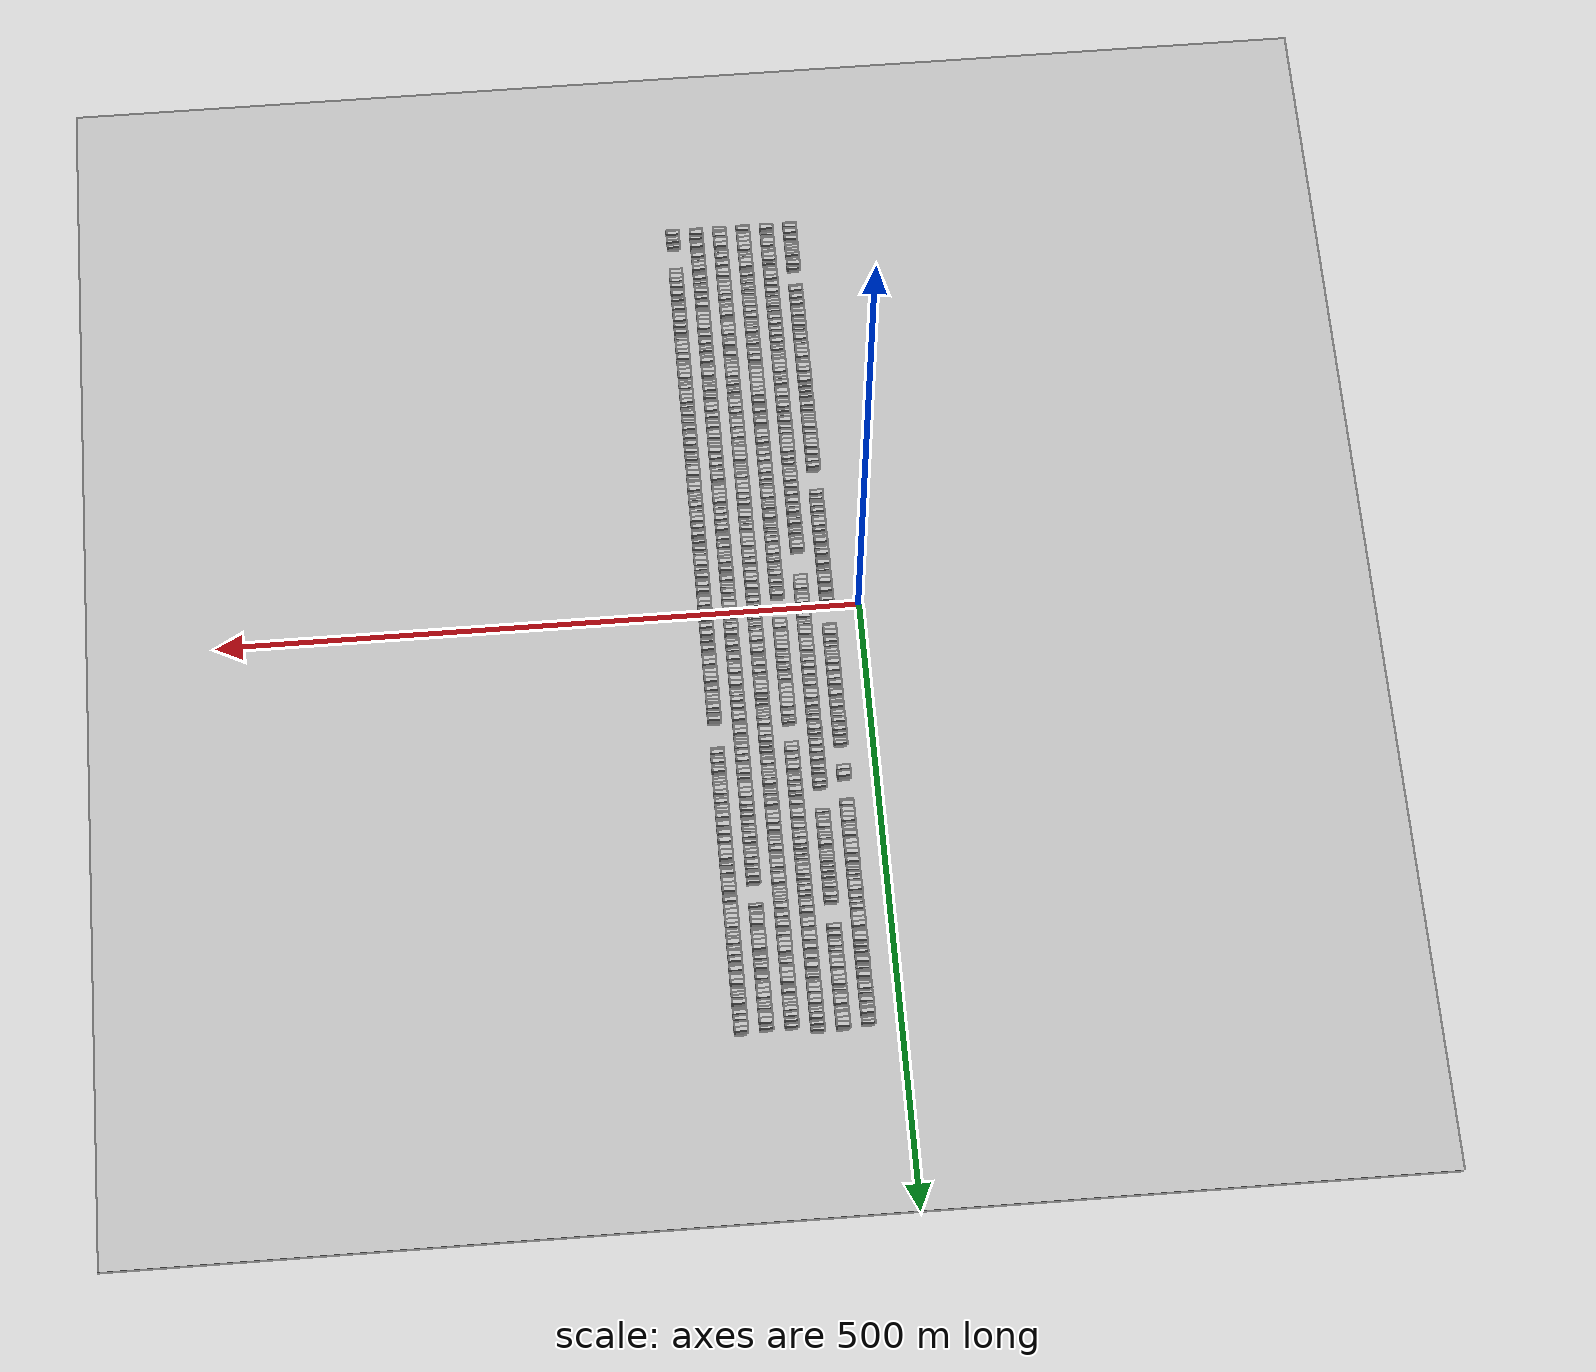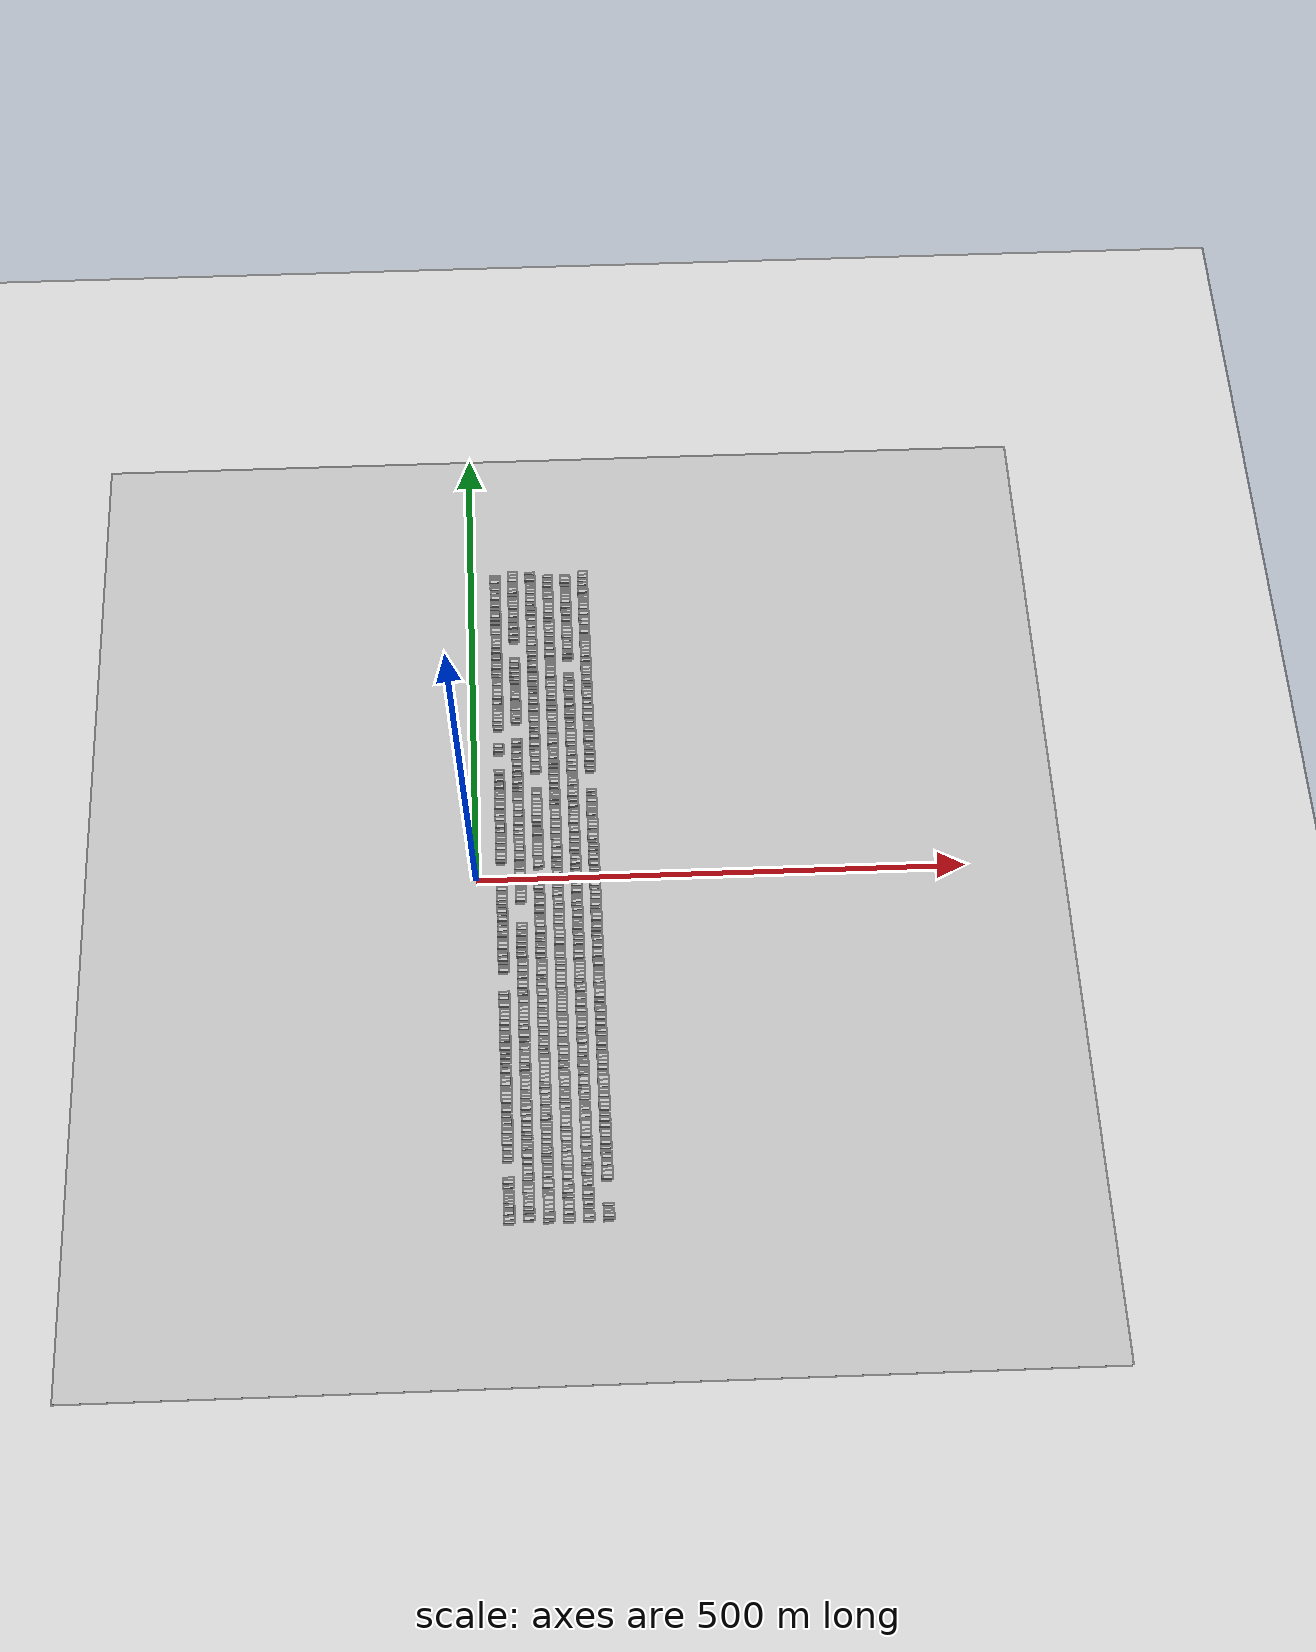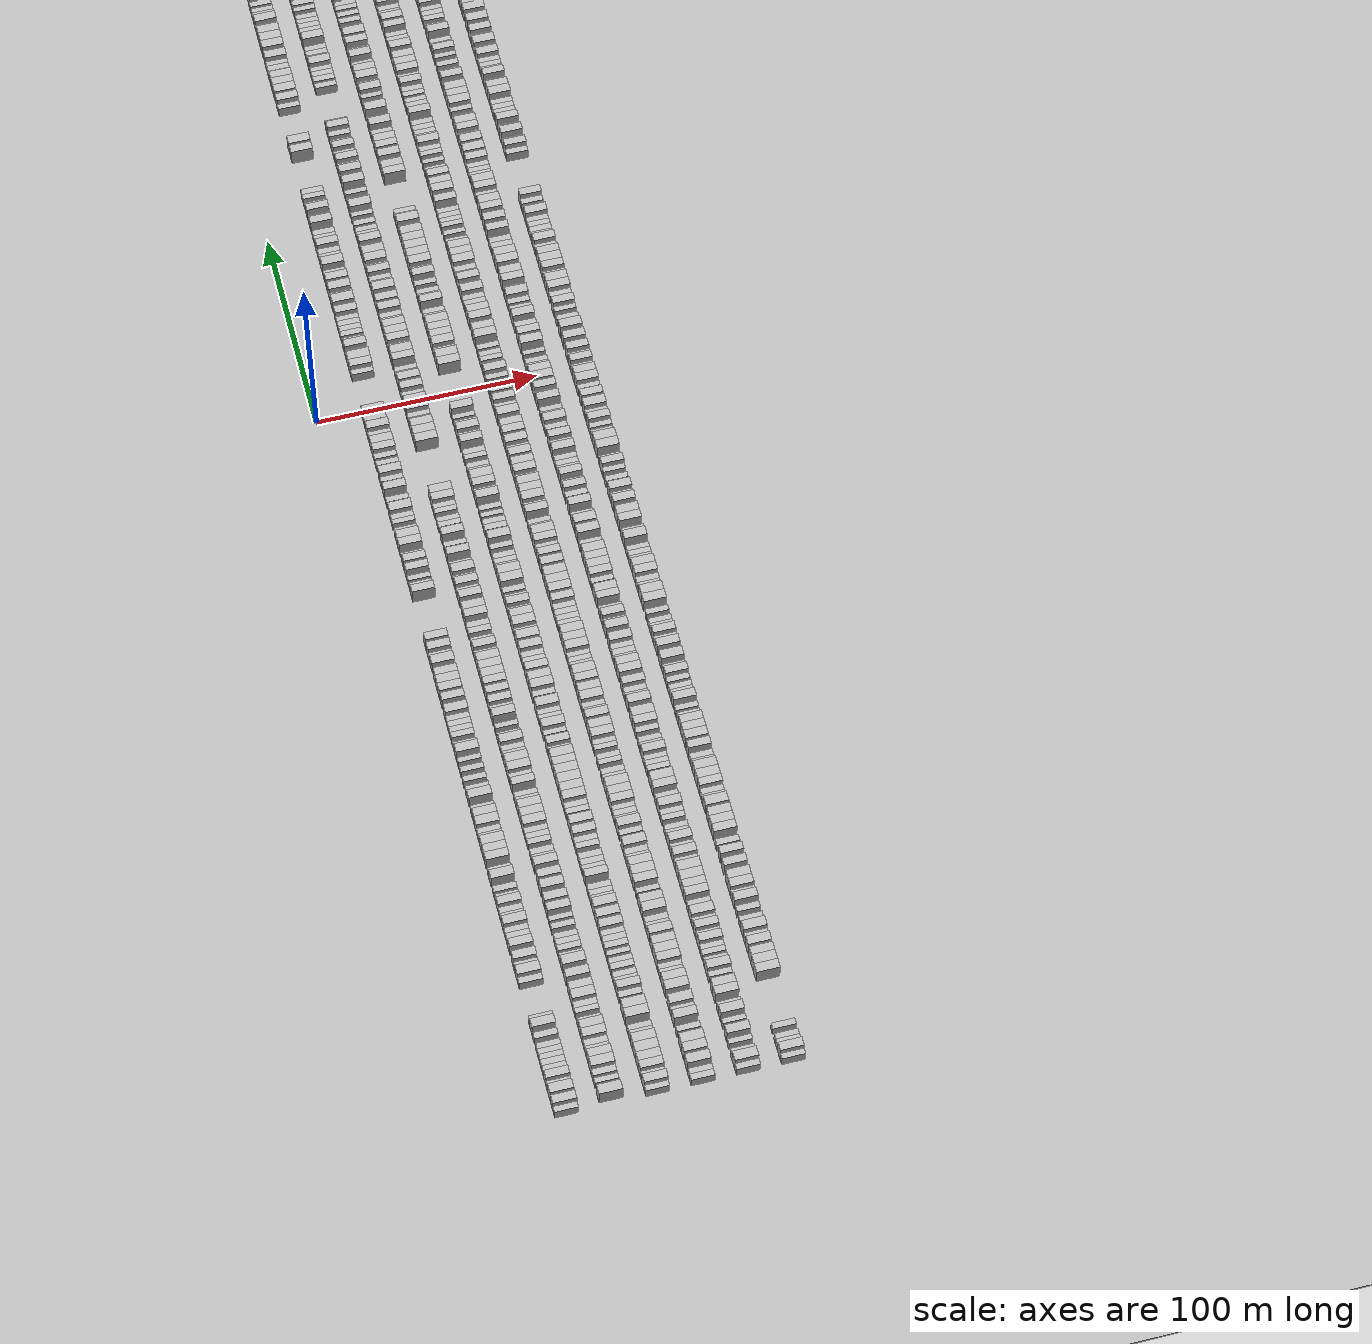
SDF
<?xml version="1.0" encoding="utf-8"?>

<sdf version="1.6">

   <world name="default">

      <gui fullscreen="0">

         <camera name="user_camera">

            <pose>-15 0 4.57585 0 0 0</pose>

            <view_controller>orbit</view_controller>

         </camera>

      </gui>

      <scene>

         <sky>

           <clouds>

             <speed>12</speed>

           </clouds>

         </sky>

         <ambient>0.4 0.4 0.4 1</ambient>

         <background>0.7 0.7 0.7 1</background>

         <shadows>1</shadows>

      </scene>

      <gravity>0 0 -9.8066</gravity>

      <magnetic_field>6e-06 2.3e-05 -4.2e-05</magnetic_field>

      <physics default="0" name="default_physics" type="ode">

         <ode>

            <solver>

               <type>quick</type>

               <iters>10</iters>

               <sor>1.0</sor>

               <use_dynamic_moi_rescaling>0</use_dynamic_moi_rescaling>

            </solver>

            <constraints>

               <cfm>0</cfm>

               <erp>0.2</erp>

               <contact_max_correcting_vel>100</contact_max_correcting_vel>

               <contact_surface_layer>0.001</contact_surface_layer>

            </constraints>

         </ode>

         <max_step_size>0.004</max_step_size>

         <real_time_factor>1</real_time_factor>

         <real_time_update_rate>250</real_time_update_rate>

      </physics>

      <light name="sun" type="directional">

         <cast_shadows>1</cast_shadows>

         <pose>0 0 10 0 0 0</pose>

         <diffuse>0.8 0.8 0.8 1</diffuse>

         <specular>0.2 0.2 0.2 1</specular>

         <attenuation>

            <range>1000</range>

            <constant>0.9</constant>

            <linear>0.01</linear>

            <quadratic>0.001</quadratic>

         </attenuation>

         <direction>-0.5 0.1 -0.9</direction>

      </light>

      <include>

         <name>ground_plane_1</name>

         <uri>model://HANNAS_ground_plane</uri>

         <pose>0 0 0  0 0 0</pose>

      </include>

      <include>

         <name>ground_plane_2</name>

         <uri>model://HANNAS_ground_plane</uri>

         <pose>100 0 0  0 0 0</pose>

      </include>

      <model name="building_1">

         <static>1</static>

         <pose frame="">25.0000 -348.6639 0 0.000000 0.000000 0.000000</pose>

         <link name="link">

            <pose frame="">0 0 3.00 0 0 0</pose>

            <collision name="collision">

               <geometry>

                  <box>

                     <size>10.0000 2.6721 6.0000</size>

                  </box>

               </geometry>

               <max_contacts>10</max_contacts>

               <surface>

                  <contact>

                     <ode/>

                  </contact>

                  <bounce/>

                  <friction>

                     <torsional>

                        <ode/>

                     </torsional>

                     <ode/>

                  </friction>

               </surface>

            </collision>

            <visual name="visual">

               <cast_shadows>0</cast_shadows>

               <geometry>

                  <box>

                     <size>10.0000 2.6721 6.0000</size>

                  </box>

               </geometry>

               <material>

                  <script>

                     <uri>model://HANNAS_wall/materials/scripts</uri>

                     <uri>model://HANNAS_wall/materials/textures</uri>

                     <name>vrc/HANNAS_wall</name>

                  </script>

               </material>

            </visual>

            <self_collide>0</self_collide>

            <enable_wind>0</enable_wind>

            <kinematic>0</kinematic>

         </link>

      </model>

      <model name="building_2">

         <static>1</static>

         <pose frame="">25.0000 -345.4278 0 0.000000 0.000000 0.000000</pose>

         <link name="link">

            <pose frame="">0 0 4.50 0 0 0</pose>

            <collision name="collision">

               <geometry>

                  <box>

                     <size>10.0000 3.8002 9.0000</size>

                  </box>

               </geometry>

               <max_contacts>10</max_contacts>

               <surface>

                  <contact>

                     <ode/>

                  </contact>

                  <bounce/>

                  <friction>

                     <torsional>

                        <ode/>

                     </torsional>

                     <ode/>

                  </friction>

               </surface>

            </collision>

            <visual name="visual">

               <cast_shadows>0</cast_shadows>

               <geometry>

                  <box>

                     <size>10.0000 3.8002 9.0000</size>

                  </box>

               </geometry>

               <material>

                  <script>

                     <uri>model://HANNAS_wall/materials/scripts</uri>

                     <uri>model://HANNAS_wall/materials/textures</uri>

                     <name>vrc/HANNAS_wall</name>

                  </script>

               </material>

            </visual>

            <self_collide>0</self_collide>

            <enable_wind>0</enable_wind>

            <kinematic>0</kinematic>

         </link>

      </model>

      <model name="building_3">

         <static>1</static>

         <pose frame="">25.0000 -340.3919 0 0.000000 0.000000 0.000000</pose>

         <link name="link">

            <pose frame="">0 0 4.50 0 0 0</pose>

            <collision name="collision">

               <geometry>

                  <box>

                     <size>10.0000 4.2715 9.0000</size>

                  </box>

               </geometry>

               <max_contacts>10</max_contacts>

               <surface>

                  <contact>

                     <ode/>

                  </contact>

                  <bounce/>

                  <friction>

                     <torsional>

                        <ode/>

                     </torsional>

                     <ode/>

                  </friction>

               </surface>

            </collision>

            <visual name="visual">

               <cast_shadows>0</cast_shadows>

               <geometry>

                  <box>

                     <size>10.0000 4.2715 9.0000</size>

                  </box>

               </geometry>

               <material>

                  <script>

                     <uri>model://HANNAS_wall/materials/scripts</uri>

                     <uri>model://HANNAS_wall/materials/textures</uri>

                     <name>vrc/HANNAS_wall</name>

                  </script>

               </material>

            </visual>

            <self_collide>0</self_collide>

            <enable_wind>0</enable_wind>

            <kinematic>0</kinematic>

         </link>

      </model>

      <model name="building_4">

         <static>1</static>

         <pose frame="">25.0000 -337.0334 0 0.000000 0.000000 0.000000</pose>

         <link name="link">

            <pose frame="">0 0 3.00 0 0 0</pose>

            <collision name="collision">

               <geometry>

                  <box>

                     <size>10.0000 2.4455 6.0000</size>

                  </box>

               </geometry>

               <max_contacts>10</max_contacts>

               <surface>

                  <contact>

                     <ode/>

                  </contact>

                  <bounce/>

                  <friction>

                     <torsional>

                        <ode/>

                     </torsional>

                     <ode/>

                  </friction>

               </surface>

            </collision>

            <visual name="visual">

               <cast_shadows>0</cast_shadows>

               <geometry>

                  <box>

                     <size>10.0000 2.4455 6.0000</size>

                  </box>

               </geometry>

               <material>

                  <script>

                     <uri>model://HANNAS_wall/materials/scripts</uri>

                     <uri>model://HANNAS_wall/materials/textures</uri>

                     <name>vrc/HANNAS_wall</name>

                  </script>

               </material>

            </visual>

            <self_collide>0</self_collide>

            <enable_wind>0</enable_wind>

            <kinematic>0</kinematic>

         </link>

      </model>

      <model name="building_5">

         <static>1</static>

         <pose frame="">25.0000 -333.9931 0 0.000000 0.000000 0.000000</pose>

         <link name="link">

            <pose frame="">0 0 4.50 0 0 0</pose>

            <collision name="collision">

               <geometry>

                  <box>

                     <size>10.0000 3.6352 9.0000</size>

                  </box>

               </geometry>

               <max_contacts>10</max_contacts>

               <surface>

                  <contact>

                     <ode/>

                  </contact>

                  <bounce/>

                  <friction>

                     <torsional>

                        <ode/>

                     </torsional>

                     <ode/>

                  </friction>

               </surface>

            </collision>

            <visual name="visual">

               <cast_shadows>0</cast_shadows>

               <geometry>

                  <box>

                     <size>10.0000 3.6352 9.0000</size>

                  </box>

               </geometry>

               <material>

                  <script>

                     <uri>model://HANNAS_wall/materials/scripts</uri>

                     <uri>model://HANNAS_wall/materials/textures</uri>

                     <name>vrc/HANNAS_wall</name>

                  </script>

               </material>

            </visual>

            <self_collide>0</self_collide>

            <enable_wind>0</enable_wind>

            <kinematic>0</kinematic>

         </link>

      </model>

      <model name="building_6">

         <static>1</static>

         <pose frame="">25.0000 -329.9448 0 0.000000 0.000000 0.000000</pose>

         <link name="link">

            <pose frame="">0 0 3.00 0 0 0</pose>

            <collision name="collision">

               <geometry>

                  <box>

                     <size>10.0000 2.4614 6.0000</size>

                  </box>

               </geometry>

               <max_contacts>10</max_contacts>

               <surface>

                  <contact>

                     <ode/>

                  </contact>

                  <bounce/>

                  <friction>

                     <torsional>

                        <ode/>

                     </torsional>

                     <ode/>

                  </friction>

               </surface>

            </collision>

            <visual name="visual">

               <cast_shadows>0</cast_shadows>

               <geometry>

                  <box>

                     <size>10.0000 2.4614 6.0000</size>

                  </box>

               </geometry>

               <material>

                  <script>

                     <uri>model://HANNAS_wall/materials/scripts</uri>

                     <uri>model://HANNAS_wall/materials/textures</uri>

                     <name>vrc/HANNAS_wall</name>

                  </script>

               </material>

            </visual>

            <self_collide>0</self_collide>

            <enable_wind>0</enable_wind>

            <kinematic>0</kinematic>

         </link>

      </model>

      <model name="building_7">

         <static>1</static>

         <pose frame="">25.0000 -327.2852 0 0.000000 0.000000 0.000000</pose>

         <link name="link">

            <pose frame="">0 0 3.00 0 0 0</pose>

            <collision name="collision">

               <geometry>

                  <box>

                     <size>10.0000 2.8578 6.0000</size>

                  </box>

               </geometry>

               <max_contacts>10</max_contacts>

               <surface>

                  <contact>

                     <ode/>

                  </contact>

                  <bounce/>

                  <friction>

                     <torsional>

                        <ode/>

                     </torsional>

                     <ode/>

                  </friction>

               </surface>

            </collision>

            <visual name="visual">

               <cast_shadows>0</cast_shadows>

               <geometry>

                  <box>

                     <size>10.0000 2.8578 6.0000</size>

                  </box>

               </geometry>

               <material>

                  <script>

                     <uri>model://HANNAS_wall/materials/scripts</uri>

                     <uri>model://HANNAS_wall/materials/textures</uri>

                     <name>vrc/HANNAS_wall</name>

                  </script>

               </material>

            </visual>

            <self_collide>0</self_collide>

            <enable_wind>0</enable_wind>

            <kinematic>0</kinematic>

         </link>

      </model>

      <model name="building_8">

         <static>1</static>

         <pose frame="">25.0000 -324.6394 0 0.000000 0.000000 0.000000</pose>

         <link name="link">

            <pose frame="">0 0 3.00 0 0 0</pose>

            <collision name="collision">

               <geometry>

                  <box>

                     <size>10.0000 2.4337 6.0000</size>

                  </box>

               </geometry>

               <max_contacts>10</max_contacts>

               <surface>

                  <contact>

                     <ode/>

                  </contact>

                  <bounce/>

                  <friction>

                     <torsional>

                        <ode/>

                     </torsional>

                     <ode/>

                  </friction>

               </surface>

            </collision>

            <visual name="visual">

               <cast_shadows>0</cast_shadows>

               <geometry>

                  <box>

                     <size>10.0000 2.4337 6.0000</size>

                  </box>

               </geometry>

               <material>

                  <script>

                     <uri>model://HANNAS_wall/materials/scripts</uri>

                     <uri>model://HANNAS_wall/materials/textures</uri>

                     <name>vrc/HANNAS_wall</name>

                  </script>

               </material>

            </visual>

            <self_collide>0</self_collide>

            <enable_wind>0</enable_wind>

            <kinematic>0</kinematic>

         </link>

      </model>

      <model name="building_9">

         <static>1</static>

         <pose frame="">25.0000 -322.2049 0 0.000000 0.000000 0.000000</pose>

         <link name="link">

            <pose frame="">0 0 3.00 0 0 0</pose>

            <collision name="collision">

               <geometry>

                  <box>

                     <size>10.0000 2.4353 6.0000</size>

                  </box>

               </geometry>

               <max_contacts>10</max_contacts>

               <surface>

                  <contact>

                     <ode/>

                  </contact>

                  <bounce/>

                  <friction>

                     <torsional>

                        <ode/>

                     </torsional>

                     <ode/>

                  </friction>

               </surface>

            </collision>

            <visual name="visual">

               <cast_shadows>0</cast_shadows>

               <geometry>

                  <box>

                     <size>10.0000 2.4353 6.0000</size>

                  </box>

               </geometry>

               <material>

                  <script>

                     <uri>model://HANNAS_wall/materials/scripts</uri>

                     <uri>model://HANNAS_wall/materials/textures</uri>

                     <name>vrc/HANNAS_wall</name>

                  </script>

               </material>

            </visual>

            <self_collide>0</self_collide>

            <enable_wind>0</enable_wind>

            <kinematic>0</kinematic>

         </link>

      </model>

      <model name="building_10">

         <static>1</static>

         <pose frame="">25.0000 -319.6846 0 0.000000 0.000000 0.000000</pose>

         <link name="link">

            <pose frame="">0 0 3.00 0 0 0</pose>

            <collision name="collision">

               <geometry>

                  <box>

                     <size>10.0000 2.6054 6.0000</size>

                  </box>

               </geometry>

               <max_contacts>10</max_contacts>

               <surface>

                  <contact>

                     <ode/>

                  </contact>

                  <bounce/>

                  <friction>

                     <torsional>

                        <ode/>

                     </torsional>

                     <ode/>

                  </friction>

               </surface>

            </collision>

            <visual name="visual">

               <cast_shadows>0</cast_shadows>

               <geometry>

                  <box>

                     <size>10.0000 2.6054 6.0000</size>

                  </box>

               </geometry>

               <material>

                  <script>

                     <uri>model://HANNAS_wall/materials/scripts</uri>

                     <uri>model://HANNAS_wall/materials/textures</uri>

                     <name>vrc/HANNAS_wall</name>

                  </script>

               </material>

            </visual>

            <self_collide>0</self_collide>

            <enable_wind>0</enable_wind>

            <kinematic>0</kinematic>

         </link>

      </model>

      <model name="building_11">

         <static>1</static>

         <pose frame="">25.0000 -314.9156 0 0.000000 0.000000 0.000000</pose>

         <link name="link">

            <pose frame="">0 0 3.00 0 0 0</pose>

            <collision name="collision">

               <geometry>

                  <box>

                     <size>10.0000 2.9324 6.0000</size>

                  </box>

               </geometry>

               <max_contacts>10</max_contacts>

               <surface>

                  <contact>

                     <ode/>

                  </contact>

                  <bounce/>

                  <friction>

                     <torsional>

                        <ode/>

                     </torsional>

                     <ode/>

                  </friction>

               </surface>

            </collision>

            <visual name="visual">

               <cast_shadows>0</cast_shadows>

               <geometry>

                  <box>

                     <size>10.0000 2.9324 6.0000</size>

                  </box>

               </geometry>

               <material>

                  <script>

                     <uri>model://HANNAS_wall/materials/scripts</uri>

                     <uri>model://HANNAS_wall/materials/textures</uri>

                     <name>vrc/HANNAS_wall</name>

                  </script>

               </material>

            </visual>

            <self_collide>0</self_collide>

            <enable_wind>0</enable_wind>

            <kinematic>0</kinematic>

         </link>

      </model>

      <model name="building_12">

         <static>1</static>

         <pose frame="">25.0000 -310.4565 0 0.000000 0.000000 0.000000</pose>

         <link name="link">

            <pose frame="">0 0 4.50 0 0 0</pose>

            <collision name="collision">

               <geometry>

                  <box>

                     <size>10.0000 3.9858 9.0000</size>

                  </box>

               </geometry>

               <max_contacts>10</max_contacts>

               <surface>

                  <contact>

                     <ode/>

                  </contact>

                  <bounce/>

                  <friction>

                     <torsional>

                        <ode/>

                     </torsional>

                     <ode/>

                  </friction>

               </surface>

            </collision>

            <visual name="visual">

               <cast_shadows>0</cast_shadows>

               <geometry>

                  <box>

                     <size>10.0000 3.9858 9.0000</size>

                  </box>

               </geometry>

               <material>

                  <script>

                     <uri>model://HANNAS_wall/materials/scripts</uri>

                     <uri>model://HANNAS_wall/materials/textures</uri>

                     <name>vrc/HANNAS_wall</name>

                  </script>

               </material>

            </visual>

            <self_collide>0</self_collide>

            <enable_wind>0</enable_wind>

            <kinematic>0</kinematic>

         </link>

      </model>

      <model name="building_13">

         <static>1</static>

         <pose frame="">25.0000 -307.0967 0 0.000000 0.000000 0.000000</pose>

         <link name="link">

            <pose frame="">0 0 3.00 0 0 0</pose>

            <collision name="collision">

               <geometry>

                  <box>

                     <size>10.0000 2.7338 6.0000</size>

                  </box>

               </geometry>

               <max_contacts>10</max_contacts>

               <surface>

                  <contact>

                     <ode/>

                  </contact>

                  <bounce/>

                  <friction>

                     <torsional>

                        <ode/>

                     </torsional>

                     <ode/>

                  </friction>

               </surface>

            </collision>

            <visual name="visual">

               <cast_shadows>0</cast_shadows>

               <geometry>

                  <box>

                     <size>10.0000 2.7338 6.0000</size>

                  </box>

               </geometry>

               <material>

                  <script>

                     <uri>model://HANNAS_wall/materials/scripts</uri>

                     <uri>model://HANNAS_wall/materials/textures</uri>

                     <name>vrc/HANNAS_wall</name>

                  </script>

               </material>

            </visual>

            <self_collide>0</self_collide>

            <enable_wind>0</enable_wind>

            <kinematic>0</kinematic>

         </link>

      </model>

      <model name="building_14">

         <static>1</static>

         <pose frame="">25.0000 -289.3528 0 0.000000 0.000000 0.000000</pose>

         <link name="link">

            <pose frame="">0 0 3.00 0 0 0</pose>

            <collision name="collision">

               <geometry>

                  <box>

                     <size>10.0000 2.9180 6.0000</size>

                  </box>

               </geometry>

               <max_contacts>10</max_contacts>

               <surface>

                  <contact>

                     <ode/>

                  </contact>

                  <bounce/>

                  <friction>

                     <torsional>

                        <ode/>

                     </torsional>

                     <ode/>

                  </friction>

               </surface>

            </collision>

            <visual name="visual">

               <cast_shadows>0</cast_shadows>

               <geometry>

                  <box>

                     <size>10.0000 2.9180 6.0000</size>

                  </box>

               </geometry>

               <material>

                  <script>

                     <uri>model://HANNAS_wall/materials/scripts</uri>

                     <uri>model://HANNAS_wall/materials/textures</uri>

                     <name>vrc/HANNAS_wall</name>

                  </script>

               </material>

            </visual>

            <self_collide>0</self_collide>

            <enable_wind>0</enable_wind>

            <kinematic>0</kinematic>

         </link>

      </model>

      <model name="building_15">

         <static>1</static>

         <pose frame="">25.0000 -285.6811 0 0.000000 0.000000 0.000000</pose>

         <link name="link">

            <pose frame="">0 0 4.50 0 0 0</pose>

            <collision name="collision">

               <geometry>

                  <box>

                     <size>10.0000 4.4253 9.0000</size>

                  </box>

               </geometry>

               <max_contacts>10</max_contacts>

               <surface>

                  <contact>

                     <ode/>

                  </contact>

                  <bounce/>

                  <friction>

                     <torsional>

                        <ode/>

                     </torsional>

                     <ode/>

                  </friction>

               </surface>

            </collision>

            <visual name="visual">

               <cast_shadows>0</cast_shadows>

               <geometry>

                  <box>

                     <size>10.0000 4.4253 9.0000</size>

                  </box>

               </geometry>

               <material>

                  <script>

                     <uri>model://HANNAS_wall/materials/scripts</uri>

                     <uri>model://HANNAS_wall/materials/textures</uri>

                     <name>vrc/HANNAS_wall</name>

                  </script>

               </material>

            </visual>

            <self_collide>0</self_collide>

            <enable_wind>0</enable_wind>

            <kinematic>0</kinematic>

         </link>

      </model>

      <model name="building_16">

         <static>1</static>

         <pose frame="">25.0000 -282.0970 0 0.000000 0.000000 0.000000</pose>

         <link name="link">

            <pose frame="">0 0 3.00 0 0 0</pose>

            <collision name="collision">

               <geometry>

                  <box>

                     <size>10.0000 2.7429 6.0000</size>

                  </box>

               </geometry>

               <max_contacts>10</max_contacts>

               <surface>

                  <contact>

                     <ode/>

                  </contact>

                  <bounce/>

                  <friction>

                     <torsional>

                        <ode/>

                     </torsional>

                     <ode/>

                  </friction>

               </surface>

            </collision>

            <visual name="visual">

               <cast_shadows>0</cast_shadows>

               <geometry>

                  <box>

                     <size>10.0000 2.7429 6.0000</size>

                  </box>

               </geometry>

               <material>

                  <script>

                     <uri>model://HANNAS_wall/materials/scripts</uri>

                     <uri>model://HANNAS_wall/materials/textures</uri>

                     <name>vrc/HANNAS_wall</name>

                  </script>

               </material>

            </visual>

            <self_collide>0</self_collide>

            <enable_wind>0</enable_wind>

            <kinematic>0</kinematic>

         </link>

      </model>

      <model name="building_17">

         <static>1</static>

         <pose frame="">25.0000 -278.7646 0 0.000000 0.000000 0.000000</pose>

         <link name="link">

            <pose frame="">0 0 4.50 0 0 0</pose>

            <collision name="collision">

               <geometry>

                  <box>

                     <size>10.0000 3.9218 9.0000</size>

                  </box>

               </geometry>

               <max_contacts>10</max_contacts>

               <surface>

                  <contact>

                     <ode/>

                  </contact>

                  <bounce/>

                  <friction>

                     <torsional>

                        <ode/>

                     </torsional>

                     <ode/>

                  </friction>

               </surface>

            </collision>

            <visual name="visual">

               <cast_shadows>0</cast_shadows>

               <geometry>

                  <box>

                     <size>10.0000 3.9218 9.0000</size>

                  </box>

               </geometry>

               <material>

                  <script>

                     <uri>model://HANNAS_wall/materials/scripts</uri>

                     <uri>model://HANNAS_wall/materials/textures</uri>

                     <name>vrc/HANNAS_wall</name>

                  </script>

               </material>

            </visual>

            <self_collide>0</self_collide>

            <enable_wind>0</enable_wind>

            <kinematic>0</kinematic>

         </link>

      </model>

      <model name="building_18">

         <static>1</static>

         <pose frame="">25.0000 -272.8921 0 0.000000 0.000000 0.000000</pose>

         <link name="link">

            <pose frame="">0 0 4.50 0 0 0</pose>

            <collision name="collision">

               <geometry>

                  <box>

                     <size>10.0000 3.8233 9.0000</size>

                  </box>

               </geometry>

               <max_contacts>10</max_contacts>

               <surface>

                  <contact>

                     <ode/>

                  </contact>

                  <bounce/>

                  <friction>

                     <torsional>

                        <ode/>

                     </torsional>

                     <ode/>

                  </friction>

               </surface>

            </collision>

            <visual name="visual">

               <cast_shadows>0</cast_shadows>

               <geometry>

                  <box>

                     <size>10.0000 3.8233 9.0000</size>

                  </box>

               </geometry>

               <material>

                  <script>

                     <uri>model://HANNAS_wall/materials/scripts</uri>

                     <uri>model://HANNAS_wall/materials/textures</uri>

                     <name>vrc/HANNAS_wall</name>

                  </script>

               </material>

            </visual>

            <self_collide>0</self_collide>

            <enable_wind>0</enable_wind>

            <kinematic>0</kinematic>

         </link>

      </model>

      <model name="building_19">

         <static>1</static>

         <pose frame="">25.0000 -268.4926 0 0.000000 0.000000 0.000000</pose>

         <link name="link">

            <pose frame="">0 0 3.00 0 0 0</pose>

            <collision name="collision">

               <geometry>

                  <box>

                     <size>10.0000 2.9757 6.0000</size>

                  </box>

               </geometry>

               <max_contacts>10</max_contacts>

               <surface>

                  <contact>

                     <ode/>

                  </contact>

                  <bounce/>

                  <friction>

                     <torsional>

                        <ode/>

                     </torsional>

                     <ode/>

                  </friction>

               </surface>

            </collision>

            <visual name="visual">

               <cast_shadows>0</cast_shadows>

               <geometry>

                  <box>

                     <size>10.0000 2.9757 6.0000</size>

                  </box>

               </geometry>

               <material>

                  <script>

                     <uri>model://HANNAS_wall/materials/scripts</uri>

                     <uri>model://HANNAS_wall/materials/textures</uri>

                     <name>vrc/HANNAS_wall</name>

                  </script>

               </material>

            </visual>

            <self_collide>0</self_collide>

            <enable_wind>0</enable_wind>

            <kinematic>0</kinematic>

         </link>

      </model>

      <model name="building_20">

         <static>1</static>

         <pose frame="">25.0000 -265.6619 0 0.000000 0.000000 0.000000</pose>

         <link name="link">

            <pose frame="">0 0 3.00 0 0 0</pose>

            <collision name="collision">

               <geometry>

                  <box>

                     <size>10.0000 2.6859 6.0000</size>

                  </box>

               </geometry>

               <max_contacts>10</max_contacts>

               <surface>

                  <contact>

                     <ode/>

                  </contact>

                  <bounce/>

                  <friction>

                     <torsional>

                        <ode/>

                     </torsional>

                     <ode/>

                  </friction>

               </surface>

            </collision>

            <visual name="visual">

               <cast_shadows>0</cast_shadows>

               <geometry>

                  <box>

                     <size>10.0000 2.6859 6.0000</size>

                  </box>

               </geometry>

               <material>

                  <script>

                     <uri>model://HANNAS_wall/materials/scripts</uri>

                     <uri>model://HANNAS_wall/materials/textures</uri>

                     <name>vrc/HANNAS_wall</name>

                  </script>

               </material>

            </visual>

            <self_collide>0</self_collide>

            <enable_wind>0</enable_wind>

            <kinematic>0</kinematic>

         </link>

      </model>

      <model name="building_21">

         <static>1</static>

         <pose frame="">25.0000 -262.2273 0 0.000000 0.000000 0.000000</pose>

         <link name="link">

            <pose frame="">0 0 4.50 0 0 0</pose>

            <collision name="collision">

               <geometry>

                  <box>

                     <size>10.0000 4.1832 9.0000</size>

                  </box>

               </geometry>

               <max_contacts>10</max_contacts>

               <surface>

                  <contact>

                     <ode/>

                  </contact>

                  <bounce/>

                  <friction>

                     <torsional>

                        <ode/>

                     </torsional>

                     <ode/>

                  </friction>

               </surface>

            </collision>

            <visual name="visual">

               <cast_shadows>0</cast_shadows>

               <geometry>

                  <box>

                     <size>10.0000 4.1832 9.0000</size>

                  </box>

               </geometry>

               <material>

                  <script>

                     <uri>model://HANNAS_wall/materials/scripts</uri>

                     <uri>model://HANNAS_wall/materials/textures</uri>

                     <name>vrc/HANNAS_wall</name>

                  </script>

               </material>

            </visual>

            <self_collide>0</self_collide>

            <enable_wind>0</enable_wind>

            <kinematic>0</kinematic>

         </link>

      </model>

      <model name="building_22">

         <static>1</static>

         <pose frame="">25.0000 -258.8390 0 0.000000 0.000000 0.000000</pose>

         <link name="link">

            <pose frame="">0 0 3.00 0 0 0</pose>

            <collision name="collision">

               <geometry>

                  <box>

                     <size>10.0000 2.5935 6.0000</size>

                  </box>

               </geometry>

               <max_contacts>10</max_contacts>

               <surface>

                  <contact>

                     <ode/>

                  </contact>

                  <bounce/>

                  <friction>

                     <torsional>

                        <ode/>

                     </torsional>

                     <ode/>

                  </friction>

               </surface>

            </collision>

            <visual name="visual">

               <cast_shadows>0</cast_shadows>

               <geometry>

                  <box>

                     <size>10.0000 2.5935 6.0000</size>

                  </box>

               </geometry>

               <material>

                  <script>

                     <uri>model://HANNAS_wall/materials/scripts</uri>

                     <uri>model://HANNAS_wall/materials/textures</uri>

                     <name>vrc/HANNAS_wall</name>

                  </script>

               </material>

            </visual>

            <self_collide>0</self_collide>

            <enable_wind>0</enable_wind>

            <kinematic>0</kinematic>

         </link>

      </model>

      <model name="building_23">

         <static>1</static>

         <pose frame="">25.0000 -256.1742 0 0.000000 0.000000 0.000000</pose>

         <link name="link">

            <pose frame="">0 0 3.00 0 0 0</pose>

            <collision name="collision">

               <geometry>

                  <box>

                     <size>10.0000 2.7360 6.0000</size>

                  </box>

               </geometry>

               <max_contacts>10</max_contacts>

               <surface>

                  <contact>

                     <ode/>

                  </contact>

                  <bounce/>

                  <friction>

                     <torsional>

                        <ode/>

                     </torsional>

                     <ode/>

                  </friction>

               </surface>

            </collision>

            <visual name="visual">

               <cast_shadows>0</cast_shadows>

               <geometry>

                  <box>

                     <size>10.0000 2.7360 6.0000</size>

                  </box>

               </geometry>

               <material>

                  <script>

                     <uri>model://HANNAS_wall/materials/scripts</uri>

                     <uri>model://HANNAS_wall/materials/textures</uri>

                     <name>vrc/HANNAS_wall</name>

                  </script>

               </material>

            </visual>

            <self_collide>0</self_collide>

            <enable_wind>0</enable_wind>

            <kinematic>0</kinematic>

         </link>

      </model>

      <model name="building_24">

         <static>1</static>

         <pose frame="">25.0000 -252.9515 0 0.000000 0.000000 0.000000</pose>

         <link name="link">

            <pose frame="">0 0 4.50 0 0 0</pose>

            <collision name="collision">

               <geometry>

                  <box>

                     <size>10.0000 3.7094 9.0000</size>

                  </box>

               </geometry>

               <max_contacts>10</max_contacts>

               <surface>

                  <contact>

                     <ode/>

                  </contact>

                  <bounce/>

                  <friction>

                     <torsional>

                        <ode/>

                     </torsional>

                     <ode/>

                  </friction>

               </surface>

            </collision>

            <visual name="visual">

               <cast_shadows>0</cast_shadows>

               <geometry>

                  <box>

                     <size>10.0000 3.7094 9.0000</size>

                  </box>

               </geometry>

               <material>

                  <script>

                     <uri>model://HANNAS_wall/materials/scripts</uri>

                     <uri>model://HANNAS_wall/materials/textures</uri>

                     <name>vrc/HANNAS_wall</name>

                  </script>

               </material>

            </visual>

            <self_collide>0</self_collide>

            <enable_wind>0</enable_wind>

            <kinematic>0</kinematic>

         </link>

      </model>

      <model name="building_25">

         <static>1</static>

         <pose frame="">25.0000 -249.7769 0 0.000000 0.000000 0.000000</pose>

         <link name="link">

            <pose frame="">0 0 3.00 0 0 0</pose>

            <collision name="collision">

               <geometry>

                  <box>

                     <size>10.0000 2.6398 6.0000</size>

                  </box>

               </geometry>

               <max_contacts>10</max_contacts>

               <surface>

                  <contact>

                     <ode/>

                  </contact>

                  <bounce/>

                  <friction>

                     <torsional>

                        <ode/>

                     </torsional>

                     <ode/>

                  </friction>

               </surface>

            </collision>

            <visual name="visual">

               <cast_shadows>0</cast_shadows>

               <geometry>

                  <box>

                     <size>10.0000 2.6398 6.0000</size>

                  </box>

               </geometry>

               <material>

                  <script>

                     <uri>model://HANNAS_wall/materials/scripts</uri>

                     <uri>model://HANNAS_wall/materials/textures</uri>

                     <name>vrc/HANNAS_wall</name>

                  </script>

               </material>

            </visual>

            <self_collide>0</self_collide>

            <enable_wind>0</enable_wind>

            <kinematic>0</kinematic>

         </link>

      </model>

      <model name="building_26">

         <static>1</static>

         <pose frame="">25.0000 -245.9843 0 0.000000 0.000000 0.000000</pose>

         <link name="link">

            <pose frame="">0 0 3.00 0 0 0</pose>

            <collision name="collision">

               <geometry>

                  <box>

                     <size>10.0000 2.9455 6.0000</size>

                  </box>

               </geometry>

               <max_contacts>10</max_contacts>

               <surface>

                  <contact>

                     <ode/>

                  </contact>

                  <bounce/>

                  <friction>

                     <torsional>

                        <ode/>

                     </torsional>

                     <ode/>

                  </friction>

               </surface>

            </collision>

            <visual name="visual">

               <cast_shadows>0</cast_shadows>

               <geometry>

                  <box>

                     <size>10.0000 2.9455 6.0000</size>

                  </box>

               </geometry>

               <material>

                  <script>

                     <uri>model://HANNAS_wall/materials/scripts</uri>

                     <uri>model://HANNAS_wall/materials/textures</uri>

                     <name>vrc/HANNAS_wall</name>

                  </script>

               </material>

            </visual>

            <self_collide>0</self_collide>

            <enable_wind>0</enable_wind>

            <kinematic>0</kinematic>

         </link>

      </model>

      <model name="building_27">

         <static>1</static>

         <pose frame="">25.0000 -240.4150 0 0.000000 0.000000 0.000000</pose>

         <link name="link">

            <pose frame="">0 0 4.50 0 0 0</pose>

            <collision name="collision">

               <geometry>

                  <box>

                     <size>10.0000 4.1932 9.0000</size>

                  </box>

               </geometry>

               <max_contacts>10</max_contacts>

               <surface>

                  <contact>

                     <ode/>

                  </contact>

                  <bounce/>

                  <friction>

                     <torsional>

                        <ode/>

                     </torsional>

                     <ode/>

                  </friction>

               </surface>

            </collision>

            <visual name="visual">

               <cast_shadows>0</cast_shadows>

               <geometry>

                  <box>

                     <size>10.0000 4.1932 9.0000</size>

                  </box>

               </geometry>

               <material>

                  <script>

                     <uri>model://HANNAS_wall/materials/scripts</uri>

                     <uri>model://HANNAS_wall/materials/textures</uri>

                     <name>vrc/HANNAS_wall</name>

                  </script>

               </material>

            </visual>

            <self_collide>0</self_collide>

            <enable_wind>0</enable_wind>

            <kinematic>0</kinematic>

         </link>

      </model>

      <model name="building_28">

         <static>1</static>

         <pose frame="">25.0000 -236.9606 0 0.000000 0.000000 0.000000</pose>

         <link name="link">

            <pose frame="">0 0 3.00 0 0 0</pose>

            <collision name="collision">

               <geometry>

                  <box>

                     <size>10.0000 2.7154 6.0000</size>

                  </box>

               </geometry>

               <max_contacts>10</max_contacts>

               <surface>

                  <contact>

                     <ode/>

                  </contact>

                  <bounce/>

                  <friction>

                     <torsional>

                        <ode/>

                     </torsional>

                     <ode/>

                  </friction>

               </surface>

            </collision>

            <visual name="visual">

               <cast_shadows>0</cast_shadows>

               <geometry>

                  <box>

                     <size>10.0000 2.7154 6.0000</size>

                  </box>

               </geometry>

               <material>

                  <script>

                     <uri>model://HANNAS_wall/materials/scripts</uri>

                     <uri>model://HANNAS_wall/materials/textures</uri>

                     <name>vrc/HANNAS_wall</name>

                  </script>

               </material>

            </visual>

            <self_collide>0</self_collide>

            <enable_wind>0</enable_wind>

            <kinematic>0</kinematic>

         </link>

      </model>

      <model name="building_29">

         <static>1</static>

         <pose frame="">25.0000 -231.6772 0 0.000000 0.000000 0.000000</pose>

         <link name="link">

            <pose frame="">0 0 4.50 0 0 0</pose>

            <collision name="collision">

               <geometry>

                  <box>

                     <size>10.0000 3.8514 9.0000</size>

                  </box>

               </geometry>

               <max_contacts>10</max_contacts>

               <surface>

                  <contact>

                     <ode/>

                  </contact>

                  <bounce/>

                  <friction>

                     <torsional>

                        <ode/>

                     </torsional>

                     <ode/>

                  </friction>

               </surface>

            </collision>

            <visual name="visual">

               <cast_shadows>0</cast_shadows>

               <geometry>

                  <box>

                     <size>10.0000 3.8514 9.0000</size>

                  </box>

               </geometry>

               <material>

                  <script>

                     <uri>model://HANNAS_wall/materials/scripts</uri>

                     <uri>model://HANNAS_wall/materials/textures</uri>

                     <name>vrc/HANNAS_wall</name>

                  </script>

               </material>

            </visual>

            <self_collide>0</self_collide>

            <enable_wind>0</enable_wind>

            <kinematic>0</kinematic>

         </link>

      </model>

      <model name="building_30">

         <static>1</static>

         <pose frame="">25.0000 -227.9165 0 0.000000 0.000000 0.000000</pose>

         <link name="link">

            <pose frame="">0 0 4.50 0 0 0</pose>

            <collision name="collision">

               <geometry>

                  <box>

                     <size>10.0000 3.6700 9.0000</size>

                  </box>

               </geometry>

               <max_contacts>10</max_contacts>

               <surface>

                  <contact>

                     <ode/>

                  </contact>

                  <bounce/>

                  <friction>

                     <torsional>

                        <ode/>

                     </torsional>

                     <ode/>

                  </friction>

               </surface>

            </collision>

            <visual name="visual">

               <cast_shadows>0</cast_shadows>

               <geometry>

                  <box>

                     <size>10.0000 3.6700 9.0000</size>

                  </box>

               </geometry>

               <material>

                  <script>

                     <uri>model://HANNAS_wall/materials/scripts</uri>

                     <uri>model://HANNAS_wall/materials/textures</uri>

                     <name>vrc/HANNAS_wall</name>

                  </script>

               </material>

            </visual>

            <self_collide>0</self_collide>

            <enable_wind>0</enable_wind>

            <kinematic>0</kinematic>

         </link>

      </model>

      <model name="building_31">

         <static>1</static>

         <pose frame="">25.0000 -223.9107 0 0.000000 0.000000 0.000000</pose>

         <link name="link">

            <pose frame="">0 0 4.50 0 0 0</pose>

            <collision name="collision">

               <geometry>

                  <box>

                     <size>10.0000 4.3416 9.0000</size>

                  </box>

               </geometry>

               <max_contacts>10</max_contacts>

               <surface>

                  <contact>

                     <ode/>

                  </contact>

                  <bounce/>

                  <friction>

                     <torsional>

                        <ode/>

                     </torsional>

                     <ode/>

                  </friction>

               </surface>

            </collision>

            <visual name="visual">

               <cast_shadows>0</cast_shadows>

               <geometry>

                  <box>

                     <size>10.0000 4.3416 9.0000</size>

                  </box>

               </geometry>

               <material>

                  <script>

                     <uri>model://HANNAS_wall/materials/scripts</uri>

                     <uri>model://HANNAS_wall/materials/textures</uri>

                     <name>vrc/HANNAS_wall</name>

                  </script>

               </material>

            </visual>

            <self_collide>0</self_collide>

            <enable_wind>0</enable_wind>

            <kinematic>0</kinematic>

         </link>

      </model>

      <model name="building_32">

         <static>1</static>

         <pose frame="">25.0000 -220.4980 0 0.000000 0.000000 0.000000</pose>

         <link name="link">

            <pose frame="">0 0 3.00 0 0 0</pose>

            <collision name="collision">

               <geometry>

                  <box>

                     <size>10.0000 2.4838 6.0000</size>

                  </box>

               </geometry>

               <max_contacts>10</max_contacts>

               <surface>

                  <contact>

                     <ode/>

                  </contact>

                  <bounce/>

                  <friction>

                     <torsional>

                        <ode/>

                     </torsional>

                     <ode/>

                  </friction>

               </surface>

            </collision>

            <visual name="visual">

               <cast_shadows>0</cast_shadows>

               <geometry>

                  <box>

                     <size>10.0000 2.4838 6.0000</size>

                  </box>

               </geometry>

               <material>

                  <script>

                     <uri>model://HANNAS_wall/materials/scripts</uri>

                     <uri>model://HANNAS_wall/materials/textures</uri>

                     <name>vrc/HANNAS_wall</name>

                  </script>

               </material>

            </visual>

            <self_collide>0</self_collide>

            <enable_wind>0</enable_wind>

            <kinematic>0</kinematic>

         </link>

      </model>

      <model name="building_33">

         <static>1</static>

         <pose frame="">25.0000 -217.9826 0 0.000000 0.000000 0.000000</pose>

         <link name="link">

            <pose frame="">0 0 3.00 0 0 0</pose>

            <collision name="collision">

               <geometry>

                  <box>

                     <size>10.0000 2.5470 6.0000</size>

                  </box>

               </geometry>

               <max_contacts>10</max_contacts>

               <surface>

                  <contact>

                     <ode/>

                  </contact>

                  <bounce/>

                  <friction>

                     <torsional>

                        <ode/>

                     </torsional>

                     <ode/>

                  </friction>

               </surface>

            </collision>

            <visual name="visual">

               <cast_shadows>0</cast_shadows>

               <geometry>

                  <box>

                     <size>10.0000 2.5470 6.0000</size>

                  </box>

               </geometry>

               <material>

                  <script>

                     <uri>model://HANNAS_wall/materials/scripts</uri>

                     <uri>model://HANNAS_wall/materials/textures</uri>

                     <name>vrc/HANNAS_wall</name>

                  </script>

               </material>

            </visual>

            <self_collide>0</self_collide>

            <enable_wind>0</enable_wind>

            <kinematic>0</kinematic>

         </link>

      </model>

      <model name="building_34">

         <static>1</static>

         <pose frame="">25.0000 -214.5313 0 0.000000 0.000000 0.000000</pose>

         <link name="link">

            <pose frame="">0 0 4.50 0 0 0</pose>

            <collision name="collision">

               <geometry>

                  <box>

                     <size>10.0000 4.3558 9.0000</size>

                  </box>

               </geometry>

               <max_contacts>10</max_contacts>

               <surface>

                  <contact>

                     <ode/>

                  </contact>

                  <bounce/>

                  <friction>

                     <torsional>

                        <ode/>

                     </torsional>

                     <ode/>

                  </friction>

               </surface>

            </collision>

            <visual name="visual">

               <cast_shadows>0</cast_shadows>

               <geometry>

                  <box>

                     <size>10.0000 4.3558 9.0000</size>

                  </box>

               </geometry>

               <material>

                  <script>

                     <uri>model://HANNAS_wall/materials/scripts</uri>

                     <uri>model://HANNAS_wall/materials/textures</uri>

                     <name>vrc/HANNAS_wall</name>

                  </script>

               </material>

            </visual>

            <self_collide>0</self_collide>

            <enable_wind>0</enable_wind>

            <kinematic>0</kinematic>

         </link>

      </model>

      <model name="building_35">

         <static>1</static>

         <pose frame="">25.0000 -210.4269 0 0.000000 0.000000 0.000000</pose>

         <link name="link">

            <pose frame="">0 0 4.50 0 0 0</pose>

            <collision name="collision">

               <geometry>

                  <box>

                     <size>10.0000 3.8530 9.0000</size>

                  </box>

               </geometry>

               <max_contacts>10</max_contacts>

               <surface>

                  <contact>

                     <ode/>

                  </contact>

                  <bounce/>

                  <friction>

                     <torsional>

                        <ode/>

                     </torsional>

                     <ode/>

                  </friction>

               </surface>

            </collision>

            <visual name="visual">

               <cast_shadows>0</cast_shadows>

               <geometry>

                  <box>

                     <size>10.0000 3.8530 9.0000</size>

                  </box>

               </geometry>

               <material>

                  <script>

                     <uri>model://HANNAS_wall/materials/scripts</uri>

                     <uri>model://HANNAS_wall/materials/textures</uri>

                     <name>vrc/HANNAS_wall</name>

                  </script>

               </material>

            </visual>

            <self_collide>0</self_collide>

            <enable_wind>0</enable_wind>

            <kinematic>0</kinematic>

         </link>

      </model>

      <model name="building_36">

         <static>1</static>

         <pose frame="">25.0000 -207.0362 0 0.000000 0.000000 0.000000</pose>

         <link name="link">

            <pose frame="">0 0 3.00 0 0 0</pose>

            <collision name="collision">

               <geometry>

                  <box>

                     <size>10.0000 2.9283 6.0000</size>

                  </box>

               </geometry>

               <max_contacts>10</max_contacts>

               <surface>

                  <contact>

                     <ode/>

                  </contact>

                  <bounce/>

                  <friction>

                     <torsional>

                        <ode/>

                     </torsional>

                     <ode/>

                  </friction>

               </surface>

            </collision>

            <visual name="visual">

               <cast_shadows>0</cast_shadows>

               <geometry>

                  <box>

                     <size>10.0000 2.9283 6.0000</size>

                  </box>

               </geometry>

               <material>

                  <script>

                     <uri>model://HANNAS_wall/materials/scripts</uri>

                     <uri>model://HANNAS_wall/materials/textures</uri>

                     <name>vrc/HANNAS_wall</name>

                  </script>

               </material>

            </visual>

            <self_collide>0</self_collide>

            <enable_wind>0</enable_wind>

            <kinematic>0</kinematic>

         </link>

      </model>

      <model name="building_37">

         <static>1</static>

         <pose frame="">25.0000 -201.5024 0 0.000000 0.000000 0.000000</pose>

         <link name="link">

            <pose frame="">0 0 4.50 0 0 0</pose>

            <collision name="collision">

               <geometry>

                  <box>

                     <size>10.0000 4.1393 9.0000</size>

                  </box>

               </geometry>

               <max_contacts>10</max_contacts>

               <surface>

                  <contact>

                     <ode/>

                  </contact>

                  <bounce/>

                  <friction>

                     <torsional>

                        <ode/>

                     </torsional>

                     <ode/>

                  </friction>

               </surface>

            </collision>

            <visual name="visual">

               <cast_shadows>0</cast_shadows>

               <geometry>

                  <box>

                     <size>10.0000 4.1393 9.0000</size>

                  </box>

               </geometry>

               <material>

                  <script>

                     <uri>model://HANNAS_wall/materials/scripts</uri>

                     <uri>model://HANNAS_wall/materials/textures</uri>

                     <name>vrc/HANNAS_wall</name>

                  </script>

               </material>

            </visual>

            <self_collide>0</self_collide>

            <enable_wind>0</enable_wind>

            <kinematic>0</kinematic>

         </link>

      </model>

      <model name="building_38">

         <static>1</static>

         <pose frame="">25.0000 -197.2119 0 0.000000 0.000000 0.000000</pose>

         <link name="link">

            <pose frame="">0 0 3.00 0 0 0</pose>

            <collision name="collision">

               <geometry>

                  <box>

                     <size>10.0000 2.4417 6.0000</size>

                  </box>

               </geometry>

               <max_contacts>10</max_contacts>

               <surface>

                  <contact>

                     <ode/>

                  </contact>

                  <bounce/>

                  <friction>

                     <torsional>

                        <ode/>

                     </torsional>

                     <ode/>

                  </friction>

               </surface>

            </collision>

            <visual name="visual">

               <cast_shadows>0</cast_shadows>

               <geometry>

                  <box>

                     <size>10.0000 2.4417 6.0000</size>

                  </box>

               </geometry>

               <material>

                  <script>

                     <uri>model://HANNAS_wall/materials/scripts</uri>

                     <uri>model://HANNAS_wall/materials/textures</uri>

                     <name>vrc/HANNAS_wall</name>

                  </script>

               </material>

            </visual>

            <self_collide>0</self_collide>

            <enable_wind>0</enable_wind>

            <kinematic>0</kinematic>

         </link>

      </model>

      <model name="building_39">

         <static>1</static>

         <pose frame="">25.0000 -192.6074 0 0.000000 0.000000 0.000000</pose>

         <link name="link">

            <pose frame="">0 0 3.00 0 0 0</pose>

            <collision name="collision">

               <geometry>

                  <box>

                     <size>10.0000 2.7673 6.0000</size>

                  </box>

               </geometry>

               <max_contacts>10</max_contacts>

               <surface>

                  <contact>

                     <ode/>

                  </contact>

                  <bounce/>

                  <friction>

                     <torsional>

                        <ode/>

                     </torsional>

                     <ode/>

                  </friction>

               </surface>

            </collision>

            <visual name="visual">

               <cast_shadows>0</cast_shadows>

               <geometry>

                  <box>

                     <size>10.0000 2.7673 6.0000</size>

                  </box>

               </geometry>

               <material>

                  <script>

                     <uri>model://HANNAS_wall/materials/scripts</uri>

                     <uri>model://HANNAS_wall/materials/textures</uri>

                     <name>vrc/HANNAS_wall</name>

                  </script>

               </material>

            </visual>

            <self_collide>0</self_collide>

            <enable_wind>0</enable_wind>

            <kinematic>0</kinematic>

         </link>

      </model>

      <model name="building_40">

         <static>1</static>

         <pose frame="">25.0000 -187.8498 0 0.000000 0.000000 0.000000</pose>

         <link name="link">

            <pose frame="">0 0 3.00 0 0 0</pose>

            <collision name="collision">

               <geometry>

                  <box>

                     <size>10.0000 2.7479 6.0000</size>

                  </box>

               </geometry>

               <max_contacts>10</max_contacts>

               <surface>

                  <contact>

                     <ode/>

                  </contact>

                  <bounce/>

                  <friction>

                     <torsional>

                        <ode/>

                     </torsional>

                     <ode/>

                  </friction>

               </surface>

            </collision>

            <visual name="visual">

               <cast_shadows>0</cast_shadows>

               <geometry>

                  <box>

                     <size>10.0000 2.7479 6.0000</size>

                  </box>

               </geometry>

               <material>

                  <script>

                     <uri>model://HANNAS_wall/materials/scripts</uri>

                     <uri>model://HANNAS_wall/materials/textures</uri>

                     <name>vrc/HANNAS_wall</name>

                  </script>

               </material>

            </visual>

            <self_collide>0</self_collide>

            <enable_wind>0</enable_wind>

            <kinematic>0</kinematic>

         </link>

      </model>

      <model name="building_41">

         <static>1</static>

         <pose frame="">25.0000 -183.2343 0 0.000000 0.000000 0.000000</pose>

         <link name="link">

            <pose frame="">0 0 3.00 0 0 0</pose>

            <collision name="collision">

               <geometry>

                  <box>

                     <size>10.0000 2.4830 6.0000</size>

                  </box>

               </geometry>

               <max_contacts>10</max_contacts>

               <surface>

                  <contact>

                     <ode/>

                  </contact>

                  <bounce/>

                  <friction>

                     <torsional>

                        <ode/>

                     </torsional>

                     <ode/>

                  </friction>

               </surface>

            </collision>

            <visual name="visual">

               <cast_shadows>0</cast_shadows>

               <geometry>

                  <box>

                     <size>10.0000 2.4830 6.0000</size>

                  </box>

               </geometry>

               <material>

                  <script>

                     <uri>model://HANNAS_wall/materials/scripts</uri>

                     <uri>model://HANNAS_wall/materials/textures</uri>

                     <name>vrc/HANNAS_wall</name>

                  </script>

               </material>

            </visual>

            <self_collide>0</self_collide>

            <enable_wind>0</enable_wind>

            <kinematic>0</kinematic>

         </link>

      </model>

      <model name="building_42">

         <static>1</static>

         <pose frame="">25.0000 -178.8982 0 0.000000 0.000000 0.000000</pose>

         <link name="link">

            <pose frame="">0 0 4.50 0 0 0</pose>

            <collision name="collision">

               <geometry>

                  <box>

                     <size>10.0000 4.1893 9.0000</size>

                  </box>

               </geometry>

               <max_contacts>10</max_contacts>

               <surface>

                  <contact>

                     <ode/>

                  </contact>

                  <bounce/>

                  <friction>

                     <torsional>

                        <ode/>

                     </torsional>

                     <ode/>

                  </friction>

               </surface>

            </collision>

            <visual name="visual">

               <cast_shadows>0</cast_shadows>

               <geometry>

                  <box>

                     <size>10.0000 4.1893 9.0000</size>

                  </box>

               </geometry>

               <material>

                  <script>

                     <uri>model://HANNAS_wall/materials/scripts</uri>

                     <uri>model://HANNAS_wall/materials/textures</uri>

                     <name>vrc/HANNAS_wall</name>

                  </script>

               </material>

            </visual>

            <self_collide>0</self_collide>

            <enable_wind>0</enable_wind>

            <kinematic>0</kinematic>

         </link>

      </model>

      <model name="building_43">

         <static>1</static>

         <pose frame="">25.0000 -175.5321 0 0.000000 0.000000 0.000000</pose>

         <link name="link">

            <pose frame="">0 0 3.00 0 0 0</pose>

            <collision name="collision">

               <geometry>

                  <box>

                     <size>10.0000 2.5427 6.0000</size>

                  </box>

               </geometry>

               <max_contacts>10</max_contacts>

               <surface>

                  <contact>

                     <ode/>

                  </contact>

                  <bounce/>

                  <friction>

                     <torsional>

                        <ode/>

                     </torsional>

                     <ode/>

                  </friction>

               </surface>

            </collision>

            <visual name="visual">

               <cast_shadows>0</cast_shadows>

               <geometry>

                  <box>

                     <size>10.0000 2.5427 6.0000</size>

                  </box>

               </geometry>

               <material>

                  <script>

                     <uri>model://HANNAS_wall/materials/scripts</uri>

                     <uri>model://HANNAS_wall/materials/textures</uri>

                     <name>vrc/HANNAS_wall</name>

                  </script>

               </material>

            </visual>

            <self_collide>0</self_collide>

            <enable_wind>0</enable_wind>

            <kinematic>0</kinematic>

         </link>

      </model>

      <model name="building_44">

         <static>1</static>

         <pose frame="">25.0000 -170.8258 0 0.000000 0.000000 0.000000</pose>

         <link name="link">

            <pose frame="">0 0 3.00 0 0 0</pose>

            <collision name="collision">

               <geometry>

                  <box>

                     <size>10.0000 2.8700 6.0000</size>

                  </box>

               </geometry>

               <max_contacts>10</max_contacts>

               <surface>

                  <contact>

                     <ode/>

                  </contact>

                  <bounce/>

                  <friction>

                     <torsional>

                        <ode/>

                     </torsional>

                     <ode/>

                  </friction>

               </surface>

            </collision>

            <visual name="visual">

               <cast_shadows>0</cast_shadows>

               <geometry>

                  <box>

                     <size>10.0000 2.8700 6.0000</size>

                  </box>

               </geometry>

               <material>

                  <script>

                     <uri>model://HANNAS_wall/materials/scripts</uri>

                     <uri>model://HANNAS_wall/materials/textures</uri>

                     <name>vrc/HANNAS_wall</name>

                  </script>

               </material>

            </visual>

            <self_collide>0</self_collide>

            <enable_wind>0</enable_wind>

            <kinematic>0</kinematic>

         </link>

      </model>

      <model name="building_45">

         <static>1</static>

         <pose frame="">25.0000 -168.0560 0 0.000000 0.000000 0.000000</pose>

         <link name="link">

            <pose frame="">0 0 3.00 0 0 0</pose>

            <collision name="collision">

               <geometry>

                  <box>

                     <size>10.0000 2.6695 6.0000</size>

                  </box>

               </geometry>

               <max_contacts>10</max_contacts>

               <surface>

                  <contact>

                     <ode/>

                  </contact>

                  <bounce/>

                  <friction>

                     <torsional>

                        <ode/>

                     </torsional>

                     <ode/>

                  </friction>

               </surface>

            </collision>

            <visual name="visual">

               <cast_shadows>0</cast_shadows>

               <geometry>

                  <box>

                     <size>10.0000 2.6695 6.0000</size>

                  </box>

               </geometry>

               <material>

                  <script>

                     <uri>model://HANNAS_wall/materials/scripts</uri>

                     <uri>model://HANNAS_wall/materials/textures</uri>

                     <name>vrc/HANNAS_wall</name>

                  </script>

               </material>

            </visual>

            <self_collide>0</self_collide>

            <enable_wind>0</enable_wind>

            <kinematic>0</kinematic>

         </link>

      </model>

      <model name="building_46">

         <static>1</static>

         <pose frame="">25.0000 -165.3551 0 0.000000 0.000000 0.000000</pose>

         <link name="link">

            <pose frame="">0 0 3.00 0 0 0</pose>

            <collision name="collision">

               <geometry>

                  <box>

                     <size>10.0000 2.7324 6.0000</size>

                  </box>

               </geometry>

               <max_contacts>10</max_contacts>

               <surface>

                  <contact>

                     <ode/>

                  </contact>

                  <bounce/>

                  <friction>

                     <torsional>

                        <ode/>

                     </torsional>

                     <ode/>

                  </friction>

               </surface>

            </collision>

            <visual name="visual">

               <cast_shadows>0</cast_shadows>

               <geometry>

                  <box>

                     <size>10.0000 2.7324 6.0000</size>

                  </box>

               </geometry>

               <material>

                  <script>

                     <uri>model://HANNAS_wall/materials/scripts</uri>

                     <uri>model://HANNAS_wall/materials/textures</uri>

                     <name>vrc/HANNAS_wall</name>

                  </script>

               </material>

            </visual>

            <self_collide>0</self_collide>

            <enable_wind>0</enable_wind>

            <kinematic>0</kinematic>

         </link>

      </model>

      <model name="building_47">

         <static>1</static>

         <pose frame="">25.0000 -162.6343 0 0.000000 0.000000 0.000000</pose>

         <link name="link">

            <pose frame="">0 0 3.00 0 0 0</pose>

            <collision name="collision">

               <geometry>

                  <box>

                     <size>10.0000 2.7092 6.0000</size>

                  </box>

               </geometry>

               <max_contacts>10</max_contacts>

               <surface>

                  <contact>

                     <ode/>

                  </contact>

                  <bounce/>

                  <friction>

                     <torsional>

                        <ode/>

                     </torsional>

                     <ode/>

                  </friction>

               </surface>

            </collision>

            <visual name="visual">

               <cast_shadows>0</cast_shadows>

               <geometry>

                  <box>

                     <size>10.0000 2.7092 6.0000</size>

                  </box>

               </geometry>

               <material>

                  <script>

                     <uri>model://HANNAS_wall/materials/scripts</uri>

                     <uri>model://HANNAS_wall/materials/textures</uri>

                     <name>vrc/HANNAS_wall</name>

                  </script>

               </material>

            </visual>

            <self_collide>0</self_collide>

            <enable_wind>0</enable_wind>

            <kinematic>0</kinematic>

         </link>

      </model>

      <model name="building_48">

         <static>1</static>

         <pose frame="">25.0000 -159.1742 0 0.000000 0.000000 0.000000</pose>

         <link name="link">

            <pose frame="">0 0 4.50 0 0 0</pose>

            <collision name="collision">

               <geometry>

                  <box>

                     <size>10.0000 4.2110 9.0000</size>

                  </box>

               </geometry>

               <max_contacts>10</max_contacts>

               <surface>

                  <contact>

                     <ode/>

                  </contact>

                  <bounce/>

                  <friction>

                     <torsional>

                        <ode/>

                     </torsional>

                     <ode/>

                  </friction>

               </surface>

            </collision>

            <visual name="visual">

               <cast_shadows>0</cast_shadows>

               <geometry>

                  <box>

                     <size>10.0000 4.2110 9.0000</size>

                  </box>

               </geometry>

               <material>

                  <script>

                     <uri>model://HANNAS_wall/materials/scripts</uri>

                     <uri>model://HANNAS_wall/materials/textures</uri>

                     <name>vrc/HANNAS_wall</name>

                  </script>

               </material>

            </visual>

            <self_collide>0</self_collide>

            <enable_wind>0</enable_wind>

            <kinematic>0</kinematic>

         </link>

      </model>

      <model name="building_49">

         <static>1</static>

         <pose frame="">25.0000 -153.2117 0 0.000000 0.000000 0.000000</pose>

         <link name="link">

            <pose frame="">0 0 4.50 0 0 0</pose>

            <collision name="collision">

               <geometry>

                  <box>

                     <size>10.0000 3.7140 9.0000</size>

                  </box>

               </geometry>

               <max_contacts>10</max_contacts>

               <surface>

                  <contact>

                     <ode/>

                  </contact>

                  <bounce/>

                  <friction>

                     <torsional>

                        <ode/>

                     </torsional>

                     <ode/>

                  </friction>

               </surface>

            </collision>

            <visual name="visual">

               <cast_shadows>0</cast_shadows>

               <geometry>

                  <box>

                     <size>10.0000 3.7140 9.0000</size>

                  </box>

               </geometry>

               <material>

                  <script>

                     <uri>model://HANNAS_wall/materials/scripts</uri>

                     <uri>model://HANNAS_wall/materials/textures</uri>

                     <name>vrc/HANNAS_wall</name>

                  </script>

               </material>

            </visual>

            <self_collide>0</self_collide>

            <enable_wind>0</enable_wind>

            <kinematic>0</kinematic>

         </link>

      </model>

      <model name="building_50">

         <static>1</static>

         <pose frame="">25.0000 -148.4113 0 0.000000 0.000000 0.000000</pose>

         <link name="link">

            <pose frame="">0 0 4.50 0 0 0</pose>

            <collision name="collision">

               <geometry>

                  <box>

                     <size>10.0000 3.8868 9.0000</size>

                  </box>

               </geometry>

               <max_contacts>10</max_contacts>

               <surface>

                  <contact>

                     <ode/>

                  </contact>

                  <bounce/>

                  <friction>

                     <torsional>

                        <ode/>

                     </torsional>

                     <ode/>

                  </friction>

               </surface>

            </collision>

            <visual name="visual">

               <cast_shadows>0</cast_shadows>

               <geometry>

                  <box>

                     <size>10.0000 3.8868 9.0000</size>

                  </box>

               </geometry>

               <material>

                  <script>

                     <uri>model://HANNAS_wall/materials/scripts</uri>

                     <uri>model://HANNAS_wall/materials/textures</uri>

                     <name>vrc/HANNAS_wall</name>

                  </script>

               </material>

            </visual>

            <self_collide>0</self_collide>

            <enable_wind>0</enable_wind>

            <kinematic>0</kinematic>

         </link>

      </model>

      <model name="building_51">

         <static>1</static>

         <pose frame="">25.0000 -144.4480 0 0.000000 0.000000 0.000000</pose>

         <link name="link">

            <pose frame="">0 0 4.50 0 0 0</pose>

            <collision name="collision">

               <geometry>

                  <box>

                     <size>10.0000 4.0399 9.0000</size>

                  </box>

               </geometry>

               <max_contacts>10</max_contacts>

               <surface>

                  <contact>

                     <ode/>

                  </contact>

                  <bounce/>

                  <friction>

                     <torsional>

                        <ode/>

                     </torsional>

                     <ode/>

                  </friction>

               </surface>

            </collision>

            <visual name="visual">

               <cast_shadows>0</cast_shadows>

               <geometry>

                  <box>

                     <size>10.0000 4.0399 9.0000</size>

                  </box>

               </geometry>

               <material>

                  <script>

                     <uri>model://HANNAS_wall/materials/scripts</uri>

                     <uri>model://HANNAS_wall/materials/textures</uri>

                     <name>vrc/HANNAS_wall</name>

                  </script>

               </material>

            </visual>

            <self_collide>0</self_collide>

            <enable_wind>0</enable_wind>

            <kinematic>0</kinematic>

         </link>

      </model>

      <model name="building_52">

         <static>1</static>

         <pose frame="">25.0000 -140.6009 0 0.000000 0.000000 0.000000</pose>

         <link name="link">

            <pose frame="">0 0 4.50 0 0 0</pose>

            <collision name="collision">

               <geometry>

                  <box>

                     <size>10.0000 3.6542 9.0000</size>

                  </box>

               </geometry>

               <max_contacts>10</max_contacts>

               <surface>

                  <contact>

                     <ode/>

                  </contact>

                  <bounce/>

                  <friction>

                     <torsional>

                        <ode/>

                     </torsional>

                     <ode/>

                  </friction>

               </surface>

            </collision>

            <visual name="visual">

               <cast_shadows>0</cast_shadows>

               <geometry>

                  <box>

                     <size>10.0000 3.6542 9.0000</size>

                  </box>

               </geometry>

               <material>

                  <script>

                     <uri>model://HANNAS_wall/materials/scripts</uri>

                     <uri>model://HANNAS_wall/materials/textures</uri>

                     <name>vrc/HANNAS_wall</name>

                  </script>

               </material>

            </visual>

            <self_collide>0</self_collide>

            <enable_wind>0</enable_wind>

            <kinematic>0</kinematic>

         </link>

      </model>

      <model name="building_53">

         <static>1</static>

         <pose frame="">25.0000 -134.5969 0 0.000000 0.000000 0.000000</pose>

         <link name="link">

            <pose frame="">0 0 4.50 0 0 0</pose>

            <collision name="collision">

               <geometry>

                  <box>

                     <size>10.0000 4.3539 9.0000</size>

                  </box>

               </geometry>

               <max_contacts>10</max_contacts>

               <surface>

                  <contact>

                     <ode/>

                  </contact>

                  <bounce/>

                  <friction>

                     <torsional>

                        <ode/>

                     </torsional>

                     <ode/>

                  </friction>

               </surface>

            </collision>

            <visual name="visual">

               <cast_shadows>0</cast_shadows>

               <geometry>

                  <box>

                     <size>10.0000 4.3539 9.0000</size>

                  </box>

               </geometry>

               <material>

                  <script>

                     <uri>model://HANNAS_wall/materials/scripts</uri>

                     <uri>model://HANNAS_wall/materials/textures</uri>

                     <name>vrc/HANNAS_wall</name>

                  </script>

               </material>

            </visual>

            <self_collide>0</self_collide>

            <enable_wind>0</enable_wind>

            <kinematic>0</kinematic>

         </link>

      </model>

      <model name="building_54">

         <static>1</static>

         <pose frame="">25.0000 -131.0088 0 0.000000 0.000000 0.000000</pose>

         <link name="link">

            <pose frame="">0 0 3.00 0 0 0</pose>

            <collision name="collision">

               <geometry>

                  <box>

                     <size>10.0000 2.8224 6.0000</size>

                  </box>

               </geometry>

               <max_contacts>10</max_contacts>

               <surface>

                  <contact>

                     <ode/>

                  </contact>

                  <bounce/>

                  <friction>

                     <torsional>

                        <ode/>

                     </torsional>

                     <ode/>

                  </friction>

               </surface>

            </collision>

            <visual name="visual">

               <cast_shadows>0</cast_shadows>

               <geometry>

                  <box>

                     <size>10.0000 2.8224 6.0000</size>

                  </box>

               </geometry>

               <material>

                  <script>

                     <uri>model://HANNAS_wall/materials/scripts</uri>

                     <uri>model://HANNAS_wall/materials/textures</uri>

                     <name>vrc/HANNAS_wall</name>

                  </script>

               </material>

            </visual>

            <self_collide>0</self_collide>

            <enable_wind>0</enable_wind>

            <kinematic>0</kinematic>

         </link>

      </model>

      <model name="building_55">

         <static>1</static>

         <pose frame="">25.0000 -127.6509 0 0.000000 0.000000 0.000000</pose>

         <link name="link">

            <pose frame="">0 0 4.50 0 0 0</pose>

            <collision name="collision">

               <geometry>

                  <box>

                     <size>10.0000 3.8932 9.0000</size>

                  </box>

               </geometry>

               <max_contacts>10</max_contacts>

               <surface>

                  <contact>

                     <ode/>

                  </contact>

                  <bounce/>

                  <friction>

                     <torsional>

                        <ode/>

                     </torsional>

                     <ode/>

                  </friction>

               </surface>

            </collision>

            <visual name="visual">

               <cast_shadows>0</cast_shadows>

               <geometry>

                  <box>

                     <size>10.0000 3.8932 9.0000</size>

                  </box>

               </geometry>

               <material>

                  <script>

                     <uri>model://HANNAS_wall/materials/scripts</uri>

                     <uri>model://HANNAS_wall/materials/textures</uri>

                     <name>vrc/HANNAS_wall</name>

                  </script>

               </material>

            </visual>

            <self_collide>0</self_collide>

            <enable_wind>0</enable_wind>

            <kinematic>0</kinematic>

         </link>

      </model>

      <model name="building_56">

         <static>1</static>

         <pose frame="">25.0000 -122.8421 0 0.000000 0.000000 0.000000</pose>

         <link name="link">

            <pose frame="">0 0 4.50 0 0 0</pose>

            <collision name="collision">

               <geometry>

                  <box>

                     <size>10.0000 3.7245 9.0000</size>

                  </box>

               </geometry>

               <max_contacts>10</max_contacts>

               <surface>

                  <contact>

                     <ode/>

                  </contact>

                  <bounce/>

                  <friction>

                     <torsional>

                        <ode/>

                     </torsional>

                     <ode/>

                  </friction>

               </surface>

            </collision>

            <visual name="visual">

               <cast_shadows>0</cast_shadows>

               <geometry>

                  <box>

                     <size>10.0000 3.7245 9.0000</size>

                  </box>

               </geometry>

               <material>

                  <script>

                     <uri>model://HANNAS_wall/materials/scripts</uri>

                     <uri>model://HANNAS_wall/materials/textures</uri>

                     <name>vrc/HANNAS_wall</name>

                  </script>

               </material>

            </visual>

            <self_collide>0</self_collide>

            <enable_wind>0</enable_wind>

            <kinematic>0</kinematic>

         </link>

      </model>

      <model name="building_57">

         <static>1</static>

         <pose frame="">25.0000 -98.3331 0 0.000000 0.000000 0.000000</pose>

         <link name="link">

            <pose frame="">0 0 4.50 0 0 0</pose>

            <collision name="collision">

               <geometry>

                  <box>

                     <size>10.0000 3.7645 9.0000</size>

                  </box>

               </geometry>

               <max_contacts>10</max_contacts>

               <surface>

                  <contact>

                     <ode/>

                  </contact>

                  <bounce/>

                  <friction>

                     <torsional>

                        <ode/>

                     </torsional>

                     <ode/>

                  </friction>

               </surface>

            </collision>

            <visual name="visual">

               <cast_shadows>0</cast_shadows>

               <geometry>

                  <box>

                     <size>10.0000 3.7645 9.0000</size>

                  </box>

               </geometry>

               <material>

                  <script>

                     <uri>model://HANNAS_wall/materials/scripts</uri>

                     <uri>model://HANNAS_wall/materials/textures</uri>

                     <name>vrc/HANNAS_wall</name>

                  </script>

               </material>

            </visual>

            <self_collide>0</self_collide>

            <enable_wind>0</enable_wind>

            <kinematic>0</kinematic>

         </link>

      </model>

      <model name="building_58">

         <static>1</static>

         <pose frame="">25.0000 -95.0055 0 0.000000 0.000000 0.000000</pose>

         <link name="link">

            <pose frame="">0 0 3.00 0 0 0</pose>

            <collision name="collision">

               <geometry>

                  <box>

                     <size>10.0000 2.8907 6.0000</size>

                  </box>

               </geometry>

               <max_contacts>10</max_contacts>

               <surface>

                  <contact>

                     <ode/>

                  </contact>

                  <bounce/>

                  <friction>

                     <torsional>

                        <ode/>

                     </torsional>

                     <ode/>

                  </friction>

               </surface>

            </collision>

            <visual name="visual">

               <cast_shadows>0</cast_shadows>

               <geometry>

                  <box>

                     <size>10.0000 2.8907 6.0000</size>

                  </box>

               </geometry>

               <material>

                  <script>

                     <uri>model://HANNAS_wall/materials/scripts</uri>

                     <uri>model://HANNAS_wall/materials/textures</uri>

                     <name>vrc/HANNAS_wall</name>

                  </script>

               </material>

            </visual>

            <self_collide>0</self_collide>

            <enable_wind>0</enable_wind>

            <kinematic>0</kinematic>

         </link>

      </model>

      <model name="building_59">

         <static>1</static>

         <pose frame="">25.0000 -91.2577 0 0.000000 0.000000 0.000000</pose>

         <link name="link">

            <pose frame="">0 0 3.00 0 0 0</pose>

            <collision name="collision">

               <geometry>

                  <box>

                     <size>10.0000 2.6049 6.0000</size>

                  </box>

               </geometry>

               <max_contacts>10</max_contacts>

               <surface>

                  <contact>

                     <ode/>

                  </contact>

                  <bounce/>

                  <friction>

                     <torsional>

                        <ode/>

                     </torsional>

                     <ode/>

                  </friction>

               </surface>

            </collision>

            <visual name="visual">

               <cast_shadows>0</cast_shadows>

               <geometry>

                  <box>

                     <size>10.0000 2.6049 6.0000</size>

                  </box>

               </geometry>

               <material>

                  <script>

                     <uri>model://HANNAS_wall/materials/scripts</uri>

                     <uri>model://HANNAS_wall/materials/textures</uri>

                     <name>vrc/HANNAS_wall</name>

                  </script>

               </material>

            </visual>

            <self_collide>0</self_collide>

            <enable_wind>0</enable_wind>

            <kinematic>0</kinematic>

         </link>

      </model>

      <model name="building_60">

         <static>1</static>

         <pose frame="">25.0000 -87.1309 0 0.000000 0.000000 0.000000</pose>

         <link name="link">

            <pose frame="">0 0 4.50 0 0 0</pose>

            <collision name="collision">

               <geometry>

                  <box>

                     <size>10.0000 3.6487 9.0000</size>

                  </box>

               </geometry>

               <max_contacts>10</max_contacts>

               <surface>

                  <contact>

                     <ode/>

                  </contact>

                  <bounce/>

                  <friction>

                     <torsional>

                        <ode/>

                     </torsional>

                     <ode/>

                  </friction>

               </surface>

            </collision>

            <visual name="visual">

               <cast_shadows>0</cast_shadows>

               <geometry>

                  <box>

                     <size>10.0000 3.6487 9.0000</size>

                  </box>

               </geometry>

               <material>

                  <script>

                     <uri>model://HANNAS_wall/materials/scripts</uri>

                     <uri>model://HANNAS_wall/materials/textures</uri>

                     <name>vrc/HANNAS_wall</name>

                  </script>

               </material>

            </visual>

            <self_collide>0</self_collide>

            <enable_wind>0</enable_wind>

            <kinematic>0</kinematic>

         </link>

      </model>

      <model name="building_61">

         <static>1</static>

         <pose frame="">25.0000 -82.4839 0 0.000000 0.000000 0.000000</pose>

         <link name="link">

            <pose frame="">0 0 4.50 0 0 0</pose>

            <collision name="collision">

               <geometry>

                  <box>

                     <size>10.0000 3.6453 9.0000</size>

                  </box>

               </geometry>

               <max_contacts>10</max_contacts>

               <surface>

                  <contact>

                     <ode/>

                  </contact>

                  <bounce/>

                  <friction>

                     <torsional>

                        <ode/>

                     </torsional>

                     <ode/>

                  </friction>

               </surface>

            </collision>

            <visual name="visual">

               <cast_shadows>0</cast_shadows>

               <geometry>

                  <box>

                     <size>10.0000 3.6453 9.0000</size>

                  </box>

               </geometry>

               <material>

                  <script>

                     <uri>model://HANNAS_wall/materials/scripts</uri>

                     <uri>model://HANNAS_wall/materials/textures</uri>

                     <name>vrc/HANNAS_wall</name>

                  </script>

               </material>

            </visual>

            <self_collide>0</self_collide>

            <enable_wind>0</enable_wind>

            <kinematic>0</kinematic>

         </link>

      </model>

      <model name="building_62">

         <static>1</static>

         <pose frame="">25.0000 -79.3680 0 0.000000 0.000000 0.000000</pose>

         <link name="link">

            <pose frame="">0 0 3.00 0 0 0</pose>

            <collision name="collision">

               <geometry>

                  <box>

                     <size>10.0000 2.5865 6.0000</size>

                  </box>

               </geometry>

               <max_contacts>10</max_contacts>

               <surface>

                  <contact>

                     <ode/>

                  </contact>

                  <bounce/>

                  <friction>

                     <torsional>

                        <ode/>

                     </torsional>

                     <ode/>

                  </friction>

               </surface>

            </collision>

            <visual name="visual">

               <cast_shadows>0</cast_shadows>

               <geometry>

                  <box>

                     <size>10.0000 2.5865 6.0000</size>

                  </box>

               </geometry>

               <material>

                  <script>

                     <uri>model://HANNAS_wall/materials/scripts</uri>

                     <uri>model://HANNAS_wall/materials/textures</uri>

                     <name>vrc/HANNAS_wall</name>

                  </script>

               </material>

            </visual>

            <self_collide>0</self_collide>

            <enable_wind>0</enable_wind>

            <kinematic>0</kinematic>

         </link>

      </model>

      <model name="building_63">

         <static>1</static>

         <pose frame="">25.0000 -74.1008 0 0.000000 0.000000 0.000000</pose>

         <link name="link">

            <pose frame="">0 0 4.50 0 0 0</pose>

            <collision name="collision">

               <geometry>

                  <box>

                     <size>10.0000 3.9479 9.0000</size>

                  </box>

               </geometry>

               <max_contacts>10</max_contacts>

               <surface>

                  <contact>

                     <ode/>

                  </contact>

                  <bounce/>

                  <friction>

                     <torsional>

                        <ode/>

                     </torsional>

                     <ode/>

                  </friction>

               </surface>

            </collision>

            <visual name="visual">

               <cast_shadows>0</cast_shadows>

               <geometry>

                  <box>

                     <size>10.0000 3.9479 9.0000</size>

                  </box>

               </geometry>

               <material>

                  <script>

                     <uri>model://HANNAS_wall/materials/scripts</uri>

                     <uri>model://HANNAS_wall/materials/textures</uri>

                     <name>vrc/HANNAS_wall</name>

                  </script>

               </material>

            </visual>

            <self_collide>0</self_collide>

            <enable_wind>0</enable_wind>

            <kinematic>0</kinematic>

         </link>

      </model>

      <model name="building_64">

         <static>1</static>

         <pose frame="">25.0000 -70.0949 0 0.000000 0.000000 0.000000</pose>

         <link name="link">

            <pose frame="">0 0 4.50 0 0 0</pose>

            <collision name="collision">

               <geometry>

                  <box>

                     <size>10.0000 4.0637 9.0000</size>

                  </box>

               </geometry>

               <max_contacts>10</max_contacts>

               <surface>

                  <contact>

                     <ode/>

                  </contact>

                  <bounce/>

                  <friction>

                     <torsional>

                        <ode/>

                     </torsional>

                     <ode/>

                  </friction>

               </surface>

            </collision>

            <visual name="visual">

               <cast_shadows>0</cast_shadows>

               <geometry>

                  <box>

                     <size>10.0000 4.0637 9.0000</size>

                  </box>

               </geometry>

               <material>

                  <script>

                     <uri>model://HANNAS_wall/materials/scripts</uri>

                     <uri>model://HANNAS_wall/materials/textures</uri>

                     <name>vrc/HANNAS_wall</name>

                  </script>

               </material>

            </visual>

            <self_collide>0</self_collide>

            <enable_wind>0</enable_wind>

            <kinematic>0</kinematic>

         </link>

      </model>

      <model name="building_65">

         <static>1</static>

         <pose frame="">25.0000 -66.5786 0 0.000000 0.000000 0.000000</pose>

         <link name="link">

            <pose frame="">0 0 3.00 0 0 0</pose>

            <collision name="collision">

               <geometry>

                  <box>

                     <size>10.0000 2.9689 6.0000</size>

                  </box>

               </geometry>

               <max_contacts>10</max_contacts>

               <surface>

                  <contact>

                     <ode/>

                  </contact>

                  <bounce/>

                  <friction>

                     <torsional>

                        <ode/>

                     </torsional>

                     <ode/>

                  </friction>

               </surface>

            </collision>

            <visual name="visual">

               <cast_shadows>0</cast_shadows>

               <geometry>

                  <box>

                     <size>10.0000 2.9689 6.0000</size>

                  </box>

               </geometry>

               <material>

                  <script>

                     <uri>model://HANNAS_wall/materials/scripts</uri>

                     <uri>model://HANNAS_wall/materials/textures</uri>

                     <name>vrc/HANNAS_wall</name>

                  </script>

               </material>

            </visual>

            <self_collide>0</self_collide>

            <enable_wind>0</enable_wind>

            <kinematic>0</kinematic>

         </link>

      </model>

      <model name="building_66">

         <static>1</static>

         <pose frame="">25.0000 -61.8662 0 0.000000 0.000000 0.000000</pose>

         <link name="link">

            <pose frame="">0 0 3.00 0 0 0</pose>

            <collision name="collision">

               <geometry>

                  <box>

                     <size>10.0000 2.4560 6.0000</size>

                  </box>

               </geometry>

               <max_contacts>10</max_contacts>

               <surface>

                  <contact>

                     <ode/>

                  </contact>

                  <bounce/>

                  <friction>

                     <torsional>

                        <ode/>

                     </torsional>

                     <ode/>

                  </friction>

               </surface>

            </collision>

            <visual name="visual">

               <cast_shadows>0</cast_shadows>

               <geometry>

                  <box>

                     <size>10.0000 2.4560 6.0000</size>

                  </box>

               </geometry>

               <material>

                  <script>

                     <uri>model://HANNAS_wall/materials/scripts</uri>

                     <uri>model://HANNAS_wall/materials/textures</uri>

                     <name>vrc/HANNAS_wall</name>

                  </script>

               </material>

            </visual>

            <self_collide>0</self_collide>

            <enable_wind>0</enable_wind>

            <kinematic>0</kinematic>

         </link>

      </model>

      <model name="building_67">

         <static>1</static>

         <pose frame="">25.0000 -59.2922 0 0.000000 0.000000 0.000000</pose>

         <link name="link">

            <pose frame="">0 0 3.00 0 0 0</pose>

            <collision name="collision">

               <geometry>

                  <box>

                     <size>10.0000 2.6919 6.0000</size>

                  </box>

               </geometry>

               <max_contacts>10</max_contacts>

               <surface>

                  <contact>

                     <ode/>

                  </contact>

                  <bounce/>

                  <friction>

                     <torsional>

                        <ode/>

                     </torsional>

                     <ode/>

                  </friction>

               </surface>

            </collision>

            <visual name="visual">

               <cast_shadows>0</cast_shadows>

               <geometry>

                  <box>

                     <size>10.0000 2.6919 6.0000</size>

                  </box>

               </geometry>

               <material>

                  <script>

                     <uri>model://HANNAS_wall/materials/scripts</uri>

                     <uri>model://HANNAS_wall/materials/textures</uri>

                     <name>vrc/HANNAS_wall</name>

                  </script>

               </material>

            </visual>

            <self_collide>0</self_collide>

            <enable_wind>0</enable_wind>

            <kinematic>0</kinematic>

         </link>

      </model>

      <model name="building_68">

         <static>1</static>

         <pose frame="">25.0000 -55.7402 0 0.000000 0.000000 0.000000</pose>

         <link name="link">

            <pose frame="">0 0 4.50 0 0 0</pose>

            <collision name="collision">

               <geometry>

                  <box>

                     <size>10.0000 4.4121 9.0000</size>

                  </box>

               </geometry>

               <max_contacts>10</max_contacts>

               <surface>

                  <contact>

                     <ode/>

                  </contact>

                  <bounce/>

                  <friction>

                     <torsional>

                        <ode/>

                     </torsional>

                     <ode/>

                  </friction>

               </surface>

            </collision>

            <visual name="visual">

               <cast_shadows>0</cast_shadows>

               <geometry>

                  <box>

                     <size>10.0000 4.4121 9.0000</size>

                  </box>

               </geometry>

               <material>

                  <script>

                     <uri>model://HANNAS_wall/materials/scripts</uri>

                     <uri>model://HANNAS_wall/materials/textures</uri>

                     <name>vrc/HANNAS_wall</name>

                  </script>

               </material>

            </visual>

            <self_collide>0</self_collide>

            <enable_wind>0</enable_wind>

            <kinematic>0</kinematic>

         </link>

      </model>

      <model name="building_69">

         <static>1</static>

         <pose frame="">25.0000 -50.1586 0 0.000000 0.000000 0.000000</pose>

         <link name="link">

            <pose frame="">0 0 3.00 0 0 0</pose>

            <collision name="collision">

               <geometry>

                  <box>

                     <size>10.0000 2.7511 6.0000</size>

                  </box>

               </geometry>

               <max_contacts>10</max_contacts>

               <surface>

                  <contact>

                     <ode/>

                  </contact>

                  <bounce/>

                  <friction>

                     <torsional>

                        <ode/>

                     </torsional>

                     <ode/>

                  </friction>

               </surface>

            </collision>

            <visual name="visual">

               <cast_shadows>0</cast_shadows>

               <geometry>

                  <box>

                     <size>10.0000 2.7511 6.0000</size>

                  </box>

               </geometry>

               <material>

                  <script>

                     <uri>model://HANNAS_wall/materials/scripts</uri>

                     <uri>model://HANNAS_wall/materials/textures</uri>

                     <name>vrc/HANNAS_wall</name>

                  </script>

               </material>

            </visual>

            <self_collide>0</self_collide>

            <enable_wind>0</enable_wind>

            <kinematic>0</kinematic>

         </link>

      </model>

      <model name="building_70">

         <static>1</static>

         <pose frame="">25.0000 -44.8256 0 0.000000 0.000000 0.000000</pose>

         <link name="link">

            <pose frame="">0 0 4.50 0 0 0</pose>

            <collision name="collision">

               <geometry>

                  <box>

                     <size>10.0000 3.9150 9.0000</size>

                  </box>

               </geometry>

               <max_contacts>10</max_contacts>

               <surface>

                  <contact>

                     <ode/>

                  </contact>

                  <bounce/>

                  <friction>

                     <torsional>

                        <ode/>

                     </torsional>

                     <ode/>

                  </friction>

               </surface>

            </collision>

            <visual name="visual">

               <cast_shadows>0</cast_shadows>

               <geometry>

                  <box>

                     <size>10.0000 3.9150 9.0000</size>

                  </box>

               </geometry>

               <material>

                  <script>

                     <uri>model://HANNAS_wall/materials/scripts</uri>

                     <uri>model://HANNAS_wall/materials/textures</uri>

                     <name>vrc/HANNAS_wall</name>

                  </script>

               </material>

            </visual>

            <self_collide>0</self_collide>

            <enable_wind>0</enable_wind>

            <kinematic>0</kinematic>

         </link>

      </model>

      <model name="building_71">

         <static>1</static>

         <pose frame="">25.0000 -39.5345 0 0.000000 0.000000 0.000000</pose>

         <link name="link">

            <pose frame="">0 0 3.00 0 0 0</pose>

            <collision name="collision">

               <geometry>

                  <box>

                     <size>10.0000 2.6671 6.0000</size>

                  </box>

               </geometry>

               <max_contacts>10</max_contacts>

               <surface>

                  <contact>

                     <ode/>

                  </contact>

                  <bounce/>

                  <friction>

                     <torsional>

                        <ode/>

                     </torsional>

                     <ode/>

                  </friction>

               </surface>

            </collision>

            <visual name="visual">

               <cast_shadows>0</cast_shadows>

               <geometry>

                  <box>

                     <size>10.0000 2.6671 6.0000</size>

                  </box>

               </geometry>

               <material>

                  <script>

                     <uri>model://HANNAS_wall/materials/scripts</uri>

                     <uri>model://HANNAS_wall/materials/textures</uri>

                     <name>vrc/HANNAS_wall</name>

                  </script>

               </material>

            </visual>

            <self_collide>0</self_collide>

            <enable_wind>0</enable_wind>

            <kinematic>0</kinematic>

         </link>

      </model>

      <model name="building_72">

         <static>1</static>

         <pose frame="">25.0000 -36.1994 0 0.000000 0.000000 0.000000</pose>

         <link name="link">

            <pose frame="">0 0 4.50 0 0 0</pose>

            <collision name="collision">

               <geometry>

                  <box>

                     <size>10.0000 4.0033 9.0000</size>

                  </box>

               </geometry>

               <max_contacts>10</max_contacts>

               <surface>

                  <contact>

                     <ode/>

                  </contact>

                  <bounce/>

                  <friction>

                     <torsional>

                        <ode/>

                     </torsional>

                     <ode/>

                  </friction>

               </surface>

            </collision>

            <visual name="visual">

               <cast_shadows>0</cast_shadows>

               <geometry>

                  <box>

                     <size>10.0000 4.0033 9.0000</size>

                  </box>

               </geometry>

               <material>

                  <script>

                     <uri>model://HANNAS_wall/materials/scripts</uri>

                     <uri>model://HANNAS_wall/materials/textures</uri>

                     <name>vrc/HANNAS_wall</name>

                  </script>

               </material>

            </visual>

            <self_collide>0</self_collide>

            <enable_wind>0</enable_wind>

            <kinematic>0</kinematic>

         </link>

      </model>

      <model name="building_73">

         <static>1</static>

         <pose frame="">25.0000 -30.9339 0 0.000000 0.000000 0.000000</pose>

         <link name="link">

            <pose frame="">0 0 3.00 0 0 0</pose>

            <collision name="collision">

               <geometry>

                  <box>

                     <size>10.0000 2.5276 6.0000</size>

                  </box>

               </geometry>

               <max_contacts>10</max_contacts>

               <surface>

                  <contact>

                     <ode/>

                  </contact>

                  <bounce/>

                  <friction>

                     <torsional>

                        <ode/>

                     </torsional>

                     <ode/>

                  </friction>

               </surface>

            </collision>

            <visual name="visual">

               <cast_shadows>0</cast_shadows>

               <geometry>

                  <box>

                     <size>10.0000 2.5276 6.0000</size>

                  </box>

               </geometry>

               <material>

                  <script>

                     <uri>model://HANNAS_wall/materials/scripts</uri>

                     <uri>model://HANNAS_wall/materials/textures</uri>

                     <name>vrc/HANNAS_wall</name>

                  </script>

               </material>

            </visual>

            <self_collide>0</self_collide>

            <enable_wind>0</enable_wind>

            <kinematic>0</kinematic>

         </link>

      </model>

      <model name="building_74">

         <static>1</static>

         <pose frame="">25.0000 -27.2278 0 0.000000 0.000000 0.000000</pose>

         <link name="link">

            <pose frame="">0 0 3.00 0 0 0</pose>

            <collision name="collision">

               <geometry>

                  <box>

                     <size>10.0000 2.8847 6.0000</size>

                  </box>

               </geometry>

               <max_contacts>10</max_contacts>

               <surface>

                  <contact>

                     <ode/>

                  </contact>

                  <bounce/>

                  <friction>

                     <torsional>

                        <ode/>

                     </torsional>

                     <ode/>

                  </friction>

               </surface>

            </collision>

            <visual name="visual">

               <cast_shadows>0</cast_shadows>

               <geometry>

                  <box>

                     <size>10.0000 2.8847 6.0000</size>

                  </box>

               </geometry>

               <material>

                  <script>

                     <uri>model://HANNAS_wall/materials/scripts</uri>

                     <uri>model://HANNAS_wall/materials/textures</uri>

                     <name>vrc/HANNAS_wall</name>

                  </script>

               </material>

            </visual>

            <self_collide>0</self_collide>

            <enable_wind>0</enable_wind>

            <kinematic>0</kinematic>

         </link>

      </model>

      <model name="building_75">

         <static>1</static>

         <pose frame="">25.0000 -23.9499 0 0.000000 0.000000 0.000000</pose>

         <link name="link">

            <pose frame="">0 0 4.50 0 0 0</pose>

            <collision name="collision">

               <geometry>

                  <box>

                     <size>10.0000 3.6709 9.0000</size>

                  </box>

               </geometry>

               <max_contacts>10</max_contacts>

               <surface>

                  <contact>

                     <ode/>

                  </contact>

                  <bounce/>

                  <friction>

                     <torsional>

                        <ode/>

                     </torsional>

                     <ode/>

                  </friction>

               </surface>

            </collision>

            <visual name="visual">

               <cast_shadows>0</cast_shadows>

               <geometry>

                  <box>

                     <size>10.0000 3.6709 9.0000</size>

                  </box>

               </geometry>

               <material>

                  <script>

                     <uri>model://HANNAS_wall/materials/scripts</uri>

                     <uri>model://HANNAS_wall/materials/textures</uri>

                     <name>vrc/HANNAS_wall</name>

                  </script>

               </material>

            </visual>

            <self_collide>0</self_collide>

            <enable_wind>0</enable_wind>

            <kinematic>0</kinematic>

         </link>

      </model>

      <model name="building_76">

         <static>1</static>

         <pose frame="">25.0000 -20.0988 0 0.000000 0.000000 0.000000</pose>

         <link name="link">

            <pose frame="">0 0 4.50 0 0 0</pose>

            <collision name="collision">

               <geometry>

                  <box>

                     <size>10.0000 4.0313 9.0000</size>

                  </box>

               </geometry>

               <max_contacts>10</max_contacts>

               <surface>

                  <contact>

                     <ode/>

                  </contact>

                  <bounce/>

                  <friction>

                     <torsional>

                        <ode/>

                     </torsional>

                     <ode/>

                  </friction>

               </surface>

            </collision>

            <visual name="visual">

               <cast_shadows>0</cast_shadows>

               <geometry>

                  <box>

                     <size>10.0000 4.0313 9.0000</size>

                  </box>

               </geometry>

               <material>

                  <script>

                     <uri>model://HANNAS_wall/materials/scripts</uri>

                     <uri>model://HANNAS_wall/materials/textures</uri>

                     <name>vrc/HANNAS_wall</name>

                  </script>

               </material>

            </visual>

            <self_collide>0</self_collide>

            <enable_wind>0</enable_wind>

            <kinematic>0</kinematic>

         </link>

      </model>

      <model name="building_77">

         <static>1</static>

         <pose frame="">25.0000 -15.6472 0 0.000000 0.000000 0.000000</pose>

         <link name="link">

            <pose frame="">0 0 3.00 0 0 0</pose>

            <collision name="collision">

               <geometry>

                  <box>

                     <size>10.0000 2.8719 6.0000</size>

                  </box>

               </geometry>

               <max_contacts>10</max_contacts>

               <surface>

                  <contact>

                     <ode/>

                  </contact>

                  <bounce/>

                  <friction>

                     <torsional>

                        <ode/>

                     </torsional>

                     <ode/>

                  </friction>

               </surface>

            </collision>

            <visual name="visual">

               <cast_shadows>0</cast_shadows>

               <geometry>

                  <box>

                     <size>10.0000 2.8719 6.0000</size>

                  </box>

               </geometry>

               <material>

                  <script>

                     <uri>model://HANNAS_wall/materials/scripts</uri>

                     <uri>model://HANNAS_wall/materials/textures</uri>

                     <name>vrc/HANNAS_wall</name>

                  </script>

               </material>

            </visual>

            <self_collide>0</self_collide>

            <enable_wind>0</enable_wind>

            <kinematic>0</kinematic>

         </link>

      </model>

      <model name="building_78">

         <static>1</static>

         <pose frame="">25.0000 -12.2532 0 0.000000 0.000000 0.000000</pose>

         <link name="link">

            <pose frame="">0 0 4.50 0 0 0</pose>

            <collision name="collision">

               <geometry>

                  <box>

                     <size>10.0000 3.9162 9.0000</size>

                  </box>

               </geometry>

               <max_contacts>10</max_contacts>

               <surface>

                  <contact>

                     <ode/>

                  </contact>

                  <bounce/>

                  <friction>

                     <torsional>

                        <ode/>

                     </torsional>

                     <ode/>

                  </friction>

               </surface>

            </collision>

            <visual name="visual">

               <cast_shadows>0</cast_shadows>

               <geometry>

                  <box>

                     <size>10.0000 3.9162 9.0000</size>

                  </box>

               </geometry>

               <material>

                  <script>

                     <uri>model://HANNAS_wall/materials/scripts</uri>

                     <uri>model://HANNAS_wall/materials/textures</uri>

                     <name>vrc/HANNAS_wall</name>

                  </script>

               </material>

            </visual>

            <self_collide>0</self_collide>

            <enable_wind>0</enable_wind>

            <kinematic>0</kinematic>

         </link>

      </model>

      <model name="building_79">

         <static>1</static>

         <pose frame="">25.0000 -6.9592 0 0.000000 0.000000 0.000000</pose>

         <link name="link">

            <pose frame="">0 0 3.00 0 0 0</pose>

            <collision name="collision">

               <geometry>

                  <box>

                     <size>10.0000 2.6719 6.0000</size>

                  </box>

               </geometry>

               <max_contacts>10</max_contacts>

               <surface>

                  <contact>

                     <ode/>

                  </contact>

                  <bounce/>

                  <friction>

                     <torsional>

                        <ode/>

                     </torsional>

                     <ode/>

                  </friction>

               </surface>

            </collision>

            <visual name="visual">

               <cast_shadows>0</cast_shadows>

               <geometry>

                  <box>

                     <size>10.0000 2.6719 6.0000</size>

                  </box>

               </geometry>

               <material>

                  <script>

                     <uri>model://HANNAS_wall/materials/scripts</uri>

                     <uri>model://HANNAS_wall/materials/textures</uri>

                     <name>vrc/HANNAS_wall</name>

                  </script>

               </material>

            </visual>

            <self_collide>0</self_collide>

            <enable_wind>0</enable_wind>

            <kinematic>0</kinematic>

         </link>

      </model>

      <model name="building_80">

         <static>1</static>

         <pose frame="">25.0000 -3.7532 0 0.000000 0.000000 0.000000</pose>

         <link name="link">

            <pose frame="">0 0 4.50 0 0 0</pose>

            <collision name="collision">

               <geometry>

                  <box>

                     <size>10.0000 3.7400 9.0000</size>

                  </box>

               </geometry>

               <max_contacts>10</max_contacts>

               <surface>

                  <contact>

                     <ode/>

                  </contact>

                  <bounce/>

                  <friction>

                     <torsional>

                        <ode/>

                     </torsional>

                     <ode/>

                  </friction>

               </surface>

            </collision>

            <visual name="visual">

               <cast_shadows>0</cast_shadows>

               <geometry>

                  <box>

                     <size>10.0000 3.7400 9.0000</size>

                  </box>

               </geometry>

               <material>

                  <script>

                     <uri>model://HANNAS_wall/materials/scripts</uri>

                     <uri>model://HANNAS_wall/materials/textures</uri>

                     <name>vrc/HANNAS_wall</name>

                  </script>

               </material>

            </visual>

            <self_collide>0</self_collide>

            <enable_wind>0</enable_wind>

            <kinematic>0</kinematic>

         </link>

      </model>

      <model name="building_81">

         <static>1</static>

         <pose frame="">25.0000 18.1059 0 0.000000 0.000000 0.000000</pose>

         <link name="link">

            <pose frame="">0 0 3.00 0 0 0</pose>

            <collision name="collision">

               <geometry>

                  <box>

                     <size>10.0000 2.6594 6.0000</size>

                  </box>

               </geometry>

               <max_contacts>10</max_contacts>

               <surface>

                  <contact>

                     <ode/>

                  </contact>

                  <bounce/>

                  <friction>

                     <torsional>

                        <ode/>

                     </torsional>

                     <ode/>

                  </friction>

               </surface>

            </collision>

            <visual name="visual">

               <cast_shadows>0</cast_shadows>

               <geometry>

                  <box>

                     <size>10.0000 2.6594 6.0000</size>

                  </box>

               </geometry>

               <material>

                  <script>

                     <uri>model://HANNAS_wall/materials/scripts</uri>

                     <uri>model://HANNAS_wall/materials/textures</uri>

                     <name>vrc/HANNAS_wall</name>

                  </script>

               </material>

            </visual>

            <self_collide>0</self_collide>

            <enable_wind>0</enable_wind>

            <kinematic>0</kinematic>

         </link>

      </model>

      <model name="building_82">

         <static>1</static>

         <pose frame="">25.0000 21.3565 0 0.000000 0.000000 0.000000</pose>

         <link name="link">

            <pose frame="">0 0 4.50 0 0 0</pose>

            <collision name="collision">

               <geometry>

                  <box>

                     <size>10.0000 3.8419 9.0000</size>

                  </box>

               </geometry>

               <max_contacts>10</max_contacts>

               <surface>

                  <contact>

                     <ode/>

                  </contact>

                  <bounce/>

                  <friction>

                     <torsional>

                        <ode/>

                     </torsional>

                     <ode/>

                  </friction>

               </surface>

            </collision>

            <visual name="visual">

               <cast_shadows>0</cast_shadows>

               <geometry>

                  <box>

                     <size>10.0000 3.8419 9.0000</size>

                  </box>

               </geometry>

               <material>

                  <script>

                     <uri>model://HANNAS_wall/materials/scripts</uri>

                     <uri>model://HANNAS_wall/materials/textures</uri>

                     <name>vrc/HANNAS_wall</name>

                  </script>

               </material>

            </visual>

            <self_collide>0</self_collide>

            <enable_wind>0</enable_wind>

            <kinematic>0</kinematic>

         </link>

      </model>

      <model name="building_83">

         <static>1</static>

         <pose frame="">25.0000 25.5041 0 0.000000 0.000000 0.000000</pose>

         <link name="link">

            <pose frame="">0 0 4.50 0 0 0</pose>

            <collision name="collision">

               <geometry>

                  <box>

                     <size>10.0000 4.4533 9.0000</size>

                  </box>

               </geometry>

               <max_contacts>10</max_contacts>

               <surface>

                  <contact>

                     <ode/>

                  </contact>

                  <bounce/>

                  <friction>

                     <torsional>

                        <ode/>

                     </torsional>

                     <ode/>

                  </friction>

               </surface>

            </collision>

            <visual name="visual">

               <cast_shadows>0</cast_shadows>

               <geometry>

                  <box>

                     <size>10.0000 4.4533 9.0000</size>

                  </box>

               </geometry>

               <material>

                  <script>

                     <uri>model://HANNAS_wall/materials/scripts</uri>

                     <uri>model://HANNAS_wall/materials/textures</uri>

                     <name>vrc/HANNAS_wall</name>

                  </script>

               </material>

            </visual>

            <self_collide>0</self_collide>

            <enable_wind>0</enable_wind>

            <kinematic>0</kinematic>

         </link>

      </model>

      <model name="building_84">

         <static>1</static>

         <pose frame="">25.0000 28.9731 0 0.000000 0.000000 0.000000</pose>

         <link name="link">

            <pose frame="">0 0 3.00 0 0 0</pose>

            <collision name="collision">

               <geometry>

                  <box>

                     <size>10.0000 2.4847 6.0000</size>

                  </box>

               </geometry>

               <max_contacts>10</max_contacts>

               <surface>

                  <contact>

                     <ode/>

                  </contact>

                  <bounce/>

                  <friction>

                     <torsional>

                        <ode/>

                     </torsional>

                     <ode/>

                  </friction>

               </surface>

            </collision>

            <visual name="visual">

               <cast_shadows>0</cast_shadows>

               <geometry>

                  <box>

                     <size>10.0000 2.4847 6.0000</size>

                  </box>

               </geometry>

               <material>

                  <script>

                     <uri>model://HANNAS_wall/materials/scripts</uri>

                     <uri>model://HANNAS_wall/materials/textures</uri>

                     <name>vrc/HANNAS_wall</name>

                  </script>

               </material>

            </visual>

            <self_collide>0</self_collide>

            <enable_wind>0</enable_wind>

            <kinematic>0</kinematic>

         </link>

      </model>

      <model name="building_85">

         <static>1</static>

         <pose frame="">25.0000 32.1549 0 0.000000 0.000000 0.000000</pose>

         <link name="link">

            <pose frame="">0 0 4.50 0 0 0</pose>

            <collision name="collision">

               <geometry>

                  <box>

                     <size>10.0000 3.8789 9.0000</size>

                  </box>

               </geometry>

               <max_contacts>10</max_contacts>

               <surface>

                  <contact>

                     <ode/>

                  </contact>

                  <bounce/>

                  <friction>

                     <torsional>

                        <ode/>

                     </torsional>

                     <ode/>

                  </friction>

               </surface>

            </collision>

            <visual name="visual">

               <cast_shadows>0</cast_shadows>

               <geometry>

                  <box>

                     <size>10.0000 3.8789 9.0000</size>

                  </box>

               </geometry>

               <material>

                  <script>

                     <uri>model://HANNAS_wall/materials/scripts</uri>

                     <uri>model://HANNAS_wall/materials/textures</uri>

                     <name>vrc/HANNAS_wall</name>

                  </script>

               </material>

            </visual>

            <self_collide>0</self_collide>

            <enable_wind>0</enable_wind>

            <kinematic>0</kinematic>

         </link>

      </model>

      <model name="building_86">

         <static>1</static>

         <pose frame="">25.0000 35.4867 0 0.000000 0.000000 0.000000</pose>

         <link name="link">

            <pose frame="">0 0 3.00 0 0 0</pose>

            <collision name="collision">

               <geometry>

                  <box>

                     <size>10.0000 2.7847 6.0000</size>

                  </box>

               </geometry>

               <max_contacts>10</max_contacts>

               <surface>

                  <contact>

                     <ode/>

                  </contact>

                  <bounce/>

                  <friction>

                     <torsional>

                        <ode/>

                     </torsional>

                     <ode/>

                  </friction>

               </surface>

            </collision>

            <visual name="visual">

               <cast_shadows>0</cast_shadows>

               <geometry>

                  <box>

                     <size>10.0000 2.7847 6.0000</size>

                  </box>

               </geometry>

               <material>

                  <script>

                     <uri>model://HANNAS_wall/materials/scripts</uri>

                     <uri>model://HANNAS_wall/materials/textures</uri>

                     <name>vrc/HANNAS_wall</name>

                  </script>

               </material>

            </visual>

            <self_collide>0</self_collide>

            <enable_wind>0</enable_wind>

            <kinematic>0</kinematic>

         </link>

      </model>

      <model name="building_87">

         <static>1</static>

         <pose frame="">25.0000 39.3214 0 0.000000 0.000000 0.000000</pose>

         <link name="link">

            <pose frame="">0 0 3.00 0 0 0</pose>

            <collision name="collision">

               <geometry>

                  <box>

                     <size>10.0000 2.8847 6.0000</size>

                  </box>

               </geometry>

               <max_contacts>10</max_contacts>

               <surface>

                  <contact>

                     <ode/>

                  </contact>

                  <bounce/>

                  <friction>

                     <torsional>

                        <ode/>

                     </torsional>

                     <ode/>

                  </friction>

               </surface>

            </collision>

            <visual name="visual">

               <cast_shadows>0</cast_shadows>

               <geometry>

                  <box>

                     <size>10.0000 2.8847 6.0000</size>

                  </box>

               </geometry>

               <material>

                  <script>

                     <uri>model://HANNAS_wall/materials/scripts</uri>

                     <uri>model://HANNAS_wall/materials/textures</uri>

                     <name>vrc/HANNAS_wall</name>

                  </script>

               </material>

            </visual>

            <self_collide>0</self_collide>

            <enable_wind>0</enable_wind>

            <kinematic>0</kinematic>

         </link>

      </model>

      <model name="building_88">

         <static>1</static>

         <pose frame="">25.0000 42.1348 0 0.000000 0.000000 0.000000</pose>

         <link name="link">

            <pose frame="">0 0 3.00 0 0 0</pose>

            <collision name="collision">

               <geometry>

                  <box>

                     <size>10.0000 2.7421 6.0000</size>

                  </box>

               </geometry>

               <max_contacts>10</max_contacts>

               <surface>

                  <contact>

                     <ode/>

                  </contact>

                  <bounce/>

                  <friction>

                     <torsional>

                        <ode/>

                     </torsional>

                     <ode/>

                  </friction>

               </surface>

            </collision>

            <visual name="visual">

               <cast_shadows>0</cast_shadows>

               <geometry>

                  <box>

                     <size>10.0000 2.7421 6.0000</size>

                  </box>

               </geometry>

               <material>

                  <script>

                     <uri>model://HANNAS_wall/materials/scripts</uri>

                     <uri>model://HANNAS_wall/materials/textures</uri>

                     <name>vrc/HANNAS_wall</name>

                  </script>

               </material>

            </visual>

            <self_collide>0</self_collide>

            <enable_wind>0</enable_wind>

            <kinematic>0</kinematic>

         </link>

      </model>

      <model name="building_89">

         <static>1</static>

         <pose frame="">25.0000 44.9251 0 0.000000 0.000000 0.000000</pose>

         <link name="link">

            <pose frame="">0 0 3.00 0 0 0</pose>

            <collision name="collision">

               <geometry>

                  <box>

                     <size>10.0000 2.8386 6.0000</size>

                  </box>

               </geometry>

               <max_contacts>10</max_contacts>

               <surface>

                  <contact>

                     <ode/>

                  </contact>

                  <bounce/>

                  <friction>

                     <torsional>

                        <ode/>

                     </torsional>

                     <ode/>

                  </friction>

               </surface>

            </collision>

            <visual name="visual">

               <cast_shadows>0</cast_shadows>

               <geometry>

                  <box>

                     <size>10.0000 2.8386 6.0000</size>

                  </box>

               </geometry>

               <material>

                  <script>

                     <uri>model://HANNAS_wall/materials/scripts</uri>

                     <uri>model://HANNAS_wall/materials/textures</uri>

                     <name>vrc/HANNAS_wall</name>

                  </script>

               </material>

            </visual>

            <self_collide>0</self_collide>

            <enable_wind>0</enable_wind>

            <kinematic>0</kinematic>

         </link>

      </model>

      <model name="building_90">

         <static>1</static>

         <pose frame="">25.0000 47.5923 0 0.000000 0.000000 0.000000</pose>

         <link name="link">

            <pose frame="">0 0 3.00 0 0 0</pose>

            <collision name="collision">

               <geometry>

                  <box>

                     <size>10.0000 2.4958 6.0000</size>

                  </box>

               </geometry>

               <max_contacts>10</max_contacts>

               <surface>

                  <contact>

                     <ode/>

                  </contact>

                  <bounce/>

                  <friction>

                     <torsional>

                        <ode/>

                     </torsional>

                     <ode/>

                  </friction>

               </surface>

            </collision>

            <visual name="visual">

               <cast_shadows>0</cast_shadows>

               <geometry>

                  <box>

                     <size>10.0000 2.4958 6.0000</size>

                  </box>

               </geometry>

               <material>

                  <script>

                     <uri>model://HANNAS_wall/materials/scripts</uri>

                     <uri>model://HANNAS_wall/materials/textures</uri>

                     <name>vrc/HANNAS_wall</name>

                  </script>

               </material>

            </visual>

            <self_collide>0</self_collide>

            <enable_wind>0</enable_wind>

            <kinematic>0</kinematic>

         </link>

      </model>

      <model name="building_91">

         <static>1</static>

         <pose frame="">25.0000 50.7786 0 0.000000 0.000000 0.000000</pose>

         <link name="link">

            <pose frame="">0 0 4.50 0 0 0</pose>

            <collision name="collision">

               <geometry>

                  <box>

                     <size>10.0000 3.8769 9.0000</size>

                  </box>

               </geometry>

               <max_contacts>10</max_contacts>

               <surface>

                  <contact>

                     <ode/>

                  </contact>

                  <bounce/>

                  <friction>

                     <torsional>

                        <ode/>

                     </torsional>

                     <ode/>

                  </friction>

               </surface>

            </collision>

            <visual name="visual">

               <cast_shadows>0</cast_shadows>

               <geometry>

                  <box>

                     <size>10.0000 3.8769 9.0000</size>

                  </box>

               </geometry>

               <material>

                  <script>

                     <uri>model://HANNAS_wall/materials/scripts</uri>

                     <uri>model://HANNAS_wall/materials/textures</uri>

                     <name>vrc/HANNAS_wall</name>

                  </script>

               </material>

            </visual>

            <self_collide>0</self_collide>

            <enable_wind>0</enable_wind>

            <kinematic>0</kinematic>

         </link>

      </model>

      <model name="building_92">

         <static>1</static>

         <pose frame="">25.0000 56.9669 0 0.000000 0.000000 0.000000</pose>

         <link name="link">

            <pose frame="">0 0 4.50 0 0 0</pose>

            <collision name="collision">

               <geometry>

                  <box>

                     <size>10.0000 4.4996 9.0000</size>

                  </box>

               </geometry>

               <max_contacts>10</max_contacts>

               <surface>

                  <contact>

                     <ode/>

                  </contact>

                  <bounce/>

                  <friction>

                     <torsional>

                        <ode/>

                     </torsional>

                     <ode/>

                  </friction>

               </surface>

            </collision>

            <visual name="visual">

               <cast_shadows>0</cast_shadows>

               <geometry>

                  <box>

                     <size>10.0000 4.4996 9.0000</size>

                  </box>

               </geometry>

               <material>

                  <script>

                     <uri>model://HANNAS_wall/materials/scripts</uri>

                     <uri>model://HANNAS_wall/materials/textures</uri>

                     <name>vrc/HANNAS_wall</name>

                  </script>

               </material>

            </visual>

            <self_collide>0</self_collide>

            <enable_wind>0</enable_wind>

            <kinematic>0</kinematic>

         </link>

      </model>

      <model name="building_93">

         <static>1</static>

         <pose frame="">25.0000 60.5590 0 0.000000 0.000000 0.000000</pose>

         <link name="link">

            <pose frame="">0 0 3.00 0 0 0</pose>

            <collision name="collision">

               <geometry>

                  <box>

                     <size>10.0000 2.6848 6.0000</size>

                  </box>

               </geometry>

               <max_contacts>10</max_contacts>

               <surface>

                  <contact>

                     <ode/>

                  </contact>

                  <bounce/>

                  <friction>

                     <torsional>

                        <ode/>

                     </torsional>

                     <ode/>

                  </friction>

               </surface>

            </collision>

            <visual name="visual">

               <cast_shadows>0</cast_shadows>

               <geometry>

                  <box>

                     <size>10.0000 2.6848 6.0000</size>

                  </box>

               </geometry>

               <material>

                  <script>

                     <uri>model://HANNAS_wall/materials/scripts</uri>

                     <uri>model://HANNAS_wall/materials/textures</uri>

                     <name>vrc/HANNAS_wall</name>

                  </script>

               </material>

            </visual>

            <self_collide>0</self_collide>

            <enable_wind>0</enable_wind>

            <kinematic>0</kinematic>

         </link>

      </model>

      <model name="building_94">

         <static>1</static>

         <pose frame="">25.0000 64.0474 0 0.000000 0.000000 0.000000</pose>

         <link name="link">

            <pose frame="">0 0 4.50 0 0 0</pose>

            <collision name="collision">

               <geometry>

                  <box>

                     <size>10.0000 4.2919 9.0000</size>

                  </box>

               </geometry>

               <max_contacts>10</max_contacts>

               <surface>

                  <contact>

                     <ode/>

                  </contact>

                  <bounce/>

                  <friction>

                     <torsional>

                        <ode/>

                     </torsional>

                     <ode/>

                  </friction>

               </surface>

            </collision>

            <visual name="visual">

               <cast_shadows>0</cast_shadows>

               <geometry>

                  <box>

                     <size>10.0000 4.2919 9.0000</size>

                  </box>

               </geometry>

               <material>

                  <script>

                     <uri>model://HANNAS_wall/materials/scripts</uri>

                     <uri>model://HANNAS_wall/materials/textures</uri>

                     <name>vrc/HANNAS_wall</name>

                  </script>

               </material>

            </visual>

            <self_collide>0</self_collide>

            <enable_wind>0</enable_wind>

            <kinematic>0</kinematic>

         </link>

      </model>

      <model name="building_95">

         <static>1</static>

         <pose frame="">25.0000 69.1278 0 0.000000 0.000000 0.000000</pose>

         <link name="link">

            <pose frame="">0 0 4.50 0 0 0</pose>

            <collision name="collision">

               <geometry>

                  <box>

                     <size>10.0000 3.8688 9.0000</size>

                  </box>

               </geometry>

               <max_contacts>10</max_contacts>

               <surface>

                  <contact>

                     <ode/>

                  </contact>

                  <bounce/>

                  <friction>

                     <torsional>

                        <ode/>

                     </torsional>

                     <ode/>

                  </friction>

               </surface>

            </collision>

            <visual name="visual">

               <cast_shadows>0</cast_shadows>

               <geometry>

                  <box>

                     <size>10.0000 3.8688 9.0000</size>

                  </box>

               </geometry>

               <material>

                  <script>

                     <uri>model://HANNAS_wall/materials/scripts</uri>

                     <uri>model://HANNAS_wall/materials/textures</uri>

                     <name>vrc/HANNAS_wall</name>

                  </script>

               </material>

            </visual>

            <self_collide>0</self_collide>

            <enable_wind>0</enable_wind>

            <kinematic>0</kinematic>

         </link>

      </model>

      <model name="building_96">

         <static>1</static>

         <pose frame="">25.0000 73.3292 0 0.000000 0.000000 0.000000</pose>

         <link name="link">

            <pose frame="">0 0 3.00 0 0 0</pose>

            <collision name="collision">

               <geometry>

                  <box>

                     <size>10.0000 2.5341 6.0000</size>

                  </box>

               </geometry>

               <max_contacts>10</max_contacts>

               <surface>

                  <contact>

                     <ode/>

                  </contact>

                  <bounce/>

                  <friction>

                     <torsional>

                        <ode/>

                     </torsional>

                     <ode/>

                  </friction>

               </surface>

            </collision>

            <visual name="visual">

               <cast_shadows>0</cast_shadows>

               <geometry>

                  <box>

                     <size>10.0000 2.5341 6.0000</size>

                  </box>

               </geometry>

               <material>

                  <script>

                     <uri>model://HANNAS_wall/materials/scripts</uri>

                     <uri>model://HANNAS_wall/materials/textures</uri>

                     <name>vrc/HANNAS_wall</name>

                  </script>

               </material>

            </visual>

            <self_collide>0</self_collide>

            <enable_wind>0</enable_wind>

            <kinematic>0</kinematic>

         </link>

      </model>

      <model name="building_97">

         <static>1</static>

         <pose frame="">25.0000 77.8396 0 0.000000 0.000000 0.000000</pose>

         <link name="link">

            <pose frame="">0 0 4.50 0 0 0</pose>

            <collision name="collision">

               <geometry>

                  <box>

                     <size>10.0000 4.4866 9.0000</size>

                  </box>

               </geometry>

               <max_contacts>10</max_contacts>

               <surface>

                  <contact>

                     <ode/>

                  </contact>

                  <bounce/>

                  <friction>

                     <torsional>

                        <ode/>

                     </torsional>

                     <ode/>

                  </friction>

               </surface>

            </collision>

            <visual name="visual">

               <cast_shadows>0</cast_shadows>

               <geometry>

                  <box>

                     <size>10.0000 4.4866 9.0000</size>

                  </box>

               </geometry>

               <material>

                  <script>

                     <uri>model://HANNAS_wall/materials/scripts</uri>

                     <uri>model://HANNAS_wall/materials/textures</uri>

                     <name>vrc/HANNAS_wall</name>

                  </script>

               </material>

            </visual>

            <self_collide>0</self_collide>

            <enable_wind>0</enable_wind>

            <kinematic>0</kinematic>

         </link>

      </model>

      <model name="building_98">

         <static>1</static>

         <pose frame="">25.0000 82.3588 0 0.000000 0.000000 0.000000</pose>

         <link name="link">

            <pose frame="">0 0 3.00 0 0 0</pose>

            <collision name="collision">

               <geometry>

                  <box>

                     <size>10.0000 2.5518 6.0000</size>

                  </box>

               </geometry>

               <max_contacts>10</max_contacts>

               <surface>

                  <contact>

                     <ode/>

                  </contact>

                  <bounce/>

                  <friction>

                     <torsional>

                        <ode/>

                     </torsional>

                     <ode/>

                  </friction>

               </surface>

            </collision>

            <visual name="visual">

               <cast_shadows>0</cast_shadows>

               <geometry>

                  <box>

                     <size>10.0000 2.5518 6.0000</size>

                  </box>

               </geometry>

               <material>

                  <script>

                     <uri>model://HANNAS_wall/materials/scripts</uri>

                     <uri>model://HANNAS_wall/materials/textures</uri>

                     <name>vrc/HANNAS_wall</name>

                  </script>

               </material>

            </visual>

            <self_collide>0</self_collide>

            <enable_wind>0</enable_wind>

            <kinematic>0</kinematic>

         </link>

      </model>

      <model name="building_99">

         <static>1</static>

         <pose frame="">25.0000 85.0927 0 0.000000 0.000000 0.000000</pose>

         <link name="link">

            <pose frame="">0 0 3.00 0 0 0</pose>

            <collision name="collision">

               <geometry>

                  <box>

                     <size>10.0000 2.9160 6.0000</size>

                  </box>

               </geometry>

               <max_contacts>10</max_contacts>

               <surface>

                  <contact>

                     <ode/>

                  </contact>

                  <bounce/>

                  <friction>

                     <torsional>

                        <ode/>

                     </torsional>

                     <ode/>

                  </friction>

               </surface>

            </collision>

            <visual name="visual">

               <cast_shadows>0</cast_shadows>

               <geometry>

                  <box>

                     <size>10.0000 2.9160 6.0000</size>

                  </box>

               </geometry>

               <material>

                  <script>

                     <uri>model://HANNAS_wall/materials/scripts</uri>

                     <uri>model://HANNAS_wall/materials/textures</uri>

                     <name>vrc/HANNAS_wall</name>

                  </script>

               </material>

            </visual>

            <self_collide>0</self_collide>

            <enable_wind>0</enable_wind>

            <kinematic>0</kinematic>

         </link>

      </model>

      <model name="building_100">

         <static>1</static>

         <pose frame="">25.0000 88.4662 0 0.000000 0.000000 0.000000</pose>

         <link name="link">

            <pose frame="">0 0 4.50 0 0 0</pose>

            <collision name="collision">

               <geometry>

                  <box>

                     <size>10.0000 3.8309 9.0000</size>

                  </box>

               </geometry>

               <max_contacts>10</max_contacts>

               <surface>

                  <contact>

                     <ode/>

                  </contact>

                  <bounce/>

                  <friction>

                     <torsional>

                        <ode/>

                     </torsional>

                     <ode/>

                  </friction>

               </surface>

            </collision>

            <visual name="visual">

               <cast_shadows>0</cast_shadows>

               <geometry>

                  <box>

                     <size>10.0000 3.8309 9.0000</size>

                  </box>

               </geometry>

               <material>

                  <script>

                     <uri>model://HANNAS_wall/materials/scripts</uri>

                     <uri>model://HANNAS_wall/materials/textures</uri>

                     <name>vrc/HANNAS_wall</name>

                  </script>

               </material>

            </visual>

            <self_collide>0</self_collide>

            <enable_wind>0</enable_wind>

            <kinematic>0</kinematic>

         </link>

      </model>

      <model name="building_101">

         <static>1</static>

         <pose frame="">25.0000 92.8203 0 0.000000 0.000000 0.000000</pose>

         <link name="link">

            <pose frame="">0 0 3.00 0 0 0</pose>

            <collision name="collision">

               <geometry>

                  <box>

                     <size>10.0000 2.8774 6.0000</size>

                  </box>

               </geometry>

               <max_contacts>10</max_contacts>

               <surface>

                  <contact>

                     <ode/>

                  </contact>

                  <bounce/>

                  <friction>

                     <torsional>

                        <ode/>

                     </torsional>

                     <ode/>

                  </friction>

               </surface>

            </collision>

            <visual name="visual">

               <cast_shadows>0</cast_shadows>

               <geometry>

                  <box>

                     <size>10.0000 2.8774 6.0000</size>

                  </box>

               </geometry>

               <material>

                  <script>

                     <uri>model://HANNAS_wall/materials/scripts</uri>

                     <uri>model://HANNAS_wall/materials/textures</uri>

                     <name>vrc/HANNAS_wall</name>

                  </script>

               </material>

            </visual>

            <self_collide>0</self_collide>

            <enable_wind>0</enable_wind>

            <kinematic>0</kinematic>

         </link>

      </model>

      <model name="building_102">

         <static>1</static>

         <pose frame="">25.0000 95.7003 0 0.000000 0.000000 0.000000</pose>

         <link name="link">

            <pose frame="">0 0 3.00 0 0 0</pose>

            <collision name="collision">

               <geometry>

                  <box>

                     <size>10.0000 2.8826 6.0000</size>

                  </box>

               </geometry>

               <max_contacts>10</max_contacts>

               <surface>

                  <contact>

                     <ode/>

                  </contact>

                  <bounce/>

                  <friction>

                     <torsional>

                        <ode/>

                     </torsional>

                     <ode/>

                  </friction>

               </surface>

            </collision>

            <visual name="visual">

               <cast_shadows>0</cast_shadows>

               <geometry>

                  <box>

                     <size>10.0000 2.8826 6.0000</size>

                  </box>

               </geometry>

               <material>

                  <script>

                     <uri>model://HANNAS_wall/materials/scripts</uri>

                     <uri>model://HANNAS_wall/materials/textures</uri>

                     <name>vrc/HANNAS_wall</name>

                  </script>

               </material>

            </visual>

            <self_collide>0</self_collide>

            <enable_wind>0</enable_wind>

            <kinematic>0</kinematic>

         </link>

      </model>

      <model name="building_103">

         <static>1</static>

         <pose frame="">25.0000 101.0669 0 0.000000 0.000000 0.000000</pose>

         <link name="link">

            <pose frame="">0 0 4.50 0 0 0</pose>

            <collision name="collision">

               <geometry>

                  <box>

                     <size>10.0000 3.8505 9.0000</size>

                  </box>

               </geometry>

               <max_contacts>10</max_contacts>

               <surface>

                  <contact>

                     <ode/>

                  </contact>

                  <bounce/>

                  <friction>

                     <torsional>

                        <ode/>

                     </torsional>

                     <ode/>

                  </friction>

               </surface>

            </collision>

            <visual name="visual">

               <cast_shadows>0</cast_shadows>

               <geometry>

                  <box>

                     <size>10.0000 3.8505 9.0000</size>

                  </box>

               </geometry>

               <material>

                  <script>

                     <uri>model://HANNAS_wall/materials/scripts</uri>

                     <uri>model://HANNAS_wall/materials/textures</uri>

                     <name>vrc/HANNAS_wall</name>

                  </script>

               </material>

            </visual>

            <self_collide>0</self_collide>

            <enable_wind>0</enable_wind>

            <kinematic>0</kinematic>

         </link>

      </model>

      <model name="building_104">

         <static>1</static>

         <pose frame="">25.0000 104.2623 0 0.000000 0.000000 0.000000</pose>

         <link name="link">

            <pose frame="">0 0 3.00 0 0 0</pose>

            <collision name="collision">

               <geometry>

                  <box>

                     <size>10.0000 2.5403 6.0000</size>

                  </box>

               </geometry>

               <max_contacts>10</max_contacts>

               <surface>

                  <contact>

                     <ode/>

                  </contact>

                  <bounce/>

                  <friction>

                     <torsional>

                        <ode/>

                     </torsional>

                     <ode/>

                  </friction>

               </surface>

            </collision>

            <visual name="visual">

               <cast_shadows>0</cast_shadows>

               <geometry>

                  <box>

                     <size>10.0000 2.5403 6.0000</size>

                  </box>

               </geometry>

               <material>

                  <script>

                     <uri>model://HANNAS_wall/materials/scripts</uri>

                     <uri>model://HANNAS_wall/materials/textures</uri>

                     <name>vrc/HANNAS_wall</name>

                  </script>

               </material>

            </visual>

            <self_collide>0</self_collide>

            <enable_wind>0</enable_wind>

            <kinematic>0</kinematic>

         </link>

      </model>

      <model name="building_105">

         <static>1</static>

         <pose frame="">25.0000 108.3539 0 0.000000 0.000000 0.000000</pose>

         <link name="link">

            <pose frame="">0 0 4.50 0 0 0</pose>

            <collision name="collision">

               <geometry>

                  <box>

                     <size>10.0000 3.6429 9.0000</size>

                  </box>

               </geometry>

               <max_contacts>10</max_contacts>

               <surface>

                  <contact>

                     <ode/>

                  </contact>

                  <bounce/>

                  <friction>

                     <torsional>

                        <ode/>

                     </torsional>

                     <ode/>

                  </friction>

               </surface>

            </collision>

            <visual name="visual">

               <cast_shadows>0</cast_shadows>

               <geometry>

                  <box>

                     <size>10.0000 3.6429 9.0000</size>

                  </box>

               </geometry>

               <material>

                  <script>

                     <uri>model://HANNAS_wall/materials/scripts</uri>

                     <uri>model://HANNAS_wall/materials/textures</uri>

                     <name>vrc/HANNAS_wall</name>

                  </script>

               </material>

            </visual>

            <self_collide>0</self_collide>

            <enable_wind>0</enable_wind>

            <kinematic>0</kinematic>

         </link>

      </model>

      <model name="building_106">

         <static>1</static>

         <pose frame="">25.0000 111.5871 0 0.000000 0.000000 0.000000</pose>

         <link name="link">

            <pose frame="">0 0 3.00 0 0 0</pose>

            <collision name="collision">

               <geometry>

                  <box>

                     <size>10.0000 2.8235 6.0000</size>

                  </box>

               </geometry>

               <max_contacts>10</max_contacts>

               <surface>

                  <contact>

                     <ode/>

                  </contact>

                  <bounce/>

                  <friction>

                     <torsional>

                        <ode/>

                     </torsional>

                     <ode/>

                  </friction>

               </surface>

            </collision>

            <visual name="visual">

               <cast_shadows>0</cast_shadows>

               <geometry>

                  <box>

                     <size>10.0000 2.8235 6.0000</size>

                  </box>

               </geometry>

               <material>

                  <script>

                     <uri>model://HANNAS_wall/materials/scripts</uri>

                     <uri>model://HANNAS_wall/materials/textures</uri>

                     <name>vrc/HANNAS_wall</name>

                  </script>

               </material>

            </visual>

            <self_collide>0</self_collide>

            <enable_wind>0</enable_wind>

            <kinematic>0</kinematic>

         </link>

      </model>

      <model name="building_107">

         <static>1</static>

         <pose frame="">25.0000 116.3438 0 0.000000 0.000000 0.000000</pose>

         <link name="link">

            <pose frame="">0 0 3.00 0 0 0</pose>

            <collision name="collision">

               <geometry>

                  <box>

                     <size>10.0000 2.6898 6.0000</size>

                  </box>

               </geometry>

               <max_contacts>10</max_contacts>

               <surface>

                  <contact>

                     <ode/>

                  </contact>

                  <bounce/>

                  <friction>

                     <torsional>

                        <ode/>

                     </torsional>

                     <ode/>

                  </friction>

               </surface>

            </collision>

            <visual name="visual">

               <cast_shadows>0</cast_shadows>

               <geometry>

                  <box>

                     <size>10.0000 2.6898 6.0000</size>

                  </box>

               </geometry>

               <material>

                  <script>

                     <uri>model://HANNAS_wall/materials/scripts</uri>

                     <uri>model://HANNAS_wall/materials/textures</uri>

                     <name>vrc/HANNAS_wall</name>

                  </script>

               </material>

            </visual>

            <self_collide>0</self_collide>

            <enable_wind>0</enable_wind>

            <kinematic>0</kinematic>

         </link>

      </model>

      <model name="building_108">

         <static>1</static>

         <pose frame="">25.0000 119.1616 0 0.000000 0.000000 0.000000</pose>

         <link name="link">

            <pose frame="">0 0 3.00 0 0 0</pose>

            <collision name="collision">

               <geometry>

                  <box>

                     <size>10.0000 2.9459 6.0000</size>

                  </box>

               </geometry>

               <max_contacts>10</max_contacts>

               <surface>

                  <contact>

                     <ode/>

                  </contact>

                  <bounce/>

                  <friction>

                     <torsional>

                        <ode/>

                     </torsional>

                     <ode/>

                  </friction>

               </surface>

            </collision>

            <visual name="visual">

               <cast_shadows>0</cast_shadows>

               <geometry>

                  <box>

                     <size>10.0000 2.9459 6.0000</size>

                  </box>

               </geometry>

               <material>

                  <script>

                     <uri>model://HANNAS_wall/materials/scripts</uri>

                     <uri>model://HANNAS_wall/materials/textures</uri>

                     <name>vrc/HANNAS_wall</name>

                  </script>

               </material>

            </visual>

            <self_collide>0</self_collide>

            <enable_wind>0</enable_wind>

            <kinematic>0</kinematic>

         </link>

      </model>

      <model name="building_109">

         <static>1</static>

         <pose frame="">25.0000 141.7451 0 0.000000 0.000000 0.000000</pose>

         <link name="link">

            <pose frame="">0 0 4.50 0 0 0</pose>

            <collision name="collision">

               <geometry>

                  <box>

                     <size>10.0000 4.0737 9.0000</size>

                  </box>

               </geometry>

               <max_contacts>10</max_contacts>

               <surface>

                  <contact>

                     <ode/>

                  </contact>

                  <bounce/>

                  <friction>

                     <torsional>

                        <ode/>

                     </torsional>

                     <ode/>

                  </friction>

               </surface>

            </collision>

            <visual name="visual">

               <cast_shadows>0</cast_shadows>

               <geometry>

                  <box>

                     <size>10.0000 4.0737 9.0000</size>

                  </box>

               </geometry>

               <material>

                  <script>

                     <uri>model://HANNAS_wall/materials/scripts</uri>

                     <uri>model://HANNAS_wall/materials/textures</uri>

                     <name>vrc/HANNAS_wall</name>

                  </script>

               </material>

            </visual>

            <self_collide>0</self_collide>

            <enable_wind>0</enable_wind>

            <kinematic>0</kinematic>

         </link>

      </model>

      <model name="building_110">

         <static>1</static>

         <pose frame="">25.0000 146.9889 0 0.000000 0.000000 0.000000</pose>

         <link name="link">

            <pose frame="">0 0 4.50 0 0 0</pose>

            <collision name="collision">

               <geometry>

                  <box>

                     <size>10.0000 4.4137 9.0000</size>

                  </box>

               </geometry>

               <max_contacts>10</max_contacts>

               <surface>

                  <contact>

                     <ode/>

                  </contact>

                  <bounce/>

                  <friction>

                     <torsional>

                        <ode/>

                     </torsional>

                     <ode/>

                  </friction>

               </surface>

            </collision>

            <visual name="visual">

               <cast_shadows>0</cast_shadows>

               <geometry>

                  <box>

                     <size>10.0000 4.4137 9.0000</size>

                  </box>

               </geometry>

               <material>

                  <script>

                     <uri>model://HANNAS_wall/materials/scripts</uri>

                     <uri>model://HANNAS_wall/materials/textures</uri>

                     <name>vrc/HANNAS_wall</name>

                  </script>

               </material>

            </visual>

            <self_collide>0</self_collide>

            <enable_wind>0</enable_wind>

            <kinematic>0</kinematic>

         </link>

      </model>

      <model name="building_111">

         <static>1</static>

         <pose frame="">25.0000 168.4954 0 0.000000 0.000000 0.000000</pose>

         <link name="link">

            <pose frame="">0 0 3.00 0 0 0</pose>

            <collision name="collision">

               <geometry>

                  <box>

                     <size>10.0000 2.8664 6.0000</size>

                  </box>

               </geometry>

               <max_contacts>10</max_contacts>

               <surface>

                  <contact>

                     <ode/>

                  </contact>

                  <bounce/>

                  <friction>

                     <torsional>

                        <ode/>

                     </torsional>

                     <ode/>

                  </friction>

               </surface>

            </collision>

            <visual name="visual">

               <cast_shadows>0</cast_shadows>

               <geometry>

                  <box>

                     <size>10.0000 2.8664 6.0000</size>

                  </box>

               </geometry>

               <material>

                  <script>

                     <uri>model://HANNAS_wall/materials/scripts</uri>

                     <uri>model://HANNAS_wall/materials/textures</uri>

                     <name>vrc/HANNAS_wall</name>

                  </script>

               </material>

            </visual>

            <self_collide>0</self_collide>

            <enable_wind>0</enable_wind>

            <kinematic>0</kinematic>

         </link>

      </model>

      <model name="building_112">

         <static>1</static>

         <pose frame="">25.0000 171.9371 0 0.000000 0.000000 0.000000</pose>

         <link name="link">

            <pose frame="">0 0 4.50 0 0 0</pose>

            <collision name="collision">

               <geometry>

                  <box>

                     <size>10.0000 4.0170 9.0000</size>

                  </box>

               </geometry>

               <max_contacts>10</max_contacts>

               <surface>

                  <contact>

                     <ode/>

                  </contact>

                  <bounce/>

                  <friction>

                     <torsional>

                        <ode/>

                     </torsional>

                     <ode/>

                  </friction>

               </surface>

            </collision>

            <visual name="visual">

               <cast_shadows>0</cast_shadows>

               <geometry>

                  <box>

                     <size>10.0000 4.0170 9.0000</size>

                  </box>

               </geometry>

               <material>

                  <script>

                     <uri>model://HANNAS_wall/materials/scripts</uri>

                     <uri>model://HANNAS_wall/materials/textures</uri>

                     <name>vrc/HANNAS_wall</name>

                  </script>

               </material>

            </visual>

            <self_collide>0</self_collide>

            <enable_wind>0</enable_wind>

            <kinematic>0</kinematic>

         </link>

      </model>

      <model name="building_113">

         <static>1</static>

         <pose frame="">25.0000 177.0812 0 0.000000 0.000000 0.000000</pose>

         <link name="link">

            <pose frame="">0 0 4.50 0 0 0</pose>

            <collision name="collision">

               <geometry>

                  <box>

                     <size>10.0000 4.2713 9.0000</size>

                  </box>

               </geometry>

               <max_contacts>10</max_contacts>

               <surface>

                  <contact>

                     <ode/>

                  </contact>

                  <bounce/>

                  <friction>

                     <torsional>

                        <ode/>

                     </torsional>

                     <ode/>

                  </friction>

               </surface>

            </collision>

            <visual name="visual">

               <cast_shadows>0</cast_shadows>

               <geometry>

                  <box>

                     <size>10.0000 4.2713 9.0000</size>

                  </box>

               </geometry>

               <material>

                  <script>

                     <uri>model://HANNAS_wall/materials/scripts</uri>

                     <uri>model://HANNAS_wall/materials/textures</uri>

                     <name>vrc/HANNAS_wall</name>

                  </script>

               </material>

            </visual>

            <self_collide>0</self_collide>

            <enable_wind>0</enable_wind>

            <kinematic>0</kinematic>

         </link>

      </model>

      <model name="building_114">

         <static>1</static>

         <pose frame="">25.0000 181.2663 0 0.000000 0.000000 0.000000</pose>

         <link name="link">

            <pose frame="">0 0 4.50 0 0 0</pose>

            <collision name="collision">

               <geometry>

                  <box>

                     <size>10.0000 4.0989 9.0000</size>

                  </box>

               </geometry>

               <max_contacts>10</max_contacts>

               <surface>

                  <contact>

                     <ode/>

                  </contact>

                  <bounce/>

                  <friction>

                     <torsional>

                        <ode/>

                     </torsional>

                     <ode/>

                  </friction>

               </surface>

            </collision>

            <visual name="visual">

               <cast_shadows>0</cast_shadows>

               <geometry>

                  <box>

                     <size>10.0000 4.0989 9.0000</size>

                  </box>

               </geometry>

               <material>

                  <script>

                     <uri>model://HANNAS_wall/materials/scripts</uri>

                     <uri>model://HANNAS_wall/materials/textures</uri>

                     <name>vrc/HANNAS_wall</name>

                  </script>

               </material>

            </visual>

            <self_collide>0</self_collide>

            <enable_wind>0</enable_wind>

            <kinematic>0</kinematic>

         </link>

      </model>

      <model name="building_115">

         <static>1</static>

         <pose frame="">25.0000 185.1970 0 0.000000 0.000000 0.000000</pose>

         <link name="link">

            <pose frame="">0 0 4.50 0 0 0</pose>

            <collision name="collision">

               <geometry>

                  <box>

                     <size>10.0000 3.7625 9.0000</size>

                  </box>

               </geometry>

               <max_contacts>10</max_contacts>

               <surface>

                  <contact>

                     <ode/>

                  </contact>

                  <bounce/>

                  <friction>

                     <torsional>

                        <ode/>

                     </torsional>

                     <ode/>

                  </friction>

               </surface>

            </collision>

            <visual name="visual">

               <cast_shadows>0</cast_shadows>

               <geometry>

                  <box>

                     <size>10.0000 3.7625 9.0000</size>

                  </box>

               </geometry>

               <material>

                  <script>

                     <uri>model://HANNAS_wall/materials/scripts</uri>

                     <uri>model://HANNAS_wall/materials/textures</uri>

                     <name>vrc/HANNAS_wall</name>

                  </script>

               </material>

            </visual>

            <self_collide>0</self_collide>

            <enable_wind>0</enable_wind>

            <kinematic>0</kinematic>

         </link>

      </model>

      <model name="building_116">

         <static>1</static>

         <pose frame="">25.0000 188.3141 0 0.000000 0.000000 0.000000</pose>

         <link name="link">

            <pose frame="">0 0 3.00 0 0 0</pose>

            <collision name="collision">

               <geometry>

                  <box>

                     <size>10.0000 2.4717 6.0000</size>

                  </box>

               </geometry>

               <max_contacts>10</max_contacts>

               <surface>

                  <contact>

                     <ode/>

                  </contact>

                  <bounce/>

                  <friction>

                     <torsional>

                        <ode/>

                     </torsional>

                     <ode/>

                  </friction>

               </surface>

            </collision>

            <visual name="visual">

               <cast_shadows>0</cast_shadows>

               <geometry>

                  <box>

                     <size>10.0000 2.4717 6.0000</size>

                  </box>

               </geometry>

               <material>

                  <script>

                     <uri>model://HANNAS_wall/materials/scripts</uri>

                     <uri>model://HANNAS_wall/materials/textures</uri>

                     <name>vrc/HANNAS_wall</name>

                  </script>

               </material>

            </visual>

            <self_collide>0</self_collide>

            <enable_wind>0</enable_wind>

            <kinematic>0</kinematic>

         </link>

      </model>

      <model name="building_117">

         <static>1</static>

         <pose frame="">25.0000 191.0302 0 0.000000 0.000000 0.000000</pose>

         <link name="link">

            <pose frame="">0 0 3.00 0 0 0</pose>

            <collision name="collision">

               <geometry>

                  <box>

                     <size>10.0000 2.9605 6.0000</size>

                  </box>

               </geometry>

               <max_contacts>10</max_contacts>

               <surface>

                  <contact>

                     <ode/>

                  </contact>

                  <bounce/>

                  <friction>

                     <torsional>

                        <ode/>

                     </torsional>

                     <ode/>

                  </friction>

               </surface>

            </collision>

            <visual name="visual">

               <cast_shadows>0</cast_shadows>

               <geometry>

                  <box>

                     <size>10.0000 2.9605 6.0000</size>

                  </box>

               </geometry>

               <material>

                  <script>

                     <uri>model://HANNAS_wall/materials/scripts</uri>

                     <uri>model://HANNAS_wall/materials/textures</uri>

                     <name>vrc/HANNAS_wall</name>

                  </script>

               </material>

            </visual>

            <self_collide>0</self_collide>

            <enable_wind>0</enable_wind>

            <kinematic>0</kinematic>

         </link>

      </model>

      <model name="building_118">

         <static>1</static>

         <pose frame="">25.0000 193.7471 0 0.000000 0.000000 0.000000</pose>

         <link name="link">

            <pose frame="">0 0 3.00 0 0 0</pose>

            <collision name="collision">

               <geometry>

                  <box>

                     <size>10.0000 2.4732 6.0000</size>

                  </box>

               </geometry>

               <max_contacts>10</max_contacts>

               <surface>

                  <contact>

                     <ode/>

                  </contact>

                  <bounce/>

                  <friction>

                     <torsional>

                        <ode/>

                     </torsional>

                     <ode/>

                  </friction>

               </surface>

            </collision>

            <visual name="visual">

               <cast_shadows>0</cast_shadows>

               <geometry>

                  <box>

                     <size>10.0000 2.4732 6.0000</size>

                  </box>

               </geometry>

               <material>

                  <script>

                     <uri>model://HANNAS_wall/materials/scripts</uri>

                     <uri>model://HANNAS_wall/materials/textures</uri>

                     <name>vrc/HANNAS_wall</name>

                  </script>

               </material>

            </visual>

            <self_collide>0</self_collide>

            <enable_wind>0</enable_wind>

            <kinematic>0</kinematic>

         </link>

      </model>

      <model name="building_119">

         <static>1</static>

         <pose frame="">25.0000 197.0703 0 0.000000 0.000000 0.000000</pose>

         <link name="link">

            <pose frame="">0 0 4.50 0 0 0</pose>

            <collision name="collision">

               <geometry>

                  <box>

                     <size>10.0000 4.1732 9.0000</size>

                  </box>

               </geometry>

               <max_contacts>10</max_contacts>

               <surface>

                  <contact>

                     <ode/>

                  </contact>

                  <bounce/>

                  <friction>

                     <torsional>

                        <ode/>

                     </torsional>

                     <ode/>

                  </friction>

               </surface>

            </collision>

            <visual name="visual">

               <cast_shadows>0</cast_shadows>

               <geometry>

                  <box>

                     <size>10.0000 4.1732 9.0000</size>

                  </box>

               </geometry>

               <material>

                  <script>

                     <uri>model://HANNAS_wall/materials/scripts</uri>

                     <uri>model://HANNAS_wall/materials/textures</uri>

                     <name>vrc/HANNAS_wall</name>

                  </script>

               </material>

            </visual>

            <self_collide>0</self_collide>

            <enable_wind>0</enable_wind>

            <kinematic>0</kinematic>

         </link>

      </model>

      <model name="building_120">

         <static>1</static>

         <pose frame="">25.0000 203.2840 0 0.000000 0.000000 0.000000</pose>

         <link name="link">

            <pose frame="">0 0 4.50 0 0 0</pose>

            <collision name="collision">

               <geometry>

                  <box>

                     <size>10.0000 4.2541 9.0000</size>

                  </box>

               </geometry>

               <max_contacts>10</max_contacts>

               <surface>

                  <contact>

                     <ode/>

                  </contact>

                  <bounce/>

                  <friction>

                     <torsional>

                        <ode/>

                     </torsional>

                     <ode/>

                  </friction>

               </surface>

            </collision>

            <visual name="visual">

               <cast_shadows>0</cast_shadows>

               <geometry>

                  <box>

                     <size>10.0000 4.2541 9.0000</size>

                  </box>

               </geometry>

               <material>

                  <script>

                     <uri>model://HANNAS_wall/materials/scripts</uri>

                     <uri>model://HANNAS_wall/materials/textures</uri>

                     <name>vrc/HANNAS_wall</name>

                  </script>

               </material>

            </visual>

            <self_collide>0</self_collide>

            <enable_wind>0</enable_wind>

            <kinematic>0</kinematic>

         </link>

      </model>

      <model name="building_121">

         <static>1</static>

         <pose frame="">25.0000 207.6409 0 0.000000 0.000000 0.000000</pose>

         <link name="link">

            <pose frame="">0 0 4.50 0 0 0</pose>

            <collision name="collision">

               <geometry>

                  <box>

                     <size>10.0000 4.4596 9.0000</size>

                  </box>

               </geometry>

               <max_contacts>10</max_contacts>

               <surface>

                  <contact>

                     <ode/>

                  </contact>

                  <bounce/>

                  <friction>

                     <torsional>

                        <ode/>

                     </torsional>

                     <ode/>

                  </friction>

               </surface>

            </collision>

            <visual name="visual">

               <cast_shadows>0</cast_shadows>

               <geometry>

                  <box>

                     <size>10.0000 4.4596 9.0000</size>

                  </box>

               </geometry>

               <material>

                  <script>

                     <uri>model://HANNAS_wall/materials/scripts</uri>

                     <uri>model://HANNAS_wall/materials/textures</uri>

                     <name>vrc/HANNAS_wall</name>

                  </script>

               </material>

            </visual>

            <self_collide>0</self_collide>

            <enable_wind>0</enable_wind>

            <kinematic>0</kinematic>

         </link>

      </model>

      <model name="building_122">

         <static>1</static>

         <pose frame="">25.0000 212.0329 0 0.000000 0.000000 0.000000</pose>

         <link name="link">

            <pose frame="">0 0 4.50 0 0 0</pose>

            <collision name="collision">

               <geometry>

                  <box>

                     <size>10.0000 4.3245 9.0000</size>

                  </box>

               </geometry>

               <max_contacts>10</max_contacts>

               <surface>

                  <contact>

                     <ode/>

                  </contact>

                  <bounce/>

                  <friction>

                     <torsional>

                        <ode/>

                     </torsional>

                     <ode/>

                  </friction>

               </surface>

            </collision>

            <visual name="visual">

               <cast_shadows>0</cast_shadows>

               <geometry>

                  <box>

                     <size>10.0000 4.3245 9.0000</size>

                  </box>

               </geometry>

               <material>

                  <script>

                     <uri>model://HANNAS_wall/materials/scripts</uri>

                     <uri>model://HANNAS_wall/materials/textures</uri>

                     <name>vrc/HANNAS_wall</name>

                  </script>

               </material>

            </visual>

            <self_collide>0</self_collide>

            <enable_wind>0</enable_wind>

            <kinematic>0</kinematic>

         </link>

      </model>

      <model name="building_123">

         <static>1</static>

         <pose frame="">25.0000 215.4562 0 0.000000 0.000000 0.000000</pose>

         <link name="link">

            <pose frame="">0 0 3.00 0 0 0</pose>

            <collision name="collision">

               <geometry>

                  <box>

                     <size>10.0000 2.5221 6.0000</size>

                  </box>

               </geometry>

               <max_contacts>10</max_contacts>

               <surface>

                  <contact>

                     <ode/>

                  </contact>

                  <bounce/>

                  <friction>

                     <torsional>

                        <ode/>

                     </torsional>

                     <ode/>

                  </friction>

               </surface>

            </collision>

            <visual name="visual">

               <cast_shadows>0</cast_shadows>

               <geometry>

                  <box>

                     <size>10.0000 2.5221 6.0000</size>

                  </box>

               </geometry>

               <material>

                  <script>

                     <uri>model://HANNAS_wall/materials/scripts</uri>

                     <uri>model://HANNAS_wall/materials/textures</uri>

                     <name>vrc/HANNAS_wall</name>

                  </script>

               </material>

            </visual>

            <self_collide>0</self_collide>

            <enable_wind>0</enable_wind>

            <kinematic>0</kinematic>

         </link>

      </model>

      <model name="building_124">

         <static>1</static>

         <pose frame="">25.0000 218.8134 0 0.000000 0.000000 0.000000</pose>

         <link name="link">

            <pose frame="">0 0 4.50 0 0 0</pose>

            <collision name="collision">

               <geometry>

                  <box>

                     <size>10.0000 4.1922 9.0000</size>

                  </box>

               </geometry>

               <max_contacts>10</max_contacts>

               <surface>

                  <contact>

                     <ode/>

                  </contact>

                  <bounce/>

                  <friction>

                     <torsional>

                        <ode/>

                     </torsional>

                     <ode/>

                  </friction>

               </surface>

            </collision>

            <visual name="visual">

               <cast_shadows>0</cast_shadows>

               <geometry>

                  <box>

                     <size>10.0000 4.1922 9.0000</size>

                  </box>

               </geometry>

               <material>

                  <script>

                     <uri>model://HANNAS_wall/materials/scripts</uri>

                     <uri>model://HANNAS_wall/materials/textures</uri>

                     <name>vrc/HANNAS_wall</name>

                  </script>

               </material>

            </visual>

            <self_collide>0</self_collide>

            <enable_wind>0</enable_wind>

            <kinematic>0</kinematic>

         </link>

      </model>

      <model name="building_125">

         <static>1</static>

         <pose frame="">25.0000 223.1245 0 0.000000 0.000000 0.000000</pose>

         <link name="link">

            <pose frame="">0 0 3.00 0 0 0</pose>

            <collision name="collision">

               <geometry>

                  <box>

                     <size>10.0000 2.4300 6.0000</size>

                  </box>

               </geometry>

               <max_contacts>10</max_contacts>

               <surface>

                  <contact>

                     <ode/>

                  </contact>

                  <bounce/>

                  <friction>

                     <torsional>

                        <ode/>

                     </torsional>

                     <ode/>

                  </friction>

               </surface>

            </collision>

            <visual name="visual">

               <cast_shadows>0</cast_shadows>

               <geometry>

                  <box>

                     <size>10.0000 2.4300 6.0000</size>

                  </box>

               </geometry>

               <material>

                  <script>

                     <uri>model://HANNAS_wall/materials/scripts</uri>

                     <uri>model://HANNAS_wall/materials/textures</uri>

                     <name>vrc/HANNAS_wall</name>

                  </script>

               </material>

            </visual>

            <self_collide>0</self_collide>

            <enable_wind>0</enable_wind>

            <kinematic>0</kinematic>

         </link>

      </model>

      <model name="building_126">

         <static>1</static>

         <pose frame="">25.0000 225.5760 0 0.000000 0.000000 0.000000</pose>

         <link name="link">

            <pose frame="">0 0 3.00 0 0 0</pose>

            <collision name="collision">

               <geometry>

                  <box>

                     <size>10.0000 2.4731 6.0000</size>

                  </box>

               </geometry>

               <max_contacts>10</max_contacts>

               <surface>

                  <contact>

                     <ode/>

                  </contact>

                  <bounce/>

                  <friction>

                     <torsional>

                        <ode/>

                     </torsional>

                     <ode/>

                  </friction>

               </surface>

            </collision>

            <visual name="visual">

               <cast_shadows>0</cast_shadows>

               <geometry>

                  <box>

                     <size>10.0000 2.4731 6.0000</size>

                  </box>

               </geometry>

               <material>

                  <script>

                     <uri>model://HANNAS_wall/materials/scripts</uri>

                     <uri>model://HANNAS_wall/materials/textures</uri>

                     <name>vrc/HANNAS_wall</name>

                  </script>

               </material>

            </visual>

            <self_collide>0</self_collide>

            <enable_wind>0</enable_wind>

            <kinematic>0</kinematic>

         </link>

      </model>

      <model name="building_127">

         <static>1</static>

         <pose frame="">25.0000 229.2256 0 0.000000 0.000000 0.000000</pose>

         <link name="link">

            <pose frame="">0 0 3.00 0 0 0</pose>

            <collision name="collision">

               <geometry>

                  <box>

                     <size>10.0000 2.8261 6.0000</size>

                  </box>

               </geometry>

               <max_contacts>10</max_contacts>

               <surface>

                  <contact>

                     <ode/>

                  </contact>

                  <bounce/>

                  <friction>

                     <torsional>

                        <ode/>

                     </torsional>

                     <ode/>

                  </friction>

               </surface>

            </collision>

            <visual name="visual">

               <cast_shadows>0</cast_shadows>

               <geometry>

                  <box>

                     <size>10.0000 2.8261 6.0000</size>

                  </box>

               </geometry>

               <material>

                  <script>

                     <uri>model://HANNAS_wall/materials/scripts</uri>

                     <uri>model://HANNAS_wall/materials/textures</uri>

                     <name>vrc/HANNAS_wall</name>

                  </script>

               </material>

            </visual>

            <self_collide>0</self_collide>

            <enable_wind>0</enable_wind>

            <kinematic>0</kinematic>

         </link>

      </model>

      <model name="building_128">

         <static>1</static>

         <pose frame="">25.0000 233.1221 0 0.000000 0.000000 0.000000</pose>

         <link name="link">

            <pose frame="">0 0 3.00 0 0 0</pose>

            <collision name="collision">

               <geometry>

                  <box>

                     <size>10.0000 2.9668 6.0000</size>

                  </box>

               </geometry>

               <max_contacts>10</max_contacts>

               <surface>

                  <contact>

                     <ode/>

                  </contact>

                  <bounce/>

                  <friction>

                     <torsional>

                        <ode/>

                     </torsional>

                     <ode/>

                  </friction>

               </surface>

            </collision>

            <visual name="visual">

               <cast_shadows>0</cast_shadows>

               <geometry>

                  <box>

                     <size>10.0000 2.9668 6.0000</size>

                  </box>

               </geometry>

               <material>

                  <script>

                     <uri>model://HANNAS_wall/materials/scripts</uri>

                     <uri>model://HANNAS_wall/materials/textures</uri>

                     <name>vrc/HANNAS_wall</name>

                  </script>

               </material>

            </visual>

            <self_collide>0</self_collide>

            <enable_wind>0</enable_wind>

            <kinematic>0</kinematic>

         </link>

      </model>

      <model name="building_129">

         <static>1</static>

         <pose frame="">25.0000 238.7229 0 0.000000 0.000000 0.000000</pose>

         <link name="link">

            <pose frame="">0 0 4.50 0 0 0</pose>

            <collision name="collision">

               <geometry>

                  <box>

                     <size>10.0000 4.2348 9.0000</size>

                  </box>

               </geometry>

               <max_contacts>10</max_contacts>

               <surface>

                  <contact>

                     <ode/>

                  </contact>

                  <bounce/>

                  <friction>

                     <torsional>

                        <ode/>

                     </torsional>

                     <ode/>

                  </friction>

               </surface>

            </collision>

            <visual name="visual">

               <cast_shadows>0</cast_shadows>

               <geometry>

                  <box>

                     <size>10.0000 4.2348 9.0000</size>

                  </box>

               </geometry>

               <material>

                  <script>

                     <uri>model://HANNAS_wall/materials/scripts</uri>

                     <uri>model://HANNAS_wall/materials/textures</uri>

                     <name>vrc/HANNAS_wall</name>

                  </script>

               </material>

            </visual>

            <self_collide>0</self_collide>

            <enable_wind>0</enable_wind>

            <kinematic>0</kinematic>

         </link>

      </model>

      <model name="building_130">

         <static>1</static>

         <pose frame="">25.0000 242.6407 0 0.000000 0.000000 0.000000</pose>

         <link name="link">

            <pose frame="">0 0 4.50 0 0 0</pose>

            <collision name="collision">

               <geometry>

                  <box>

                     <size>10.0000 3.6008 9.0000</size>

                  </box>

               </geometry>

               <max_contacts>10</max_contacts>

               <surface>

                  <contact>

                     <ode/>

                  </contact>

                  <bounce/>

                  <friction>

                     <torsional>

                        <ode/>

                     </torsional>

                     <ode/>

                  </friction>

               </surface>

            </collision>

            <visual name="visual">

               <cast_shadows>0</cast_shadows>

               <geometry>

                  <box>

                     <size>10.0000 3.6008 9.0000</size>

                  </box>

               </geometry>

               <material>

                  <script>

                     <uri>model://HANNAS_wall/materials/scripts</uri>

                     <uri>model://HANNAS_wall/materials/textures</uri>

                     <name>vrc/HANNAS_wall</name>

                  </script>

               </material>

            </visual>

            <self_collide>0</self_collide>

            <enable_wind>0</enable_wind>

            <kinematic>0</kinematic>

         </link>

      </model>

      <model name="building_131">

         <static>1</static>

         <pose frame="">25.0000 245.8560 0 0.000000 0.000000 0.000000</pose>

         <link name="link">

            <pose frame="">0 0 3.00 0 0 0</pose>

            <collision name="collision">

               <geometry>

                  <box>

                     <size>10.0000 2.8298 6.0000</size>

                  </box>

               </geometry>

               <max_contacts>10</max_contacts>

               <surface>

                  <contact>

                     <ode/>

                  </contact>

                  <bounce/>

                  <friction>

                     <torsional>

                        <ode/>

                     </torsional>

                     <ode/>

                  </friction>

               </surface>

            </collision>

            <visual name="visual">

               <cast_shadows>0</cast_shadows>

               <geometry>

                  <box>

                     <size>10.0000 2.8298 6.0000</size>

                  </box>

               </geometry>

               <material>

                  <script>

                     <uri>model://HANNAS_wall/materials/scripts</uri>

                     <uri>model://HANNAS_wall/materials/textures</uri>

                     <name>vrc/HANNAS_wall</name>

                  </script>

               </material>

            </visual>

            <self_collide>0</self_collide>

            <enable_wind>0</enable_wind>

            <kinematic>0</kinematic>

         </link>

      </model>

      <model name="building_132">

         <static>1</static>

         <pose frame="">25.0000 249.1330 0 0.000000 0.000000 0.000000</pose>

         <link name="link">

            <pose frame="">0 0 4.50 0 0 0</pose>

            <collision name="collision">

               <geometry>

                  <box>

                     <size>10.0000 3.7242 9.0000</size>

                  </box>

               </geometry>

               <max_contacts>10</max_contacts>

               <surface>

                  <contact>

                     <ode/>

                  </contact>

                  <bounce/>

                  <friction>

                     <torsional>

                        <ode/>

                     </torsional>

                     <ode/>

                  </friction>

               </surface>

            </collision>

            <visual name="visual">

               <cast_shadows>0</cast_shadows>

               <geometry>

                  <box>

                     <size>10.0000 3.7242 9.0000</size>

                  </box>

               </geometry>

               <material>

                  <script>

                     <uri>model://HANNAS_wall/materials/scripts</uri>

                     <uri>model://HANNAS_wall/materials/textures</uri>

                     <name>vrc/HANNAS_wall</name>

                  </script>

               </material>

            </visual>

            <self_collide>0</self_collide>

            <enable_wind>0</enable_wind>

            <kinematic>0</kinematic>

         </link>

      </model>

      <model name="building_133">

         <static>1</static>

         <pose frame="">25.0000 252.4253 0 0.000000 0.000000 0.000000</pose>

         <link name="link">

            <pose frame="">0 0 3.00 0 0 0</pose>

            <collision name="collision">

               <geometry>

                  <box>

                     <size>10.0000 2.8605 6.0000</size>

                  </box>

               </geometry>

               <max_contacts>10</max_contacts>

               <surface>

                  <contact>

                     <ode/>

                  </contact>

                  <bounce/>

                  <friction>

                     <torsional>

                        <ode/>

                     </torsional>

                     <ode/>

                  </friction>

               </surface>

            </collision>

            <visual name="visual">

               <cast_shadows>0</cast_shadows>

               <geometry>

                  <box>

                     <size>10.0000 2.8605 6.0000</size>

                  </box>

               </geometry>

               <material>

                  <script>

                     <uri>model://HANNAS_wall/materials/scripts</uri>

                     <uri>model://HANNAS_wall/materials/textures</uri>

                     <name>vrc/HANNAS_wall</name>

                  </script>

               </material>

            </visual>

            <self_collide>0</self_collide>

            <enable_wind>0</enable_wind>

            <kinematic>0</kinematic>

         </link>

      </model>

      <model name="building_134">

         <static>1</static>

         <pose frame="">25.0000 257.7047 0 0.000000 0.000000 0.000000</pose>

         <link name="link">

            <pose frame="">0 0 4.50 0 0 0</pose>

            <collision name="collision">

               <geometry>

                  <box>

                     <size>10.0000 3.6983 9.0000</size>

                  </box>

               </geometry>

               <max_contacts>10</max_contacts>

               <surface>

                  <contact>

                     <ode/>

                  </contact>

                  <bounce/>

                  <friction>

                     <torsional>

                        <ode/>

                     </torsional>

                     <ode/>

                  </friction>

               </surface>

            </collision>

            <visual name="visual">

               <cast_shadows>0</cast_shadows>

               <geometry>

                  <box>

                     <size>10.0000 3.6983 9.0000</size>

                  </box>

               </geometry>

               <material>

                  <script>

                     <uri>model://HANNAS_wall/materials/scripts</uri>

                     <uri>model://HANNAS_wall/materials/textures</uri>

                     <name>vrc/HANNAS_wall</name>

                  </script>

               </material>

            </visual>

            <self_collide>0</self_collide>

            <enable_wind>0</enable_wind>

            <kinematic>0</kinematic>

         </link>

      </model>

      <model name="building_135">

         <static>1</static>

         <pose frame="">25.0000 263.7342 0 0.000000 0.000000 0.000000</pose>

         <link name="link">

            <pose frame="">0 0 4.50 0 0 0</pose>

            <collision name="collision">

               <geometry>

                  <box>

                     <size>10.0000 4.3607 9.0000</size>

                  </box>

               </geometry>

               <max_contacts>10</max_contacts>

               <surface>

                  <contact>

                     <ode/>

                  </contact>

                  <bounce/>

                  <friction>

                     <torsional>

                        <ode/>

                     </torsional>

                     <ode/>

                  </friction>

               </surface>

            </collision>

            <visual name="visual">

               <cast_shadows>0</cast_shadows>

               <geometry>

                  <box>

                     <size>10.0000 4.3607 9.0000</size>

                  </box>

               </geometry>

               <material>

                  <script>

                     <uri>model://HANNAS_wall/materials/scripts</uri>

                     <uri>model://HANNAS_wall/materials/textures</uri>

                     <name>vrc/HANNAS_wall</name>

                  </script>

               </material>

            </visual>

            <self_collide>0</self_collide>

            <enable_wind>0</enable_wind>

            <kinematic>0</kinematic>

         </link>

      </model>

      <model name="building_136">

         <static>1</static>

         <pose frame="">25.0000 267.8749 0 0.000000 0.000000 0.000000</pose>

         <link name="link">

            <pose frame="">0 0 4.50 0 0 0</pose>

            <collision name="collision">

               <geometry>

                  <box>

                     <size>10.0000 3.9206 9.0000</size>

                  </box>

               </geometry>

               <max_contacts>10</max_contacts>

               <surface>

                  <contact>

                     <ode/>

                  </contact>

                  <bounce/>

                  <friction>

                     <torsional>

                        <ode/>

                     </torsional>

                     <ode/>

                  </friction>

               </surface>

            </collision>

            <visual name="visual">

               <cast_shadows>0</cast_shadows>

               <geometry>

                  <box>

                     <size>10.0000 3.9206 9.0000</size>

                  </box>

               </geometry>

               <material>

                  <script>

                     <uri>model://HANNAS_wall/materials/scripts</uri>

                     <uri>model://HANNAS_wall/materials/textures</uri>

                     <name>vrc/HANNAS_wall</name>

                  </script>

               </material>

            </visual>

            <self_collide>0</self_collide>

            <enable_wind>0</enable_wind>

            <kinematic>0</kinematic>

         </link>

      </model>

      <model name="building_137">

         <static>1</static>

         <pose frame="">25.0000 271.8761 0 0.000000 0.000000 0.000000</pose>

         <link name="link">

            <pose frame="">0 0 4.50 0 0 0</pose>

            <collision name="collision">

               <geometry>

                  <box>

                     <size>10.0000 4.0817 9.0000</size>

                  </box>

               </geometry>

               <max_contacts>10</max_contacts>

               <surface>

                  <contact>

                     <ode/>

                  </contact>

                  <bounce/>

                  <friction>

                     <torsional>

                        <ode/>

                     </torsional>

                     <ode/>

                  </friction>

               </surface>

            </collision>

            <visual name="visual">

               <cast_shadows>0</cast_shadows>

               <geometry>

                  <box>

                     <size>10.0000 4.0817 9.0000</size>

                  </box>

               </geometry>

               <material>

                  <script>

                     <uri>model://HANNAS_wall/materials/scripts</uri>

                     <uri>model://HANNAS_wall/materials/textures</uri>

                     <name>vrc/HANNAS_wall</name>

                  </script>

               </material>

            </visual>

            <self_collide>0</self_collide>

            <enable_wind>0</enable_wind>

            <kinematic>0</kinematic>

         </link>

      </model>

      <model name="building_138">

         <static>1</static>

         <pose frame="">25.0000 276.3675 0 0.000000 0.000000 0.000000</pose>

         <link name="link">

            <pose frame="">0 0 3.00 0 0 0</pose>

            <collision name="collision">

               <geometry>

                  <box>

                     <size>10.0000 2.9012 6.0000</size>

                  </box>

               </geometry>

               <max_contacts>10</max_contacts>

               <surface>

                  <contact>

                     <ode/>

                  </contact>

                  <bounce/>

                  <friction>

                     <torsional>

                        <ode/>

                     </torsional>

                     <ode/>

                  </friction>

               </surface>

            </collision>

            <visual name="visual">

               <cast_shadows>0</cast_shadows>

               <geometry>

                  <box>

                     <size>10.0000 2.9012 6.0000</size>

                  </box>

               </geometry>

               <material>

                  <script>

                     <uri>model://HANNAS_wall/materials/scripts</uri>

                     <uri>model://HANNAS_wall/materials/textures</uri>

                     <name>vrc/HANNAS_wall</name>

                  </script>

               </material>

            </visual>

            <self_collide>0</self_collide>

            <enable_wind>0</enable_wind>

            <kinematic>0</kinematic>

         </link>

      </model>

      <model name="building_139">

         <static>1</static>

         <pose frame="">25.0000 279.6939 0 0.000000 0.000000 0.000000</pose>

         <link name="link">

            <pose frame="">0 0 4.50 0 0 0</pose>

            <collision name="collision">

               <geometry>

                  <box>

                     <size>10.0000 3.7517 9.0000</size>

                  </box>

               </geometry>

               <max_contacts>10</max_contacts>

               <surface>

                  <contact>

                     <ode/>

                  </contact>

                  <bounce/>

                  <friction>

                     <torsional>

                        <ode/>

                     </torsional>

                     <ode/>

                  </friction>

               </surface>

            </collision>

            <visual name="visual">

               <cast_shadows>0</cast_shadows>

               <geometry>

                  <box>

                     <size>10.0000 3.7517 9.0000</size>

                  </box>

               </geometry>

               <material>

                  <script>

                     <uri>model://HANNAS_wall/materials/scripts</uri>

                     <uri>model://HANNAS_wall/materials/textures</uri>

                     <name>vrc/HANNAS_wall</name>

                  </script>

               </material>

            </visual>

            <self_collide>0</self_collide>

            <enable_wind>0</enable_wind>

            <kinematic>0</kinematic>

         </link>

      </model>

      <model name="building_140">

         <static>1</static>

         <pose frame="">25.0000 283.6290 0 0.000000 0.000000 0.000000</pose>

         <link name="link">

            <pose frame="">0 0 4.50 0 0 0</pose>

            <collision name="collision">

               <geometry>

                  <box>

                     <size>10.0000 4.1184 9.0000</size>

                  </box>

               </geometry>

               <max_contacts>10</max_contacts>

               <surface>

                  <contact>

                     <ode/>

                  </contact>

                  <bounce/>

                  <friction>

                     <torsional>

                        <ode/>

                     </torsional>

                     <ode/>

                  </friction>

               </surface>

            </collision>

            <visual name="visual">

               <cast_shadows>0</cast_shadows>

               <geometry>

                  <box>

                     <size>10.0000 4.1184 9.0000</size>

                  </box>

               </geometry>

               <material>

                  <script>

                     <uri>model://HANNAS_wall/materials/scripts</uri>

                     <uri>model://HANNAS_wall/materials/textures</uri>

                     <name>vrc/HANNAS_wall</name>

                  </script>

               </material>

            </visual>

            <self_collide>0</self_collide>

            <enable_wind>0</enable_wind>

            <kinematic>0</kinematic>

         </link>

      </model>

      <model name="building_141">

         <static>1</static>

         <pose frame="">25.0000 287.9828 0 0.000000 0.000000 0.000000</pose>

         <link name="link">

            <pose frame="">0 0 3.00 0 0 0</pose>

            <collision name="collision">

               <geometry>

                  <box>

                     <size>10.0000 2.5893 6.0000</size>

                  </box>

               </geometry>

               <max_contacts>10</max_contacts>

               <surface>

                  <contact>

                     <ode/>

                  </contact>

                  <bounce/>

                  <friction>

                     <torsional>

                        <ode/>

                     </torsional>

                     <ode/>

                  </friction>

               </surface>

            </collision>

            <visual name="visual">

               <cast_shadows>0</cast_shadows>

               <geometry>

                  <box>

                     <size>10.0000 2.5893 6.0000</size>

                  </box>

               </geometry>

               <material>

                  <script>

                     <uri>model://HANNAS_wall/materials/scripts</uri>

                     <uri>model://HANNAS_wall/materials/textures</uri>

                     <name>vrc/HANNAS_wall</name>

                  </script>

               </material>

            </visual>

            <self_collide>0</self_collide>

            <enable_wind>0</enable_wind>

            <kinematic>0</kinematic>

         </link>

      </model>

      <model name="building_142">

         <static>1</static>

         <pose frame="">25.0000 292.6498 0 0.000000 0.000000 0.000000</pose>

         <link name="link">

            <pose frame="">0 0 3.00 0 0 0</pose>

            <collision name="collision">

               <geometry>

                  <box>

                     <size>10.0000 2.7445 6.0000</size>

                  </box>

               </geometry>

               <max_contacts>10</max_contacts>

               <surface>

                  <contact>

                     <ode/>

                  </contact>

                  <bounce/>

                  <friction>

                     <torsional>

                        <ode/>

                     </torsional>

                     <ode/>

                  </friction>

               </surface>

            </collision>

            <visual name="visual">

               <cast_shadows>0</cast_shadows>

               <geometry>

                  <box>

                     <size>10.0000 2.7445 6.0000</size>

                  </box>

               </geometry>

               <material>

                  <script>

                     <uri>model://HANNAS_wall/materials/scripts</uri>

                     <uri>model://HANNAS_wall/materials/textures</uri>

                     <name>vrc/HANNAS_wall</name>

                  </script>

               </material>

            </visual>

            <self_collide>0</self_collide>

            <enable_wind>0</enable_wind>

            <kinematic>0</kinematic>

         </link>

      </model>

      <model name="building_143">

         <static>1</static>

         <pose frame="">25.0000 297.3599 0 0.000000 0.000000 0.000000</pose>

         <link name="link">

            <pose frame="">0 0 3.00 0 0 0</pose>

            <collision name="collision">

               <geometry>

                  <box>

                     <size>10.0000 2.6757 6.0000</size>

                  </box>

               </geometry>

               <max_contacts>10</max_contacts>

               <surface>

                  <contact>

                     <ode/>

                  </contact>

                  <bounce/>

                  <friction>

                     <torsional>

                        <ode/>

                     </torsional>

                     <ode/>

                  </friction>

               </surface>

            </collision>

            <visual name="visual">

               <cast_shadows>0</cast_shadows>

               <geometry>

                  <box>

                     <size>10.0000 2.6757 6.0000</size>

                  </box>

               </geometry>

               <material>

                  <script>

                     <uri>model://HANNAS_wall/materials/scripts</uri>

                     <uri>model://HANNAS_wall/materials/textures</uri>

                     <name>vrc/HANNAS_wall</name>

                  </script>

               </material>

            </visual>

            <self_collide>0</self_collide>

            <enable_wind>0</enable_wind>

            <kinematic>0</kinematic>

         </link>

      </model>

      <model name="building_144">

         <static>1</static>

         <pose frame="">25.0000 300.7931 0 0.000000 0.000000 0.000000</pose>

         <link name="link">

            <pose frame="">0 0 4.50 0 0 0</pose>

            <collision name="collision">

               <geometry>

                  <box>

                     <size>10.0000 4.1907 9.0000</size>

                  </box>

               </geometry>

               <max_contacts>10</max_contacts>

               <surface>

                  <contact>

                     <ode/>

                  </contact>

                  <bounce/>

                  <friction>

                     <torsional>

                        <ode/>

                     </torsional>

                     <ode/>

                  </friction>

               </surface>

            </collision>

            <visual name="visual">

               <cast_shadows>0</cast_shadows>

               <geometry>

                  <box>

                     <size>10.0000 4.1907 9.0000</size>

                  </box>

               </geometry>

               <material>

                  <script>

                     <uri>model://HANNAS_wall/materials/scripts</uri>

                     <uri>model://HANNAS_wall/materials/textures</uri>

                     <name>vrc/HANNAS_wall</name>

                  </script>

               </material>

            </visual>

            <self_collide>0</self_collide>

            <enable_wind>0</enable_wind>

            <kinematic>0</kinematic>

         </link>

      </model>

      <model name="building_145">

         <static>1</static>

         <pose frame="">25.0000 306.1564 0 0.000000 0.000000 0.000000</pose>

         <link name="link">

            <pose frame="">0 0 3.00 0 0 0</pose>

            <collision name="collision">

               <geometry>

                  <box>

                     <size>10.0000 2.5360 6.0000</size>

                  </box>

               </geometry>

               <max_contacts>10</max_contacts>

               <surface>

                  <contact>

                     <ode/>

                  </contact>

                  <bounce/>

                  <friction>

                     <torsional>

                        <ode/>

                     </torsional>

                     <ode/>

                  </friction>

               </surface>

            </collision>

            <visual name="visual">

               <cast_shadows>0</cast_shadows>

               <geometry>

                  <box>

                     <size>10.0000 2.5360 6.0000</size>

                  </box>

               </geometry>

               <material>

                  <script>

                     <uri>model://HANNAS_wall/materials/scripts</uri>

                     <uri>model://HANNAS_wall/materials/textures</uri>

                     <name>vrc/HANNAS_wall</name>

                  </script>

               </material>

            </visual>

            <self_collide>0</self_collide>

            <enable_wind>0</enable_wind>

            <kinematic>0</kinematic>

         </link>

      </model>

      <model name="building_146">

         <static>1</static>

         <pose frame="">25.0000 309.7866 0 0.000000 0.000000 0.000000</pose>

         <link name="link">

            <pose frame="">0 0 3.00 0 0 0</pose>

            <collision name="collision">

               <geometry>

                  <box>

                     <size>10.0000 2.7243 6.0000</size>

                  </box>

               </geometry>

               <max_contacts>10</max_contacts>

               <surface>

                  <contact>

                     <ode/>

                  </contact>

                  <bounce/>

                  <friction>

                     <torsional>

                        <ode/>

                     </torsional>

                     <ode/>

                  </friction>

               </surface>

            </collision>

            <visual name="visual">

               <cast_shadows>0</cast_shadows>

               <geometry>

                  <box>

                     <size>10.0000 2.7243 6.0000</size>

                  </box>

               </geometry>

               <material>

                  <script>

                     <uri>model://HANNAS_wall/materials/scripts</uri>

                     <uri>model://HANNAS_wall/materials/textures</uri>

                     <name>vrc/HANNAS_wall</name>

                  </script>

               </material>

            </visual>

            <self_collide>0</self_collide>

            <enable_wind>0</enable_wind>

            <kinematic>0</kinematic>

         </link>

      </model>

      <model name="building_147">

         <static>1</static>

         <pose frame="">25.0000 313.0411 0 0.000000 0.000000 0.000000</pose>

         <link name="link">

            <pose frame="">0 0 4.50 0 0 0</pose>

            <collision name="collision">

               <geometry>

                  <box>

                     <size>10.0000 3.7847 9.0000</size>

                  </box>

               </geometry>

               <max_contacts>10</max_contacts>

               <surface>

                  <contact>

                     <ode/>

                  </contact>

                  <bounce/>

                  <friction>

                     <torsional>

                        <ode/>

                     </torsional>

                     <ode/>

                  </friction>

               </surface>

            </collision>

            <visual name="visual">

               <cast_shadows>0</cast_shadows>

               <geometry>

                  <box>

                     <size>10.0000 3.7847 9.0000</size>

                  </box>

               </geometry>

               <material>

                  <script>

                     <uri>model://HANNAS_wall/materials/scripts</uri>

                     <uri>model://HANNAS_wall/materials/textures</uri>

                     <name>vrc/HANNAS_wall</name>

                  </script>

               </material>

            </visual>

            <self_collide>0</self_collide>

            <enable_wind>0</enable_wind>

            <kinematic>0</kinematic>

         </link>

      </model>

      <model name="building_148">

         <static>1</static>

         <pose frame="">25.0000 318.2335 0 0.000000 0.000000 0.000000</pose>

         <link name="link">

            <pose frame="">0 0 3.00 0 0 0</pose>

            <collision name="collision">

               <geometry>

                  <box>

                     <size>10.0000 2.6001 6.0000</size>

                  </box>

               </geometry>

               <max_contacts>10</max_contacts>

               <surface>

                  <contact>

                     <ode/>

                  </contact>

                  <bounce/>

                  <friction>

                     <torsional>

                        <ode/>

                     </torsional>

                     <ode/>

                  </friction>

               </surface>

            </collision>

            <visual name="visual">

               <cast_shadows>0</cast_shadows>

               <geometry>

                  <box>

                     <size>10.0000 2.6001 6.0000</size>

                  </box>

               </geometry>

               <material>

                  <script>

                     <uri>model://HANNAS_wall/materials/scripts</uri>

                     <uri>model://HANNAS_wall/materials/textures</uri>

                     <name>vrc/HANNAS_wall</name>

                  </script>

               </material>

            </visual>

            <self_collide>0</self_collide>

            <enable_wind>0</enable_wind>

            <kinematic>0</kinematic>

         </link>

      </model>

      <model name="building_149">

         <static>1</static>

         <pose frame="">25.0000 322.7456 0 0.000000 0.000000 0.000000</pose>

         <link name="link">

            <pose frame="">0 0 4.50 0 0 0</pose>

            <collision name="collision">

               <geometry>

                  <box>

                     <size>10.0000 4.4243 9.0000</size>

                  </box>

               </geometry>

               <max_contacts>10</max_contacts>

               <surface>

                  <contact>

                     <ode/>

                  </contact>

                  <bounce/>

                  <friction>

                     <torsional>

                        <ode/>

                     </torsional>

                     <ode/>

                  </friction>

               </surface>

            </collision>

            <visual name="visual">

               <cast_shadows>0</cast_shadows>

               <geometry>

                  <box>

                     <size>10.0000 4.4243 9.0000</size>

                  </box>

               </geometry>

               <material>

                  <script>

                     <uri>model://HANNAS_wall/materials/scripts</uri>

                     <uri>model://HANNAS_wall/materials/textures</uri>

                     <name>vrc/HANNAS_wall</name>

                  </script>

               </material>

            </visual>

            <self_collide>0</self_collide>

            <enable_wind>0</enable_wind>

            <kinematic>0</kinematic>

         </link>

      </model>

      <model name="building_150">

         <static>1</static>

         <pose frame="">25.0000 326.2612 0 0.000000 0.000000 0.000000</pose>

         <link name="link">

            <pose frame="">0 0 3.00 0 0 0</pose>

            <collision name="collision">

               <geometry>

                  <box>

                     <size>10.0000 2.6069 6.0000</size>

                  </box>

               </geometry>

               <max_contacts>10</max_contacts>

               <surface>

                  <contact>

                     <ode/>

                  </contact>

                  <bounce/>

                  <friction>

                     <torsional>

                        <ode/>

                     </torsional>

                     <ode/>

                  </friction>

               </surface>

            </collision>

            <visual name="visual">

               <cast_shadows>0</cast_shadows>

               <geometry>

                  <box>

                     <size>10.0000 2.6069 6.0000</size>

                  </box>

               </geometry>

               <material>

                  <script>

                     <uri>model://HANNAS_wall/materials/scripts</uri>

                     <uri>model://HANNAS_wall/materials/textures</uri>

                     <name>vrc/HANNAS_wall</name>

                  </script>

               </material>

            </visual>

            <self_collide>0</self_collide>

            <enable_wind>0</enable_wind>

            <kinematic>0</kinematic>

         </link>

      </model>

      <model name="building_151">

         <static>1</static>

         <pose frame="">25.0000 329.9528 0 0.000000 0.000000 0.000000</pose>

         <link name="link">

            <pose frame="">0 0 3.00 0 0 0</pose>

            <collision name="collision">

               <geometry>

                  <box>

                     <size>10.0000 2.7761 6.0000</size>

                  </box>

               </geometry>

               <max_contacts>10</max_contacts>

               <surface>

                  <contact>

                     <ode/>

                  </contact>

                  <bounce/>

                  <friction>

                     <torsional>

                        <ode/>

                     </torsional>

                     <ode/>

                  </friction>

               </surface>

            </collision>

            <visual name="visual">

               <cast_shadows>0</cast_shadows>

               <geometry>

                  <box>

                     <size>10.0000 2.7761 6.0000</size>

                  </box>

               </geometry>

               <material>

                  <script>

                     <uri>model://HANNAS_wall/materials/scripts</uri>

                     <uri>model://HANNAS_wall/materials/textures</uri>

                     <name>vrc/HANNAS_wall</name>

                  </script>

               </material>

            </visual>

            <self_collide>0</self_collide>

            <enable_wind>0</enable_wind>

            <kinematic>0</kinematic>

         </link>

      </model>

      <model name="building_152">

         <static>1</static>

         <pose frame="">25.0000 333.2671 0 0.000000 0.000000 0.000000</pose>

         <link name="link">

            <pose frame="">0 0 4.50 0 0 0</pose>

            <collision name="collision">

               <geometry>

                  <box>

                     <size>10.0000 3.8526 9.0000</size>

                  </box>

               </geometry>

               <max_contacts>10</max_contacts>

               <surface>

                  <contact>

                     <ode/>

                  </contact>

                  <bounce/>

                  <friction>

                     <torsional>

                        <ode/>

                     </torsional>

                     <ode/>

                  </friction>

               </surface>

            </collision>

            <visual name="visual">

               <cast_shadows>0</cast_shadows>

               <geometry>

                  <box>

                     <size>10.0000 3.8526 9.0000</size>

                  </box>

               </geometry>

               <material>

                  <script>

                     <uri>model://HANNAS_wall/materials/scripts</uri>

                     <uri>model://HANNAS_wall/materials/textures</uri>

                     <name>vrc/HANNAS_wall</name>

                  </script>

               </material>

            </visual>

            <self_collide>0</self_collide>

            <enable_wind>0</enable_wind>

            <kinematic>0</kinematic>

         </link>

      </model>

      <model name="building_153">

         <static>1</static>

         <pose frame="">25.0000 336.4068 0 0.000000 0.000000 0.000000</pose>

         <link name="link">

            <pose frame="">0 0 3.00 0 0 0</pose>

            <collision name="collision">

               <geometry>

                  <box>

                     <size>10.0000 2.4267 6.0000</size>

                  </box>

               </geometry>

               <max_contacts>10</max_contacts>

               <surface>

                  <contact>

                     <ode/>

                  </contact>

                  <bounce/>

                  <friction>

                     <torsional>

                        <ode/>

                     </torsional>

                     <ode/>

                  </friction>

               </surface>

            </collision>

            <visual name="visual">

               <cast_shadows>0</cast_shadows>

               <geometry>

                  <box>

                     <size>10.0000 2.4267 6.0000</size>

                  </box>

               </geometry>

               <material>

                  <script>

                     <uri>model://HANNAS_wall/materials/scripts</uri>

                     <uri>model://HANNAS_wall/materials/textures</uri>

                     <name>vrc/HANNAS_wall</name>

                  </script>

               </material>

            </visual>

            <self_collide>0</self_collide>

            <enable_wind>0</enable_wind>

            <kinematic>0</kinematic>

         </link>

      </model>

      <model name="building_154">

         <static>1</static>

         <pose frame="">25.0000 339.0097 0 0.000000 0.000000 0.000000</pose>

         <link name="link">

            <pose frame="">0 0 3.00 0 0 0</pose>

            <collision name="collision">

               <geometry>

                  <box>

                     <size>10.0000 2.7791 6.0000</size>

                  </box>

               </geometry>

               <max_contacts>10</max_contacts>

               <surface>

                  <contact>

                     <ode/>

                  </contact>

                  <bounce/>

                  <friction>

                     <torsional>

                        <ode/>

                     </torsional>

                     <ode/>

                  </friction>

               </surface>

            </collision>

            <visual name="visual">

               <cast_shadows>0</cast_shadows>

               <geometry>

                  <box>

                     <size>10.0000 2.7791 6.0000</size>

                  </box>

               </geometry>

               <material>

                  <script>

                     <uri>model://HANNAS_wall/materials/scripts</uri>

                     <uri>model://HANNAS_wall/materials/textures</uri>

                     <name>vrc/HANNAS_wall</name>

                  </script>

               </material>

            </visual>

            <self_collide>0</self_collide>

            <enable_wind>0</enable_wind>

            <kinematic>0</kinematic>

         </link>

      </model>

      <model name="building_155">

         <static>1</static>

         <pose frame="">25.0000 342.4067 0 0.000000 0.000000 0.000000</pose>

         <link name="link">

            <pose frame="">0 0 4.50 0 0 0</pose>

            <collision name="collision">

               <geometry>

                  <box>

                     <size>10.0000 4.0149 9.0000</size>

                  </box>

               </geometry>

               <max_contacts>10</max_contacts>

               <surface>

                  <contact>

                     <ode/>

                  </contact>

                  <bounce/>

                  <friction>

                     <torsional>

                        <ode/>

                     </torsional>

                     <ode/>

                  </friction>

               </surface>

            </collision>

            <visual name="visual">

               <cast_shadows>0</cast_shadows>

               <geometry>

                  <box>

                     <size>10.0000 4.0149 9.0000</size>

                  </box>

               </geometry>

               <material>

                  <script>

                     <uri>model://HANNAS_wall/materials/scripts</uri>

                     <uri>model://HANNAS_wall/materials/textures</uri>

                     <name>vrc/HANNAS_wall</name>

                  </script>

               </material>

            </visual>

            <self_collide>0</self_collide>

            <enable_wind>0</enable_wind>

            <kinematic>0</kinematic>

         </link>

      </model>

      <model name="building_156">

         <static>1</static>

         <pose frame="">25.0000 347.7137 0 0.000000 0.000000 0.000000</pose>

         <link name="link">

            <pose frame="">0 0 3.00 0 0 0</pose>

            <collision name="collision">

               <geometry>

                  <box>

                     <size>10.0000 2.5991 6.0000</size>

                  </box>

               </geometry>

               <max_contacts>10</max_contacts>

               <surface>

                  <contact>

                     <ode/>

                  </contact>

                  <bounce/>

                  <friction>

                     <torsional>

                        <ode/>

                     </torsional>

                     <ode/>

                  </friction>

               </surface>

            </collision>

            <visual name="visual">

               <cast_shadows>0</cast_shadows>

               <geometry>

                  <box>

                     <size>10.0000 2.5991 6.0000</size>

                  </box>

               </geometry>

               <material>

                  <script>

                     <uri>model://HANNAS_wall/materials/scripts</uri>

                     <uri>model://HANNAS_wall/materials/textures</uri>

                     <name>vrc/HANNAS_wall</name>

                  </script>

               </material>

            </visual>

            <self_collide>0</self_collide>

            <enable_wind>0</enable_wind>

            <kinematic>0</kinematic>

         </link>

      </model>

      <model name="building_157">

         <static>1</static>

         <pose frame="">25.0000 350.2978 0 0.000000 0.000000 0.000000</pose>

         <link name="link">

            <pose frame="">0 0 3.00 0 0 0</pose>

            <collision name="collision">

               <geometry>

                  <box>

                     <size>10.0000 2.5691 6.0000</size>

                  </box>

               </geometry>

               <max_contacts>10</max_contacts>

               <surface>

                  <contact>

                     <ode/>

                  </contact>

                  <bounce/>

                  <friction>

                     <torsional>

                        <ode/>

                     </torsional>

                     <ode/>

                  </friction>

               </surface>

            </collision>

            <visual name="visual">

               <cast_shadows>0</cast_shadows>

               <geometry>

                  <box>

                     <size>10.0000 2.5691 6.0000</size>

                  </box>

               </geometry>

               <material>

                  <script>

                     <uri>model://HANNAS_wall/materials/scripts</uri>

                     <uri>model://HANNAS_wall/materials/textures</uri>

                     <name>vrc/HANNAS_wall</name>

                  </script>

               </material>

            </visual>

            <self_collide>0</self_collide>

            <enable_wind>0</enable_wind>

            <kinematic>0</kinematic>

         </link>

      </model>

      <model name="building_158">

         <static>1</static>

         <pose frame="">44.0000 -345.8240 0 0.000000 0.000000 0.000000</pose>

         <link name="link">

            <pose frame="">0 0 4.50 0 0 0</pose>

            <collision name="collision">

               <geometry>

                  <box>

                     <size>10.0000 4.3519 9.0000</size>

                  </box>

               </geometry>

               <max_contacts>10</max_contacts>

               <surface>

                  <contact>

                     <ode/>

                  </contact>

                  <bounce/>

                  <friction>

                     <torsional>

                        <ode/>

                     </torsional>

                     <ode/>

                  </friction>

               </surface>

            </collision>

            <visual name="visual">

               <cast_shadows>0</cast_shadows>

               <geometry>

                  <box>

                     <size>10.0000 4.3519 9.0000</size>

                  </box>

               </geometry>

               <material>

                  <script>

                     <uri>model://HANNAS_wall/materials/scripts</uri>

                     <uri>model://HANNAS_wall/materials/textures</uri>

                     <name>vrc/HANNAS_wall</name>

                  </script>

               </material>

            </visual>

            <self_collide>0</self_collide>

            <enable_wind>0</enable_wind>

            <kinematic>0</kinematic>

         </link>

      </model>

      <model name="building_159">

         <static>1</static>

         <pose frame="">44.0000 -340.4267 0 0.000000 0.000000 0.000000</pose>

         <link name="link">

            <pose frame="">0 0 3.00 0 0 0</pose>

            <collision name="collision">

               <geometry>

                  <box>

                     <size>10.0000 2.4428 6.0000</size>

                  </box>

               </geometry>

               <max_contacts>10</max_contacts>

               <surface>

                  <contact>

                     <ode/>

                  </contact>

                  <bounce/>

                  <friction>

                     <torsional>

                        <ode/>

                     </torsional>

                     <ode/>

                  </friction>

               </surface>

            </collision>

            <visual name="visual">

               <cast_shadows>0</cast_shadows>

               <geometry>

                  <box>

                     <size>10.0000 2.4428 6.0000</size>

                  </box>

               </geometry>

               <material>

                  <script>

                     <uri>model://HANNAS_wall/materials/scripts</uri>

                     <uri>model://HANNAS_wall/materials/textures</uri>

                     <name>vrc/HANNAS_wall</name>

                  </script>

               </material>

            </visual>

            <self_collide>0</self_collide>

            <enable_wind>0</enable_wind>

            <kinematic>0</kinematic>

         </link>

      </model>

      <model name="building_160">

         <static>1</static>

         <pose frame="">44.0000 -336.7131 0 0.000000 0.000000 0.000000</pose>

         <link name="link">

            <pose frame="">0 0 3.00 0 0 0</pose>

            <collision name="collision">

               <geometry>

                  <box>

                     <size>10.0000 2.9842 6.0000</size>

                  </box>

               </geometry>

               <max_contacts>10</max_contacts>

               <surface>

                  <contact>

                     <ode/>

                  </contact>

                  <bounce/>

                  <friction>

                     <torsional>

                        <ode/>

                     </torsional>

                     <ode/>

                  </friction>

               </surface>

            </collision>

            <visual name="visual">

               <cast_shadows>0</cast_shadows>

               <geometry>

                  <box>

                     <size>10.0000 2.9842 6.0000</size>

                  </box>

               </geometry>

               <material>

                  <script>

                     <uri>model://HANNAS_wall/materials/scripts</uri>

                     <uri>model://HANNAS_wall/materials/textures</uri>

                     <name>vrc/HANNAS_wall</name>

                  </script>

               </material>

            </visual>

            <self_collide>0</self_collide>

            <enable_wind>0</enable_wind>

            <kinematic>0</kinematic>

         </link>

      </model>

      <model name="building_161">

         <static>1</static>

         <pose frame="">44.0000 -333.0536 0 0.000000 0.000000 0.000000</pose>

         <link name="link">

            <pose frame="">0 0 4.50 0 0 0</pose>

            <collision name="collision">

               <geometry>

                  <box>

                     <size>10.0000 4.3349 9.0000</size>

                  </box>

               </geometry>

               <max_contacts>10</max_contacts>

               <surface>

                  <contact>

                     <ode/>

                  </contact>

                  <bounce/>

                  <friction>

                     <torsional>

                        <ode/>

                     </torsional>

                     <ode/>

                  </friction>

               </surface>

            </collision>

            <visual name="visual">

               <cast_shadows>0</cast_shadows>

               <geometry>

                  <box>

                     <size>10.0000 4.3349 9.0000</size>

                  </box>

               </geometry>

               <material>

                  <script>

                     <uri>model://HANNAS_wall/materials/scripts</uri>

                     <uri>model://HANNAS_wall/materials/textures</uri>

                     <name>vrc/HANNAS_wall</name>

                  </script>

               </material>

            </visual>

            <self_collide>0</self_collide>

            <enable_wind>0</enable_wind>

            <kinematic>0</kinematic>

         </link>

      </model>

      <model name="building_162">

         <static>1</static>

         <pose frame="">44.0000 -329.0854 0 0.000000 0.000000 0.000000</pose>

         <link name="link">

            <pose frame="">0 0 4.50 0 0 0</pose>

            <collision name="collision">

               <geometry>

                  <box>

                     <size>10.0000 3.6013 9.0000</size>

                  </box>

               </geometry>

               <max_contacts>10</max_contacts>

               <surface>

                  <contact>

                     <ode/>

                  </contact>

                  <bounce/>

                  <friction>

                     <torsional>

                        <ode/>

                     </torsional>

                     <ode/>

                  </friction>

               </surface>

            </collision>

            <visual name="visual">

               <cast_shadows>0</cast_shadows>

               <geometry>

                  <box>

                     <size>10.0000 3.6013 9.0000</size>

                  </box>

               </geometry>

               <material>

                  <script>

                     <uri>model://HANNAS_wall/materials/scripts</uri>

                     <uri>model://HANNAS_wall/materials/textures</uri>

                     <name>vrc/HANNAS_wall</name>

                  </script>

               </material>

            </visual>

            <self_collide>0</self_collide>

            <enable_wind>0</enable_wind>

            <kinematic>0</kinematic>

         </link>

      </model>

      <model name="building_163">

         <static>1</static>

         <pose frame="">44.0000 -325.9582 0 0.000000 0.000000 0.000000</pose>

         <link name="link">

            <pose frame="">0 0 3.00 0 0 0</pose>

            <collision name="collision">

               <geometry>

                  <box>

                     <size>10.0000 2.6532 6.0000</size>

                  </box>

               </geometry>

               <max_contacts>10</max_contacts>

               <surface>

                  <contact>

                     <ode/>

                  </contact>

                  <bounce/>

                  <friction>

                     <torsional>

                        <ode/>

                     </torsional>

                     <ode/>

                  </friction>

               </surface>

            </collision>

            <visual name="visual">

               <cast_shadows>0</cast_shadows>

               <geometry>

                  <box>

                     <size>10.0000 2.6532 6.0000</size>

                  </box>

               </geometry>

               <material>

                  <script>

                     <uri>model://HANNAS_wall/materials/scripts</uri>

                     <uri>model://HANNAS_wall/materials/textures</uri>

                     <name>vrc/HANNAS_wall</name>

                  </script>

               </material>

            </visual>

            <self_collide>0</self_collide>

            <enable_wind>0</enable_wind>

            <kinematic>0</kinematic>

         </link>

      </model>

      <model name="building_164">

         <static>1</static>

         <pose frame="">44.0000 -323.1778 0 0.000000 0.000000 0.000000</pose>

         <link name="link">

            <pose frame="">0 0 3.00 0 0 0</pose>

            <collision name="collision">

               <geometry>

                  <box>

                     <size>10.0000 2.9076 6.0000</size>

                  </box>

               </geometry>

               <max_contacts>10</max_contacts>

               <surface>

                  <contact>

                     <ode/>

                  </contact>

                  <bounce/>

                  <friction>

                     <torsional>

                        <ode/>

                     </torsional>

                     <ode/>

                  </friction>

               </surface>

            </collision>

            <visual name="visual">

               <cast_shadows>0</cast_shadows>

               <geometry>

                  <box>

                     <size>10.0000 2.9076 6.0000</size>

                  </box>

               </geometry>

               <material>

                  <script>

                     <uri>model://HANNAS_wall/materials/scripts</uri>

                     <uri>model://HANNAS_wall/materials/textures</uri>

                     <name>vrc/HANNAS_wall</name>

                  </script>

               </material>

            </visual>

            <self_collide>0</self_collide>

            <enable_wind>0</enable_wind>

            <kinematic>0</kinematic>

         </link>

      </model>

      <model name="building_165">

         <static>1</static>

         <pose frame="">44.0000 -319.7110 0 0.000000 0.000000 0.000000</pose>

         <link name="link">

            <pose frame="">0 0 4.50 0 0 0</pose>

            <collision name="collision">

               <geometry>

                  <box>

                     <size>10.0000 4.0260 9.0000</size>

                  </box>

               </geometry>

               <max_contacts>10</max_contacts>

               <surface>

                  <contact>

                     <ode/>

                  </contact>

                  <bounce/>

                  <friction>

                     <torsional>

                        <ode/>

                     </torsional>

                     <ode/>

                  </friction>

               </surface>

            </collision>

            <visual name="visual">

               <cast_shadows>0</cast_shadows>

               <geometry>

                  <box>

                     <size>10.0000 4.0260 9.0000</size>

                  </box>

               </geometry>

               <material>

                  <script>

                     <uri>model://HANNAS_wall/materials/scripts</uri>

                     <uri>model://HANNAS_wall/materials/textures</uri>

                     <name>vrc/HANNAS_wall</name>

                  </script>

               </material>

            </visual>

            <self_collide>0</self_collide>

            <enable_wind>0</enable_wind>

            <kinematic>0</kinematic>

         </link>

      </model>

      <model name="building_166">

         <static>1</static>

         <pose frame="">44.0000 -315.7798 0 0.000000 0.000000 0.000000</pose>

         <link name="link">

            <pose frame="">0 0 4.50 0 0 0</pose>

            <collision name="collision">

               <geometry>

                  <box>

                     <size>10.0000 3.8365 9.0000</size>

                  </box>

               </geometry>

               <max_contacts>10</max_contacts>

               <surface>

                  <contact>

                     <ode/>

                  </contact>

                  <bounce/>

                  <friction>

                     <torsional>

                        <ode/>

                     </torsional>

                     <ode/>

                  </friction>

               </surface>

            </collision>

            <visual name="visual">

               <cast_shadows>0</cast_shadows>

               <geometry>

                  <box>

                     <size>10.0000 3.8365 9.0000</size>

                  </box>

               </geometry>

               <material>

                  <script>

                     <uri>model://HANNAS_wall/materials/scripts</uri>

                     <uri>model://HANNAS_wall/materials/textures</uri>

                     <name>vrc/HANNAS_wall</name>

                  </script>

               </material>

            </visual>

            <self_collide>0</self_collide>

            <enable_wind>0</enable_wind>

            <kinematic>0</kinematic>

         </link>

      </model>

      <model name="building_167">

         <static>1</static>

         <pose frame="">44.0000 -312.6596 0 0.000000 0.000000 0.000000</pose>

         <link name="link">

            <pose frame="">0 0 3.00 0 0 0</pose>

            <collision name="collision">

               <geometry>

                  <box>

                     <size>10.0000 2.4039 6.0000</size>

                  </box>

               </geometry>

               <max_contacts>10</max_contacts>

               <surface>

                  <contact>

                     <ode/>

                  </contact>

                  <bounce/>

                  <friction>

                     <torsional>

                        <ode/>

                     </torsional>

                     <ode/>

                  </friction>

               </surface>

            </collision>

            <visual name="visual">

               <cast_shadows>0</cast_shadows>

               <geometry>

                  <box>

                     <size>10.0000 2.4039 6.0000</size>

                  </box>

               </geometry>

               <material>

                  <script>

                     <uri>model://HANNAS_wall/materials/scripts</uri>

                     <uri>model://HANNAS_wall/materials/textures</uri>

                     <name>vrc/HANNAS_wall</name>

                  </script>

               </material>

            </visual>

            <self_collide>0</self_collide>

            <enable_wind>0</enable_wind>

            <kinematic>0</kinematic>

         </link>

      </model>

      <model name="building_168">

         <static>1</static>

         <pose frame="">44.0000 -308.2283 0 0.000000 0.000000 0.000000</pose>

         <link name="link">

            <pose frame="">0 0 3.00 0 0 0</pose>

            <collision name="collision">

               <geometry>

                  <box>

                     <size>10.0000 2.4586 6.0000</size>

                  </box>

               </geometry>

               <max_contacts>10</max_contacts>

               <surface>

                  <contact>

                     <ode/>

                  </contact>

                  <bounce/>

                  <friction>

                     <torsional>

                        <ode/>

                     </torsional>

                     <ode/>

                  </friction>

               </surface>

            </collision>

            <visual name="visual">

               <cast_shadows>0</cast_shadows>

               <geometry>

                  <box>

                     <size>10.0000 2.4586 6.0000</size>

                  </box>

               </geometry>

               <material>

                  <script>

                     <uri>model://HANNAS_wall/materials/scripts</uri>

                     <uri>model://HANNAS_wall/materials/textures</uri>

                     <name>vrc/HANNAS_wall</name>

                  </script>

               </material>

            </visual>

            <self_collide>0</self_collide>

            <enable_wind>0</enable_wind>

            <kinematic>0</kinematic>

         </link>

      </model>

      <model name="building_169">

         <static>1</static>

         <pose frame="">44.0000 -305.5375 0 0.000000 0.000000 0.000000</pose>

         <link name="link">

            <pose frame="">0 0 3.00 0 0 0</pose>

            <collision name="collision">

               <geometry>

                  <box>

                     <size>10.0000 2.9231 6.0000</size>

                  </box>

               </geometry>

               <max_contacts>10</max_contacts>

               <surface>

                  <contact>

                     <ode/>

                  </contact>

                  <bounce/>

                  <friction>

                     <torsional>

                        <ode/>

                     </torsional>

                     <ode/>

                  </friction>

               </surface>

            </collision>

            <visual name="visual">

               <cast_shadows>0</cast_shadows>

               <geometry>

                  <box>

                     <size>10.0000 2.9231 6.0000</size>

                  </box>

               </geometry>

               <material>

                  <script>

                     <uri>model://HANNAS_wall/materials/scripts</uri>

                     <uri>model://HANNAS_wall/materials/textures</uri>

                     <name>vrc/HANNAS_wall</name>

                  </script>

               </material>

            </visual>

            <self_collide>0</self_collide>

            <enable_wind>0</enable_wind>

            <kinematic>0</kinematic>

         </link>

      </model>

      <model name="building_170">

         <static>1</static>

         <pose frame="">44.0000 -301.8977 0 0.000000 0.000000 0.000000</pose>

         <link name="link">

            <pose frame="">0 0 4.50 0 0 0</pose>

            <collision name="collision">

               <geometry>

                  <box>

                     <size>10.0000 4.3564 9.0000</size>

                  </box>

               </geometry>

               <max_contacts>10</max_contacts>

               <surface>

                  <contact>

                     <ode/>

                  </contact>

                  <bounce/>

                  <friction>

                     <torsional>

                        <ode/>

                     </torsional>

                     <ode/>

                  </friction>

               </surface>

            </collision>

            <visual name="visual">

               <cast_shadows>0</cast_shadows>

               <geometry>

                  <box>

                     <size>10.0000 4.3564 9.0000</size>

                  </box>

               </geometry>

               <material>

                  <script>

                     <uri>model://HANNAS_wall/materials/scripts</uri>

                     <uri>model://HANNAS_wall/materials/textures</uri>

                     <name>vrc/HANNAS_wall</name>

                  </script>

               </material>

            </visual>

            <self_collide>0</self_collide>

            <enable_wind>0</enable_wind>

            <kinematic>0</kinematic>

         </link>

      </model>

      <model name="building_171">

         <static>1</static>

         <pose frame="">44.0000 -297.9193 0 0.000000 0.000000 0.000000</pose>

         <link name="link">

            <pose frame="">0 0 4.50 0 0 0</pose>

            <collision name="collision">

               <geometry>

                  <box>

                     <size>10.0000 3.6003 9.0000</size>

                  </box>

               </geometry>

               <max_contacts>10</max_contacts>

               <surface>

                  <contact>

                     <ode/>

                  </contact>

                  <bounce/>

                  <friction>

                     <torsional>

                        <ode/>

                     </torsional>

                     <ode/>

                  </friction>

               </surface>

            </collision>

            <visual name="visual">

               <cast_shadows>0</cast_shadows>

               <geometry>

                  <box>

                     <size>10.0000 3.6003 9.0000</size>

                  </box>

               </geometry>

               <material>

                  <script>

                     <uri>model://HANNAS_wall/materials/scripts</uri>

                     <uri>model://HANNAS_wall/materials/textures</uri>

                     <name>vrc/HANNAS_wall</name>

                  </script>

               </material>

            </visual>

            <self_collide>0</self_collide>

            <enable_wind>0</enable_wind>

            <kinematic>0</kinematic>

         </link>

      </model>

      <model name="building_172">

         <static>1</static>

         <pose frame="">44.0000 -292.1289 0 0.000000 0.000000 0.000000</pose>

         <link name="link">

            <pose frame="">0 0 4.50 0 0 0</pose>

            <collision name="collision">

               <geometry>

                  <box>

                     <size>10.0000 3.9805 9.0000</size>

                  </box>

               </geometry>

               <max_contacts>10</max_contacts>

               <surface>

                  <contact>

                     <ode/>

                  </contact>

                  <bounce/>

                  <friction>

                     <torsional>

                        <ode/>

                     </torsional>

                     <ode/>

                  </friction>

               </surface>

            </collision>

            <visual name="visual">

               <cast_shadows>0</cast_shadows>

               <geometry>

                  <box>

                     <size>10.0000 3.9805 9.0000</size>

                  </box>

               </geometry>

               <material>

                  <script>

                     <uri>model://HANNAS_wall/materials/scripts</uri>

                     <uri>model://HANNAS_wall/materials/textures</uri>

                     <name>vrc/HANNAS_wall</name>

                  </script>

               </material>

            </visual>

            <self_collide>0</self_collide>

            <enable_wind>0</enable_wind>

            <kinematic>0</kinematic>

         </link>

      </model>

      <model name="building_173">

         <static>1</static>

         <pose frame="">44.0000 -285.9234 0 0.000000 0.000000 0.000000</pose>

         <link name="link">

            <pose frame="">0 0 4.50 0 0 0</pose>

            <collision name="collision">

               <geometry>

                  <box>

                     <size>10.0000 4.4305 9.0000</size>

                  </box>

               </geometry>

               <max_contacts>10</max_contacts>

               <surface>

                  <contact>

                     <ode/>

                  </contact>

                  <bounce/>

                  <friction>

                     <torsional>

                        <ode/>

                     </torsional>

                     <ode/>

                  </friction>

               </surface>

            </collision>

            <visual name="visual">

               <cast_shadows>0</cast_shadows>

               <geometry>

                  <box>

                     <size>10.0000 4.4305 9.0000</size>

                  </box>

               </geometry>

               <material>

                  <script>

                     <uri>model://HANNAS_wall/materials/scripts</uri>

                     <uri>model://HANNAS_wall/materials/textures</uri>

                     <name>vrc/HANNAS_wall</name>

                  </script>

               </material>

            </visual>

            <self_collide>0</self_collide>

            <enable_wind>0</enable_wind>

            <kinematic>0</kinematic>

         </link>

      </model>

      <model name="building_174">

         <static>1</static>

         <pose frame="">44.0000 -282.4684 0 0.000000 0.000000 0.000000</pose>

         <link name="link">

            <pose frame="">0 0 3.00 0 0 0</pose>

            <collision name="collision">

               <geometry>

                  <box>

                     <size>10.0000 2.4795 6.0000</size>

                  </box>

               </geometry>

               <max_contacts>10</max_contacts>

               <surface>

                  <contact>

                     <ode/>

                  </contact>

                  <bounce/>

                  <friction>

                     <torsional>

                        <ode/>

                     </torsional>

                     <ode/>

                  </friction>

               </surface>

            </collision>

            <visual name="visual">

               <cast_shadows>0</cast_shadows>

               <geometry>

                  <box>

                     <size>10.0000 2.4795 6.0000</size>

                  </box>

               </geometry>

               <material>

                  <script>

                     <uri>model://HANNAS_wall/materials/scripts</uri>

                     <uri>model://HANNAS_wall/materials/textures</uri>

                     <name>vrc/HANNAS_wall</name>

                  </script>

               </material>

            </visual>

            <self_collide>0</self_collide>

            <enable_wind>0</enable_wind>

            <kinematic>0</kinematic>

         </link>

      </model>

      <model name="building_175">

         <static>1</static>

         <pose frame="">44.0000 -278.8173 0 0.000000 0.000000 0.000000</pose>

         <link name="link">

            <pose frame="">0 0 3.00 0 0 0</pose>

            <collision name="collision">

               <geometry>

                  <box>

                     <size>10.0000 2.8227 6.0000</size>

                  </box>

               </geometry>

               <max_contacts>10</max_contacts>

               <surface>

                  <contact>

                     <ode/>

                  </contact>

                  <bounce/>

                  <friction>

                     <torsional>

                        <ode/>

                     </torsional>

                     <ode/>

                  </friction>

               </surface>

            </collision>

            <visual name="visual">

               <cast_shadows>0</cast_shadows>

               <geometry>

                  <box>

                     <size>10.0000 2.8227 6.0000</size>

                  </box>

               </geometry>

               <material>

                  <script>

                     <uri>model://HANNAS_wall/materials/scripts</uri>

                     <uri>model://HANNAS_wall/materials/textures</uri>

                     <name>vrc/HANNAS_wall</name>

                  </script>

               </material>

            </visual>

            <self_collide>0</self_collide>

            <enable_wind>0</enable_wind>

            <kinematic>0</kinematic>

         </link>

      </model>

      <model name="building_176">

         <static>1</static>

         <pose frame="">44.0000 -276.0262 0 0.000000 0.000000 0.000000</pose>

         <link name="link">

            <pose frame="">0 0 3.00 0 0 0</pose>

            <collision name="collision">

               <geometry>

                  <box>

                     <size>10.0000 2.7595 6.0000</size>

                  </box>

               </geometry>

               <max_contacts>10</max_contacts>

               <surface>

                  <contact>

                     <ode/>

                  </contact>

                  <bounce/>

                  <friction>

                     <torsional>

                        <ode/>

                     </torsional>

                     <ode/>

                  </friction>

               </surface>

            </collision>

            <visual name="visual">

               <cast_shadows>0</cast_shadows>

               <geometry>

                  <box>

                     <size>10.0000 2.7595 6.0000</size>

                  </box>

               </geometry>

               <material>

                  <script>

                     <uri>model://HANNAS_wall/materials/scripts</uri>

                     <uri>model://HANNAS_wall/materials/textures</uri>

                     <name>vrc/HANNAS_wall</name>

                  </script>

               </material>

            </visual>

            <self_collide>0</self_collide>

            <enable_wind>0</enable_wind>

            <kinematic>0</kinematic>

         </link>

      </model>

      <model name="building_177">

         <static>1</static>

         <pose frame="">44.0000 -273.3144 0 0.000000 0.000000 0.000000</pose>

         <link name="link">

            <pose frame="">0 0 3.00 0 0 0</pose>

            <collision name="collision">

               <geometry>

                  <box>

                     <size>10.0000 2.6642 6.0000</size>

                  </box>

               </geometry>

               <max_contacts>10</max_contacts>

               <surface>

                  <contact>

                     <ode/>

                  </contact>

                  <bounce/>

                  <friction>

                     <torsional>

                        <ode/>

                     </torsional>

                     <ode/>

                  </friction>

               </surface>

            </collision>

            <visual name="visual">

               <cast_shadows>0</cast_shadows>

               <geometry>

                  <box>

                     <size>10.0000 2.6642 6.0000</size>

                  </box>

               </geometry>

               <material>

                  <script>

                     <uri>model://HANNAS_wall/materials/scripts</uri>

                     <uri>model://HANNAS_wall/materials/textures</uri>

                     <name>vrc/HANNAS_wall</name>

                  </script>

               </material>

            </visual>

            <self_collide>0</self_collide>

            <enable_wind>0</enable_wind>

            <kinematic>0</kinematic>

         </link>

      </model>

      <model name="building_178">

         <static>1</static>

         <pose frame="">44.0000 -268.5683 0 0.000000 0.000000 0.000000</pose>

         <link name="link">

            <pose frame="">0 0 3.00 0 0 0</pose>

            <collision name="collision">

               <geometry>

                  <box>

                     <size>10.0000 2.8280 6.0000</size>

                  </box>

               </geometry>

               <max_contacts>10</max_contacts>

               <surface>

                  <contact>

                     <ode/>

                  </contact>

                  <bounce/>

                  <friction>

                     <torsional>

                        <ode/>

                     </torsional>

                     <ode/>

                  </friction>

               </surface>

            </collision>

            <visual name="visual">

               <cast_shadows>0</cast_shadows>

               <geometry>

                  <box>

                     <size>10.0000 2.8280 6.0000</size>

                  </box>

               </geometry>

               <material>

                  <script>

                     <uri>model://HANNAS_wall/materials/scripts</uri>

                     <uri>model://HANNAS_wall/materials/textures</uri>

                     <name>vrc/HANNAS_wall</name>

                  </script>

               </material>

            </visual>

            <self_collide>0</self_collide>

            <enable_wind>0</enable_wind>

            <kinematic>0</kinematic>

         </link>

      </model>

      <model name="building_179">

         <static>1</static>

         <pose frame="">44.0000 -264.9161 0 0.000000 0.000000 0.000000</pose>

         <link name="link">

            <pose frame="">0 0 3.00 0 0 0</pose>

            <collision name="collision">

               <geometry>

                  <box>

                     <size>10.0000 2.4763 6.0000</size>

                  </box>

               </geometry>

               <max_contacts>10</max_contacts>

               <surface>

                  <contact>

                     <ode/>

                  </contact>

                  <bounce/>

                  <friction>

                     <torsional>

                        <ode/>

                     </torsional>

                     <ode/>

                  </friction>

               </surface>

            </collision>

            <visual name="visual">

               <cast_shadows>0</cast_shadows>

               <geometry>

                  <box>

                     <size>10.0000 2.4763 6.0000</size>

                  </box>

               </geometry>

               <material>

                  <script>

                     <uri>model://HANNAS_wall/materials/scripts</uri>

                     <uri>model://HANNAS_wall/materials/textures</uri>

                     <name>vrc/HANNAS_wall</name>

                  </script>

               </material>

            </visual>

            <self_collide>0</self_collide>

            <enable_wind>0</enable_wind>

            <kinematic>0</kinematic>

         </link>

      </model>

      <model name="building_180">

         <static>1</static>

         <pose frame="">44.0000 -260.7488 0 0.000000 0.000000 0.000000</pose>

         <link name="link">

            <pose frame="">0 0 4.50 0 0 0</pose>

            <collision name="collision">

               <geometry>

                  <box>

                     <size>10.0000 3.8584 9.0000</size>

                  </box>

               </geometry>

               <max_contacts>10</max_contacts>

               <surface>

                  <contact>

                     <ode/>

                  </contact>

                  <bounce/>

                  <friction>

                     <torsional>

                        <ode/>

                     </torsional>

                     <ode/>

                  </friction>

               </surface>

            </collision>

            <visual name="visual">

               <cast_shadows>0</cast_shadows>

               <geometry>

                  <box>

                     <size>10.0000 3.8584 9.0000</size>

                  </box>

               </geometry>

               <material>

                  <script>

                     <uri>model://HANNAS_wall/materials/scripts</uri>

                     <uri>model://HANNAS_wall/materials/textures</uri>

                     <name>vrc/HANNAS_wall</name>

                  </script>

               </material>

            </visual>

            <self_collide>0</self_collide>

            <enable_wind>0</enable_wind>

            <kinematic>0</kinematic>

         </link>

      </model>

      <model name="building_181">

         <static>1</static>

         <pose frame="">44.0000 -255.8509 0 0.000000 0.000000 0.000000</pose>

         <link name="link">

            <pose frame="">0 0 4.50 0 0 0</pose>

            <collision name="collision">

               <geometry>

                  <box>

                     <size>10.0000 3.9374 9.0000</size>

                  </box>

               </geometry>

               <max_contacts>10</max_contacts>

               <surface>

                  <contact>

                     <ode/>

                  </contact>

                  <bounce/>

                  <friction>

                     <torsional>

                        <ode/>

                     </torsional>

                     <ode/>

                  </friction>

               </surface>

            </collision>

            <visual name="visual">

               <cast_shadows>0</cast_shadows>

               <geometry>

                  <box>

                     <size>10.0000 3.9374 9.0000</size>

                  </box>

               </geometry>

               <material>

                  <script>

                     <uri>model://HANNAS_wall/materials/scripts</uri>

                     <uri>model://HANNAS_wall/materials/textures</uri>

                     <name>vrc/HANNAS_wall</name>

                  </script>

               </material>

            </visual>

            <self_collide>0</self_collide>

            <enable_wind>0</enable_wind>

            <kinematic>0</kinematic>

         </link>

      </model>

      <model name="building_182">

         <static>1</static>

         <pose frame="">44.0000 -249.8066 0 0.000000 0.000000 0.000000</pose>

         <link name="link">

            <pose frame="">0 0 4.50 0 0 0</pose>

            <collision name="collision">

               <geometry>

                  <box>

                     <size>10.0000 4.1511 9.0000</size>

                  </box>

               </geometry>

               <max_contacts>10</max_contacts>

               <surface>

                  <contact>

                     <ode/>

                  </contact>

                  <bounce/>

                  <friction>

                     <torsional>

                        <ode/>

                     </torsional>

                     <ode/>

                  </friction>

               </surface>

            </collision>

            <visual name="visual">

               <cast_shadows>0</cast_shadows>

               <geometry>

                  <box>

                     <size>10.0000 4.1511 9.0000</size>

                  </box>

               </geometry>

               <material>

                  <script>

                     <uri>model://HANNAS_wall/materials/scripts</uri>

                     <uri>model://HANNAS_wall/materials/textures</uri>

                     <name>vrc/HANNAS_wall</name>

                  </script>

               </material>

            </visual>

            <self_collide>0</self_collide>

            <enable_wind>0</enable_wind>

            <kinematic>0</kinematic>

         </link>

      </model>

      <model name="building_183">

         <static>1</static>

         <pose frame="">44.0000 -244.8420 0 0.000000 0.000000 0.000000</pose>

         <link name="link">

            <pose frame="">0 0 4.50 0 0 0</pose>

            <collision name="collision">

               <geometry>

                  <box>

                     <size>10.0000 3.7780 9.0000</size>

                  </box>

               </geometry>

               <max_contacts>10</max_contacts>

               <surface>

                  <contact>

                     <ode/>

                  </contact>

                  <bounce/>

                  <friction>

                     <torsional>

                        <ode/>

                     </torsional>

                     <ode/>

                  </friction>

               </surface>

            </collision>

            <visual name="visual">

               <cast_shadows>0</cast_shadows>

               <geometry>

                  <box>

                     <size>10.0000 3.7780 9.0000</size>

                  </box>

               </geometry>

               <material>

                  <script>

                     <uri>model://HANNAS_wall/materials/scripts</uri>

                     <uri>model://HANNAS_wall/materials/textures</uri>

                     <name>vrc/HANNAS_wall</name>

                  </script>

               </material>

            </visual>

            <self_collide>0</self_collide>

            <enable_wind>0</enable_wind>

            <kinematic>0</kinematic>

         </link>

      </model>

      <model name="building_184">

         <static>1</static>

         <pose frame="">44.0000 -238.9400 0 0.000000 0.000000 0.000000</pose>

         <link name="link">

            <pose frame="">0 0 4.50 0 0 0</pose>

            <collision name="collision">

               <geometry>

                  <box>

                     <size>10.0000 4.0260 9.0000</size>

                  </box>

               </geometry>

               <max_contacts>10</max_contacts>

               <surface>

                  <contact>

                     <ode/>

                  </contact>

                  <bounce/>

                  <friction>

                     <torsional>

                        <ode/>

                     </torsional>

                     <ode/>

                  </friction>

               </surface>

            </collision>

            <visual name="visual">

               <cast_shadows>0</cast_shadows>

               <geometry>

                  <box>

                     <size>10.0000 4.0260 9.0000</size>

                  </box>

               </geometry>

               <material>

                  <script>

                     <uri>model://HANNAS_wall/materials/scripts</uri>

                     <uri>model://HANNAS_wall/materials/textures</uri>

                     <name>vrc/HANNAS_wall</name>

                  </script>

               </material>

            </visual>

            <self_collide>0</self_collide>

            <enable_wind>0</enable_wind>

            <kinematic>0</kinematic>

         </link>

      </model>

      <model name="building_185">

         <static>1</static>

         <pose frame="">44.0000 -235.6801 0 0.000000 0.000000 0.000000</pose>

         <link name="link">

            <pose frame="">0 0 3.00 0 0 0</pose>

            <collision name="collision">

               <geometry>

                  <box>

                     <size>10.0000 2.4937 6.0000</size>

                  </box>

               </geometry>

               <max_contacts>10</max_contacts>

               <surface>

                  <contact>

                     <ode/>

                  </contact>

                  <bounce/>

                  <friction>

                     <torsional>

                        <ode/>

                     </torsional>

                     <ode/>

                  </friction>

               </surface>

            </collision>

            <visual name="visual">

               <cast_shadows>0</cast_shadows>

               <geometry>

                  <box>

                     <size>10.0000 2.4937 6.0000</size>

                  </box>

               </geometry>

               <material>

                  <script>

                     <uri>model://HANNAS_wall/materials/scripts</uri>

                     <uri>model://HANNAS_wall/materials/textures</uri>

                     <name>vrc/HANNAS_wall</name>

                  </script>

               </material>

            </visual>

            <self_collide>0</self_collide>

            <enable_wind>0</enable_wind>

            <kinematic>0</kinematic>

         </link>

      </model>

      <model name="building_186">

         <static>1</static>

         <pose frame="">44.0000 -232.9481 0 0.000000 0.000000 0.000000</pose>

         <link name="link">

            <pose frame="">0 0 3.00 0 0 0</pose>

            <collision name="collision">

               <geometry>

                  <box>

                     <size>10.0000 2.9704 6.0000</size>

                  </box>

               </geometry>

               <max_contacts>10</max_contacts>

               <surface>

                  <contact>

                     <ode/>

                  </contact>

                  <bounce/>

                  <friction>

                     <torsional>

                        <ode/>

                     </torsional>

                     <ode/>

                  </friction>

               </surface>

            </collision>

            <visual name="visual">

               <cast_shadows>0</cast_shadows>

               <geometry>

                  <box>

                     <size>10.0000 2.9704 6.0000</size>

                  </box>

               </geometry>

               <material>

                  <script>

                     <uri>model://HANNAS_wall/materials/scripts</uri>

                     <uri>model://HANNAS_wall/materials/textures</uri>

                     <name>vrc/HANNAS_wall</name>

                  </script>

               </material>

            </visual>

            <self_collide>0</self_collide>

            <enable_wind>0</enable_wind>

            <kinematic>0</kinematic>

         </link>

      </model>

      <model name="building_187">

         <static>1</static>

         <pose frame="">44.0000 -228.0709 0 0.000000 0.000000 0.000000</pose>

         <link name="link">

            <pose frame="">0 0 3.00 0 0 0</pose>

            <collision name="collision">

               <geometry>

                  <box>

                     <size>10.0000 2.7840 6.0000</size>

                  </box>

               </geometry>

               <max_contacts>10</max_contacts>

               <surface>

                  <contact>

                     <ode/>

                  </contact>

                  <bounce/>

                  <friction>

                     <torsional>

                        <ode/>

                     </torsional>

                     <ode/>

                  </friction>

               </surface>

            </collision>

            <visual name="visual">

               <cast_shadows>0</cast_shadows>

               <geometry>

                  <box>

                     <size>10.0000 2.7840 6.0000</size>

                  </box>

               </geometry>

               <material>

                  <script>

                     <uri>model://HANNAS_wall/materials/scripts</uri>

                     <uri>model://HANNAS_wall/materials/textures</uri>

                     <name>vrc/HANNAS_wall</name>

                  </script>

               </material>

            </visual>

            <self_collide>0</self_collide>

            <enable_wind>0</enable_wind>

            <kinematic>0</kinematic>

         </link>

      </model>

      <model name="building_188">

         <static>1</static>

         <pose frame="">44.0000 -225.3515 0 0.000000 0.000000 0.000000</pose>

         <link name="link">

            <pose frame="">0 0 3.00 0 0 0</pose>

            <collision name="collision">

               <geometry>

                  <box>

                     <size>10.0000 2.6549 6.0000</size>

                  </box>

               </geometry>

               <max_contacts>10</max_contacts>

               <surface>

                  <contact>

                     <ode/>

                  </contact>

                  <bounce/>

                  <friction>

                     <torsional>

                        <ode/>

                     </torsional>

                     <ode/>

                  </friction>

               </surface>

            </collision>

            <visual name="visual">

               <cast_shadows>0</cast_shadows>

               <geometry>

                  <box>

                     <size>10.0000 2.6549 6.0000</size>

                  </box>

               </geometry>

               <material>

                  <script>

                     <uri>model://HANNAS_wall/materials/scripts</uri>

                     <uri>model://HANNAS_wall/materials/textures</uri>

                     <name>vrc/HANNAS_wall</name>

                  </script>

               </material>

            </visual>

            <self_collide>0</self_collide>

            <enable_wind>0</enable_wind>

            <kinematic>0</kinematic>

         </link>

      </model>

      <model name="building_189">

         <static>1</static>

         <pose frame="">44.0000 -222.6788 0 0.000000 0.000000 0.000000</pose>

         <link name="link">

            <pose frame="">0 0 3.00 0 0 0</pose>

            <collision name="collision">

               <geometry>

                  <box>

                     <size>10.0000 2.6906 6.0000</size>

                  </box>

               </geometry>

               <max_contacts>10</max_contacts>

               <surface>

                  <contact>

                     <ode/>

                  </contact>

                  <bounce/>

                  <friction>

                     <torsional>

                        <ode/>

                     </torsional>

                     <ode/>

                  </friction>

               </surface>

            </collision>

            <visual name="visual">

               <cast_shadows>0</cast_shadows>

               <geometry>

                  <box>

                     <size>10.0000 2.6906 6.0000</size>

                  </box>

               </geometry>

               <material>

                  <script>

                     <uri>model://HANNAS_wall/materials/scripts</uri>

                     <uri>model://HANNAS_wall/materials/textures</uri>

                     <name>vrc/HANNAS_wall</name>

                  </script>

               </material>

            </visual>

            <self_collide>0</self_collide>

            <enable_wind>0</enable_wind>

            <kinematic>0</kinematic>

         </link>

      </model>

      <model name="building_190">

         <static>1</static>

         <pose frame="">44.0000 -219.2237 0 0.000000 0.000000 0.000000</pose>

         <link name="link">

            <pose frame="">0 0 4.50 0 0 0</pose>

            <collision name="collision">

               <geometry>

                  <box>

                     <size>10.0000 4.2195 9.0000</size>

                  </box>

               </geometry>

               <max_contacts>10</max_contacts>

               <surface>

                  <contact>

                     <ode/>

                  </contact>

                  <bounce/>

                  <friction>

                     <torsional>

                        <ode/>

                     </torsional>

                     <ode/>

                  </friction>

               </surface>

            </collision>

            <visual name="visual">

               <cast_shadows>0</cast_shadows>

               <geometry>

                  <box>

                     <size>10.0000 4.2195 9.0000</size>

                  </box>

               </geometry>

               <material>

                  <script>

                     <uri>model://HANNAS_wall/materials/scripts</uri>

                     <uri>model://HANNAS_wall/materials/textures</uri>

                     <name>vrc/HANNAS_wall</name>

                  </script>

               </material>

            </visual>

            <self_collide>0</self_collide>

            <enable_wind>0</enable_wind>

            <kinematic>0</kinematic>

         </link>

      </model>

      <model name="building_191">

         <static>1</static>

         <pose frame="">44.0000 -215.1350 0 0.000000 0.000000 0.000000</pose>

         <link name="link">

            <pose frame="">0 0 4.50 0 0 0</pose>

            <collision name="collision">

               <geometry>

                  <box>

                     <size>10.0000 3.9579 9.0000</size>

                  </box>

               </geometry>

               <max_contacts>10</max_contacts>

               <surface>

                  <contact>

                     <ode/>

                  </contact>

                  <bounce/>

                  <friction>

                     <torsional>

                        <ode/>

                     </torsional>

                     <ode/>

                  </friction>

               </surface>

            </collision>

            <visual name="visual">

               <cast_shadows>0</cast_shadows>

               <geometry>

                  <box>

                     <size>10.0000 3.9579 9.0000</size>

                  </box>

               </geometry>

               <material>

                  <script>

                     <uri>model://HANNAS_wall/materials/scripts</uri>

                     <uri>model://HANNAS_wall/materials/textures</uri>

                     <name>vrc/HANNAS_wall</name>

                  </script>

               </material>

            </visual>

            <self_collide>0</self_collide>

            <enable_wind>0</enable_wind>

            <kinematic>0</kinematic>

         </link>

      </model>

      <model name="building_192">

         <static>1</static>

         <pose frame="">44.0000 -211.1810 0 0.000000 0.000000 0.000000</pose>

         <link name="link">

            <pose frame="">0 0 4.50 0 0 0</pose>

            <collision name="collision">

               <geometry>

                  <box>

                     <size>10.0000 3.9502 9.0000</size>

                  </box>

               </geometry>

               <max_contacts>10</max_contacts>

               <surface>

                  <contact>

                     <ode/>

                  </contact>

                  <bounce/>

                  <friction>

                     <torsional>

                        <ode/>

                     </torsional>

                     <ode/>

                  </friction>

               </surface>

            </collision>

            <visual name="visual">

               <cast_shadows>0</cast_shadows>

               <geometry>

                  <box>

                     <size>10.0000 3.9502 9.0000</size>

                  </box>

               </geometry>

               <material>

                  <script>

                     <uri>model://HANNAS_wall/materials/scripts</uri>

                     <uri>model://HANNAS_wall/materials/textures</uri>

                     <name>vrc/HANNAS_wall</name>

                  </script>

               </material>

            </visual>

            <self_collide>0</self_collide>

            <enable_wind>0</enable_wind>

            <kinematic>0</kinematic>

         </link>

      </model>

      <model name="building_193">

         <static>1</static>

         <pose frame="">44.0000 -207.7964 0 0.000000 0.000000 0.000000</pose>

         <link name="link">

            <pose frame="">0 0 3.00 0 0 0</pose>

            <collision name="collision">

               <geometry>

                  <box>

                     <size>10.0000 2.8189 6.0000</size>

                  </box>

               </geometry>

               <max_contacts>10</max_contacts>

               <surface>

                  <contact>

                     <ode/>

                  </contact>

                  <bounce/>

                  <friction>

                     <torsional>

                        <ode/>

                     </torsional>

                     <ode/>

                  </friction>

               </surface>

            </collision>

            <visual name="visual">

               <cast_shadows>0</cast_shadows>

               <geometry>

                  <box>

                     <size>10.0000 2.8189 6.0000</size>

                  </box>

               </geometry>

               <material>

                  <script>

                     <uri>model://HANNAS_wall/materials/scripts</uri>

                     <uri>model://HANNAS_wall/materials/textures</uri>

                     <name>vrc/HANNAS_wall</name>

                  </script>

               </material>

            </visual>

            <self_collide>0</self_collide>

            <enable_wind>0</enable_wind>

            <kinematic>0</kinematic>

         </link>

      </model>

      <model name="building_194">

         <static>1</static>

         <pose frame="">44.0000 -205.1422 0 0.000000 0.000000 0.000000</pose>

         <link name="link">

            <pose frame="">0 0 3.00 0 0 0</pose>

            <collision name="collision">

               <geometry>

                  <box>

                     <size>10.0000 2.4896 6.0000</size>

                  </box>

               </geometry>

               <max_contacts>10</max_contacts>

               <surface>

                  <contact>

                     <ode/>

                  </contact>

                  <bounce/>

                  <friction>

                     <torsional>

                        <ode/>

                     </torsional>

                     <ode/>

                  </friction>

               </surface>

            </collision>

            <visual name="visual">

               <cast_shadows>0</cast_shadows>

               <geometry>

                  <box>

                     <size>10.0000 2.4896 6.0000</size>

                  </box>

               </geometry>

               <material>

                  <script>

                     <uri>model://HANNAS_wall/materials/scripts</uri>

                     <uri>model://HANNAS_wall/materials/textures</uri>

                     <name>vrc/HANNAS_wall</name>

                  </script>

               </material>

            </visual>

            <self_collide>0</self_collide>

            <enable_wind>0</enable_wind>

            <kinematic>0</kinematic>

         </link>

      </model>

      <model name="building_195">

         <static>1</static>

         <pose frame="">44.0000 -200.0760 0 0.000000 0.000000 0.000000</pose>

         <link name="link">

            <pose frame="">0 0 4.50 0 0 0</pose>

            <collision name="collision">

               <geometry>

                  <box>

                     <size>10.0000 3.6428 9.0000</size>

                  </box>

               </geometry>

               <max_contacts>10</max_contacts>

               <surface>

                  <contact>

                     <ode/>

                  </contact>

                  <bounce/>

                  <friction>

                     <torsional>

                        <ode/>

                     </torsional>

                     <ode/>

                  </friction>

               </surface>

            </collision>

            <visual name="visual">

               <cast_shadows>0</cast_shadows>

               <geometry>

                  <box>

                     <size>10.0000 3.6428 9.0000</size>

                  </box>

               </geometry>

               <material>

                  <script>

                     <uri>model://HANNAS_wall/materials/scripts</uri>

                     <uri>model://HANNAS_wall/materials/textures</uri>

                     <name>vrc/HANNAS_wall</name>

                  </script>

               </material>

            </visual>

            <self_collide>0</self_collide>

            <enable_wind>0</enable_wind>

            <kinematic>0</kinematic>

         </link>

      </model>

      <model name="building_196">

         <static>1</static>

         <pose frame="">44.0000 -196.0060 0 0.000000 0.000000 0.000000</pose>

         <link name="link">

            <pose frame="">0 0 3.00 0 0 0</pose>

            <collision name="collision">

               <geometry>

                  <box>

                     <size>10.0000 2.4972 6.0000</size>

                  </box>

               </geometry>

               <max_contacts>10</max_contacts>

               <surface>

                  <contact>

                     <ode/>

                  </contact>

                  <bounce/>

                  <friction>

                     <torsional>

                        <ode/>

                     </torsional>

                     <ode/>

                  </friction>

               </surface>

            </collision>

            <visual name="visual">

               <cast_shadows>0</cast_shadows>

               <geometry>

                  <box>

                     <size>10.0000 2.4972 6.0000</size>

                  </box>

               </geometry>

               <material>

                  <script>

                     <uri>model://HANNAS_wall/materials/scripts</uri>

                     <uri>model://HANNAS_wall/materials/textures</uri>

                     <name>vrc/HANNAS_wall</name>

                  </script>

               </material>

            </visual>

            <self_collide>0</self_collide>

            <enable_wind>0</enable_wind>

            <kinematic>0</kinematic>

         </link>

      </model>

      <model name="building_197">

         <static>1</static>

         <pose frame="">44.0000 -192.6982 0 0.000000 0.000000 0.000000</pose>

         <link name="link">

            <pose frame="">0 0 4.50 0 0 0</pose>

            <collision name="collision">

               <geometry>

                  <box>

                     <size>10.0000 4.1184 9.0000</size>

                  </box>

               </geometry>

               <max_contacts>10</max_contacts>

               <surface>

                  <contact>

                     <ode/>

                  </contact>

                  <bounce/>

                  <friction>

                     <torsional>

                        <ode/>

                     </torsional>

                     <ode/>

                  </friction>

               </surface>

            </collision>

            <visual name="visual">

               <cast_shadows>0</cast_shadows>

               <geometry>

                  <box>

                     <size>10.0000 4.1184 9.0000</size>

                  </box>

               </geometry>

               <material>

                  <script>

                     <uri>model://HANNAS_wall/materials/scripts</uri>

                     <uri>model://HANNAS_wall/materials/textures</uri>

                     <name>vrc/HANNAS_wall</name>

                  </script>

               </material>

            </visual>

            <self_collide>0</self_collide>

            <enable_wind>0</enable_wind>

            <kinematic>0</kinematic>

         </link>

      </model>

      <model name="building_198">

         <static>1</static>

         <pose frame="">44.0000 -188.6003 0 0.000000 0.000000 0.000000</pose>

         <link name="link">

            <pose frame="">0 0 4.50 0 0 0</pose>

            <collision name="collision">

               <geometry>

                  <box>

                     <size>10.0000 4.0775 9.0000</size>

                  </box>

               </geometry>

               <max_contacts>10</max_contacts>

               <surface>

                  <contact>

                     <ode/>

                  </contact>

                  <bounce/>

                  <friction>

                     <torsional>

                        <ode/>

                     </torsional>

                     <ode/>

                  </friction>

               </surface>

            </collision>

            <visual name="visual">

               <cast_shadows>0</cast_shadows>

               <geometry>

                  <box>

                     <size>10.0000 4.0775 9.0000</size>

                  </box>

               </geometry>

               <material>

                  <script>

                     <uri>model://HANNAS_wall/materials/scripts</uri>

                     <uri>model://HANNAS_wall/materials/textures</uri>

                     <name>vrc/HANNAS_wall</name>

                  </script>

               </material>

            </visual>

            <self_collide>0</self_collide>

            <enable_wind>0</enable_wind>

            <kinematic>0</kinematic>

         </link>

      </model>

      <model name="building_199">

         <static>1</static>

         <pose frame="">44.0000 -185.1301 0 0.000000 0.000000 0.000000</pose>

         <link name="link">

            <pose frame="">0 0 3.00 0 0 0</pose>

            <collision name="collision">

               <geometry>

                  <box>

                     <size>10.0000 2.8630 6.0000</size>

                  </box>

               </geometry>

               <max_contacts>10</max_contacts>

               <surface>

                  <contact>

                     <ode/>

                  </contact>

                  <bounce/>

                  <friction>

                     <torsional>

                        <ode/>

                     </torsional>

                     <ode/>

                  </friction>

               </surface>

            </collision>

            <visual name="visual">

               <cast_shadows>0</cast_shadows>

               <geometry>

                  <box>

                     <size>10.0000 2.8630 6.0000</size>

                  </box>

               </geometry>

               <material>

                  <script>

                     <uri>model://HANNAS_wall/materials/scripts</uri>

                     <uri>model://HANNAS_wall/materials/textures</uri>

                     <name>vrc/HANNAS_wall</name>

                  </script>

               </material>

            </visual>

            <self_collide>0</self_collide>

            <enable_wind>0</enable_wind>

            <kinematic>0</kinematic>

         </link>

      </model>

      <model name="building_200">

         <static>1</static>

         <pose frame="">44.0000 -182.3581 0 0.000000 0.000000 0.000000</pose>

         <link name="link">

            <pose frame="">0 0 3.00 0 0 0</pose>

            <collision name="collision">

               <geometry>

                  <box>

                     <size>10.0000 2.6811 6.0000</size>

                  </box>

               </geometry>

               <max_contacts>10</max_contacts>

               <surface>

                  <contact>

                     <ode/>

                  </contact>

                  <bounce/>

                  <friction>

                     <torsional>

                        <ode/>

                     </torsional>

                     <ode/>

                  </friction>

               </surface>

            </collision>

            <visual name="visual">

               <cast_shadows>0</cast_shadows>

               <geometry>

                  <box>

                     <size>10.0000 2.6811 6.0000</size>

                  </box>

               </geometry>

               <material>

                  <script>

                     <uri>model://HANNAS_wall/materials/scripts</uri>

                     <uri>model://HANNAS_wall/materials/textures</uri>

                     <name>vrc/HANNAS_wall</name>

                  </script>

               </material>

            </visual>

            <self_collide>0</self_collide>

            <enable_wind>0</enable_wind>

            <kinematic>0</kinematic>

         </link>

      </model>

      <model name="building_201">

         <static>1</static>

         <pose frame="">44.0000 -178.9939 0 0.000000 0.000000 0.000000</pose>

         <link name="link">

            <pose frame="">0 0 4.50 0 0 0</pose>

            <collision name="collision">

               <geometry>

                  <box>

                     <size>10.0000 4.0472 9.0000</size>

                  </box>

               </geometry>

               <max_contacts>10</max_contacts>

               <surface>

                  <contact>

                     <ode/>

                  </contact>

                  <bounce/>

                  <friction>

                     <torsional>

                        <ode/>

                     </torsional>

                     <ode/>

                  </friction>

               </surface>

            </collision>

            <visual name="visual">

               <cast_shadows>0</cast_shadows>

               <geometry>

                  <box>

                     <size>10.0000 4.0472 9.0000</size>

                  </box>

               </geometry>

               <material>

                  <script>

                     <uri>model://HANNAS_wall/materials/scripts</uri>

                     <uri>model://HANNAS_wall/materials/textures</uri>

                     <name>vrc/HANNAS_wall</name>

                  </script>

               </material>

            </visual>

            <self_collide>0</self_collide>

            <enable_wind>0</enable_wind>

            <kinematic>0</kinematic>

         </link>

      </model>

      <model name="building_202">

         <static>1</static>

         <pose frame="">44.0000 -175.7361 0 0.000000 0.000000 0.000000</pose>

         <link name="link">

            <pose frame="">0 0 3.00 0 0 0</pose>

            <collision name="collision">

               <geometry>

                  <box>

                     <size>10.0000 2.4685 6.0000</size>

                  </box>

               </geometry>

               <max_contacts>10</max_contacts>

               <surface>

                  <contact>

                     <ode/>

                  </contact>

                  <bounce/>

                  <friction>

                     <torsional>

                        <ode/>

                     </torsional>

                     <ode/>

                  </friction>

               </surface>

            </collision>

            <visual name="visual">

               <cast_shadows>0</cast_shadows>

               <geometry>

                  <box>

                     <size>10.0000 2.4685 6.0000</size>

                  </box>

               </geometry>

               <material>

                  <script>

                     <uri>model://HANNAS_wall/materials/scripts</uri>

                     <uri>model://HANNAS_wall/materials/textures</uri>

                     <name>vrc/HANNAS_wall</name>

                  </script>

               </material>

            </visual>

            <self_collide>0</self_collide>

            <enable_wind>0</enable_wind>

            <kinematic>0</kinematic>

         </link>

      </model>

      <model name="building_203">

         <static>1</static>

         <pose frame="">44.0000 -171.2598 0 0.000000 0.000000 0.000000</pose>

         <link name="link">

            <pose frame="">0 0 3.00 0 0 0</pose>

            <collision name="collision">

               <geometry>

                  <box>

                     <size>10.0000 2.4840 6.0000</size>

                  </box>

               </geometry>

               <max_contacts>10</max_contacts>

               <surface>

                  <contact>

                     <ode/>

                  </contact>

                  <bounce/>

                  <friction>

                     <torsional>

                        <ode/>

                     </torsional>

                     <ode/>

                  </friction>

               </surface>

            </collision>

            <visual name="visual">

               <cast_shadows>0</cast_shadows>

               <geometry>

                  <box>

                     <size>10.0000 2.4840 6.0000</size>

                  </box>

               </geometry>

               <material>

                  <script>

                     <uri>model://HANNAS_wall/materials/scripts</uri>

                     <uri>model://HANNAS_wall/materials/textures</uri>

                     <name>vrc/HANNAS_wall</name>

                  </script>

               </material>

            </visual>

            <self_collide>0</self_collide>

            <enable_wind>0</enable_wind>

            <kinematic>0</kinematic>

         </link>

      </model>

      <model name="building_204">

         <static>1</static>

         <pose frame="">44.0000 -165.9782 0 0.000000 0.000000 0.000000</pose>

         <link name="link">

            <pose frame="">0 0 4.50 0 0 0</pose>

            <collision name="collision">

               <geometry>

                  <box>

                     <size>10.0000 4.0792 9.0000</size>

                  </box>

               </geometry>

               <max_contacts>10</max_contacts>

               <surface>

                  <contact>

                     <ode/>

                  </contact>

                  <bounce/>

                  <friction>

                     <torsional>

                        <ode/>

                     </torsional>

                     <ode/>

                  </friction>

               </surface>

            </collision>

            <visual name="visual">

               <cast_shadows>0</cast_shadows>

               <geometry>

                  <box>

                     <size>10.0000 4.0792 9.0000</size>

                  </box>

               </geometry>

               <material>

                  <script>

                     <uri>model://HANNAS_wall/materials/scripts</uri>

                     <uri>model://HANNAS_wall/materials/textures</uri>

                     <name>vrc/HANNAS_wall</name>

                  </script>

               </material>

            </visual>

            <self_collide>0</self_collide>

            <enable_wind>0</enable_wind>

            <kinematic>0</kinematic>

         </link>

      </model>

      <model name="building_205">

         <static>1</static>

         <pose frame="">44.0000 -162.5200 0 0.000000 0.000000 0.000000</pose>

         <link name="link">

            <pose frame="">0 0 3.00 0 0 0</pose>

            <collision name="collision">

               <geometry>

                  <box>

                     <size>10.0000 2.8373 6.0000</size>

                  </box>

               </geometry>

               <max_contacts>10</max_contacts>

               <surface>

                  <contact>

                     <ode/>

                  </contact>

                  <bounce/>

                  <friction>

                     <torsional>

                        <ode/>

                     </torsional>

                     <ode/>

                  </friction>

               </surface>

            </collision>

            <visual name="visual">

               <cast_shadows>0</cast_shadows>

               <geometry>

                  <box>

                     <size>10.0000 2.8373 6.0000</size>

                  </box>

               </geometry>

               <material>

                  <script>

                     <uri>model://HANNAS_wall/materials/scripts</uri>

                     <uri>model://HANNAS_wall/materials/textures</uri>

                     <name>vrc/HANNAS_wall</name>

                  </script>

               </material>

            </visual>

            <self_collide>0</self_collide>

            <enable_wind>0</enable_wind>

            <kinematic>0</kinematic>

         </link>

      </model>

      <model name="building_206">

         <static>1</static>

         <pose frame="">44.0000 -159.2811 0 0.000000 0.000000 0.000000</pose>

         <link name="link">

            <pose frame="">0 0 4.50 0 0 0</pose>

            <collision name="collision">

               <geometry>

                  <box>

                     <size>10.0000 3.6404 9.0000</size>

                  </box>

               </geometry>

               <max_contacts>10</max_contacts>

               <surface>

                  <contact>

                     <ode/>

                  </contact>

                  <bounce/>

                  <friction>

                     <torsional>

                        <ode/>

                     </torsional>

                     <ode/>

                  </friction>

               </surface>

            </collision>

            <visual name="visual">

               <cast_shadows>0</cast_shadows>

               <geometry>

                  <box>

                     <size>10.0000 3.6404 9.0000</size>

                  </box>

               </geometry>

               <material>

                  <script>

                     <uri>model://HANNAS_wall/materials/scripts</uri>

                     <uri>model://HANNAS_wall/materials/textures</uri>

                     <name>vrc/HANNAS_wall</name>

                  </script>

               </material>

            </visual>

            <self_collide>0</self_collide>

            <enable_wind>0</enable_wind>

            <kinematic>0</kinematic>

         </link>

      </model>

      <model name="building_207">

         <static>1</static>

         <pose frame="">44.0000 -154.6226 0 0.000000 0.000000 0.000000</pose>

         <link name="link">

            <pose frame="">0 0 4.50 0 0 0</pose>

            <collision name="collision">

               <geometry>

                  <box>

                     <size>10.0000 3.6765 9.0000</size>

                  </box>

               </geometry>

               <max_contacts>10</max_contacts>

               <surface>

                  <contact>

                     <ode/>

                  </contact>

                  <bounce/>

                  <friction>

                     <torsional>

                        <ode/>

                     </torsional>

                     <ode/>

                  </friction>

               </surface>

            </collision>

            <visual name="visual">

               <cast_shadows>0</cast_shadows>

               <geometry>

                  <box>

                     <size>10.0000 3.6765 9.0000</size>

                  </box>

               </geometry>

               <material>

                  <script>

                     <uri>model://HANNAS_wall/materials/scripts</uri>

                     <uri>model://HANNAS_wall/materials/textures</uri>

                     <name>vrc/HANNAS_wall</name>

                  </script>

               </material>

            </visual>

            <self_collide>0</self_collide>

            <enable_wind>0</enable_wind>

            <kinematic>0</kinematic>

         </link>

      </model>

      <model name="building_208">

         <static>1</static>

         <pose frame="">44.0000 -149.9743 0 0.000000 0.000000 0.000000</pose>

         <link name="link">

            <pose frame="">0 0 4.50 0 0 0</pose>

            <collision name="collision">

               <geometry>

                  <box>

                     <size>10.0000 3.6202 9.0000</size>

                  </box>

               </geometry>

               <max_contacts>10</max_contacts>

               <surface>

                  <contact>

                     <ode/>

                  </contact>

                  <bounce/>

                  <friction>

                     <torsional>

                        <ode/>

                     </torsional>

                     <ode/>

                  </friction>

               </surface>

            </collision>

            <visual name="visual">

               <cast_shadows>0</cast_shadows>

               <geometry>

                  <box>

                     <size>10.0000 3.6202 9.0000</size>

                  </box>

               </geometry>

               <material>

                  <script>

                     <uri>model://HANNAS_wall/materials/scripts</uri>

                     <uri>model://HANNAS_wall/materials/textures</uri>

                     <name>vrc/HANNAS_wall</name>

                  </script>

               </material>

            </visual>

            <self_collide>0</self_collide>

            <enable_wind>0</enable_wind>

            <kinematic>0</kinematic>

         </link>

      </model>

      <model name="building_209">

         <static>1</static>

         <pose frame="">44.0000 -146.1048 0 0.000000 0.000000 0.000000</pose>

         <link name="link">

            <pose frame="">0 0 4.50 0 0 0</pose>

            <collision name="collision">

               <geometry>

                  <box>

                     <size>10.0000 4.1187 9.0000</size>

                  </box>

               </geometry>

               <max_contacts>10</max_contacts>

               <surface>

                  <contact>

                     <ode/>

                  </contact>

                  <bounce/>

                  <friction>

                     <torsional>

                        <ode/>

                     </torsional>

                     <ode/>

                  </friction>

               </surface>

            </collision>

            <visual name="visual">

               <cast_shadows>0</cast_shadows>

               <geometry>

                  <box>

                     <size>10.0000 4.1187 9.0000</size>

                  </box>

               </geometry>

               <material>

                  <script>

                     <uri>model://HANNAS_wall/materials/scripts</uri>

                     <uri>model://HANNAS_wall/materials/textures</uri>

                     <name>vrc/HANNAS_wall</name>

                  </script>

               </material>

            </visual>

            <self_collide>0</self_collide>

            <enable_wind>0</enable_wind>

            <kinematic>0</kinematic>

         </link>

      </model>

      <model name="building_210">

         <static>1</static>

         <pose frame="">44.0000 -142.0576 0 0.000000 0.000000 0.000000</pose>

         <link name="link">

            <pose frame="">0 0 4.50 0 0 0</pose>

            <collision name="collision">

               <geometry>

                  <box>

                     <size>10.0000 3.9758 9.0000</size>

                  </box>

               </geometry>

               <max_contacts>10</max_contacts>

               <surface>

                  <contact>

                     <ode/>

                  </contact>

                  <bounce/>

                  <friction>

                     <torsional>

                        <ode/>

                     </torsional>

                     <ode/>

                  </friction>

               </surface>

            </collision>

            <visual name="visual">

               <cast_shadows>0</cast_shadows>

               <geometry>

                  <box>

                     <size>10.0000 3.9758 9.0000</size>

                  </box>

               </geometry>

               <material>

                  <script>

                     <uri>model://HANNAS_wall/materials/scripts</uri>

                     <uri>model://HANNAS_wall/materials/textures</uri>

                     <name>vrc/HANNAS_wall</name>

                  </script>

               </material>

            </visual>

            <self_collide>0</self_collide>

            <enable_wind>0</enable_wind>

            <kinematic>0</kinematic>

         </link>

      </model>

      <model name="building_211">

         <static>1</static>

         <pose frame="">44.0000 -138.0288 0 0.000000 0.000000 0.000000</pose>

         <link name="link">

            <pose frame="">0 0 4.50 0 0 0</pose>

            <collision name="collision">

               <geometry>

                  <box>

                     <size>10.0000 4.0818 9.0000</size>

                  </box>

               </geometry>

               <max_contacts>10</max_contacts>

               <surface>

                  <contact>

                     <ode/>

                  </contact>

                  <bounce/>

                  <friction>

                     <torsional>

                        <ode/>

                     </torsional>

                     <ode/>

                  </friction>

               </surface>

            </collision>

            <visual name="visual">

               <cast_shadows>0</cast_shadows>

               <geometry>

                  <box>

                     <size>10.0000 4.0818 9.0000</size>

                  </box>

               </geometry>

               <material>

                  <script>

                     <uri>model://HANNAS_wall/materials/scripts</uri>

                     <uri>model://HANNAS_wall/materials/textures</uri>

                     <name>vrc/HANNAS_wall</name>

                  </script>

               </material>

            </visual>

            <self_collide>0</self_collide>

            <enable_wind>0</enable_wind>

            <kinematic>0</kinematic>

         </link>

      </model>

      <model name="building_212">

         <static>1</static>

         <pose frame="">44.0000 -134.7015 0 0.000000 0.000000 0.000000</pose>

         <link name="link">

            <pose frame="">0 0 3.00 0 0 0</pose>

            <collision name="collision">

               <geometry>

                  <box>

                     <size>10.0000 2.5728 6.0000</size>

                  </box>

               </geometry>

               <max_contacts>10</max_contacts>

               <surface>

                  <contact>

                     <ode/>

                  </contact>

                  <bounce/>

                  <friction>

                     <torsional>

                        <ode/>

                     </torsional>

                     <ode/>

                  </friction>

               </surface>

            </collision>

            <visual name="visual">

               <cast_shadows>0</cast_shadows>

               <geometry>

                  <box>

                     <size>10.0000 2.5728 6.0000</size>

                  </box>

               </geometry>

               <material>

                  <script>

                     <uri>model://HANNAS_wall/materials/scripts</uri>

                     <uri>model://HANNAS_wall/materials/textures</uri>

                     <name>vrc/HANNAS_wall</name>

                  </script>

               </material>

            </visual>

            <self_collide>0</self_collide>

            <enable_wind>0</enable_wind>

            <kinematic>0</kinematic>

         </link>

      </model>

      <model name="building_213">

         <static>1</static>

         <pose frame="">44.0000 -131.5415 0 0.000000 0.000000 0.000000</pose>

         <link name="link">

            <pose frame="">0 0 4.50 0 0 0</pose>

            <collision name="collision">

               <geometry>

                  <box>

                     <size>10.0000 3.7473 9.0000</size>

                  </box>

               </geometry>

               <max_contacts>10</max_contacts>

               <surface>

                  <contact>

                     <ode/>

                  </contact>

                  <bounce/>

                  <friction>

                     <torsional>

                        <ode/>

                     </torsional>

                     <ode/>

                  </friction>

               </surface>

            </collision>

            <visual name="visual">

               <cast_shadows>0</cast_shadows>

               <geometry>

                  <box>

                     <size>10.0000 3.7473 9.0000</size>

                  </box>

               </geometry>

               <material>

                  <script>

                     <uri>model://HANNAS_wall/materials/scripts</uri>

                     <uri>model://HANNAS_wall/materials/textures</uri>

                     <name>vrc/HANNAS_wall</name>

                  </script>

               </material>

            </visual>

            <self_collide>0</self_collide>

            <enable_wind>0</enable_wind>

            <kinematic>0</kinematic>

         </link>

      </model>

      <model name="building_214">

         <static>1</static>

         <pose frame="">44.0000 -128.1887 0 0.000000 0.000000 0.000000</pose>

         <link name="link">

            <pose frame="">0 0 3.00 0 0 0</pose>

            <collision name="collision">

               <geometry>

                  <box>

                     <size>10.0000 2.9583 6.0000</size>

                  </box>

               </geometry>

               <max_contacts>10</max_contacts>

               <surface>

                  <contact>

                     <ode/>

                  </contact>

                  <bounce/>

                  <friction>

                     <torsional>

                        <ode/>

                     </torsional>

                     <ode/>

                  </friction>

               </surface>

            </collision>

            <visual name="visual">

               <cast_shadows>0</cast_shadows>

               <geometry>

                  <box>

                     <size>10.0000 2.9583 6.0000</size>

                  </box>

               </geometry>

               <material>

                  <script>

                     <uri>model://HANNAS_wall/materials/scripts</uri>

                     <uri>model://HANNAS_wall/materials/textures</uri>

                     <name>vrc/HANNAS_wall</name>

                  </script>

               </material>

            </visual>

            <self_collide>0</self_collide>

            <enable_wind>0</enable_wind>

            <kinematic>0</kinematic>

         </link>

      </model>

      <model name="building_215">

         <static>1</static>

         <pose frame="">44.0000 -123.2134 0 0.000000 0.000000 0.000000</pose>

         <link name="link">

            <pose frame="">0 0 3.00 0 0 0</pose>

            <collision name="collision">

               <geometry>

                  <box>

                     <size>10.0000 2.9922 6.0000</size>

                  </box>

               </geometry>

               <max_contacts>10</max_contacts>

               <surface>

                  <contact>

                     <ode/>

                  </contact>

                  <bounce/>

                  <friction>

                     <torsional>

                        <ode/>

                     </torsional>

                     <ode/>

                  </friction>

               </surface>

            </collision>

            <visual name="visual">

               <cast_shadows>0</cast_shadows>

               <geometry>

                  <box>

                     <size>10.0000 2.9922 6.0000</size>

                  </box>

               </geometry>

               <material>

                  <script>

                     <uri>model://HANNAS_wall/materials/scripts</uri>

                     <uri>model://HANNAS_wall/materials/textures</uri>

                     <name>vrc/HANNAS_wall</name>

                  </script>

               </material>

            </visual>

            <self_collide>0</self_collide>

            <enable_wind>0</enable_wind>

            <kinematic>0</kinematic>

         </link>

      </model>

      <model name="building_216">

         <static>1</static>

         <pose frame="">44.0000 -120.2601 0 0.000000 0.000000 0.000000</pose>

         <link name="link">

            <pose frame="">0 0 3.00 0 0 0</pose>

            <collision name="collision">

               <geometry>

                  <box>

                     <size>10.0000 2.9144 6.0000</size>

                  </box>

               </geometry>

               <max_contacts>10</max_contacts>

               <surface>

                  <contact>

                     <ode/>

                  </contact>

                  <bounce/>

                  <friction>

                     <torsional>

                        <ode/>

                     </torsional>

                     <ode/>

                  </friction>

               </surface>

            </collision>

            <visual name="visual">

               <cast_shadows>0</cast_shadows>

               <geometry>

                  <box>

                     <size>10.0000 2.9144 6.0000</size>

                  </box>

               </geometry>

               <material>

                  <script>

                     <uri>model://HANNAS_wall/materials/scripts</uri>

                     <uri>model://HANNAS_wall/materials/textures</uri>

                     <name>vrc/HANNAS_wall</name>

                  </script>

               </material>

            </visual>

            <self_collide>0</self_collide>

            <enable_wind>0</enable_wind>

            <kinematic>0</kinematic>

         </link>

      </model>

      <model name="building_217">

         <static>1</static>

         <pose frame="">44.0000 -115.8618 0 0.000000 0.000000 0.000000</pose>

         <link name="link">

            <pose frame="">0 0 4.50 0 0 0</pose>

            <collision name="collision">

               <geometry>

                  <box>

                     <size>10.0000 3.8823 9.0000</size>

                  </box>

               </geometry>

               <max_contacts>10</max_contacts>

               <surface>

                  <contact>

                     <ode/>

                  </contact>

                  <bounce/>

                  <friction>

                     <torsional>

                        <ode/>

                     </torsional>

                     <ode/>

                  </friction>

               </surface>

            </collision>

            <visual name="visual">

               <cast_shadows>0</cast_shadows>

               <geometry>

                  <box>

                     <size>10.0000 3.8823 9.0000</size>

                  </box>

               </geometry>

               <material>

                  <script>

                     <uri>model://HANNAS_wall/materials/scripts</uri>

                     <uri>model://HANNAS_wall/materials/textures</uri>

                     <name>vrc/HANNAS_wall</name>

                  </script>

               </material>

            </visual>

            <self_collide>0</self_collide>

            <enable_wind>0</enable_wind>

            <kinematic>0</kinematic>

         </link>

      </model>

      <model name="building_218">

         <static>1</static>

         <pose frame="">44.0000 -111.9395 0 0.000000 0.000000 0.000000</pose>

         <link name="link">

            <pose frame="">0 0 4.50 0 0 0</pose>

            <collision name="collision">

               <geometry>

                  <box>

                     <size>10.0000 3.9622 9.0000</size>

                  </box>

               </geometry>

               <max_contacts>10</max_contacts>

               <surface>

                  <contact>

                     <ode/>

                  </contact>

                  <bounce/>

                  <friction>

                     <torsional>

                        <ode/>

                     </torsional>

                     <ode/>

                  </friction>

               </surface>

            </collision>

            <visual name="visual">

               <cast_shadows>0</cast_shadows>

               <geometry>

                  <box>

                     <size>10.0000 3.9622 9.0000</size>

                  </box>

               </geometry>

               <material>

                  <script>

                     <uri>model://HANNAS_wall/materials/scripts</uri>

                     <uri>model://HANNAS_wall/materials/textures</uri>

                     <name>vrc/HANNAS_wall</name>

                  </script>

               </material>

            </visual>

            <self_collide>0</self_collide>

            <enable_wind>0</enable_wind>

            <kinematic>0</kinematic>

         </link>

      </model>

      <model name="building_219">

         <static>1</static>

         <pose frame="">44.0000 -105.9810 0 0.000000 0.000000 0.000000</pose>

         <link name="link">

            <pose frame="">0 0 4.50 0 0 0</pose>

            <collision name="collision">

               <geometry>

                  <box>

                     <size>10.0000 3.9548 9.0000</size>

                  </box>

               </geometry>

               <max_contacts>10</max_contacts>

               <surface>

                  <contact>

                     <ode/>

                  </contact>

                  <bounce/>

                  <friction>

                     <torsional>

                        <ode/>

                     </torsional>

                     <ode/>

                  </friction>

               </surface>

            </collision>

            <visual name="visual">

               <cast_shadows>0</cast_shadows>

               <geometry>

                  <box>

                     <size>10.0000 3.9548 9.0000</size>

                  </box>

               </geometry>

               <material>

                  <script>

                     <uri>model://HANNAS_wall/materials/scripts</uri>

                     <uri>model://HANNAS_wall/materials/textures</uri>

                     <name>vrc/HANNAS_wall</name>

                  </script>

               </material>

            </visual>

            <self_collide>0</self_collide>

            <enable_wind>0</enable_wind>

            <kinematic>0</kinematic>

         </link>

      </model>

      <model name="building_220">

         <static>1</static>

         <pose frame="">44.0000 -102.5574 0 0.000000 0.000000 0.000000</pose>

         <link name="link">

            <pose frame="">0 0 3.00 0 0 0</pose>

            <collision name="collision">

               <geometry>

                  <box>

                     <size>10.0000 2.8924 6.0000</size>

                  </box>

               </geometry>

               <max_contacts>10</max_contacts>

               <surface>

                  <contact>

                     <ode/>

                  </contact>

                  <bounce/>

                  <friction>

                     <torsional>

                        <ode/>

                     </torsional>

                     <ode/>

                  </friction>

               </surface>

            </collision>

            <visual name="visual">

               <cast_shadows>0</cast_shadows>

               <geometry>

                  <box>

                     <size>10.0000 2.8924 6.0000</size>

                  </box>

               </geometry>

               <material>

                  <script>

                     <uri>model://HANNAS_wall/materials/scripts</uri>

                     <uri>model://HANNAS_wall/materials/textures</uri>

                     <name>vrc/HANNAS_wall</name>

                  </script>

               </material>

            </visual>

            <self_collide>0</self_collide>

            <enable_wind>0</enable_wind>

            <kinematic>0</kinematic>

         </link>

      </model>

      <model name="building_221">

         <static>1</static>

         <pose frame="">44.0000 -99.1863 0 0.000000 0.000000 0.000000</pose>

         <link name="link">

            <pose frame="">0 0 4.50 0 0 0</pose>

            <collision name="collision">

               <geometry>

                  <box>

                     <size>10.0000 3.8497 9.0000</size>

                  </box>

               </geometry>

               <max_contacts>10</max_contacts>

               <surface>

                  <contact>

                     <ode/>

                  </contact>

                  <bounce/>

                  <friction>

                     <torsional>

                        <ode/>

                     </torsional>

                     <ode/>

                  </friction>

               </surface>

            </collision>

            <visual name="visual">

               <cast_shadows>0</cast_shadows>

               <geometry>

                  <box>

                     <size>10.0000 3.8497 9.0000</size>

                  </box>

               </geometry>

               <material>

                  <script>

                     <uri>model://HANNAS_wall/materials/scripts</uri>

                     <uri>model://HANNAS_wall/materials/textures</uri>

                     <name>vrc/HANNAS_wall</name>

                  </script>

               </material>

            </visual>

            <self_collide>0</self_collide>

            <enable_wind>0</enable_wind>

            <kinematic>0</kinematic>

         </link>

      </model>

      <model name="building_222">

         <static>1</static>

         <pose frame="">44.0000 -96.0201 0 0.000000 0.000000 0.000000</pose>

         <link name="link">

            <pose frame="">0 0 3.00 0 0 0</pose>

            <collision name="collision">

               <geometry>

                  <box>

                     <size>10.0000 2.4828 6.0000</size>

                  </box>

               </geometry>

               <max_contacts>10</max_contacts>

               <surface>

                  <contact>

                     <ode/>

                  </contact>

                  <bounce/>

                  <friction>

                     <torsional>

                        <ode/>

                     </torsional>

                     <ode/>

                  </friction>

               </surface>

            </collision>

            <visual name="visual">

               <cast_shadows>0</cast_shadows>

               <geometry>

                  <box>

                     <size>10.0000 2.4828 6.0000</size>

                  </box>

               </geometry>

               <material>

                  <script>

                     <uri>model://HANNAS_wall/materials/scripts</uri>

                     <uri>model://HANNAS_wall/materials/textures</uri>

                     <name>vrc/HANNAS_wall</name>

                  </script>

               </material>

            </visual>

            <self_collide>0</self_collide>

            <enable_wind>0</enable_wind>

            <kinematic>0</kinematic>

         </link>

      </model>

      <model name="building_223">

         <static>1</static>

         <pose frame="">44.0000 -92.5894 0 0.000000 0.000000 0.000000</pose>

         <link name="link">

            <pose frame="">0 0 4.50 0 0 0</pose>

            <collision name="collision">

               <geometry>

                  <box>

                     <size>10.0000 4.3787 9.0000</size>

                  </box>

               </geometry>

               <max_contacts>10</max_contacts>

               <surface>

                  <contact>

                     <ode/>

                  </contact>

                  <bounce/>

                  <friction>

                     <torsional>

                        <ode/>

                     </torsional>

                     <ode/>

                  </friction>

               </surface>

            </collision>

            <visual name="visual">

               <cast_shadows>0</cast_shadows>

               <geometry>

                  <box>

                     <size>10.0000 4.3787 9.0000</size>

                  </box>

               </geometry>

               <material>

                  <script>

                     <uri>model://HANNAS_wall/materials/scripts</uri>

                     <uri>model://HANNAS_wall/materials/textures</uri>

                     <name>vrc/HANNAS_wall</name>

                  </script>

               </material>

            </visual>

            <self_collide>0</self_collide>

            <enable_wind>0</enable_wind>

            <kinematic>0</kinematic>

         </link>

      </model>

      <model name="building_224">

         <static>1</static>

         <pose frame="">44.0000 -88.9754 0 0.000000 0.000000 0.000000</pose>

         <link name="link">

            <pose frame="">0 0 3.00 0 0 0</pose>

            <collision name="collision">

               <geometry>

                  <box>

                     <size>10.0000 2.8493 6.0000</size>

                  </box>

               </geometry>

               <max_contacts>10</max_contacts>

               <surface>

                  <contact>

                     <ode/>

                  </contact>

                  <bounce/>

                  <friction>

                     <torsional>

                        <ode/>

                     </torsional>

                     <ode/>

                  </friction>

               </surface>

            </collision>

            <visual name="visual">

               <cast_shadows>0</cast_shadows>

               <geometry>

                  <box>

                     <size>10.0000 2.8493 6.0000</size>

                  </box>

               </geometry>

               <material>

                  <script>

                     <uri>model://HANNAS_wall/materials/scripts</uri>

                     <uri>model://HANNAS_wall/materials/textures</uri>

                     <name>vrc/HANNAS_wall</name>

                  </script>

               </material>

            </visual>

            <self_collide>0</self_collide>

            <enable_wind>0</enable_wind>

            <kinematic>0</kinematic>

         </link>

      </model>

      <model name="building_225">

         <static>1</static>

         <pose frame="">44.0000 -83.7480 0 0.000000 0.000000 0.000000</pose>

         <link name="link">

            <pose frame="">0 0 4.50 0 0 0</pose>

            <collision name="collision">

               <geometry>

                  <box>

                     <size>10.0000 3.6054 9.0000</size>

                  </box>

               </geometry>

               <max_contacts>10</max_contacts>

               <surface>

                  <contact>

                     <ode/>

                  </contact>

                  <bounce/>

                  <friction>

                     <torsional>

                        <ode/>

                     </torsional>

                     <ode/>

                  </friction>

               </surface>

            </collision>

            <visual name="visual">

               <cast_shadows>0</cast_shadows>

               <geometry>

                  <box>

                     <size>10.0000 3.6054 9.0000</size>

                  </box>

               </geometry>

               <material>

                  <script>

                     <uri>model://HANNAS_wall/materials/scripts</uri>

                     <uri>model://HANNAS_wall/materials/textures</uri>

                     <name>vrc/HANNAS_wall</name>

                  </script>

               </material>

            </visual>

            <self_collide>0</self_collide>

            <enable_wind>0</enable_wind>

            <kinematic>0</kinematic>

         </link>

      </model>

      <model name="building_226">

         <static>1</static>

         <pose frame="">44.0000 -78.6449 0 0.000000 0.000000 0.000000</pose>

         <link name="link">

            <pose frame="">0 0 3.00 0 0 0</pose>

            <collision name="collision">

               <geometry>

                  <box>

                     <size>10.0000 2.6009 6.0000</size>

                  </box>

               </geometry>

               <max_contacts>10</max_contacts>

               <surface>

                  <contact>

                     <ode/>

                  </contact>

                  <bounce/>

                  <friction>

                     <torsional>

                        <ode/>

                     </torsional>

                     <ode/>

                  </friction>

               </surface>

            </collision>

            <visual name="visual">

               <cast_shadows>0</cast_shadows>

               <geometry>

                  <box>

                     <size>10.0000 2.6009 6.0000</size>

                  </box>

               </geometry>

               <material>

                  <script>

                     <uri>model://HANNAS_wall/materials/scripts</uri>

                     <uri>model://HANNAS_wall/materials/textures</uri>

                     <name>vrc/HANNAS_wall</name>

                  </script>

               </material>

            </visual>

            <self_collide>0</self_collide>

            <enable_wind>0</enable_wind>

            <kinematic>0</kinematic>

         </link>

      </model>

      <model name="building_227">

         <static>1</static>

         <pose frame="">44.0000 -73.4382 0 0.000000 0.000000 0.000000</pose>

         <link name="link">

            <pose frame="">0 0 4.50 0 0 0</pose>

            <collision name="collision">

               <geometry>

                  <box>

                     <size>10.0000 3.8125 9.0000</size>

                  </box>

               </geometry>

               <max_contacts>10</max_contacts>

               <surface>

                  <contact>

                     <ode/>

                  </contact>

                  <bounce/>

                  <friction>

                     <torsional>

                        <ode/>

                     </torsional>

                     <ode/>

                  </friction>

               </surface>

            </collision>

            <visual name="visual">

               <cast_shadows>0</cast_shadows>

               <geometry>

                  <box>

                     <size>10.0000 3.8125 9.0000</size>

                  </box>

               </geometry>

               <material>

                  <script>

                     <uri>model://HANNAS_wall/materials/scripts</uri>

                     <uri>model://HANNAS_wall/materials/textures</uri>

                     <name>vrc/HANNAS_wall</name>

                  </script>

               </material>

            </visual>

            <self_collide>0</self_collide>

            <enable_wind>0</enable_wind>

            <kinematic>0</kinematic>

         </link>

      </model>

      <model name="building_228">

         <static>1</static>

         <pose frame="">44.0000 -68.1854 0 0.000000 0.000000 0.000000</pose>

         <link name="link">

            <pose frame="">0 0 3.00 0 0 0</pose>

            <collision name="collision">

               <geometry>

                  <box>

                     <size>10.0000 2.6931 6.0000</size>

                  </box>

               </geometry>

               <max_contacts>10</max_contacts>

               <surface>

                  <contact>

                     <ode/>

                  </contact>

                  <bounce/>

                  <friction>

                     <torsional>

                        <ode/>

                     </torsional>

                     <ode/>

                  </friction>

               </surface>

            </collision>

            <visual name="visual">

               <cast_shadows>0</cast_shadows>

               <geometry>

                  <box>

                     <size>10.0000 2.6931 6.0000</size>

                  </box>

               </geometry>

               <material>

                  <script>

                     <uri>model://HANNAS_wall/materials/scripts</uri>

                     <uri>model://HANNAS_wall/materials/textures</uri>

                     <name>vrc/HANNAS_wall</name>

                  </script>

               </material>

            </visual>

            <self_collide>0</self_collide>

            <enable_wind>0</enable_wind>

            <kinematic>0</kinematic>

         </link>

      </model>

      <model name="building_229">

         <static>1</static>

         <pose frame="">44.0000 -65.5705 0 0.000000 0.000000 0.000000</pose>

         <link name="link">

            <pose frame="">0 0 3.00 0 0 0</pose>

            <collision name="collision">

               <geometry>

                  <box>

                     <size>10.0000 2.5368 6.0000</size>

                  </box>

               </geometry>

               <max_contacts>10</max_contacts>

               <surface>

                  <contact>

                     <ode/>

                  </contact>

                  <bounce/>

                  <friction>

                     <torsional>

                        <ode/>

                     </torsional>

                     <ode/>

                  </friction>

               </surface>

            </collision>

            <visual name="visual">

               <cast_shadows>0</cast_shadows>

               <geometry>

                  <box>

                     <size>10.0000 2.5368 6.0000</size>

                  </box>

               </geometry>

               <material>

                  <script>

                     <uri>model://HANNAS_wall/materials/scripts</uri>

                     <uri>model://HANNAS_wall/materials/textures</uri>

                     <name>vrc/HANNAS_wall</name>

                  </script>

               </material>

            </visual>

            <self_collide>0</self_collide>

            <enable_wind>0</enable_wind>

            <kinematic>0</kinematic>

         </link>

      </model>

      <model name="building_230">

         <static>1</static>

         <pose frame="">44.0000 -61.0112 0 0.000000 0.000000 0.000000</pose>

         <link name="link">

            <pose frame="">0 0 3.00 0 0 0</pose>

            <collision name="collision">

               <geometry>

                  <box>

                     <size>10.0000 2.5818 6.0000</size>

                  </box>

               </geometry>

               <max_contacts>10</max_contacts>

               <surface>

                  <contact>

                     <ode/>

                  </contact>

                  <bounce/>

                  <friction>

                     <torsional>

                        <ode/>

                     </torsional>

                     <ode/>

                  </friction>

               </surface>

            </collision>

            <visual name="visual">

               <cast_shadows>0</cast_shadows>

               <geometry>

                  <box>

                     <size>10.0000 2.5818 6.0000</size>

                  </box>

               </geometry>

               <material>

                  <script>

                     <uri>model://HANNAS_wall/materials/scripts</uri>

                     <uri>model://HANNAS_wall/materials/textures</uri>

                     <name>vrc/HANNAS_wall</name>

                  </script>

               </material>

            </visual>

            <self_collide>0</self_collide>

            <enable_wind>0</enable_wind>

            <kinematic>0</kinematic>

         </link>

      </model>

      <model name="building_231">

         <static>1</static>

         <pose frame="">44.0000 -58.4621 0 0.000000 0.000000 0.000000</pose>

         <link name="link">

            <pose frame="">0 0 3.00 0 0 0</pose>

            <collision name="collision">

               <geometry>

                  <box>

                     <size>10.0000 2.5164 6.0000</size>

                  </box>

               </geometry>

               <max_contacts>10</max_contacts>

               <surface>

                  <contact>

                     <ode/>

                  </contact>

                  <bounce/>

                  <friction>

                     <torsional>

                        <ode/>

                     </torsional>

                     <ode/>

                  </friction>

               </surface>

            </collision>

            <visual name="visual">

               <cast_shadows>0</cast_shadows>

               <geometry>

                  <box>

                     <size>10.0000 2.5164 6.0000</size>

                  </box>

               </geometry>

               <material>

                  <script>

                     <uri>model://HANNAS_wall/materials/scripts</uri>

                     <uri>model://HANNAS_wall/materials/textures</uri>

                     <name>vrc/HANNAS_wall</name>

                  </script>

               </material>

            </visual>

            <self_collide>0</self_collide>

            <enable_wind>0</enable_wind>

            <kinematic>0</kinematic>

         </link>

      </model>

      <model name="building_232">

         <static>1</static>

         <pose frame="">44.0000 -55.2480 0 0.000000 0.000000 0.000000</pose>

         <link name="link">

            <pose frame="">0 0 4.50 0 0 0</pose>

            <collision name="collision">

               <geometry>

                  <box>

                     <size>10.0000 3.9118 9.0000</size>

                  </box>

               </geometry>

               <max_contacts>10</max_contacts>

               <surface>

                  <contact>

                     <ode/>

                  </contact>

                  <bounce/>

                  <friction>

                     <torsional>

                        <ode/>

                     </torsional>

                     <ode/>

                  </friction>

               </surface>

            </collision>

            <visual name="visual">

               <cast_shadows>0</cast_shadows>

               <geometry>

                  <box>

                     <size>10.0000 3.9118 9.0000</size>

                  </box>

               </geometry>

               <material>

                  <script>

                     <uri>model://HANNAS_wall/materials/scripts</uri>

                     <uri>model://HANNAS_wall/materials/textures</uri>

                     <name>vrc/HANNAS_wall</name>

                  </script>

               </material>

            </visual>

            <self_collide>0</self_collide>

            <enable_wind>0</enable_wind>

            <kinematic>0</kinematic>

         </link>

      </model>

      <model name="building_233">

         <static>1</static>

         <pose frame="">44.0000 -51.3264 0 0.000000 0.000000 0.000000</pose>

         <link name="link">

            <pose frame="">0 0 4.50 0 0 0</pose>

            <collision name="collision">

               <geometry>

                  <box>

                     <size>10.0000 3.9314 9.0000</size>

                  </box>

               </geometry>

               <max_contacts>10</max_contacts>

               <surface>

                  <contact>

                     <ode/>

                  </contact>

                  <bounce/>

                  <friction>

                     <torsional>

                        <ode/>

                     </torsional>

                     <ode/>

                  </friction>

               </surface>

            </collision>

            <visual name="visual">

               <cast_shadows>0</cast_shadows>

               <geometry>

                  <box>

                     <size>10.0000 3.9314 9.0000</size>

                  </box>

               </geometry>

               <material>

                  <script>

                     <uri>model://HANNAS_wall/materials/scripts</uri>

                     <uri>model://HANNAS_wall/materials/textures</uri>

                     <name>vrc/HANNAS_wall</name>

                  </script>

               </material>

            </visual>

            <self_collide>0</self_collide>

            <enable_wind>0</enable_wind>

            <kinematic>0</kinematic>

         </link>

      </model>

      <model name="building_234">

         <static>1</static>

         <pose frame="">44.0000 -23.9639 0 0.000000 0.000000 0.000000</pose>

         <link name="link">

            <pose frame="">0 0 4.50 0 0 0</pose>

            <collision name="collision">

               <geometry>

                  <box>

                     <size>10.0000 4.2645 9.0000</size>

                  </box>

               </geometry>

               <max_contacts>10</max_contacts>

               <surface>

                  <contact>

                     <ode/>

                  </contact>

                  <bounce/>

                  <friction>

                     <torsional>

                        <ode/>

                     </torsional>

                     <ode/>

                  </friction>

               </surface>

            </collision>

            <visual name="visual">

               <cast_shadows>0</cast_shadows>

               <geometry>

                  <box>

                     <size>10.0000 4.2645 9.0000</size>

                  </box>

               </geometry>

               <material>

                  <script>

                     <uri>model://HANNAS_wall/materials/scripts</uri>

                     <uri>model://HANNAS_wall/materials/textures</uri>

                     <name>vrc/HANNAS_wall</name>

                  </script>

               </material>

            </visual>

            <self_collide>0</self_collide>

            <enable_wind>0</enable_wind>

            <kinematic>0</kinematic>

         </link>

      </model>

      <model name="building_235">

         <static>1</static>

         <pose frame="">44.0000 -19.7783 0 0.000000 0.000000 0.000000</pose>

         <link name="link">

            <pose frame="">0 0 4.50 0 0 0</pose>

            <collision name="collision">

               <geometry>

                  <box>

                     <size>10.0000 4.1068 9.0000</size>

                  </box>

               </geometry>

               <max_contacts>10</max_contacts>

               <surface>

                  <contact>

                     <ode/>

                  </contact>

                  <bounce/>

                  <friction>

                     <torsional>

                        <ode/>

                     </torsional>

                     <ode/>

                  </friction>

               </surface>

            </collision>

            <visual name="visual">

               <cast_shadows>0</cast_shadows>

               <geometry>

                  <box>

                     <size>10.0000 4.1068 9.0000</size>

                  </box>

               </geometry>

               <material>

                  <script>

                     <uri>model://HANNAS_wall/materials/scripts</uri>

                     <uri>model://HANNAS_wall/materials/textures</uri>

                     <name>vrc/HANNAS_wall</name>

                  </script>

               </material>

            </visual>

            <self_collide>0</self_collide>

            <enable_wind>0</enable_wind>

            <kinematic>0</kinematic>

         </link>

      </model>

      <model name="building_236">

         <static>1</static>

         <pose frame="">44.0000 -15.7215 0 0.000000 0.000000 0.000000</pose>

         <link name="link">

            <pose frame="">0 0 4.50 0 0 0</pose>

            <collision name="collision">

               <geometry>

                  <box>

                     <size>10.0000 4.0069 9.0000</size>

                  </box>

               </geometry>

               <max_contacts>10</max_contacts>

               <surface>

                  <contact>

                     <ode/>

                  </contact>

                  <bounce/>

                  <friction>

                     <torsional>

                        <ode/>

                     </torsional>

                     <ode/>

                  </friction>

               </surface>

            </collision>

            <visual name="visual">

               <cast_shadows>0</cast_shadows>

               <geometry>

                  <box>

                     <size>10.0000 4.0069 9.0000</size>

                  </box>

               </geometry>

               <material>

                  <script>

                     <uri>model://HANNAS_wall/materials/scripts</uri>

                     <uri>model://HANNAS_wall/materials/textures</uri>

                     <name>vrc/HANNAS_wall</name>

                  </script>

               </material>

            </visual>

            <self_collide>0</self_collide>

            <enable_wind>0</enable_wind>

            <kinematic>0</kinematic>

         </link>

      </model>

      <model name="building_237">

         <static>1</static>

         <pose frame="">44.0000 -12.4966 0 0.000000 0.000000 0.000000</pose>

         <link name="link">

            <pose frame="">0 0 3.00 0 0 0</pose>

            <collision name="collision">

               <geometry>

                  <box>

                     <size>10.0000 2.4429 6.0000</size>

                  </box>

               </geometry>

               <max_contacts>10</max_contacts>

               <surface>

                  <contact>

                     <ode/>

                  </contact>

                  <bounce/>

                  <friction>

                     <torsional>

                        <ode/>

                     </torsional>

                     <ode/>

                  </friction>

               </surface>

            </collision>

            <visual name="visual">

               <cast_shadows>0</cast_shadows>

               <geometry>

                  <box>

                     <size>10.0000 2.4429 6.0000</size>

                  </box>

               </geometry>

               <material>

                  <script>

                     <uri>model://HANNAS_wall/materials/scripts</uri>

                     <uri>model://HANNAS_wall/materials/textures</uri>

                     <name>vrc/HANNAS_wall</name>

                  </script>

               </material>

            </visual>

            <self_collide>0</self_collide>

            <enable_wind>0</enable_wind>

            <kinematic>0</kinematic>

         </link>

      </model>

      <model name="building_238">

         <static>1</static>

         <pose frame="">44.0000 -10.0319 0 0.000000 0.000000 0.000000</pose>

         <link name="link">

            <pose frame="">0 0 3.00 0 0 0</pose>

            <collision name="collision">

               <geometry>

                  <box>

                     <size>10.0000 2.4865 6.0000</size>

                  </box>

               </geometry>

               <max_contacts>10</max_contacts>

               <surface>

                  <contact>

                     <ode/>

                  </contact>

                  <bounce/>

                  <friction>

                     <torsional>

                        <ode/>

                     </torsional>

                     <ode/>

                  </friction>

               </surface>

            </collision>

            <visual name="visual">

               <cast_shadows>0</cast_shadows>

               <geometry>

                  <box>

                     <size>10.0000 2.4865 6.0000</size>

                  </box>

               </geometry>

               <material>

                  <script>

                     <uri>model://HANNAS_wall/materials/scripts</uri>

                     <uri>model://HANNAS_wall/materials/textures</uri>

                     <name>vrc/HANNAS_wall</name>

                  </script>

               </material>

            </visual>

            <self_collide>0</self_collide>

            <enable_wind>0</enable_wind>

            <kinematic>0</kinematic>

         </link>

      </model>

      <model name="building_239">

         <static>1</static>

         <pose frame="">44.0000 -6.9526 0 0.000000 0.000000 0.000000</pose>

         <link name="link">

            <pose frame="">0 0 4.50 0 0 0</pose>

            <collision name="collision">

               <geometry>

                  <box>

                     <size>10.0000 3.6723 9.0000</size>

                  </box>

               </geometry>

               <max_contacts>10</max_contacts>

               <surface>

                  <contact>

                     <ode/>

                  </contact>

                  <bounce/>

                  <friction>

                     <torsional>

                        <ode/>

                     </torsional>

                     <ode/>

                  </friction>

               </surface>

            </collision>

            <visual name="visual">

               <cast_shadows>0</cast_shadows>

               <geometry>

                  <box>

                     <size>10.0000 3.6723 9.0000</size>

                  </box>

               </geometry>

               <material>

                  <script>

                     <uri>model://HANNAS_wall/materials/scripts</uri>

                     <uri>model://HANNAS_wall/materials/textures</uri>

                     <name>vrc/HANNAS_wall</name>

                  </script>

               </material>

            </visual>

            <self_collide>0</self_collide>

            <enable_wind>0</enable_wind>

            <kinematic>0</kinematic>

         </link>

      </model>

      <model name="building_240">

         <static>1</static>

         <pose frame="">44.0000 -3.2387 0 0.000000 0.000000 0.000000</pose>

         <link name="link">

            <pose frame="">0 0 4.50 0 0 0</pose>

            <collision name="collision">

               <geometry>

                  <box>

                     <size>10.0000 3.7554 9.0000</size>

                  </box>

               </geometry>

               <max_contacts>10</max_contacts>

               <surface>

                  <contact>

                     <ode/>

                  </contact>

                  <bounce/>

                  <friction>

                     <torsional>

                        <ode/>

                     </torsional>

                     <ode/>

                  </friction>

               </surface>

            </collision>

            <visual name="visual">

               <cast_shadows>0</cast_shadows>

               <geometry>

                  <box>

                     <size>10.0000 3.7554 9.0000</size>

                  </box>

               </geometry>

               <material>

                  <script>

                     <uri>model://HANNAS_wall/materials/scripts</uri>

                     <uri>model://HANNAS_wall/materials/textures</uri>

                     <name>vrc/HANNAS_wall</name>

                  </script>

               </material>

            </visual>

            <self_collide>0</self_collide>

            <enable_wind>0</enable_wind>

            <kinematic>0</kinematic>

         </link>

      </model>

      <model name="building_241">

         <static>1</static>

         <pose frame="">44.0000 1.0458 0 0.000000 0.000000 0.000000</pose>

         <link name="link">

            <pose frame="">0 0 3.00 0 0 0</pose>

            <collision name="collision">

               <geometry>

                  <box>

                     <size>10.0000 2.8136 6.0000</size>

                  </box>

               </geometry>

               <max_contacts>10</max_contacts>

               <surface>

                  <contact>

                     <ode/>

                  </contact>

                  <bounce/>

                  <friction>

                     <torsional>

                        <ode/>

                     </torsional>

                     <ode/>

                  </friction>

               </surface>

            </collision>

            <visual name="visual">

               <cast_shadows>0</cast_shadows>

               <geometry>

                  <box>

                     <size>10.0000 2.8136 6.0000</size>

                  </box>

               </geometry>

               <material>

                  <script>

                     <uri>model://HANNAS_wall/materials/scripts</uri>

                     <uri>model://HANNAS_wall/materials/textures</uri>

                     <name>vrc/HANNAS_wall</name>

                  </script>

               </material>

            </visual>

            <self_collide>0</self_collide>

            <enable_wind>0</enable_wind>

            <kinematic>0</kinematic>

         </link>

      </model>

      <model name="building_242">

         <static>1</static>

         <pose frame="">44.0000 4.3901 0 0.000000 0.000000 0.000000</pose>

         <link name="link">

            <pose frame="">0 0 4.50 0 0 0</pose>

            <collision name="collision">

               <geometry>

                  <box>

                     <size>10.0000 3.8751 9.0000</size>

                  </box>

               </geometry>

               <max_contacts>10</max_contacts>

               <surface>

                  <contact>

                     <ode/>

                  </contact>

                  <bounce/>

                  <friction>

                     <torsional>

                        <ode/>

                     </torsional>

                     <ode/>

                  </friction>

               </surface>

            </collision>

            <visual name="visual">

               <cast_shadows>0</cast_shadows>

               <geometry>

                  <box>

                     <size>10.0000 3.8751 9.0000</size>

                  </box>

               </geometry>

               <material>

                  <script>

                     <uri>model://HANNAS_wall/materials/scripts</uri>

                     <uri>model://HANNAS_wall/materials/textures</uri>

                     <name>vrc/HANNAS_wall</name>

                  </script>

               </material>

            </visual>

            <self_collide>0</self_collide>

            <enable_wind>0</enable_wind>

            <kinematic>0</kinematic>

         </link>

      </model>

      <model name="building_243">

         <static>1</static>

         <pose frame="">44.0000 9.2871 0 0.000000 0.000000 0.000000</pose>

         <link name="link">

            <pose frame="">0 0 4.50 0 0 0</pose>

            <collision name="collision">

               <geometry>

                  <box>

                     <size>10.0000 3.9188 9.0000</size>

                  </box>

               </geometry>

               <max_contacts>10</max_contacts>

               <surface>

                  <contact>

                     <ode/>

                  </contact>

                  <bounce/>

                  <friction>

                     <torsional>

                        <ode/>

                     </torsional>

                     <ode/>

                  </friction>

               </surface>

            </collision>

            <visual name="visual">

               <cast_shadows>0</cast_shadows>

               <geometry>

                  <box>

                     <size>10.0000 3.9188 9.0000</size>

                  </box>

               </geometry>

               <material>

                  <script>

                     <uri>model://HANNAS_wall/materials/scripts</uri>

                     <uri>model://HANNAS_wall/materials/textures</uri>

                     <name>vrc/HANNAS_wall</name>

                  </script>

               </material>

            </visual>

            <self_collide>0</self_collide>

            <enable_wind>0</enable_wind>

            <kinematic>0</kinematic>

         </link>

      </model>

      <model name="building_244">

         <static>1</static>

         <pose frame="">44.0000 12.5008 0 0.000000 0.000000 0.000000</pose>

         <link name="link">

            <pose frame="">0 0 3.00 0 0 0</pose>

            <collision name="collision">

               <geometry>

                  <box>

                     <size>10.0000 2.5086 6.0000</size>

                  </box>

               </geometry>

               <max_contacts>10</max_contacts>

               <surface>

                  <contact>

                     <ode/>

                  </contact>

                  <bounce/>

                  <friction>

                     <torsional>

                        <ode/>

                     </torsional>

                     <ode/>

                  </friction>

               </surface>

            </collision>

            <visual name="visual">

               <cast_shadows>0</cast_shadows>

               <geometry>

                  <box>

                     <size>10.0000 2.5086 6.0000</size>

                  </box>

               </geometry>

               <material>

                  <script>

                     <uri>model://HANNAS_wall/materials/scripts</uri>

                     <uri>model://HANNAS_wall/materials/textures</uri>

                     <name>vrc/HANNAS_wall</name>

                  </script>

               </material>

            </visual>

            <self_collide>0</self_collide>

            <enable_wind>0</enable_wind>

            <kinematic>0</kinematic>

         </link>

      </model>

      <model name="building_245">

         <static>1</static>

         <pose frame="">44.0000 14.9804 0 0.000000 0.000000 0.000000</pose>

         <link name="link">

            <pose frame="">0 0 3.00 0 0 0</pose>

            <collision name="collision">

               <geometry>

                  <box>

                     <size>10.0000 2.4506 6.0000</size>

                  </box>

               </geometry>

               <max_contacts>10</max_contacts>

               <surface>

                  <contact>

                     <ode/>

                  </contact>

                  <bounce/>

                  <friction>

                     <torsional>

                        <ode/>

                     </torsional>

                     <ode/>

                  </friction>

               </surface>

            </collision>

            <visual name="visual">

               <cast_shadows>0</cast_shadows>

               <geometry>

                  <box>

                     <size>10.0000 2.4506 6.0000</size>

                  </box>

               </geometry>

               <material>

                  <script>

                     <uri>model://HANNAS_wall/materials/scripts</uri>

                     <uri>model://HANNAS_wall/materials/textures</uri>

                     <name>vrc/HANNAS_wall</name>

                  </script>

               </material>

            </visual>

            <self_collide>0</self_collide>

            <enable_wind>0</enable_wind>

            <kinematic>0</kinematic>

         </link>

      </model>

      <model name="building_246">

         <static>1</static>

         <pose frame="">44.0000 20.0556 0 0.000000 0.000000 0.000000</pose>

         <link name="link">

            <pose frame="">0 0 4.50 0 0 0</pose>

            <collision name="collision">

               <geometry>

                  <box>

                     <size>10.0000 3.6997 9.0000</size>

                  </box>

               </geometry>

               <max_contacts>10</max_contacts>

               <surface>

                  <contact>

                     <ode/>

                  </contact>

                  <bounce/>

                  <friction>

                     <torsional>

                        <ode/>

                     </torsional>

                     <ode/>

                  </friction>

               </surface>

            </collision>

            <visual name="visual">

               <cast_shadows>0</cast_shadows>

               <geometry>

                  <box>

                     <size>10.0000 3.6997 9.0000</size>

                  </box>

               </geometry>

               <material>

                  <script>

                     <uri>model://HANNAS_wall/materials/scripts</uri>

                     <uri>model://HANNAS_wall/materials/textures</uri>

                     <name>vrc/HANNAS_wall</name>

                  </script>

               </material>

            </visual>

            <self_collide>0</self_collide>

            <enable_wind>0</enable_wind>

            <kinematic>0</kinematic>

         </link>

      </model>

      <model name="building_247">

         <static>1</static>

         <pose frame="">44.0000 24.0072 0 0.000000 0.000000 0.000000</pose>

         <link name="link">

            <pose frame="">0 0 4.50 0 0 0</pose>

            <collision name="collision">

               <geometry>

                  <box>

                     <size>10.0000 4.2035 9.0000</size>

                  </box>

               </geometry>

               <max_contacts>10</max_contacts>

               <surface>

                  <contact>

                     <ode/>

                  </contact>

                  <bounce/>

                  <friction>

                     <torsional>

                        <ode/>

                     </torsional>

                     <ode/>

                  </friction>

               </surface>

            </collision>

            <visual name="visual">

               <cast_shadows>0</cast_shadows>

               <geometry>

                  <box>

                     <size>10.0000 4.2035 9.0000</size>

                  </box>

               </geometry>

               <material>

                  <script>

                     <uri>model://HANNAS_wall/materials/scripts</uri>

                     <uri>model://HANNAS_wall/materials/textures</uri>

                     <name>vrc/HANNAS_wall</name>

                  </script>

               </material>

            </visual>

            <self_collide>0</self_collide>

            <enable_wind>0</enable_wind>

            <kinematic>0</kinematic>

         </link>

      </model>

      <model name="building_248">

         <static>1</static>

         <pose frame="">44.0000 27.3978 0 0.000000 0.000000 0.000000</pose>

         <link name="link">

            <pose frame="">0 0 3.00 0 0 0</pose>

            <collision name="collision">

               <geometry>

                  <box>

                     <size>10.0000 2.5779 6.0000</size>

                  </box>

               </geometry>

               <max_contacts>10</max_contacts>

               <surface>

                  <contact>

                     <ode/>

                  </contact>

                  <bounce/>

                  <friction>

                     <torsional>

                        <ode/>

                     </torsional>

                     <ode/>

                  </friction>

               </surface>

            </collision>

            <visual name="visual">

               <cast_shadows>0</cast_shadows>

               <geometry>

                  <box>

                     <size>10.0000 2.5779 6.0000</size>

                  </box>

               </geometry>

               <material>

                  <script>

                     <uri>model://HANNAS_wall/materials/scripts</uri>

                     <uri>model://HANNAS_wall/materials/textures</uri>

                     <name>vrc/HANNAS_wall</name>

                  </script>

               </material>

            </visual>

            <self_collide>0</self_collide>

            <enable_wind>0</enable_wind>

            <kinematic>0</kinematic>

         </link>

      </model>

      <model name="building_249">

         <static>1</static>

         <pose frame="">44.0000 30.5820 0 0.000000 0.000000 0.000000</pose>

         <link name="link">

            <pose frame="">0 0 4.50 0 0 0</pose>

            <collision name="collision">

               <geometry>

                  <box>

                     <size>10.0000 3.7905 9.0000</size>

                  </box>

               </geometry>

               <max_contacts>10</max_contacts>

               <surface>

                  <contact>

                     <ode/>

                  </contact>

                  <bounce/>

                  <friction>

                     <torsional>

                        <ode/>

                     </torsional>

                     <ode/>

                  </friction>

               </surface>

            </collision>

            <visual name="visual">

               <cast_shadows>0</cast_shadows>

               <geometry>

                  <box>

                     <size>10.0000 3.7905 9.0000</size>

                  </box>

               </geometry>

               <material>

                  <script>

                     <uri>model://HANNAS_wall/materials/scripts</uri>

                     <uri>model://HANNAS_wall/materials/textures</uri>

                     <name>vrc/HANNAS_wall</name>

                  </script>

               </material>

            </visual>

            <self_collide>0</self_collide>

            <enable_wind>0</enable_wind>

            <kinematic>0</kinematic>

         </link>

      </model>

      <model name="building_250">

         <static>1</static>

         <pose frame="">44.0000 34.4480 0 0.000000 0.000000 0.000000</pose>

         <link name="link">

            <pose frame="">0 0 4.50 0 0 0</pose>

            <collision name="collision">

               <geometry>

                  <box>

                     <size>10.0000 3.9415 9.0000</size>

                  </box>

               </geometry>

               <max_contacts>10</max_contacts>

               <surface>

                  <contact>

                     <ode/>

                  </contact>

                  <bounce/>

                  <friction>

                     <torsional>

                        <ode/>

                     </torsional>

                     <ode/>

                  </friction>

               </surface>

            </collision>

            <visual name="visual">

               <cast_shadows>0</cast_shadows>

               <geometry>

                  <box>

                     <size>10.0000 3.9415 9.0000</size>

                  </box>

               </geometry>

               <material>

                  <script>

                     <uri>model://HANNAS_wall/materials/scripts</uri>

                     <uri>model://HANNAS_wall/materials/textures</uri>

                     <name>vrc/HANNAS_wall</name>

                  </script>

               </material>

            </visual>

            <self_collide>0</self_collide>

            <enable_wind>0</enable_wind>

            <kinematic>0</kinematic>

         </link>

      </model>

      <model name="building_251">

         <static>1</static>

         <pose frame="">44.0000 38.3183 0 0.000000 0.000000 0.000000</pose>

         <link name="link">

            <pose frame="">0 0 4.50 0 0 0</pose>

            <collision name="collision">

               <geometry>

                  <box>

                     <size>10.0000 3.7991 9.0000</size>

                  </box>

               </geometry>

               <max_contacts>10</max_contacts>

               <surface>

                  <contact>

                     <ode/>

                  </contact>

                  <bounce/>

                  <friction>

                     <torsional>

                        <ode/>

                     </torsional>

                     <ode/>

                  </friction>

               </surface>

            </collision>

            <visual name="visual">

               <cast_shadows>0</cast_shadows>

               <geometry>

                  <box>

                     <size>10.0000 3.7991 9.0000</size>

                  </box>

               </geometry>

               <material>

                  <script>

                     <uri>model://HANNAS_wall/materials/scripts</uri>

                     <uri>model://HANNAS_wall/materials/textures</uri>

                     <name>vrc/HANNAS_wall</name>

                  </script>

               </material>

            </visual>

            <self_collide>0</self_collide>

            <enable_wind>0</enable_wind>

            <kinematic>0</kinematic>

         </link>

      </model>

      <model name="building_252">

         <static>1</static>

         <pose frame="">44.0000 41.6049 0 0.000000 0.000000 0.000000</pose>

         <link name="link">

            <pose frame="">0 0 3.00 0 0 0</pose>

            <collision name="collision">

               <geometry>

                  <box>

                     <size>10.0000 2.7740 6.0000</size>

                  </box>

               </geometry>

               <max_contacts>10</max_contacts>

               <surface>

                  <contact>

                     <ode/>

                  </contact>

                  <bounce/>

                  <friction>

                     <torsional>

                        <ode/>

                     </torsional>

                     <ode/>

                  </friction>

               </surface>

            </collision>

            <visual name="visual">

               <cast_shadows>0</cast_shadows>

               <geometry>

                  <box>

                     <size>10.0000 2.7740 6.0000</size>

                  </box>

               </geometry>

               <material>

                  <script>

                     <uri>model://HANNAS_wall/materials/scripts</uri>

                     <uri>model://HANNAS_wall/materials/textures</uri>

                     <name>vrc/HANNAS_wall</name>

                  </script>

               </material>

            </visual>

            <self_collide>0</self_collide>

            <enable_wind>0</enable_wind>

            <kinematic>0</kinematic>

         </link>

      </model>

      <model name="building_253">

         <static>1</static>

         <pose frame="">44.0000 44.3635 0 0.000000 0.000000 0.000000</pose>

         <link name="link">

            <pose frame="">0 0 3.00 0 0 0</pose>

            <collision name="collision">

               <geometry>

                  <box>

                     <size>10.0000 2.7433 6.0000</size>

                  </box>

               </geometry>

               <max_contacts>10</max_contacts>

               <surface>

                  <contact>

                     <ode/>

                  </contact>

                  <bounce/>

                  <friction>

                     <torsional>

                        <ode/>

                     </torsional>

                     <ode/>

                  </friction>

               </surface>

            </collision>

            <visual name="visual">

               <cast_shadows>0</cast_shadows>

               <geometry>

                  <box>

                     <size>10.0000 2.7433 6.0000</size>

                  </box>

               </geometry>

               <material>

                  <script>

                     <uri>model://HANNAS_wall/materials/scripts</uri>

                     <uri>model://HANNAS_wall/materials/textures</uri>

                     <name>vrc/HANNAS_wall</name>

                  </script>

               </material>

            </visual>

            <self_collide>0</self_collide>

            <enable_wind>0</enable_wind>

            <kinematic>0</kinematic>

         </link>

      </model>

      <model name="building_254">

         <static>1</static>

         <pose frame="">44.0000 47.7651 0 0.000000 0.000000 0.000000</pose>

         <link name="link">

            <pose frame="">0 0 4.50 0 0 0</pose>

            <collision name="collision">

               <geometry>

                  <box>

                     <size>10.0000 4.0599 9.0000</size>

                  </box>

               </geometry>

               <max_contacts>10</max_contacts>

               <surface>

                  <contact>

                     <ode/>

                  </contact>

                  <bounce/>

                  <friction>

                     <torsional>

                        <ode/>

                     </torsional>

                     <ode/>

                  </friction>

               </surface>

            </collision>

            <visual name="visual">

               <cast_shadows>0</cast_shadows>

               <geometry>

                  <box>

                     <size>10.0000 4.0599 9.0000</size>

                  </box>

               </geometry>

               <material>

                  <script>

                     <uri>model://HANNAS_wall/materials/scripts</uri>

                     <uri>model://HANNAS_wall/materials/textures</uri>

                     <name>vrc/HANNAS_wall</name>

                  </script>

               </material>

            </visual>

            <self_collide>0</self_collide>

            <enable_wind>0</enable_wind>

            <kinematic>0</kinematic>

         </link>

      </model>

      <model name="building_255">

         <static>1</static>

         <pose frame="">44.0000 52.7390 0 0.000000 0.000000 0.000000</pose>

         <link name="link">

            <pose frame="">0 0 4.50 0 0 0</pose>

            <collision name="collision">

               <geometry>

                  <box>

                     <size>10.0000 3.8878 9.0000</size>

                  </box>

               </geometry>

               <max_contacts>10</max_contacts>

               <surface>

                  <contact>

                     <ode/>

                  </contact>

                  <bounce/>

                  <friction>

                     <torsional>

                        <ode/>

                     </torsional>

                     <ode/>

                  </friction>

               </surface>

            </collision>

            <visual name="visual">

               <cast_shadows>0</cast_shadows>

               <geometry>

                  <box>

                     <size>10.0000 3.8878 9.0000</size>

                  </box>

               </geometry>

               <material>

                  <script>

                     <uri>model://HANNAS_wall/materials/scripts</uri>

                     <uri>model://HANNAS_wall/materials/textures</uri>

                     <name>vrc/HANNAS_wall</name>

                  </script>

               </material>

            </visual>

            <self_collide>0</self_collide>

            <enable_wind>0</enable_wind>

            <kinematic>0</kinematic>

         </link>

      </model>

      <model name="building_256">

         <static>1</static>

         <pose frame="">44.0000 58.9108 0 0.000000 0.000000 0.000000</pose>

         <link name="link">

            <pose frame="">0 0 4.50 0 0 0</pose>

            <collision name="collision">

               <geometry>

                  <box>

                     <size>10.0000 4.4558 9.0000</size>

                  </box>

               </geometry>

               <max_contacts>10</max_contacts>

               <surface>

                  <contact>

                     <ode/>

                  </contact>

                  <bounce/>

                  <friction>

                     <torsional>

                        <ode/>

                     </torsional>

                     <ode/>

                  </friction>

               </surface>

            </collision>

            <visual name="visual">

               <cast_shadows>0</cast_shadows>

               <geometry>

                  <box>

                     <size>10.0000 4.4558 9.0000</size>

                  </box>

               </geometry>

               <material>

                  <script>

                     <uri>model://HANNAS_wall/materials/scripts</uri>

                     <uri>model://HANNAS_wall/materials/textures</uri>

                     <name>vrc/HANNAS_wall</name>

                  </script>

               </material>

            </visual>

            <self_collide>0</self_collide>

            <enable_wind>0</enable_wind>

            <kinematic>0</kinematic>

         </link>

      </model>

      <model name="building_257">

         <static>1</static>

         <pose frame="">44.0000 62.4589 0 0.000000 0.000000 0.000000</pose>

         <link name="link">

            <pose frame="">0 0 3.00 0 0 0</pose>

            <collision name="collision">

               <geometry>

                  <box>

                     <size>10.0000 2.6403 6.0000</size>

                  </box>

               </geometry>

               <max_contacts>10</max_contacts>

               <surface>

                  <contact>

                     <ode/>

                  </contact>

                  <bounce/>

                  <friction>

                     <torsional>

                        <ode/>

                     </torsional>

                     <ode/>

                  </friction>

               </surface>

            </collision>

            <visual name="visual">

               <cast_shadows>0</cast_shadows>

               <geometry>

                  <box>

                     <size>10.0000 2.6403 6.0000</size>

                  </box>

               </geometry>

               <material>

                  <script>

                     <uri>model://HANNAS_wall/materials/scripts</uri>

                     <uri>model://HANNAS_wall/materials/textures</uri>

                     <name>vrc/HANNAS_wall</name>

                  </script>

               </material>

            </visual>

            <self_collide>0</self_collide>

            <enable_wind>0</enable_wind>

            <kinematic>0</kinematic>

         </link>

      </model>

      <model name="building_258">

         <static>1</static>

         <pose frame="">44.0000 65.0782 0 0.000000 0.000000 0.000000</pose>

         <link name="link">

            <pose frame="">0 0 3.00 0 0 0</pose>

            <collision name="collision">

               <geometry>

                  <box>

                     <size>10.0000 2.5983 6.0000</size>

                  </box>

               </geometry>

               <max_contacts>10</max_contacts>

               <surface>

                  <contact>

                     <ode/>

                  </contact>

                  <bounce/>

                  <friction>

                     <torsional>

                        <ode/>

                     </torsional>

                     <ode/>

                  </friction>

               </surface>

            </collision>

            <visual name="visual">

               <cast_shadows>0</cast_shadows>

               <geometry>

                  <box>

                     <size>10.0000 2.5983 6.0000</size>

                  </box>

               </geometry>

               <material>

                  <script>

                     <uri>model://HANNAS_wall/materials/scripts</uri>

                     <uri>model://HANNAS_wall/materials/textures</uri>

                     <name>vrc/HANNAS_wall</name>

                  </script>

               </material>

            </visual>

            <self_collide>0</self_collide>

            <enable_wind>0</enable_wind>

            <kinematic>0</kinematic>

         </link>

      </model>

      <model name="building_259">

         <static>1</static>

         <pose frame="">44.0000 68.2817 0 0.000000 0.000000 0.000000</pose>

         <link name="link">

            <pose frame="">0 0 4.50 0 0 0</pose>

            <collision name="collision">

               <geometry>

                  <box>

                     <size>10.0000 3.8088 9.0000</size>

                  </box>

               </geometry>

               <max_contacts>10</max_contacts>

               <surface>

                  <contact>

                     <ode/>

                  </contact>

                  <bounce/>

                  <friction>

                     <torsional>

                        <ode/>

                     </torsional>

                     <ode/>

                  </friction>

               </surface>

            </collision>

            <visual name="visual">

               <cast_shadows>0</cast_shadows>

               <geometry>

                  <box>

                     <size>10.0000 3.8088 9.0000</size>

                  </box>

               </geometry>

               <material>

                  <script>

                     <uri>model://HANNAS_wall/materials/scripts</uri>

                     <uri>model://HANNAS_wall/materials/textures</uri>

                     <name>vrc/HANNAS_wall</name>

                  </script>

               </material>

            </visual>

            <self_collide>0</self_collide>

            <enable_wind>0</enable_wind>

            <kinematic>0</kinematic>

         </link>

      </model>

      <model name="building_260">

         <static>1</static>

         <pose frame="">44.0000 71.5533 0 0.000000 0.000000 0.000000</pose>

         <link name="link">

            <pose frame="">0 0 3.00 0 0 0</pose>

            <collision name="collision">

               <geometry>

                  <box>

                     <size>10.0000 2.7343 6.0000</size>

                  </box>

               </geometry>

               <max_contacts>10</max_contacts>

               <surface>

                  <contact>

                     <ode/>

                  </contact>

                  <bounce/>

                  <friction>

                     <torsional>

                        <ode/>

                     </torsional>

                     <ode/>

                  </friction>

               </surface>

            </collision>

            <visual name="visual">

               <cast_shadows>0</cast_shadows>

               <geometry>

                  <box>

                     <size>10.0000 2.7343 6.0000</size>

                  </box>

               </geometry>

               <material>

                  <script>

                     <uri>model://HANNAS_wall/materials/scripts</uri>

                     <uri>model://HANNAS_wall/materials/textures</uri>

                     <name>vrc/HANNAS_wall</name>

                  </script>

               </material>

            </visual>

            <self_collide>0</self_collide>

            <enable_wind>0</enable_wind>

            <kinematic>0</kinematic>

         </link>

      </model>

      <model name="building_261">

         <static>1</static>

         <pose frame="">44.0000 75.0664 0 0.000000 0.000000 0.000000</pose>

         <link name="link">

            <pose frame="">0 0 4.50 0 0 0</pose>

            <collision name="collision">

               <geometry>

                  <box>

                     <size>10.0000 4.2920 9.0000</size>

                  </box>

               </geometry>

               <max_contacts>10</max_contacts>

               <surface>

                  <contact>

                     <ode/>

                  </contact>

                  <bounce/>

                  <friction>

                     <torsional>

                        <ode/>

                     </torsional>

                     <ode/>

                  </friction>

               </surface>

            </collision>

            <visual name="visual">

               <cast_shadows>0</cast_shadows>

               <geometry>

                  <box>

                     <size>10.0000 4.2920 9.0000</size>

                  </box>

               </geometry>

               <material>

                  <script>

                     <uri>model://HANNAS_wall/materials/scripts</uri>

                     <uri>model://HANNAS_wall/materials/textures</uri>

                     <name>vrc/HANNAS_wall</name>

                  </script>

               </material>

            </visual>

            <self_collide>0</self_collide>

            <enable_wind>0</enable_wind>

            <kinematic>0</kinematic>

         </link>

      </model>

      <model name="building_262">

         <static>1</static>

         <pose frame="">44.0000 79.2994 0 0.000000 0.000000 0.000000</pose>

         <link name="link">

            <pose frame="">0 0 4.50 0 0 0</pose>

            <collision name="collision">

               <geometry>

                  <box>

                     <size>10.0000 4.1741 9.0000</size>

                  </box>

               </geometry>

               <max_contacts>10</max_contacts>

               <surface>

                  <contact>

                     <ode/>

                  </contact>

                  <bounce/>

                  <friction>

                     <torsional>

                        <ode/>

                     </torsional>

                     <ode/>

                  </friction>

               </surface>

            </collision>

            <visual name="visual">

               <cast_shadows>0</cast_shadows>

               <geometry>

                  <box>

                     <size>10.0000 4.1741 9.0000</size>

                  </box>

               </geometry>

               <material>

                  <script>

                     <uri>model://HANNAS_wall/materials/scripts</uri>

                     <uri>model://HANNAS_wall/materials/textures</uri>

                     <name>vrc/HANNAS_wall</name>

                  </script>

               </material>

            </visual>

            <self_collide>0</self_collide>

            <enable_wind>0</enable_wind>

            <kinematic>0</kinematic>

         </link>

      </model>

      <model name="building_263">

         <static>1</static>

         <pose frame="">44.0000 82.6092 0 0.000000 0.000000 0.000000</pose>

         <link name="link">

            <pose frame="">0 0 3.00 0 0 0</pose>

            <collision name="collision">

               <geometry>

                  <box>

                     <size>10.0000 2.4455 6.0000</size>

                  </box>

               </geometry>

               <max_contacts>10</max_contacts>

               <surface>

                  <contact>

                     <ode/>

                  </contact>

                  <bounce/>

                  <friction>

                     <torsional>

                        <ode/>

                     </torsional>

                     <ode/>

                  </friction>

               </surface>

            </collision>

            <visual name="visual">

               <cast_shadows>0</cast_shadows>

               <geometry>

                  <box>

                     <size>10.0000 2.4455 6.0000</size>

                  </box>

               </geometry>

               <material>

                  <script>

                     <uri>model://HANNAS_wall/materials/scripts</uri>

                     <uri>model://HANNAS_wall/materials/textures</uri>

                     <name>vrc/HANNAS_wall</name>

                  </script>

               </material>

            </visual>

            <self_collide>0</self_collide>

            <enable_wind>0</enable_wind>

            <kinematic>0</kinematic>

         </link>

      </model>

      <model name="building_264">

         <static>1</static>

         <pose frame="">44.0000 85.8700 0 0.000000 0.000000 0.000000</pose>

         <link name="link">

            <pose frame="">0 0 4.50 0 0 0</pose>

            <collision name="collision">

               <geometry>

                  <box>

                     <size>10.0000 4.0760 9.0000</size>

                  </box>

               </geometry>

               <max_contacts>10</max_contacts>

               <surface>

                  <contact>

                     <ode/>

                  </contact>

                  <bounce/>

                  <friction>

                     <torsional>

                        <ode/>

                     </torsional>

                     <ode/>

                  </friction>

               </surface>

            </collision>

            <visual name="visual">

               <cast_shadows>0</cast_shadows>

               <geometry>

                  <box>

                     <size>10.0000 4.0760 9.0000</size>

                  </box>

               </geometry>

               <material>

                  <script>

                     <uri>model://HANNAS_wall/materials/scripts</uri>

                     <uri>model://HANNAS_wall/materials/textures</uri>

                     <name>vrc/HANNAS_wall</name>

                  </script>

               </material>

            </visual>

            <self_collide>0</self_collide>

            <enable_wind>0</enable_wind>

            <kinematic>0</kinematic>

         </link>

      </model>

      <model name="building_265">

         <static>1</static>

         <pose frame="">44.0000 90.1796 0 0.000000 0.000000 0.000000</pose>

         <link name="link">

            <pose frame="">0 0 3.00 0 0 0</pose>

            <collision name="collision">

               <geometry>

                  <box>

                     <size>10.0000 2.5433 6.0000</size>

                  </box>

               </geometry>

               <max_contacts>10</max_contacts>

               <surface>

                  <contact>

                     <ode/>

                  </contact>

                  <bounce/>

                  <friction>

                     <torsional>

                        <ode/>

                     </torsional>

                     <ode/>

                  </friction>

               </surface>

            </collision>

            <visual name="visual">

               <cast_shadows>0</cast_shadows>

               <geometry>

                  <box>

                     <size>10.0000 2.5433 6.0000</size>

                  </box>

               </geometry>

               <material>

                  <script>

                     <uri>model://HANNAS_wall/materials/scripts</uri>

                     <uri>model://HANNAS_wall/materials/textures</uri>

                     <name>vrc/HANNAS_wall</name>

                  </script>

               </material>

            </visual>

            <self_collide>0</self_collide>

            <enable_wind>0</enable_wind>

            <kinematic>0</kinematic>

         </link>

      </model>

      <model name="building_266">

         <static>1</static>

         <pose frame="">44.0000 92.7269 0 0.000000 0.000000 0.000000</pose>

         <link name="link">

            <pose frame="">0 0 3.00 0 0 0</pose>

            <collision name="collision">

               <geometry>

                  <box>

                     <size>10.0000 2.5513 6.0000</size>

                  </box>

               </geometry>

               <max_contacts>10</max_contacts>

               <surface>

                  <contact>

                     <ode/>

                  </contact>

                  <bounce/>

                  <friction>

                     <torsional>

                        <ode/>

                     </torsional>

                     <ode/>

                  </friction>

               </surface>

            </collision>

            <visual name="visual">

               <cast_shadows>0</cast_shadows>

               <geometry>

                  <box>

                     <size>10.0000 2.5513 6.0000</size>

                  </box>

               </geometry>

               <material>

                  <script>

                     <uri>model://HANNAS_wall/materials/scripts</uri>

                     <uri>model://HANNAS_wall/materials/textures</uri>

                     <name>vrc/HANNAS_wall</name>

                  </script>

               </material>

            </visual>

            <self_collide>0</self_collide>

            <enable_wind>0</enable_wind>

            <kinematic>0</kinematic>

         </link>

      </model>

      <model name="building_267">

         <static>1</static>

         <pose frame="">44.0000 96.4877 0 0.000000 0.000000 0.000000</pose>

         <link name="link">

            <pose frame="">0 0 3.00 0 0 0</pose>

            <collision name="collision">

               <geometry>

                  <box>

                     <size>10.0000 2.9703 6.0000</size>

                  </box>

               </geometry>

               <max_contacts>10</max_contacts>

               <surface>

                  <contact>

                     <ode/>

                  </contact>

                  <bounce/>

                  <friction>

                     <torsional>

                        <ode/>

                     </torsional>

                     <ode/>

                  </friction>

               </surface>

            </collision>

            <visual name="visual">

               <cast_shadows>0</cast_shadows>

               <geometry>

                  <box>

                     <size>10.0000 2.9703 6.0000</size>

                  </box>

               </geometry>

               <material>

                  <script>

                     <uri>model://HANNAS_wall/materials/scripts</uri>

                     <uri>model://HANNAS_wall/materials/textures</uri>

                     <name>vrc/HANNAS_wall</name>

                  </script>

               </material>

            </visual>

            <self_collide>0</self_collide>

            <enable_wind>0</enable_wind>

            <kinematic>0</kinematic>

         </link>

      </model>

      <model name="building_268">

         <static>1</static>

         <pose frame="">44.0000 101.2369 0 0.000000 0.000000 0.000000</pose>

         <link name="link">

            <pose frame="">0 0 3.00 0 0 0</pose>

            <collision name="collision">

               <geometry>

                  <box>

                     <size>10.0000 2.5279 6.0000</size>

                  </box>

               </geometry>

               <max_contacts>10</max_contacts>

               <surface>

                  <contact>

                     <ode/>

                  </contact>

                  <bounce/>

                  <friction>

                     <torsional>

                        <ode/>

                     </torsional>

                     <ode/>

                  </friction>

               </surface>

            </collision>

            <visual name="visual">

               <cast_shadows>0</cast_shadows>

               <geometry>

                  <box>

                     <size>10.0000 2.5279 6.0000</size>

                  </box>

               </geometry>

               <material>

                  <script>

                     <uri>model://HANNAS_wall/materials/scripts</uri>

                     <uri>model://HANNAS_wall/materials/textures</uri>

                     <name>vrc/HANNAS_wall</name>

                  </script>

               </material>

            </visual>

            <self_collide>0</self_collide>

            <enable_wind>0</enable_wind>

            <kinematic>0</kinematic>

         </link>

      </model>

      <model name="building_269">

         <static>1</static>

         <pose frame="">44.0000 105.7129 0 0.000000 0.000000 0.000000</pose>

         <link name="link">

            <pose frame="">0 0 4.50 0 0 0</pose>

            <collision name="collision">

               <geometry>

                  <box>

                     <size>10.0000 4.4242 9.0000</size>

                  </box>

               </geometry>

               <max_contacts>10</max_contacts>

               <surface>

                  <contact>

                     <ode/>

                  </contact>

                  <bounce/>

                  <friction>

                     <torsional>

                        <ode/>

                     </torsional>

                     <ode/>

                  </friction>

               </surface>

            </collision>

            <visual name="visual">

               <cast_shadows>0</cast_shadows>

               <geometry>

                  <box>

                     <size>10.0000 4.4242 9.0000</size>

                  </box>

               </geometry>

               <material>

                  <script>

                     <uri>model://HANNAS_wall/materials/scripts</uri>

                     <uri>model://HANNAS_wall/materials/textures</uri>

                     <name>vrc/HANNAS_wall</name>

                  </script>

               </material>

            </visual>

            <self_collide>0</self_collide>

            <enable_wind>0</enable_wind>

            <kinematic>0</kinematic>

         </link>

      </model>

      <model name="building_270">

         <static>1</static>

         <pose frame="">44.0000 109.2523 0 0.000000 0.000000 0.000000</pose>

         <link name="link">

            <pose frame="">0 0 3.00 0 0 0</pose>

            <collision name="collision">

               <geometry>

                  <box>

                     <size>10.0000 2.6546 6.0000</size>

                  </box>

               </geometry>

               <max_contacts>10</max_contacts>

               <surface>

                  <contact>

                     <ode/>

                  </contact>

                  <bounce/>

                  <friction>

                     <torsional>

                        <ode/>

                     </torsional>

                     <ode/>

                  </friction>

               </surface>

            </collision>

            <visual name="visual">

               <cast_shadows>0</cast_shadows>

               <geometry>

                  <box>

                     <size>10.0000 2.6546 6.0000</size>

                  </box>

               </geometry>

               <material>

                  <script>

                     <uri>model://HANNAS_wall/materials/scripts</uri>

                     <uri>model://HANNAS_wall/materials/textures</uri>

                     <name>vrc/HANNAS_wall</name>

                  </script>

               </material>

            </visual>

            <self_collide>0</self_collide>

            <enable_wind>0</enable_wind>

            <kinematic>0</kinematic>

         </link>

      </model>

      <model name="building_271">

         <static>1</static>

         <pose frame="">44.0000 113.8956 0 0.000000 0.000000 0.000000</pose>

         <link name="link">

            <pose frame="">0 0 3.00 0 0 0</pose>

            <collision name="collision">

               <geometry>

                  <box>

                     <size>10.0000 2.6319 6.0000</size>

                  </box>

               </geometry>

               <max_contacts>10</max_contacts>

               <surface>

                  <contact>

                     <ode/>

                  </contact>

                  <bounce/>

                  <friction>

                     <torsional>

                        <ode/>

                     </torsional>

                     <ode/>

                  </friction>

               </surface>

            </collision>

            <visual name="visual">

               <cast_shadows>0</cast_shadows>

               <geometry>

                  <box>

                     <size>10.0000 2.6319 6.0000</size>

                  </box>

               </geometry>

               <material>

                  <script>

                     <uri>model://HANNAS_wall/materials/scripts</uri>

                     <uri>model://HANNAS_wall/materials/textures</uri>

                     <name>vrc/HANNAS_wall</name>

                  </script>

               </material>

            </visual>

            <self_collide>0</self_collide>

            <enable_wind>0</enable_wind>

            <kinematic>0</kinematic>

         </link>

      </model>

      <model name="building_272">

         <static>1</static>

         <pose frame="">44.0000 119.3631 0 0.000000 0.000000 0.000000</pose>

         <link name="link">

            <pose frame="">0 0 4.50 0 0 0</pose>

            <collision name="collision">

               <geometry>

                  <box>

                     <size>10.0000 4.3031 9.0000</size>

                  </box>

               </geometry>

               <max_contacts>10</max_contacts>

               <surface>

                  <contact>

                     <ode/>

                  </contact>

                  <bounce/>

                  <friction>

                     <torsional>

                        <ode/>

                     </torsional>

                     <ode/>

                  </friction>

               </surface>

            </collision>

            <visual name="visual">

               <cast_shadows>0</cast_shadows>

               <geometry>

                  <box>

                     <size>10.0000 4.3031 9.0000</size>

                  </box>

               </geometry>

               <material>

                  <script>

                     <uri>model://HANNAS_wall/materials/scripts</uri>

                     <uri>model://HANNAS_wall/materials/textures</uri>

                     <name>vrc/HANNAS_wall</name>

                  </script>

               </material>

            </visual>

            <self_collide>0</self_collide>

            <enable_wind>0</enable_wind>

            <kinematic>0</kinematic>

         </link>

      </model>

      <model name="building_273">

         <static>1</static>

         <pose frame="">44.0000 125.5256 0 0.000000 0.000000 0.000000</pose>

         <link name="link">

            <pose frame="">0 0 4.50 0 0 0</pose>

            <collision name="collision">

               <geometry>

                  <box>

                     <size>10.0000 4.0220 9.0000</size>

                  </box>

               </geometry>

               <max_contacts>10</max_contacts>

               <surface>

                  <contact>

                     <ode/>

                  </contact>

                  <bounce/>

                  <friction>

                     <torsional>

                        <ode/>

                     </torsional>

                     <ode/>

                  </friction>

               </surface>

            </collision>

            <visual name="visual">

               <cast_shadows>0</cast_shadows>

               <geometry>

                  <box>

                     <size>10.0000 4.0220 9.0000</size>

                  </box>

               </geometry>

               <material>

                  <script>

                     <uri>model://HANNAS_wall/materials/scripts</uri>

                     <uri>model://HANNAS_wall/materials/textures</uri>

                     <name>vrc/HANNAS_wall</name>

                  </script>

               </material>

            </visual>

            <self_collide>0</self_collide>

            <enable_wind>0</enable_wind>

            <kinematic>0</kinematic>

         </link>

      </model>

      <model name="building_274">

         <static>1</static>

         <pose frame="">44.0000 128.9947 0 0.000000 0.000000 0.000000</pose>

         <link name="link">

            <pose frame="">0 0 3.00 0 0 0</pose>

            <collision name="collision">

               <geometry>

                  <box>

                     <size>10.0000 2.9161 6.0000</size>

                  </box>

               </geometry>

               <max_contacts>10</max_contacts>

               <surface>

                  <contact>

                     <ode/>

                  </contact>

                  <bounce/>

                  <friction>

                     <torsional>

                        <ode/>

                     </torsional>

                     <ode/>

                  </friction>

               </surface>

            </collision>

            <visual name="visual">

               <cast_shadows>0</cast_shadows>

               <geometry>

                  <box>

                     <size>10.0000 2.9161 6.0000</size>

                  </box>

               </geometry>

               <material>

                  <script>

                     <uri>model://HANNAS_wall/materials/scripts</uri>

                     <uri>model://HANNAS_wall/materials/textures</uri>

                     <name>vrc/HANNAS_wall</name>

                  </script>

               </material>

            </visual>

            <self_collide>0</self_collide>

            <enable_wind>0</enable_wind>

            <kinematic>0</kinematic>

         </link>

      </model>

      <model name="building_275">

         <static>1</static>

         <pose frame="">44.0000 132.2923 0 0.000000 0.000000 0.000000</pose>

         <link name="link">

            <pose frame="">0 0 4.50 0 0 0</pose>

            <collision name="collision">

               <geometry>

                  <box>

                     <size>10.0000 3.6792 9.0000</size>

                  </box>

               </geometry>

               <max_contacts>10</max_contacts>

               <surface>

                  <contact>

                     <ode/>

                  </contact>

                  <bounce/>

                  <friction>

                     <torsional>

                        <ode/>

                     </torsional>

                     <ode/>

                  </friction>

               </surface>

            </collision>

            <visual name="visual">

               <cast_shadows>0</cast_shadows>

               <geometry>

                  <box>

                     <size>10.0000 3.6792 9.0000</size>

                  </box>

               </geometry>

               <material>

                  <script>

                     <uri>model://HANNAS_wall/materials/scripts</uri>

                     <uri>model://HANNAS_wall/materials/textures</uri>

                     <name>vrc/HANNAS_wall</name>

                  </script>

               </material>

            </visual>

            <self_collide>0</self_collide>

            <enable_wind>0</enable_wind>

            <kinematic>0</kinematic>

         </link>

      </model>

      <model name="building_276">

         <static>1</static>

         <pose frame="">44.0000 136.3563 0 0.000000 0.000000 0.000000</pose>

         <link name="link">

            <pose frame="">0 0 3.00 0 0 0</pose>

            <collision name="collision">

               <geometry>

                  <box>

                     <size>10.0000 2.4487 6.0000</size>

                  </box>

               </geometry>

               <max_contacts>10</max_contacts>

               <surface>

                  <contact>

                     <ode/>

                  </contact>

                  <bounce/>

                  <friction>

                     <torsional>

                        <ode/>

                     </torsional>

                     <ode/>

                  </friction>

               </surface>

            </collision>

            <visual name="visual">

               <cast_shadows>0</cast_shadows>

               <geometry>

                  <box>

                     <size>10.0000 2.4487 6.0000</size>

                  </box>

               </geometry>

               <material>

                  <script>

                     <uri>model://HANNAS_wall/materials/scripts</uri>

                     <uri>model://HANNAS_wall/materials/textures</uri>

                     <name>vrc/HANNAS_wall</name>

                  </script>

               </material>

            </visual>

            <self_collide>0</self_collide>

            <enable_wind>0</enable_wind>

            <kinematic>0</kinematic>

         </link>

      </model>

      <model name="building_277">

         <static>1</static>

         <pose frame="">44.0000 139.3862 0 0.000000 0.000000 0.000000</pose>

         <link name="link">

            <pose frame="">0 0 4.50 0 0 0</pose>

            <collision name="collision">

               <geometry>

                  <box>

                     <size>10.0000 3.6111 9.0000</size>

                  </box>

               </geometry>

               <max_contacts>10</max_contacts>

               <surface>

                  <contact>

                     <ode/>

                  </contact>

                  <bounce/>

                  <friction>

                     <torsional>

                        <ode/>

                     </torsional>

                     <ode/>

                  </friction>

               </surface>

            </collision>

            <visual name="visual">

               <cast_shadows>0</cast_shadows>

               <geometry>

                  <box>

                     <size>10.0000 3.6111 9.0000</size>

                  </box>

               </geometry>

               <material>

                  <script>

                     <uri>model://HANNAS_wall/materials/scripts</uri>

                     <uri>model://HANNAS_wall/materials/textures</uri>

                     <name>vrc/HANNAS_wall</name>

                  </script>

               </material>

            </visual>

            <self_collide>0</self_collide>

            <enable_wind>0</enable_wind>

            <kinematic>0</kinematic>

         </link>

      </model>

      <model name="building_278">

         <static>1</static>

         <pose frame="">44.0000 142.6418 0 0.000000 0.000000 0.000000</pose>

         <link name="link">

            <pose frame="">0 0 3.00 0 0 0</pose>

            <collision name="collision">

               <geometry>

                  <box>

                     <size>10.0000 2.9002 6.0000</size>

                  </box>

               </geometry>

               <max_contacts>10</max_contacts>

               <surface>

                  <contact>

                     <ode/>

                  </contact>

                  <bounce/>

                  <friction>

                     <torsional>

                        <ode/>

                     </torsional>

                     <ode/>

                  </friction>

               </surface>

            </collision>

            <visual name="visual">

               <cast_shadows>0</cast_shadows>

               <geometry>

                  <box>

                     <size>10.0000 2.9002 6.0000</size>

                  </box>

               </geometry>

               <material>

                  <script>

                     <uri>model://HANNAS_wall/materials/scripts</uri>

                     <uri>model://HANNAS_wall/materials/textures</uri>

                     <name>vrc/HANNAS_wall</name>

                  </script>

               </material>

            </visual>

            <self_collide>0</self_collide>

            <enable_wind>0</enable_wind>

            <kinematic>0</kinematic>

         </link>

      </model>

      <model name="building_279">

         <static>1</static>

         <pose frame="">44.0000 147.5837 0 0.000000 0.000000 0.000000</pose>

         <link name="link">

            <pose frame="">0 0 3.00 0 0 0</pose>

            <collision name="collision">

               <geometry>

                  <box>

                     <size>10.0000 2.9836 6.0000</size>

                  </box>

               </geometry>

               <max_contacts>10</max_contacts>

               <surface>

                  <contact>

                     <ode/>

                  </contact>

                  <bounce/>

                  <friction>

                     <torsional>

                        <ode/>

                     </torsional>

                     <ode/>

                  </friction>

               </surface>

            </collision>

            <visual name="visual">

               <cast_shadows>0</cast_shadows>

               <geometry>

                  <box>

                     <size>10.0000 2.9836 6.0000</size>

                  </box>

               </geometry>

               <material>

                  <script>

                     <uri>model://HANNAS_wall/materials/scripts</uri>

                     <uri>model://HANNAS_wall/materials/textures</uri>

                     <name>vrc/HANNAS_wall</name>

                  </script>

               </material>

            </visual>

            <self_collide>0</self_collide>

            <enable_wind>0</enable_wind>

            <kinematic>0</kinematic>

         </link>

      </model>

      <model name="building_280">

         <static>1</static>

         <pose frame="">44.0000 150.9347 0 0.000000 0.000000 0.000000</pose>

         <link name="link">

            <pose frame="">0 0 4.50 0 0 0</pose>

            <collision name="collision">

               <geometry>

                  <box>

                     <size>10.0000 3.7184 9.0000</size>

                  </box>

               </geometry>

               <max_contacts>10</max_contacts>

               <surface>

                  <contact>

                     <ode/>

                  </contact>

                  <bounce/>

                  <friction>

                     <torsional>

                        <ode/>

                     </torsional>

                     <ode/>

                  </friction>

               </surface>

            </collision>

            <visual name="visual">

               <cast_shadows>0</cast_shadows>

               <geometry>

                  <box>

                     <size>10.0000 3.7184 9.0000</size>

                  </box>

               </geometry>

               <material>

                  <script>

                     <uri>model://HANNAS_wall/materials/scripts</uri>

                     <uri>model://HANNAS_wall/materials/textures</uri>

                     <name>vrc/HANNAS_wall</name>

                  </script>

               </material>

            </visual>

            <self_collide>0</self_collide>

            <enable_wind>0</enable_wind>

            <kinematic>0</kinematic>

         </link>

      </model>

      <model name="building_281">

         <static>1</static>

         <pose frame="">44.0000 154.1554 0 0.000000 0.000000 0.000000</pose>

         <link name="link">

            <pose frame="">0 0 3.00 0 0 0</pose>

            <collision name="collision">

               <geometry>

                  <box>

                     <size>10.0000 2.7231 6.0000</size>

                  </box>

               </geometry>

               <max_contacts>10</max_contacts>

               <surface>

                  <contact>

                     <ode/>

                  </contact>

                  <bounce/>

                  <friction>

                     <torsional>

                        <ode/>

                     </torsional>

                     <ode/>

                  </friction>

               </surface>

            </collision>

            <visual name="visual">

               <cast_shadows>0</cast_shadows>

               <geometry>

                  <box>

                     <size>10.0000 2.7231 6.0000</size>

                  </box>

               </geometry>

               <material>

                  <script>

                     <uri>model://HANNAS_wall/materials/scripts</uri>

                     <uri>model://HANNAS_wall/materials/textures</uri>

                     <name>vrc/HANNAS_wall</name>

                  </script>

               </material>

            </visual>

            <self_collide>0</self_collide>

            <enable_wind>0</enable_wind>

            <kinematic>0</kinematic>

         </link>

      </model>

      <model name="building_282">

         <static>1</static>

         <pose frame="">44.0000 175.8776 0 0.000000 0.000000 0.000000</pose>

         <link name="link">

            <pose frame="">0 0 3.00 0 0 0</pose>

            <collision name="collision">

               <geometry>

                  <box>

                     <size>10.0000 2.9071 6.0000</size>

                  </box>

               </geometry>

               <max_contacts>10</max_contacts>

               <surface>

                  <contact>

                     <ode/>

                  </contact>

                  <bounce/>

                  <friction>

                     <torsional>

                        <ode/>

                     </torsional>

                     <ode/>

                  </friction>

               </surface>

            </collision>

            <visual name="visual">

               <cast_shadows>0</cast_shadows>

               <geometry>

                  <box>

                     <size>10.0000 2.9071 6.0000</size>

                  </box>

               </geometry>

               <material>

                  <script>

                     <uri>model://HANNAS_wall/materials/scripts</uri>

                     <uri>model://HANNAS_wall/materials/textures</uri>

                     <name>vrc/HANNAS_wall</name>

                  </script>

               </material>

            </visual>

            <self_collide>0</self_collide>

            <enable_wind>0</enable_wind>

            <kinematic>0</kinematic>

         </link>

      </model>

      <model name="building_283">

         <static>1</static>

         <pose frame="">44.0000 179.8139 0 0.000000 0.000000 0.000000</pose>

         <link name="link">

            <pose frame="">0 0 3.00 0 0 0</pose>

            <collision name="collision">

               <geometry>

                  <box>

                     <size>10.0000 2.9655 6.0000</size>

                  </box>

               </geometry>

               <max_contacts>10</max_contacts>

               <surface>

                  <contact>

                     <ode/>

                  </contact>

                  <bounce/>

                  <friction>

                     <torsional>

                        <ode/>

                     </torsional>

                     <ode/>

                  </friction>

               </surface>

            </collision>

            <visual name="visual">

               <cast_shadows>0</cast_shadows>

               <geometry>

                  <box>

                     <size>10.0000 2.9655 6.0000</size>

                  </box>

               </geometry>

               <material>

                  <script>

                     <uri>model://HANNAS_wall/materials/scripts</uri>

                     <uri>model://HANNAS_wall/materials/textures</uri>

                     <name>vrc/HANNAS_wall</name>

                  </script>

               </material>

            </visual>

            <self_collide>0</self_collide>

            <enable_wind>0</enable_wind>

            <kinematic>0</kinematic>

         </link>

      </model>

      <model name="building_284">

         <static>1</static>

         <pose frame="">44.0000 182.7683 0 0.000000 0.000000 0.000000</pose>

         <link name="link">

            <pose frame="">0 0 3.00 0 0 0</pose>

            <collision name="collision">

               <geometry>

                  <box>

                     <size>10.0000 2.9431 6.0000</size>

                  </box>

               </geometry>

               <max_contacts>10</max_contacts>

               <surface>

                  <contact>

                     <ode/>

                  </contact>

                  <bounce/>

                  <friction>

                     <torsional>

                        <ode/>

                     </torsional>

                     <ode/>

                  </friction>

               </surface>

            </collision>

            <visual name="visual">

               <cast_shadows>0</cast_shadows>

               <geometry>

                  <box>

                     <size>10.0000 2.9431 6.0000</size>

                  </box>

               </geometry>

               <material>

                  <script>

                     <uri>model://HANNAS_wall/materials/scripts</uri>

                     <uri>model://HANNAS_wall/materials/textures</uri>

                     <name>vrc/HANNAS_wall</name>

                  </script>

               </material>

            </visual>

            <self_collide>0</self_collide>

            <enable_wind>0</enable_wind>

            <kinematic>0</kinematic>

         </link>

      </model>

      <model name="building_285">

         <static>1</static>

         <pose frame="">44.0000 185.4722 0 0.000000 0.000000 0.000000</pose>

         <link name="link">

            <pose frame="">0 0 3.00 0 0 0</pose>

            <collision name="collision">

               <geometry>

                  <box>

                     <size>10.0000 2.4646 6.0000</size>

                  </box>

               </geometry>

               <max_contacts>10</max_contacts>

               <surface>

                  <contact>

                     <ode/>

                  </contact>

                  <bounce/>

                  <friction>

                     <torsional>

                        <ode/>

                     </torsional>

                     <ode/>

                  </friction>

               </surface>

            </collision>

            <visual name="visual">

               <cast_shadows>0</cast_shadows>

               <geometry>

                  <box>

                     <size>10.0000 2.4646 6.0000</size>

                  </box>

               </geometry>

               <material>

                  <script>

                     <uri>model://HANNAS_wall/materials/scripts</uri>

                     <uri>model://HANNAS_wall/materials/textures</uri>

                     <name>vrc/HANNAS_wall</name>

                  </script>

               </material>

            </visual>

            <self_collide>0</self_collide>

            <enable_wind>0</enable_wind>

            <kinematic>0</kinematic>

         </link>

      </model>

      <model name="building_286">

         <static>1</static>

         <pose frame="">44.0000 188.7507 0 0.000000 0.000000 0.000000</pose>

         <link name="link">

            <pose frame="">0 0 4.50 0 0 0</pose>

            <collision name="collision">

               <geometry>

                  <box>

                     <size>10.0000 4.0924 9.0000</size>

                  </box>

               </geometry>

               <max_contacts>10</max_contacts>

               <surface>

                  <contact>

                     <ode/>

                  </contact>

                  <bounce/>

                  <friction>

                     <torsional>

                        <ode/>

                     </torsional>

                     <ode/>

                  </friction>

               </surface>

            </collision>

            <visual name="visual">

               <cast_shadows>0</cast_shadows>

               <geometry>

                  <box>

                     <size>10.0000 4.0924 9.0000</size>

                  </box>

               </geometry>

               <material>

                  <script>

                     <uri>model://HANNAS_wall/materials/scripts</uri>

                     <uri>model://HANNAS_wall/materials/textures</uri>

                     <name>vrc/HANNAS_wall</name>

                  </script>

               </material>

            </visual>

            <self_collide>0</self_collide>

            <enable_wind>0</enable_wind>

            <kinematic>0</kinematic>

         </link>

      </model>

      <model name="building_287">

         <static>1</static>

         <pose frame="">44.0000 192.2342 0 0.000000 0.000000 0.000000</pose>

         <link name="link">

            <pose frame="">0 0 3.00 0 0 0</pose>

            <collision name="collision">

               <geometry>

                  <box>

                     <size>10.0000 2.8747 6.0000</size>

                  </box>

               </geometry>

               <max_contacts>10</max_contacts>

               <surface>

                  <contact>

                     <ode/>

                  </contact>

                  <bounce/>

                  <friction>

                     <torsional>

                        <ode/>

                     </torsional>

                     <ode/>

                  </friction>

               </surface>

            </collision>

            <visual name="visual">

               <cast_shadows>0</cast_shadows>

               <geometry>

                  <box>

                     <size>10.0000 2.8747 6.0000</size>

                  </box>

               </geometry>

               <material>

                  <script>

                     <uri>model://HANNAS_wall/materials/scripts</uri>

                     <uri>model://HANNAS_wall/materials/textures</uri>

                     <name>vrc/HANNAS_wall</name>

                  </script>

               </material>

            </visual>

            <self_collide>0</self_collide>

            <enable_wind>0</enable_wind>

            <kinematic>0</kinematic>

         </link>

      </model>

      <model name="building_288">

         <static>1</static>

         <pose frame="">44.0000 195.0173 0 0.000000 0.000000 0.000000</pose>

         <link name="link">

            <pose frame="">0 0 3.00 0 0 0</pose>

            <collision name="collision">

               <geometry>

                  <box>

                     <size>10.0000 2.6915 6.0000</size>

                  </box>

               </geometry>

               <max_contacts>10</max_contacts>

               <surface>

                  <contact>

                     <ode/>

                  </contact>

                  <bounce/>

                  <friction>

                     <torsional>

                        <ode/>

                     </torsional>

                     <ode/>

                  </friction>

               </surface>

            </collision>

            <visual name="visual">

               <cast_shadows>0</cast_shadows>

               <geometry>

                  <box>

                     <size>10.0000 2.6915 6.0000</size>

                  </box>

               </geometry>

               <material>

                  <script>

                     <uri>model://HANNAS_wall/materials/scripts</uri>

                     <uri>model://HANNAS_wall/materials/textures</uri>

                     <name>vrc/HANNAS_wall</name>

                  </script>

               </material>

            </visual>

            <self_collide>0</self_collide>

            <enable_wind>0</enable_wind>

            <kinematic>0</kinematic>

         </link>

      </model>

      <model name="building_289">

         <static>1</static>

         <pose frame="">44.0000 197.7573 0 0.000000 0.000000 0.000000</pose>

         <link name="link">

            <pose frame="">0 0 3.00 0 0 0</pose>

            <collision name="collision">

               <geometry>

                  <box>

                     <size>10.0000 2.7883 6.0000</size>

                  </box>

               </geometry>

               <max_contacts>10</max_contacts>

               <surface>

                  <contact>

                     <ode/>

                  </contact>

                  <bounce/>

                  <friction>

                     <torsional>

                        <ode/>

                     </torsional>

                     <ode/>

                  </friction>

               </surface>

            </collision>

            <visual name="visual">

               <cast_shadows>0</cast_shadows>

               <geometry>

                  <box>

                     <size>10.0000 2.7883 6.0000</size>

                  </box>

               </geometry>

               <material>

                  <script>

                     <uri>model://HANNAS_wall/materials/scripts</uri>

                     <uri>model://HANNAS_wall/materials/textures</uri>

                     <name>vrc/HANNAS_wall</name>

                  </script>

               </material>

            </visual>

            <self_collide>0</self_collide>

            <enable_wind>0</enable_wind>

            <kinematic>0</kinematic>

         </link>

      </model>

      <model name="building_290">

         <static>1</static>

         <pose frame="">44.0000 203.2561 0 0.000000 0.000000 0.000000</pose>

         <link name="link">

            <pose frame="">0 0 4.50 0 0 0</pose>

            <collision name="collision">

               <geometry>

                  <box>

                     <size>10.0000 4.2092 9.0000</size>

                  </box>

               </geometry>

               <max_contacts>10</max_contacts>

               <surface>

                  <contact>

                     <ode/>

                  </contact>

                  <bounce/>

                  <friction>

                     <torsional>

                        <ode/>

                     </torsional>

                     <ode/>

                  </friction>

               </surface>

            </collision>

            <visual name="visual">

               <cast_shadows>0</cast_shadows>

               <geometry>

                  <box>

                     <size>10.0000 4.2092 9.0000</size>

                  </box>

               </geometry>

               <material>

                  <script>

                     <uri>model://HANNAS_wall/materials/scripts</uri>

                     <uri>model://HANNAS_wall/materials/textures</uri>

                     <name>vrc/HANNAS_wall</name>

                  </script>

               </material>

            </visual>

            <self_collide>0</self_collide>

            <enable_wind>0</enable_wind>

            <kinematic>0</kinematic>

         </link>

      </model>

      <model name="building_291">

         <static>1</static>

         <pose frame="">44.0000 208.6690 0 0.000000 0.000000 0.000000</pose>

         <link name="link">

            <pose frame="">0 0 3.00 0 0 0</pose>

            <collision name="collision">

               <geometry>

                  <box>

                     <size>10.0000 2.6167 6.0000</size>

                  </box>

               </geometry>

               <max_contacts>10</max_contacts>

               <surface>

                  <contact>

                     <ode/>

                  </contact>

                  <bounce/>

                  <friction>

                     <torsional>

                        <ode/>

                     </torsional>

                     <ode/>

                  </friction>

               </surface>

            </collision>

            <visual name="visual">

               <cast_shadows>0</cast_shadows>

               <geometry>

                  <box>

                     <size>10.0000 2.6167 6.0000</size>

                  </box>

               </geometry>

               <material>

                  <script>

                     <uri>model://HANNAS_wall/materials/scripts</uri>

                     <uri>model://HANNAS_wall/materials/textures</uri>

                     <name>vrc/HANNAS_wall</name>

                  </script>

               </material>

            </visual>

            <self_collide>0</self_collide>

            <enable_wind>0</enable_wind>

            <kinematic>0</kinematic>

         </link>

      </model>

      <model name="building_292">

         <static>1</static>

         <pose frame="">44.0000 211.4130 0 0.000000 0.000000 0.000000</pose>

         <link name="link">

            <pose frame="">0 0 3.00 0 0 0</pose>

            <collision name="collision">

               <geometry>

                  <box>

                     <size>10.0000 2.8714 6.0000</size>

                  </box>

               </geometry>

               <max_contacts>10</max_contacts>

               <surface>

                  <contact>

                     <ode/>

                  </contact>

                  <bounce/>

                  <friction>

                     <torsional>

                        <ode/>

                     </torsional>

                     <ode/>

                  </friction>

               </surface>

            </collision>

            <visual name="visual">

               <cast_shadows>0</cast_shadows>

               <geometry>

                  <box>

                     <size>10.0000 2.8714 6.0000</size>

                  </box>

               </geometry>

               <material>

                  <script>

                     <uri>model://HANNAS_wall/materials/scripts</uri>

                     <uri>model://HANNAS_wall/materials/textures</uri>

                     <name>vrc/HANNAS_wall</name>

                  </script>

               </material>

            </visual>

            <self_collide>0</self_collide>

            <enable_wind>0</enable_wind>

            <kinematic>0</kinematic>

         </link>

      </model>

      <model name="building_293">

         <static>1</static>

         <pose frame="">44.0000 214.0723 0 0.000000 0.000000 0.000000</pose>

         <link name="link">

            <pose frame="">0 0 3.00 0 0 0</pose>

            <collision name="collision">

               <geometry>

                  <box>

                     <size>10.0000 2.4471 6.0000</size>

                  </box>

               </geometry>

               <max_contacts>10</max_contacts>

               <surface>

                  <contact>

                     <ode/>

                  </contact>

                  <bounce/>

                  <friction>

                     <torsional>

                        <ode/>

                     </torsional>

                     <ode/>

                  </friction>

               </surface>

            </collision>

            <visual name="visual">

               <cast_shadows>0</cast_shadows>

               <geometry>

                  <box>

                     <size>10.0000 2.4471 6.0000</size>

                  </box>

               </geometry>

               <material>

                  <script>

                     <uri>model://HANNAS_wall/materials/scripts</uri>

                     <uri>model://HANNAS_wall/materials/textures</uri>

                     <name>vrc/HANNAS_wall</name>

                  </script>

               </material>

            </visual>

            <self_collide>0</self_collide>

            <enable_wind>0</enable_wind>

            <kinematic>0</kinematic>

         </link>

      </model>

      <model name="building_294">

         <static>1</static>

         <pose frame="">44.0000 216.6543 0 0.000000 0.000000 0.000000</pose>

         <link name="link">

            <pose frame="">0 0 3.00 0 0 0</pose>

            <collision name="collision">

               <geometry>

                  <box>

                     <size>10.0000 2.7169 6.0000</size>

                  </box>

               </geometry>

               <max_contacts>10</max_contacts>

               <surface>

                  <contact>

                     <ode/>

                  </contact>

                  <bounce/>

                  <friction>

                     <torsional>

                        <ode/>

                     </torsional>

                     <ode/>

                  </friction>

               </surface>

            </collision>

            <visual name="visual">

               <cast_shadows>0</cast_shadows>

               <geometry>

                  <box>

                     <size>10.0000 2.7169 6.0000</size>

                  </box>

               </geometry>

               <material>

                  <script>

                     <uri>model://HANNAS_wall/materials/scripts</uri>

                     <uri>model://HANNAS_wall/materials/textures</uri>

                     <name>vrc/HANNAS_wall</name>

                  </script>

               </material>

            </visual>

            <self_collide>0</self_collide>

            <enable_wind>0</enable_wind>

            <kinematic>0</kinematic>

         </link>

      </model>

      <model name="building_295">

         <static>1</static>

         <pose frame="">44.0000 221.3380 0 0.000000 0.000000 0.000000</pose>

         <link name="link">

            <pose frame="">0 0 3.00 0 0 0</pose>

            <collision name="collision">

               <geometry>

                  <box>

                     <size>10.0000 2.6506 6.0000</size>

                  </box>

               </geometry>

               <max_contacts>10</max_contacts>

               <surface>

                  <contact>

                     <ode/>

                  </contact>

                  <bounce/>

                  <friction>

                     <torsional>

                        <ode/>

                     </torsional>

                     <ode/>

                  </friction>

               </surface>

            </collision>

            <visual name="visual">

               <cast_shadows>0</cast_shadows>

               <geometry>

                  <box>

                     <size>10.0000 2.6506 6.0000</size>

                  </box>

               </geometry>

               <material>

                  <script>

                     <uri>model://HANNAS_wall/materials/scripts</uri>

                     <uri>model://HANNAS_wall/materials/textures</uri>

                     <name>vrc/HANNAS_wall</name>

                  </script>

               </material>

            </visual>

            <self_collide>0</self_collide>

            <enable_wind>0</enable_wind>

            <kinematic>0</kinematic>

         </link>

      </model>

      <model name="building_296">

         <static>1</static>

         <pose frame="">44.0000 225.0796 0 0.000000 0.000000 0.000000</pose>

         <link name="link">

            <pose frame="">0 0 3.00 0 0 0</pose>

            <collision name="collision">

               <geometry>

                  <box>

                     <size>10.0000 2.8326 6.0000</size>

                  </box>

               </geometry>

               <max_contacts>10</max_contacts>

               <surface>

                  <contact>

                     <ode/>

                  </contact>

                  <bounce/>

                  <friction>

                     <torsional>

                        <ode/>

                     </torsional>

                     <ode/>

                  </friction>

               </surface>

            </collision>

            <visual name="visual">

               <cast_shadows>0</cast_shadows>

               <geometry>

                  <box>

                     <size>10.0000 2.8326 6.0000</size>

                  </box>

               </geometry>

               <material>

                  <script>

                     <uri>model://HANNAS_wall/materials/scripts</uri>

                     <uri>model://HANNAS_wall/materials/textures</uri>

                     <name>vrc/HANNAS_wall</name>

                  </script>

               </material>

            </visual>

            <self_collide>0</self_collide>

            <enable_wind>0</enable_wind>

            <kinematic>0</kinematic>

         </link>

      </model>

      <model name="building_297">

         <static>1</static>

         <pose frame="">44.0000 229.9218 0 0.000000 0.000000 0.000000</pose>

         <link name="link">

            <pose frame="">0 0 3.00 0 0 0</pose>

            <collision name="collision">

               <geometry>

                  <box>

                     <size>10.0000 2.8518 6.0000</size>

                  </box>

               </geometry>

               <max_contacts>10</max_contacts>

               <surface>

                  <contact>

                     <ode/>

                  </contact>

                  <bounce/>

                  <friction>

                     <torsional>

                        <ode/>

                     </torsional>

                     <ode/>

                  </friction>

               </surface>

            </collision>

            <visual name="visual">

               <cast_shadows>0</cast_shadows>

               <geometry>

                  <box>

                     <size>10.0000 2.8518 6.0000</size>

                  </box>

               </geometry>

               <material>

                  <script>

                     <uri>model://HANNAS_wall/materials/scripts</uri>

                     <uri>model://HANNAS_wall/materials/textures</uri>

                     <name>vrc/HANNAS_wall</name>

                  </script>

               </material>

            </visual>

            <self_collide>0</self_collide>

            <enable_wind>0</enable_wind>

            <kinematic>0</kinematic>

         </link>

      </model>

      <model name="building_298">

         <static>1</static>

         <pose frame="">44.0000 234.7778 0 0.000000 0.000000 0.000000</pose>

         <link name="link">

            <pose frame="">0 0 3.00 0 0 0</pose>

            <collision name="collision">

               <geometry>

                  <box>

                     <size>10.0000 2.8600 6.0000</size>

                  </box>

               </geometry>

               <max_contacts>10</max_contacts>

               <surface>

                  <contact>

                     <ode/>

                  </contact>

                  <bounce/>

                  <friction>

                     <torsional>

                        <ode/>

                     </torsional>

                     <ode/>

                  </friction>

               </surface>

            </collision>

            <visual name="visual">

               <cast_shadows>0</cast_shadows>

               <geometry>

                  <box>

                     <size>10.0000 2.8600 6.0000</size>

                  </box>

               </geometry>

               <material>

                  <script>

                     <uri>model://HANNAS_wall/materials/scripts</uri>

                     <uri>model://HANNAS_wall/materials/textures</uri>

                     <name>vrc/HANNAS_wall</name>

                  </script>

               </material>

            </visual>

            <self_collide>0</self_collide>

            <enable_wind>0</enable_wind>

            <kinematic>0</kinematic>

         </link>

      </model>

      <model name="building_299">

         <static>1</static>

         <pose frame="">44.0000 239.0334 0 0.000000 0.000000 0.000000</pose>

         <link name="link">

            <pose frame="">0 0 4.50 0 0 0</pose>

            <collision name="collision">

               <geometry>

                  <box>

                     <size>10.0000 3.6512 9.0000</size>

                  </box>

               </geometry>

               <max_contacts>10</max_contacts>

               <surface>

                  <contact>

                     <ode/>

                  </contact>

                  <bounce/>

                  <friction>

                     <torsional>

                        <ode/>

                     </torsional>

                     <ode/>

                  </friction>

               </surface>

            </collision>

            <visual name="visual">

               <cast_shadows>0</cast_shadows>

               <geometry>

                  <box>

                     <size>10.0000 3.6512 9.0000</size>

                  </box>

               </geometry>

               <material>

                  <script>

                     <uri>model://HANNAS_wall/materials/scripts</uri>

                     <uri>model://HANNAS_wall/materials/textures</uri>

                     <name>vrc/HANNAS_wall</name>

                  </script>

               </material>

            </visual>

            <self_collide>0</self_collide>

            <enable_wind>0</enable_wind>

            <kinematic>0</kinematic>

         </link>

      </model>

      <model name="building_300">

         <static>1</static>

         <pose frame="">44.0000 242.3437 0 0.000000 0.000000 0.000000</pose>

         <link name="link">

            <pose frame="">0 0 3.00 0 0 0</pose>

            <collision name="collision">

               <geometry>

                  <box>

                     <size>10.0000 2.9696 6.0000</size>

                  </box>

               </geometry>

               <max_contacts>10</max_contacts>

               <surface>

                  <contact>

                     <ode/>

                  </contact>

                  <bounce/>

                  <friction>

                     <torsional>

                        <ode/>

                     </torsional>

                     <ode/>

                  </friction>

               </surface>

            </collision>

            <visual name="visual">

               <cast_shadows>0</cast_shadows>

               <geometry>

                  <box>

                     <size>10.0000 2.9696 6.0000</size>

                  </box>

               </geometry>

               <material>

                  <script>

                     <uri>model://HANNAS_wall/materials/scripts</uri>

                     <uri>model://HANNAS_wall/materials/textures</uri>

                     <name>vrc/HANNAS_wall</name>

                  </script>

               </material>

            </visual>

            <self_collide>0</self_collide>

            <enable_wind>0</enable_wind>

            <kinematic>0</kinematic>

         </link>

      </model>

      <model name="building_301">

         <static>1</static>

         <pose frame="">44.0000 245.9499 0 0.000000 0.000000 0.000000</pose>

         <link name="link">

            <pose frame="">0 0 4.50 0 0 0</pose>

            <collision name="collision">

               <geometry>

                  <box>

                     <size>10.0000 4.2427 9.0000</size>

                  </box>

               </geometry>

               <max_contacts>10</max_contacts>

               <surface>

                  <contact>

                     <ode/>

                  </contact>

                  <bounce/>

                  <friction>

                     <torsional>

                        <ode/>

                     </torsional>

                     <ode/>

                  </friction>

               </surface>

            </collision>

            <visual name="visual">

               <cast_shadows>0</cast_shadows>

               <geometry>

                  <box>

                     <size>10.0000 4.2427 9.0000</size>

                  </box>

               </geometry>

               <material>

                  <script>

                     <uri>model://HANNAS_wall/materials/scripts</uri>

                     <uri>model://HANNAS_wall/materials/textures</uri>

                     <name>vrc/HANNAS_wall</name>

                  </script>

               </material>

            </visual>

            <self_collide>0</self_collide>

            <enable_wind>0</enable_wind>

            <kinematic>0</kinematic>

         </link>

      </model>

      <model name="building_302">

         <static>1</static>

         <pose frame="">44.0000 249.5386 0 0.000000 0.000000 0.000000</pose>

         <link name="link">

            <pose frame="">0 0 3.00 0 0 0</pose>

            <collision name="collision">

               <geometry>

                  <box>

                     <size>10.0000 2.9348 6.0000</size>

                  </box>

               </geometry>

               <max_contacts>10</max_contacts>

               <surface>

                  <contact>

                     <ode/>

                  </contact>

                  <bounce/>

                  <friction>

                     <torsional>

                        <ode/>

                     </torsional>

                     <ode/>

                  </friction>

               </surface>

            </collision>

            <visual name="visual">

               <cast_shadows>0</cast_shadows>

               <geometry>

                  <box>

                     <size>10.0000 2.9348 6.0000</size>

                  </box>

               </geometry>

               <material>

                  <script>

                     <uri>model://HANNAS_wall/materials/scripts</uri>

                     <uri>model://HANNAS_wall/materials/textures</uri>

                     <name>vrc/HANNAS_wall</name>

                  </script>

               </material>

            </visual>

            <self_collide>0</self_collide>

            <enable_wind>0</enable_wind>

            <kinematic>0</kinematic>

         </link>

      </model>

      <model name="building_303">

         <static>1</static>

         <pose frame="">44.0000 272.5692 0 0.000000 0.000000 0.000000</pose>

         <link name="link">

            <pose frame="">0 0 4.50 0 0 0</pose>

            <collision name="collision">

               <geometry>

                  <box>

                     <size>10.0000 3.7088 9.0000</size>

                  </box>

               </geometry>

               <max_contacts>10</max_contacts>

               <surface>

                  <contact>

                     <ode/>

                  </contact>

                  <bounce/>

                  <friction>

                     <torsional>

                        <ode/>

                     </torsional>

                     <ode/>

                  </friction>

               </surface>

            </collision>

            <visual name="visual">

               <cast_shadows>0</cast_shadows>

               <geometry>

                  <box>

                     <size>10.0000 3.7088 9.0000</size>

                  </box>

               </geometry>

               <material>

                  <script>

                     <uri>model://HANNAS_wall/materials/scripts</uri>

                     <uri>model://HANNAS_wall/materials/textures</uri>

                     <name>vrc/HANNAS_wall</name>

                  </script>

               </material>

            </visual>

            <self_collide>0</self_collide>

            <enable_wind>0</enable_wind>

            <kinematic>0</kinematic>

         </link>

      </model>

      <model name="building_304">

         <static>1</static>

         <pose frame="">44.0000 278.3253 0 0.000000 0.000000 0.000000</pose>

         <link name="link">

            <pose frame="">0 0 4.50 0 0 0</pose>

            <collision name="collision">

               <geometry>

                  <box>

                     <size>10.0000 3.8035 9.0000</size>

                  </box>

               </geometry>

               <max_contacts>10</max_contacts>

               <surface>

                  <contact>

                     <ode/>

                  </contact>

                  <bounce/>

                  <friction>

                     <torsional>

                        <ode/>

                     </torsional>

                     <ode/>

                  </friction>

               </surface>

            </collision>

            <visual name="visual">

               <cast_shadows>0</cast_shadows>

               <geometry>

                  <box>

                     <size>10.0000 3.8035 9.0000</size>

                  </box>

               </geometry>

               <material>

                  <script>

                     <uri>model://HANNAS_wall/materials/scripts</uri>

                     <uri>model://HANNAS_wall/materials/textures</uri>

                     <name>vrc/HANNAS_wall</name>

                  </script>

               </material>

            </visual>

            <self_collide>0</self_collide>

            <enable_wind>0</enable_wind>

            <kinematic>0</kinematic>

         </link>

      </model>

      <model name="building_305">

         <static>1</static>

         <pose frame="">44.0000 282.5472 0 0.000000 0.000000 0.000000</pose>

         <link name="link">

            <pose frame="">0 0 3.00 0 0 0</pose>

            <collision name="collision">

               <geometry>

                  <box>

                     <size>10.0000 2.6402 6.0000</size>

                  </box>

               </geometry>

               <max_contacts>10</max_contacts>

               <surface>

                  <contact>

                     <ode/>

                  </contact>

                  <bounce/>

                  <friction>

                     <torsional>

                        <ode/>

                     </torsional>

                     <ode/>

                  </friction>

               </surface>

            </collision>

            <visual name="visual">

               <cast_shadows>0</cast_shadows>

               <geometry>

                  <box>

                     <size>10.0000 2.6402 6.0000</size>

                  </box>

               </geometry>

               <material>

                  <script>

                     <uri>model://HANNAS_wall/materials/scripts</uri>

                     <uri>model://HANNAS_wall/materials/textures</uri>

                     <name>vrc/HANNAS_wall</name>

                  </script>

               </material>

            </visual>

            <self_collide>0</self_collide>

            <enable_wind>0</enable_wind>

            <kinematic>0</kinematic>

         </link>

      </model>

      <model name="building_306">

         <static>1</static>

         <pose frame="">44.0000 286.9544 0 0.000000 0.000000 0.000000</pose>

         <link name="link">

            <pose frame="">0 0 4.50 0 0 0</pose>

            <collision name="collision">

               <geometry>

                  <box>

                     <size>10.0000 4.1742 9.0000</size>

                  </box>

               </geometry>

               <max_contacts>10</max_contacts>

               <surface>

                  <contact>

                     <ode/>

                  </contact>

                  <bounce/>

                  <friction>

                     <torsional>

                        <ode/>

                     </torsional>

                     <ode/>

                  </friction>

               </surface>

            </collision>

            <visual name="visual">

               <cast_shadows>0</cast_shadows>

               <geometry>

                  <box>

                     <size>10.0000 4.1742 9.0000</size>

                  </box>

               </geometry>

               <material>

                  <script>

                     <uri>model://HANNAS_wall/materials/scripts</uri>

                     <uri>model://HANNAS_wall/materials/textures</uri>

                     <name>vrc/HANNAS_wall</name>

                  </script>

               </material>

            </visual>

            <self_collide>0</self_collide>

            <enable_wind>0</enable_wind>

            <kinematic>0</kinematic>

         </link>

      </model>

      <model name="building_307">

         <static>1</static>

         <pose frame="">44.0000 290.4517 0 0.000000 0.000000 0.000000</pose>

         <link name="link">

            <pose frame="">0 0 3.00 0 0 0</pose>

            <collision name="collision">

               <geometry>

                  <box>

                     <size>10.0000 2.8204 6.0000</size>

                  </box>

               </geometry>

               <max_contacts>10</max_contacts>

               <surface>

                  <contact>

                     <ode/>

                  </contact>

                  <bounce/>

                  <friction>

                     <torsional>

                        <ode/>

                     </torsional>

                     <ode/>

                  </friction>

               </surface>

            </collision>

            <visual name="visual">

               <cast_shadows>0</cast_shadows>

               <geometry>

                  <box>

                     <size>10.0000 2.8204 6.0000</size>

                  </box>

               </geometry>

               <material>

                  <script>

                     <uri>model://HANNAS_wall/materials/scripts</uri>

                     <uri>model://HANNAS_wall/materials/textures</uri>

                     <name>vrc/HANNAS_wall</name>

                  </script>

               </material>

            </visual>

            <self_collide>0</self_collide>

            <enable_wind>0</enable_wind>

            <kinematic>0</kinematic>

         </link>

      </model>

      <model name="building_308">

         <static>1</static>

         <pose frame="">44.0000 294.2804 0 0.000000 0.000000 0.000000</pose>

         <link name="link">

            <pose frame="">0 0 3.00 0 0 0</pose>

            <collision name="collision">

               <geometry>

                  <box>

                     <size>10.0000 2.8369 6.0000</size>

                  </box>

               </geometry>

               <max_contacts>10</max_contacts>

               <surface>

                  <contact>

                     <ode/>

                  </contact>

                  <bounce/>

                  <friction>

                     <torsional>

                        <ode/>

                     </torsional>

                     <ode/>

                  </friction>

               </surface>

            </collision>

            <visual name="visual">

               <cast_shadows>0</cast_shadows>

               <geometry>

                  <box>

                     <size>10.0000 2.8369 6.0000</size>

                  </box>

               </geometry>

               <material>

                  <script>

                     <uri>model://HANNAS_wall/materials/scripts</uri>

                     <uri>model://HANNAS_wall/materials/textures</uri>

                     <name>vrc/HANNAS_wall</name>

                  </script>

               </material>

            </visual>

            <self_collide>0</self_collide>

            <enable_wind>0</enable_wind>

            <kinematic>0</kinematic>

         </link>

      </model>

      <model name="building_309">

         <static>1</static>

         <pose frame="">44.0000 296.9283 0 0.000000 0.000000 0.000000</pose>

         <link name="link">

            <pose frame="">0 0 3.00 0 0 0</pose>

            <collision name="collision">

               <geometry>

                  <box>

                     <size>10.0000 2.4589 6.0000</size>

                  </box>

               </geometry>

               <max_contacts>10</max_contacts>

               <surface>

                  <contact>

                     <ode/>

                  </contact>

                  <bounce/>

                  <friction>

                     <torsional>

                        <ode/>

                     </torsional>

                     <ode/>

                  </friction>

               </surface>

            </collision>

            <visual name="visual">

               <cast_shadows>0</cast_shadows>

               <geometry>

                  <box>

                     <size>10.0000 2.4589 6.0000</size>

                  </box>

               </geometry>

               <material>

                  <script>

                     <uri>model://HANNAS_wall/materials/scripts</uri>

                     <uri>model://HANNAS_wall/materials/textures</uri>

                     <name>vrc/HANNAS_wall</name>

                  </script>

               </material>

            </visual>

            <self_collide>0</self_collide>

            <enable_wind>0</enable_wind>

            <kinematic>0</kinematic>

         </link>

      </model>

      <model name="building_310">

         <static>1</static>

         <pose frame="">44.0000 300.2491 0 0.000000 0.000000 0.000000</pose>

         <link name="link">

            <pose frame="">0 0 4.50 0 0 0</pose>

            <collision name="collision">

               <geometry>

                  <box>

                     <size>10.0000 4.1828 9.0000</size>

                  </box>

               </geometry>

               <max_contacts>10</max_contacts>

               <surface>

                  <contact>

                     <ode/>

                  </contact>

                  <bounce/>

                  <friction>

                     <torsional>

                        <ode/>

                     </torsional>

                     <ode/>

                  </friction>

               </surface>

            </collision>

            <visual name="visual">

               <cast_shadows>0</cast_shadows>

               <geometry>

                  <box>

                     <size>10.0000 4.1828 9.0000</size>

                  </box>

               </geometry>

               <material>

                  <script>

                     <uri>model://HANNAS_wall/materials/scripts</uri>

                     <uri>model://HANNAS_wall/materials/textures</uri>

                     <name>vrc/HANNAS_wall</name>

                  </script>

               </material>

            </visual>

            <self_collide>0</self_collide>

            <enable_wind>0</enable_wind>

            <kinematic>0</kinematic>

         </link>

      </model>

      <model name="building_311">

         <static>1</static>

         <pose frame="">44.0000 304.2567 0 0.000000 0.000000 0.000000</pose>

         <link name="link">

            <pose frame="">0 0 4.50 0 0 0</pose>

            <collision name="collision">

               <geometry>

                  <box>

                     <size>10.0000 3.8324 9.0000</size>

                  </box>

               </geometry>

               <max_contacts>10</max_contacts>

               <surface>

                  <contact>

                     <ode/>

                  </contact>

                  <bounce/>

                  <friction>

                     <torsional>

                        <ode/>

                     </torsional>

                     <ode/>

                  </friction>

               </surface>

            </collision>

            <visual name="visual">

               <cast_shadows>0</cast_shadows>

               <geometry>

                  <box>

                     <size>10.0000 3.8324 9.0000</size>

                  </box>

               </geometry>

               <material>

                  <script>

                     <uri>model://HANNAS_wall/materials/scripts</uri>

                     <uri>model://HANNAS_wall/materials/textures</uri>

                     <name>vrc/HANNAS_wall</name>

                  </script>

               </material>

            </visual>

            <self_collide>0</self_collide>

            <enable_wind>0</enable_wind>

            <kinematic>0</kinematic>

         </link>

      </model>

      <model name="building_312">

         <static>1</static>

         <pose frame="">44.0000 310.3287 0 0.000000 0.000000 0.000000</pose>

         <link name="link">

            <pose frame="">0 0 4.50 0 0 0</pose>

            <collision name="collision">

               <geometry>

                  <box>

                     <size>10.0000 4.3116 9.0000</size>

                  </box>

               </geometry>

               <max_contacts>10</max_contacts>

               <surface>

                  <contact>

                     <ode/>

                  </contact>

                  <bounce/>

                  <friction>

                     <torsional>

                        <ode/>

                     </torsional>

                     <ode/>

                  </friction>

               </surface>

            </collision>

            <visual name="visual">

               <cast_shadows>0</cast_shadows>

               <geometry>

                  <box>

                     <size>10.0000 4.3116 9.0000</size>

                  </box>

               </geometry>

               <material>

                  <script>

                     <uri>model://HANNAS_wall/materials/scripts</uri>

                     <uri>model://HANNAS_wall/materials/textures</uri>

                     <name>vrc/HANNAS_wall</name>

                  </script>

               </material>

            </visual>

            <self_collide>0</self_collide>

            <enable_wind>0</enable_wind>

            <kinematic>0</kinematic>

         </link>

      </model>

      <model name="building_313">

         <static>1</static>

         <pose frame="">44.0000 314.3940 0 0.000000 0.000000 0.000000</pose>

         <link name="link">

            <pose frame="">0 0 4.50 0 0 0</pose>

            <collision name="collision">

               <geometry>

                  <box>

                     <size>10.0000 3.8190 9.0000</size>

                  </box>

               </geometry>

               <max_contacts>10</max_contacts>

               <surface>

                  <contact>

                     <ode/>

                  </contact>

                  <bounce/>

                  <friction>

                     <torsional>

                        <ode/>

                     </torsional>

                     <ode/>

                  </friction>

               </surface>

            </collision>

            <visual name="visual">

               <cast_shadows>0</cast_shadows>

               <geometry>

                  <box>

                     <size>10.0000 3.8190 9.0000</size>

                  </box>

               </geometry>

               <material>

                  <script>

                     <uri>model://HANNAS_wall/materials/scripts</uri>

                     <uri>model://HANNAS_wall/materials/textures</uri>

                     <name>vrc/HANNAS_wall</name>

                  </script>

               </material>

            </visual>

            <self_collide>0</self_collide>

            <enable_wind>0</enable_wind>

            <kinematic>0</kinematic>

         </link>

      </model>

      <model name="building_314">

         <static>1</static>

         <pose frame="">44.0000 318.1452 0 0.000000 0.000000 0.000000</pose>

         <link name="link">

            <pose frame="">0 0 4.50 0 0 0</pose>

            <collision name="collision">

               <geometry>

                  <box>

                     <size>10.0000 3.6834 9.0000</size>

                  </box>

               </geometry>

               <max_contacts>10</max_contacts>

               <surface>

                  <contact>

                     <ode/>

                  </contact>

                  <bounce/>

                  <friction>

                     <torsional>

                        <ode/>

                     </torsional>

                     <ode/>

                  </friction>

               </surface>

            </collision>

            <visual name="visual">

               <cast_shadows>0</cast_shadows>

               <geometry>

                  <box>

                     <size>10.0000 3.6834 9.0000</size>

                  </box>

               </geometry>

               <material>

                  <script>

                     <uri>model://HANNAS_wall/materials/scripts</uri>

                     <uri>model://HANNAS_wall/materials/textures</uri>

                     <name>vrc/HANNAS_wall</name>

                  </script>

               </material>

            </visual>

            <self_collide>0</self_collide>

            <enable_wind>0</enable_wind>

            <kinematic>0</kinematic>

         </link>

      </model>

      <model name="building_315">

         <static>1</static>

         <pose frame="">44.0000 322.2474 0 0.000000 0.000000 0.000000</pose>

         <link name="link">

            <pose frame="">0 0 3.00 0 0 0</pose>

            <collision name="collision">

               <geometry>

                  <box>

                     <size>10.0000 2.5209 6.0000</size>

                  </box>

               </geometry>

               <max_contacts>10</max_contacts>

               <surface>

                  <contact>

                     <ode/>

                  </contact>

                  <bounce/>

                  <friction>

                     <torsional>

                        <ode/>

                     </torsional>

                     <ode/>

                  </friction>

               </surface>

            </collision>

            <visual name="visual">

               <cast_shadows>0</cast_shadows>

               <geometry>

                  <box>

                     <size>10.0000 2.5209 6.0000</size>

                  </box>

               </geometry>

               <material>

                  <script>

                     <uri>model://HANNAS_wall/materials/scripts</uri>

                     <uri>model://HANNAS_wall/materials/textures</uri>

                     <name>vrc/HANNAS_wall</name>

                  </script>

               </material>

            </visual>

            <self_collide>0</self_collide>

            <enable_wind>0</enable_wind>

            <kinematic>0</kinematic>

         </link>

      </model>

      <model name="building_316">

         <static>1</static>

         <pose frame="">44.0000 325.9877 0 0.000000 0.000000 0.000000</pose>

         <link name="link">

            <pose frame="">0 0 3.00 0 0 0</pose>

            <collision name="collision">

               <geometry>

                  <box>

                     <size>10.0000 2.9596 6.0000</size>

                  </box>

               </geometry>

               <max_contacts>10</max_contacts>

               <surface>

                  <contact>

                     <ode/>

                  </contact>

                  <bounce/>

                  <friction>

                     <torsional>

                        <ode/>

                     </torsional>

                     <ode/>

                  </friction>

               </surface>

            </collision>

            <visual name="visual">

               <cast_shadows>0</cast_shadows>

               <geometry>

                  <box>

                     <size>10.0000 2.9596 6.0000</size>

                  </box>

               </geometry>

               <material>

                  <script>

                     <uri>model://HANNAS_wall/materials/scripts</uri>

                     <uri>model://HANNAS_wall/materials/textures</uri>

                     <name>vrc/HANNAS_wall</name>

                  </script>

               </material>

            </visual>

            <self_collide>0</self_collide>

            <enable_wind>0</enable_wind>

            <kinematic>0</kinematic>

         </link>

      </model>

      <model name="building_317">

         <static>1</static>

         <pose frame="">44.0000 329.3368 0 0.000000 0.000000 0.000000</pose>

         <link name="link">

            <pose frame="">0 0 4.50 0 0 0</pose>

            <collision name="collision">

               <geometry>

                  <box>

                     <size>10.0000 3.7387 9.0000</size>

                  </box>

               </geometry>

               <max_contacts>10</max_contacts>

               <surface>

                  <contact>

                     <ode/>

                  </contact>

                  <bounce/>

                  <friction>

                     <torsional>

                        <ode/>

                     </torsional>

                     <ode/>

                  </friction>

               </surface>

            </collision>

            <visual name="visual">

               <cast_shadows>0</cast_shadows>

               <geometry>

                  <box>

                     <size>10.0000 3.7387 9.0000</size>

                  </box>

               </geometry>

               <material>

                  <script>

                     <uri>model://HANNAS_wall/materials/scripts</uri>

                     <uri>model://HANNAS_wall/materials/textures</uri>

                     <name>vrc/HANNAS_wall</name>

                  </script>

               </material>

            </visual>

            <self_collide>0</self_collide>

            <enable_wind>0</enable_wind>

            <kinematic>0</kinematic>

         </link>

      </model>

      <model name="building_318">

         <static>1</static>

         <pose frame="">44.0000 333.4392 0 0.000000 0.000000 0.000000</pose>

         <link name="link">

            <pose frame="">0 0 4.50 0 0 0</pose>

            <collision name="collision">

               <geometry>

                  <box>

                     <size>10.0000 4.4659 9.0000</size>

                  </box>

               </geometry>

               <max_contacts>10</max_contacts>

               <surface>

                  <contact>

                     <ode/>

                  </contact>

                  <bounce/>

                  <friction>

                     <torsional>

                        <ode/>

                     </torsional>

                     <ode/>

                  </friction>

               </surface>

            </collision>

            <visual name="visual">

               <cast_shadows>0</cast_shadows>

               <geometry>

                  <box>

                     <size>10.0000 4.4659 9.0000</size>

                  </box>

               </geometry>

               <material>

                  <script>

                     <uri>model://HANNAS_wall/materials/scripts</uri>

                     <uri>model://HANNAS_wall/materials/textures</uri>

                     <name>vrc/HANNAS_wall</name>

                  </script>

               </material>

            </visual>

            <self_collide>0</self_collide>

            <enable_wind>0</enable_wind>

            <kinematic>0</kinematic>

         </link>

      </model>

      <model name="building_319">

         <static>1</static>

         <pose frame="">44.0000 338.0121 0 0.000000 0.000000 0.000000</pose>

         <link name="link">

            <pose frame="">0 0 3.00 0 0 0</pose>

            <collision name="collision">

               <geometry>

                  <box>

                     <size>10.0000 2.6801 6.0000</size>

                  </box>

               </geometry>

               <max_contacts>10</max_contacts>

               <surface>

                  <contact>

                     <ode/>

                  </contact>

                  <bounce/>

                  <friction>

                     <torsional>

                        <ode/>

                     </torsional>

                     <ode/>

                  </friction>

               </surface>

            </collision>

            <visual name="visual">

               <cast_shadows>0</cast_shadows>

               <geometry>

                  <box>

                     <size>10.0000 2.6801 6.0000</size>

                  </box>

               </geometry>

               <material>

                  <script>

                     <uri>model://HANNAS_wall/materials/scripts</uri>

                     <uri>model://HANNAS_wall/materials/textures</uri>

                     <name>vrc/HANNAS_wall</name>

                  </script>

               </material>

            </visual>

            <self_collide>0</self_collide>

            <enable_wind>0</enable_wind>

            <kinematic>0</kinematic>

         </link>

      </model>

      <model name="building_320">

         <static>1</static>

         <pose frame="">44.0000 340.7081 0 0.000000 0.000000 0.000000</pose>

         <link name="link">

            <pose frame="">0 0 3.00 0 0 0</pose>

            <collision name="collision">

               <geometry>

                  <box>

                     <size>10.0000 2.7119 6.0000</size>

                  </box>

               </geometry>

               <max_contacts>10</max_contacts>

               <surface>

                  <contact>

                     <ode/>

                  </contact>

                  <bounce/>

                  <friction>

                     <torsional>

                        <ode/>

                     </torsional>

                     <ode/>

                  </friction>

               </surface>

            </collision>

            <visual name="visual">

               <cast_shadows>0</cast_shadows>

               <geometry>

                  <box>

                     <size>10.0000 2.7119 6.0000</size>

                  </box>

               </geometry>

               <material>

                  <script>

                     <uri>model://HANNAS_wall/materials/scripts</uri>

                     <uri>model://HANNAS_wall/materials/textures</uri>

                     <name>vrc/HANNAS_wall</name>

                  </script>

               </material>

            </visual>

            <self_collide>0</self_collide>

            <enable_wind>0</enable_wind>

            <kinematic>0</kinematic>

         </link>

      </model>

      <model name="building_321">

         <static>1</static>

         <pose frame="">44.0000 344.1248 0 0.000000 0.000000 0.000000</pose>

         <link name="link">

            <pose frame="">0 0 4.50 0 0 0</pose>

            <collision name="collision">

               <geometry>

                  <box>

                     <size>10.0000 4.1216 9.0000</size>

                  </box>

               </geometry>

               <max_contacts>10</max_contacts>

               <surface>

                  <contact>

                     <ode/>

                  </contact>

                  <bounce/>

                  <friction>

                     <torsional>

                        <ode/>

                     </torsional>

                     <ode/>

                  </friction>

               </surface>

            </collision>

            <visual name="visual">

               <cast_shadows>0</cast_shadows>

               <geometry>

                  <box>

                     <size>10.0000 4.1216 9.0000</size>

                  </box>

               </geometry>

               <material>

                  <script>

                     <uri>model://HANNAS_wall/materials/scripts</uri>

                     <uri>model://HANNAS_wall/materials/textures</uri>

                     <name>vrc/HANNAS_wall</name>

                  </script>

               </material>

            </visual>

            <self_collide>0</self_collide>

            <enable_wind>0</enable_wind>

            <kinematic>0</kinematic>

         </link>

      </model>

      <model name="building_322">

         <static>1</static>

         <pose frame="">44.0000 347.9957 0 0.000000 0.000000 0.000000</pose>

         <link name="link">

            <pose frame="">0 0 4.50 0 0 0</pose>

            <collision name="collision">

               <geometry>

                  <box>

                     <size>10.0000 3.6202 9.0000</size>

                  </box>

               </geometry>

               <max_contacts>10</max_contacts>

               <surface>

                  <contact>

                     <ode/>

                  </contact>

                  <bounce/>

                  <friction>

                     <torsional>

                        <ode/>

                     </torsional>

                     <ode/>

                  </friction>

               </surface>

            </collision>

            <visual name="visual">

               <cast_shadows>0</cast_shadows>

               <geometry>

                  <box>

                     <size>10.0000 3.6202 9.0000</size>

                  </box>

               </geometry>

               <material>

                  <script>

                     <uri>model://HANNAS_wall/materials/scripts</uri>

                     <uri>model://HANNAS_wall/materials/textures</uri>

                     <name>vrc/HANNAS_wall</name>

                  </script>

               </material>

            </visual>

            <self_collide>0</self_collide>

            <enable_wind>0</enable_wind>

            <kinematic>0</kinematic>

         </link>

      </model>

      <model name="building_323">

         <static>1</static>

         <pose frame="">44.0000 351.8408 0 0.000000 0.000000 0.000000</pose>

         <link name="link">

            <pose frame="">0 0 4.50 0 0 0</pose>

            <collision name="collision">

               <geometry>

                  <box>

                     <size>10.0000 4.0699 9.0000</size>

                  </box>

               </geometry>

               <max_contacts>10</max_contacts>

               <surface>

                  <contact>

                     <ode/>

                  </contact>

                  <bounce/>

                  <friction>

                     <torsional>

                        <ode/>

                     </torsional>

                     <ode/>

                  </friction>

               </surface>

            </collision>

            <visual name="visual">

               <cast_shadows>0</cast_shadows>

               <geometry>

                  <box>

                     <size>10.0000 4.0699 9.0000</size>

                  </box>

               </geometry>

               <material>

                  <script>

                     <uri>model://HANNAS_wall/materials/scripts</uri>

                     <uri>model://HANNAS_wall/materials/textures</uri>

                     <name>vrc/HANNAS_wall</name>

                  </script>

               </material>

            </visual>

            <self_collide>0</self_collide>

            <enable_wind>0</enable_wind>

            <kinematic>0</kinematic>

         </link>

      </model>

      <model name="building_324">

         <static>1</static>

         <pose frame="">63.0000 -348.7262 0 0.000000 0.000000 0.000000</pose>

         <link name="link">

            <pose frame="">0 0 3.00 0 0 0</pose>

            <collision name="collision">

               <geometry>

                  <box>

                     <size>10.0000 2.5476 6.0000</size>

                  </box>

               </geometry>

               <max_contacts>10</max_contacts>

               <surface>

                  <contact>

                     <ode/>

                  </contact>

                  <bounce/>

                  <friction>

                     <torsional>

                        <ode/>

                     </torsional>

                     <ode/>

                  </friction>

               </surface>

            </collision>

            <visual name="visual">

               <cast_shadows>0</cast_shadows>

               <geometry>

                  <box>

                     <size>10.0000 2.5476 6.0000</size>

                  </box>

               </geometry>

               <material>

                  <script>

                     <uri>model://HANNAS_wall/materials/scripts</uri>

                     <uri>model://HANNAS_wall/materials/textures</uri>

                     <name>vrc/HANNAS_wall</name>

                  </script>

               </material>

            </visual>

            <self_collide>0</self_collide>

            <enable_wind>0</enable_wind>

            <kinematic>0</kinematic>

         </link>

      </model>

      <model name="building_325">

         <static>1</static>

         <pose frame="">63.0000 -345.5427 0 0.000000 0.000000 0.000000</pose>

         <link name="link">

            <pose frame="">0 0 4.50 0 0 0</pose>

            <collision name="collision">

               <geometry>

                  <box>

                     <size>10.0000 3.8194 9.0000</size>

                  </box>

               </geometry>

               <max_contacts>10</max_contacts>

               <surface>

                  <contact>

                     <ode/>

                  </contact>

                  <bounce/>

                  <friction>

                     <torsional>

                        <ode/>

                     </torsional>

                     <ode/>

                  </friction>

               </surface>

            </collision>

            <visual name="visual">

               <cast_shadows>0</cast_shadows>

               <geometry>

                  <box>

                     <size>10.0000 3.8194 9.0000</size>

                  </box>

               </geometry>

               <material>

                  <script>

                     <uri>model://HANNAS_wall/materials/scripts</uri>

                     <uri>model://HANNAS_wall/materials/textures</uri>

                     <name>vrc/HANNAS_wall</name>

                  </script>

               </material>

            </visual>

            <self_collide>0</self_collide>

            <enable_wind>0</enable_wind>

            <kinematic>0</kinematic>

         </link>

      </model>

      <model name="building_326">

         <static>1</static>

         <pose frame="">63.0000 -342.3586 0 0.000000 0.000000 0.000000</pose>

         <link name="link">

            <pose frame="">0 0 3.00 0 0 0</pose>

            <collision name="collision">

               <geometry>

                  <box>

                     <size>10.0000 2.5489 6.0000</size>

                  </box>

               </geometry>

               <max_contacts>10</max_contacts>

               <surface>

                  <contact>

                     <ode/>

                  </contact>

                  <bounce/>

                  <friction>

                     <torsional>

                        <ode/>

                     </torsional>

                     <ode/>

                  </friction>

               </surface>

            </collision>

            <visual name="visual">

               <cast_shadows>0</cast_shadows>

               <geometry>

                  <box>

                     <size>10.0000 2.5489 6.0000</size>

                  </box>

               </geometry>

               <material>

                  <script>

                     <uri>model://HANNAS_wall/materials/scripts</uri>

                     <uri>model://HANNAS_wall/materials/textures</uri>

                     <name>vrc/HANNAS_wall</name>

                  </script>

               </material>

            </visual>

            <self_collide>0</self_collide>

            <enable_wind>0</enable_wind>

            <kinematic>0</kinematic>

         </link>

      </model>

      <model name="building_327">

         <static>1</static>

         <pose frame="">63.0000 -339.2625 0 0.000000 0.000000 0.000000</pose>

         <link name="link">

            <pose frame="">0 0 4.50 0 0 0</pose>

            <collision name="collision">

               <geometry>

                  <box>

                     <size>10.0000 3.6432 9.0000</size>

                  </box>

               </geometry>

               <max_contacts>10</max_contacts>

               <surface>

                  <contact>

                     <ode/>

                  </contact>

                  <bounce/>

                  <friction>

                     <torsional>

                        <ode/>

                     </torsional>

                     <ode/>

                  </friction>

               </surface>

            </collision>

            <visual name="visual">

               <cast_shadows>0</cast_shadows>

               <geometry>

                  <box>

                     <size>10.0000 3.6432 9.0000</size>

                  </box>

               </geometry>

               <material>

                  <script>

                     <uri>model://HANNAS_wall/materials/scripts</uri>

                     <uri>model://HANNAS_wall/materials/textures</uri>

                     <name>vrc/HANNAS_wall</name>

                  </script>

               </material>

            </visual>

            <self_collide>0</self_collide>

            <enable_wind>0</enable_wind>

            <kinematic>0</kinematic>

         </link>

      </model>

      <model name="building_328">

         <static>1</static>

         <pose frame="">63.0000 -335.4761 0 0.000000 0.000000 0.000000</pose>

         <link name="link">

            <pose frame="">0 0 4.50 0 0 0</pose>

            <collision name="collision">

               <geometry>

                  <box>

                     <size>10.0000 3.9296 9.0000</size>

                  </box>

               </geometry>

               <max_contacts>10</max_contacts>

               <surface>

                  <contact>

                     <ode/>

                  </contact>

                  <bounce/>

                  <friction>

                     <torsional>

                        <ode/>

                     </torsional>

                     <ode/>

                  </friction>

               </surface>

            </collision>

            <visual name="visual">

               <cast_shadows>0</cast_shadows>

               <geometry>

                  <box>

                     <size>10.0000 3.9296 9.0000</size>

                  </box>

               </geometry>

               <material>

                  <script>

                     <uri>model://HANNAS_wall/materials/scripts</uri>

                     <uri>model://HANNAS_wall/materials/textures</uri>

                     <name>vrc/HANNAS_wall</name>

                  </script>

               </material>

            </visual>

            <self_collide>0</self_collide>

            <enable_wind>0</enable_wind>

            <kinematic>0</kinematic>

         </link>

      </model>

      <model name="building_329">

         <static>1</static>

         <pose frame="">63.0000 -331.2835 0 0.000000 0.000000 0.000000</pose>

         <link name="link">

            <pose frame="">0 0 4.50 0 0 0</pose>

            <collision name="collision">

               <geometry>

                  <box>

                     <size>10.0000 4.4557 9.0000</size>

                  </box>

               </geometry>

               <max_contacts>10</max_contacts>

               <surface>

                  <contact>

                     <ode/>

                  </contact>

                  <bounce/>

                  <friction>

                     <torsional>

                        <ode/>

                     </torsional>

                     <ode/>

                  </friction>

               </surface>

            </collision>

            <visual name="visual">

               <cast_shadows>0</cast_shadows>

               <geometry>

                  <box>

                     <size>10.0000 4.4557 9.0000</size>

                  </box>

               </geometry>

               <material>

                  <script>

                     <uri>model://HANNAS_wall/materials/scripts</uri>

                     <uri>model://HANNAS_wall/materials/textures</uri>

                     <name>vrc/HANNAS_wall</name>

                  </script>

               </material>

            </visual>

            <self_collide>0</self_collide>

            <enable_wind>0</enable_wind>

            <kinematic>0</kinematic>

         </link>

      </model>

      <model name="building_330">

         <static>1</static>

         <pose frame="">63.0000 -326.9559 0 0.000000 0.000000 0.000000</pose>

         <link name="link">

            <pose frame="">0 0 4.50 0 0 0</pose>

            <collision name="collision">

               <geometry>

                  <box>

                     <size>10.0000 4.1994 9.0000</size>

                  </box>

               </geometry>

               <max_contacts>10</max_contacts>

               <surface>

                  <contact>

                     <ode/>

                  </contact>

                  <bounce/>

                  <friction>

                     <torsional>

                        <ode/>

                     </torsional>

                     <ode/>

                  </friction>

               </surface>

            </collision>

            <visual name="visual">

               <cast_shadows>0</cast_shadows>

               <geometry>

                  <box>

                     <size>10.0000 4.1994 9.0000</size>

                  </box>

               </geometry>

               <material>

                  <script>

                     <uri>model://HANNAS_wall/materials/scripts</uri>

                     <uri>model://HANNAS_wall/materials/textures</uri>

                     <name>vrc/HANNAS_wall</name>

                  </script>

               </material>

            </visual>

            <self_collide>0</self_collide>

            <enable_wind>0</enable_wind>

            <kinematic>0</kinematic>

         </link>

      </model>

      <model name="building_331">

         <static>1</static>

         <pose frame="">63.0000 -323.5265 0 0.000000 0.000000 0.000000</pose>

         <link name="link">

            <pose frame="">0 0 3.00 0 0 0</pose>

            <collision name="collision">

               <geometry>

                  <box>

                     <size>10.0000 2.6593 6.0000</size>

                  </box>

               </geometry>

               <max_contacts>10</max_contacts>

               <surface>

                  <contact>

                     <ode/>

                  </contact>

                  <bounce/>

                  <friction>

                     <torsional>

                        <ode/>

                     </torsional>

                     <ode/>

                  </friction>

               </surface>

            </collision>

            <visual name="visual">

               <cast_shadows>0</cast_shadows>

               <geometry>

                  <box>

                     <size>10.0000 2.6593 6.0000</size>

                  </box>

               </geometry>

               <material>

                  <script>

                     <uri>model://HANNAS_wall/materials/scripts</uri>

                     <uri>model://HANNAS_wall/materials/textures</uri>

                     <name>vrc/HANNAS_wall</name>

                  </script>

               </material>

            </visual>

            <self_collide>0</self_collide>

            <enable_wind>0</enable_wind>

            <kinematic>0</kinematic>

         </link>

      </model>

      <model name="building_332">

         <static>1</static>

         <pose frame="">63.0000 -320.9035 0 0.000000 0.000000 0.000000</pose>

         <link name="link">

            <pose frame="">0 0 3.00 0 0 0</pose>

            <collision name="collision">

               <geometry>

                  <box>

                     <size>10.0000 2.5867 6.0000</size>

                  </box>

               </geometry>

               <max_contacts>10</max_contacts>

               <surface>

                  <contact>

                     <ode/>

                  </contact>

                  <bounce/>

                  <friction>

                     <torsional>

                        <ode/>

                     </torsional>

                     <ode/>

                  </friction>

               </surface>

            </collision>

            <visual name="visual">

               <cast_shadows>0</cast_shadows>

               <geometry>

                  <box>

                     <size>10.0000 2.5867 6.0000</size>

                  </box>

               </geometry>

               <material>

                  <script>

                     <uri>model://HANNAS_wall/materials/scripts</uri>

                     <uri>model://HANNAS_wall/materials/textures</uri>

                     <name>vrc/HANNAS_wall</name>

                  </script>

               </material>

            </visual>

            <self_collide>0</self_collide>

            <enable_wind>0</enable_wind>

            <kinematic>0</kinematic>

         </link>

      </model>

      <model name="building_333">

         <static>1</static>

         <pose frame="">63.0000 -315.4601 0 0.000000 0.000000 0.000000</pose>

         <link name="link">

            <pose frame="">0 0 4.50 0 0 0</pose>

            <collision name="collision">

               <geometry>

                  <box>

                     <size>10.0000 4.3001 9.0000</size>

                  </box>

               </geometry>

               <max_contacts>10</max_contacts>

               <surface>

                  <contact>

                     <ode/>

                  </contact>

                  <bounce/>

                  <friction>

                     <torsional>

                        <ode/>

                     </torsional>

                     <ode/>

                  </friction>

               </surface>

            </collision>

            <visual name="visual">

               <cast_shadows>0</cast_shadows>

               <geometry>

                  <box>

                     <size>10.0000 4.3001 9.0000</size>

                  </box>

               </geometry>

               <material>

                  <script>

                     <uri>model://HANNAS_wall/materials/scripts</uri>

                     <uri>model://HANNAS_wall/materials/textures</uri>

                     <name>vrc/HANNAS_wall</name>

                  </script>

               </material>

            </visual>

            <self_collide>0</self_collide>

            <enable_wind>0</enable_wind>

            <kinematic>0</kinematic>

         </link>

      </model>

      <model name="building_334">

         <static>1</static>

         <pose frame="">63.0000 -311.1756 0 0.000000 0.000000 0.000000</pose>

         <link name="link">

            <pose frame="">0 0 4.50 0 0 0</pose>

            <collision name="collision">

               <geometry>

                  <box>

                     <size>10.0000 4.2690 9.0000</size>

                  </box>

               </geometry>

               <max_contacts>10</max_contacts>

               <surface>

                  <contact>

                     <ode/>

                  </contact>

                  <bounce/>

                  <friction>

                     <torsional>

                        <ode/>

                     </torsional>

                     <ode/>

                  </friction>

               </surface>

            </collision>

            <visual name="visual">

               <cast_shadows>0</cast_shadows>

               <geometry>

                  <box>

                     <size>10.0000 4.2690 9.0000</size>

                  </box>

               </geometry>

               <material>

                  <script>

                     <uri>model://HANNAS_wall/materials/scripts</uri>

                     <uri>model://HANNAS_wall/materials/textures</uri>

                     <name>vrc/HANNAS_wall</name>

                  </script>

               </material>

            </visual>

            <self_collide>0</self_collide>

            <enable_wind>0</enable_wind>

            <kinematic>0</kinematic>

         </link>

      </model>

      <model name="building_335">

         <static>1</static>

         <pose frame="">63.0000 -305.5536 0 0.000000 0.000000 0.000000</pose>

         <link name="link">

            <pose frame="">0 0 3.00 0 0 0</pose>

            <collision name="collision">

               <geometry>

                  <box>

                     <size>10.0000 2.9750 6.0000</size>

                  </box>

               </geometry>

               <max_contacts>10</max_contacts>

               <surface>

                  <contact>

                     <ode/>

                  </contact>

                  <bounce/>

                  <friction>

                     <torsional>

                        <ode/>

                     </torsional>

                     <ode/>

                  </friction>

               </surface>

            </collision>

            <visual name="visual">

               <cast_shadows>0</cast_shadows>

               <geometry>

                  <box>

                     <size>10.0000 2.9750 6.0000</size>

                  </box>

               </geometry>

               <material>

                  <script>

                     <uri>model://HANNAS_wall/materials/scripts</uri>

                     <uri>model://HANNAS_wall/materials/textures</uri>

                     <name>vrc/HANNAS_wall</name>

                  </script>

               </material>

            </visual>

            <self_collide>0</self_collide>

            <enable_wind>0</enable_wind>

            <kinematic>0</kinematic>

         </link>

      </model>

      <model name="building_336">

         <static>1</static>

         <pose frame="">63.0000 -302.2595 0 0.000000 0.000000 0.000000</pose>

         <link name="link">

            <pose frame="">0 0 4.50 0 0 0</pose>

            <collision name="collision">

               <geometry>

                  <box>

                     <size>10.0000 3.6131 9.0000</size>

                  </box>

               </geometry>

               <max_contacts>10</max_contacts>

               <surface>

                  <contact>

                     <ode/>

                  </contact>

                  <bounce/>

                  <friction>

                     <torsional>

                        <ode/>

                     </torsional>

                     <ode/>

                  </friction>

               </surface>

            </collision>

            <visual name="visual">

               <cast_shadows>0</cast_shadows>

               <geometry>

                  <box>

                     <size>10.0000 3.6131 9.0000</size>

                  </box>

               </geometry>

               <material>

                  <script>

                     <uri>model://HANNAS_wall/materials/scripts</uri>

                     <uri>model://HANNAS_wall/materials/textures</uri>

                     <name>vrc/HANNAS_wall</name>

                  </script>

               </material>

            </visual>

            <self_collide>0</self_collide>

            <enable_wind>0</enable_wind>

            <kinematic>0</kinematic>

         </link>

      </model>

      <model name="building_337">

         <static>1</static>

         <pose frame="">63.0000 -299.0658 0 0.000000 0.000000 0.000000</pose>

         <link name="link">

            <pose frame="">0 0 3.00 0 0 0</pose>

            <collision name="collision">

               <geometry>

                  <box>

                     <size>10.0000 2.7743 6.0000</size>

                  </box>

               </geometry>

               <max_contacts>10</max_contacts>

               <surface>

                  <contact>

                     <ode/>

                  </contact>

                  <bounce/>

                  <friction>

                     <torsional>

                        <ode/>

                     </torsional>

                     <ode/>

                  </friction>

               </surface>

            </collision>

            <visual name="visual">

               <cast_shadows>0</cast_shadows>

               <geometry>

                  <box>

                     <size>10.0000 2.7743 6.0000</size>

                  </box>

               </geometry>

               <material>

                  <script>

                     <uri>model://HANNAS_wall/materials/scripts</uri>

                     <uri>model://HANNAS_wall/materials/textures</uri>

                     <name>vrc/HANNAS_wall</name>

                  </script>

               </material>

            </visual>

            <self_collide>0</self_collide>

            <enable_wind>0</enable_wind>

            <kinematic>0</kinematic>

         </link>

      </model>

      <model name="building_338">

         <static>1</static>

         <pose frame="">63.0000 -296.3244 0 0.000000 0.000000 0.000000</pose>

         <link name="link">

            <pose frame="">0 0 3.00 0 0 0</pose>

            <collision name="collision">

               <geometry>

                  <box>

                     <size>10.0000 2.7084 6.0000</size>

                  </box>

               </geometry>

               <max_contacts>10</max_contacts>

               <surface>

                  <contact>

                     <ode/>

                  </contact>

                  <bounce/>

                  <friction>

                     <torsional>

                        <ode/>

                     </torsional>

                     <ode/>

                  </friction>

               </surface>

            </collision>

            <visual name="visual">

               <cast_shadows>0</cast_shadows>

               <geometry>

                  <box>

                     <size>10.0000 2.7084 6.0000</size>

                  </box>

               </geometry>

               <material>

                  <script>

                     <uri>model://HANNAS_wall/materials/scripts</uri>

                     <uri>model://HANNAS_wall/materials/textures</uri>

                     <name>vrc/HANNAS_wall</name>

                  </script>

               </material>

            </visual>

            <self_collide>0</self_collide>

            <enable_wind>0</enable_wind>

            <kinematic>0</kinematic>

         </link>

      </model>

      <model name="building_339">

         <static>1</static>

         <pose frame="">63.0000 -292.4829 0 0.000000 0.000000 0.000000</pose>

         <link name="link">

            <pose frame="">0 0 3.00 0 0 0</pose>

            <collision name="collision">

               <geometry>

                  <box>

                     <size>10.0000 2.9747 6.0000</size>

                  </box>

               </geometry>

               <max_contacts>10</max_contacts>

               <surface>

                  <contact>

                     <ode/>

                  </contact>

                  <bounce/>

                  <friction>

                     <torsional>

                        <ode/>

                     </torsional>

                     <ode/>

                  </friction>

               </surface>

            </collision>

            <visual name="visual">

               <cast_shadows>0</cast_shadows>

               <geometry>

                  <box>

                     <size>10.0000 2.9747 6.0000</size>

                  </box>

               </geometry>

               <material>

                  <script>

                     <uri>model://HANNAS_wall/materials/scripts</uri>

                     <uri>model://HANNAS_wall/materials/textures</uri>

                     <name>vrc/HANNAS_wall</name>

                  </script>

               </material>

            </visual>

            <self_collide>0</self_collide>

            <enable_wind>0</enable_wind>

            <kinematic>0</kinematic>

         </link>

      </model>

      <model name="building_340">

         <static>1</static>

         <pose frame="">63.0000 -289.7373 0 0.000000 0.000000 0.000000</pose>

         <link name="link">

            <pose frame="">0 0 3.00 0 0 0</pose>

            <collision name="collision">

               <geometry>

                  <box>

                     <size>10.0000 2.5163 6.0000</size>

                  </box>

               </geometry>

               <max_contacts>10</max_contacts>

               <surface>

                  <contact>

                     <ode/>

                  </contact>

                  <bounce/>

                  <friction>

                     <torsional>

                        <ode/>

                     </torsional>

                     <ode/>

                  </friction>

               </surface>

            </collision>

            <visual name="visual">

               <cast_shadows>0</cast_shadows>

               <geometry>

                  <box>

                     <size>10.0000 2.5163 6.0000</size>

                  </box>

               </geometry>

               <material>

                  <script>

                     <uri>model://HANNAS_wall/materials/scripts</uri>

                     <uri>model://HANNAS_wall/materials/textures</uri>

                     <name>vrc/HANNAS_wall</name>

                  </script>

               </material>

            </visual>

            <self_collide>0</self_collide>

            <enable_wind>0</enable_wind>

            <kinematic>0</kinematic>

         </link>

      </model>

      <model name="building_341">

         <static>1</static>

         <pose frame="">63.0000 -286.2458 0 0.000000 0.000000 0.000000</pose>

         <link name="link">

            <pose frame="">0 0 3.00 0 0 0</pose>

            <collision name="collision">

               <geometry>

                  <box>

                     <size>10.0000 2.4669 6.0000</size>

                  </box>

               </geometry>

               <max_contacts>10</max_contacts>

               <surface>

                  <contact>

                     <ode/>

                  </contact>

                  <bounce/>

                  <friction>

                     <torsional>

                        <ode/>

                     </torsional>

                     <ode/>

                  </friction>

               </surface>

            </collision>

            <visual name="visual">

               <cast_shadows>0</cast_shadows>

               <geometry>

                  <box>

                     <size>10.0000 2.4669 6.0000</size>

                  </box>

               </geometry>

               <material>

                  <script>

                     <uri>model://HANNAS_wall/materials/scripts</uri>

                     <uri>model://HANNAS_wall/materials/textures</uri>

                     <name>vrc/HANNAS_wall</name>

                  </script>

               </material>

            </visual>

            <self_collide>0</self_collide>

            <enable_wind>0</enable_wind>

            <kinematic>0</kinematic>

         </link>

      </model>

      <model name="building_342">

         <static>1</static>

         <pose frame="">63.0000 -282.5213 0 0.000000 0.000000 0.000000</pose>

         <link name="link">

            <pose frame="">0 0 3.00 0 0 0</pose>

            <collision name="collision">

               <geometry>

                  <box>

                     <size>10.0000 2.9822 6.0000</size>

                  </box>

               </geometry>

               <max_contacts>10</max_contacts>

               <surface>

                  <contact>

                     <ode/>

                  </contact>

                  <bounce/>

                  <friction>

                     <torsional>

                        <ode/>

                     </torsional>

                     <ode/>

                  </friction>

               </surface>

            </collision>

            <visual name="visual">

               <cast_shadows>0</cast_shadows>

               <geometry>

                  <box>

                     <size>10.0000 2.9822 6.0000</size>

                  </box>

               </geometry>

               <material>

                  <script>

                     <uri>model://HANNAS_wall/materials/scripts</uri>

                     <uri>model://HANNAS_wall/materials/textures</uri>

                     <name>vrc/HANNAS_wall</name>

                  </script>

               </material>

            </visual>

            <self_collide>0</self_collide>

            <enable_wind>0</enable_wind>

            <kinematic>0</kinematic>

         </link>

      </model>

      <model name="building_343">

         <static>1</static>

         <pose frame="">63.0000 -279.5838 0 0.000000 0.000000 0.000000</pose>

         <link name="link">

            <pose frame="">0 0 3.00 0 0 0</pose>

            <collision name="collision">

               <geometry>

                  <box>

                     <size>10.0000 2.8927 6.0000</size>

                  </box>

               </geometry>

               <max_contacts>10</max_contacts>

               <surface>

                  <contact>

                     <ode/>

                  </contact>

                  <bounce/>

                  <friction>

                     <torsional>

                        <ode/>

                     </torsional>

                     <ode/>

                  </friction>

               </surface>

            </collision>

            <visual name="visual">

               <cast_shadows>0</cast_shadows>

               <geometry>

                  <box>

                     <size>10.0000 2.8927 6.0000</size>

                  </box>

               </geometry>

               <material>

                  <script>

                     <uri>model://HANNAS_wall/materials/scripts</uri>

                     <uri>model://HANNAS_wall/materials/textures</uri>

                     <name>vrc/HANNAS_wall</name>

                  </script>

               </material>

            </visual>

            <self_collide>0</self_collide>

            <enable_wind>0</enable_wind>

            <kinematic>0</kinematic>

         </link>

      </model>

      <model name="building_344">

         <static>1</static>

         <pose frame="">63.0000 -276.8253 0 0.000000 0.000000 0.000000</pose>

         <link name="link">

            <pose frame="">0 0 3.00 0 0 0</pose>

            <collision name="collision">

               <geometry>

                  <box>

                     <size>10.0000 2.6244 6.0000</size>

                  </box>

               </geometry>

               <max_contacts>10</max_contacts>

               <surface>

                  <contact>

                     <ode/>

                  </contact>

                  <bounce/>

                  <friction>

                     <torsional>

                        <ode/>

                     </torsional>

                     <ode/>

                  </friction>

               </surface>

            </collision>

            <visual name="visual">

               <cast_shadows>0</cast_shadows>

               <geometry>

                  <box>

                     <size>10.0000 2.6244 6.0000</size>

                  </box>

               </geometry>

               <material>

                  <script>

                     <uri>model://HANNAS_wall/materials/scripts</uri>

                     <uri>model://HANNAS_wall/materials/textures</uri>

                     <name>vrc/HANNAS_wall</name>

                  </script>

               </material>

            </visual>

            <self_collide>0</self_collide>

            <enable_wind>0</enable_wind>

            <kinematic>0</kinematic>

         </link>

      </model>

      <model name="building_345">

         <static>1</static>

         <pose frame="">63.0000 -273.5847 0 0.000000 0.000000 0.000000</pose>

         <link name="link">

            <pose frame="">0 0 4.50 0 0 0</pose>

            <collision name="collision">

               <geometry>

                  <box>

                     <size>10.0000 3.8568 9.0000</size>

                  </box>

               </geometry>

               <max_contacts>10</max_contacts>

               <surface>

                  <contact>

                     <ode/>

                  </contact>

                  <bounce/>

                  <friction>

                     <torsional>

                        <ode/>

                     </torsional>

                     <ode/>

                  </friction>

               </surface>

            </collision>

            <visual name="visual">

               <cast_shadows>0</cast_shadows>

               <geometry>

                  <box>

                     <size>10.0000 3.8568 9.0000</size>

                  </box>

               </geometry>

               <material>

                  <script>

                     <uri>model://HANNAS_wall/materials/scripts</uri>

                     <uri>model://HANNAS_wall/materials/textures</uri>

                     <name>vrc/HANNAS_wall</name>

                  </script>

               </material>

            </visual>

            <self_collide>0</self_collide>

            <enable_wind>0</enable_wind>

            <kinematic>0</kinematic>

         </link>

      </model>

      <model name="building_346">

         <static>1</static>

         <pose frame="">63.0000 -268.6391 0 0.000000 0.000000 0.000000</pose>

         <link name="link">

            <pose frame="">0 0 4.50 0 0 0</pose>

            <collision name="collision">

               <geometry>

                  <box>

                     <size>10.0000 4.0345 9.0000</size>

                  </box>

               </geometry>

               <max_contacts>10</max_contacts>

               <surface>

                  <contact>

                     <ode/>

                  </contact>

                  <bounce/>

                  <friction>

                     <torsional>

                        <ode/>

                     </torsional>

                     <ode/>

                  </friction>

               </surface>

            </collision>

            <visual name="visual">

               <cast_shadows>0</cast_shadows>

               <geometry>

                  <box>

                     <size>10.0000 4.0345 9.0000</size>

                  </box>

               </geometry>

               <material>

                  <script>

                     <uri>model://HANNAS_wall/materials/scripts</uri>

                     <uri>model://HANNAS_wall/materials/textures</uri>

                     <name>vrc/HANNAS_wall</name>

                  </script>

               </material>

            </visual>

            <self_collide>0</self_collide>

            <enable_wind>0</enable_wind>

            <kinematic>0</kinematic>

         </link>

      </model>

      <model name="building_347">

         <static>1</static>

         <pose frame="">63.0000 -263.4873 0 0.000000 0.000000 0.000000</pose>

         <link name="link">

            <pose frame="">0 0 4.50 0 0 0</pose>

            <collision name="collision">

               <geometry>

                  <box>

                     <size>10.0000 4.2690 9.0000</size>

                  </box>

               </geometry>

               <max_contacts>10</max_contacts>

               <surface>

                  <contact>

                     <ode/>

                  </contact>

                  <bounce/>

                  <friction>

                     <torsional>

                        <ode/>

                     </torsional>

                     <ode/>

                  </friction>

               </surface>

            </collision>

            <visual name="visual">

               <cast_shadows>0</cast_shadows>

               <geometry>

                  <box>

                     <size>10.0000 4.2690 9.0000</size>

                  </box>

               </geometry>

               <material>

                  <script>

                     <uri>model://HANNAS_wall/materials/scripts</uri>

                     <uri>model://HANNAS_wall/materials/textures</uri>

                     <name>vrc/HANNAS_wall</name>

                  </script>

               </material>

            </visual>

            <self_collide>0</self_collide>

            <enable_wind>0</enable_wind>

            <kinematic>0</kinematic>

         </link>

      </model>

      <model name="building_348">

         <static>1</static>

         <pose frame="">63.0000 -260.0668 0 0.000000 0.000000 0.000000</pose>

         <link name="link">

            <pose frame="">0 0 3.00 0 0 0</pose>

            <collision name="collision">

               <geometry>

                  <box>

                     <size>10.0000 2.5722 6.0000</size>

                  </box>

               </geometry>

               <max_contacts>10</max_contacts>

               <surface>

                  <contact>

                     <ode/>

                  </contact>

                  <bounce/>

                  <friction>

                     <torsional>

                        <ode/>

                     </torsional>

                     <ode/>

                  </friction>

               </surface>

            </collision>

            <visual name="visual">

               <cast_shadows>0</cast_shadows>

               <geometry>

                  <box>

                     <size>10.0000 2.5722 6.0000</size>

                  </box>

               </geometry>

               <material>

                  <script>

                     <uri>model://HANNAS_wall/materials/scripts</uri>

                     <uri>model://HANNAS_wall/materials/textures</uri>

                     <name>vrc/HANNAS_wall</name>

                  </script>

               </material>

            </visual>

            <self_collide>0</self_collide>

            <enable_wind>0</enable_wind>

            <kinematic>0</kinematic>

         </link>

      </model>

      <model name="building_349">

         <static>1</static>

         <pose frame="">63.0000 -257.5061 0 0.000000 0.000000 0.000000</pose>

         <link name="link">

            <pose frame="">0 0 3.00 0 0 0</pose>

            <collision name="collision">

               <geometry>

                  <box>

                     <size>10.0000 2.5491 6.0000</size>

                  </box>

               </geometry>

               <max_contacts>10</max_contacts>

               <surface>

                  <contact>

                     <ode/>

                  </contact>

                  <bounce/>

                  <friction>

                     <torsional>

                        <ode/>

                     </torsional>

                     <ode/>

                  </friction>

               </surface>

            </collision>

            <visual name="visual">

               <cast_shadows>0</cast_shadows>

               <geometry>

                  <box>

                     <size>10.0000 2.5491 6.0000</size>

                  </box>

               </geometry>

               <material>

                  <script>

                     <uri>model://HANNAS_wall/materials/scripts</uri>

                     <uri>model://HANNAS_wall/materials/textures</uri>

                     <name>vrc/HANNAS_wall</name>

                  </script>

               </material>

            </visual>

            <self_collide>0</self_collide>

            <enable_wind>0</enable_wind>

            <kinematic>0</kinematic>

         </link>

      </model>

      <model name="building_350">

         <static>1</static>

         <pose frame="">63.0000 -254.8264 0 0.000000 0.000000 0.000000</pose>

         <link name="link">

            <pose frame="">0 0 3.00 0 0 0</pose>

            <collision name="collision">

               <geometry>

                  <box>

                     <size>10.0000 2.8103 6.0000</size>

                  </box>

               </geometry>

               <max_contacts>10</max_contacts>

               <surface>

                  <contact>

                     <ode/>

                  </contact>

                  <bounce/>

                  <friction>

                     <torsional>

                        <ode/>

                     </torsional>

                     <ode/>

                  </friction>

               </surface>

            </collision>

            <visual name="visual">

               <cast_shadows>0</cast_shadows>

               <geometry>

                  <box>

                     <size>10.0000 2.8103 6.0000</size>

                  </box>

               </geometry>

               <material>

                  <script>

                     <uri>model://HANNAS_wall/materials/scripts</uri>

                     <uri>model://HANNAS_wall/materials/textures</uri>

                     <name>vrc/HANNAS_wall</name>

                  </script>

               </material>

            </visual>

            <self_collide>0</self_collide>

            <enable_wind>0</enable_wind>

            <kinematic>0</kinematic>

         </link>

      </model>

      <model name="building_351">

         <static>1</static>

         <pose frame="">63.0000 -249.5802 0 0.000000 0.000000 0.000000</pose>

         <link name="link">

            <pose frame="">0 0 4.50 0 0 0</pose>

            <collision name="collision">

               <geometry>

                  <box>

                     <size>10.0000 3.6820 9.0000</size>

                  </box>

               </geometry>

               <max_contacts>10</max_contacts>

               <surface>

                  <contact>

                     <ode/>

                  </contact>

                  <bounce/>

                  <friction>

                     <torsional>

                        <ode/>

                     </torsional>

                     <ode/>

                  </friction>

               </surface>

            </collision>

            <visual name="visual">

               <cast_shadows>0</cast_shadows>

               <geometry>

                  <box>

                     <size>10.0000 3.6820 9.0000</size>

                  </box>

               </geometry>

               <material>

                  <script>

                     <uri>model://HANNAS_wall/materials/scripts</uri>

                     <uri>model://HANNAS_wall/materials/textures</uri>

                     <name>vrc/HANNAS_wall</name>

                  </script>

               </material>

            </visual>

            <self_collide>0</self_collide>

            <enable_wind>0</enable_wind>

            <kinematic>0</kinematic>

         </link>

      </model>

      <model name="building_352">

         <static>1</static>

         <pose frame="">63.0000 -245.5156 0 0.000000 0.000000 0.000000</pose>

         <link name="link">

            <pose frame="">0 0 3.00 0 0 0</pose>

            <collision name="collision">

               <geometry>

                  <box>

                     <size>10.0000 2.4472 6.0000</size>

                  </box>

               </geometry>

               <max_contacts>10</max_contacts>

               <surface>

                  <contact>

                     <ode/>

                  </contact>

                  <bounce/>

                  <friction>

                     <torsional>

                        <ode/>

                     </torsional>

                     <ode/>

                  </friction>

               </surface>

            </collision>

            <visual name="visual">

               <cast_shadows>0</cast_shadows>

               <geometry>

                  <box>

                     <size>10.0000 2.4472 6.0000</size>

                  </box>

               </geometry>

               <material>

                  <script>

                     <uri>model://HANNAS_wall/materials/scripts</uri>

                     <uri>model://HANNAS_wall/materials/textures</uri>

                     <name>vrc/HANNAS_wall</name>

                  </script>

               </material>

            </visual>

            <self_collide>0</self_collide>

            <enable_wind>0</enable_wind>

            <kinematic>0</kinematic>

         </link>

      </model>

      <model name="building_353">

         <static>1</static>

         <pose frame="">63.0000 -242.8443 0 0.000000 0.000000 0.000000</pose>

         <link name="link">

            <pose frame="">0 0 3.00 0 0 0</pose>

            <collision name="collision">

               <geometry>

                  <box>

                     <size>10.0000 2.8953 6.0000</size>

                  </box>

               </geometry>

               <max_contacts>10</max_contacts>

               <surface>

                  <contact>

                     <ode/>

                  </contact>

                  <bounce/>

                  <friction>

                     <torsional>

                        <ode/>

                     </torsional>

                     <ode/>

                  </friction>

               </surface>

            </collision>

            <visual name="visual">

               <cast_shadows>0</cast_shadows>

               <geometry>

                  <box>

                     <size>10.0000 2.8953 6.0000</size>

                  </box>

               </geometry>

               <material>

                  <script>

                     <uri>model://HANNAS_wall/materials/scripts</uri>

                     <uri>model://HANNAS_wall/materials/textures</uri>

                     <name>vrc/HANNAS_wall</name>

                  </script>

               </material>

            </visual>

            <self_collide>0</self_collide>

            <enable_wind>0</enable_wind>

            <kinematic>0</kinematic>

         </link>

      </model>

      <model name="building_354">

         <static>1</static>

         <pose frame="">63.0000 -239.9007 0 0.000000 0.000000 0.000000</pose>

         <link name="link">

            <pose frame="">0 0 3.00 0 0 0</pose>

            <collision name="collision">

               <geometry>

                  <box>

                     <size>10.0000 2.9919 6.0000</size>

                  </box>

               </geometry>

               <max_contacts>10</max_contacts>

               <surface>

                  <contact>

                     <ode/>

                  </contact>

                  <bounce/>

                  <friction>

                     <torsional>

                        <ode/>

                     </torsional>

                     <ode/>

                  </friction>

               </surface>

            </collision>

            <visual name="visual">

               <cast_shadows>0</cast_shadows>

               <geometry>

                  <box>

                     <size>10.0000 2.9919 6.0000</size>

                  </box>

               </geometry>

               <material>

                  <script>

                     <uri>model://HANNAS_wall/materials/scripts</uri>

                     <uri>model://HANNAS_wall/materials/textures</uri>

                     <name>vrc/HANNAS_wall</name>

                  </script>

               </material>

            </visual>

            <self_collide>0</self_collide>

            <enable_wind>0</enable_wind>

            <kinematic>0</kinematic>

         </link>

      </model>

      <model name="building_355">

         <static>1</static>

         <pose frame="">63.0000 -234.9885 0 0.000000 0.000000 0.000000</pose>

         <link name="link">

            <pose frame="">0 0 3.00 0 0 0</pose>

            <collision name="collision">

               <geometry>

                  <box>

                     <size>10.0000 2.8326 6.0000</size>

                  </box>

               </geometry>

               <max_contacts>10</max_contacts>

               <surface>

                  <contact>

                     <ode/>

                  </contact>

                  <bounce/>

                  <friction>

                     <torsional>

                        <ode/>

                     </torsional>

                     <ode/>

                  </friction>

               </surface>

            </collision>

            <visual name="visual">

               <cast_shadows>0</cast_shadows>

               <geometry>

                  <box>

                     <size>10.0000 2.8326 6.0000</size>

                  </box>

               </geometry>

               <material>

                  <script>

                     <uri>model://HANNAS_wall/materials/scripts</uri>

                     <uri>model://HANNAS_wall/materials/textures</uri>

                     <name>vrc/HANNAS_wall</name>

                  </script>

               </material>

            </visual>

            <self_collide>0</self_collide>

            <enable_wind>0</enable_wind>

            <kinematic>0</kinematic>

         </link>

      </model>

      <model name="building_356">

         <static>1</static>

         <pose frame="">63.0000 -232.1572 0 0.000000 0.000000 0.000000</pose>

         <link name="link">

            <pose frame="">0 0 3.00 0 0 0</pose>

            <collision name="collision">

               <geometry>

                  <box>

                     <size>10.0000 2.8301 6.0000</size>

                  </box>

               </geometry>

               <max_contacts>10</max_contacts>

               <surface>

                  <contact>

                     <ode/>

                  </contact>

                  <bounce/>

                  <friction>

                     <torsional>

                        <ode/>

                     </torsional>

                     <ode/>

                  </friction>

               </surface>

            </collision>

            <visual name="visual">

               <cast_shadows>0</cast_shadows>

               <geometry>

                  <box>

                     <size>10.0000 2.8301 6.0000</size>

                  </box>

               </geometry>

               <material>

                  <script>

                     <uri>model://HANNAS_wall/materials/scripts</uri>

                     <uri>model://HANNAS_wall/materials/textures</uri>

                     <name>vrc/HANNAS_wall</name>

                  </script>

               </material>

            </visual>

            <self_collide>0</self_collide>

            <enable_wind>0</enable_wind>

            <kinematic>0</kinematic>

         </link>

      </model>

      <model name="building_357">

         <static>1</static>

         <pose frame="">63.0000 -228.7518 0 0.000000 0.000000 0.000000</pose>

         <link name="link">

            <pose frame="">0 0 4.50 0 0 0</pose>

            <collision name="collision">

               <geometry>

                  <box>

                     <size>10.0000 3.9808 9.0000</size>

                  </box>

               </geometry>

               <max_contacts>10</max_contacts>

               <surface>

                  <contact>

                     <ode/>

                  </contact>

                  <bounce/>

                  <friction>

                     <torsional>

                        <ode/>

                     </torsional>

                     <ode/>

                  </friction>

               </surface>

            </collision>

            <visual name="visual">

               <cast_shadows>0</cast_shadows>

               <geometry>

                  <box>

                     <size>10.0000 3.9808 9.0000</size>

                  </box>

               </geometry>

               <material>

                  <script>

                     <uri>model://HANNAS_wall/materials/scripts</uri>

                     <uri>model://HANNAS_wall/materials/textures</uri>

                     <name>vrc/HANNAS_wall</name>

                  </script>

               </material>

            </visual>

            <self_collide>0</self_collide>

            <enable_wind>0</enable_wind>

            <kinematic>0</kinematic>

         </link>

      </model>

      <model name="building_358">

         <static>1</static>

         <pose frame="">63.0000 -223.6618 0 0.000000 0.000000 0.000000</pose>

         <link name="link">

            <pose frame="">0 0 4.50 0 0 0</pose>

            <collision name="collision">

               <geometry>

                  <box>

                     <size>10.0000 4.1991 9.0000</size>

                  </box>

               </geometry>

               <max_contacts>10</max_contacts>

               <surface>

                  <contact>

                     <ode/>

                  </contact>

                  <bounce/>

                  <friction>

                     <torsional>

                        <ode/>

                     </torsional>

                     <ode/>

                  </friction>

               </surface>

            </collision>

            <visual name="visual">

               <cast_shadows>0</cast_shadows>

               <geometry>

                  <box>

                     <size>10.0000 4.1991 9.0000</size>

                  </box>

               </geometry>

               <material>

                  <script>

                     <uri>model://HANNAS_wall/materials/scripts</uri>

                     <uri>model://HANNAS_wall/materials/textures</uri>

                     <name>vrc/HANNAS_wall</name>

                  </script>

               </material>

            </visual>

            <self_collide>0</self_collide>

            <enable_wind>0</enable_wind>

            <kinematic>0</kinematic>

         </link>

      </model>

      <model name="building_359">

         <static>1</static>

         <pose frame="">63.0000 -218.1886 0 0.000000 0.000000 0.000000</pose>

         <link name="link">

            <pose frame="">0 0 3.00 0 0 0</pose>

            <collision name="collision">

               <geometry>

                  <box>

                     <size>10.0000 2.7474 6.0000</size>

                  </box>

               </geometry>

               <max_contacts>10</max_contacts>

               <surface>

                  <contact>

                     <ode/>

                  </contact>

                  <bounce/>

                  <friction>

                     <torsional>

                        <ode/>

                     </torsional>

                     <ode/>

                  </friction>

               </surface>

            </collision>

            <visual name="visual">

               <cast_shadows>0</cast_shadows>

               <geometry>

                  <box>

                     <size>10.0000 2.7474 6.0000</size>

                  </box>

               </geometry>

               <material>

                  <script>

                     <uri>model://HANNAS_wall/materials/scripts</uri>

                     <uri>model://HANNAS_wall/materials/textures</uri>

                     <name>vrc/HANNAS_wall</name>

                  </script>

               </material>

            </visual>

            <self_collide>0</self_collide>

            <enable_wind>0</enable_wind>

            <kinematic>0</kinematic>

         </link>

      </model>

      <model name="building_360">

         <static>1</static>

         <pose frame="">63.0000 -215.3649 0 0.000000 0.000000 0.000000</pose>

         <link name="link">

            <pose frame="">0 0 3.00 0 0 0</pose>

            <collision name="collision">

               <geometry>

                  <box>

                     <size>10.0000 2.9000 6.0000</size>

                  </box>

               </geometry>

               <max_contacts>10</max_contacts>

               <surface>

                  <contact>

                     <ode/>

                  </contact>

                  <bounce/>

                  <friction>

                     <torsional>

                        <ode/>

                     </torsional>

                     <ode/>

                  </friction>

               </surface>

            </collision>

            <visual name="visual">

               <cast_shadows>0</cast_shadows>

               <geometry>

                  <box>

                     <size>10.0000 2.9000 6.0000</size>

                  </box>

               </geometry>

               <material>

                  <script>

                     <uri>model://HANNAS_wall/materials/scripts</uri>

                     <uri>model://HANNAS_wall/materials/textures</uri>

                     <name>vrc/HANNAS_wall</name>

                  </script>

               </material>

            </visual>

            <self_collide>0</self_collide>

            <enable_wind>0</enable_wind>

            <kinematic>0</kinematic>

         </link>

      </model>

      <model name="building_361">

         <static>1</static>

         <pose frame="">63.0000 -211.8151 0 0.000000 0.000000 0.000000</pose>

         <link name="link">

            <pose frame="">0 0 4.50 0 0 0</pose>

            <collision name="collision">

               <geometry>

                  <box>

                     <size>10.0000 4.1997 9.0000</size>

                  </box>

               </geometry>

               <max_contacts>10</max_contacts>

               <surface>

                  <contact>

                     <ode/>

                  </contact>

                  <bounce/>

                  <friction>

                     <torsional>

                        <ode/>

                     </torsional>

                     <ode/>

                  </friction>

               </surface>

            </collision>

            <visual name="visual">

               <cast_shadows>0</cast_shadows>

               <geometry>

                  <box>

                     <size>10.0000 4.1997 9.0000</size>

                  </box>

               </geometry>

               <material>

                  <script>

                     <uri>model://HANNAS_wall/materials/scripts</uri>

                     <uri>model://HANNAS_wall/materials/textures</uri>

                     <name>vrc/HANNAS_wall</name>

                  </script>

               </material>

            </visual>

            <self_collide>0</self_collide>

            <enable_wind>0</enable_wind>

            <kinematic>0</kinematic>

         </link>

      </model>

      <model name="building_362">

         <static>1</static>

         <pose frame="">63.0000 -207.7144 0 0.000000 0.000000 0.000000</pose>

         <link name="link">

            <pose frame="">0 0 4.50 0 0 0</pose>

            <collision name="collision">

               <geometry>

                  <box>

                     <size>10.0000 4.0017 9.0000</size>

                  </box>

               </geometry>

               <max_contacts>10</max_contacts>

               <surface>

                  <contact>

                     <ode/>

                  </contact>

                  <bounce/>

                  <friction>

                     <torsional>

                        <ode/>

                     </torsional>

                     <ode/>

                  </friction>

               </surface>

            </collision>

            <visual name="visual">

               <cast_shadows>0</cast_shadows>

               <geometry>

                  <box>

                     <size>10.0000 4.0017 9.0000</size>

                  </box>

               </geometry>

               <material>

                  <script>

                     <uri>model://HANNAS_wall/materials/scripts</uri>

                     <uri>model://HANNAS_wall/materials/textures</uri>

                     <name>vrc/HANNAS_wall</name>

                  </script>

               </material>

            </visual>

            <self_collide>0</self_collide>

            <enable_wind>0</enable_wind>

            <kinematic>0</kinematic>

         </link>

      </model>

      <model name="building_363">

         <static>1</static>

         <pose frame="">63.0000 -203.4649 0 0.000000 0.000000 0.000000</pose>

         <link name="link">

            <pose frame="">0 0 4.50 0 0 0</pose>

            <collision name="collision">

               <geometry>

                  <box>

                     <size>10.0000 4.4972 9.0000</size>

                  </box>

               </geometry>

               <max_contacts>10</max_contacts>

               <surface>

                  <contact>

                     <ode/>

                  </contact>

                  <bounce/>

                  <friction>

                     <torsional>

                        <ode/>

                     </torsional>

                     <ode/>

                  </friction>

               </surface>

            </collision>

            <visual name="visual">

               <cast_shadows>0</cast_shadows>

               <geometry>

                  <box>

                     <size>10.0000 4.4972 9.0000</size>

                  </box>

               </geometry>

               <material>

                  <script>

                     <uri>model://HANNAS_wall/materials/scripts</uri>

                     <uri>model://HANNAS_wall/materials/textures</uri>

                     <name>vrc/HANNAS_wall</name>

                  </script>

               </material>

            </visual>

            <self_collide>0</self_collide>

            <enable_wind>0</enable_wind>

            <kinematic>0</kinematic>

         </link>

      </model>

      <model name="building_364">

         <static>1</static>

         <pose frame="">63.0000 -199.0913 0 0.000000 0.000000 0.000000</pose>

         <link name="link">

            <pose frame="">0 0 4.50 0 0 0</pose>

            <collision name="collision">

               <geometry>

                  <box>

                     <size>10.0000 4.2500 9.0000</size>

                  </box>

               </geometry>

               <max_contacts>10</max_contacts>

               <surface>

                  <contact>

                     <ode/>

                  </contact>

                  <bounce/>

                  <friction>

                     <torsional>

                        <ode/>

                     </torsional>

                     <ode/>

                  </friction>

               </surface>

            </collision>

            <visual name="visual">

               <cast_shadows>0</cast_shadows>

               <geometry>

                  <box>

                     <size>10.0000 4.2500 9.0000</size>

                  </box>

               </geometry>

               <material>

                  <script>

                     <uri>model://HANNAS_wall/materials/scripts</uri>

                     <uri>model://HANNAS_wall/materials/textures</uri>

                     <name>vrc/HANNAS_wall</name>

                  </script>

               </material>

            </visual>

            <self_collide>0</self_collide>

            <enable_wind>0</enable_wind>

            <kinematic>0</kinematic>

         </link>

      </model>

      <model name="building_365">

         <static>1</static>

         <pose frame="">63.0000 -195.0927 0 0.000000 0.000000 0.000000</pose>

         <link name="link">

            <pose frame="">0 0 4.50 0 0 0</pose>

            <collision name="collision">

               <geometry>

                  <box>

                     <size>10.0000 3.7471 9.0000</size>

                  </box>

               </geometry>

               <max_contacts>10</max_contacts>

               <surface>

                  <contact>

                     <ode/>

                  </contact>

                  <bounce/>

                  <friction>

                     <torsional>

                        <ode/>

                     </torsional>

                     <ode/>

                  </friction>

               </surface>

            </collision>

            <visual name="visual">

               <cast_shadows>0</cast_shadows>

               <geometry>

                  <box>

                     <size>10.0000 3.7471 9.0000</size>

                  </box>

               </geometry>

               <material>

                  <script>

                     <uri>model://HANNAS_wall/materials/scripts</uri>

                     <uri>model://HANNAS_wall/materials/textures</uri>

                     <name>vrc/HANNAS_wall</name>

                  </script>

               </material>

            </visual>

            <self_collide>0</self_collide>

            <enable_wind>0</enable_wind>

            <kinematic>0</kinematic>

         </link>

      </model>

      <model name="building_366">

         <static>1</static>

         <pose frame="">63.0000 -191.0882 0 0.000000 0.000000 0.000000</pose>

         <link name="link">

            <pose frame="">0 0 4.50 0 0 0</pose>

            <collision name="collision">

               <geometry>

                  <box>

                     <size>10.0000 4.2619 9.0000</size>

                  </box>

               </geometry>

               <max_contacts>10</max_contacts>

               <surface>

                  <contact>

                     <ode/>

                  </contact>

                  <bounce/>

                  <friction>

                     <torsional>

                        <ode/>

                     </torsional>

                     <ode/>

                  </friction>

               </surface>

            </collision>

            <visual name="visual">

               <cast_shadows>0</cast_shadows>

               <geometry>

                  <box>

                     <size>10.0000 4.2619 9.0000</size>

                  </box>

               </geometry>

               <material>

                  <script>

                     <uri>model://HANNAS_wall/materials/scripts</uri>

                     <uri>model://HANNAS_wall/materials/textures</uri>

                     <name>vrc/HANNAS_wall</name>

                  </script>

               </material>

            </visual>

            <self_collide>0</self_collide>

            <enable_wind>0</enable_wind>

            <kinematic>0</kinematic>

         </link>

      </model>

      <model name="building_367">

         <static>1</static>

         <pose frame="">63.0000 -187.7079 0 0.000000 0.000000 0.000000</pose>

         <link name="link">

            <pose frame="">0 0 3.00 0 0 0</pose>

            <collision name="collision">

               <geometry>

                  <box>

                     <size>10.0000 2.4987 6.0000</size>

                  </box>

               </geometry>

               <max_contacts>10</max_contacts>

               <surface>

                  <contact>

                     <ode/>

                  </contact>

                  <bounce/>

                  <friction>

                     <torsional>

                        <ode/>

                     </torsional>

                     <ode/>

                  </friction>

               </surface>

            </collision>

            <visual name="visual">

               <cast_shadows>0</cast_shadows>

               <geometry>

                  <box>

                     <size>10.0000 2.4987 6.0000</size>

                  </box>

               </geometry>

               <material>

                  <script>

                     <uri>model://HANNAS_wall/materials/scripts</uri>

                     <uri>model://HANNAS_wall/materials/textures</uri>

                     <name>vrc/HANNAS_wall</name>

                  </script>

               </material>

            </visual>

            <self_collide>0</self_collide>

            <enable_wind>0</enable_wind>

            <kinematic>0</kinematic>

         </link>

      </model>

      <model name="building_368">

         <static>1</static>

         <pose frame="">63.0000 -184.6217 0 0.000000 0.000000 0.000000</pose>

         <link name="link">

            <pose frame="">0 0 4.50 0 0 0</pose>

            <collision name="collision">

               <geometry>

                  <box>

                     <size>10.0000 3.6737 9.0000</size>

                  </box>

               </geometry>

               <max_contacts>10</max_contacts>

               <surface>

                  <contact>

                     <ode/>

                  </contact>

                  <bounce/>

                  <friction>

                     <torsional>

                        <ode/>

                     </torsional>

                     <ode/>

                  </friction>

               </surface>

            </collision>

            <visual name="visual">

               <cast_shadows>0</cast_shadows>

               <geometry>

                  <box>

                     <size>10.0000 3.6737 9.0000</size>

                  </box>

               </geometry>

               <material>

                  <script>

                     <uri>model://HANNAS_wall/materials/scripts</uri>

                     <uri>model://HANNAS_wall/materials/textures</uri>

                     <name>vrc/HANNAS_wall</name>

                  </script>

               </material>

            </visual>

            <self_collide>0</self_collide>

            <enable_wind>0</enable_wind>

            <kinematic>0</kinematic>

         </link>

      </model>

      <model name="building_369">

         <static>1</static>

         <pose frame="">63.0000 -179.5527 0 0.000000 0.000000 0.000000</pose>

         <link name="link">

            <pose frame="">0 0 3.00 0 0 0</pose>

            <collision name="collision">

               <geometry>

                  <box>

                     <size>10.0000 2.4643 6.0000</size>

                  </box>

               </geometry>

               <max_contacts>10</max_contacts>

               <surface>

                  <contact>

                     <ode/>

                  </contact>

                  <bounce/>

                  <friction>

                     <torsional>

                        <ode/>

                     </torsional>

                     <ode/>

                  </friction>

               </surface>

            </collision>

            <visual name="visual">

               <cast_shadows>0</cast_shadows>

               <geometry>

                  <box>

                     <size>10.0000 2.4643 6.0000</size>

                  </box>

               </geometry>

               <material>

                  <script>

                     <uri>model://HANNAS_wall/materials/scripts</uri>

                     <uri>model://HANNAS_wall/materials/textures</uri>

                     <name>vrc/HANNAS_wall</name>

                  </script>

               </material>

            </visual>

            <self_collide>0</self_collide>

            <enable_wind>0</enable_wind>

            <kinematic>0</kinematic>

         </link>

      </model>

      <model name="building_370">

         <static>1</static>

         <pose frame="">63.0000 -176.2014 0 0.000000 0.000000 0.000000</pose>

         <link name="link">

            <pose frame="">0 0 4.50 0 0 0</pose>

            <collision name="collision">

               <geometry>

                  <box>

                     <size>10.0000 4.2383 9.0000</size>

                  </box>

               </geometry>

               <max_contacts>10</max_contacts>

               <surface>

                  <contact>

                     <ode/>

                  </contact>

                  <bounce/>

                  <friction>

                     <torsional>

                        <ode/>

                     </torsional>

                     <ode/>

                  </friction>

               </surface>

            </collision>

            <visual name="visual">

               <cast_shadows>0</cast_shadows>

               <geometry>

                  <box>

                     <size>10.0000 4.2383 9.0000</size>

                  </box>

               </geometry>

               <material>

                  <script>

                     <uri>model://HANNAS_wall/materials/scripts</uri>

                     <uri>model://HANNAS_wall/materials/textures</uri>

                     <name>vrc/HANNAS_wall</name>

                  </script>

               </material>

            </visual>

            <self_collide>0</self_collide>

            <enable_wind>0</enable_wind>

            <kinematic>0</kinematic>

         </link>

      </model>

      <model name="building_371">

         <static>1</static>

         <pose frame="">63.0000 -171.8192 0 0.000000 0.000000 0.000000</pose>

         <link name="link">

            <pose frame="">0 0 3.00 0 0 0</pose>

            <collision name="collision">

               <geometry>

                  <box>

                     <size>10.0000 2.5260 6.0000</size>

                  </box>

               </geometry>

               <max_contacts>10</max_contacts>

               <surface>

                  <contact>

                     <ode/>

                  </contact>

                  <bounce/>

                  <friction>

                     <torsional>

                        <ode/>

                     </torsional>

                     <ode/>

                  </friction>

               </surface>

            </collision>

            <visual name="visual">

               <cast_shadows>0</cast_shadows>

               <geometry>

                  <box>

                     <size>10.0000 2.5260 6.0000</size>

                  </box>

               </geometry>

               <material>

                  <script>

                     <uri>model://HANNAS_wall/materials/scripts</uri>

                     <uri>model://HANNAS_wall/materials/textures</uri>

                     <name>vrc/HANNAS_wall</name>

                  </script>

               </material>

            </visual>

            <self_collide>0</self_collide>

            <enable_wind>0</enable_wind>

            <kinematic>0</kinematic>

         </link>

      </model>

      <model name="building_372">

         <static>1</static>

         <pose frame="">63.0000 -169.2502 0 0.000000 0.000000 0.000000</pose>

         <link name="link">

            <pose frame="">0 0 3.00 0 0 0</pose>

            <collision name="collision">

               <geometry>

                  <box>

                     <size>10.0000 2.6121 6.0000</size>

                  </box>

               </geometry>

               <max_contacts>10</max_contacts>

               <surface>

                  <contact>

                     <ode/>

                  </contact>

                  <bounce/>

                  <friction>

                     <torsional>

                        <ode/>

                     </torsional>

                     <ode/>

                  </friction>

               </surface>

            </collision>

            <visual name="visual">

               <cast_shadows>0</cast_shadows>

               <geometry>

                  <box>

                     <size>10.0000 2.6121 6.0000</size>

                  </box>

               </geometry>

               <material>

                  <script>

                     <uri>model://HANNAS_wall/materials/scripts</uri>

                     <uri>model://HANNAS_wall/materials/textures</uri>

                     <name>vrc/HANNAS_wall</name>

                  </script>

               </material>

            </visual>

            <self_collide>0</self_collide>

            <enable_wind>0</enable_wind>

            <kinematic>0</kinematic>

         </link>

      </model>

      <model name="building_373">

         <static>1</static>

         <pose frame="">63.0000 -165.7601 0 0.000000 0.000000 0.000000</pose>

         <link name="link">

            <pose frame="">0 0 4.50 0 0 0</pose>

            <collision name="collision">

               <geometry>

                  <box>

                     <size>10.0000 4.3682 9.0000</size>

                  </box>

               </geometry>

               <max_contacts>10</max_contacts>

               <surface>

                  <contact>

                     <ode/>

                  </contact>

                  <bounce/>

                  <friction>

                     <torsional>

                        <ode/>

                     </torsional>

                     <ode/>

                  </friction>

               </surface>

            </collision>

            <visual name="visual">

               <cast_shadows>0</cast_shadows>

               <geometry>

                  <box>

                     <size>10.0000 4.3682 9.0000</size>

                  </box>

               </geometry>

               <material>

                  <script>

                     <uri>model://HANNAS_wall/materials/scripts</uri>

                     <uri>model://HANNAS_wall/materials/textures</uri>

                     <name>vrc/HANNAS_wall</name>

                  </script>

               </material>

            </visual>

            <self_collide>0</self_collide>

            <enable_wind>0</enable_wind>

            <kinematic>0</kinematic>

         </link>

      </model>

      <model name="building_374">

         <static>1</static>

         <pose frame="">63.0000 -160.1378 0 0.000000 0.000000 0.000000</pose>

         <link name="link">

            <pose frame="">0 0 3.00 0 0 0</pose>

            <collision name="collision">

               <geometry>

                  <box>

                     <size>10.0000 2.8765 6.0000</size>

                  </box>

               </geometry>

               <max_contacts>10</max_contacts>

               <surface>

                  <contact>

                     <ode/>

                  </contact>

                  <bounce/>

                  <friction>

                     <torsional>

                        <ode/>

                     </torsional>

                     <ode/>

                  </friction>

               </surface>

            </collision>

            <visual name="visual">

               <cast_shadows>0</cast_shadows>

               <geometry>

                  <box>

                     <size>10.0000 2.8765 6.0000</size>

                  </box>

               </geometry>

               <material>

                  <script>

                     <uri>model://HANNAS_wall/materials/scripts</uri>

                     <uri>model://HANNAS_wall/materials/textures</uri>

                     <name>vrc/HANNAS_wall</name>

                  </script>

               </material>

            </visual>

            <self_collide>0</self_collide>

            <enable_wind>0</enable_wind>

            <kinematic>0</kinematic>

         </link>

      </model>

      <model name="building_375">

         <static>1</static>

         <pose frame="">63.0000 -156.5475 0 0.000000 0.000000 0.000000</pose>

         <link name="link">

            <pose frame="">0 0 4.50 0 0 0</pose>

            <collision name="collision">

               <geometry>

                  <box>

                     <size>10.0000 4.3040 9.0000</size>

                  </box>

               </geometry>

               <max_contacts>10</max_contacts>

               <surface>

                  <contact>

                     <ode/>

                  </contact>

                  <bounce/>

                  <friction>

                     <torsional>

                        <ode/>

                     </torsional>

                     <ode/>

                  </friction>

               </surface>

            </collision>

            <visual name="visual">

               <cast_shadows>0</cast_shadows>

               <geometry>

                  <box>

                     <size>10.0000 4.3040 9.0000</size>

                  </box>

               </geometry>

               <material>

                  <script>

                     <uri>model://HANNAS_wall/materials/scripts</uri>

                     <uri>model://HANNAS_wall/materials/textures</uri>

                     <name>vrc/HANNAS_wall</name>

                  </script>

               </material>

            </visual>

            <self_collide>0</self_collide>

            <enable_wind>0</enable_wind>

            <kinematic>0</kinematic>

         </link>

      </model>

      <model name="building_376">

         <static>1</static>

         <pose frame="">63.0000 -152.4324 0 0.000000 0.000000 0.000000</pose>

         <link name="link">

            <pose frame="">0 0 4.50 0 0 0</pose>

            <collision name="collision">

               <geometry>

                  <box>

                     <size>10.0000 3.9261 9.0000</size>

                  </box>

               </geometry>

               <max_contacts>10</max_contacts>

               <surface>

                  <contact>

                     <ode/>

                  </contact>

                  <bounce/>

                  <friction>

                     <torsional>

                        <ode/>

                     </torsional>

                     <ode/>

                  </friction>

               </surface>

            </collision>

            <visual name="visual">

               <cast_shadows>0</cast_shadows>

               <geometry>

                  <box>

                     <size>10.0000 3.9261 9.0000</size>

                  </box>

               </geometry>

               <material>

                  <script>

                     <uri>model://HANNAS_wall/materials/scripts</uri>

                     <uri>model://HANNAS_wall/materials/textures</uri>

                     <name>vrc/HANNAS_wall</name>

                  </script>

               </material>

            </visual>

            <self_collide>0</self_collide>

            <enable_wind>0</enable_wind>

            <kinematic>0</kinematic>

         </link>

      </model>

      <model name="building_377">

         <static>1</static>

         <pose frame="">63.0000 -147.6120 0 0.000000 0.000000 0.000000</pose>

         <link name="link">

            <pose frame="">0 0 4.50 0 0 0</pose>

            <collision name="collision">

               <geometry>

                  <box>

                     <size>10.0000 3.7146 9.0000</size>

                  </box>

               </geometry>

               <max_contacts>10</max_contacts>

               <surface>

                  <contact>

                     <ode/>

                  </contact>

                  <bounce/>

                  <friction>

                     <torsional>

                        <ode/>

                     </torsional>

                     <ode/>

                  </friction>

               </surface>

            </collision>

            <visual name="visual">

               <cast_shadows>0</cast_shadows>

               <geometry>

                  <box>

                     <size>10.0000 3.7146 9.0000</size>

                  </box>

               </geometry>

               <material>

                  <script>

                     <uri>model://HANNAS_wall/materials/scripts</uri>

                     <uri>model://HANNAS_wall/materials/textures</uri>

                     <name>vrc/HANNAS_wall</name>

                  </script>

               </material>

            </visual>

            <self_collide>0</self_collide>

            <enable_wind>0</enable_wind>

            <kinematic>0</kinematic>

         </link>

      </model>

      <model name="building_378">

         <static>1</static>

         <pose frame="">63.0000 -143.2774 0 0.000000 0.000000 0.000000</pose>

         <link name="link">

            <pose frame="">0 0 3.00 0 0 0</pose>

            <collision name="collision">

               <geometry>

                  <box>

                     <size>10.0000 2.9547 6.0000</size>

                  </box>

               </geometry>

               <max_contacts>10</max_contacts>

               <surface>

                  <contact>

                     <ode/>

                  </contact>

                  <bounce/>

                  <friction>

                     <torsional>

                        <ode/>

                     </torsional>

                     <ode/>

                  </friction>

               </surface>

            </collision>

            <visual name="visual">

               <cast_shadows>0</cast_shadows>

               <geometry>

                  <box>

                     <size>10.0000 2.9547 6.0000</size>

                  </box>

               </geometry>

               <material>

                  <script>

                     <uri>model://HANNAS_wall/materials/scripts</uri>

                     <uri>model://HANNAS_wall/materials/textures</uri>

                     <name>vrc/HANNAS_wall</name>

                  </script>

               </material>

            </visual>

            <self_collide>0</self_collide>

            <enable_wind>0</enable_wind>

            <kinematic>0</kinematic>

         </link>

      </model>

      <model name="building_379">

         <static>1</static>

         <pose frame="">63.0000 -140.3823 0 0.000000 0.000000 0.000000</pose>

         <link name="link">

            <pose frame="">0 0 3.00 0 0 0</pose>

            <collision name="collision">

               <geometry>

                  <box>

                     <size>10.0000 2.8355 6.0000</size>

                  </box>

               </geometry>

               <max_contacts>10</max_contacts>

               <surface>

                  <contact>

                     <ode/>

                  </contact>

                  <bounce/>

                  <friction>

                     <torsional>

                        <ode/>

                     </torsional>

                     <ode/>

                  </friction>

               </surface>

            </collision>

            <visual name="visual">

               <cast_shadows>0</cast_shadows>

               <geometry>

                  <box>

                     <size>10.0000 2.8355 6.0000</size>

                  </box>

               </geometry>

               <material>

                  <script>

                     <uri>model://HANNAS_wall/materials/scripts</uri>

                     <uri>model://HANNAS_wall/materials/textures</uri>

                     <name>vrc/HANNAS_wall</name>

                  </script>

               </material>

            </visual>

            <self_collide>0</self_collide>

            <enable_wind>0</enable_wind>

            <kinematic>0</kinematic>

         </link>

      </model>

      <model name="building_380">

         <static>1</static>

         <pose frame="">63.0000 -136.9223 0 0.000000 0.000000 0.000000</pose>

         <link name="link">

            <pose frame="">0 0 4.50 0 0 0</pose>

            <collision name="collision">

               <geometry>

                  <box>

                     <size>10.0000 4.0844 9.0000</size>

                  </box>

               </geometry>

               <max_contacts>10</max_contacts>

               <surface>

                  <contact>

                     <ode/>

                  </contact>

                  <bounce/>

                  <friction>

                     <torsional>

                        <ode/>

                     </torsional>

                     <ode/>

                  </friction>

               </surface>

            </collision>

            <visual name="visual">

               <cast_shadows>0</cast_shadows>

               <geometry>

                  <box>

                     <size>10.0000 4.0844 9.0000</size>

                  </box>

               </geometry>

               <material>

                  <script>

                     <uri>model://HANNAS_wall/materials/scripts</uri>

                     <uri>model://HANNAS_wall/materials/textures</uri>

                     <name>vrc/HANNAS_wall</name>

                  </script>

               </material>

            </visual>

            <self_collide>0</self_collide>

            <enable_wind>0</enable_wind>

            <kinematic>0</kinematic>

         </link>

      </model>

      <model name="building_381">

         <static>1</static>

         <pose frame="">63.0000 -131.7004 0 0.000000 0.000000 0.000000</pose>

         <link name="link">

            <pose frame="">0 0 4.50 0 0 0</pose>

            <collision name="collision">

               <geometry>

                  <box>

                     <size>10.0000 4.3595 9.0000</size>

                  </box>

               </geometry>

               <max_contacts>10</max_contacts>

               <surface>

                  <contact>

                     <ode/>

                  </contact>

                  <bounce/>

                  <friction>

                     <torsional>

                        <ode/>

                     </torsional>

                     <ode/>

                  </friction>

               </surface>

            </collision>

            <visual name="visual">

               <cast_shadows>0</cast_shadows>

               <geometry>

                  <box>

                     <size>10.0000 4.3595 9.0000</size>

                  </box>

               </geometry>

               <material>

                  <script>

                     <uri>model://HANNAS_wall/materials/scripts</uri>

                     <uri>model://HANNAS_wall/materials/textures</uri>

                     <name>vrc/HANNAS_wall</name>

                  </script>

               </material>

            </visual>

            <self_collide>0</self_collide>

            <enable_wind>0</enable_wind>

            <kinematic>0</kinematic>

         </link>

      </model>

      <model name="building_382">

         <static>1</static>

         <pose frame="">63.0000 -128.1974 0 0.000000 0.000000 0.000000</pose>

         <link name="link">

            <pose frame="">0 0 3.00 0 0 0</pose>

            <collision name="collision">

               <geometry>

                  <box>

                     <size>10.0000 2.6465 6.0000</size>

                  </box>

               </geometry>

               <max_contacts>10</max_contacts>

               <surface>

                  <contact>

                     <ode/>

                  </contact>

                  <bounce/>

                  <friction>

                     <torsional>

                        <ode/>

                     </torsional>

                     <ode/>

                  </friction>

               </surface>

            </collision>

            <visual name="visual">

               <cast_shadows>0</cast_shadows>

               <geometry>

                  <box>

                     <size>10.0000 2.6465 6.0000</size>

                  </box>

               </geometry>

               <material>

                  <script>

                     <uri>model://HANNAS_wall/materials/scripts</uri>

                     <uri>model://HANNAS_wall/materials/textures</uri>

                     <name>vrc/HANNAS_wall</name>

                  </script>

               </material>

            </visual>

            <self_collide>0</self_collide>

            <enable_wind>0</enable_wind>

            <kinematic>0</kinematic>

         </link>

      </model>

      <model name="building_383">

         <static>1</static>

         <pose frame="">63.0000 -124.6428 0 0.000000 0.000000 0.000000</pose>

         <link name="link">

            <pose frame="">0 0 4.50 0 0 0</pose>

            <collision name="collision">

               <geometry>

                  <box>

                     <size>10.0000 4.4626 9.0000</size>

                  </box>

               </geometry>

               <max_contacts>10</max_contacts>

               <surface>

                  <contact>

                     <ode/>

                  </contact>

                  <bounce/>

                  <friction>

                     <torsional>

                        <ode/>

                     </torsional>

                     <ode/>

                  </friction>

               </surface>

            </collision>

            <visual name="visual">

               <cast_shadows>0</cast_shadows>

               <geometry>

                  <box>

                     <size>10.0000 4.4626 9.0000</size>

                  </box>

               </geometry>

               <material>

                  <script>

                     <uri>model://HANNAS_wall/materials/scripts</uri>

                     <uri>model://HANNAS_wall/materials/textures</uri>

                     <name>vrc/HANNAS_wall</name>

                  </script>

               </material>

            </visual>

            <self_collide>0</self_collide>

            <enable_wind>0</enable_wind>

            <kinematic>0</kinematic>

         </link>

      </model>

      <model name="building_384">

         <static>1</static>

         <pose frame="">63.0000 -120.5254 0 0.000000 0.000000 0.000000</pose>

         <link name="link">

            <pose frame="">0 0 4.50 0 0 0</pose>

            <collision name="collision">

               <geometry>

                  <box>

                     <size>10.0000 3.7722 9.0000</size>

                  </box>

               </geometry>

               <max_contacts>10</max_contacts>

               <surface>

                  <contact>

                     <ode/>

                  </contact>

                  <bounce/>

                  <friction>

                     <torsional>

                        <ode/>

                     </torsional>

                     <ode/>

                  </friction>

               </surface>

            </collision>

            <visual name="visual">

               <cast_shadows>0</cast_shadows>

               <geometry>

                  <box>

                     <size>10.0000 3.7722 9.0000</size>

                  </box>

               </geometry>

               <material>

                  <script>

                     <uri>model://HANNAS_wall/materials/scripts</uri>

                     <uri>model://HANNAS_wall/materials/textures</uri>

                     <name>vrc/HANNAS_wall</name>

                  </script>

               </material>

            </visual>

            <self_collide>0</self_collide>

            <enable_wind>0</enable_wind>

            <kinematic>0</kinematic>

         </link>

      </model>

      <model name="building_385">

         <static>1</static>

         <pose frame="">63.0000 -117.4165 0 0.000000 0.000000 0.000000</pose>

         <link name="link">

            <pose frame="">0 0 3.00 0 0 0</pose>

            <collision name="collision">

               <geometry>

                  <box>

                     <size>10.0000 2.4457 6.0000</size>

                  </box>

               </geometry>

               <max_contacts>10</max_contacts>

               <surface>

                  <contact>

                     <ode/>

                  </contact>

                  <bounce/>

                  <friction>

                     <torsional>

                        <ode/>

                     </torsional>

                     <ode/>

                  </friction>

               </surface>

            </collision>

            <visual name="visual">

               <cast_shadows>0</cast_shadows>

               <geometry>

                  <box>

                     <size>10.0000 2.4457 6.0000</size>

                  </box>

               </geometry>

               <material>

                  <script>

                     <uri>model://HANNAS_wall/materials/scripts</uri>

                     <uri>model://HANNAS_wall/materials/textures</uri>

                     <name>vrc/HANNAS_wall</name>

                  </script>

               </material>

            </visual>

            <self_collide>0</self_collide>

            <enable_wind>0</enable_wind>

            <kinematic>0</kinematic>

         </link>

      </model>

      <model name="building_386">

         <static>1</static>

         <pose frame="">63.0000 -114.3168 0 0.000000 0.000000 0.000000</pose>

         <link name="link">

            <pose frame="">0 0 4.50 0 0 0</pose>

            <collision name="collision">

               <geometry>

                  <box>

                     <size>10.0000 3.7537 9.0000</size>

                  </box>

               </geometry>

               <max_contacts>10</max_contacts>

               <surface>

                  <contact>

                     <ode/>

                  </contact>

                  <bounce/>

                  <friction>

                     <torsional>

                        <ode/>

                     </torsional>

                     <ode/>

                  </friction>

               </surface>

            </collision>

            <visual name="visual">

               <cast_shadows>0</cast_shadows>

               <geometry>

                  <box>

                     <size>10.0000 3.7537 9.0000</size>

                  </box>

               </geometry>

               <material>

                  <script>

                     <uri>model://HANNAS_wall/materials/scripts</uri>

                     <uri>model://HANNAS_wall/materials/textures</uri>

                     <name>vrc/HANNAS_wall</name>

                  </script>

               </material>

            </visual>

            <self_collide>0</self_collide>

            <enable_wind>0</enable_wind>

            <kinematic>0</kinematic>

         </link>

      </model>

      <model name="building_387">

         <static>1</static>

         <pose frame="">63.0000 -111.0940 0 0.000000 0.000000 0.000000</pose>

         <link name="link">

            <pose frame="">0 0 3.00 0 0 0</pose>

            <collision name="collision">

               <geometry>

                  <box>

                     <size>10.0000 2.6921 6.0000</size>

                  </box>

               </geometry>

               <max_contacts>10</max_contacts>

               <surface>

                  <contact>

                     <ode/>

                  </contact>

                  <bounce/>

                  <friction>

                     <torsional>

                        <ode/>

                     </torsional>

                     <ode/>

                  </friction>

               </surface>

            </collision>

            <visual name="visual">

               <cast_shadows>0</cast_shadows>

               <geometry>

                  <box>

                     <size>10.0000 2.6921 6.0000</size>

                  </box>

               </geometry>

               <material>

                  <script>

                     <uri>model://HANNAS_wall/materials/scripts</uri>

                     <uri>model://HANNAS_wall/materials/textures</uri>

                     <name>vrc/HANNAS_wall</name>

                  </script>

               </material>

            </visual>

            <self_collide>0</self_collide>

            <enable_wind>0</enable_wind>

            <kinematic>0</kinematic>

         </link>

      </model>

      <model name="building_388">

         <static>1</static>

         <pose frame="">63.0000 -107.2550 0 0.000000 0.000000 0.000000</pose>

         <link name="link">

            <pose frame="">0 0 3.00 0 0 0</pose>

            <collision name="collision">

               <geometry>

                  <box>

                     <size>10.0000 2.9859 6.0000</size>

                  </box>

               </geometry>

               <max_contacts>10</max_contacts>

               <surface>

                  <contact>

                     <ode/>

                  </contact>

                  <bounce/>

                  <friction>

                     <torsional>

                        <ode/>

                     </torsional>

                     <ode/>

                  </friction>

               </surface>

            </collision>

            <visual name="visual">

               <cast_shadows>0</cast_shadows>

               <geometry>

                  <box>

                     <size>10.0000 2.9859 6.0000</size>

                  </box>

               </geometry>

               <material>

                  <script>

                     <uri>model://HANNAS_wall/materials/scripts</uri>

                     <uri>model://HANNAS_wall/materials/textures</uri>

                     <name>vrc/HANNAS_wall</name>

                  </script>

               </material>

            </visual>

            <self_collide>0</self_collide>

            <enable_wind>0</enable_wind>

            <kinematic>0</kinematic>

         </link>

      </model>

      <model name="building_389">

         <static>1</static>

         <pose frame="">63.0000 -102.5409 0 0.000000 0.000000 0.000000</pose>

         <link name="link">

            <pose frame="">0 0 4.50 0 0 0</pose>

            <collision name="collision">

               <geometry>

                  <box>

                     <size>10.0000 4.4423 9.0000</size>

                  </box>

               </geometry>

               <max_contacts>10</max_contacts>

               <surface>

                  <contact>

                     <ode/>

                  </contact>

                  <bounce/>

                  <friction>

                     <torsional>

                        <ode/>

                     </torsional>

                     <ode/>

                  </friction>

               </surface>

            </collision>

            <visual name="visual">

               <cast_shadows>0</cast_shadows>

               <geometry>

                  <box>

                     <size>10.0000 4.4423 9.0000</size>

                  </box>

               </geometry>

               <material>

                  <script>

                     <uri>model://HANNAS_wall/materials/scripts</uri>

                     <uri>model://HANNAS_wall/materials/textures</uri>

                     <name>vrc/HANNAS_wall</name>

                  </script>

               </material>

            </visual>

            <self_collide>0</self_collide>

            <enable_wind>0</enable_wind>

            <kinematic>0</kinematic>

         </link>

      </model>

      <model name="building_390">

         <static>1</static>

         <pose frame="">63.0000 -98.1974 0 0.000000 0.000000 0.000000</pose>

         <link name="link">

            <pose frame="">0 0 4.50 0 0 0</pose>

            <collision name="collision">

               <geometry>

                  <box>

                     <size>10.0000 4.2447 9.0000</size>

                  </box>

               </geometry>

               <max_contacts>10</max_contacts>

               <surface>

                  <contact>

                     <ode/>

                  </contact>

                  <bounce/>

                  <friction>

                     <torsional>

                        <ode/>

                     </torsional>

                     <ode/>

                  </friction>

               </surface>

            </collision>

            <visual name="visual">

               <cast_shadows>0</cast_shadows>

               <geometry>

                  <box>

                     <size>10.0000 4.2447 9.0000</size>

                  </box>

               </geometry>

               <material>

                  <script>

                     <uri>model://HANNAS_wall/materials/scripts</uri>

                     <uri>model://HANNAS_wall/materials/textures</uri>

                     <name>vrc/HANNAS_wall</name>

                  </script>

               </material>

            </visual>

            <self_collide>0</self_collide>

            <enable_wind>0</enable_wind>

            <kinematic>0</kinematic>

         </link>

      </model>

      <model name="building_391">

         <static>1</static>

         <pose frame="">63.0000 -94.7735 0 0.000000 0.000000 0.000000</pose>

         <link name="link">

            <pose frame="">0 0 3.00 0 0 0</pose>

            <collision name="collision">

               <geometry>

                  <box>

                     <size>10.0000 2.6032 6.0000</size>

                  </box>

               </geometry>

               <max_contacts>10</max_contacts>

               <surface>

                  <contact>

                     <ode/>

                  </contact>

                  <bounce/>

                  <friction>

                     <torsional>

                        <ode/>

                     </torsional>

                     <ode/>

                  </friction>

               </surface>

            </collision>

            <visual name="visual">

               <cast_shadows>0</cast_shadows>

               <geometry>

                  <box>

                     <size>10.0000 2.6032 6.0000</size>

                  </box>

               </geometry>

               <material>

                  <script>

                     <uri>model://HANNAS_wall/materials/scripts</uri>

                     <uri>model://HANNAS_wall/materials/textures</uri>

                     <name>vrc/HANNAS_wall</name>

                  </script>

               </material>

            </visual>

            <self_collide>0</self_collide>

            <enable_wind>0</enable_wind>

            <kinematic>0</kinematic>

         </link>

      </model>

      <model name="building_392">

         <static>1</static>

         <pose frame="">63.0000 -92.2117 0 0.000000 0.000000 0.000000</pose>

         <link name="link">

            <pose frame="">0 0 3.00 0 0 0</pose>

            <collision name="collision">

               <geometry>

                  <box>

                     <size>10.0000 2.5205 6.0000</size>

                  </box>

               </geometry>

               <max_contacts>10</max_contacts>

               <surface>

                  <contact>

                     <ode/>

                  </contact>

                  <bounce/>

                  <friction>

                     <torsional>

                        <ode/>

                     </torsional>

                     <ode/>

                  </friction>

               </surface>

            </collision>

            <visual name="visual">

               <cast_shadows>0</cast_shadows>

               <geometry>

                  <box>

                     <size>10.0000 2.5205 6.0000</size>

                  </box>

               </geometry>

               <material>

                  <script>

                     <uri>model://HANNAS_wall/materials/scripts</uri>

                     <uri>model://HANNAS_wall/materials/textures</uri>

                     <name>vrc/HANNAS_wall</name>

                  </script>

               </material>

            </visual>

            <self_collide>0</self_collide>

            <enable_wind>0</enable_wind>

            <kinematic>0</kinematic>

         </link>

      </model>

      <model name="building_393">

         <static>1</static>

         <pose frame="">63.0000 -89.5245 0 0.000000 0.000000 0.000000</pose>

         <link name="link">

            <pose frame="">0 0 3.00 0 0 0</pose>

            <collision name="collision">

               <geometry>

                  <box>

                     <size>10.0000 2.8540 6.0000</size>

                  </box>

               </geometry>

               <max_contacts>10</max_contacts>

               <surface>

                  <contact>

                     <ode/>

                  </contact>

                  <bounce/>

                  <friction>

                     <torsional>

                        <ode/>

                     </torsional>

                     <ode/>

                  </friction>

               </surface>

            </collision>

            <visual name="visual">

               <cast_shadows>0</cast_shadows>

               <geometry>

                  <box>

                     <size>10.0000 2.8540 6.0000</size>

                  </box>

               </geometry>

               <material>

                  <script>

                     <uri>model://HANNAS_wall/materials/scripts</uri>

                     <uri>model://HANNAS_wall/materials/textures</uri>

                     <name>vrc/HANNAS_wall</name>

                  </script>

               </material>

            </visual>

            <self_collide>0</self_collide>

            <enable_wind>0</enable_wind>

            <kinematic>0</kinematic>

         </link>

      </model>

      <model name="building_394">

         <static>1</static>

         <pose frame="">63.0000 -84.7015 0 0.000000 0.000000 0.000000</pose>

         <link name="link">

            <pose frame="">0 0 3.00 0 0 0</pose>

            <collision name="collision">

               <geometry>

                  <box>

                     <size>10.0000 2.7919 6.0000</size>

                  </box>

               </geometry>

               <max_contacts>10</max_contacts>

               <surface>

                  <contact>

                     <ode/>

                  </contact>

                  <bounce/>

                  <friction>

                     <torsional>

                        <ode/>

                     </torsional>

                     <ode/>

                  </friction>

               </surface>

            </collision>

            <visual name="visual">

               <cast_shadows>0</cast_shadows>

               <geometry>

                  <box>

                     <size>10.0000 2.7919 6.0000</size>

                  </box>

               </geometry>

               <material>

                  <script>

                     <uri>model://HANNAS_wall/materials/scripts</uri>

                     <uri>model://HANNAS_wall/materials/textures</uri>

                     <name>vrc/HANNAS_wall</name>

                  </script>

               </material>

            </visual>

            <self_collide>0</self_collide>

            <enable_wind>0</enable_wind>

            <kinematic>0</kinematic>

         </link>

      </model>

      <model name="building_395">

         <static>1</static>

         <pose frame="">63.0000 -80.1676 0 0.000000 0.000000 0.000000</pose>

         <link name="link">

            <pose frame="">0 0 4.50 0 0 0</pose>

            <collision name="collision">

               <geometry>

                  <box>

                     <size>10.0000 4.2760 9.0000</size>

                  </box>

               </geometry>

               <max_contacts>10</max_contacts>

               <surface>

                  <contact>

                     <ode/>

                  </contact>

                  <bounce/>

                  <friction>

                     <torsional>

                        <ode/>

                     </torsional>

                     <ode/>

                  </friction>

               </surface>

            </collision>

            <visual name="visual">

               <cast_shadows>0</cast_shadows>

               <geometry>

                  <box>

                     <size>10.0000 4.2760 9.0000</size>

                  </box>

               </geometry>

               <material>

                  <script>

                     <uri>model://HANNAS_wall/materials/scripts</uri>

                     <uri>model://HANNAS_wall/materials/textures</uri>

                     <name>vrc/HANNAS_wall</name>

                  </script>

               </material>

            </visual>

            <self_collide>0</self_collide>

            <enable_wind>0</enable_wind>

            <kinematic>0</kinematic>

         </link>

      </model>

      <model name="building_396">

         <static>1</static>

         <pose frame="">63.0000 -74.5319 0 0.000000 0.000000 0.000000</pose>

         <link name="link">

            <pose frame="">0 0 3.00 0 0 0</pose>

            <collision name="collision">

               <geometry>

                  <box>

                     <size>10.0000 2.9956 6.0000</size>

                  </box>

               </geometry>

               <max_contacts>10</max_contacts>

               <surface>

                  <contact>

                     <ode/>

                  </contact>

                  <bounce/>

                  <friction>

                     <torsional>

                        <ode/>

                     </torsional>

                     <ode/>

                  </friction>

               </surface>

            </collision>

            <visual name="visual">

               <cast_shadows>0</cast_shadows>

               <geometry>

                  <box>

                     <size>10.0000 2.9956 6.0000</size>

                  </box>

               </geometry>

               <material>

                  <script>

                     <uri>model://HANNAS_wall/materials/scripts</uri>

                     <uri>model://HANNAS_wall/materials/textures</uri>

                     <name>vrc/HANNAS_wall</name>

                  </script>

               </material>

            </visual>

            <self_collide>0</self_collide>

            <enable_wind>0</enable_wind>

            <kinematic>0</kinematic>

         </link>

      </model>

      <model name="building_397">

         <static>1</static>

         <pose frame="">63.0000 -71.6559 0 0.000000 0.000000 0.000000</pose>

         <link name="link">

            <pose frame="">0 0 3.00 0 0 0</pose>

            <collision name="collision">

               <geometry>

                  <box>

                     <size>10.0000 2.7564 6.0000</size>

                  </box>

               </geometry>

               <max_contacts>10</max_contacts>

               <surface>

                  <contact>

                     <ode/>

                  </contact>

                  <bounce/>

                  <friction>

                     <torsional>

                        <ode/>

                     </torsional>

                     <ode/>

                  </friction>

               </surface>

            </collision>

            <visual name="visual">

               <cast_shadows>0</cast_shadows>

               <geometry>

                  <box>

                     <size>10.0000 2.7564 6.0000</size>

                  </box>

               </geometry>

               <material>

                  <script>

                     <uri>model://HANNAS_wall/materials/scripts</uri>

                     <uri>model://HANNAS_wall/materials/textures</uri>

                     <name>vrc/HANNAS_wall</name>

                  </script>

               </material>

            </visual>

            <self_collide>0</self_collide>

            <enable_wind>0</enable_wind>

            <kinematic>0</kinematic>

         </link>

      </model>

      <model name="building_398">

         <static>1</static>

         <pose frame="">63.0000 -68.0460 0 0.000000 0.000000 0.000000</pose>

         <link name="link">

            <pose frame="">0 0 3.00 0 0 0</pose>

            <collision name="collision">

               <geometry>

                  <box>

                     <size>10.0000 2.4634 6.0000</size>

                  </box>

               </geometry>

               <max_contacts>10</max_contacts>

               <surface>

                  <contact>

                     <ode/>

                  </contact>

                  <bounce/>

                  <friction>

                     <torsional>

                        <ode/>

                     </torsional>

                     <ode/>

                  </friction>

               </surface>

            </collision>

            <visual name="visual">

               <cast_shadows>0</cast_shadows>

               <geometry>

                  <box>

                     <size>10.0000 2.4634 6.0000</size>

                  </box>

               </geometry>

               <material>

                  <script>

                     <uri>model://HANNAS_wall/materials/scripts</uri>

                     <uri>model://HANNAS_wall/materials/textures</uri>

                     <name>vrc/HANNAS_wall</name>

                  </script>

               </material>

            </visual>

            <self_collide>0</self_collide>

            <enable_wind>0</enable_wind>

            <kinematic>0</kinematic>

         </link>

      </model>

      <model name="building_399">

         <static>1</static>

         <pose frame="">63.0000 -64.3918 0 0.000000 0.000000 0.000000</pose>

         <link name="link">

            <pose frame="">0 0 3.00 0 0 0</pose>

            <collision name="collision">

               <geometry>

                  <box>

                     <size>10.0000 2.8451 6.0000</size>

                  </box>

               </geometry>

               <max_contacts>10</max_contacts>

               <surface>

                  <contact>

                     <ode/>

                  </contact>

                  <bounce/>

                  <friction>

                     <torsional>

                        <ode/>

                     </torsional>

                     <ode/>

                  </friction>

               </surface>

            </collision>

            <visual name="visual">

               <cast_shadows>0</cast_shadows>

               <geometry>

                  <box>

                     <size>10.0000 2.8451 6.0000</size>

                  </box>

               </geometry>

               <material>

                  <script>

                     <uri>model://HANNAS_wall/materials/scripts</uri>

                     <uri>model://HANNAS_wall/materials/textures</uri>

                     <name>vrc/HANNAS_wall</name>

                  </script>

               </material>

            </visual>

            <self_collide>0</self_collide>

            <enable_wind>0</enable_wind>

            <kinematic>0</kinematic>

         </link>

      </model>

      <model name="building_400">

         <static>1</static>

         <pose frame="">63.0000 -58.9068 0 0.000000 0.000000 0.000000</pose>

         <link name="link">

            <pose frame="">0 0 4.50 0 0 0</pose>

            <collision name="collision">

               <geometry>

                  <box>

                     <size>10.0000 4.1250 9.0000</size>

                  </box>

               </geometry>

               <max_contacts>10</max_contacts>

               <surface>

                  <contact>

                     <ode/>

                  </contact>

                  <bounce/>

                  <friction>

                     <torsional>

                        <ode/>

                     </torsional>

                     <ode/>

                  </friction>

               </surface>

            </collision>

            <visual name="visual">

               <cast_shadows>0</cast_shadows>

               <geometry>

                  <box>

                     <size>10.0000 4.1250 9.0000</size>

                  </box>

               </geometry>

               <material>

                  <script>

                     <uri>model://HANNAS_wall/materials/scripts</uri>

                     <uri>model://HANNAS_wall/materials/textures</uri>

                     <name>vrc/HANNAS_wall</name>

                  </script>

               </material>

            </visual>

            <self_collide>0</self_collide>

            <enable_wind>0</enable_wind>

            <kinematic>0</kinematic>

         </link>

      </model>

      <model name="building_401">

         <static>1</static>

         <pose frame="">63.0000 -55.5531 0 0.000000 0.000000 0.000000</pose>

         <link name="link">

            <pose frame="">0 0 3.00 0 0 0</pose>

            <collision name="collision">

               <geometry>

                  <box>

                     <size>10.0000 2.5824 6.0000</size>

                  </box>

               </geometry>

               <max_contacts>10</max_contacts>

               <surface>

                  <contact>

                     <ode/>

                  </contact>

                  <bounce/>

                  <friction>

                     <torsional>

                        <ode/>

                     </torsional>

                     <ode/>

                  </friction>

               </surface>

            </collision>

            <visual name="visual">

               <cast_shadows>0</cast_shadows>

               <geometry>

                  <box>

                     <size>10.0000 2.5824 6.0000</size>

                  </box>

               </geometry>

               <material>

                  <script>

                     <uri>model://HANNAS_wall/materials/scripts</uri>

                     <uri>model://HANNAS_wall/materials/textures</uri>

                     <name>vrc/HANNAS_wall</name>

                  </script>

               </material>

            </visual>

            <self_collide>0</self_collide>

            <enable_wind>0</enable_wind>

            <kinematic>0</kinematic>

         </link>

      </model>

      <model name="building_402">

         <static>1</static>

         <pose frame="">63.0000 -52.3521 0 0.000000 0.000000 0.000000</pose>

         <link name="link">

            <pose frame="">0 0 4.50 0 0 0</pose>

            <collision name="collision">

               <geometry>

                  <box>

                     <size>10.0000 3.8197 9.0000</size>

                  </box>

               </geometry>

               <max_contacts>10</max_contacts>

               <surface>

                  <contact>

                     <ode/>

                  </contact>

                  <bounce/>

                  <friction>

                     <torsional>

                        <ode/>

                     </torsional>

                     <ode/>

                  </friction>

               </surface>

            </collision>

            <visual name="visual">

               <cast_shadows>0</cast_shadows>

               <geometry>

                  <box>

                     <size>10.0000 3.8197 9.0000</size>

                  </box>

               </geometry>

               <material>

                  <script>

                     <uri>model://HANNAS_wall/materials/scripts</uri>

                     <uri>model://HANNAS_wall/materials/textures</uri>

                     <name>vrc/HANNAS_wall</name>

                  </script>

               </material>

            </visual>

            <self_collide>0</self_collide>

            <enable_wind>0</enable_wind>

            <kinematic>0</kinematic>

         </link>

      </model>

      <model name="building_403">

         <static>1</static>

         <pose frame="">63.0000 -48.2206 0 0.000000 0.000000 0.000000</pose>

         <link name="link">

            <pose frame="">0 0 4.50 0 0 0</pose>

            <collision name="collision">

               <geometry>

                  <box>

                     <size>10.0000 4.4433 9.0000</size>

                  </box>

               </geometry>

               <max_contacts>10</max_contacts>

               <surface>

                  <contact>

                     <ode/>

                  </contact>

                  <bounce/>

                  <friction>

                     <torsional>

                        <ode/>

                     </torsional>

                     <ode/>

                  </friction>

               </surface>

            </collision>

            <visual name="visual">

               <cast_shadows>0</cast_shadows>

               <geometry>

                  <box>

                     <size>10.0000 4.4433 9.0000</size>

                  </box>

               </geometry>

               <material>

                  <script>

                     <uri>model://HANNAS_wall/materials/scripts</uri>

                     <uri>model://HANNAS_wall/materials/textures</uri>

                     <name>vrc/HANNAS_wall</name>

                  </script>

               </material>

            </visual>

            <self_collide>0</self_collide>

            <enable_wind>0</enable_wind>

            <kinematic>0</kinematic>

         </link>

      </model>

      <model name="building_404">

         <static>1</static>

         <pose frame="">63.0000 -44.6166 0 0.000000 0.000000 0.000000</pose>

         <link name="link">

            <pose frame="">0 0 3.00 0 0 0</pose>

            <collision name="collision">

               <geometry>

                  <box>

                     <size>10.0000 2.7647 6.0000</size>

                  </box>

               </geometry>

               <max_contacts>10</max_contacts>

               <surface>

                  <contact>

                     <ode/>

                  </contact>

                  <bounce/>

                  <friction>

                     <torsional>

                        <ode/>

                     </torsional>

                     <ode/>

                  </friction>

               </surface>

            </collision>

            <visual name="visual">

               <cast_shadows>0</cast_shadows>

               <geometry>

                  <box>

                     <size>10.0000 2.7647 6.0000</size>

                  </box>

               </geometry>

               <material>

                  <script>

                     <uri>model://HANNAS_wall/materials/scripts</uri>

                     <uri>model://HANNAS_wall/materials/textures</uri>

                     <name>vrc/HANNAS_wall</name>

                  </script>

               </material>

            </visual>

            <self_collide>0</self_collide>

            <enable_wind>0</enable_wind>

            <kinematic>0</kinematic>

         </link>

      </model>

      <model name="building_405">

         <static>1</static>

         <pose frame="">63.0000 -41.9248 0 0.000000 0.000000 0.000000</pose>

         <link name="link">

            <pose frame="">0 0 3.00 0 0 0</pose>

            <collision name="collision">

               <geometry>

                  <box>

                     <size>10.0000 2.6190 6.0000</size>

                  </box>

               </geometry>

               <max_contacts>10</max_contacts>

               <surface>

                  <contact>

                     <ode/>

                  </contact>

                  <bounce/>

                  <friction>

                     <torsional>

                        <ode/>

                     </torsional>

                     <ode/>

                  </friction>

               </surface>

            </collision>

            <visual name="visual">

               <cast_shadows>0</cast_shadows>

               <geometry>

                  <box>

                     <size>10.0000 2.6190 6.0000</size>

                  </box>

               </geometry>

               <material>

                  <script>

                     <uri>model://HANNAS_wall/materials/scripts</uri>

                     <uri>model://HANNAS_wall/materials/textures</uri>

                     <name>vrc/HANNAS_wall</name>

                  </script>

               </material>

            </visual>

            <self_collide>0</self_collide>

            <enable_wind>0</enable_wind>

            <kinematic>0</kinematic>

         </link>

      </model>

      <model name="building_406">

         <static>1</static>

         <pose frame="">63.0000 -37.3234 0 0.000000 0.000000 0.000000</pose>

         <link name="link">

            <pose frame="">0 0 3.00 0 0 0</pose>

            <collision name="collision">

               <geometry>

                  <box>

                     <size>10.0000 2.5839 6.0000</size>

                  </box>

               </geometry>

               <max_contacts>10</max_contacts>

               <surface>

                  <contact>

                     <ode/>

                  </contact>

                  <bounce/>

                  <friction>

                     <torsional>

                        <ode/>

                     </torsional>

                     <ode/>

                  </friction>

               </surface>

            </collision>

            <visual name="visual">

               <cast_shadows>0</cast_shadows>

               <geometry>

                  <box>

                     <size>10.0000 2.5839 6.0000</size>

                  </box>

               </geometry>

               <material>

                  <script>

                     <uri>model://HANNAS_wall/materials/scripts</uri>

                     <uri>model://HANNAS_wall/materials/textures</uri>

                     <name>vrc/HANNAS_wall</name>

                  </script>

               </material>

            </visual>

            <self_collide>0</self_collide>

            <enable_wind>0</enable_wind>

            <kinematic>0</kinematic>

         </link>

      </model>

      <model name="building_407">

         <static>1</static>

         <pose frame="">63.0000 -34.5744 0 0.000000 0.000000 0.000000</pose>

         <link name="link">

            <pose frame="">0 0 3.00 0 0 0</pose>

            <collision name="collision">

               <geometry>

                  <box>

                     <size>10.0000 2.9140 6.0000</size>

                  </box>

               </geometry>

               <max_contacts>10</max_contacts>

               <surface>

                  <contact>

                     <ode/>

                  </contact>

                  <bounce/>

                  <friction>

                     <torsional>

                        <ode/>

                     </torsional>

                     <ode/>

                  </friction>

               </surface>

            </collision>

            <visual name="visual">

               <cast_shadows>0</cast_shadows>

               <geometry>

                  <box>

                     <size>10.0000 2.9140 6.0000</size>

                  </box>

               </geometry>

               <material>

                  <script>

                     <uri>model://HANNAS_wall/materials/scripts</uri>

                     <uri>model://HANNAS_wall/materials/textures</uri>

                     <name>vrc/HANNAS_wall</name>

                  </script>

               </material>

            </visual>

            <self_collide>0</self_collide>

            <enable_wind>0</enable_wind>

            <kinematic>0</kinematic>

         </link>

      </model>

      <model name="building_408">

         <static>1</static>

         <pose frame="">63.0000 -29.1804 0 0.000000 0.000000 0.000000</pose>

         <link name="link">

            <pose frame="">0 0 4.50 0 0 0</pose>

            <collision name="collision">

               <geometry>

                  <box>

                     <size>10.0000 3.8740 9.0000</size>

                  </box>

               </geometry>

               <max_contacts>10</max_contacts>

               <surface>

                  <contact>

                     <ode/>

                  </contact>

                  <bounce/>

                  <friction>

                     <torsional>

                        <ode/>

                     </torsional>

                     <ode/>

                  </friction>

               </surface>

            </collision>

            <visual name="visual">

               <cast_shadows>0</cast_shadows>

               <geometry>

                  <box>

                     <size>10.0000 3.8740 9.0000</size>

                  </box>

               </geometry>

               <material>

                  <script>

                     <uri>model://HANNAS_wall/materials/scripts</uri>

                     <uri>model://HANNAS_wall/materials/textures</uri>

                     <name>vrc/HANNAS_wall</name>

                  </script>

               </material>

            </visual>

            <self_collide>0</self_collide>

            <enable_wind>0</enable_wind>

            <kinematic>0</kinematic>

         </link>

      </model>

      <model name="building_409">

         <static>1</static>

         <pose frame="">63.0000 -25.8922 0 0.000000 0.000000 0.000000</pose>

         <link name="link">

            <pose frame="">0 0 3.00 0 0 0</pose>

            <collision name="collision">

               <geometry>

                  <box>

                     <size>10.0000 2.7024 6.0000</size>

                  </box>

               </geometry>

               <max_contacts>10</max_contacts>

               <surface>

                  <contact>

                     <ode/>

                  </contact>

                  <bounce/>

                  <friction>

                     <torsional>

                        <ode/>

                     </torsional>

                     <ode/>

                  </friction>

               </surface>

            </collision>

            <visual name="visual">

               <cast_shadows>0</cast_shadows>

               <geometry>

                  <box>

                     <size>10.0000 2.7024 6.0000</size>

                  </box>

               </geometry>

               <material>

                  <script>

                     <uri>model://HANNAS_wall/materials/scripts</uri>

                     <uri>model://HANNAS_wall/materials/textures</uri>

                     <name>vrc/HANNAS_wall</name>

                  </script>

               </material>

            </visual>

            <self_collide>0</self_collide>

            <enable_wind>0</enable_wind>

            <kinematic>0</kinematic>

         </link>

      </model>

      <model name="building_410">

         <static>1</static>

         <pose frame="">63.0000 -22.5969 0 0.000000 0.000000 0.000000</pose>

         <link name="link">

            <pose frame="">0 0 4.50 0 0 0</pose>

            <collision name="collision">

               <geometry>

                  <box>

                     <size>10.0000 3.8882 9.0000</size>

                  </box>

               </geometry>

               <max_contacts>10</max_contacts>

               <surface>

                  <contact>

                     <ode/>

                  </contact>

                  <bounce/>

                  <friction>

                     <torsional>

                        <ode/>

                     </torsional>

                     <ode/>

                  </friction>

               </surface>

            </collision>

            <visual name="visual">

               <cast_shadows>0</cast_shadows>

               <geometry>

                  <box>

                     <size>10.0000 3.8882 9.0000</size>

                  </box>

               </geometry>

               <material>

                  <script>

                     <uri>model://HANNAS_wall/materials/scripts</uri>

                     <uri>model://HANNAS_wall/materials/textures</uri>

                     <name>vrc/HANNAS_wall</name>

                  </script>

               </material>

            </visual>

            <self_collide>0</self_collide>

            <enable_wind>0</enable_wind>

            <kinematic>0</kinematic>

         </link>

      </model>

      <model name="building_411">

         <static>1</static>

         <pose frame="">63.0000 -19.3091 0 0.000000 0.000000 0.000000</pose>

         <link name="link">

            <pose frame="">0 0 3.00 0 0 0</pose>

            <collision name="collision">

               <geometry>

                  <box>

                     <size>10.0000 2.6875 6.0000</size>

                  </box>

               </geometry>

               <max_contacts>10</max_contacts>

               <surface>

                  <contact>

                     <ode/>

                  </contact>

                  <bounce/>

                  <friction>

                     <torsional>

                        <ode/>

                     </torsional>

                     <ode/>

                  </friction>

               </surface>

            </collision>

            <visual name="visual">

               <cast_shadows>0</cast_shadows>

               <geometry>

                  <box>

                     <size>10.0000 2.6875 6.0000</size>

                  </box>

               </geometry>

               <material>

                  <script>

                     <uri>model://HANNAS_wall/materials/scripts</uri>

                     <uri>model://HANNAS_wall/materials/textures</uri>

                     <name>vrc/HANNAS_wall</name>

                  </script>

               </material>

            </visual>

            <self_collide>0</self_collide>

            <enable_wind>0</enable_wind>

            <kinematic>0</kinematic>

         </link>

      </model>

      <model name="building_412">

         <static>1</static>

         <pose frame="">63.0000 -15.7599 0 0.000000 0.000000 0.000000</pose>

         <link name="link">

            <pose frame="">0 0 3.00 0 0 0</pose>

            <collision name="collision">

               <geometry>

                  <box>

                     <size>10.0000 2.4109 6.0000</size>

                  </box>

               </geometry>

               <max_contacts>10</max_contacts>

               <surface>

                  <contact>

                     <ode/>

                  </contact>

                  <bounce/>

                  <friction>

                     <torsional>

                        <ode/>

                     </torsional>

                     <ode/>

                  </friction>

               </surface>

            </collision>

            <visual name="visual">

               <cast_shadows>0</cast_shadows>

               <geometry>

                  <box>

                     <size>10.0000 2.4109 6.0000</size>

                  </box>

               </geometry>

               <material>

                  <script>

                     <uri>model://HANNAS_wall/materials/scripts</uri>

                     <uri>model://HANNAS_wall/materials/textures</uri>

                     <name>vrc/HANNAS_wall</name>

                  </script>

               </material>

            </visual>

            <self_collide>0</self_collide>

            <enable_wind>0</enable_wind>

            <kinematic>0</kinematic>

         </link>

      </model>

      <model name="building_413">

         <static>1</static>

         <pose frame="">63.0000 -11.5891 0 0.000000 0.000000 0.000000</pose>

         <link name="link">

            <pose frame="">0 0 4.50 0 0 0</pose>

            <collision name="collision">

               <geometry>

                  <box>

                     <size>10.0000 3.9307 9.0000</size>

                  </box>

               </geometry>

               <max_contacts>10</max_contacts>

               <surface>

                  <contact>

                     <ode/>

                  </contact>

                  <bounce/>

                  <friction>

                     <torsional>

                        <ode/>

                     </torsional>

                     <ode/>

                  </friction>

               </surface>

            </collision>

            <visual name="visual">

               <cast_shadows>0</cast_shadows>

               <geometry>

                  <box>

                     <size>10.0000 3.9307 9.0000</size>

                  </box>

               </geometry>

               <material>

                  <script>

                     <uri>model://HANNAS_wall/materials/scripts</uri>

                     <uri>model://HANNAS_wall/materials/textures</uri>

                     <name>vrc/HANNAS_wall</name>

                  </script>

               </material>

            </visual>

            <self_collide>0</self_collide>

            <enable_wind>0</enable_wind>

            <kinematic>0</kinematic>

         </link>

      </model>

      <model name="building_414">

         <static>1</static>

         <pose frame="">63.0000 12.7236 0 0.000000 0.000000 0.000000</pose>

         <link name="link">

            <pose frame="">0 0 4.50 0 0 0</pose>

            <collision name="collision">

               <geometry>

                  <box>

                     <size>10.0000 4.2315 9.0000</size>

                  </box>

               </geometry>

               <max_contacts>10</max_contacts>

               <surface>

                  <contact>

                     <ode/>

                  </contact>

                  <bounce/>

                  <friction>

                     <torsional>

                        <ode/>

                     </torsional>

                     <ode/>

                  </friction>

               </surface>

            </collision>

            <visual name="visual">

               <cast_shadows>0</cast_shadows>

               <geometry>

                  <box>

                     <size>10.0000 4.2315 9.0000</size>

                  </box>

               </geometry>

               <material>

                  <script>

                     <uri>model://HANNAS_wall/materials/scripts</uri>

                     <uri>model://HANNAS_wall/materials/textures</uri>

                     <name>vrc/HANNAS_wall</name>

                  </script>

               </material>

            </visual>

            <self_collide>0</self_collide>

            <enable_wind>0</enable_wind>

            <kinematic>0</kinematic>

         </link>

      </model>

      <model name="building_415">

         <static>1</static>

         <pose frame="">63.0000 16.9384 0 0.000000 0.000000 0.000000</pose>

         <link name="link">

            <pose frame="">0 0 4.50 0 0 0</pose>

            <collision name="collision">

               <geometry>

                  <box>

                     <size>10.0000 4.1982 9.0000</size>

                  </box>

               </geometry>

               <max_contacts>10</max_contacts>

               <surface>

                  <contact>

                     <ode/>

                  </contact>

                  <bounce/>

                  <friction>

                     <torsional>

                        <ode/>

                     </torsional>

                     <ode/>

                  </friction>

               </surface>

            </collision>

            <visual name="visual">

               <cast_shadows>0</cast_shadows>

               <geometry>

                  <box>

                     <size>10.0000 4.1982 9.0000</size>

                  </box>

               </geometry>

               <material>

                  <script>

                     <uri>model://HANNAS_wall/materials/scripts</uri>

                     <uri>model://HANNAS_wall/materials/textures</uri>

                     <name>vrc/HANNAS_wall</name>

                  </script>

               </material>

            </visual>

            <self_collide>0</self_collide>

            <enable_wind>0</enable_wind>

            <kinematic>0</kinematic>

         </link>

      </model>

      <model name="building_416">

         <static>1</static>

         <pose frame="">63.0000 20.4522 0 0.000000 0.000000 0.000000</pose>

         <link name="link">

            <pose frame="">0 0 3.00 0 0 0</pose>

            <collision name="collision">

               <geometry>

                  <box>

                     <size>10.0000 2.8294 6.0000</size>

                  </box>

               </geometry>

               <max_contacts>10</max_contacts>

               <surface>

                  <contact>

                     <ode/>

                  </contact>

                  <bounce/>

                  <friction>

                     <torsional>

                        <ode/>

                     </torsional>

                     <ode/>

                  </friction>

               </surface>

            </collision>

            <visual name="visual">

               <cast_shadows>0</cast_shadows>

               <geometry>

                  <box>

                     <size>10.0000 2.8294 6.0000</size>

                  </box>

               </geometry>

               <material>

                  <script>

                     <uri>model://HANNAS_wall/materials/scripts</uri>

                     <uri>model://HANNAS_wall/materials/textures</uri>

                     <name>vrc/HANNAS_wall</name>

                  </script>

               </material>

            </visual>

            <self_collide>0</self_collide>

            <enable_wind>0</enable_wind>

            <kinematic>0</kinematic>

         </link>

      </model>

      <model name="building_417">

         <static>1</static>

         <pose frame="">63.0000 24.0124 0 0.000000 0.000000 0.000000</pose>

         <link name="link">

            <pose frame="">0 0 4.50 0 0 0</pose>

            <collision name="collision">

               <geometry>

                  <box>

                     <size>10.0000 4.2909 9.0000</size>

                  </box>

               </geometry>

               <max_contacts>10</max_contacts>

               <surface>

                  <contact>

                     <ode/>

                  </contact>

                  <bounce/>

                  <friction>

                     <torsional>

                        <ode/>

                     </torsional>

                     <ode/>

                  </friction>

               </surface>

            </collision>

            <visual name="visual">

               <cast_shadows>0</cast_shadows>

               <geometry>

                  <box>

                     <size>10.0000 4.2909 9.0000</size>

                  </box>

               </geometry>

               <material>

                  <script>

                     <uri>model://HANNAS_wall/materials/scripts</uri>

                     <uri>model://HANNAS_wall/materials/textures</uri>

                     <name>vrc/HANNAS_wall</name>

                  </script>

               </material>

            </visual>

            <self_collide>0</self_collide>

            <enable_wind>0</enable_wind>

            <kinematic>0</kinematic>

         </link>

      </model>

      <model name="building_418">

         <static>1</static>

         <pose frame="">63.0000 27.9723 0 0.000000 0.000000 0.000000</pose>

         <link name="link">

            <pose frame="">0 0 4.50 0 0 0</pose>

            <collision name="collision">

               <geometry>

                  <box>

                     <size>10.0000 3.6291 9.0000</size>

                  </box>

               </geometry>

               <max_contacts>10</max_contacts>

               <surface>

                  <contact>

                     <ode/>

                  </contact>

                  <bounce/>

                  <friction>

                     <torsional>

                        <ode/>

                     </torsional>

                     <ode/>

                  </friction>

               </surface>

            </collision>

            <visual name="visual">

               <cast_shadows>0</cast_shadows>

               <geometry>

                  <box>

                     <size>10.0000 3.6291 9.0000</size>

                  </box>

               </geometry>

               <material>

                  <script>

                     <uri>model://HANNAS_wall/materials/scripts</uri>

                     <uri>model://HANNAS_wall/materials/textures</uri>

                     <name>vrc/HANNAS_wall</name>

                  </script>

               </material>

            </visual>

            <self_collide>0</self_collide>

            <enable_wind>0</enable_wind>

            <kinematic>0</kinematic>

         </link>

      </model>

      <model name="building_419">

         <static>1</static>

         <pose frame="">63.0000 31.6232 0 0.000000 0.000000 0.000000</pose>

         <link name="link">

            <pose frame="">0 0 4.50 0 0 0</pose>

            <collision name="collision">

               <geometry>

                  <box>

                     <size>10.0000 3.6726 9.0000</size>

                  </box>

               </geometry>

               <max_contacts>10</max_contacts>

               <surface>

                  <contact>

                     <ode/>

                  </contact>

                  <bounce/>

                  <friction>

                     <torsional>

                        <ode/>

                     </torsional>

                     <ode/>

                  </friction>

               </surface>

            </collision>

            <visual name="visual">

               <cast_shadows>0</cast_shadows>

               <geometry>

                  <box>

                     <size>10.0000 3.6726 9.0000</size>

                  </box>

               </geometry>

               <material>

                  <script>

                     <uri>model://HANNAS_wall/materials/scripts</uri>

                     <uri>model://HANNAS_wall/materials/textures</uri>

                     <name>vrc/HANNAS_wall</name>

                  </script>

               </material>

            </visual>

            <self_collide>0</self_collide>

            <enable_wind>0</enable_wind>

            <kinematic>0</kinematic>

         </link>

      </model>

      <model name="building_420">

         <static>1</static>

         <pose frame="">63.0000 35.5750 0 0.000000 0.000000 0.000000</pose>

         <link name="link">

            <pose frame="">0 0 4.50 0 0 0</pose>

            <collision name="collision">

               <geometry>

                  <box>

                     <size>10.0000 4.2311 9.0000</size>

                  </box>

               </geometry>

               <max_contacts>10</max_contacts>

               <surface>

                  <contact>

                     <ode/>

                  </contact>

                  <bounce/>

                  <friction>

                     <torsional>

                        <ode/>

                     </torsional>

                     <ode/>

                  </friction>

               </surface>

            </collision>

            <visual name="visual">

               <cast_shadows>0</cast_shadows>

               <geometry>

                  <box>

                     <size>10.0000 4.2311 9.0000</size>

                  </box>

               </geometry>

               <material>

                  <script>

                     <uri>model://HANNAS_wall/materials/scripts</uri>

                     <uri>model://HANNAS_wall/materials/textures</uri>

                     <name>vrc/HANNAS_wall</name>

                  </script>

               </material>

            </visual>

            <self_collide>0</self_collide>

            <enable_wind>0</enable_wind>

            <kinematic>0</kinematic>

         </link>

      </model>

      <model name="building_421">

         <static>1</static>

         <pose frame="">63.0000 39.1157 0 0.000000 0.000000 0.000000</pose>

         <link name="link">

            <pose frame="">0 0 3.00 0 0 0</pose>

            <collision name="collision">

               <geometry>

                  <box>

                     <size>10.0000 2.8503 6.0000</size>

                  </box>

               </geometry>

               <max_contacts>10</max_contacts>

               <surface>

                  <contact>

                     <ode/>

                  </contact>

                  <bounce/>

                  <friction>

                     <torsional>

                        <ode/>

                     </torsional>

                     <ode/>

                  </friction>

               </surface>

            </collision>

            <visual name="visual">

               <cast_shadows>0</cast_shadows>

               <geometry>

                  <box>

                     <size>10.0000 2.8503 6.0000</size>

                  </box>

               </geometry>

               <material>

                  <script>

                     <uri>model://HANNAS_wall/materials/scripts</uri>

                     <uri>model://HANNAS_wall/materials/textures</uri>

                     <name>vrc/HANNAS_wall</name>

                  </script>

               </material>

            </visual>

            <self_collide>0</self_collide>

            <enable_wind>0</enable_wind>

            <kinematic>0</kinematic>

         </link>

      </model>

      <model name="building_422">

         <static>1</static>

         <pose frame="">63.0000 41.8371 0 0.000000 0.000000 0.000000</pose>

         <link name="link">

            <pose frame="">0 0 3.00 0 0 0</pose>

            <collision name="collision">

               <geometry>

                  <box>

                     <size>10.0000 2.5925 6.0000</size>

                  </box>

               </geometry>

               <max_contacts>10</max_contacts>

               <surface>

                  <contact>

                     <ode/>

                  </contact>

                  <bounce/>

                  <friction>

                     <torsional>

                        <ode/>

                     </torsional>

                     <ode/>

                  </friction>

               </surface>

            </collision>

            <visual name="visual">

               <cast_shadows>0</cast_shadows>

               <geometry>

                  <box>

                     <size>10.0000 2.5925 6.0000</size>

                  </box>

               </geometry>

               <material>

                  <script>

                     <uri>model://HANNAS_wall/materials/scripts</uri>

                     <uri>model://HANNAS_wall/materials/textures</uri>

                     <name>vrc/HANNAS_wall</name>

                  </script>

               </material>

            </visual>

            <self_collide>0</self_collide>

            <enable_wind>0</enable_wind>

            <kinematic>0</kinematic>

         </link>

      </model>

      <model name="building_423">

         <static>1</static>

         <pose frame="">63.0000 47.0378 0 0.000000 0.000000 0.000000</pose>

         <link name="link">

            <pose frame="">0 0 4.50 0 0 0</pose>

            <collision name="collision">

               <geometry>

                  <box>

                     <size>10.0000 3.8088 9.0000</size>

                  </box>

               </geometry>

               <max_contacts>10</max_contacts>

               <surface>

                  <contact>

                     <ode/>

                  </contact>

                  <bounce/>

                  <friction>

                     <torsional>

                        <ode/>

                     </torsional>

                     <ode/>

                  </friction>

               </surface>

            </collision>

            <visual name="visual">

               <cast_shadows>0</cast_shadows>

               <geometry>

                  <box>

                     <size>10.0000 3.8088 9.0000</size>

                  </box>

               </geometry>

               <material>

                  <script>

                     <uri>model://HANNAS_wall/materials/scripts</uri>

                     <uri>model://HANNAS_wall/materials/textures</uri>

                     <name>vrc/HANNAS_wall</name>

                  </script>

               </material>

            </visual>

            <self_collide>0</self_collide>

            <enable_wind>0</enable_wind>

            <kinematic>0</kinematic>

         </link>

      </model>

      <model name="building_424">

         <static>1</static>

         <pose frame="">63.0000 50.2790 0 0.000000 0.000000 0.000000</pose>

         <link name="link">

            <pose frame="">0 0 3.00 0 0 0</pose>

            <collision name="collision">

               <geometry>

                  <box>

                     <size>10.0000 2.6736 6.0000</size>

                  </box>

               </geometry>

               <max_contacts>10</max_contacts>

               <surface>

                  <contact>

                     <ode/>

                  </contact>

                  <bounce/>

                  <friction>

                     <torsional>

                        <ode/>

                     </torsional>

                     <ode/>

                  </friction>

               </surface>

            </collision>

            <visual name="visual">

               <cast_shadows>0</cast_shadows>

               <geometry>

                  <box>

                     <size>10.0000 2.6736 6.0000</size>

                  </box>

               </geometry>

               <material>

                  <script>

                     <uri>model://HANNAS_wall/materials/scripts</uri>

                     <uri>model://HANNAS_wall/materials/textures</uri>

                     <name>vrc/HANNAS_wall</name>

                  </script>

               </material>

            </visual>

            <self_collide>0</self_collide>

            <enable_wind>0</enable_wind>

            <kinematic>0</kinematic>

         </link>

      </model>

      <model name="building_425">

         <static>1</static>

         <pose frame="">63.0000 52.8921 0 0.000000 0.000000 0.000000</pose>

         <link name="link">

            <pose frame="">0 0 3.00 0 0 0</pose>

            <collision name="collision">

               <geometry>

                  <box>

                     <size>10.0000 2.5526 6.0000</size>

                  </box>

               </geometry>

               <max_contacts>10</max_contacts>

               <surface>

                  <contact>

                     <ode/>

                  </contact>

                  <bounce/>

                  <friction>

                     <torsional>

                        <ode/>

                     </torsional>

                     <ode/>

                  </friction>

               </surface>

            </collision>

            <visual name="visual">

               <cast_shadows>0</cast_shadows>

               <geometry>

                  <box>

                     <size>10.0000 2.5526 6.0000</size>

                  </box>

               </geometry>

               <material>

                  <script>

                     <uri>model://HANNAS_wall/materials/scripts</uri>

                     <uri>model://HANNAS_wall/materials/textures</uri>

                     <name>vrc/HANNAS_wall</name>

                  </script>

               </material>

            </visual>

            <self_collide>0</self_collide>

            <enable_wind>0</enable_wind>

            <kinematic>0</kinematic>

         </link>

      </model>

      <model name="building_426">

         <static>1</static>

         <pose frame="">63.0000 57.5868 0 0.000000 0.000000 0.000000</pose>

         <link name="link">

            <pose frame="">0 0 3.00 0 0 0</pose>

            <collision name="collision">

               <geometry>

                  <box>

                     <size>10.0000 2.8367 6.0000</size>

                  </box>

               </geometry>

               <max_contacts>10</max_contacts>

               <surface>

                  <contact>

                     <ode/>

                  </contact>

                  <bounce/>

                  <friction>

                     <torsional>

                        <ode/>

                     </torsional>

                     <ode/>

                  </friction>

               </surface>

            </collision>

            <visual name="visual">

               <cast_shadows>0</cast_shadows>

               <geometry>

                  <box>

                     <size>10.0000 2.8367 6.0000</size>

                  </box>

               </geometry>

               <material>

                  <script>

                     <uri>model://HANNAS_wall/materials/scripts</uri>

                     <uri>model://HANNAS_wall/materials/textures</uri>

                     <name>vrc/HANNAS_wall</name>

                  </script>

               </material>

            </visual>

            <self_collide>0</self_collide>

            <enable_wind>0</enable_wind>

            <kinematic>0</kinematic>

         </link>

      </model>

      <model name="building_427">

         <static>1</static>

         <pose frame="">63.0000 61.9306 0 0.000000 0.000000 0.000000</pose>

         <link name="link">

            <pose frame="">0 0 4.50 0 0 0</pose>

            <collision name="collision">

               <geometry>

                  <box>

                     <size>10.0000 3.8510 9.0000</size>

                  </box>

               </geometry>

               <max_contacts>10</max_contacts>

               <surface>

                  <contact>

                     <ode/>

                  </contact>

                  <bounce/>

                  <friction>

                     <torsional>

                        <ode/>

                     </torsional>

                     <ode/>

                  </friction>

               </surface>

            </collision>

            <visual name="visual">

               <cast_shadows>0</cast_shadows>

               <geometry>

                  <box>

                     <size>10.0000 3.8510 9.0000</size>

                  </box>

               </geometry>

               <material>

                  <script>

                     <uri>model://HANNAS_wall/materials/scripts</uri>

                     <uri>model://HANNAS_wall/materials/textures</uri>

                     <name>vrc/HANNAS_wall</name>

                  </script>

               </material>

            </visual>

            <self_collide>0</self_collide>

            <enable_wind>0</enable_wind>

            <kinematic>0</kinematic>

         </link>

      </model>

      <model name="building_428">

         <static>1</static>

         <pose frame="">63.0000 65.2110 0 0.000000 0.000000 0.000000</pose>

         <link name="link">

            <pose frame="">0 0 3.00 0 0 0</pose>

            <collision name="collision">

               <geometry>

                  <box>

                     <size>10.0000 2.7098 6.0000</size>

                  </box>

               </geometry>

               <max_contacts>10</max_contacts>

               <surface>

                  <contact>

                     <ode/>

                  </contact>

                  <bounce/>

                  <friction>

                     <torsional>

                        <ode/>

                     </torsional>

                     <ode/>

                  </friction>

               </surface>

            </collision>

            <visual name="visual">

               <cast_shadows>0</cast_shadows>

               <geometry>

                  <box>

                     <size>10.0000 2.7098 6.0000</size>

                  </box>

               </geometry>

               <material>

                  <script>

                     <uri>model://HANNAS_wall/materials/scripts</uri>

                     <uri>model://HANNAS_wall/materials/textures</uri>

                     <name>vrc/HANNAS_wall</name>

                  </script>

               </material>

            </visual>

            <self_collide>0</self_collide>

            <enable_wind>0</enable_wind>

            <kinematic>0</kinematic>

         </link>

      </model>

      <model name="building_429">

         <static>1</static>

         <pose frame="">63.0000 68.7492 0 0.000000 0.000000 0.000000</pose>

         <link name="link">

            <pose frame="">0 0 4.50 0 0 0</pose>

            <collision name="collision">

               <geometry>

                  <box>

                     <size>10.0000 4.3666 9.0000</size>

                  </box>

               </geometry>

               <max_contacts>10</max_contacts>

               <surface>

                  <contact>

                     <ode/>

                  </contact>

                  <bounce/>

                  <friction>

                     <torsional>

                        <ode/>

                     </torsional>

                     <ode/>

                  </friction>

               </surface>

            </collision>

            <visual name="visual">

               <cast_shadows>0</cast_shadows>

               <geometry>

                  <box>

                     <size>10.0000 4.3666 9.0000</size>

                  </box>

               </geometry>

               <material>

                  <script>

                     <uri>model://HANNAS_wall/materials/scripts</uri>

                     <uri>model://HANNAS_wall/materials/textures</uri>

                     <name>vrc/HANNAS_wall</name>

                  </script>

               </material>

            </visual>

            <self_collide>0</self_collide>

            <enable_wind>0</enable_wind>

            <kinematic>0</kinematic>

         </link>

      </model>

      <model name="building_430">

         <static>1</static>

         <pose frame="">63.0000 73.0215 0 0.000000 0.000000 0.000000</pose>

         <link name="link">

            <pose frame="">0 0 4.50 0 0 0</pose>

            <collision name="collision">

               <geometry>

                  <box>

                     <size>10.0000 4.1780 9.0000</size>

                  </box>

               </geometry>

               <max_contacts>10</max_contacts>

               <surface>

                  <contact>

                     <ode/>

                  </contact>

                  <bounce/>

                  <friction>

                     <torsional>

                        <ode/>

                     </torsional>

                     <ode/>

                  </friction>

               </surface>

            </collision>

            <visual name="visual">

               <cast_shadows>0</cast_shadows>

               <geometry>

                  <box>

                     <size>10.0000 4.1780 9.0000</size>

                  </box>

               </geometry>

               <material>

                  <script>

                     <uri>model://HANNAS_wall/materials/scripts</uri>

                     <uri>model://HANNAS_wall/materials/textures</uri>

                     <name>vrc/HANNAS_wall</name>

                  </script>

               </material>

            </visual>

            <self_collide>0</self_collide>

            <enable_wind>0</enable_wind>

            <kinematic>0</kinematic>

         </link>

      </model>

      <model name="building_431">

         <static>1</static>

         <pose frame="">63.0000 77.2236 0 0.000000 0.000000 0.000000</pose>

         <link name="link">

            <pose frame="">0 0 4.50 0 0 0</pose>

            <collision name="collision">

               <geometry>

                  <box>

                     <size>10.0000 4.2261 9.0000</size>

                  </box>

               </geometry>

               <max_contacts>10</max_contacts>

               <surface>

                  <contact>

                     <ode/>

                  </contact>

                  <bounce/>

                  <friction>

                     <torsional>

                        <ode/>

                     </torsional>

                     <ode/>

                  </friction>

               </surface>

            </collision>

            <visual name="visual">

               <cast_shadows>0</cast_shadows>

               <geometry>

                  <box>

                     <size>10.0000 4.2261 9.0000</size>

                  </box>

               </geometry>

               <material>

                  <script>

                     <uri>model://HANNAS_wall/materials/scripts</uri>

                     <uri>model://HANNAS_wall/materials/textures</uri>

                     <name>vrc/HANNAS_wall</name>

                  </script>

               </material>

            </visual>

            <self_collide>0</self_collide>

            <enable_wind>0</enable_wind>

            <kinematic>0</kinematic>

         </link>

      </model>

      <model name="building_432">

         <static>1</static>

         <pose frame="">63.0000 81.4025 0 0.000000 0.000000 0.000000</pose>

         <link name="link">

            <pose frame="">0 0 4.50 0 0 0</pose>

            <collision name="collision">

               <geometry>

                  <box>

                     <size>10.0000 4.1318 9.0000</size>

                  </box>

               </geometry>

               <max_contacts>10</max_contacts>

               <surface>

                  <contact>

                     <ode/>

                  </contact>

                  <bounce/>

                  <friction>

                     <torsional>

                        <ode/>

                     </torsional>

                     <ode/>

                  </friction>

               </surface>

            </collision>

            <visual name="visual">

               <cast_shadows>0</cast_shadows>

               <geometry>

                  <box>

                     <size>10.0000 4.1318 9.0000</size>

                  </box>

               </geometry>

               <material>

                  <script>

                     <uri>model://HANNAS_wall/materials/scripts</uri>

                     <uri>model://HANNAS_wall/materials/textures</uri>

                     <name>vrc/HANNAS_wall</name>

                  </script>

               </material>

            </visual>

            <self_collide>0</self_collide>

            <enable_wind>0</enable_wind>

            <kinematic>0</kinematic>

         </link>

      </model>

      <model name="building_433">

         <static>1</static>

         <pose frame="">63.0000 85.5457 0 0.000000 0.000000 0.000000</pose>

         <link name="link">

            <pose frame="">0 0 4.50 0 0 0</pose>

            <collision name="collision">

               <geometry>

                  <box>

                     <size>10.0000 4.1544 9.0000</size>

                  </box>

               </geometry>

               <max_contacts>10</max_contacts>

               <surface>

                  <contact>

                     <ode/>

                  </contact>

                  <bounce/>

                  <friction>

                     <torsional>

                        <ode/>

                     </torsional>

                     <ode/>

                  </friction>

               </surface>

            </collision>

            <visual name="visual">

               <cast_shadows>0</cast_shadows>

               <geometry>

                  <box>

                     <size>10.0000 4.1544 9.0000</size>

                  </box>

               </geometry>

               <material>

                  <script>

                     <uri>model://HANNAS_wall/materials/scripts</uri>

                     <uri>model://HANNAS_wall/materials/textures</uri>

                     <name>vrc/HANNAS_wall</name>

                  </script>

               </material>

            </visual>

            <self_collide>0</self_collide>

            <enable_wind>0</enable_wind>

            <kinematic>0</kinematic>

         </link>

      </model>

      <model name="building_434">

         <static>1</static>

         <pose frame="">63.0000 88.8454 0 0.000000 0.000000 0.000000</pose>

         <link name="link">

            <pose frame="">0 0 3.00 0 0 0</pose>

            <collision name="collision">

               <geometry>

                  <box>

                     <size>10.0000 2.4452 6.0000</size>

                  </box>

               </geometry>

               <max_contacts>10</max_contacts>

               <surface>

                  <contact>

                     <ode/>

                  </contact>

                  <bounce/>

                  <friction>

                     <torsional>

                        <ode/>

                     </torsional>

                     <ode/>

                  </friction>

               </surface>

            </collision>

            <visual name="visual">

               <cast_shadows>0</cast_shadows>

               <geometry>

                  <box>

                     <size>10.0000 2.4452 6.0000</size>

                  </box>

               </geometry>

               <material>

                  <script>

                     <uri>model://HANNAS_wall/materials/scripts</uri>

                     <uri>model://HANNAS_wall/materials/textures</uri>

                     <name>vrc/HANNAS_wall</name>

                  </script>

               </material>

            </visual>

            <self_collide>0</self_collide>

            <enable_wind>0</enable_wind>

            <kinematic>0</kinematic>

         </link>

      </model>

      <model name="building_435">

         <static>1</static>

         <pose frame="">63.0000 92.3019 0 0.000000 0.000000 0.000000</pose>

         <link name="link">

            <pose frame="">0 0 4.50 0 0 0</pose>

            <collision name="collision">

               <geometry>

                  <box>

                     <size>10.0000 4.4677 9.0000</size>

                  </box>

               </geometry>

               <max_contacts>10</max_contacts>

               <surface>

                  <contact>

                     <ode/>

                  </contact>

                  <bounce/>

                  <friction>

                     <torsional>

                        <ode/>

                     </torsional>

                     <ode/>

                  </friction>

               </surface>

            </collision>

            <visual name="visual">

               <cast_shadows>0</cast_shadows>

               <geometry>

                  <box>

                     <size>10.0000 4.4677 9.0000</size>

                  </box>

               </geometry>

               <material>

                  <script>

                     <uri>model://HANNAS_wall/materials/scripts</uri>

                     <uri>model://HANNAS_wall/materials/textures</uri>

                     <name>vrc/HANNAS_wall</name>

                  </script>

               </material>

            </visual>

            <self_collide>0</self_collide>

            <enable_wind>0</enable_wind>

            <kinematic>0</kinematic>

         </link>

      </model>

      <model name="building_436">

         <static>1</static>

         <pose frame="">63.0000 95.7690 0 0.000000 0.000000 0.000000</pose>

         <link name="link">

            <pose frame="">0 0 3.00 0 0 0</pose>

            <collision name="collision">

               <geometry>

                  <box>

                     <size>10.0000 2.4666 6.0000</size>

                  </box>

               </geometry>

               <max_contacts>10</max_contacts>

               <surface>

                  <contact>

                     <ode/>

                  </contact>

                  <bounce/>

                  <friction>

                     <torsional>

                        <ode/>

                     </torsional>

                     <ode/>

                  </friction>

               </surface>

            </collision>

            <visual name="visual">

               <cast_shadows>0</cast_shadows>

               <geometry>

                  <box>

                     <size>10.0000 2.4666 6.0000</size>

                  </box>

               </geometry>

               <material>

                  <script>

                     <uri>model://HANNAS_wall/materials/scripts</uri>

                     <uri>model://HANNAS_wall/materials/textures</uri>

                     <name>vrc/HANNAS_wall</name>

                  </script>

               </material>

            </visual>

            <self_collide>0</self_collide>

            <enable_wind>0</enable_wind>

            <kinematic>0</kinematic>

         </link>

      </model>

      <model name="building_437">

         <static>1</static>

         <pose frame="">63.0000 98.2369 0 0.000000 0.000000 0.000000</pose>

         <link name="link">

            <pose frame="">0 0 3.00 0 0 0</pose>

            <collision name="collision">

               <geometry>

                  <box>

                     <size>10.0000 2.4693 6.0000</size>

                  </box>

               </geometry>

               <max_contacts>10</max_contacts>

               <surface>

                  <contact>

                     <ode/>

                  </contact>

                  <bounce/>

                  <friction>

                     <torsional>

                        <ode/>

                     </torsional>

                     <ode/>

                  </friction>

               </surface>

            </collision>

            <visual name="visual">

               <cast_shadows>0</cast_shadows>

               <geometry>

                  <box>

                     <size>10.0000 2.4693 6.0000</size>

                  </box>

               </geometry>

               <material>

                  <script>

                     <uri>model://HANNAS_wall/materials/scripts</uri>

                     <uri>model://HANNAS_wall/materials/textures</uri>

                     <name>vrc/HANNAS_wall</name>

                  </script>

               </material>

            </visual>

            <self_collide>0</self_collide>

            <enable_wind>0</enable_wind>

            <kinematic>0</kinematic>

         </link>

      </model>

      <model name="building_438">

         <static>1</static>

         <pose frame="">63.0000 119.3128 0 0.000000 0.000000 0.000000</pose>

         <link name="link">

            <pose frame="">0 0 4.50 0 0 0</pose>

            <collision name="collision">

               <geometry>

                  <box>

                     <size>10.0000 3.8942 9.0000</size>

                  </box>

               </geometry>

               <max_contacts>10</max_contacts>

               <surface>

                  <contact>

                     <ode/>

                  </contact>

                  <bounce/>

                  <friction>

                     <torsional>

                        <ode/>

                     </torsional>

                     <ode/>

                  </friction>

               </surface>

            </collision>

            <visual name="visual">

               <cast_shadows>0</cast_shadows>

               <geometry>

                  <box>

                     <size>10.0000 3.8942 9.0000</size>

                  </box>

               </geometry>

               <material>

                  <script>

                     <uri>model://HANNAS_wall/materials/scripts</uri>

                     <uri>model://HANNAS_wall/materials/textures</uri>

                     <name>vrc/HANNAS_wall</name>

                  </script>

               </material>

            </visual>

            <self_collide>0</self_collide>

            <enable_wind>0</enable_wind>

            <kinematic>0</kinematic>

         </link>

      </model>

      <model name="building_439">

         <static>1</static>

         <pose frame="">63.0000 123.2383 0 0.000000 0.000000 0.000000</pose>

         <link name="link">

            <pose frame="">0 0 4.50 0 0 0</pose>

            <collision name="collision">

               <geometry>

                  <box>

                     <size>10.0000 3.9567 9.0000</size>

                  </box>

               </geometry>

               <max_contacts>10</max_contacts>

               <surface>

                  <contact>

                     <ode/>

                  </contact>

                  <bounce/>

                  <friction>

                     <torsional>

                        <ode/>

                     </torsional>

                     <ode/>

                  </friction>

               </surface>

            </collision>

            <visual name="visual">

               <cast_shadows>0</cast_shadows>

               <geometry>

                  <box>

                     <size>10.0000 3.9567 9.0000</size>

                  </box>

               </geometry>

               <material>

                  <script>

                     <uri>model://HANNAS_wall/materials/scripts</uri>

                     <uri>model://HANNAS_wall/materials/textures</uri>

                     <name>vrc/HANNAS_wall</name>

                  </script>

               </material>

            </visual>

            <self_collide>0</self_collide>

            <enable_wind>0</enable_wind>

            <kinematic>0</kinematic>

         </link>

      </model>

      <model name="building_440">

         <static>1</static>

         <pose frame="">63.0000 126.4315 0 0.000000 0.000000 0.000000</pose>

         <link name="link">

            <pose frame="">0 0 3.00 0 0 0</pose>

            <collision name="collision">

               <geometry>

                  <box>

                     <size>10.0000 2.4296 6.0000</size>

                  </box>

               </geometry>

               <max_contacts>10</max_contacts>

               <surface>

                  <contact>

                     <ode/>

                  </contact>

                  <bounce/>

                  <friction>

                     <torsional>

                        <ode/>

                     </torsional>

                     <ode/>

                  </friction>

               </surface>

            </collision>

            <visual name="visual">

               <cast_shadows>0</cast_shadows>

               <geometry>

                  <box>

                     <size>10.0000 2.4296 6.0000</size>

                  </box>

               </geometry>

               <material>

                  <script>

                     <uri>model://HANNAS_wall/materials/scripts</uri>

                     <uri>model://HANNAS_wall/materials/textures</uri>

                     <name>vrc/HANNAS_wall</name>

                  </script>

               </material>

            </visual>

            <self_collide>0</self_collide>

            <enable_wind>0</enable_wind>

            <kinematic>0</kinematic>

         </link>

      </model>

      <model name="building_441">

         <static>1</static>

         <pose frame="">63.0000 129.7364 0 0.000000 0.000000 0.000000</pose>

         <link name="link">

            <pose frame="">0 0 4.50 0 0 0</pose>

            <collision name="collision">

               <geometry>

                  <box>

                     <size>10.0000 4.1802 9.0000</size>

                  </box>

               </geometry>

               <max_contacts>10</max_contacts>

               <surface>

                  <contact>

                     <ode/>

                  </contact>

                  <bounce/>

                  <friction>

                     <torsional>

                        <ode/>

                     </torsional>

                     <ode/>

                  </friction>

               </surface>

            </collision>

            <visual name="visual">

               <cast_shadows>0</cast_shadows>

               <geometry>

                  <box>

                     <size>10.0000 4.1802 9.0000</size>

                  </box>

               </geometry>

               <material>

                  <script>

                     <uri>model://HANNAS_wall/materials/scripts</uri>

                     <uri>model://HANNAS_wall/materials/textures</uri>

                     <name>vrc/HANNAS_wall</name>

                  </script>

               </material>

            </visual>

            <self_collide>0</self_collide>

            <enable_wind>0</enable_wind>

            <kinematic>0</kinematic>

         </link>

      </model>

      <model name="building_442">

         <static>1</static>

         <pose frame="">63.0000 134.6900 0 0.000000 0.000000 0.000000</pose>

         <link name="link">

            <pose frame="">0 0 4.50 0 0 0</pose>

            <collision name="collision">

               <geometry>

                  <box>

                     <size>10.0000 3.7271 9.0000</size>

                  </box>

               </geometry>

               <max_contacts>10</max_contacts>

               <surface>

                  <contact>

                     <ode/>

                  </contact>

                  <bounce/>

                  <friction>

                     <torsional>

                        <ode/>

                     </torsional>

                     <ode/>

                  </friction>

               </surface>

            </collision>

            <visual name="visual">

               <cast_shadows>0</cast_shadows>

               <geometry>

                  <box>

                     <size>10.0000 3.7271 9.0000</size>

                  </box>

               </geometry>

               <material>

                  <script>

                     <uri>model://HANNAS_wall/materials/scripts</uri>

                     <uri>model://HANNAS_wall/materials/textures</uri>

                     <name>vrc/HANNAS_wall</name>

                  </script>

               </material>

            </visual>

            <self_collide>0</self_collide>

            <enable_wind>0</enable_wind>

            <kinematic>0</kinematic>

         </link>

      </model>

      <model name="building_443">

         <static>1</static>

         <pose frame="">63.0000 138.4889 0 0.000000 0.000000 0.000000</pose>

         <link name="link">

            <pose frame="">0 0 4.50 0 0 0</pose>

            <collision name="collision">

               <geometry>

                  <box>

                     <size>10.0000 3.8706 9.0000</size>

                  </box>

               </geometry>

               <max_contacts>10</max_contacts>

               <surface>

                  <contact>

                     <ode/>

                  </contact>

                  <bounce/>

                  <friction>

                     <torsional>

                        <ode/>

                     </torsional>

                     <ode/>

                  </friction>

               </surface>

            </collision>

            <visual name="visual">

               <cast_shadows>0</cast_shadows>

               <geometry>

                  <box>

                     <size>10.0000 3.8706 9.0000</size>

                  </box>

               </geometry>

               <material>

                  <script>

                     <uri>model://HANNAS_wall/materials/scripts</uri>

                     <uri>model://HANNAS_wall/materials/textures</uri>

                     <name>vrc/HANNAS_wall</name>

                  </script>

               </material>

            </visual>

            <self_collide>0</self_collide>

            <enable_wind>0</enable_wind>

            <kinematic>0</kinematic>

         </link>

      </model>

      <model name="building_444">

         <static>1</static>

         <pose frame="">63.0000 143.6901 0 0.000000 0.000000 0.000000</pose>

         <link name="link">

            <pose frame="">0 0 3.00 0 0 0</pose>

            <collision name="collision">

               <geometry>

                  <box>

                     <size>10.0000 2.5319 6.0000</size>

                  </box>

               </geometry>

               <max_contacts>10</max_contacts>

               <surface>

                  <contact>

                     <ode/>

                  </contact>

                  <bounce/>

                  <friction>

                     <torsional>

                        <ode/>

                     </torsional>

                     <ode/>

                  </friction>

               </surface>

            </collision>

            <visual name="visual">

               <cast_shadows>0</cast_shadows>

               <geometry>

                  <box>

                     <size>10.0000 2.5319 6.0000</size>

                  </box>

               </geometry>

               <material>

                  <script>

                     <uri>model://HANNAS_wall/materials/scripts</uri>

                     <uri>model://HANNAS_wall/materials/textures</uri>

                     <name>vrc/HANNAS_wall</name>

                  </script>

               </material>

            </visual>

            <self_collide>0</self_collide>

            <enable_wind>0</enable_wind>

            <kinematic>0</kinematic>

         </link>

      </model>

      <model name="building_445">

         <static>1</static>

         <pose frame="">63.0000 148.0767 0 0.000000 0.000000 0.000000</pose>

         <link name="link">

            <pose frame="">0 0 4.50 0 0 0</pose>

            <collision name="collision">

               <geometry>

                  <box>

                     <size>10.0000 4.2413 9.0000</size>

                  </box>

               </geometry>

               <max_contacts>10</max_contacts>

               <surface>

                  <contact>

                     <ode/>

                  </contact>

                  <bounce/>

                  <friction>

                     <torsional>

                        <ode/>

                     </torsional>

                     <ode/>

                  </friction>

               </surface>

            </collision>

            <visual name="visual">

               <cast_shadows>0</cast_shadows>

               <geometry>

                  <box>

                     <size>10.0000 4.2413 9.0000</size>

                  </box>

               </geometry>

               <material>

                  <script>

                     <uri>model://HANNAS_wall/materials/scripts</uri>

                     <uri>model://HANNAS_wall/materials/textures</uri>

                     <name>vrc/HANNAS_wall</name>

                  </script>

               </material>

            </visual>

            <self_collide>0</self_collide>

            <enable_wind>0</enable_wind>

            <kinematic>0</kinematic>

         </link>

      </model>

      <model name="building_446">

         <static>1</static>

         <pose frame="">63.0000 151.4069 0 0.000000 0.000000 0.000000</pose>

         <link name="link">

            <pose frame="">0 0 3.00 0 0 0</pose>

            <collision name="collision">

               <geometry>

                  <box>

                     <size>10.0000 2.4189 6.0000</size>

                  </box>

               </geometry>

               <max_contacts>10</max_contacts>

               <surface>

                  <contact>

                     <ode/>

                  </contact>

                  <bounce/>

                  <friction>

                     <torsional>

                        <ode/>

                     </torsional>

                     <ode/>

                  </friction>

               </surface>

            </collision>

            <visual name="visual">

               <cast_shadows>0</cast_shadows>

               <geometry>

                  <box>

                     <size>10.0000 2.4189 6.0000</size>

                  </box>

               </geometry>

               <material>

                  <script>

                     <uri>model://HANNAS_wall/materials/scripts</uri>

                     <uri>model://HANNAS_wall/materials/textures</uri>

                     <name>vrc/HANNAS_wall</name>

                  </script>

               </material>

            </visual>

            <self_collide>0</self_collide>

            <enable_wind>0</enable_wind>

            <kinematic>0</kinematic>

         </link>

      </model>

      <model name="building_447">

         <static>1</static>

         <pose frame="">63.0000 156.8374 0 0.000000 0.000000 0.000000</pose>

         <link name="link">

            <pose frame="">0 0 4.50 0 0 0</pose>

            <collision name="collision">

               <geometry>

                  <box>

                     <size>10.0000 4.4422 9.0000</size>

                  </box>

               </geometry>

               <max_contacts>10</max_contacts>

               <surface>

                  <contact>

                     <ode/>

                  </contact>

                  <bounce/>

                  <friction>

                     <torsional>

                        <ode/>

                     </torsional>

                     <ode/>

                  </friction>

               </surface>

            </collision>

            <visual name="visual">

               <cast_shadows>0</cast_shadows>

               <geometry>

                  <box>

                     <size>10.0000 4.4422 9.0000</size>

                  </box>

               </geometry>

               <material>

                  <script>

                     <uri>model://HANNAS_wall/materials/scripts</uri>

                     <uri>model://HANNAS_wall/materials/textures</uri>

                     <name>vrc/HANNAS_wall</name>

                  </script>

               </material>

            </visual>

            <self_collide>0</self_collide>

            <enable_wind>0</enable_wind>

            <kinematic>0</kinematic>

         </link>

      </model>

      <model name="building_448">

         <static>1</static>

         <pose frame="">63.0000 160.2838 0 0.000000 0.000000 0.000000</pose>

         <link name="link">

            <pose frame="">0 0 3.00 0 0 0</pose>

            <collision name="collision">

               <geometry>

                  <box>

                     <size>10.0000 2.4506 6.0000</size>

                  </box>

               </geometry>

               <max_contacts>10</max_contacts>

               <surface>

                  <contact>

                     <ode/>

                  </contact>

                  <bounce/>

                  <friction>

                     <torsional>

                        <ode/>

                     </torsional>

                     <ode/>

                  </friction>

               </surface>

            </collision>

            <visual name="visual">

               <cast_shadows>0</cast_shadows>

               <geometry>

                  <box>

                     <size>10.0000 2.4506 6.0000</size>

                  </box>

               </geometry>

               <material>

                  <script>

                     <uri>model://HANNAS_wall/materials/scripts</uri>

                     <uri>model://HANNAS_wall/materials/textures</uri>

                     <name>vrc/HANNAS_wall</name>

                  </script>

               </material>

            </visual>

            <self_collide>0</self_collide>

            <enable_wind>0</enable_wind>

            <kinematic>0</kinematic>

         </link>

      </model>

      <model name="building_449">

         <static>1</static>

         <pose frame="">63.0000 164.7554 0 0.000000 0.000000 0.000000</pose>

         <link name="link">

            <pose frame="">0 0 3.00 0 0 0</pose>

            <collision name="collision">

               <geometry>

                  <box>

                     <size>10.0000 2.4926 6.0000</size>

                  </box>

               </geometry>

               <max_contacts>10</max_contacts>

               <surface>

                  <contact>

                     <ode/>

                  </contact>

                  <bounce/>

                  <friction>

                     <torsional>

                        <ode/>

                     </torsional>

                     <ode/>

                  </friction>

               </surface>

            </collision>

            <visual name="visual">

               <cast_shadows>0</cast_shadows>

               <geometry>

                  <box>

                     <size>10.0000 2.4926 6.0000</size>

                  </box>

               </geometry>

               <material>

                  <script>

                     <uri>model://HANNAS_wall/materials/scripts</uri>

                     <uri>model://HANNAS_wall/materials/textures</uri>

                     <name>vrc/HANNAS_wall</name>

                  </script>

               </material>

            </visual>

            <self_collide>0</self_collide>

            <enable_wind>0</enable_wind>

            <kinematic>0</kinematic>

         </link>

      </model>

      <model name="building_450">

         <static>1</static>

         <pose frame="">63.0000 168.0867 0 0.000000 0.000000 0.000000</pose>

         <link name="link">

            <pose frame="">0 0 4.50 0 0 0</pose>

            <collision name="collision">

               <geometry>

                  <box>

                     <size>10.0000 4.1700 9.0000</size>

                  </box>

               </geometry>

               <max_contacts>10</max_contacts>

               <surface>

                  <contact>

                     <ode/>

                  </contact>

                  <bounce/>

                  <friction>

                     <torsional>

                        <ode/>

                     </torsional>

                     <ode/>

                  </friction>

               </surface>

            </collision>

            <visual name="visual">

               <cast_shadows>0</cast_shadows>

               <geometry>

                  <box>

                     <size>10.0000 4.1700 9.0000</size>

                  </box>

               </geometry>

               <material>

                  <script>

                     <uri>model://HANNAS_wall/materials/scripts</uri>

                     <uri>model://HANNAS_wall/materials/textures</uri>

                     <name>vrc/HANNAS_wall</name>

                  </script>

               </material>

            </visual>

            <self_collide>0</self_collide>

            <enable_wind>0</enable_wind>

            <kinematic>0</kinematic>

         </link>

      </model>

      <model name="building_451">

         <static>1</static>

         <pose frame="">63.0000 171.6398 0 0.000000 0.000000 0.000000</pose>

         <link name="link">

            <pose frame="">0 0 3.00 0 0 0</pose>

            <collision name="collision">

               <geometry>

                  <box>

                     <size>10.0000 2.9362 6.0000</size>

                  </box>

               </geometry>

               <max_contacts>10</max_contacts>

               <surface>

                  <contact>

                     <ode/>

                  </contact>

                  <bounce/>

                  <friction>

                     <torsional>

                        <ode/>

                     </torsional>

                     <ode/>

                  </friction>

               </surface>

            </collision>

            <visual name="visual">

               <cast_shadows>0</cast_shadows>

               <geometry>

                  <box>

                     <size>10.0000 2.9362 6.0000</size>

                  </box>

               </geometry>

               <material>

                  <script>

                     <uri>model://HANNAS_wall/materials/scripts</uri>

                     <uri>model://HANNAS_wall/materials/textures</uri>

                     <name>vrc/HANNAS_wall</name>

                  </script>

               </material>

            </visual>

            <self_collide>0</self_collide>

            <enable_wind>0</enable_wind>

            <kinematic>0</kinematic>

         </link>

      </model>

      <model name="building_452">

         <static>1</static>

         <pose frame="">63.0000 175.3131 0 0.000000 0.000000 0.000000</pose>

         <link name="link">

            <pose frame="">0 0 4.50 0 0 0</pose>

            <collision name="collision">

               <geometry>

                  <box>

                     <size>10.0000 4.4104 9.0000</size>

                  </box>

               </geometry>

               <max_contacts>10</max_contacts>

               <surface>

                  <contact>

                     <ode/>

                  </contact>

                  <bounce/>

                  <friction>

                     <torsional>

                        <ode/>

                     </torsional>

                     <ode/>

                  </friction>

               </surface>

            </collision>

            <visual name="visual">

               <cast_shadows>0</cast_shadows>

               <geometry>

                  <box>

                     <size>10.0000 4.4104 9.0000</size>

                  </box>

               </geometry>

               <material>

                  <script>

                     <uri>model://HANNAS_wall/materials/scripts</uri>

                     <uri>model://HANNAS_wall/materials/textures</uri>

                     <name>vrc/HANNAS_wall</name>

                  </script>

               </material>

            </visual>

            <self_collide>0</self_collide>

            <enable_wind>0</enable_wind>

            <kinematic>0</kinematic>

         </link>

      </model>

      <model name="building_453">

         <static>1</static>

         <pose frame="">63.0000 179.3372 0 0.000000 0.000000 0.000000</pose>

         <link name="link">

            <pose frame="">0 0 4.50 0 0 0</pose>

            <collision name="collision">

               <geometry>

                  <box>

                     <size>10.0000 3.6378 9.0000</size>

                  </box>

               </geometry>

               <max_contacts>10</max_contacts>

               <surface>

                  <contact>

                     <ode/>

                  </contact>

                  <bounce/>

                  <friction>

                     <torsional>

                        <ode/>

                     </torsional>

                     <ode/>

                  </friction>

               </surface>

            </collision>

            <visual name="visual">

               <cast_shadows>0</cast_shadows>

               <geometry>

                  <box>

                     <size>10.0000 3.6378 9.0000</size>

                  </box>

               </geometry>

               <material>

                  <script>

                     <uri>model://HANNAS_wall/materials/scripts</uri>

                     <uri>model://HANNAS_wall/materials/textures</uri>

                     <name>vrc/HANNAS_wall</name>

                  </script>

               </material>

            </visual>

            <self_collide>0</self_collide>

            <enable_wind>0</enable_wind>

            <kinematic>0</kinematic>

         </link>

      </model>

      <model name="building_454">

         <static>1</static>

         <pose frame="">63.0000 183.5707 0 0.000000 0.000000 0.000000</pose>

         <link name="link">

            <pose frame="">0 0 3.00 0 0 0</pose>

            <collision name="collision">

               <geometry>

                  <box>

                     <size>10.0000 2.8292 6.0000</size>

                  </box>

               </geometry>

               <max_contacts>10</max_contacts>

               <surface>

                  <contact>

                     <ode/>

                  </contact>

                  <bounce/>

                  <friction>

                     <torsional>

                        <ode/>

                     </torsional>

                     <ode/>

                  </friction>

               </surface>

            </collision>

            <visual name="visual">

               <cast_shadows>0</cast_shadows>

               <geometry>

                  <box>

                     <size>10.0000 2.8292 6.0000</size>

                  </box>

               </geometry>

               <material>

                  <script>

                     <uri>model://HANNAS_wall/materials/scripts</uri>

                     <uri>model://HANNAS_wall/materials/textures</uri>

                     <name>vrc/HANNAS_wall</name>

                  </script>

               </material>

            </visual>

            <self_collide>0</self_collide>

            <enable_wind>0</enable_wind>

            <kinematic>0</kinematic>

         </link>

      </model>

      <model name="building_455">

         <static>1</static>

         <pose frame="">63.0000 188.0411 0 0.000000 0.000000 0.000000</pose>

         <link name="link">

            <pose frame="">0 0 4.50 0 0 0</pose>

            <collision name="collision">

               <geometry>

                  <box>

                     <size>10.0000 4.1114 9.0000</size>

                  </box>

               </geometry>

               <max_contacts>10</max_contacts>

               <surface>

                  <contact>

                     <ode/>

                  </contact>

                  <bounce/>

                  <friction>

                     <torsional>

                        <ode/>

                     </torsional>

                     <ode/>

                  </friction>

               </surface>

            </collision>

            <visual name="visual">

               <cast_shadows>0</cast_shadows>

               <geometry>

                  <box>

                     <size>10.0000 4.1114 9.0000</size>

                  </box>

               </geometry>

               <material>

                  <script>

                     <uri>model://HANNAS_wall/materials/scripts</uri>

                     <uri>model://HANNAS_wall/materials/textures</uri>

                     <name>vrc/HANNAS_wall</name>

                  </script>

               </material>

            </visual>

            <self_collide>0</self_collide>

            <enable_wind>0</enable_wind>

            <kinematic>0</kinematic>

         </link>

      </model>

      <model name="building_456">

         <static>1</static>

         <pose frame="">63.0000 191.5636 0 0.000000 0.000000 0.000000</pose>

         <link name="link">

            <pose frame="">0 0 3.00 0 0 0</pose>

            <collision name="collision">

               <geometry>

                  <box>

                     <size>10.0000 2.9335 6.0000</size>

                  </box>

               </geometry>

               <max_contacts>10</max_contacts>

               <surface>

                  <contact>

                     <ode/>

                  </contact>

                  <bounce/>

                  <friction>

                     <torsional>

                        <ode/>

                     </torsional>

                     <ode/>

                  </friction>

               </surface>

            </collision>

            <visual name="visual">

               <cast_shadows>0</cast_shadows>

               <geometry>

                  <box>

                     <size>10.0000 2.9335 6.0000</size>

                  </box>

               </geometry>

               <material>

                  <script>

                     <uri>model://HANNAS_wall/materials/scripts</uri>

                     <uri>model://HANNAS_wall/materials/textures</uri>

                     <name>vrc/HANNAS_wall</name>

                  </script>

               </material>

            </visual>

            <self_collide>0</self_collide>

            <enable_wind>0</enable_wind>

            <kinematic>0</kinematic>

         </link>

      </model>

      <model name="building_457">

         <static>1</static>

         <pose frame="">63.0000 195.9955 0 0.000000 0.000000 0.000000</pose>

         <link name="link">

            <pose frame="">0 0 4.50 0 0 0</pose>

            <collision name="collision">

               <geometry>

                  <box>

                     <size>10.0000 3.9304 9.0000</size>

                  </box>

               </geometry>

               <max_contacts>10</max_contacts>

               <surface>

                  <contact>

                     <ode/>

                  </contact>

                  <bounce/>

                  <friction>

                     <torsional>

                        <ode/>

                     </torsional>

                     <ode/>

                  </friction>

               </surface>

            </collision>

            <visual name="visual">

               <cast_shadows>0</cast_shadows>

               <geometry>

                  <box>

                     <size>10.0000 3.9304 9.0000</size>

                  </box>

               </geometry>

               <material>

                  <script>

                     <uri>model://HANNAS_wall/materials/scripts</uri>

                     <uri>model://HANNAS_wall/materials/textures</uri>

                     <name>vrc/HANNAS_wall</name>

                  </script>

               </material>

            </visual>

            <self_collide>0</self_collide>

            <enable_wind>0</enable_wind>

            <kinematic>0</kinematic>

         </link>

      </model>

      <model name="building_458">

         <static>1</static>

         <pose frame="">63.0000 201.2059 0 0.000000 0.000000 0.000000</pose>

         <link name="link">

            <pose frame="">0 0 4.50 0 0 0</pose>

            <collision name="collision">

               <geometry>

                  <box>

                     <size>10.0000 4.4904 9.0000</size>

                  </box>

               </geometry>

               <max_contacts>10</max_contacts>

               <surface>

                  <contact>

                     <ode/>

                  </contact>

                  <bounce/>

                  <friction>

                     <torsional>

                        <ode/>

                     </torsional>

                     <ode/>

                  </friction>

               </surface>

            </collision>

            <visual name="visual">

               <cast_shadows>0</cast_shadows>

               <geometry>

                  <box>

                     <size>10.0000 4.4904 9.0000</size>

                  </box>

               </geometry>

               <material>

                  <script>

                     <uri>model://HANNAS_wall/materials/scripts</uri>

                     <uri>model://HANNAS_wall/materials/textures</uri>

                     <name>vrc/HANNAS_wall</name>

                  </script>

               </material>

            </visual>

            <self_collide>0</self_collide>

            <enable_wind>0</enable_wind>

            <kinematic>0</kinematic>

         </link>

      </model>

      <model name="building_459">

         <static>1</static>

         <pose frame="">63.0000 204.7599 0 0.000000 0.000000 0.000000</pose>

         <link name="link">

            <pose frame="">0 0 3.00 0 0 0</pose>

            <collision name="collision">

               <geometry>

                  <box>

                     <size>10.0000 2.6177 6.0000</size>

                  </box>

               </geometry>

               <max_contacts>10</max_contacts>

               <surface>

                  <contact>

                     <ode/>

                  </contact>

                  <bounce/>

                  <friction>

                     <torsional>

                        <ode/>

                     </torsional>

                     <ode/>

                  </friction>

               </surface>

            </collision>

            <visual name="visual">

               <cast_shadows>0</cast_shadows>

               <geometry>

                  <box>

                     <size>10.0000 2.6177 6.0000</size>

                  </box>

               </geometry>

               <material>

                  <script>

                     <uri>model://HANNAS_wall/materials/scripts</uri>

                     <uri>model://HANNAS_wall/materials/textures</uri>

                     <name>vrc/HANNAS_wall</name>

                  </script>

               </material>

            </visual>

            <self_collide>0</self_collide>

            <enable_wind>0</enable_wind>

            <kinematic>0</kinematic>

         </link>

      </model>

      <model name="building_460">

         <static>1</static>

         <pose frame="">63.0000 209.5376 0 0.000000 0.000000 0.000000</pose>

         <link name="link">

            <pose frame="">0 0 3.00 0 0 0</pose>

            <collision name="collision">

               <geometry>

                  <box>

                     <size>10.0000 2.9378 6.0000</size>

                  </box>

               </geometry>

               <max_contacts>10</max_contacts>

               <surface>

                  <contact>

                     <ode/>

                  </contact>

                  <bounce/>

                  <friction>

                     <torsional>

                        <ode/>

                     </torsional>

                     <ode/>

                  </friction>

               </surface>

            </collision>

            <visual name="visual">

               <cast_shadows>0</cast_shadows>

               <geometry>

                  <box>

                     <size>10.0000 2.9378 6.0000</size>

                  </box>

               </geometry>

               <material>

                  <script>

                     <uri>model://HANNAS_wall/materials/scripts</uri>

                     <uri>model://HANNAS_wall/materials/textures</uri>

                     <name>vrc/HANNAS_wall</name>

                  </script>

               </material>

            </visual>

            <self_collide>0</self_collide>

            <enable_wind>0</enable_wind>

            <kinematic>0</kinematic>

         </link>

      </model>

      <model name="building_461">

         <static>1</static>

         <pose frame="">63.0000 213.3924 0 0.000000 0.000000 0.000000</pose>

         <link name="link">

            <pose frame="">0 0 3.00 0 0 0</pose>

            <collision name="collision">

               <geometry>

                  <box>

                     <size>10.0000 2.7718 6.0000</size>

                  </box>

               </geometry>

               <max_contacts>10</max_contacts>

               <surface>

                  <contact>

                     <ode/>

                  </contact>

                  <bounce/>

                  <friction>

                     <torsional>

                        <ode/>

                     </torsional>

                     <ode/>

                  </friction>

               </surface>

            </collision>

            <visual name="visual">

               <cast_shadows>0</cast_shadows>

               <geometry>

                  <box>

                     <size>10.0000 2.7718 6.0000</size>

                  </box>

               </geometry>

               <material>

                  <script>

                     <uri>model://HANNAS_wall/materials/scripts</uri>

                     <uri>model://HANNAS_wall/materials/textures</uri>

                     <name>vrc/HANNAS_wall</name>

                  </script>

               </material>

            </visual>

            <self_collide>0</self_collide>

            <enable_wind>0</enable_wind>

            <kinematic>0</kinematic>

         </link>

      </model>

      <model name="building_462">

         <static>1</static>

         <pose frame="">63.0000 217.0921 0 0.000000 0.000000 0.000000</pose>

         <link name="link">

            <pose frame="">0 0 3.00 0 0 0</pose>

            <collision name="collision">

               <geometry>

                  <box>

                     <size>10.0000 2.6277 6.0000</size>

                  </box>

               </geometry>

               <max_contacts>10</max_contacts>

               <surface>

                  <contact>

                     <ode/>

                  </contact>

                  <bounce/>

                  <friction>

                     <torsional>

                        <ode/>

                     </torsional>

                     <ode/>

                  </friction>

               </surface>

            </collision>

            <visual name="visual">

               <cast_shadows>0</cast_shadows>

               <geometry>

                  <box>

                     <size>10.0000 2.6277 6.0000</size>

                  </box>

               </geometry>

               <material>

                  <script>

                     <uri>model://HANNAS_wall/materials/scripts</uri>

                     <uri>model://HANNAS_wall/materials/textures</uri>

                     <name>vrc/HANNAS_wall</name>

                  </script>

               </material>

            </visual>

            <self_collide>0</self_collide>

            <enable_wind>0</enable_wind>

            <kinematic>0</kinematic>

         </link>

      </model>

      <model name="building_463">

         <static>1</static>

         <pose frame="">63.0000 219.6779 0 0.000000 0.000000 0.000000</pose>

         <link name="link">

            <pose frame="">0 0 3.00 0 0 0</pose>

            <collision name="collision">

               <geometry>

                  <box>

                     <size>10.0000 2.5439 6.0000</size>

                  </box>

               </geometry>

               <max_contacts>10</max_contacts>

               <surface>

                  <contact>

                     <ode/>

                  </contact>

                  <bounce/>

                  <friction>

                     <torsional>

                        <ode/>

                     </torsional>

                     <ode/>

                  </friction>

               </surface>

            </collision>

            <visual name="visual">

               <cast_shadows>0</cast_shadows>

               <geometry>

                  <box>

                     <size>10.0000 2.5439 6.0000</size>

                  </box>

               </geometry>

               <material>

                  <script>

                     <uri>model://HANNAS_wall/materials/scripts</uri>

                     <uri>model://HANNAS_wall/materials/textures</uri>

                     <name>vrc/HANNAS_wall</name>

                  </script>

               </material>

            </visual>

            <self_collide>0</self_collide>

            <enable_wind>0</enable_wind>

            <kinematic>0</kinematic>

         </link>

      </model>

      <model name="building_464">

         <static>1</static>

         <pose frame="">63.0000 222.8643 0 0.000000 0.000000 0.000000</pose>

         <link name="link">

            <pose frame="">0 0 4.50 0 0 0</pose>

            <collision name="collision">

               <geometry>

                  <box>

                     <size>10.0000 3.8289 9.0000</size>

                  </box>

               </geometry>

               <max_contacts>10</max_contacts>

               <surface>

                  <contact>

                     <ode/>

                  </contact>

                  <bounce/>

                  <friction>

                     <torsional>

                        <ode/>

                     </torsional>

                     <ode/>

                  </friction>

               </surface>

            </collision>

            <visual name="visual">

               <cast_shadows>0</cast_shadows>

               <geometry>

                  <box>

                     <size>10.0000 3.8289 9.0000</size>

                  </box>

               </geometry>

               <material>

                  <script>

                     <uri>model://HANNAS_wall/materials/scripts</uri>

                     <uri>model://HANNAS_wall/materials/textures</uri>

                     <name>vrc/HANNAS_wall</name>

                  </script>

               </material>

            </visual>

            <self_collide>0</self_collide>

            <enable_wind>0</enable_wind>

            <kinematic>0</kinematic>

         </link>

      </model>

      <model name="building_465">

         <static>1</static>

         <pose frame="">63.0000 226.6284 0 0.000000 0.000000 0.000000</pose>

         <link name="link">

            <pose frame="">0 0 4.50 0 0 0</pose>

            <collision name="collision">

               <geometry>

                  <box>

                     <size>10.0000 3.6992 9.0000</size>

                  </box>

               </geometry>

               <max_contacts>10</max_contacts>

               <surface>

                  <contact>

                     <ode/>

                  </contact>

                  <bounce/>

                  <friction>

                     <torsional>

                        <ode/>

                     </torsional>

                     <ode/>

                  </friction>

               </surface>

            </collision>

            <visual name="visual">

               <cast_shadows>0</cast_shadows>

               <geometry>

                  <box>

                     <size>10.0000 3.6992 9.0000</size>

                  </box>

               </geometry>

               <material>

                  <script>

                     <uri>model://HANNAS_wall/materials/scripts</uri>

                     <uri>model://HANNAS_wall/materials/textures</uri>

                     <name>vrc/HANNAS_wall</name>

                  </script>

               </material>

            </visual>

            <self_collide>0</self_collide>

            <enable_wind>0</enable_wind>

            <kinematic>0</kinematic>

         </link>

      </model>

      <model name="building_466">

         <static>1</static>

         <pose frame="">63.0000 229.8604 0 0.000000 0.000000 0.000000</pose>

         <link name="link">

            <pose frame="">0 0 3.00 0 0 0</pose>

            <collision name="collision">

               <geometry>

                  <box>

                     <size>10.0000 2.7649 6.0000</size>

                  </box>

               </geometry>

               <max_contacts>10</max_contacts>

               <surface>

                  <contact>

                     <ode/>

                  </contact>

                  <bounce/>

                  <friction>

                     <torsional>

                        <ode/>

                     </torsional>

                     <ode/>

                  </friction>

               </surface>

            </collision>

            <visual name="visual">

               <cast_shadows>0</cast_shadows>

               <geometry>

                  <box>

                     <size>10.0000 2.7649 6.0000</size>

                  </box>

               </geometry>

               <material>

                  <script>

                     <uri>model://HANNAS_wall/materials/scripts</uri>

                     <uri>model://HANNAS_wall/materials/textures</uri>

                     <name>vrc/HANNAS_wall</name>

                  </script>

               </material>

            </visual>

            <self_collide>0</self_collide>

            <enable_wind>0</enable_wind>

            <kinematic>0</kinematic>

         </link>

      </model>

      <model name="building_467">

         <static>1</static>

         <pose frame="">63.0000 234.6172 0 0.000000 0.000000 0.000000</pose>

         <link name="link">

            <pose frame="">0 0 3.00 0 0 0</pose>

            <collision name="collision">

               <geometry>

                  <box>

                     <size>10.0000 2.7488 6.0000</size>

                  </box>

               </geometry>

               <max_contacts>10</max_contacts>

               <surface>

                  <contact>

                     <ode/>

                  </contact>

                  <bounce/>

                  <friction>

                     <torsional>

                        <ode/>

                     </torsional>

                     <ode/>

                  </friction>

               </surface>

            </collision>

            <visual name="visual">

               <cast_shadows>0</cast_shadows>

               <geometry>

                  <box>

                     <size>10.0000 2.7488 6.0000</size>

                  </box>

               </geometry>

               <material>

                  <script>

                     <uri>model://HANNAS_wall/materials/scripts</uri>

                     <uri>model://HANNAS_wall/materials/textures</uri>

                     <name>vrc/HANNAS_wall</name>

                  </script>

               </material>

            </visual>

            <self_collide>0</self_collide>

            <enable_wind>0</enable_wind>

            <kinematic>0</kinematic>

         </link>

      </model>

      <model name="building_468">

         <static>1</static>

         <pose frame="">63.0000 240.0532 0 0.000000 0.000000 0.000000</pose>

         <link name="link">

            <pose frame="">0 0 4.50 0 0 0</pose>

            <collision name="collision">

               <geometry>

                  <box>

                     <size>10.0000 4.1232 9.0000</size>

                  </box>

               </geometry>

               <max_contacts>10</max_contacts>

               <surface>

                  <contact>

                     <ode/>

                  </contact>

                  <bounce/>

                  <friction>

                     <torsional>

                        <ode/>

                     </torsional>

                     <ode/>

                  </friction>

               </surface>

            </collision>

            <visual name="visual">

               <cast_shadows>0</cast_shadows>

               <geometry>

                  <box>

                     <size>10.0000 4.1232 9.0000</size>

                  </box>

               </geometry>

               <material>

                  <script>

                     <uri>model://HANNAS_wall/materials/scripts</uri>

                     <uri>model://HANNAS_wall/materials/textures</uri>

                     <name>vrc/HANNAS_wall</name>

                  </script>

               </material>

            </visual>

            <self_collide>0</self_collide>

            <enable_wind>0</enable_wind>

            <kinematic>0</kinematic>

         </link>

      </model>

      <model name="building_469">

         <static>1</static>

         <pose frame="">63.0000 243.5120 0 0.000000 0.000000 0.000000</pose>

         <link name="link">

            <pose frame="">0 0 3.00 0 0 0</pose>

            <collision name="collision">

               <geometry>

                  <box>

                     <size>10.0000 2.7944 6.0000</size>

                  </box>

               </geometry>

               <max_contacts>10</max_contacts>

               <surface>

                  <contact>

                     <ode/>

                  </contact>

                  <bounce/>

                  <friction>

                     <torsional>

                        <ode/>

                     </torsional>

                     <ode/>

                  </friction>

               </surface>

            </collision>

            <visual name="visual">

               <cast_shadows>0</cast_shadows>

               <geometry>

                  <box>

                     <size>10.0000 2.7944 6.0000</size>

                  </box>

               </geometry>

               <material>

                  <script>

                     <uri>model://HANNAS_wall/materials/scripts</uri>

                     <uri>model://HANNAS_wall/materials/textures</uri>

                     <name>vrc/HANNAS_wall</name>

                  </script>

               </material>

            </visual>

            <self_collide>0</self_collide>

            <enable_wind>0</enable_wind>

            <kinematic>0</kinematic>

         </link>

      </model>

      <model name="building_470">

         <static>1</static>

         <pose frame="">63.0000 248.2575 0 0.000000 0.000000 0.000000</pose>

         <link name="link">

            <pose frame="">0 0 3.00 0 0 0</pose>

            <collision name="collision">

               <geometry>

                  <box>

                     <size>10.0000 2.6966 6.0000</size>

                  </box>

               </geometry>

               <max_contacts>10</max_contacts>

               <surface>

                  <contact>

                     <ode/>

                  </contact>

                  <bounce/>

                  <friction>

                     <torsional>

                        <ode/>

                     </torsional>

                     <ode/>

                  </friction>

               </surface>

            </collision>

            <visual name="visual">

               <cast_shadows>0</cast_shadows>

               <geometry>

                  <box>

                     <size>10.0000 2.6966 6.0000</size>

                  </box>

               </geometry>

               <material>

                  <script>

                     <uri>model://HANNAS_wall/materials/scripts</uri>

                     <uri>model://HANNAS_wall/materials/textures</uri>

                     <name>vrc/HANNAS_wall</name>

                  </script>

               </material>

            </visual>

            <self_collide>0</self_collide>

            <enable_wind>0</enable_wind>

            <kinematic>0</kinematic>

         </link>

      </model>

      <model name="building_471">

         <static>1</static>

         <pose frame="">63.0000 252.8233 0 0.000000 0.000000 0.000000</pose>

         <link name="link">

            <pose frame="">0 0 4.50 0 0 0</pose>

            <collision name="collision">

               <geometry>

                  <box>

                     <size>10.0000 4.4351 9.0000</size>

                  </box>

               </geometry>

               <max_contacts>10</max_contacts>

               <surface>

                  <contact>

                     <ode/>

                  </contact>

                  <bounce/>

                  <friction>

                     <torsional>

                        <ode/>

                     </torsional>

                     <ode/>

                  </friction>

               </surface>

            </collision>

            <visual name="visual">

               <cast_shadows>0</cast_shadows>

               <geometry>

                  <box>

                     <size>10.0000 4.4351 9.0000</size>

                  </box>

               </geometry>

               <material>

                  <script>

                     <uri>model://HANNAS_wall/materials/scripts</uri>

                     <uri>model://HANNAS_wall/materials/textures</uri>

                     <name>vrc/HANNAS_wall</name>

                  </script>

               </material>

            </visual>

            <self_collide>0</self_collide>

            <enable_wind>0</enable_wind>

            <kinematic>0</kinematic>

         </link>

      </model>

      <model name="building_472">

         <static>1</static>

         <pose frame="">63.0000 257.9530 0 0.000000 0.000000 0.000000</pose>

         <link name="link">

            <pose frame="">0 0 4.50 0 0 0</pose>

            <collision name="collision">

               <geometry>

                  <box>

                     <size>10.0000 3.8242 9.0000</size>

                  </box>

               </geometry>

               <max_contacts>10</max_contacts>

               <surface>

                  <contact>

                     <ode/>

                  </contact>

                  <bounce/>

                  <friction>

                     <torsional>

                        <ode/>

                     </torsional>

                     <ode/>

                  </friction>

               </surface>

            </collision>

            <visual name="visual">

               <cast_shadows>0</cast_shadows>

               <geometry>

                  <box>

                     <size>10.0000 3.8242 9.0000</size>

                  </box>

               </geometry>

               <material>

                  <script>

                     <uri>model://HANNAS_wall/materials/scripts</uri>

                     <uri>model://HANNAS_wall/materials/textures</uri>

                     <name>vrc/HANNAS_wall</name>

                  </script>

               </material>

            </visual>

            <self_collide>0</self_collide>

            <enable_wind>0</enable_wind>

            <kinematic>0</kinematic>

         </link>

      </model>

      <model name="building_473">

         <static>1</static>

         <pose frame="">63.0000 262.1993 0 0.000000 0.000000 0.000000</pose>

         <link name="link">

            <pose frame="">0 0 3.00 0 0 0</pose>

            <collision name="collision">

               <geometry>

                  <box>

                     <size>10.0000 2.6685 6.0000</size>

                  </box>

               </geometry>

               <max_contacts>10</max_contacts>

               <surface>

                  <contact>

                     <ode/>

                  </contact>

                  <bounce/>

                  <friction>

                     <torsional>

                        <ode/>

                     </torsional>

                     <ode/>

                  </friction>

               </surface>

            </collision>

            <visual name="visual">

               <cast_shadows>0</cast_shadows>

               <geometry>

                  <box>

                     <size>10.0000 2.6685 6.0000</size>

                  </box>

               </geometry>

               <material>

                  <script>

                     <uri>model://HANNAS_wall/materials/scripts</uri>

                     <uri>model://HANNAS_wall/materials/textures</uri>

                     <name>vrc/HANNAS_wall</name>

                  </script>

               </material>

            </visual>

            <self_collide>0</self_collide>

            <enable_wind>0</enable_wind>

            <kinematic>0</kinematic>

         </link>

      </model>

      <model name="building_474">

         <static>1</static>

         <pose frame="">63.0000 265.5748 0 0.000000 0.000000 0.000000</pose>

         <link name="link">

            <pose frame="">0 0 4.50 0 0 0</pose>

            <collision name="collision">

               <geometry>

                  <box>

                     <size>10.0000 4.0825 9.0000</size>

                  </box>

               </geometry>

               <max_contacts>10</max_contacts>

               <surface>

                  <contact>

                     <ode/>

                  </contact>

                  <bounce/>

                  <friction>

                     <torsional>

                        <ode/>

                     </torsional>

                     <ode/>

                  </friction>

               </surface>

            </collision>

            <visual name="visual">

               <cast_shadows>0</cast_shadows>

               <geometry>

                  <box>

                     <size>10.0000 4.0825 9.0000</size>

                  </box>

               </geometry>

               <material>

                  <script>

                     <uri>model://HANNAS_wall/materials/scripts</uri>

                     <uri>model://HANNAS_wall/materials/textures</uri>

                     <name>vrc/HANNAS_wall</name>

                  </script>

               </material>

            </visual>

            <self_collide>0</self_collide>

            <enable_wind>0</enable_wind>

            <kinematic>0</kinematic>

         </link>

      </model>

      <model name="building_475">

         <static>1</static>

         <pose frame="">63.0000 269.6821 0 0.000000 0.000000 0.000000</pose>

         <link name="link">

            <pose frame="">0 0 4.50 0 0 0</pose>

            <collision name="collision">

               <geometry>

                  <box>

                     <size>10.0000 4.1322 9.0000</size>

                  </box>

               </geometry>

               <max_contacts>10</max_contacts>

               <surface>

                  <contact>

                     <ode/>

                  </contact>

                  <bounce/>

                  <friction>

                     <torsional>

                        <ode/>

                     </torsional>

                     <ode/>

                  </friction>

               </surface>

            </collision>

            <visual name="visual">

               <cast_shadows>0</cast_shadows>

               <geometry>

                  <box>

                     <size>10.0000 4.1322 9.0000</size>

                  </box>

               </geometry>

               <material>

                  <script>

                     <uri>model://HANNAS_wall/materials/scripts</uri>

                     <uri>model://HANNAS_wall/materials/textures</uri>

                     <name>vrc/HANNAS_wall</name>

                  </script>

               </material>

            </visual>

            <self_collide>0</self_collide>

            <enable_wind>0</enable_wind>

            <kinematic>0</kinematic>

         </link>

      </model>

      <model name="building_476">

         <static>1</static>

         <pose frame="">63.0000 273.0468 0 0.000000 0.000000 0.000000</pose>

         <link name="link">

            <pose frame="">0 0 3.00 0 0 0</pose>

            <collision name="collision">

               <geometry>

                  <box>

                     <size>10.0000 2.5972 6.0000</size>

                  </box>

               </geometry>

               <max_contacts>10</max_contacts>

               <surface>

                  <contact>

                     <ode/>

                  </contact>

                  <bounce/>

                  <friction>

                     <torsional>

                        <ode/>

                     </torsional>

                     <ode/>

                  </friction>

               </surface>

            </collision>

            <visual name="visual">

               <cast_shadows>0</cast_shadows>

               <geometry>

                  <box>

                     <size>10.0000 2.5972 6.0000</size>

                  </box>

               </geometry>

               <material>

                  <script>

                     <uri>model://HANNAS_wall/materials/scripts</uri>

                     <uri>model://HANNAS_wall/materials/textures</uri>

                     <name>vrc/HANNAS_wall</name>

                  </script>

               </material>

            </visual>

            <self_collide>0</self_collide>

            <enable_wind>0</enable_wind>

            <kinematic>0</kinematic>

         </link>

      </model>

      <model name="building_477">

         <static>1</static>

         <pose frame="">63.0000 276.5807 0 0.000000 0.000000 0.000000</pose>

         <link name="link">

            <pose frame="">0 0 4.50 0 0 0</pose>

            <collision name="collision">

               <geometry>

                  <box>

                     <size>10.0000 4.4706 9.0000</size>

                  </box>

               </geometry>

               <max_contacts>10</max_contacts>

               <surface>

                  <contact>

                     <ode/>

                  </contact>

                  <bounce/>

                  <friction>

                     <torsional>

                        <ode/>

                     </torsional>

                     <ode/>

                  </friction>

               </surface>

            </collision>

            <visual name="visual">

               <cast_shadows>0</cast_shadows>

               <geometry>

                  <box>

                     <size>10.0000 4.4706 9.0000</size>

                  </box>

               </geometry>

               <material>

                  <script>

                     <uri>model://HANNAS_wall/materials/scripts</uri>

                     <uri>model://HANNAS_wall/materials/textures</uri>

                     <name>vrc/HANNAS_wall</name>

                  </script>

               </material>

            </visual>

            <self_collide>0</self_collide>

            <enable_wind>0</enable_wind>

            <kinematic>0</kinematic>

         </link>

      </model>

      <model name="building_478">

         <static>1</static>

         <pose frame="">63.0000 280.7459 0 0.000000 0.000000 0.000000</pose>

         <link name="link">

            <pose frame="">0 0 4.50 0 0 0</pose>

            <collision name="collision">

               <geometry>

                  <box>

                     <size>10.0000 3.8598 9.0000</size>

                  </box>

               </geometry>

               <max_contacts>10</max_contacts>

               <surface>

                  <contact>

                     <ode/>

                  </contact>

                  <bounce/>

                  <friction>

                     <torsional>

                        <ode/>

                     </torsional>

                     <ode/>

                  </friction>

               </surface>

            </collision>

            <visual name="visual">

               <cast_shadows>0</cast_shadows>

               <geometry>

                  <box>

                     <size>10.0000 3.8598 9.0000</size>

                  </box>

               </geometry>

               <material>

                  <script>

                     <uri>model://HANNAS_wall/materials/scripts</uri>

                     <uri>model://HANNAS_wall/materials/textures</uri>

                     <name>vrc/HANNAS_wall</name>

                  </script>

               </material>

            </visual>

            <self_collide>0</self_collide>

            <enable_wind>0</enable_wind>

            <kinematic>0</kinematic>

         </link>

      </model>

      <model name="building_479">

         <static>1</static>

         <pose frame="">63.0000 283.9945 0 0.000000 0.000000 0.000000</pose>

         <link name="link">

            <pose frame="">0 0 3.00 0 0 0</pose>

            <collision name="collision">

               <geometry>

                  <box>

                     <size>10.0000 2.6374 6.0000</size>

                  </box>

               </geometry>

               <max_contacts>10</max_contacts>

               <surface>

                  <contact>

                     <ode/>

                  </contact>

                  <bounce/>

                  <friction>

                     <torsional>

                        <ode/>

                     </torsional>

                     <ode/>

                  </friction>

               </surface>

            </collision>

            <visual name="visual">

               <cast_shadows>0</cast_shadows>

               <geometry>

                  <box>

                     <size>10.0000 2.6374 6.0000</size>

                  </box>

               </geometry>

               <material>

                  <script>

                     <uri>model://HANNAS_wall/materials/scripts</uri>

                     <uri>model://HANNAS_wall/materials/textures</uri>

                     <name>vrc/HANNAS_wall</name>

                  </script>

               </material>

            </visual>

            <self_collide>0</self_collide>

            <enable_wind>0</enable_wind>

            <kinematic>0</kinematic>

         </link>

      </model>

      <model name="building_480">

         <static>1</static>

         <pose frame="">63.0000 287.3932 0 0.000000 0.000000 0.000000</pose>

         <link name="link">

            <pose frame="">0 0 4.50 0 0 0</pose>

            <collision name="collision">

               <geometry>

                  <box>

                     <size>10.0000 4.1599 9.0000</size>

                  </box>

               </geometry>

               <max_contacts>10</max_contacts>

               <surface>

                  <contact>

                     <ode/>

                  </contact>

                  <bounce/>

                  <friction>

                     <torsional>

                        <ode/>

                     </torsional>

                     <ode/>

                  </friction>

               </surface>

            </collision>

            <visual name="visual">

               <cast_shadows>0</cast_shadows>

               <geometry>

                  <box>

                     <size>10.0000 4.1599 9.0000</size>

                  </box>

               </geometry>

               <material>

                  <script>

                     <uri>model://HANNAS_wall/materials/scripts</uri>

                     <uri>model://HANNAS_wall/materials/textures</uri>

                     <name>vrc/HANNAS_wall</name>

                  </script>

               </material>

            </visual>

            <self_collide>0</self_collide>

            <enable_wind>0</enable_wind>

            <kinematic>0</kinematic>

         </link>

      </model>

      <model name="building_481">

         <static>1</static>

         <pose frame="">63.0000 291.9643 0 0.000000 0.000000 0.000000</pose>

         <link name="link">

            <pose frame="">0 0 3.00 0 0 0</pose>

            <collision name="collision">

               <geometry>

                  <box>

                     <size>10.0000 2.9823 6.0000</size>

                  </box>

               </geometry>

               <max_contacts>10</max_contacts>

               <surface>

                  <contact>

                     <ode/>

                  </contact>

                  <bounce/>

                  <friction>

                     <torsional>

                        <ode/>

                     </torsional>

                     <ode/>

                  </friction>

               </surface>

            </collision>

            <visual name="visual">

               <cast_shadows>0</cast_shadows>

               <geometry>

                  <box>

                     <size>10.0000 2.9823 6.0000</size>

                  </box>

               </geometry>

               <material>

                  <script>

                     <uri>model://HANNAS_wall/materials/scripts</uri>

                     <uri>model://HANNAS_wall/materials/textures</uri>

                     <name>vrc/HANNAS_wall</name>

                  </script>

               </material>

            </visual>

            <self_collide>0</self_collide>

            <enable_wind>0</enable_wind>

            <kinematic>0</kinematic>

         </link>

      </model>

      <model name="building_482">

         <static>1</static>

         <pose frame="">63.0000 295.4975 0 0.000000 0.000000 0.000000</pose>

         <link name="link">

            <pose frame="">0 0 4.50 0 0 0</pose>

            <collision name="collision">

               <geometry>

                  <box>

                     <size>10.0000 4.0841 9.0000</size>

                  </box>

               </geometry>

               <max_contacts>10</max_contacts>

               <surface>

                  <contact>

                     <ode/>

                  </contact>

                  <bounce/>

                  <friction>

                     <torsional>

                        <ode/>

                     </torsional>

                     <ode/>

                  </friction>

               </surface>

            </collision>

            <visual name="visual">

               <cast_shadows>0</cast_shadows>

               <geometry>

                  <box>

                     <size>10.0000 4.0841 9.0000</size>

                  </box>

               </geometry>

               <material>

                  <script>

                     <uri>model://HANNAS_wall/materials/scripts</uri>

                     <uri>model://HANNAS_wall/materials/textures</uri>

                     <name>vrc/HANNAS_wall</name>

                  </script>

               </material>

            </visual>

            <self_collide>0</self_collide>

            <enable_wind>0</enable_wind>

            <kinematic>0</kinematic>

         </link>

      </model>

      <model name="building_483">

         <static>1</static>

         <pose frame="">63.0000 298.8185 0 0.000000 0.000000 0.000000</pose>

         <link name="link">

            <pose frame="">0 0 3.00 0 0 0</pose>

            <collision name="collision">

               <geometry>

                  <box>

                     <size>10.0000 2.5579 6.0000</size>

                  </box>

               </geometry>

               <max_contacts>10</max_contacts>

               <surface>

                  <contact>

                     <ode/>

                  </contact>

                  <bounce/>

                  <friction>

                     <torsional>

                        <ode/>

                     </torsional>

                     <ode/>

                  </friction>

               </surface>

            </collision>

            <visual name="visual">

               <cast_shadows>0</cast_shadows>

               <geometry>

                  <box>

                     <size>10.0000 2.5579 6.0000</size>

                  </box>

               </geometry>

               <material>

                  <script>

                     <uri>model://HANNAS_wall/materials/scripts</uri>

                     <uri>model://HANNAS_wall/materials/textures</uri>

                     <name>vrc/HANNAS_wall</name>

                  </script>

               </material>

            </visual>

            <self_collide>0</self_collide>

            <enable_wind>0</enable_wind>

            <kinematic>0</kinematic>

         </link>

      </model>

      <model name="building_484">

         <static>1</static>

         <pose frame="">63.0000 302.3394 0 0.000000 0.000000 0.000000</pose>

         <link name="link">

            <pose frame="">0 0 4.50 0 0 0</pose>

            <collision name="collision">

               <geometry>

                  <box>

                     <size>10.0000 4.4839 9.0000</size>

                  </box>

               </geometry>

               <max_contacts>10</max_contacts>

               <surface>

                  <contact>

                     <ode/>

                  </contact>

                  <bounce/>

                  <friction>

                     <torsional>

                        <ode/>

                     </torsional>

                     <ode/>

                  </friction>

               </surface>

            </collision>

            <visual name="visual">

               <cast_shadows>0</cast_shadows>

               <geometry>

                  <box>

                     <size>10.0000 4.4839 9.0000</size>

                  </box>

               </geometry>

               <material>

                  <script>

                     <uri>model://HANNAS_wall/materials/scripts</uri>

                     <uri>model://HANNAS_wall/materials/textures</uri>

                     <name>vrc/HANNAS_wall</name>

                  </script>

               </material>

            </visual>

            <self_collide>0</self_collide>

            <enable_wind>0</enable_wind>

            <kinematic>0</kinematic>

         </link>

      </model>

      <model name="building_485">

         <static>1</static>

         <pose frame="">63.0000 307.8950 0 0.000000 0.000000 0.000000</pose>

         <link name="link">

            <pose frame="">0 0 3.00 0 0 0</pose>

            <collision name="collision">

               <geometry>

                  <box>

                     <size>10.0000 2.6273 6.0000</size>

                  </box>

               </geometry>

               <max_contacts>10</max_contacts>

               <surface>

                  <contact>

                     <ode/>

                  </contact>

                  <bounce/>

                  <friction>

                     <torsional>

                        <ode/>

                     </torsional>

                     <ode/>

                  </friction>

               </surface>

            </collision>

            <visual name="visual">

               <cast_shadows>0</cast_shadows>

               <geometry>

                  <box>

                     <size>10.0000 2.6273 6.0000</size>

                  </box>

               </geometry>

               <material>

                  <script>

                     <uri>model://HANNAS_wall/materials/scripts</uri>

                     <uri>model://HANNAS_wall/materials/textures</uri>

                     <name>vrc/HANNAS_wall</name>

                  </script>

               </material>

            </visual>

            <self_collide>0</self_collide>

            <enable_wind>0</enable_wind>

            <kinematic>0</kinematic>

         </link>

      </model>

      <model name="building_486">

         <static>1</static>

         <pose frame="">63.0000 310.4491 0 0.000000 0.000000 0.000000</pose>

         <link name="link">

            <pose frame="">0 0 3.00 0 0 0</pose>

            <collision name="collision">

               <geometry>

                  <box>

                     <size>10.0000 2.4809 6.0000</size>

                  </box>

               </geometry>

               <max_contacts>10</max_contacts>

               <surface>

                  <contact>

                     <ode/>

                  </contact>

                  <bounce/>

                  <friction>

                     <torsional>

                        <ode/>

                     </torsional>

                     <ode/>

                  </friction>

               </surface>

            </collision>

            <visual name="visual">

               <cast_shadows>0</cast_shadows>

               <geometry>

                  <box>

                     <size>10.0000 2.4809 6.0000</size>

                  </box>

               </geometry>

               <material>

                  <script>

                     <uri>model://HANNAS_wall/materials/scripts</uri>

                     <uri>model://HANNAS_wall/materials/textures</uri>

                     <name>vrc/HANNAS_wall</name>

                  </script>

               </material>

            </visual>

            <self_collide>0</self_collide>

            <enable_wind>0</enable_wind>

            <kinematic>0</kinematic>

         </link>

      </model>

      <model name="building_487">

         <static>1</static>

         <pose frame="">63.0000 315.1837 0 0.000000 0.000000 0.000000</pose>

         <link name="link">

            <pose frame="">0 0 3.00 0 0 0</pose>

            <collision name="collision">

               <geometry>

                  <box>

                     <size>10.0000 2.9883 6.0000</size>

                  </box>

               </geometry>

               <max_contacts>10</max_contacts>

               <surface>

                  <contact>

                     <ode/>

                  </contact>

                  <bounce/>

                  <friction>

                     <torsional>

                        <ode/>

                     </torsional>

                     <ode/>

                  </friction>

               </surface>

            </collision>

            <visual name="visual">

               <cast_shadows>0</cast_shadows>

               <geometry>

                  <box>

                     <size>10.0000 2.9883 6.0000</size>

                  </box>

               </geometry>

               <material>

                  <script>

                     <uri>model://HANNAS_wall/materials/scripts</uri>

                     <uri>model://HANNAS_wall/materials/textures</uri>

                     <name>vrc/HANNAS_wall</name>

                  </script>

               </material>

            </visual>

            <self_collide>0</self_collide>

            <enable_wind>0</enable_wind>

            <kinematic>0</kinematic>

         </link>

      </model>

      <model name="building_488">

         <static>1</static>

         <pose frame="">63.0000 318.7390 0 0.000000 0.000000 0.000000</pose>

         <link name="link">

            <pose frame="">0 0 4.50 0 0 0</pose>

            <collision name="collision">

               <geometry>

                  <box>

                     <size>10.0000 4.1222 9.0000</size>

                  </box>

               </geometry>

               <max_contacts>10</max_contacts>

               <surface>

                  <contact>

                     <ode/>

                  </contact>

                  <bounce/>

                  <friction>

                     <torsional>

                        <ode/>

                     </torsional>

                     <ode/>

                  </friction>

               </surface>

            </collision>

            <visual name="visual">

               <cast_shadows>0</cast_shadows>

               <geometry>

                  <box>

                     <size>10.0000 4.1222 9.0000</size>

                  </box>

               </geometry>

               <material>

                  <script>

                     <uri>model://HANNAS_wall/materials/scripts</uri>

                     <uri>model://HANNAS_wall/materials/textures</uri>

                     <name>vrc/HANNAS_wall</name>

                  </script>

               </material>

            </visual>

            <self_collide>0</self_collide>

            <enable_wind>0</enable_wind>

            <kinematic>0</kinematic>

         </link>

      </model>

      <model name="building_489">

         <static>1</static>

         <pose frame="">63.0000 322.8776 0 0.000000 0.000000 0.000000</pose>

         <link name="link">

            <pose frame="">0 0 4.50 0 0 0</pose>

            <collision name="collision">

               <geometry>

                  <box>

                     <size>10.0000 4.1550 9.0000</size>

                  </box>

               </geometry>

               <max_contacts>10</max_contacts>

               <surface>

                  <contact>

                     <ode/>

                  </contact>

                  <bounce/>

                  <friction>

                     <torsional>

                        <ode/>

                     </torsional>

                     <ode/>

                  </friction>

               </surface>

            </collision>

            <visual name="visual">

               <cast_shadows>0</cast_shadows>

               <geometry>

                  <box>

                     <size>10.0000 4.1550 9.0000</size>

                  </box>

               </geometry>

               <material>

                  <script>

                     <uri>model://HANNAS_wall/materials/scripts</uri>

                     <uri>model://HANNAS_wall/materials/textures</uri>

                     <name>vrc/HANNAS_wall</name>

                  </script>

               </material>

            </visual>

            <self_collide>0</self_collide>

            <enable_wind>0</enable_wind>

            <kinematic>0</kinematic>

         </link>

      </model>

      <model name="building_490">

         <static>1</static>

         <pose frame="">63.0000 328.0046 0 0.000000 0.000000 0.000000</pose>

         <link name="link">

            <pose frame="">0 0 4.50 0 0 0</pose>

            <collision name="collision">

               <geometry>

                  <box>

                     <size>10.0000 4.0990 9.0000</size>

                  </box>

               </geometry>

               <max_contacts>10</max_contacts>

               <surface>

                  <contact>

                     <ode/>

                  </contact>

                  <bounce/>

                  <friction>

                     <torsional>

                        <ode/>

                     </torsional>

                     <ode/>

                  </friction>

               </surface>

            </collision>

            <visual name="visual">

               <cast_shadows>0</cast_shadows>

               <geometry>

                  <box>

                     <size>10.0000 4.0990 9.0000</size>

                  </box>

               </geometry>

               <material>

                  <script>

                     <uri>model://HANNAS_wall/materials/scripts</uri>

                     <uri>model://HANNAS_wall/materials/textures</uri>

                     <name>vrc/HANNAS_wall</name>

                  </script>

               </material>

            </visual>

            <self_collide>0</self_collide>

            <enable_wind>0</enable_wind>

            <kinematic>0</kinematic>

         </link>

      </model>

      <model name="building_491">

         <static>1</static>

         <pose frame="">63.0000 331.8834 0 0.000000 0.000000 0.000000</pose>

         <link name="link">

            <pose frame="">0 0 4.50 0 0 0</pose>

            <collision name="collision">

               <geometry>

                  <box>

                     <size>10.0000 3.6585 9.0000</size>

                  </box>

               </geometry>

               <max_contacts>10</max_contacts>

               <surface>

                  <contact>

                     <ode/>

                  </contact>

                  <bounce/>

                  <friction>

                     <torsional>

                        <ode/>

                     </torsional>

                     <ode/>

                  </friction>

               </surface>

            </collision>

            <visual name="visual">

               <cast_shadows>0</cast_shadows>

               <geometry>

                  <box>

                     <size>10.0000 3.6585 9.0000</size>

                  </box>

               </geometry>

               <material>

                  <script>

                     <uri>model://HANNAS_wall/materials/scripts</uri>

                     <uri>model://HANNAS_wall/materials/textures</uri>

                     <name>vrc/HANNAS_wall</name>

                  </script>

               </material>

            </visual>

            <self_collide>0</self_collide>

            <enable_wind>0</enable_wind>

            <kinematic>0</kinematic>

         </link>

      </model>

      <model name="building_492">

         <static>1</static>

         <pose frame="">63.0000 335.9344 0 0.000000 0.000000 0.000000</pose>

         <link name="link">

            <pose frame="">0 0 3.00 0 0 0</pose>

            <collision name="collision">

               <geometry>

                  <box>

                     <size>10.0000 2.4436 6.0000</size>

                  </box>

               </geometry>

               <max_contacts>10</max_contacts>

               <surface>

                  <contact>

                     <ode/>

                  </contact>

                  <bounce/>

                  <friction>

                     <torsional>

                        <ode/>

                     </torsional>

                     <ode/>

                  </friction>

               </surface>

            </collision>

            <visual name="visual">

               <cast_shadows>0</cast_shadows>

               <geometry>

                  <box>

                     <size>10.0000 2.4436 6.0000</size>

                  </box>

               </geometry>

               <material>

                  <script>

                     <uri>model://HANNAS_wall/materials/scripts</uri>

                     <uri>model://HANNAS_wall/materials/textures</uri>

                     <name>vrc/HANNAS_wall</name>

                  </script>

               </material>

            </visual>

            <self_collide>0</self_collide>

            <enable_wind>0</enable_wind>

            <kinematic>0</kinematic>

         </link>

      </model>

      <model name="building_493">

         <static>1</static>

         <pose frame="">63.0000 338.6077 0 0.000000 0.000000 0.000000</pose>

         <link name="link">

            <pose frame="">0 0 3.00 0 0 0</pose>

            <collision name="collision">

               <geometry>

                  <box>

                     <size>10.0000 2.9028 6.0000</size>

                  </box>

               </geometry>

               <max_contacts>10</max_contacts>

               <surface>

                  <contact>

                     <ode/>

                  </contact>

                  <bounce/>

                  <friction>

                     <torsional>

                        <ode/>

                     </torsional>

                     <ode/>

                  </friction>

               </surface>

            </collision>

            <visual name="visual">

               <cast_shadows>0</cast_shadows>

               <geometry>

                  <box>

                     <size>10.0000 2.9028 6.0000</size>

                  </box>

               </geometry>

               <material>

                  <script>

                     <uri>model://HANNAS_wall/materials/scripts</uri>

                     <uri>model://HANNAS_wall/materials/textures</uri>

                     <name>vrc/HANNAS_wall</name>

                  </script>

               </material>

            </visual>

            <self_collide>0</self_collide>

            <enable_wind>0</enable_wind>

            <kinematic>0</kinematic>

         </link>

      </model>

      <model name="building_494">

         <static>1</static>

         <pose frame="">63.0000 343.9026 0 0.000000 0.000000 0.000000</pose>

         <link name="link">

            <pose frame="">0 0 4.50 0 0 0</pose>

            <collision name="collision">

               <geometry>

                  <box>

                     <size>10.0000 3.6872 9.0000</size>

                  </box>

               </geometry>

               <max_contacts>10</max_contacts>

               <surface>

                  <contact>

                     <ode/>

                  </contact>

                  <bounce/>

                  <friction>

                     <torsional>

                        <ode/>

                     </torsional>

                     <ode/>

                  </friction>

               </surface>

            </collision>

            <visual name="visual">

               <cast_shadows>0</cast_shadows>

               <geometry>

                  <box>

                     <size>10.0000 3.6872 9.0000</size>

                  </box>

               </geometry>

               <material>

                  <script>

                     <uri>model://HANNAS_wall/materials/scripts</uri>

                     <uri>model://HANNAS_wall/materials/textures</uri>

                     <name>vrc/HANNAS_wall</name>

                  </script>

               </material>

            </visual>

            <self_collide>0</self_collide>

            <enable_wind>0</enable_wind>

            <kinematic>0</kinematic>

         </link>

      </model>

      <model name="building_495">

         <static>1</static>

         <pose frame="">63.0000 348.2128 0 0.000000 0.000000 0.000000</pose>

         <link name="link">

            <pose frame="">0 0 3.00 0 0 0</pose>

            <collision name="collision">

               <geometry>

                  <box>

                     <size>10.0000 2.9332 6.0000</size>

                  </box>

               </geometry>

               <max_contacts>10</max_contacts>

               <surface>

                  <contact>

                     <ode/>

                  </contact>

                  <bounce/>

                  <friction>

                     <torsional>

                        <ode/>

                     </torsional>

                     <ode/>

                  </friction>

               </surface>

            </collision>

            <visual name="visual">

               <cast_shadows>0</cast_shadows>

               <geometry>

                  <box>

                     <size>10.0000 2.9332 6.0000</size>

                  </box>

               </geometry>

               <material>

                  <script>

                     <uri>model://HANNAS_wall/materials/scripts</uri>

                     <uri>model://HANNAS_wall/materials/textures</uri>

                     <name>vrc/HANNAS_wall</name>

                  </script>

               </material>

            </visual>

            <self_collide>0</self_collide>

            <enable_wind>0</enable_wind>

            <kinematic>0</kinematic>

         </link>

      </model>

      <model name="building_496">

         <static>1</static>

         <pose frame="">63.0000 353.0193 0 0.000000 0.000000 0.000000</pose>

         <link name="link">

            <pose frame="">0 0 3.00 0 0 0</pose>

            <collision name="collision">

               <geometry>

                  <box>

                     <size>10.0000 2.6798 6.0000</size>

                  </box>

               </geometry>

               <max_contacts>10</max_contacts>

               <surface>

                  <contact>

                     <ode/>

                  </contact>

                  <bounce/>

                  <friction>

                     <torsional>

                        <ode/>

                     </torsional>

                     <ode/>

                  </friction>

               </surface>

            </collision>

            <visual name="visual">

               <cast_shadows>0</cast_shadows>

               <geometry>

                  <box>

                     <size>10.0000 2.6798 6.0000</size>

                  </box>

               </geometry>

               <material>

                  <script>

                     <uri>model://HANNAS_wall/materials/scripts</uri>

                     <uri>model://HANNAS_wall/materials/textures</uri>

                     <name>vrc/HANNAS_wall</name>

                  </script>

               </material>

            </visual>

            <self_collide>0</self_collide>

            <enable_wind>0</enable_wind>

            <kinematic>0</kinematic>

         </link>

      </model>

      <model name="building_497">

         <static>1</static>

         <pose frame="">82.0000 -348.5699 0 0.000000 0.000000 0.000000</pose>

         <link name="link">

            <pose frame="">0 0 3.00 0 0 0</pose>

            <collision name="collision">

               <geometry>

                  <box>

                     <size>10.0000 2.8602 6.0000</size>

                  </box>

               </geometry>

               <max_contacts>10</max_contacts>

               <surface>

                  <contact>

                     <ode/>

                  </contact>

                  <bounce/>

                  <friction>

                     <torsional>

                        <ode/>

                     </torsional>

                     <ode/>

                  </friction>

               </surface>

            </collision>

            <visual name="visual">

               <cast_shadows>0</cast_shadows>

               <geometry>

                  <box>

                     <size>10.0000 2.8602 6.0000</size>

                  </box>

               </geometry>

               <material>

                  <script>

                     <uri>model://HANNAS_wall/materials/scripts</uri>

                     <uri>model://HANNAS_wall/materials/textures</uri>

                     <name>vrc/HANNAS_wall</name>

                  </script>

               </material>

            </visual>

            <self_collide>0</self_collide>

            <enable_wind>0</enable_wind>

            <kinematic>0</kinematic>

         </link>

      </model>

      <model name="building_498">

         <static>1</static>

         <pose frame="">82.0000 -345.8644 0 0.000000 0.000000 0.000000</pose>

         <link name="link">

            <pose frame="">0 0 3.00 0 0 0</pose>

            <collision name="collision">

               <geometry>

                  <box>

                     <size>10.0000 2.5508 6.0000</size>

                  </box>

               </geometry>

               <max_contacts>10</max_contacts>

               <surface>

                  <contact>

                     <ode/>

                  </contact>

                  <bounce/>

                  <friction>

                     <torsional>

                        <ode/>

                     </torsional>

                     <ode/>

                  </friction>

               </surface>

            </collision>

            <visual name="visual">

               <cast_shadows>0</cast_shadows>

               <geometry>

                  <box>

                     <size>10.0000 2.5508 6.0000</size>

                  </box>

               </geometry>

               <material>

                  <script>

                     <uri>model://HANNAS_wall/materials/scripts</uri>

                     <uri>model://HANNAS_wall/materials/textures</uri>

                     <name>vrc/HANNAS_wall</name>

                  </script>

               </material>

            </visual>

            <self_collide>0</self_collide>

            <enable_wind>0</enable_wind>

            <kinematic>0</kinematic>

         </link>

      </model>

      <model name="building_499">

         <static>1</static>

         <pose frame="">82.0000 -341.4486 0 0.000000 0.000000 0.000000</pose>

         <link name="link">

            <pose frame="">0 0 4.50 0 0 0</pose>

            <collision name="collision">

               <geometry>

                  <box>

                     <size>10.0000 4.2808 9.0000</size>

                  </box>

               </geometry>

               <max_contacts>10</max_contacts>

               <surface>

                  <contact>

                     <ode/>

                  </contact>

                  <bounce/>

                  <friction>

                     <torsional>

                        <ode/>

                     </torsional>

                     <ode/>

                  </friction>

               </surface>

            </collision>

            <visual name="visual">

               <cast_shadows>0</cast_shadows>

               <geometry>

                  <box>

                     <size>10.0000 4.2808 9.0000</size>

                  </box>

               </geometry>

               <material>

                  <script>

                     <uri>model://HANNAS_wall/materials/scripts</uri>

                     <uri>model://HANNAS_wall/materials/textures</uri>

                     <name>vrc/HANNAS_wall</name>

                  </script>

               </material>

            </visual>

            <self_collide>0</self_collide>

            <enable_wind>0</enable_wind>

            <kinematic>0</kinematic>

         </link>

      </model>

      <model name="building_500">

         <static>1</static>

         <pose frame="">82.0000 -336.2172 0 0.000000 0.000000 0.000000</pose>

         <link name="link">

            <pose frame="">0 0 4.50 0 0 0</pose>

            <collision name="collision">

               <geometry>

                  <box>

                     <size>10.0000 4.1819 9.0000</size>

                  </box>

               </geometry>

               <max_contacts>10</max_contacts>

               <surface>

                  <contact>

                     <ode/>

                  </contact>

                  <bounce/>

                  <friction>

                     <torsional>

                        <ode/>

                     </torsional>

                     <ode/>

                  </friction>

               </surface>

            </collision>

            <visual name="visual">

               <cast_shadows>0</cast_shadows>

               <geometry>

                  <box>

                     <size>10.0000 4.1819 9.0000</size>

                  </box>

               </geometry>

               <material>

                  <script>

                     <uri>model://HANNAS_wall/materials/scripts</uri>

                     <uri>model://HANNAS_wall/materials/textures</uri>

                     <name>vrc/HANNAS_wall</name>

                  </script>

               </material>

            </visual>

            <self_collide>0</self_collide>

            <enable_wind>0</enable_wind>

            <kinematic>0</kinematic>

         </link>

      </model>

      <model name="building_501">

         <static>1</static>

         <pose frame="">82.0000 -331.9127 0 0.000000 0.000000 0.000000</pose>

         <link name="link">

            <pose frame="">0 0 4.50 0 0 0</pose>

            <collision name="collision">

               <geometry>

                  <box>

                     <size>10.0000 4.4272 9.0000</size>

                  </box>

               </geometry>

               <max_contacts>10</max_contacts>

               <surface>

                  <contact>

                     <ode/>

                  </contact>

                  <bounce/>

                  <friction>

                     <torsional>

                        <ode/>

                     </torsional>

                     <ode/>

                  </friction>

               </surface>

            </collision>

            <visual name="visual">

               <cast_shadows>0</cast_shadows>

               <geometry>

                  <box>

                     <size>10.0000 4.4272 9.0000</size>

                  </box>

               </geometry>

               <material>

                  <script>

                     <uri>model://HANNAS_wall/materials/scripts</uri>

                     <uri>model://HANNAS_wall/materials/textures</uri>

                     <name>vrc/HANNAS_wall</name>

                  </script>

               </material>

            </visual>

            <self_collide>0</self_collide>

            <enable_wind>0</enable_wind>

            <kinematic>0</kinematic>

         </link>

      </model>

      <model name="building_502">

         <static>1</static>

         <pose frame="">82.0000 -326.3410 0 0.000000 0.000000 0.000000</pose>

         <link name="link">

            <pose frame="">0 0 3.00 0 0 0</pose>

            <collision name="collision">

               <geometry>

                  <box>

                     <size>10.0000 2.7163 6.0000</size>

                  </box>

               </geometry>

               <max_contacts>10</max_contacts>

               <surface>

                  <contact>

                     <ode/>

                  </contact>

                  <bounce/>

                  <friction>

                     <torsional>

                        <ode/>

                     </torsional>

                     <ode/>

                  </friction>

               </surface>

            </collision>

            <visual name="visual">

               <cast_shadows>0</cast_shadows>

               <geometry>

                  <box>

                     <size>10.0000 2.7163 6.0000</size>

                  </box>

               </geometry>

               <material>

                  <script>

                     <uri>model://HANNAS_wall/materials/scripts</uri>

                     <uri>model://HANNAS_wall/materials/textures</uri>

                     <name>vrc/HANNAS_wall</name>

                  </script>

               </material>

            </visual>

            <self_collide>0</self_collide>

            <enable_wind>0</enable_wind>

            <kinematic>0</kinematic>

         </link>

      </model>

      <model name="building_503">

         <static>1</static>

         <pose frame="">82.0000 -320.9745 0 0.000000 0.000000 0.000000</pose>

         <link name="link">

            <pose frame="">0 0 4.50 0 0 0</pose>

            <collision name="collision">

               <geometry>

                  <box>

                     <size>10.0000 4.0167 9.0000</size>

                  </box>

               </geometry>

               <max_contacts>10</max_contacts>

               <surface>

                  <contact>

                     <ode/>

                  </contact>

                  <bounce/>

                  <friction>

                     <torsional>

                        <ode/>

                     </torsional>

                     <ode/>

                  </friction>

               </surface>

            </collision>

            <visual name="visual">

               <cast_shadows>0</cast_shadows>

               <geometry>

                  <box>

                     <size>10.0000 4.0167 9.0000</size>

                  </box>

               </geometry>

               <material>

                  <script>

                     <uri>model://HANNAS_wall/materials/scripts</uri>

                     <uri>model://HANNAS_wall/materials/textures</uri>

                     <name>vrc/HANNAS_wall</name>

                  </script>

               </material>

            </visual>

            <self_collide>0</self_collide>

            <enable_wind>0</enable_wind>

            <kinematic>0</kinematic>

         </link>

      </model>

      <model name="building_504">

         <static>1</static>

         <pose frame="">82.0000 -317.5060 0 0.000000 0.000000 0.000000</pose>

         <link name="link">

            <pose frame="">0 0 3.00 0 0 0</pose>

            <collision name="collision">

               <geometry>

                  <box>

                     <size>10.0000 2.9203 6.0000</size>

                  </box>

               </geometry>

               <max_contacts>10</max_contacts>

               <surface>

                  <contact>

                     <ode/>

                  </contact>

                  <bounce/>

                  <friction>

                     <torsional>

                        <ode/>

                     </torsional>

                     <ode/>

                  </friction>

               </surface>

            </collision>

            <visual name="visual">

               <cast_shadows>0</cast_shadows>

               <geometry>

                  <box>

                     <size>10.0000 2.9203 6.0000</size>

                  </box>

               </geometry>

               <material>

                  <script>

                     <uri>model://HANNAS_wall/materials/scripts</uri>

                     <uri>model://HANNAS_wall/materials/textures</uri>

                     <name>vrc/HANNAS_wall</name>

                  </script>

               </material>

            </visual>

            <self_collide>0</self_collide>

            <enable_wind>0</enable_wind>

            <kinematic>0</kinematic>

         </link>

      </model>

      <model name="building_505">

         <static>1</static>

         <pose frame="">82.0000 -313.8423 0 0.000000 0.000000 0.000000</pose>

         <link name="link">

            <pose frame="">0 0 4.50 0 0 0</pose>

            <collision name="collision">

               <geometry>

                  <box>

                     <size>10.0000 4.4072 9.0000</size>

                  </box>

               </geometry>

               <max_contacts>10</max_contacts>

               <surface>

                  <contact>

                     <ode/>

                  </contact>

                  <bounce/>

                  <friction>

                     <torsional>

                        <ode/>

                     </torsional>

                     <ode/>

                  </friction>

               </surface>

            </collision>

            <visual name="visual">

               <cast_shadows>0</cast_shadows>

               <geometry>

                  <box>

                     <size>10.0000 4.4072 9.0000</size>

                  </box>

               </geometry>

               <material>

                  <script>

                     <uri>model://HANNAS_wall/materials/scripts</uri>

                     <uri>model://HANNAS_wall/materials/textures</uri>

                     <name>vrc/HANNAS_wall</name>

                  </script>

               </material>

            </visual>

            <self_collide>0</self_collide>

            <enable_wind>0</enable_wind>

            <kinematic>0</kinematic>

         </link>

      </model>

      <model name="building_506">

         <static>1</static>

         <pose frame="">82.0000 -307.4682 0 0.000000 0.000000 0.000000</pose>

         <link name="link">

            <pose frame="">0 0 4.50 0 0 0</pose>

            <collision name="collision">

               <geometry>

                  <box>

                     <size>10.0000 4.3409 9.0000</size>

                  </box>

               </geometry>

               <max_contacts>10</max_contacts>

               <surface>

                  <contact>

                     <ode/>

                  </contact>

                  <bounce/>

                  <friction>

                     <torsional>

                        <ode/>

                     </torsional>

                     <ode/>

                  </friction>

               </surface>

            </collision>

            <visual name="visual">

               <cast_shadows>0</cast_shadows>

               <geometry>

                  <box>

                     <size>10.0000 4.3409 9.0000</size>

                  </box>

               </geometry>

               <material>

                  <script>

                     <uri>model://HANNAS_wall/materials/scripts</uri>

                     <uri>model://HANNAS_wall/materials/textures</uri>

                     <name>vrc/HANNAS_wall</name>

                  </script>

               </material>

            </visual>

            <self_collide>0</self_collide>

            <enable_wind>0</enable_wind>

            <kinematic>0</kinematic>

         </link>

      </model>

      <model name="building_507">

         <static>1</static>

         <pose frame="">82.0000 -303.4007 0 0.000000 0.000000 0.000000</pose>

         <link name="link">

            <pose frame="">0 0 4.50 0 0 0</pose>

            <collision name="collision">

               <geometry>

                  <box>

                     <size>10.0000 3.7942 9.0000</size>

                  </box>

               </geometry>

               <max_contacts>10</max_contacts>

               <surface>

                  <contact>

                     <ode/>

                  </contact>

                  <bounce/>

                  <friction>

                     <torsional>

                        <ode/>

                     </torsional>

                     <ode/>

                  </friction>

               </surface>

            </collision>

            <visual name="visual">

               <cast_shadows>0</cast_shadows>

               <geometry>

                  <box>

                     <size>10.0000 3.7942 9.0000</size>

                  </box>

               </geometry>

               <material>

                  <script>

                     <uri>model://HANNAS_wall/materials/scripts</uri>

                     <uri>model://HANNAS_wall/materials/textures</uri>

                     <name>vrc/HANNAS_wall</name>

                  </script>

               </material>

            </visual>

            <self_collide>0</self_collide>

            <enable_wind>0</enable_wind>

            <kinematic>0</kinematic>

         </link>

      </model>

      <model name="building_508">

         <static>1</static>

         <pose frame="">82.0000 -300.0434 0 0.000000 0.000000 0.000000</pose>

         <link name="link">

            <pose frame="">0 0 3.00 0 0 0</pose>

            <collision name="collision">

               <geometry>

                  <box>

                     <size>10.0000 2.9204 6.0000</size>

                  </box>

               </geometry>

               <max_contacts>10</max_contacts>

               <surface>

                  <contact>

                     <ode/>

                  </contact>

                  <bounce/>

                  <friction>

                     <torsional>

                        <ode/>

                     </torsional>

                     <ode/>

                  </friction>

               </surface>

            </collision>

            <visual name="visual">

               <cast_shadows>0</cast_shadows>

               <geometry>

                  <box>

                     <size>10.0000 2.9204 6.0000</size>

                  </box>

               </geometry>

               <material>

                  <script>

                     <uri>model://HANNAS_wall/materials/scripts</uri>

                     <uri>model://HANNAS_wall/materials/textures</uri>

                     <name>vrc/HANNAS_wall</name>

                  </script>

               </material>

            </visual>

            <self_collide>0</self_collide>

            <enable_wind>0</enable_wind>

            <kinematic>0</kinematic>

         </link>

      </model>

      <model name="building_509">

         <static>1</static>

         <pose frame="">82.0000 -297.3677 0 0.000000 0.000000 0.000000</pose>

         <link name="link">

            <pose frame="">0 0 3.00 0 0 0</pose>

            <collision name="collision">

               <geometry>

                  <box>

                     <size>10.0000 2.4310 6.0000</size>

                  </box>

               </geometry>

               <max_contacts>10</max_contacts>

               <surface>

                  <contact>

                     <ode/>

                  </contact>

                  <bounce/>

                  <friction>

                     <torsional>

                        <ode/>

                     </torsional>

                     <ode/>

                  </friction>

               </surface>

            </collision>

            <visual name="visual">

               <cast_shadows>0</cast_shadows>

               <geometry>

                  <box>

                     <size>10.0000 2.4310 6.0000</size>

                  </box>

               </geometry>

               <material>

                  <script>

                     <uri>model://HANNAS_wall/materials/scripts</uri>

                     <uri>model://HANNAS_wall/materials/textures</uri>

                     <name>vrc/HANNAS_wall</name>

                  </script>

               </material>

            </visual>

            <self_collide>0</self_collide>

            <enable_wind>0</enable_wind>

            <kinematic>0</kinematic>

         </link>

      </model>

      <model name="building_510">

         <static>1</static>

         <pose frame="">82.0000 -294.2352 0 0.000000 0.000000 0.000000</pose>

         <link name="link">

            <pose frame="">0 0 4.50 0 0 0</pose>

            <collision name="collision">

               <geometry>

                  <box>

                     <size>10.0000 3.8340 9.0000</size>

                  </box>

               </geometry>

               <max_contacts>10</max_contacts>

               <surface>

                  <contact>

                     <ode/>

                  </contact>

                  <bounce/>

                  <friction>

                     <torsional>

                        <ode/>

                     </torsional>

                     <ode/>

                  </friction>

               </surface>

            </collision>

            <visual name="visual">

               <cast_shadows>0</cast_shadows>

               <geometry>

                  <box>

                     <size>10.0000 3.8340 9.0000</size>

                  </box>

               </geometry>

               <material>

                  <script>

                     <uri>model://HANNAS_wall/materials/scripts</uri>

                     <uri>model://HANNAS_wall/materials/textures</uri>

                     <name>vrc/HANNAS_wall</name>

                  </script>

               </material>

            </visual>

            <self_collide>0</self_collide>

            <enable_wind>0</enable_wind>

            <kinematic>0</kinematic>

         </link>

      </model>

      <model name="building_511">

         <static>1</static>

         <pose frame="">82.0000 -290.2316 0 0.000000 0.000000 0.000000</pose>

         <link name="link">

            <pose frame="">0 0 4.50 0 0 0</pose>

            <collision name="collision">

               <geometry>

                  <box>

                     <size>10.0000 4.1733 9.0000</size>

                  </box>

               </geometry>

               <max_contacts>10</max_contacts>

               <surface>

                  <contact>

                     <ode/>

                  </contact>

                  <bounce/>

                  <friction>

                     <torsional>

                        <ode/>

                     </torsional>

                     <ode/>

                  </friction>

               </surface>

            </collision>

            <visual name="visual">

               <cast_shadows>0</cast_shadows>

               <geometry>

                  <box>

                     <size>10.0000 4.1733 9.0000</size>

                  </box>

               </geometry>

               <material>

                  <script>

                     <uri>model://HANNAS_wall/materials/scripts</uri>

                     <uri>model://HANNAS_wall/materials/textures</uri>

                     <name>vrc/HANNAS_wall</name>

                  </script>

               </material>

            </visual>

            <self_collide>0</self_collide>

            <enable_wind>0</enable_wind>

            <kinematic>0</kinematic>

         </link>

      </model>

      <model name="building_512">

         <static>1</static>

         <pose frame="">82.0000 -286.2272 0 0.000000 0.000000 0.000000</pose>

         <link name="link">

            <pose frame="">0 0 4.50 0 0 0</pose>

            <collision name="collision">

               <geometry>

                  <box>

                     <size>10.0000 3.8354 9.0000</size>

                  </box>

               </geometry>

               <max_contacts>10</max_contacts>

               <surface>

                  <contact>

                     <ode/>

                  </contact>

                  <bounce/>

                  <friction>

                     <torsional>

                        <ode/>

                     </torsional>

                     <ode/>

                  </friction>

               </surface>

            </collision>

            <visual name="visual">

               <cast_shadows>0</cast_shadows>

               <geometry>

                  <box>

                     <size>10.0000 3.8354 9.0000</size>

                  </box>

               </geometry>

               <material>

                  <script>

                     <uri>model://HANNAS_wall/materials/scripts</uri>

                     <uri>model://HANNAS_wall/materials/textures</uri>

                     <name>vrc/HANNAS_wall</name>

                  </script>

               </material>

            </visual>

            <self_collide>0</self_collide>

            <enable_wind>0</enable_wind>

            <kinematic>0</kinematic>

         </link>

      </model>

      <model name="building_513">

         <static>1</static>

         <pose frame="">82.0000 -281.3479 0 0.000000 0.000000 0.000000</pose>

         <link name="link">

            <pose frame="">0 0 4.50 0 0 0</pose>

            <collision name="collision">

               <geometry>

                  <box>

                     <size>10.0000 3.9232 9.0000</size>

                  </box>

               </geometry>

               <max_contacts>10</max_contacts>

               <surface>

                  <contact>

                     <ode/>

                  </contact>

                  <bounce/>

                  <friction>

                     <torsional>

                        <ode/>

                     </torsional>

                     <ode/>

                  </friction>

               </surface>

            </collision>

            <visual name="visual">

               <cast_shadows>0</cast_shadows>

               <geometry>

                  <box>

                     <size>10.0000 3.9232 9.0000</size>

                  </box>

               </geometry>

               <material>

                  <script>

                     <uri>model://HANNAS_wall/materials/scripts</uri>

                     <uri>model://HANNAS_wall/materials/textures</uri>

                     <name>vrc/HANNAS_wall</name>

                  </script>

               </material>

            </visual>

            <self_collide>0</self_collide>

            <enable_wind>0</enable_wind>

            <kinematic>0</kinematic>

         </link>

      </model>

      <model name="building_514">

         <static>1</static>

         <pose frame="">82.0000 -277.9864 0 0.000000 0.000000 0.000000</pose>

         <link name="link">

            <pose frame="">0 0 3.00 0 0 0</pose>

            <collision name="collision">

               <geometry>

                  <box>

                     <size>10.0000 2.7998 6.0000</size>

                  </box>

               </geometry>

               <max_contacts>10</max_contacts>

               <surface>

                  <contact>

                     <ode/>

                  </contact>

                  <bounce/>

                  <friction>

                     <torsional>

                        <ode/>

                     </torsional>

                     <ode/>

                  </friction>

               </surface>

            </collision>

            <visual name="visual">

               <cast_shadows>0</cast_shadows>

               <geometry>

                  <box>

                     <size>10.0000 2.7998 6.0000</size>

                  </box>

               </geometry>

               <material>

                  <script>

                     <uri>model://HANNAS_wall/materials/scripts</uri>

                     <uri>model://HANNAS_wall/materials/textures</uri>

                     <name>vrc/HANNAS_wall</name>

                  </script>

               </material>

            </visual>

            <self_collide>0</self_collide>

            <enable_wind>0</enable_wind>

            <kinematic>0</kinematic>

         </link>

      </model>

      <model name="building_515">

         <static>1</static>

         <pose frame="">82.0000 -275.1709 0 0.000000 0.000000 0.000000</pose>

         <link name="link">

            <pose frame="">0 0 3.00 0 0 0</pose>

            <collision name="collision">

               <geometry>

                  <box>

                     <size>10.0000 2.8311 6.0000</size>

                  </box>

               </geometry>

               <max_contacts>10</max_contacts>

               <surface>

                  <contact>

                     <ode/>

                  </contact>

                  <bounce/>

                  <friction>

                     <torsional>

                        <ode/>

                     </torsional>

                     <ode/>

                  </friction>

               </surface>

            </collision>

            <visual name="visual">

               <cast_shadows>0</cast_shadows>

               <geometry>

                  <box>

                     <size>10.0000 2.8311 6.0000</size>

                  </box>

               </geometry>

               <material>

                  <script>

                     <uri>model://HANNAS_wall/materials/scripts</uri>

                     <uri>model://HANNAS_wall/materials/textures</uri>

                     <name>vrc/HANNAS_wall</name>

                  </script>

               </material>

            </visual>

            <self_collide>0</self_collide>

            <enable_wind>0</enable_wind>

            <kinematic>0</kinematic>

         </link>

      </model>

      <model name="building_516">

         <static>1</static>

         <pose frame="">82.0000 -270.5959 0 0.000000 0.000000 0.000000</pose>

         <link name="link">

            <pose frame="">0 0 4.50 0 0 0</pose>

            <collision name="collision">

               <geometry>

                  <box>

                     <size>10.0000 4.3189 9.0000</size>

                  </box>

               </geometry>

               <max_contacts>10</max_contacts>

               <surface>

                  <contact>

                     <ode/>

                  </contact>

                  <bounce/>

                  <friction>

                     <torsional>

                        <ode/>

                     </torsional>

                     <ode/>

                  </friction>

               </surface>

            </collision>

            <visual name="visual">

               <cast_shadows>0</cast_shadows>

               <geometry>

                  <box>

                     <size>10.0000 4.3189 9.0000</size>

                  </box>

               </geometry>

               <material>

                  <script>

                     <uri>model://HANNAS_wall/materials/scripts</uri>

                     <uri>model://HANNAS_wall/materials/textures</uri>

                     <name>vrc/HANNAS_wall</name>

                  </script>

               </material>

            </visual>

            <self_collide>0</self_collide>

            <enable_wind>0</enable_wind>

            <kinematic>0</kinematic>

         </link>

      </model>

      <model name="building_517">

         <static>1</static>

         <pose frame="">82.0000 -266.5092 0 0.000000 0.000000 0.000000</pose>

         <link name="link">

            <pose frame="">0 0 4.50 0 0 0</pose>

            <collision name="collision">

               <geometry>

                  <box>

                     <size>10.0000 3.8545 9.0000</size>

                  </box>

               </geometry>

               <max_contacts>10</max_contacts>

               <surface>

                  <contact>

                     <ode/>

                  </contact>

                  <bounce/>

                  <friction>

                     <torsional>

                        <ode/>

                     </torsional>

                     <ode/>

                  </friction>

               </surface>

            </collision>

            <visual name="visual">

               <cast_shadows>0</cast_shadows>

               <geometry>

                  <box>

                     <size>10.0000 3.8545 9.0000</size>

                  </box>

               </geometry>

               <material>

                  <script>

                     <uri>model://HANNAS_wall/materials/scripts</uri>

                     <uri>model://HANNAS_wall/materials/textures</uri>

                     <name>vrc/HANNAS_wall</name>

                  </script>

               </material>

            </visual>

            <self_collide>0</self_collide>

            <enable_wind>0</enable_wind>

            <kinematic>0</kinematic>

         </link>

      </model>

      <model name="building_518">

         <static>1</static>

         <pose frame="">82.0000 -261.3181 0 0.000000 0.000000 0.000000</pose>

         <link name="link">

            <pose frame="">0 0 3.00 0 0 0</pose>

            <collision name="collision">

               <geometry>

                  <box>

                     <size>10.0000 2.5278 6.0000</size>

                  </box>

               </geometry>

               <max_contacts>10</max_contacts>

               <surface>

                  <contact>

                     <ode/>

                  </contact>

                  <bounce/>

                  <friction>

                     <torsional>

                        <ode/>

                     </torsional>

                     <ode/>

                  </friction>

               </surface>

            </collision>

            <visual name="visual">

               <cast_shadows>0</cast_shadows>

               <geometry>

                  <box>

                     <size>10.0000 2.5278 6.0000</size>

                  </box>

               </geometry>

               <material>

                  <script>

                     <uri>model://HANNAS_wall/materials/scripts</uri>

                     <uri>model://HANNAS_wall/materials/textures</uri>

                     <name>vrc/HANNAS_wall</name>

                  </script>

               </material>

            </visual>

            <self_collide>0</self_collide>

            <enable_wind>0</enable_wind>

            <kinematic>0</kinematic>

         </link>

      </model>

      <model name="building_519">

         <static>1</static>

         <pose frame="">82.0000 -257.0502 0 0.000000 0.000000 0.000000</pose>

         <link name="link">

            <pose frame="">0 0 4.50 0 0 0</pose>

            <collision name="collision">

               <geometry>

                  <box>

                     <size>10.0000 4.0079 9.0000</size>

                  </box>

               </geometry>

               <max_contacts>10</max_contacts>

               <surface>

                  <contact>

                     <ode/>

                  </contact>

                  <bounce/>

                  <friction>

                     <torsional>

                        <ode/>

                     </torsional>

                     <ode/>

                  </friction>

               </surface>

            </collision>

            <visual name="visual">

               <cast_shadows>0</cast_shadows>

               <geometry>

                  <box>

                     <size>10.0000 4.0079 9.0000</size>

                  </box>

               </geometry>

               <material>

                  <script>

                     <uri>model://HANNAS_wall/materials/scripts</uri>

                     <uri>model://HANNAS_wall/materials/textures</uri>

                     <name>vrc/HANNAS_wall</name>

                  </script>

               </material>

            </visual>

            <self_collide>0</self_collide>

            <enable_wind>0</enable_wind>

            <kinematic>0</kinematic>

         </link>

      </model>

      <model name="building_520">

         <static>1</static>

         <pose frame="">82.0000 -252.8578 0 0.000000 0.000000 0.000000</pose>

         <link name="link">

            <pose frame="">0 0 4.50 0 0 0</pose>

            <collision name="collision">

               <geometry>

                  <box>

                     <size>10.0000 4.3769 9.0000</size>

                  </box>

               </geometry>

               <max_contacts>10</max_contacts>

               <surface>

                  <contact>

                     <ode/>

                  </contact>

                  <bounce/>

                  <friction>

                     <torsional>

                        <ode/>

                     </torsional>

                     <ode/>

                  </friction>

               </surface>

            </collision>

            <visual name="visual">

               <cast_shadows>0</cast_shadows>

               <geometry>

                  <box>

                     <size>10.0000 4.3769 9.0000</size>

                  </box>

               </geometry>

               <material>

                  <script>

                     <uri>model://HANNAS_wall/materials/scripts</uri>

                     <uri>model://HANNAS_wall/materials/textures</uri>

                     <name>vrc/HANNAS_wall</name>

                  </script>

               </material>

            </visual>

            <self_collide>0</self_collide>

            <enable_wind>0</enable_wind>

            <kinematic>0</kinematic>

         </link>

      </model>

      <model name="building_521">

         <static>1</static>

         <pose frame="">82.0000 -248.6945 0 0.000000 0.000000 0.000000</pose>

         <link name="link">

            <pose frame="">0 0 4.50 0 0 0</pose>

            <collision name="collision">

               <geometry>

                  <box>

                     <size>10.0000 3.9498 9.0000</size>

                  </box>

               </geometry>

               <max_contacts>10</max_contacts>

               <surface>

                  <contact>

                     <ode/>

                  </contact>

                  <bounce/>

                  <friction>

                     <torsional>

                        <ode/>

                     </torsional>

                     <ode/>

                  </friction>

               </surface>

            </collision>

            <visual name="visual">

               <cast_shadows>0</cast_shadows>

               <geometry>

                  <box>

                     <size>10.0000 3.9498 9.0000</size>

                  </box>

               </geometry>

               <material>

                  <script>

                     <uri>model://HANNAS_wall/materials/scripts</uri>

                     <uri>model://HANNAS_wall/materials/textures</uri>

                     <name>vrc/HANNAS_wall</name>

                  </script>

               </material>

            </visual>

            <self_collide>0</self_collide>

            <enable_wind>0</enable_wind>

            <kinematic>0</kinematic>

         </link>

      </model>

      <model name="building_522">

         <static>1</static>

         <pose frame="">82.0000 -245.3860 0 0.000000 0.000000 0.000000</pose>

         <link name="link">

            <pose frame="">0 0 3.00 0 0 0</pose>

            <collision name="collision">

               <geometry>

                  <box>

                     <size>10.0000 2.6672 6.0000</size>

                  </box>

               </geometry>

               <max_contacts>10</max_contacts>

               <surface>

                  <contact>

                     <ode/>

                  </contact>

                  <bounce/>

                  <friction>

                     <torsional>

                        <ode/>

                     </torsional>

                     <ode/>

                  </friction>

               </surface>

            </collision>

            <visual name="visual">

               <cast_shadows>0</cast_shadows>

               <geometry>

                  <box>

                     <size>10.0000 2.6672 6.0000</size>

                  </box>

               </geometry>

               <material>

                  <script>

                     <uri>model://HANNAS_wall/materials/scripts</uri>

                     <uri>model://HANNAS_wall/materials/textures</uri>

                     <name>vrc/HANNAS_wall</name>

                  </script>

               </material>

            </visual>

            <self_collide>0</self_collide>

            <enable_wind>0</enable_wind>

            <kinematic>0</kinematic>

         </link>

      </model>

      <model name="building_523">

         <static>1</static>

         <pose frame="">82.0000 -242.6149 0 0.000000 0.000000 0.000000</pose>

         <link name="link">

            <pose frame="">0 0 3.00 0 0 0</pose>

            <collision name="collision">

               <geometry>

                  <box>

                     <size>10.0000 2.8750 6.0000</size>

                  </box>

               </geometry>

               <max_contacts>10</max_contacts>

               <surface>

                  <contact>

                     <ode/>

                  </contact>

                  <bounce/>

                  <friction>

                     <torsional>

                        <ode/>

                     </torsional>

                     <ode/>

                  </friction>

               </surface>

            </collision>

            <visual name="visual">

               <cast_shadows>0</cast_shadows>

               <geometry>

                  <box>

                     <size>10.0000 2.8750 6.0000</size>

                  </box>

               </geometry>

               <material>

                  <script>

                     <uri>model://HANNAS_wall/materials/scripts</uri>

                     <uri>model://HANNAS_wall/materials/textures</uri>

                     <name>vrc/HANNAS_wall</name>

                  </script>

               </material>

            </visual>

            <self_collide>0</self_collide>

            <enable_wind>0</enable_wind>

            <kinematic>0</kinematic>

         </link>

      </model>

      <model name="building_524">

         <static>1</static>

         <pose frame="">82.0000 -238.9910 0 0.000000 0.000000 0.000000</pose>

         <link name="link">

            <pose frame="">0 0 4.50 0 0 0</pose>

            <collision name="collision">

               <geometry>

                  <box>

                     <size>10.0000 4.3729 9.0000</size>

                  </box>

               </geometry>

               <max_contacts>10</max_contacts>

               <surface>

                  <contact>

                     <ode/>

                  </contact>

                  <bounce/>

                  <friction>

                     <torsional>

                        <ode/>

                     </torsional>

                     <ode/>

                  </friction>

               </surface>

            </collision>

            <visual name="visual">

               <cast_shadows>0</cast_shadows>

               <geometry>

                  <box>

                     <size>10.0000 4.3729 9.0000</size>

                  </box>

               </geometry>

               <material>

                  <script>

                     <uri>model://HANNAS_wall/materials/scripts</uri>

                     <uri>model://HANNAS_wall/materials/textures</uri>

                     <name>vrc/HANNAS_wall</name>

                  </script>

               </material>

            </visual>

            <self_collide>0</self_collide>

            <enable_wind>0</enable_wind>

            <kinematic>0</kinematic>

         </link>

      </model>

      <model name="building_525">

         <static>1</static>

         <pose frame="">82.0000 -233.3838 0 0.000000 0.000000 0.000000</pose>

         <link name="link">

            <pose frame="">0 0 3.00 0 0 0</pose>

            <collision name="collision">

               <geometry>

                  <box>

                     <size>10.0000 2.8414 6.0000</size>

                  </box>

               </geometry>

               <max_contacts>10</max_contacts>

               <surface>

                  <contact>

                     <ode/>

                  </contact>

                  <bounce/>

                  <friction>

                     <torsional>

                        <ode/>

                     </torsional>

                     <ode/>

                  </friction>

               </surface>

            </collision>

            <visual name="visual">

               <cast_shadows>0</cast_shadows>

               <geometry>

                  <box>

                     <size>10.0000 2.8414 6.0000</size>

                  </box>

               </geometry>

               <material>

                  <script>

                     <uri>model://HANNAS_wall/materials/scripts</uri>

                     <uri>model://HANNAS_wall/materials/textures</uri>

                     <name>vrc/HANNAS_wall</name>

                  </script>

               </material>

            </visual>

            <self_collide>0</self_collide>

            <enable_wind>0</enable_wind>

            <kinematic>0</kinematic>

         </link>

      </model>

      <model name="building_526">

         <static>1</static>

         <pose frame="">82.0000 -229.8430 0 0.000000 0.000000 0.000000</pose>

         <link name="link">

            <pose frame="">0 0 4.50 0 0 0</pose>

            <collision name="collision">

               <geometry>

                  <box>

                     <size>10.0000 4.2402 9.0000</size>

                  </box>

               </geometry>

               <max_contacts>10</max_contacts>

               <surface>

                  <contact>

                     <ode/>

                  </contact>

                  <bounce/>

                  <friction>

                     <torsional>

                        <ode/>

                     </torsional>

                     <ode/>

                  </friction>

               </surface>

            </collision>

            <visual name="visual">

               <cast_shadows>0</cast_shadows>

               <geometry>

                  <box>

                     <size>10.0000 4.2402 9.0000</size>

                  </box>

               </geometry>

               <material>

                  <script>

                     <uri>model://HANNAS_wall/materials/scripts</uri>

                     <uri>model://HANNAS_wall/materials/textures</uri>

                     <name>vrc/HANNAS_wall</name>

                  </script>

               </material>

            </visual>

            <self_collide>0</self_collide>

            <enable_wind>0</enable_wind>

            <kinematic>0</kinematic>

         </link>

      </model>

      <model name="building_527">

         <static>1</static>

         <pose frame="">82.0000 -226.4991 0 0.000000 0.000000 0.000000</pose>

         <link name="link">

            <pose frame="">0 0 3.00 0 0 0</pose>

            <collision name="collision">

               <geometry>

                  <box>

                     <size>10.0000 2.4478 6.0000</size>

                  </box>

               </geometry>

               <max_contacts>10</max_contacts>

               <surface>

                  <contact>

                     <ode/>

                  </contact>

                  <bounce/>

                  <friction>

                     <torsional>

                        <ode/>

                     </torsional>

                     <ode/>

                  </friction>

               </surface>

            </collision>

            <visual name="visual">

               <cast_shadows>0</cast_shadows>

               <geometry>

                  <box>

                     <size>10.0000 2.4478 6.0000</size>

                  </box>

               </geometry>

               <material>

                  <script>

                     <uri>model://HANNAS_wall/materials/scripts</uri>

                     <uri>model://HANNAS_wall/materials/textures</uri>

                     <name>vrc/HANNAS_wall</name>

                  </script>

               </material>

            </visual>

            <self_collide>0</self_collide>

            <enable_wind>0</enable_wind>

            <kinematic>0</kinematic>

         </link>

      </model>

      <model name="building_528">

         <static>1</static>

         <pose frame="">82.0000 -223.9237 0 0.000000 0.000000 0.000000</pose>

         <link name="link">

            <pose frame="">0 0 3.00 0 0 0</pose>

            <collision name="collision">

               <geometry>

                  <box>

                     <size>10.0000 2.7030 6.0000</size>

                  </box>

               </geometry>

               <max_contacts>10</max_contacts>

               <surface>

                  <contact>

                     <ode/>

                  </contact>

                  <bounce/>

                  <friction>

                     <torsional>

                        <ode/>

                     </torsional>

                     <ode/>

                  </friction>

               </surface>

            </collision>

            <visual name="visual">

               <cast_shadows>0</cast_shadows>

               <geometry>

                  <box>

                     <size>10.0000 2.7030 6.0000</size>

                  </box>

               </geometry>

               <material>

                  <script>

                     <uri>model://HANNAS_wall/materials/scripts</uri>

                     <uri>model://HANNAS_wall/materials/textures</uri>

                     <name>vrc/HANNAS_wall</name>

                  </script>

               </material>

            </visual>

            <self_collide>0</self_collide>

            <enable_wind>0</enable_wind>

            <kinematic>0</kinematic>

         </link>

      </model>

      <model name="building_529">

         <static>1</static>

         <pose frame="">82.0000 -221.3714 0 0.000000 0.000000 0.000000</pose>

         <link name="link">

            <pose frame="">0 0 3.00 0 0 0</pose>

            <collision name="collision">

               <geometry>

                  <box>

                     <size>10.0000 2.4015 6.0000</size>

                  </box>

               </geometry>

               <max_contacts>10</max_contacts>

               <surface>

                  <contact>

                     <ode/>

                  </contact>

                  <bounce/>

                  <friction>

                     <torsional>

                        <ode/>

                     </torsional>

                     <ode/>

                  </friction>

               </surface>

            </collision>

            <visual name="visual">

               <cast_shadows>0</cast_shadows>

               <geometry>

                  <box>

                     <size>10.0000 2.4015 6.0000</size>

                  </box>

               </geometry>

               <material>

                  <script>

                     <uri>model://HANNAS_wall/materials/scripts</uri>

                     <uri>model://HANNAS_wall/materials/textures</uri>

                     <name>vrc/HANNAS_wall</name>

                  </script>

               </material>

            </visual>

            <self_collide>0</self_collide>

            <enable_wind>0</enable_wind>

            <kinematic>0</kinematic>

         </link>

      </model>

      <model name="building_530">

         <static>1</static>

         <pose frame="">82.0000 -218.2492 0 0.000000 0.000000 0.000000</pose>

         <link name="link">

            <pose frame="">0 0 4.50 0 0 0</pose>

            <collision name="collision">

               <geometry>

                  <box>

                     <size>10.0000 3.8430 9.0000</size>

                  </box>

               </geometry>

               <max_contacts>10</max_contacts>

               <surface>

                  <contact>

                     <ode/>

                  </contact>

                  <bounce/>

                  <friction>

                     <torsional>

                        <ode/>

                     </torsional>

                     <ode/>

                  </friction>

               </surface>

            </collision>

            <visual name="visual">

               <cast_shadows>0</cast_shadows>

               <geometry>

                  <box>

                     <size>10.0000 3.8430 9.0000</size>

                  </box>

               </geometry>

               <material>

                  <script>

                     <uri>model://HANNAS_wall/materials/scripts</uri>

                     <uri>model://HANNAS_wall/materials/textures</uri>

                     <name>vrc/HANNAS_wall</name>

                  </script>

               </material>

            </visual>

            <self_collide>0</self_collide>

            <enable_wind>0</enable_wind>

            <kinematic>0</kinematic>

         </link>

      </model>

      <model name="building_531">

         <static>1</static>

         <pose frame="">82.0000 -214.3523 0 0.000000 0.000000 0.000000</pose>

         <link name="link">

            <pose frame="">0 0 4.50 0 0 0</pose>

            <collision name="collision">

               <geometry>

                  <box>

                     <size>10.0000 3.9508 9.0000</size>

                  </box>

               </geometry>

               <max_contacts>10</max_contacts>

               <surface>

                  <contact>

                     <ode/>

                  </contact>

                  <bounce/>

                  <friction>

                     <torsional>

                        <ode/>

                     </torsional>

                     <ode/>

                  </friction>

               </surface>

            </collision>

            <visual name="visual">

               <cast_shadows>0</cast_shadows>

               <geometry>

                  <box>

                     <size>10.0000 3.9508 9.0000</size>

                  </box>

               </geometry>

               <material>

                  <script>

                     <uri>model://HANNAS_wall/materials/scripts</uri>

                     <uri>model://HANNAS_wall/materials/textures</uri>

                     <name>vrc/HANNAS_wall</name>

                  </script>

               </material>

            </visual>

            <self_collide>0</self_collide>

            <enable_wind>0</enable_wind>

            <kinematic>0</kinematic>

         </link>

      </model>

      <model name="building_532">

         <static>1</static>

         <pose frame="">82.0000 -210.1659 0 0.000000 0.000000 0.000000</pose>

         <link name="link">

            <pose frame="">0 0 4.50 0 0 0</pose>

            <collision name="collision">

               <geometry>

                  <box>

                     <size>10.0000 4.4219 9.0000</size>

                  </box>

               </geometry>

               <max_contacts>10</max_contacts>

               <surface>

                  <contact>

                     <ode/>

                  </contact>

                  <bounce/>

                  <friction>

                     <torsional>

                        <ode/>

                     </torsional>

                     <ode/>

                  </friction>

               </surface>

            </collision>

            <visual name="visual">

               <cast_shadows>0</cast_shadows>

               <geometry>

                  <box>

                     <size>10.0000 4.4219 9.0000</size>

                  </box>

               </geometry>

               <material>

                  <script>

                     <uri>model://HANNAS_wall/materials/scripts</uri>

                     <uri>model://HANNAS_wall/materials/textures</uri>

                     <name>vrc/HANNAS_wall</name>

                  </script>

               </material>

            </visual>

            <self_collide>0</self_collide>

            <enable_wind>0</enable_wind>

            <kinematic>0</kinematic>

         </link>

      </model>

      <model name="building_533">

         <static>1</static>

         <pose frame="">82.0000 -206.4768 0 0.000000 0.000000 0.000000</pose>

         <link name="link">

            <pose frame="">0 0 3.00 0 0 0</pose>

            <collision name="collision">

               <geometry>

                  <box>

                     <size>10.0000 2.9564 6.0000</size>

                  </box>

               </geometry>

               <max_contacts>10</max_contacts>

               <surface>

                  <contact>

                     <ode/>

                  </contact>

                  <bounce/>

                  <friction>

                     <torsional>

                        <ode/>

                     </torsional>

                     <ode/>

                  </friction>

               </surface>

            </collision>

            <visual name="visual">

               <cast_shadows>0</cast_shadows>

               <geometry>

                  <box>

                     <size>10.0000 2.9564 6.0000</size>

                  </box>

               </geometry>

               <material>

                  <script>

                     <uri>model://HANNAS_wall/materials/scripts</uri>

                     <uri>model://HANNAS_wall/materials/textures</uri>

                     <name>vrc/HANNAS_wall</name>

                  </script>

               </material>

            </visual>

            <self_collide>0</self_collide>

            <enable_wind>0</enable_wind>

            <kinematic>0</kinematic>

         </link>

      </model>

      <model name="building_534">

         <static>1</static>

         <pose frame="">82.0000 -203.5574 0 0.000000 0.000000 0.000000</pose>

         <link name="link">

            <pose frame="">0 0 3.00 0 0 0</pose>

            <collision name="collision">

               <geometry>

                  <box>

                     <size>10.0000 2.8823 6.0000</size>

                  </box>

               </geometry>

               <max_contacts>10</max_contacts>

               <surface>

                  <contact>

                     <ode/>

                  </contact>

                  <bounce/>

                  <friction>

                     <torsional>

                        <ode/>

                     </torsional>

                     <ode/>

                  </friction>

               </surface>

            </collision>

            <visual name="visual">

               <cast_shadows>0</cast_shadows>

               <geometry>

                  <box>

                     <size>10.0000 2.8823 6.0000</size>

                  </box>

               </geometry>

               <material>

                  <script>

                     <uri>model://HANNAS_wall/materials/scripts</uri>

                     <uri>model://HANNAS_wall/materials/textures</uri>

                     <name>vrc/HANNAS_wall</name>

                  </script>

               </material>

            </visual>

            <self_collide>0</self_collide>

            <enable_wind>0</enable_wind>

            <kinematic>0</kinematic>

         </link>

      </model>

      <model name="building_535">

         <static>1</static>

         <pose frame="">82.0000 -198.8596 0 0.000000 0.000000 0.000000</pose>

         <link name="link">

            <pose frame="">0 0 3.00 0 0 0</pose>

            <collision name="collision">

               <geometry>

                  <box>

                     <size>10.0000 2.5133 6.0000</size>

                  </box>

               </geometry>

               <max_contacts>10</max_contacts>

               <surface>

                  <contact>

                     <ode/>

                  </contact>

                  <bounce/>

                  <friction>

                     <torsional>

                        <ode/>

                     </torsional>

                     <ode/>

                  </friction>

               </surface>

            </collision>

            <visual name="visual">

               <cast_shadows>0</cast_shadows>

               <geometry>

                  <box>

                     <size>10.0000 2.5133 6.0000</size>

                  </box>

               </geometry>

               <material>

                  <script>

                     <uri>model://HANNAS_wall/materials/scripts</uri>

                     <uri>model://HANNAS_wall/materials/textures</uri>

                     <name>vrc/HANNAS_wall</name>

                  </script>

               </material>

            </visual>

            <self_collide>0</self_collide>

            <enable_wind>0</enable_wind>

            <kinematic>0</kinematic>

         </link>

      </model>

      <model name="building_536">

         <static>1</static>

         <pose frame="">82.0000 -196.2798 0 0.000000 0.000000 0.000000</pose>

         <link name="link">

            <pose frame="">0 0 3.00 0 0 0</pose>

            <collision name="collision">

               <geometry>

                  <box>

                     <size>10.0000 2.6463 6.0000</size>

                  </box>

               </geometry>

               <max_contacts>10</max_contacts>

               <surface>

                  <contact>

                     <ode/>

                  </contact>

                  <bounce/>

                  <friction>

                     <torsional>

                        <ode/>

                     </torsional>

                     <ode/>

                  </friction>

               </surface>

            </collision>

            <visual name="visual">

               <cast_shadows>0</cast_shadows>

               <geometry>

                  <box>

                     <size>10.0000 2.6463 6.0000</size>

                  </box>

               </geometry>

               <material>

                  <script>

                     <uri>model://HANNAS_wall/materials/scripts</uri>

                     <uri>model://HANNAS_wall/materials/textures</uri>

                     <name>vrc/HANNAS_wall</name>

                  </script>

               </material>

            </visual>

            <self_collide>0</self_collide>

            <enable_wind>0</enable_wind>

            <kinematic>0</kinematic>

         </link>

      </model>

      <model name="building_537">

         <static>1</static>

         <pose frame="">82.0000 -191.6978 0 0.000000 0.000000 0.000000</pose>

         <link name="link">

            <pose frame="">0 0 3.00 0 0 0</pose>

            <collision name="collision">

               <geometry>

                  <box>

                     <size>10.0000 2.5176 6.0000</size>

                  </box>

               </geometry>

               <max_contacts>10</max_contacts>

               <surface>

                  <contact>

                     <ode/>

                  </contact>

                  <bounce/>

                  <friction>

                     <torsional>

                        <ode/>

                     </torsional>

                     <ode/>

                  </friction>

               </surface>

            </collision>

            <visual name="visual">

               <cast_shadows>0</cast_shadows>

               <geometry>

                  <box>

                     <size>10.0000 2.5176 6.0000</size>

                  </box>

               </geometry>

               <material>

                  <script>

                     <uri>model://HANNAS_wall/materials/scripts</uri>

                     <uri>model://HANNAS_wall/materials/textures</uri>

                     <name>vrc/HANNAS_wall</name>

                  </script>

               </material>

            </visual>

            <self_collide>0</self_collide>

            <enable_wind>0</enable_wind>

            <kinematic>0</kinematic>

         </link>

      </model>

      <model name="building_538">

         <static>1</static>

         <pose frame="">82.0000 -189.1456 0 0.000000 0.000000 0.000000</pose>

         <link name="link">

            <pose frame="">0 0 3.00 0 0 0</pose>

            <collision name="collision">

               <geometry>

                  <box>

                     <size>10.0000 2.5869 6.0000</size>

                  </box>

               </geometry>

               <max_contacts>10</max_contacts>

               <surface>

                  <contact>

                     <ode/>

                  </contact>

                  <bounce/>

                  <friction>

                     <torsional>

                        <ode/>

                     </torsional>

                     <ode/>

                  </friction>

               </surface>

            </collision>

            <visual name="visual">

               <cast_shadows>0</cast_shadows>

               <geometry>

                  <box>

                     <size>10.0000 2.5869 6.0000</size>

                  </box>

               </geometry>

               <material>

                  <script>

                     <uri>model://HANNAS_wall/materials/scripts</uri>

                     <uri>model://HANNAS_wall/materials/textures</uri>

                     <name>vrc/HANNAS_wall</name>

                  </script>

               </material>

            </visual>

            <self_collide>0</self_collide>

            <enable_wind>0</enable_wind>

            <kinematic>0</kinematic>

         </link>

      </model>

      <model name="building_539">

         <static>1</static>

         <pose frame="">82.0000 -185.7455 0 0.000000 0.000000 0.000000</pose>

         <link name="link">

            <pose frame="">0 0 4.50 0 0 0</pose>

            <collision name="collision">

               <geometry>

                  <box>

                     <size>10.0000 4.2132 9.0000</size>

                  </box>

               </geometry>

               <max_contacts>10</max_contacts>

               <surface>

                  <contact>

                     <ode/>

                  </contact>

                  <bounce/>

                  <friction>

                     <torsional>

                        <ode/>

                     </torsional>

                     <ode/>

                  </friction>

               </surface>

            </collision>

            <visual name="visual">

               <cast_shadows>0</cast_shadows>

               <geometry>

                  <box>

                     <size>10.0000 4.2132 9.0000</size>

                  </box>

               </geometry>

               <material>

                  <script>

                     <uri>model://HANNAS_wall/materials/scripts</uri>

                     <uri>model://HANNAS_wall/materials/textures</uri>

                     <name>vrc/HANNAS_wall</name>

                  </script>

               </material>

            </visual>

            <self_collide>0</self_collide>

            <enable_wind>0</enable_wind>

            <kinematic>0</kinematic>

         </link>

      </model>

      <model name="building_540">

         <static>1</static>

         <pose frame="">82.0000 -181.5545 0 0.000000 0.000000 0.000000</pose>

         <link name="link">

            <pose frame="">0 0 4.50 0 0 0</pose>

            <collision name="collision">

               <geometry>

                  <box>

                     <size>10.0000 4.1687 9.0000</size>

                  </box>

               </geometry>

               <max_contacts>10</max_contacts>

               <surface>

                  <contact>

                     <ode/>

                  </contact>

                  <bounce/>

                  <friction>

                     <torsional>

                        <ode/>

                     </torsional>

                     <ode/>

                  </friction>

               </surface>

            </collision>

            <visual name="visual">

               <cast_shadows>0</cast_shadows>

               <geometry>

                  <box>

                     <size>10.0000 4.1687 9.0000</size>

                  </box>

               </geometry>

               <material>

                  <script>

                     <uri>model://HANNAS_wall/materials/scripts</uri>

                     <uri>model://HANNAS_wall/materials/textures</uri>

                     <name>vrc/HANNAS_wall</name>

                  </script>

               </material>

            </visual>

            <self_collide>0</self_collide>

            <enable_wind>0</enable_wind>

            <kinematic>0</kinematic>

         </link>

      </model>

      <model name="building_541">

         <static>1</static>

         <pose frame="">82.0000 -176.4851 0 0.000000 0.000000 0.000000</pose>

         <link name="link">

            <pose frame="">0 0 4.50 0 0 0</pose>

            <collision name="collision">

               <geometry>

                  <box>

                     <size>10.0000 3.9702 9.0000</size>

                  </box>

               </geometry>

               <max_contacts>10</max_contacts>

               <surface>

                  <contact>

                     <ode/>

                  </contact>

                  <bounce/>

                  <friction>

                     <torsional>

                        <ode/>

                     </torsional>

                     <ode/>

                  </friction>

               </surface>

            </collision>

            <visual name="visual">

               <cast_shadows>0</cast_shadows>

               <geometry>

                  <box>

                     <size>10.0000 3.9702 9.0000</size>

                  </box>

               </geometry>

               <material>

                  <script>

                     <uri>model://HANNAS_wall/materials/scripts</uri>

                     <uri>model://HANNAS_wall/materials/textures</uri>

                     <name>vrc/HANNAS_wall</name>

                  </script>

               </material>

            </visual>

            <self_collide>0</self_collide>

            <enable_wind>0</enable_wind>

            <kinematic>0</kinematic>

         </link>

      </model>

      <model name="building_542">

         <static>1</static>

         <pose frame="">82.0000 -173.2565 0 0.000000 0.000000 0.000000</pose>

         <link name="link">

            <pose frame="">0 0 3.00 0 0 0</pose>

            <collision name="collision">

               <geometry>

                  <box>

                     <size>10.0000 2.4871 6.0000</size>

                  </box>

               </geometry>

               <max_contacts>10</max_contacts>

               <surface>

                  <contact>

                     <ode/>

                  </contact>

                  <bounce/>

                  <friction>

                     <torsional>

                        <ode/>

                     </torsional>

                     <ode/>

                  </friction>

               </surface>

            </collision>

            <visual name="visual">

               <cast_shadows>0</cast_shadows>

               <geometry>

                  <box>

                     <size>10.0000 2.4871 6.0000</size>

                  </box>

               </geometry>

               <material>

                  <script>

                     <uri>model://HANNAS_wall/materials/scripts</uri>

                     <uri>model://HANNAS_wall/materials/textures</uri>

                     <name>vrc/HANNAS_wall</name>

                  </script>

               </material>

            </visual>

            <self_collide>0</self_collide>

            <enable_wind>0</enable_wind>

            <kinematic>0</kinematic>

         </link>

      </model>

      <model name="building_543">

         <static>1</static>

         <pose frame="">82.0000 -170.7408 0 0.000000 0.000000 0.000000</pose>

         <link name="link">

            <pose frame="">0 0 3.00 0 0 0</pose>

            <collision name="collision">

               <geometry>

                  <box>

                     <size>10.0000 2.5442 6.0000</size>

                  </box>

               </geometry>

               <max_contacts>10</max_contacts>

               <surface>

                  <contact>

                     <ode/>

                  </contact>

                  <bounce/>

                  <friction>

                     <torsional>

                        <ode/>

                     </torsional>

                     <ode/>

                  </friction>

               </surface>

            </collision>

            <visual name="visual">

               <cast_shadows>0</cast_shadows>

               <geometry>

                  <box>

                     <size>10.0000 2.5442 6.0000</size>

                  </box>

               </geometry>

               <material>

                  <script>

                     <uri>model://HANNAS_wall/materials/scripts</uri>

                     <uri>model://HANNAS_wall/materials/textures</uri>

                     <name>vrc/HANNAS_wall</name>

                  </script>

               </material>

            </visual>

            <self_collide>0</self_collide>

            <enable_wind>0</enable_wind>

            <kinematic>0</kinematic>

         </link>

      </model>

      <model name="building_544">

         <static>1</static>

         <pose frame="">82.0000 -167.2731 0 0.000000 0.000000 0.000000</pose>

         <link name="link">

            <pose frame="">0 0 4.50 0 0 0</pose>

            <collision name="collision">

               <geometry>

                  <box>

                     <size>10.0000 4.3912 9.0000</size>

                  </box>

               </geometry>

               <max_contacts>10</max_contacts>

               <surface>

                  <contact>

                     <ode/>

                  </contact>

                  <bounce/>

                  <friction>

                     <torsional>

                        <ode/>

                     </torsional>

                     <ode/>

                  </friction>

               </surface>

            </collision>

            <visual name="visual">

               <cast_shadows>0</cast_shadows>

               <geometry>

                  <box>

                     <size>10.0000 4.3912 9.0000</size>

                  </box>

               </geometry>

               <material>

                  <script>

                     <uri>model://HANNAS_wall/materials/scripts</uri>

                     <uri>model://HANNAS_wall/materials/textures</uri>

                     <name>vrc/HANNAS_wall</name>

                  </script>

               </material>

            </visual>

            <self_collide>0</self_collide>

            <enable_wind>0</enable_wind>

            <kinematic>0</kinematic>

         </link>

      </model>

      <model name="building_545">

         <static>1</static>

         <pose frame="">82.0000 -163.1152 0 0.000000 0.000000 0.000000</pose>

         <link name="link">

            <pose frame="">0 0 4.50 0 0 0</pose>

            <collision name="collision">

               <geometry>

                  <box>

                     <size>10.0000 3.9246 9.0000</size>

                  </box>

               </geometry>

               <max_contacts>10</max_contacts>

               <surface>

                  <contact>

                     <ode/>

                  </contact>

                  <bounce/>

                  <friction>

                     <torsional>

                        <ode/>

                     </torsional>

                     <ode/>

                  </friction>

               </surface>

            </collision>

            <visual name="visual">

               <cast_shadows>0</cast_shadows>

               <geometry>

                  <box>

                     <size>10.0000 3.9246 9.0000</size>

                  </box>

               </geometry>

               <material>

                  <script>

                     <uri>model://HANNAS_wall/materials/scripts</uri>

                     <uri>model://HANNAS_wall/materials/textures</uri>

                     <name>vrc/HANNAS_wall</name>

                  </script>

               </material>

            </visual>

            <self_collide>0</self_collide>

            <enable_wind>0</enable_wind>

            <kinematic>0</kinematic>

         </link>

      </model>

      <model name="building_546">

         <static>1</static>

         <pose frame="">82.0000 -158.2578 0 0.000000 0.000000 0.000000</pose>

         <link name="link">

            <pose frame="">0 0 4.50 0 0 0</pose>

            <collision name="collision">

               <geometry>

                  <box>

                     <size>10.0000 3.7901 9.0000</size>

                  </box>

               </geometry>

               <max_contacts>10</max_contacts>

               <surface>

                  <contact>

                     <ode/>

                  </contact>

                  <bounce/>

                  <friction>

                     <torsional>

                        <ode/>

                     </torsional>

                     <ode/>

                  </friction>

               </surface>

            </collision>

            <visual name="visual">

               <cast_shadows>0</cast_shadows>

               <geometry>

                  <box>

                     <size>10.0000 3.7901 9.0000</size>

                  </box>

               </geometry>

               <material>

                  <script>

                     <uri>model://HANNAS_wall/materials/scripts</uri>

                     <uri>model://HANNAS_wall/materials/textures</uri>

                     <name>vrc/HANNAS_wall</name>

                  </script>

               </material>

            </visual>

            <self_collide>0</self_collide>

            <enable_wind>0</enable_wind>

            <kinematic>0</kinematic>

         </link>

      </model>

      <model name="building_547">

         <static>1</static>

         <pose frame="">82.0000 -154.1495 0 0.000000 0.000000 0.000000</pose>

         <link name="link">

            <pose frame="">0 0 4.50 0 0 0</pose>

            <collision name="collision">

               <geometry>

                  <box>

                     <size>10.0000 4.4265 9.0000</size>

                  </box>

               </geometry>

               <max_contacts>10</max_contacts>

               <surface>

                  <contact>

                     <ode/>

                  </contact>

                  <bounce/>

                  <friction>

                     <torsional>

                        <ode/>

                     </torsional>

                     <ode/>

                  </friction>

               </surface>

            </collision>

            <visual name="visual">

               <cast_shadows>0</cast_shadows>

               <geometry>

                  <box>

                     <size>10.0000 4.4265 9.0000</size>

                  </box>

               </geometry>

               <material>

                  <script>

                     <uri>model://HANNAS_wall/materials/scripts</uri>

                     <uri>model://HANNAS_wall/materials/textures</uri>

                     <name>vrc/HANNAS_wall</name>

                  </script>

               </material>

            </visual>

            <self_collide>0</self_collide>

            <enable_wind>0</enable_wind>

            <kinematic>0</kinematic>

         </link>

      </model>

      <model name="building_548">

         <static>1</static>

         <pose frame="">82.0000 -150.4503 0 0.000000 0.000000 0.000000</pose>

         <link name="link">

            <pose frame="">0 0 3.00 0 0 0</pose>

            <collision name="collision">

               <geometry>

                  <box>

                     <size>10.0000 2.9718 6.0000</size>

                  </box>

               </geometry>

               <max_contacts>10</max_contacts>

               <surface>

                  <contact>

                     <ode/>

                  </contact>

                  <bounce/>

                  <friction>

                     <torsional>

                        <ode/>

                     </torsional>

                     <ode/>

                  </friction>

               </surface>

            </collision>

            <visual name="visual">

               <cast_shadows>0</cast_shadows>

               <geometry>

                  <box>

                     <size>10.0000 2.9718 6.0000</size>

                  </box>

               </geometry>

               <material>

                  <script>

                     <uri>model://HANNAS_wall/materials/scripts</uri>

                     <uri>model://HANNAS_wall/materials/textures</uri>

                     <name>vrc/HANNAS_wall</name>

                  </script>

               </material>

            </visual>

            <self_collide>0</self_collide>

            <enable_wind>0</enable_wind>

            <kinematic>0</kinematic>

         </link>

      </model>

      <model name="building_549">

         <static>1</static>

         <pose frame="">82.0000 -147.7179 0 0.000000 0.000000 0.000000</pose>

         <link name="link">

            <pose frame="">0 0 3.00 0 0 0</pose>

            <collision name="collision">

               <geometry>

                  <box>

                     <size>10.0000 2.4931 6.0000</size>

                  </box>

               </geometry>

               <max_contacts>10</max_contacts>

               <surface>

                  <contact>

                     <ode/>

                  </contact>

                  <bounce/>

                  <friction>

                     <torsional>

                        <ode/>

                     </torsional>

                     <ode/>

                  </friction>

               </surface>

            </collision>

            <visual name="visual">

               <cast_shadows>0</cast_shadows>

               <geometry>

                  <box>

                     <size>10.0000 2.4931 6.0000</size>

                  </box>

               </geometry>

               <material>

                  <script>

                     <uri>model://HANNAS_wall/materials/scripts</uri>

                     <uri>model://HANNAS_wall/materials/textures</uri>

                     <name>vrc/HANNAS_wall</name>

                  </script>

               </material>

            </visual>

            <self_collide>0</self_collide>

            <enable_wind>0</enable_wind>

            <kinematic>0</kinematic>

         </link>

      </model>

      <model name="building_550">

         <static>1</static>

         <pose frame="">82.0000 -145.2648 0 0.000000 0.000000 0.000000</pose>

         <link name="link">

            <pose frame="">0 0 3.00 0 0 0</pose>

            <collision name="collision">

               <geometry>

                  <box>

                     <size>10.0000 2.4132 6.0000</size>

                  </box>

               </geometry>

               <max_contacts>10</max_contacts>

               <surface>

                  <contact>

                     <ode/>

                  </contact>

                  <bounce/>

                  <friction>

                     <torsional>

                        <ode/>

                     </torsional>

                     <ode/>

                  </friction>

               </surface>

            </collision>

            <visual name="visual">

               <cast_shadows>0</cast_shadows>

               <geometry>

                  <box>

                     <size>10.0000 2.4132 6.0000</size>

                  </box>

               </geometry>

               <material>

                  <script>

                     <uri>model://HANNAS_wall/materials/scripts</uri>

                     <uri>model://HANNAS_wall/materials/textures</uri>

                     <name>vrc/HANNAS_wall</name>

                  </script>

               </material>

            </visual>

            <self_collide>0</self_collide>

            <enable_wind>0</enable_wind>

            <kinematic>0</kinematic>

         </link>

      </model>

      <model name="building_551">

         <static>1</static>

         <pose frame="">82.0000 -141.8762 0 0.000000 0.000000 0.000000</pose>

         <link name="link">

            <pose frame="">0 0 4.50 0 0 0</pose>

            <collision name="collision">

               <geometry>

                  <box>

                     <size>10.0000 4.3640 9.0000</size>

                  </box>

               </geometry>

               <max_contacts>10</max_contacts>

               <surface>

                  <contact>

                     <ode/>

                  </contact>

                  <bounce/>

                  <friction>

                     <torsional>

                        <ode/>

                     </torsional>

                     <ode/>

                  </friction>

               </surface>

            </collision>

            <visual name="visual">

               <cast_shadows>0</cast_shadows>

               <geometry>

                  <box>

                     <size>10.0000 4.3640 9.0000</size>

                  </box>

               </geometry>

               <material>

                  <script>

                     <uri>model://HANNAS_wall/materials/scripts</uri>

                     <uri>model://HANNAS_wall/materials/textures</uri>

                     <name>vrc/HANNAS_wall</name>

                  </script>

               </material>

            </visual>

            <self_collide>0</self_collide>

            <enable_wind>0</enable_wind>

            <kinematic>0</kinematic>

         </link>

      </model>

      <model name="building_552">

         <static>1</static>

         <pose frame="">82.0000 -137.7638 0 0.000000 0.000000 0.000000</pose>

         <link name="link">

            <pose frame="">0 0 4.50 0 0 0</pose>

            <collision name="collision">

               <geometry>

                  <box>

                     <size>10.0000 3.8608 9.0000</size>

                  </box>

               </geometry>

               <max_contacts>10</max_contacts>

               <surface>

                  <contact>

                     <ode/>

                  </contact>

                  <bounce/>

                  <friction>

                     <torsional>

                        <ode/>

                     </torsional>

                     <ode/>

                  </friction>

               </surface>

            </collision>

            <visual name="visual">

               <cast_shadows>0</cast_shadows>

               <geometry>

                  <box>

                     <size>10.0000 3.8608 9.0000</size>

                  </box>

               </geometry>

               <material>

                  <script>

                     <uri>model://HANNAS_wall/materials/scripts</uri>

                     <uri>model://HANNAS_wall/materials/textures</uri>

                     <name>vrc/HANNAS_wall</name>

                  </script>

               </material>

            </visual>

            <self_collide>0</self_collide>

            <enable_wind>0</enable_wind>

            <kinematic>0</kinematic>

         </link>

      </model>

      <model name="building_553">

         <static>1</static>

         <pose frame="">82.0000 -133.7019 0 0.000000 0.000000 0.000000</pose>

         <link name="link">

            <pose frame="">0 0 4.50 0 0 0</pose>

            <collision name="collision">

               <geometry>

                  <box>

                     <size>10.0000 4.2629 9.0000</size>

                  </box>

               </geometry>

               <max_contacts>10</max_contacts>

               <surface>

                  <contact>

                     <ode/>

                  </contact>

                  <bounce/>

                  <friction>

                     <torsional>

                        <ode/>

                     </torsional>

                     <ode/>

                  </friction>

               </surface>

            </collision>

            <visual name="visual">

               <cast_shadows>0</cast_shadows>

               <geometry>

                  <box>

                     <size>10.0000 4.2629 9.0000</size>

                  </box>

               </geometry>

               <material>

                  <script>

                     <uri>model://HANNAS_wall/materials/scripts</uri>

                     <uri>model://HANNAS_wall/materials/textures</uri>

                     <name>vrc/HANNAS_wall</name>

                  </script>

               </material>

            </visual>

            <self_collide>0</self_collide>

            <enable_wind>0</enable_wind>

            <kinematic>0</kinematic>

         </link>

      </model>

      <model name="building_554">

         <static>1</static>

         <pose frame="">82.0000 -129.1655 0 0.000000 0.000000 0.000000</pose>

         <link name="link">

            <pose frame="">0 0 3.00 0 0 0</pose>

            <collision name="collision">

               <geometry>

                  <box>

                     <size>10.0000 2.8100 6.0000</size>

                  </box>

               </geometry>

               <max_contacts>10</max_contacts>

               <surface>

                  <contact>

                     <ode/>

                  </contact>

                  <bounce/>

                  <friction>

                     <torsional>

                        <ode/>

                     </torsional>

                     <ode/>

                  </friction>

               </surface>

            </collision>

            <visual name="visual">

               <cast_shadows>0</cast_shadows>

               <geometry>

                  <box>

                     <size>10.0000 2.8100 6.0000</size>

                  </box>

               </geometry>

               <material>

                  <script>

                     <uri>model://HANNAS_wall/materials/scripts</uri>

                     <uri>model://HANNAS_wall/materials/textures</uri>

                     <name>vrc/HANNAS_wall</name>

                  </script>

               </material>

            </visual>

            <self_collide>0</self_collide>

            <enable_wind>0</enable_wind>

            <kinematic>0</kinematic>

         </link>

      </model>

      <model name="building_555">

         <static>1</static>

         <pose frame="">82.0000 -126.3873 0 0.000000 0.000000 0.000000</pose>

         <link name="link">

            <pose frame="">0 0 3.00 0 0 0</pose>

            <collision name="collision">

               <geometry>

                  <box>

                     <size>10.0000 2.7464 6.0000</size>

                  </box>

               </geometry>

               <max_contacts>10</max_contacts>

               <surface>

                  <contact>

                     <ode/>

                  </contact>

                  <bounce/>

                  <friction>

                     <torsional>

                        <ode/>

                     </torsional>

                     <ode/>

                  </friction>

               </surface>

            </collision>

            <visual name="visual">

               <cast_shadows>0</cast_shadows>

               <geometry>

                  <box>

                     <size>10.0000 2.7464 6.0000</size>

                  </box>

               </geometry>

               <material>

                  <script>

                     <uri>model://HANNAS_wall/materials/scripts</uri>

                     <uri>model://HANNAS_wall/materials/textures</uri>

                     <name>vrc/HANNAS_wall</name>

                  </script>

               </material>

            </visual>

            <self_collide>0</self_collide>

            <enable_wind>0</enable_wind>

            <kinematic>0</kinematic>

         </link>

      </model>

      <model name="building_556">

         <static>1</static>

         <pose frame="">82.0000 -123.5469 0 0.000000 0.000000 0.000000</pose>

         <link name="link">

            <pose frame="">0 0 3.00 0 0 0</pose>

            <collision name="collision">

               <geometry>

                  <box>

                     <size>10.0000 2.9344 6.0000</size>

                  </box>

               </geometry>

               <max_contacts>10</max_contacts>

               <surface>

                  <contact>

                     <ode/>

                  </contact>

                  <bounce/>

                  <friction>

                     <torsional>

                        <ode/>

                     </torsional>

                     <ode/>

                  </friction>

               </surface>

            </collision>

            <visual name="visual">

               <cast_shadows>0</cast_shadows>

               <geometry>

                  <box>

                     <size>10.0000 2.9344 6.0000</size>

                  </box>

               </geometry>

               <material>

                  <script>

                     <uri>model://HANNAS_wall/materials/scripts</uri>

                     <uri>model://HANNAS_wall/materials/textures</uri>

                     <name>vrc/HANNAS_wall</name>

                  </script>

               </material>

            </visual>

            <self_collide>0</self_collide>

            <enable_wind>0</enable_wind>

            <kinematic>0</kinematic>

         </link>

      </model>

      <model name="building_557">

         <static>1</static>

         <pose frame="">82.0000 -120.6530 0 0.000000 0.000000 0.000000</pose>

         <link name="link">

            <pose frame="">0 0 3.00 0 0 0</pose>

            <collision name="collision">

               <geometry>

                  <box>

                     <size>10.0000 2.8533 6.0000</size>

                  </box>

               </geometry>

               <max_contacts>10</max_contacts>

               <surface>

                  <contact>

                     <ode/>

                  </contact>

                  <bounce/>

                  <friction>

                     <torsional>

                        <ode/>

                     </torsional>

                     <ode/>

                  </friction>

               </surface>

            </collision>

            <visual name="visual">

               <cast_shadows>0</cast_shadows>

               <geometry>

                  <box>

                     <size>10.0000 2.8533 6.0000</size>

                  </box>

               </geometry>

               <material>

                  <script>

                     <uri>model://HANNAS_wall/materials/scripts</uri>

                     <uri>model://HANNAS_wall/materials/textures</uri>

                     <name>vrc/HANNAS_wall</name>

                  </script>

               </material>

            </visual>

            <self_collide>0</self_collide>

            <enable_wind>0</enable_wind>

            <kinematic>0</kinematic>

         </link>

      </model>

      <model name="building_558">

         <static>1</static>

         <pose frame="">82.0000 -117.3178 0 0.000000 0.000000 0.000000</pose>

         <link name="link">

            <pose frame="">0 0 4.50 0 0 0</pose>

            <collision name="collision">

               <geometry>

                  <box>

                     <size>10.0000 3.8171 9.0000</size>

                  </box>

               </geometry>

               <max_contacts>10</max_contacts>

               <surface>

                  <contact>

                     <ode/>

                  </contact>

                  <bounce/>

                  <friction>

                     <torsional>

                        <ode/>

                     </torsional>

                     <ode/>

                  </friction>

               </surface>

            </collision>

            <visual name="visual">

               <cast_shadows>0</cast_shadows>

               <geometry>

                  <box>

                     <size>10.0000 3.8171 9.0000</size>

                  </box>

               </geometry>

               <material>

                  <script>

                     <uri>model://HANNAS_wall/materials/scripts</uri>

                     <uri>model://HANNAS_wall/materials/textures</uri>

                     <name>vrc/HANNAS_wall</name>

                  </script>

               </material>

            </visual>

            <self_collide>0</self_collide>

            <enable_wind>0</enable_wind>

            <kinematic>0</kinematic>

         </link>

      </model>

      <model name="building_559">

         <static>1</static>

         <pose frame="">82.0000 -112.3415 0 0.000000 0.000000 0.000000</pose>

         <link name="link">

            <pose frame="">0 0 4.50 0 0 0</pose>

            <collision name="collision">

               <geometry>

                  <box>

                     <size>10.0000 4.1355 9.0000</size>

                  </box>

               </geometry>

               <max_contacts>10</max_contacts>

               <surface>

                  <contact>

                     <ode/>

                  </contact>

                  <bounce/>

                  <friction>

                     <torsional>

                        <ode/>

                     </torsional>

                     <ode/>

                  </friction>

               </surface>

            </collision>

            <visual name="visual">

               <cast_shadows>0</cast_shadows>

               <geometry>

                  <box>

                     <size>10.0000 4.1355 9.0000</size>

                  </box>

               </geometry>

               <material>

                  <script>

                     <uri>model://HANNAS_wall/materials/scripts</uri>

                     <uri>model://HANNAS_wall/materials/textures</uri>

                     <name>vrc/HANNAS_wall</name>

                  </script>

               </material>

            </visual>

            <self_collide>0</self_collide>

            <enable_wind>0</enable_wind>

            <kinematic>0</kinematic>

         </link>

      </model>

      <model name="building_560">

         <static>1</static>

         <pose frame="">82.0000 -108.1611 0 0.000000 0.000000 0.000000</pose>

         <link name="link">

            <pose frame="">0 0 4.50 0 0 0</pose>

            <collision name="collision">

               <geometry>

                  <box>

                     <size>10.0000 4.2252 9.0000</size>

                  </box>

               </geometry>

               <max_contacts>10</max_contacts>

               <surface>

                  <contact>

                     <ode/>

                  </contact>

                  <bounce/>

                  <friction>

                     <torsional>

                        <ode/>

                     </torsional>

                     <ode/>

                  </friction>

               </surface>

            </collision>

            <visual name="visual">

               <cast_shadows>0</cast_shadows>

               <geometry>

                  <box>

                     <size>10.0000 4.2252 9.0000</size>

                  </box>

               </geometry>

               <material>

                  <script>

                     <uri>model://HANNAS_wall/materials/scripts</uri>

                     <uri>model://HANNAS_wall/materials/textures</uri>

                     <name>vrc/HANNAS_wall</name>

                  </script>

               </material>

            </visual>

            <self_collide>0</self_collide>

            <enable_wind>0</enable_wind>

            <kinematic>0</kinematic>

         </link>

      </model>

      <model name="building_561">

         <static>1</static>

         <pose frame="">82.0000 -103.8246 0 0.000000 0.000000 0.000000</pose>

         <link name="link">

            <pose frame="">0 0 4.50 0 0 0</pose>

            <collision name="collision">

               <geometry>

                  <box>

                     <size>10.0000 4.4479 9.0000</size>

                  </box>

               </geometry>

               <max_contacts>10</max_contacts>

               <surface>

                  <contact>

                     <ode/>

                  </contact>

                  <bounce/>

                  <friction>

                     <torsional>

                        <ode/>

                     </torsional>

                     <ode/>

                  </friction>

               </surface>

            </collision>

            <visual name="visual">

               <cast_shadows>0</cast_shadows>

               <geometry>

                  <box>

                     <size>10.0000 4.4479 9.0000</size>

                  </box>

               </geometry>

               <material>

                  <script>

                     <uri>model://HANNAS_wall/materials/scripts</uri>

                     <uri>model://HANNAS_wall/materials/textures</uri>

                     <name>vrc/HANNAS_wall</name>

                  </script>

               </material>

            </visual>

            <self_collide>0</self_collide>

            <enable_wind>0</enable_wind>

            <kinematic>0</kinematic>

         </link>

      </model>

      <model name="building_562">

         <static>1</static>

         <pose frame="">82.0000 -98.6031 0 0.000000 0.000000 0.000000</pose>

         <link name="link">

            <pose frame="">0 0 4.50 0 0 0</pose>

            <collision name="collision">

               <geometry>

                  <box>

                     <size>10.0000 3.9950 9.0000</size>

                  </box>

               </geometry>

               <max_contacts>10</max_contacts>

               <surface>

                  <contact>

                     <ode/>

                  </contact>

                  <bounce/>

                  <friction>

                     <torsional>

                        <ode/>

                     </torsional>

                     <ode/>

                  </friction>

               </surface>

            </collision>

            <visual name="visual">

               <cast_shadows>0</cast_shadows>

               <geometry>

                  <box>

                     <size>10.0000 3.9950 9.0000</size>

                  </box>

               </geometry>

               <material>

                  <script>

                     <uri>model://HANNAS_wall/materials/scripts</uri>

                     <uri>model://HANNAS_wall/materials/textures</uri>

                     <name>vrc/HANNAS_wall</name>

                  </script>

               </material>

            </visual>

            <self_collide>0</self_collide>

            <enable_wind>0</enable_wind>

            <kinematic>0</kinematic>

         </link>

      </model>

      <model name="building_563">

         <static>1</static>

         <pose frame="">82.0000 -93.7650 0 0.000000 0.000000 0.000000</pose>

         <link name="link">

            <pose frame="">0 0 4.50 0 0 0</pose>

            <collision name="collision">

               <geometry>

                  <box>

                     <size>10.0000 3.6813 9.0000</size>

                  </box>

               </geometry>

               <max_contacts>10</max_contacts>

               <surface>

                  <contact>

                     <ode/>

                  </contact>

                  <bounce/>

                  <friction>

                     <torsional>

                        <ode/>

                     </torsional>

                     <ode/>

                  </friction>

               </surface>

            </collision>

            <visual name="visual">

               <cast_shadows>0</cast_shadows>

               <geometry>

                  <box>

                     <size>10.0000 3.6813 9.0000</size>

                  </box>

               </geometry>

               <material>

                  <script>

                     <uri>model://HANNAS_wall/materials/scripts</uri>

                     <uri>model://HANNAS_wall/materials/textures</uri>

                     <name>vrc/HANNAS_wall</name>

                  </script>

               </material>

            </visual>

            <self_collide>0</self_collide>

            <enable_wind>0</enable_wind>

            <kinematic>0</kinematic>

         </link>

      </model>

      <model name="building_564">

         <static>1</static>

         <pose frame="">82.0000 -89.6094 0 0.000000 0.000000 0.000000</pose>

         <link name="link">

            <pose frame="">0 0 3.00 0 0 0</pose>

            <collision name="collision">

               <geometry>

                  <box>

                     <size>10.0000 2.6299 6.0000</size>

                  </box>

               </geometry>

               <max_contacts>10</max_contacts>

               <surface>

                  <contact>

                     <ode/>

                  </contact>

                  <bounce/>

                  <friction>

                     <torsional>

                        <ode/>

                     </torsional>

                     <ode/>

                  </friction>

               </surface>

            </collision>

            <visual name="visual">

               <cast_shadows>0</cast_shadows>

               <geometry>

                  <box>

                     <size>10.0000 2.6299 6.0000</size>

                  </box>

               </geometry>

               <material>

                  <script>

                     <uri>model://HANNAS_wall/materials/scripts</uri>

                     <uri>model://HANNAS_wall/materials/textures</uri>

                     <name>vrc/HANNAS_wall</name>

                  </script>

               </material>

            </visual>

            <self_collide>0</self_collide>

            <enable_wind>0</enable_wind>

            <kinematic>0</kinematic>

         </link>

      </model>

      <model name="building_565">

         <static>1</static>

         <pose frame="">82.0000 -86.4310 0 0.000000 0.000000 0.000000</pose>

         <link name="link">

            <pose frame="">0 0 4.50 0 0 0</pose>

            <collision name="collision">

               <geometry>

                  <box>

                     <size>10.0000 3.7268 9.0000</size>

                  </box>

               </geometry>

               <max_contacts>10</max_contacts>

               <surface>

                  <contact>

                     <ode/>

                  </contact>

                  <bounce/>

                  <friction>

                     <torsional>

                        <ode/>

                     </torsional>

                     <ode/>

                  </friction>

               </surface>

            </collision>

            <visual name="visual">

               <cast_shadows>0</cast_shadows>

               <geometry>

                  <box>

                     <size>10.0000 3.7268 9.0000</size>

                  </box>

               </geometry>

               <material>

                  <script>

                     <uri>model://HANNAS_wall/materials/scripts</uri>

                     <uri>model://HANNAS_wall/materials/textures</uri>

                     <name>vrc/HANNAS_wall</name>

                  </script>

               </material>

            </visual>

            <self_collide>0</self_collide>

            <enable_wind>0</enable_wind>

            <kinematic>0</kinematic>

         </link>

      </model>

      <model name="building_566">

         <static>1</static>

         <pose frame="">82.0000 -82.3873 0 0.000000 0.000000 0.000000</pose>

         <link name="link">

            <pose frame="">0 0 4.50 0 0 0</pose>

            <collision name="collision">

               <geometry>

                  <box>

                     <size>10.0000 4.3607 9.0000</size>

                  </box>

               </geometry>

               <max_contacts>10</max_contacts>

               <surface>

                  <contact>

                     <ode/>

                  </contact>

                  <bounce/>

                  <friction>

                     <torsional>

                        <ode/>

                     </torsional>

                     <ode/>

                  </friction>

               </surface>

            </collision>

            <visual name="visual">

               <cast_shadows>0</cast_shadows>

               <geometry>

                  <box>

                     <size>10.0000 4.3607 9.0000</size>

                  </box>

               </geometry>

               <material>

                  <script>

                     <uri>model://HANNAS_wall/materials/scripts</uri>

                     <uri>model://HANNAS_wall/materials/textures</uri>

                     <name>vrc/HANNAS_wall</name>

                  </script>

               </material>

            </visual>

            <self_collide>0</self_collide>

            <enable_wind>0</enable_wind>

            <kinematic>0</kinematic>

         </link>

      </model>

      <model name="building_567">

         <static>1</static>

         <pose frame="">82.0000 -78.9762 0 0.000000 0.000000 0.000000</pose>

         <link name="link">

            <pose frame="">0 0 3.00 0 0 0</pose>

            <collision name="collision">

               <geometry>

                  <box>

                     <size>10.0000 2.4615 6.0000</size>

                  </box>

               </geometry>

               <max_contacts>10</max_contacts>

               <surface>

                  <contact>

                     <ode/>

                  </contact>

                  <bounce/>

                  <friction>

                     <torsional>

                        <ode/>

                     </torsional>

                     <ode/>

                  </friction>

               </surface>

            </collision>

            <visual name="visual">

               <cast_shadows>0</cast_shadows>

               <geometry>

                  <box>

                     <size>10.0000 2.4615 6.0000</size>

                  </box>

               </geometry>

               <material>

                  <script>

                     <uri>model://HANNAS_wall/materials/scripts</uri>

                     <uri>model://HANNAS_wall/materials/textures</uri>

                     <name>vrc/HANNAS_wall</name>

                  </script>

               </material>

            </visual>

            <self_collide>0</self_collide>

            <enable_wind>0</enable_wind>

            <kinematic>0</kinematic>

         </link>

      </model>

      <model name="building_568">

         <static>1</static>

         <pose frame="">82.0000 -76.5109 0 0.000000 0.000000 0.000000</pose>

         <link name="link">

            <pose frame="">0 0 3.00 0 0 0</pose>

            <collision name="collision">

               <geometry>

                  <box>

                     <size>10.0000 2.4691 6.0000</size>

                  </box>

               </geometry>

               <max_contacts>10</max_contacts>

               <surface>

                  <contact>

                     <ode/>

                  </contact>

                  <bounce/>

                  <friction>

                     <torsional>

                        <ode/>

                     </torsional>

                     <ode/>

                  </friction>

               </surface>

            </collision>

            <visual name="visual">

               <cast_shadows>0</cast_shadows>

               <geometry>

                  <box>

                     <size>10.0000 2.4691 6.0000</size>

                  </box>

               </geometry>

               <material>

                  <script>

                     <uri>model://HANNAS_wall/materials/scripts</uri>

                     <uri>model://HANNAS_wall/materials/textures</uri>

                     <name>vrc/HANNAS_wall</name>

                  </script>

               </material>

            </visual>

            <self_collide>0</self_collide>

            <enable_wind>0</enable_wind>

            <kinematic>0</kinematic>

         </link>

      </model>

      <model name="building_569">

         <static>1</static>

         <pose frame="">82.0000 -71.3102 0 0.000000 0.000000 0.000000</pose>

         <link name="link">

            <pose frame="">0 0 4.50 0 0 0</pose>

            <collision name="collision">

               <geometry>

                  <box>

                     <size>10.0000 3.9322 9.0000</size>

                  </box>

               </geometry>

               <max_contacts>10</max_contacts>

               <surface>

                  <contact>

                     <ode/>

                  </contact>

                  <bounce/>

                  <friction>

                     <torsional>

                        <ode/>

                     </torsional>

                     <ode/>

                  </friction>

               </surface>

            </collision>

            <visual name="visual">

               <cast_shadows>0</cast_shadows>

               <geometry>

                  <box>

                     <size>10.0000 3.9322 9.0000</size>

                  </box>

               </geometry>

               <material>

                  <script>

                     <uri>model://HANNAS_wall/materials/scripts</uri>

                     <uri>model://HANNAS_wall/materials/textures</uri>

                     <name>vrc/HANNAS_wall</name>

                  </script>

               </material>

            </visual>

            <self_collide>0</self_collide>

            <enable_wind>0</enable_wind>

            <kinematic>0</kinematic>

         </link>

      </model>

      <model name="building_570">

         <static>1</static>

         <pose frame="">82.0000 -68.0171 0 0.000000 0.000000 0.000000</pose>

         <link name="link">

            <pose frame="">0 0 3.00 0 0 0</pose>

            <collision name="collision">

               <geometry>

                  <box>

                     <size>10.0000 2.6540 6.0000</size>

                  </box>

               </geometry>

               <max_contacts>10</max_contacts>

               <surface>

                  <contact>

                     <ode/>

                  </contact>

                  <bounce/>

                  <friction>

                     <torsional>

                        <ode/>

                     </torsional>

                     <ode/>

                  </friction>

               </surface>

            </collision>

            <visual name="visual">

               <cast_shadows>0</cast_shadows>

               <geometry>

                  <box>

                     <size>10.0000 2.6540 6.0000</size>

                  </box>

               </geometry>

               <material>

                  <script>

                     <uri>model://HANNAS_wall/materials/scripts</uri>

                     <uri>model://HANNAS_wall/materials/textures</uri>

                     <name>vrc/HANNAS_wall</name>

                  </script>

               </material>

            </visual>

            <self_collide>0</self_collide>

            <enable_wind>0</enable_wind>

            <kinematic>0</kinematic>

         </link>

      </model>

      <model name="building_571">

         <static>1</static>

         <pose frame="">82.0000 -64.5013 0 0.000000 0.000000 0.000000</pose>

         <link name="link">

            <pose frame="">0 0 4.50 0 0 0</pose>

            <collision name="collision">

               <geometry>

                  <box>

                     <size>10.0000 4.3776 9.0000</size>

                  </box>

               </geometry>

               <max_contacts>10</max_contacts>

               <surface>

                  <contact>

                     <ode/>

                  </contact>

                  <bounce/>

                  <friction>

                     <torsional>

                        <ode/>

                     </torsional>

                     <ode/>

                  </friction>

               </surface>

            </collision>

            <visual name="visual">

               <cast_shadows>0</cast_shadows>

               <geometry>

                  <box>

                     <size>10.0000 4.3776 9.0000</size>

                  </box>

               </geometry>

               <material>

                  <script>

                     <uri>model://HANNAS_wall/materials/scripts</uri>

                     <uri>model://HANNAS_wall/materials/textures</uri>

                     <name>vrc/HANNAS_wall</name>

                  </script>

               </material>

            </visual>

            <self_collide>0</self_collide>

            <enable_wind>0</enable_wind>

            <kinematic>0</kinematic>

         </link>

      </model>

      <model name="building_572">

         <static>1</static>

         <pose frame="">82.0000 -60.3708 0 0.000000 0.000000 0.000000</pose>

         <link name="link">

            <pose frame="">0 0 4.50 0 0 0</pose>

            <collision name="collision">

               <geometry>

                  <box>

                     <size>10.0000 3.8835 9.0000</size>

                  </box>

               </geometry>

               <max_contacts>10</max_contacts>

               <surface>

                  <contact>

                     <ode/>

                  </contact>

                  <bounce/>

                  <friction>

                     <torsional>

                        <ode/>

                     </torsional>

                     <ode/>

                  </friction>

               </surface>

            </collision>

            <visual name="visual">

               <cast_shadows>0</cast_shadows>

               <geometry>

                  <box>

                     <size>10.0000 3.8835 9.0000</size>

                  </box>

               </geometry>

               <material>

                  <script>

                     <uri>model://HANNAS_wall/materials/scripts</uri>

                     <uri>model://HANNAS_wall/materials/textures</uri>

                     <name>vrc/HANNAS_wall</name>

                  </script>

               </material>

            </visual>

            <self_collide>0</self_collide>

            <enable_wind>0</enable_wind>

            <kinematic>0</kinematic>

         </link>

      </model>

      <model name="building_573">

         <static>1</static>

         <pose frame="">82.0000 -56.3860 0 0.000000 0.000000 0.000000</pose>

         <link name="link">

            <pose frame="">0 0 4.50 0 0 0</pose>

            <collision name="collision">

               <geometry>

                  <box>

                     <size>10.0000 4.0861 9.0000</size>

                  </box>

               </geometry>

               <max_contacts>10</max_contacts>

               <surface>

                  <contact>

                     <ode/>

                  </contact>

                  <bounce/>

                  <friction>

                     <torsional>

                        <ode/>

                     </torsional>

                     <ode/>

                  </friction>

               </surface>

            </collision>

            <visual name="visual">

               <cast_shadows>0</cast_shadows>

               <geometry>

                  <box>

                     <size>10.0000 4.0861 9.0000</size>

                  </box>

               </geometry>

               <material>

                  <script>

                     <uri>model://HANNAS_wall/materials/scripts</uri>

                     <uri>model://HANNAS_wall/materials/textures</uri>

                     <name>vrc/HANNAS_wall</name>

                  </script>

               </material>

            </visual>

            <self_collide>0</self_collide>

            <enable_wind>0</enable_wind>

            <kinematic>0</kinematic>

         </link>

      </model>

      <model name="building_574">

         <static>1</static>

         <pose frame="">82.0000 -53.1052 0 0.000000 0.000000 0.000000</pose>

         <link name="link">

            <pose frame="">0 0 3.00 0 0 0</pose>

            <collision name="collision">

               <geometry>

                  <box>

                     <size>10.0000 2.4753 6.0000</size>

                  </box>

               </geometry>

               <max_contacts>10</max_contacts>

               <surface>

                  <contact>

                     <ode/>

                  </contact>

                  <bounce/>

                  <friction>

                     <torsional>

                        <ode/>

                     </torsional>

                     <ode/>

                  </friction>

               </surface>

            </collision>

            <visual name="visual">

               <cast_shadows>0</cast_shadows>

               <geometry>

                  <box>

                     <size>10.0000 2.4753 6.0000</size>

                  </box>

               </geometry>

               <material>

                  <script>

                     <uri>model://HANNAS_wall/materials/scripts</uri>

                     <uri>model://HANNAS_wall/materials/textures</uri>

                     <name>vrc/HANNAS_wall</name>

                  </script>

               </material>

            </visual>

            <self_collide>0</self_collide>

            <enable_wind>0</enable_wind>

            <kinematic>0</kinematic>

         </link>

      </model>

      <model name="building_575">

         <static>1</static>

         <pose frame="">82.0000 -49.8909 0 0.000000 0.000000 0.000000</pose>

         <link name="link">

            <pose frame="">0 0 4.50 0 0 0</pose>

            <collision name="collision">

               <geometry>

                  <box>

                     <size>10.0000 3.9533 9.0000</size>

                  </box>

               </geometry>

               <max_contacts>10</max_contacts>

               <surface>

                  <contact>

                     <ode/>

                  </contact>

                  <bounce/>

                  <friction>

                     <torsional>

                        <ode/>

                     </torsional>

                     <ode/>

                  </friction>

               </surface>

            </collision>

            <visual name="visual">

               <cast_shadows>0</cast_shadows>

               <geometry>

                  <box>

                     <size>10.0000 3.9533 9.0000</size>

                  </box>

               </geometry>

               <material>

                  <script>

                     <uri>model://HANNAS_wall/materials/scripts</uri>

                     <uri>model://HANNAS_wall/materials/textures</uri>

                     <name>vrc/HANNAS_wall</name>

                  </script>

               </material>

            </visual>

            <self_collide>0</self_collide>

            <enable_wind>0</enable_wind>

            <kinematic>0</kinematic>

         </link>

      </model>

      <model name="building_576">

         <static>1</static>

         <pose frame="">82.0000 -46.0078 0 0.000000 0.000000 0.000000</pose>

         <link name="link">

            <pose frame="">0 0 4.50 0 0 0</pose>

            <collision name="collision">

               <geometry>

                  <box>

                     <size>10.0000 3.8130 9.0000</size>

                  </box>

               </geometry>

               <max_contacts>10</max_contacts>

               <surface>

                  <contact>

                     <ode/>

                  </contact>

                  <bounce/>

                  <friction>

                     <torsional>

                        <ode/>

                     </torsional>

                     <ode/>

                  </friction>

               </surface>

            </collision>

            <visual name="visual">

               <cast_shadows>0</cast_shadows>

               <geometry>

                  <box>

                     <size>10.0000 3.8130 9.0000</size>

                  </box>

               </geometry>

               <material>

                  <script>

                     <uri>model://HANNAS_wall/materials/scripts</uri>

                     <uri>model://HANNAS_wall/materials/textures</uri>

                     <name>vrc/HANNAS_wall</name>

                  </script>

               </material>

            </visual>

            <self_collide>0</self_collide>

            <enable_wind>0</enable_wind>

            <kinematic>0</kinematic>

         </link>

      </model>

      <model name="building_577">

         <static>1</static>

         <pose frame="">82.0000 -41.0947 0 0.000000 0.000000 0.000000</pose>

         <link name="link">

            <pose frame="">0 0 4.50 0 0 0</pose>

            <collision name="collision">

               <geometry>

                  <box>

                     <size>10.0000 4.0131 9.0000</size>

                  </box>

               </geometry>

               <max_contacts>10</max_contacts>

               <surface>

                  <contact>

                     <ode/>

                  </contact>

                  <bounce/>

                  <friction>

                     <torsional>

                        <ode/>

                     </torsional>

                     <ode/>

                  </friction>

               </surface>

            </collision>

            <visual name="visual">

               <cast_shadows>0</cast_shadows>

               <geometry>

                  <box>

                     <size>10.0000 4.0131 9.0000</size>

                  </box>

               </geometry>

               <material>

                  <script>

                     <uri>model://HANNAS_wall/materials/scripts</uri>

                     <uri>model://HANNAS_wall/materials/textures</uri>

                     <name>vrc/HANNAS_wall</name>

                  </script>

               </material>

            </visual>

            <self_collide>0</self_collide>

            <enable_wind>0</enable_wind>

            <kinematic>0</kinematic>

         </link>

      </model>

      <model name="building_578">

         <static>1</static>

         <pose frame="">82.0000 -37.6748 0 0.000000 0.000000 0.000000</pose>

         <link name="link">

            <pose frame="">0 0 3.00 0 0 0</pose>

            <collision name="collision">

               <geometry>

                  <box>

                     <size>10.0000 2.8266 6.0000</size>

                  </box>

               </geometry>

               <max_contacts>10</max_contacts>

               <surface>

                  <contact>

                     <ode/>

                  </contact>

                  <bounce/>

                  <friction>

                     <torsional>

                        <ode/>

                     </torsional>

                     <ode/>

                  </friction>

               </surface>

            </collision>

            <visual name="visual">

               <cast_shadows>0</cast_shadows>

               <geometry>

                  <box>

                     <size>10.0000 2.8266 6.0000</size>

                  </box>

               </geometry>

               <material>

                  <script>

                     <uri>model://HANNAS_wall/materials/scripts</uri>

                     <uri>model://HANNAS_wall/materials/textures</uri>

                     <name>vrc/HANNAS_wall</name>

                  </script>

               </material>

            </visual>

            <self_collide>0</self_collide>

            <enable_wind>0</enable_wind>

            <kinematic>0</kinematic>

         </link>

      </model>

      <model name="building_579">

         <static>1</static>

         <pose frame="">82.0000 -34.1689 0 0.000000 0.000000 0.000000</pose>

         <link name="link">

            <pose frame="">0 0 4.50 0 0 0</pose>

            <collision name="collision">

               <geometry>

                  <box>

                     <size>10.0000 4.1852 9.0000</size>

                  </box>

               </geometry>

               <max_contacts>10</max_contacts>

               <surface>

                  <contact>

                     <ode/>

                  </contact>

                  <bounce/>

                  <friction>

                     <torsional>

                        <ode/>

                     </torsional>

                     <ode/>

                  </friction>

               </surface>

            </collision>

            <visual name="visual">

               <cast_shadows>0</cast_shadows>

               <geometry>

                  <box>

                     <size>10.0000 4.1852 9.0000</size>

                  </box>

               </geometry>

               <material>

                  <script>

                     <uri>model://HANNAS_wall/materials/scripts</uri>

                     <uri>model://HANNAS_wall/materials/textures</uri>

                     <name>vrc/HANNAS_wall</name>

                  </script>

               </material>

            </visual>

            <self_collide>0</self_collide>

            <enable_wind>0</enable_wind>

            <kinematic>0</kinematic>

         </link>

      </model>

      <model name="building_580">

         <static>1</static>

         <pose frame="">82.0000 -29.1139 0 0.000000 0.000000 0.000000</pose>

         <link name="link">

            <pose frame="">0 0 4.50 0 0 0</pose>

            <collision name="collision">

               <geometry>

                  <box>

                     <size>10.0000 3.9250 9.0000</size>

                  </box>

               </geometry>

               <max_contacts>10</max_contacts>

               <surface>

                  <contact>

                     <ode/>

                  </contact>

                  <bounce/>

                  <friction>

                     <torsional>

                        <ode/>

                     </torsional>

                     <ode/>

                  </friction>

               </surface>

            </collision>

            <visual name="visual">

               <cast_shadows>0</cast_shadows>

               <geometry>

                  <box>

                     <size>10.0000 3.9250 9.0000</size>

                  </box>

               </geometry>

               <material>

                  <script>

                     <uri>model://HANNAS_wall/materials/scripts</uri>

                     <uri>model://HANNAS_wall/materials/textures</uri>

                     <name>vrc/HANNAS_wall</name>

                  </script>

               </material>

            </visual>

            <self_collide>0</self_collide>

            <enable_wind>0</enable_wind>

            <kinematic>0</kinematic>

         </link>

      </model>

      <model name="building_581">

         <static>1</static>

         <pose frame="">82.0000 -25.3151 0 0.000000 0.000000 0.000000</pose>

         <link name="link">

            <pose frame="">0 0 4.50 0 0 0</pose>

            <collision name="collision">

               <geometry>

                  <box>

                     <size>10.0000 3.6726 9.0000</size>

                  </box>

               </geometry>

               <max_contacts>10</max_contacts>

               <surface>

                  <contact>

                     <ode/>

                  </contact>

                  <bounce/>

                  <friction>

                     <torsional>

                        <ode/>

                     </torsional>

                     <ode/>

                  </friction>

               </surface>

            </collision>

            <visual name="visual">

               <cast_shadows>0</cast_shadows>

               <geometry>

                  <box>

                     <size>10.0000 3.6726 9.0000</size>

                  </box>

               </geometry>

               <material>

                  <script>

                     <uri>model://HANNAS_wall/materials/scripts</uri>

                     <uri>model://HANNAS_wall/materials/textures</uri>

                     <name>vrc/HANNAS_wall</name>

                  </script>

               </material>

            </visual>

            <self_collide>0</self_collide>

            <enable_wind>0</enable_wind>

            <kinematic>0</kinematic>

         </link>

      </model>

      <model name="building_582">

         <static>1</static>

         <pose frame="">82.0000 -19.3186 0 0.000000 0.000000 0.000000</pose>

         <link name="link">

            <pose frame="">0 0 4.50 0 0 0</pose>

            <collision name="collision">

               <geometry>

                  <box>

                     <size>10.0000 4.3204 9.0000</size>

                  </box>

               </geometry>

               <max_contacts>10</max_contacts>

               <surface>

                  <contact>

                     <ode/>

                  </contact>

                  <bounce/>

                  <friction>

                     <torsional>

                        <ode/>

                     </torsional>

                     <ode/>

                  </friction>

               </surface>

            </collision>

            <visual name="visual">

               <cast_shadows>0</cast_shadows>

               <geometry>

                  <box>

                     <size>10.0000 4.3204 9.0000</size>

                  </box>

               </geometry>

               <material>

                  <script>

                     <uri>model://HANNAS_wall/materials/scripts</uri>

                     <uri>model://HANNAS_wall/materials/textures</uri>

                     <name>vrc/HANNAS_wall</name>

                  </script>

               </material>

            </visual>

            <self_collide>0</self_collide>

            <enable_wind>0</enable_wind>

            <kinematic>0</kinematic>

         </link>

      </model>

      <model name="building_583">

         <static>1</static>

         <pose frame="">82.0000 -14.8968 0 0.000000 0.000000 0.000000</pose>

         <link name="link">

            <pose frame="">0 0 3.00 0 0 0</pose>

            <collision name="collision">

               <geometry>

                  <box>

                     <size>10.0000 2.5232 6.0000</size>

                  </box>

               </geometry>

               <max_contacts>10</max_contacts>

               <surface>

                  <contact>

                     <ode/>

                  </contact>

                  <bounce/>

                  <friction>

                     <torsional>

                        <ode/>

                     </torsional>

                     <ode/>

                  </friction>

               </surface>

            </collision>

            <visual name="visual">

               <cast_shadows>0</cast_shadows>

               <geometry>

                  <box>

                     <size>10.0000 2.5232 6.0000</size>

                  </box>

               </geometry>

               <material>

                  <script>

                     <uri>model://HANNAS_wall/materials/scripts</uri>

                     <uri>model://HANNAS_wall/materials/textures</uri>

                     <name>vrc/HANNAS_wall</name>

                  </script>

               </material>

            </visual>

            <self_collide>0</self_collide>

            <enable_wind>0</enable_wind>

            <kinematic>0</kinematic>

         </link>

      </model>

      <model name="building_584">

         <static>1</static>

         <pose frame="">82.0000 -11.7905 0 0.000000 0.000000 0.000000</pose>

         <link name="link">

            <pose frame="">0 0 4.50 0 0 0</pose>

            <collision name="collision">

               <geometry>

                  <box>

                     <size>10.0000 3.6894 9.0000</size>

                  </box>

               </geometry>

               <max_contacts>10</max_contacts>

               <surface>

                  <contact>

                     <ode/>

                  </contact>

                  <bounce/>

                  <friction>

                     <torsional>

                        <ode/>

                     </torsional>

                     <ode/>

                  </friction>

               </surface>

            </collision>

            <visual name="visual">

               <cast_shadows>0</cast_shadows>

               <geometry>

                  <box>

                     <size>10.0000 3.6894 9.0000</size>

                  </box>

               </geometry>

               <material>

                  <script>

                     <uri>model://HANNAS_wall/materials/scripts</uri>

                     <uri>model://HANNAS_wall/materials/textures</uri>

                     <name>vrc/HANNAS_wall</name>

                  </script>

               </material>

            </visual>

            <self_collide>0</self_collide>

            <enable_wind>0</enable_wind>

            <kinematic>0</kinematic>

         </link>

      </model>

      <model name="building_585">

         <static>1</static>

         <pose frame="">82.0000 -6.9972 0 0.000000 0.000000 0.000000</pose>

         <link name="link">

            <pose frame="">0 0 4.50 0 0 0</pose>

            <collision name="collision">

               <geometry>

                  <box>

                     <size>10.0000 3.8974 9.0000</size>

                  </box>

               </geometry>

               <max_contacts>10</max_contacts>

               <surface>

                  <contact>

                     <ode/>

                  </contact>

                  <bounce/>

                  <friction>

                     <torsional>

                        <ode/>

                     </torsional>

                     <ode/>

                  </friction>

               </surface>

            </collision>

            <visual name="visual">

               <cast_shadows>0</cast_shadows>

               <geometry>

                  <box>

                     <size>10.0000 3.8974 9.0000</size>

                  </box>

               </geometry>

               <material>

                  <script>

                     <uri>model://HANNAS_wall/materials/scripts</uri>

                     <uri>model://HANNAS_wall/materials/textures</uri>

                     <name>vrc/HANNAS_wall</name>

                  </script>

               </material>

            </visual>

            <self_collide>0</self_collide>

            <enable_wind>0</enable_wind>

            <kinematic>0</kinematic>

         </link>

      </model>

      <model name="building_586">

         <static>1</static>

         <pose frame="">82.0000 -3.7519 0 0.000000 0.000000 0.000000</pose>

         <link name="link">

            <pose frame="">0 0 3.00 0 0 0</pose>

            <collision name="collision">

               <geometry>

                  <box>

                     <size>10.0000 2.5932 6.0000</size>

                  </box>

               </geometry>

               <max_contacts>10</max_contacts>

               <surface>

                  <contact>

                     <ode/>

                  </contact>

                  <bounce/>

                  <friction>

                     <torsional>

                        <ode/>

                     </torsional>

                     <ode/>

                  </friction>

               </surface>

            </collision>

            <visual name="visual">

               <cast_shadows>0</cast_shadows>

               <geometry>

                  <box>

                     <size>10.0000 2.5932 6.0000</size>

                  </box>

               </geometry>

               <material>

                  <script>

                     <uri>model://HANNAS_wall/materials/scripts</uri>

                     <uri>model://HANNAS_wall/materials/textures</uri>

                     <name>vrc/HANNAS_wall</name>

                  </script>

               </material>

            </visual>

            <self_collide>0</self_collide>

            <enable_wind>0</enable_wind>

            <kinematic>0</kinematic>

         </link>

      </model>

      <model name="building_587">

         <static>1</static>

         <pose frame="">82.0000 0.9105 0 0.000000 0.000000 0.000000</pose>

         <link name="link">

            <pose frame="">0 0 3.00 0 0 0</pose>

            <collision name="collision">

               <geometry>

                  <box>

                     <size>10.0000 2.7316 6.0000</size>

                  </box>

               </geometry>

               <max_contacts>10</max_contacts>

               <surface>

                  <contact>

                     <ode/>

                  </contact>

                  <bounce/>

                  <friction>

                     <torsional>

                        <ode/>

                     </torsional>

                     <ode/>

                  </friction>

               </surface>

            </collision>

            <visual name="visual">

               <cast_shadows>0</cast_shadows>

               <geometry>

                  <box>

                     <size>10.0000 2.7316 6.0000</size>

                  </box>

               </geometry>

               <material>

                  <script>

                     <uri>model://HANNAS_wall/materials/scripts</uri>

                     <uri>model://HANNAS_wall/materials/textures</uri>

                     <name>vrc/HANNAS_wall</name>

                  </script>

               </material>

            </visual>

            <self_collide>0</self_collide>

            <enable_wind>0</enable_wind>

            <kinematic>0</kinematic>

         </link>

      </model>

      <model name="building_588">

         <static>1</static>

         <pose frame="">82.0000 4.2556 0 0.000000 0.000000 0.000000</pose>

         <link name="link">

            <pose frame="">0 0 4.50 0 0 0</pose>

            <collision name="collision">

               <geometry>

                  <box>

                     <size>10.0000 3.9587 9.0000</size>

                  </box>

               </geometry>

               <max_contacts>10</max_contacts>

               <surface>

                  <contact>

                     <ode/>

                  </contact>

                  <bounce/>

                  <friction>

                     <torsional>

                        <ode/>

                     </torsional>

                     <ode/>

                  </friction>

               </surface>

            </collision>

            <visual name="visual">

               <cast_shadows>0</cast_shadows>

               <geometry>

                  <box>

                     <size>10.0000 3.9587 9.0000</size>

                  </box>

               </geometry>

               <material>

                  <script>

                     <uri>model://HANNAS_wall/materials/scripts</uri>

                     <uri>model://HANNAS_wall/materials/textures</uri>

                     <name>vrc/HANNAS_wall</name>

                  </script>

               </material>

            </visual>

            <self_collide>0</self_collide>

            <enable_wind>0</enable_wind>

            <kinematic>0</kinematic>

         </link>

      </model>

      <model name="building_589">

         <static>1</static>

         <pose frame="">82.0000 7.4759 0 0.000000 0.000000 0.000000</pose>

         <link name="link">

            <pose frame="">0 0 3.00 0 0 0</pose>

            <collision name="collision">

               <geometry>

                  <box>

                     <size>10.0000 2.4819 6.0000</size>

                  </box>

               </geometry>

               <max_contacts>10</max_contacts>

               <surface>

                  <contact>

                     <ode/>

                  </contact>

                  <bounce/>

                  <friction>

                     <torsional>

                        <ode/>

                     </torsional>

                     <ode/>

                  </friction>

               </surface>

            </collision>

            <visual name="visual">

               <cast_shadows>0</cast_shadows>

               <geometry>

                  <box>

                     <size>10.0000 2.4819 6.0000</size>

                  </box>

               </geometry>

               <material>

                  <script>

                     <uri>model://HANNAS_wall/materials/scripts</uri>

                     <uri>model://HANNAS_wall/materials/textures</uri>

                     <name>vrc/HANNAS_wall</name>

                  </script>

               </material>

            </visual>

            <self_collide>0</self_collide>

            <enable_wind>0</enable_wind>

            <kinematic>0</kinematic>

         </link>

      </model>

      <model name="building_590">

         <static>1</static>

         <pose frame="">82.0000 10.9985 0 0.000000 0.000000 0.000000</pose>

         <link name="link">

            <pose frame="">0 0 3.00 0 0 0</pose>

            <collision name="collision">

               <geometry>

                  <box>

                     <size>10.0000 2.5631 6.0000</size>

                  </box>

               </geometry>

               <max_contacts>10</max_contacts>

               <surface>

                  <contact>

                     <ode/>

                  </contact>

                  <bounce/>

                  <friction>

                     <torsional>

                        <ode/>

                     </torsional>

                     <ode/>

                  </friction>

               </surface>

            </collision>

            <visual name="visual">

               <cast_shadows>0</cast_shadows>

               <geometry>

                  <box>

                     <size>10.0000 2.5631 6.0000</size>

                  </box>

               </geometry>

               <material>

                  <script>

                     <uri>model://HANNAS_wall/materials/scripts</uri>

                     <uri>model://HANNAS_wall/materials/textures</uri>

                     <name>vrc/HANNAS_wall</name>

                  </script>

               </material>

            </visual>

            <self_collide>0</self_collide>

            <enable_wind>0</enable_wind>

            <kinematic>0</kinematic>

         </link>

      </model>

      <model name="building_591">

         <static>1</static>

         <pose frame="">82.0000 13.6077 0 0.000000 0.000000 0.000000</pose>

         <link name="link">

            <pose frame="">0 0 3.00 0 0 0</pose>

            <collision name="collision">

               <geometry>

                  <box>

                     <size>10.0000 2.6555 6.0000</size>

                  </box>

               </geometry>

               <max_contacts>10</max_contacts>

               <surface>

                  <contact>

                     <ode/>

                  </contact>

                  <bounce/>

                  <friction>

                     <torsional>

                        <ode/>

                     </torsional>

                     <ode/>

                  </friction>

               </surface>

            </collision>

            <visual name="visual">

               <cast_shadows>0</cast_shadows>

               <geometry>

                  <box>

                     <size>10.0000 2.6555 6.0000</size>

                  </box>

               </geometry>

               <material>

                  <script>

                     <uri>model://HANNAS_wall/materials/scripts</uri>

                     <uri>model://HANNAS_wall/materials/textures</uri>

                     <name>vrc/HANNAS_wall</name>

                  </script>

               </material>

            </visual>

            <self_collide>0</self_collide>

            <enable_wind>0</enable_wind>

            <kinematic>0</kinematic>

         </link>

      </model>

      <model name="building_592">

         <static>1</static>

         <pose frame="">82.0000 17.3549 0 0.000000 0.000000 0.000000</pose>

         <link name="link">

            <pose frame="">0 0 3.00 0 0 0</pose>

            <collision name="collision">

               <geometry>

                  <box>

                     <size>10.0000 2.8389 6.0000</size>

                  </box>

               </geometry>

               <max_contacts>10</max_contacts>

               <surface>

                  <contact>

                     <ode/>

                  </contact>

                  <bounce/>

                  <friction>

                     <torsional>

                        <ode/>

                     </torsional>

                     <ode/>

                  </friction>

               </surface>

            </collision>

            <visual name="visual">

               <cast_shadows>0</cast_shadows>

               <geometry>

                  <box>

                     <size>10.0000 2.8389 6.0000</size>

                  </box>

               </geometry>

               <material>

                  <script>

                     <uri>model://HANNAS_wall/materials/scripts</uri>

                     <uri>model://HANNAS_wall/materials/textures</uri>

                     <name>vrc/HANNAS_wall</name>

                  </script>

               </material>

            </visual>

            <self_collide>0</self_collide>

            <enable_wind>0</enable_wind>

            <kinematic>0</kinematic>

         </link>

      </model>

      <model name="building_593">

         <static>1</static>

         <pose frame="">82.0000 22.9249 0 0.000000 0.000000 0.000000</pose>

         <link name="link">

            <pose frame="">0 0 4.50 0 0 0</pose>

            <collision name="collision">

               <geometry>

                  <box>

                     <size>10.0000 4.3012 9.0000</size>

                  </box>

               </geometry>

               <max_contacts>10</max_contacts>

               <surface>

                  <contact>

                     <ode/>

                  </contact>

                  <bounce/>

                  <friction>

                     <torsional>

                        <ode/>

                     </torsional>

                     <ode/>

                  </friction>

               </surface>

            </collision>

            <visual name="visual">

               <cast_shadows>0</cast_shadows>

               <geometry>

                  <box>

                     <size>10.0000 4.3012 9.0000</size>

                  </box>

               </geometry>

               <material>

                  <script>

                     <uri>model://HANNAS_wall/materials/scripts</uri>

                     <uri>model://HANNAS_wall/materials/textures</uri>

                     <name>vrc/HANNAS_wall</name>

                  </script>

               </material>

            </visual>

            <self_collide>0</self_collide>

            <enable_wind>0</enable_wind>

            <kinematic>0</kinematic>

         </link>

      </model>

      <model name="building_594">

         <static>1</static>

         <pose frame="">82.0000 26.9511 0 0.000000 0.000000 0.000000</pose>

         <link name="link">

            <pose frame="">0 0 4.50 0 0 0</pose>

            <collision name="collision">

               <geometry>

                  <box>

                     <size>10.0000 3.7511 9.0000</size>

                  </box>

               </geometry>

               <max_contacts>10</max_contacts>

               <surface>

                  <contact>

                     <ode/>

                  </contact>

                  <bounce/>

                  <friction>

                     <torsional>

                        <ode/>

                     </torsional>

                     <ode/>

                  </friction>

               </surface>

            </collision>

            <visual name="visual">

               <cast_shadows>0</cast_shadows>

               <geometry>

                  <box>

                     <size>10.0000 3.7511 9.0000</size>

                  </box>

               </geometry>

               <material>

                  <script>

                     <uri>model://HANNAS_wall/materials/scripts</uri>

                     <uri>model://HANNAS_wall/materials/textures</uri>

                     <name>vrc/HANNAS_wall</name>

                  </script>

               </material>

            </visual>

            <self_collide>0</self_collide>

            <enable_wind>0</enable_wind>

            <kinematic>0</kinematic>

         </link>

      </model>

      <model name="building_595">

         <static>1</static>

         <pose frame="">82.0000 32.8904 0 0.000000 0.000000 0.000000</pose>

         <link name="link">

            <pose frame="">0 0 4.50 0 0 0</pose>

            <collision name="collision">

               <geometry>

                  <box>

                     <size>10.0000 4.1275 9.0000</size>

                  </box>

               </geometry>

               <max_contacts>10</max_contacts>

               <surface>

                  <contact>

                     <ode/>

                  </contact>

                  <bounce/>

                  <friction>

                     <torsional>

                        <ode/>

                     </torsional>

                     <ode/>

                  </friction>

               </surface>

            </collision>

            <visual name="visual">

               <cast_shadows>0</cast_shadows>

               <geometry>

                  <box>

                     <size>10.0000 4.1275 9.0000</size>

                  </box>

               </geometry>

               <material>

                  <script>

                     <uri>model://HANNAS_wall/materials/scripts</uri>

                     <uri>model://HANNAS_wall/materials/textures</uri>

                     <name>vrc/HANNAS_wall</name>

                  </script>

               </material>

            </visual>

            <self_collide>0</self_collide>

            <enable_wind>0</enable_wind>

            <kinematic>0</kinematic>

         </link>

      </model>

      <model name="building_596">

         <static>1</static>

         <pose frame="">82.0000 36.7767 0 0.000000 0.000000 0.000000</pose>

         <link name="link">

            <pose frame="">0 0 4.50 0 0 0</pose>

            <collision name="collision">

               <geometry>

                  <box>

                     <size>10.0000 3.6451 9.0000</size>

                  </box>

               </geometry>

               <max_contacts>10</max_contacts>

               <surface>

                  <contact>

                     <ode/>

                  </contact>

                  <bounce/>

                  <friction>

                     <torsional>

                        <ode/>

                     </torsional>

                     <ode/>

                  </friction>

               </surface>

            </collision>

            <visual name="visual">

               <cast_shadows>0</cast_shadows>

               <geometry>

                  <box>

                     <size>10.0000 3.6451 9.0000</size>

                  </box>

               </geometry>

               <material>

                  <script>

                     <uri>model://HANNAS_wall/materials/scripts</uri>

                     <uri>model://HANNAS_wall/materials/textures</uri>

                     <name>vrc/HANNAS_wall</name>

                  </script>

               </material>

            </visual>

            <self_collide>0</self_collide>

            <enable_wind>0</enable_wind>

            <kinematic>0</kinematic>

         </link>

      </model>

      <model name="building_597">

         <static>1</static>

         <pose frame="">82.0000 41.8745 0 0.000000 0.000000 0.000000</pose>

         <link name="link">

            <pose frame="">0 0 3.00 0 0 0</pose>

            <collision name="collision">

               <geometry>

                  <box>

                     <size>10.0000 2.5504 6.0000</size>

                  </box>

               </geometry>

               <max_contacts>10</max_contacts>

               <surface>

                  <contact>

                     <ode/>

                  </contact>

                  <bounce/>

                  <friction>

                     <torsional>

                        <ode/>

                     </torsional>

                     <ode/>

                  </friction>

               </surface>

            </collision>

            <visual name="visual">

               <cast_shadows>0</cast_shadows>

               <geometry>

                  <box>

                     <size>10.0000 2.5504 6.0000</size>

                  </box>

               </geometry>

               <material>

                  <script>

                     <uri>model://HANNAS_wall/materials/scripts</uri>

                     <uri>model://HANNAS_wall/materials/textures</uri>

                     <name>vrc/HANNAS_wall</name>

                  </script>

               </material>

            </visual>

            <self_collide>0</self_collide>

            <enable_wind>0</enable_wind>

            <kinematic>0</kinematic>

         </link>

      </model>

      <model name="building_598">

         <static>1</static>

         <pose frame="">82.0000 44.5831 0 0.000000 0.000000 0.000000</pose>

         <link name="link">

            <pose frame="">0 0 3.00 0 0 0</pose>

            <collision name="collision">

               <geometry>

                  <box>

                     <size>10.0000 2.8668 6.0000</size>

                  </box>

               </geometry>

               <max_contacts>10</max_contacts>

               <surface>

                  <contact>

                     <ode/>

                  </contact>

                  <bounce/>

                  <friction>

                     <torsional>

                        <ode/>

                     </torsional>

                     <ode/>

                  </friction>

               </surface>

            </collision>

            <visual name="visual">

               <cast_shadows>0</cast_shadows>

               <geometry>

                  <box>

                     <size>10.0000 2.8668 6.0000</size>

                  </box>

               </geometry>

               <material>

                  <script>

                     <uri>model://HANNAS_wall/materials/scripts</uri>

                     <uri>model://HANNAS_wall/materials/textures</uri>

                     <name>vrc/HANNAS_wall</name>

                  </script>

               </material>

            </visual>

            <self_collide>0</self_collide>

            <enable_wind>0</enable_wind>

            <kinematic>0</kinematic>

         </link>

      </model>

      <model name="building_599">

         <static>1</static>

         <pose frame="">82.0000 48.1548 0 0.000000 0.000000 0.000000</pose>

         <link name="link">

            <pose frame="">0 0 4.50 0 0 0</pose>

            <collision name="collision">

               <geometry>

                  <box>

                     <size>10.0000 4.2765 9.0000</size>

                  </box>

               </geometry>

               <max_contacts>10</max_contacts>

               <surface>

                  <contact>

                     <ode/>

                  </contact>

                  <bounce/>

                  <friction>

                     <torsional>

                        <ode/>

                     </torsional>

                     <ode/>

                  </friction>

               </surface>

            </collision>

            <visual name="visual">

               <cast_shadows>0</cast_shadows>

               <geometry>

                  <box>

                     <size>10.0000 4.2765 9.0000</size>

                  </box>

               </geometry>

               <material>

                  <script>

                     <uri>model://HANNAS_wall/materials/scripts</uri>

                     <uri>model://HANNAS_wall/materials/textures</uri>

                     <name>vrc/HANNAS_wall</name>

                  </script>

               </material>

            </visual>

            <self_collide>0</self_collide>

            <enable_wind>0</enable_wind>

            <kinematic>0</kinematic>

         </link>

      </model>

      <model name="building_600">

         <static>1</static>

         <pose frame="">82.0000 51.5030 0 0.000000 0.000000 0.000000</pose>

         <link name="link">

            <pose frame="">0 0 3.00 0 0 0</pose>

            <collision name="collision">

               <geometry>

                  <box>

                     <size>10.0000 2.4199 6.0000</size>

                  </box>

               </geometry>

               <max_contacts>10</max_contacts>

               <surface>

                  <contact>

                     <ode/>

                  </contact>

                  <bounce/>

                  <friction>

                     <torsional>

                        <ode/>

                     </torsional>

                     <ode/>

                  </friction>

               </surface>

            </collision>

            <visual name="visual">

               <cast_shadows>0</cast_shadows>

               <geometry>

                  <box>

                     <size>10.0000 2.4199 6.0000</size>

                  </box>

               </geometry>

               <material>

                  <script>

                     <uri>model://HANNAS_wall/materials/scripts</uri>

                     <uri>model://HANNAS_wall/materials/textures</uri>

                     <name>vrc/HANNAS_wall</name>

                  </script>

               </material>

            </visual>

            <self_collide>0</self_collide>

            <enable_wind>0</enable_wind>

            <kinematic>0</kinematic>

         </link>

      </model>

      <model name="building_601">

         <static>1</static>

         <pose frame="">82.0000 54.6792 0 0.000000 0.000000 0.000000</pose>

         <link name="link">

            <pose frame="">0 0 4.50 0 0 0</pose>

            <collision name="collision">

               <geometry>

                  <box>

                     <size>10.0000 3.9326 9.0000</size>

                  </box>

               </geometry>

               <max_contacts>10</max_contacts>

               <surface>

                  <contact>

                     <ode/>

                  </contact>

                  <bounce/>

                  <friction>

                     <torsional>

                        <ode/>

                     </torsional>

                     <ode/>

                  </friction>

               </surface>

            </collision>

            <visual name="visual">

               <cast_shadows>0</cast_shadows>

               <geometry>

                  <box>

                     <size>10.0000 3.9326 9.0000</size>

                  </box>

               </geometry>

               <material>

                  <script>

                     <uri>model://HANNAS_wall/materials/scripts</uri>

                     <uri>model://HANNAS_wall/materials/textures</uri>

                     <name>vrc/HANNAS_wall</name>

                  </script>

               </material>

            </visual>

            <self_collide>0</self_collide>

            <enable_wind>0</enable_wind>

            <kinematic>0</kinematic>

         </link>

      </model>

      <model name="building_602">

         <static>1</static>

         <pose frame="">82.0000 57.9189 0 0.000000 0.000000 0.000000</pose>

         <link name="link">

            <pose frame="">0 0 3.00 0 0 0</pose>

            <collision name="collision">

               <geometry>

                  <box>

                     <size>10.0000 2.5468 6.0000</size>

                  </box>

               </geometry>

               <max_contacts>10</max_contacts>

               <surface>

                  <contact>

                     <ode/>

                  </contact>

                  <bounce/>

                  <friction>

                     <torsional>

                        <ode/>

                     </torsional>

                     <ode/>

                  </friction>

               </surface>

            </collision>

            <visual name="visual">

               <cast_shadows>0</cast_shadows>

               <geometry>

                  <box>

                     <size>10.0000 2.5468 6.0000</size>

                  </box>

               </geometry>

               <material>

                  <script>

                     <uri>model://HANNAS_wall/materials/scripts</uri>

                     <uri>model://HANNAS_wall/materials/textures</uri>

                     <name>vrc/HANNAS_wall</name>

                  </script>

               </material>

            </visual>

            <self_collide>0</self_collide>

            <enable_wind>0</enable_wind>

            <kinematic>0</kinematic>

         </link>

      </model>

      <model name="building_603">

         <static>1</static>

         <pose frame="">82.0000 60.6855 0 0.000000 0.000000 0.000000</pose>

         <link name="link">

            <pose frame="">0 0 3.00 0 0 0</pose>

            <collision name="collision">

               <geometry>

                  <box>

                     <size>10.0000 2.9863 6.0000</size>

                  </box>

               </geometry>

               <max_contacts>10</max_contacts>

               <surface>

                  <contact>

                     <ode/>

                  </contact>

                  <bounce/>

                  <friction>

                     <torsional>

                        <ode/>

                     </torsional>

                     <ode/>

                  </friction>

               </surface>

            </collision>

            <visual name="visual">

               <cast_shadows>0</cast_shadows>

               <geometry>

                  <box>

                     <size>10.0000 2.9863 6.0000</size>

                  </box>

               </geometry>

               <material>

                  <script>

                     <uri>model://HANNAS_wall/materials/scripts</uri>

                     <uri>model://HANNAS_wall/materials/textures</uri>

                     <name>vrc/HANNAS_wall</name>

                  </script>

               </material>

            </visual>

            <self_collide>0</self_collide>

            <enable_wind>0</enable_wind>

            <kinematic>0</kinematic>

         </link>

      </model>

      <model name="building_604">

         <static>1</static>

         <pose frame="">82.0000 64.3859 0 0.000000 0.000000 0.000000</pose>

         <link name="link">

            <pose frame="">0 0 4.50 0 0 0</pose>

            <collision name="collision">

               <geometry>

                  <box>

                     <size>10.0000 4.4144 9.0000</size>

                  </box>

               </geometry>

               <max_contacts>10</max_contacts>

               <surface>

                  <contact>

                     <ode/>

                  </contact>

                  <bounce/>

                  <friction>

                     <torsional>

                        <ode/>

                     </torsional>

                     <ode/>

                  </friction>

               </surface>

            </collision>

            <visual name="visual">

               <cast_shadows>0</cast_shadows>

               <geometry>

                  <box>

                     <size>10.0000 4.4144 9.0000</size>

                  </box>

               </geometry>

               <material>

                  <script>

                     <uri>model://HANNAS_wall/materials/scripts</uri>

                     <uri>model://HANNAS_wall/materials/textures</uri>

                     <name>vrc/HANNAS_wall</name>

                  </script>

               </material>

            </visual>

            <self_collide>0</self_collide>

            <enable_wind>0</enable_wind>

            <kinematic>0</kinematic>

         </link>

      </model>

      <model name="building_605">

         <static>1</static>

         <pose frame="">82.0000 68.5032 0 0.000000 0.000000 0.000000</pose>

         <link name="link">

            <pose frame="">0 0 4.50 0 0 0</pose>

            <collision name="collision">

               <geometry>

                  <box>

                     <size>10.0000 3.8202 9.0000</size>

                  </box>

               </geometry>

               <max_contacts>10</max_contacts>

               <surface>

                  <contact>

                     <ode/>

                  </contact>

                  <bounce/>

                  <friction>

                     <torsional>

                        <ode/>

                     </torsional>

                     <ode/>

                  </friction>

               </surface>

            </collision>

            <visual name="visual">

               <cast_shadows>0</cast_shadows>

               <geometry>

                  <box>

                     <size>10.0000 3.8202 9.0000</size>

                  </box>

               </geometry>

               <material>

                  <script>

                     <uri>model://HANNAS_wall/materials/scripts</uri>

                     <uri>model://HANNAS_wall/materials/textures</uri>

                     <name>vrc/HANNAS_wall</name>

                  </script>

               </material>

            </visual>

            <self_collide>0</self_collide>

            <enable_wind>0</enable_wind>

            <kinematic>0</kinematic>

         </link>

      </model>

      <model name="building_606">

         <static>1</static>

         <pose frame="">82.0000 72.3622 0 0.000000 0.000000 0.000000</pose>

         <link name="link">

            <pose frame="">0 0 4.50 0 0 0</pose>

            <collision name="collision">

               <geometry>

                  <box>

                     <size>10.0000 3.8979 9.0000</size>

                  </box>

               </geometry>

               <max_contacts>10</max_contacts>

               <surface>

                  <contact>

                     <ode/>

                  </contact>

                  <bounce/>

                  <friction>

                     <torsional>

                        <ode/>

                     </torsional>

                     <ode/>

                  </friction>

               </surface>

            </collision>

            <visual name="visual">

               <cast_shadows>0</cast_shadows>

               <geometry>

                  <box>

                     <size>10.0000 3.8979 9.0000</size>

                  </box>

               </geometry>

               <material>

                  <script>

                     <uri>model://HANNAS_wall/materials/scripts</uri>

                     <uri>model://HANNAS_wall/materials/textures</uri>

                     <name>vrc/HANNAS_wall</name>

                  </script>

               </material>

            </visual>

            <self_collide>0</self_collide>

            <enable_wind>0</enable_wind>

            <kinematic>0</kinematic>

         </link>

      </model>

      <model name="building_607">

         <static>1</static>

         <pose frame="">82.0000 76.5414 0 0.000000 0.000000 0.000000</pose>

         <link name="link">

            <pose frame="">0 0 3.00 0 0 0</pose>

            <collision name="collision">

               <geometry>

                  <box>

                     <size>10.0000 2.4603 6.0000</size>

                  </box>

               </geometry>

               <max_contacts>10</max_contacts>

               <surface>

                  <contact>

                     <ode/>

                  </contact>

                  <bounce/>

                  <friction>

                     <torsional>

                        <ode/>

                     </torsional>

                     <ode/>

                  </friction>

               </surface>

            </collision>

            <visual name="visual">

               <cast_shadows>0</cast_shadows>

               <geometry>

                  <box>

                     <size>10.0000 2.4603 6.0000</size>

                  </box>

               </geometry>

               <material>

                  <script>

                     <uri>model://HANNAS_wall/materials/scripts</uri>

                     <uri>model://HANNAS_wall/materials/textures</uri>

                     <name>vrc/HANNAS_wall</name>

                  </script>

               </material>

            </visual>

            <self_collide>0</self_collide>

            <enable_wind>0</enable_wind>

            <kinematic>0</kinematic>

         </link>

      </model>

      <model name="building_608">

         <static>1</static>

         <pose frame="">82.0000 81.0878 0 0.000000 0.000000 0.000000</pose>

         <link name="link">

            <pose frame="">0 0 3.00 0 0 0</pose>

            <collision name="collision">

               <geometry>

                  <box>

                     <size>10.0000 2.6326 6.0000</size>

                  </box>

               </geometry>

               <max_contacts>10</max_contacts>

               <surface>

                  <contact>

                     <ode/>

                  </contact>

                  <bounce/>

                  <friction>

                     <torsional>

                        <ode/>

                     </torsional>

                     <ode/>

                  </friction>

               </surface>

            </collision>

            <visual name="visual">

               <cast_shadows>0</cast_shadows>

               <geometry>

                  <box>

                     <size>10.0000 2.6326 6.0000</size>

                  </box>

               </geometry>

               <material>

                  <script>

                     <uri>model://HANNAS_wall/materials/scripts</uri>

                     <uri>model://HANNAS_wall/materials/textures</uri>

                     <name>vrc/HANNAS_wall</name>

                  </script>

               </material>

            </visual>

            <self_collide>0</self_collide>

            <enable_wind>0</enable_wind>

            <kinematic>0</kinematic>

         </link>

      </model>

      <model name="building_609">

         <static>1</static>

         <pose frame="">82.0000 85.7130 0 0.000000 0.000000 0.000000</pose>

         <link name="link">

            <pose frame="">0 0 3.00 0 0 0</pose>

            <collision name="collision">

               <geometry>

                  <box>

                     <size>10.0000 2.6179 6.0000</size>

                  </box>

               </geometry>

               <max_contacts>10</max_contacts>

               <surface>

                  <contact>

                     <ode/>

                  </contact>

                  <bounce/>

                  <friction>

                     <torsional>

                        <ode/>

                     </torsional>

                     <ode/>

                  </friction>

               </surface>

            </collision>

            <visual name="visual">

               <cast_shadows>0</cast_shadows>

               <geometry>

                  <box>

                     <size>10.0000 2.6179 6.0000</size>

                  </box>

               </geometry>

               <material>

                  <script>

                     <uri>model://HANNAS_wall/materials/scripts</uri>

                     <uri>model://HANNAS_wall/materials/textures</uri>

                     <name>vrc/HANNAS_wall</name>

                  </script>

               </material>

            </visual>

            <self_collide>0</self_collide>

            <enable_wind>0</enable_wind>

            <kinematic>0</kinematic>

         </link>

      </model>

      <model name="building_610">

         <static>1</static>

         <pose frame="">82.0000 88.2322 0 0.000000 0.000000 0.000000</pose>

         <link name="link">

            <pose frame="">0 0 3.00 0 0 0</pose>

            <collision name="collision">

               <geometry>

                  <box>

                     <size>10.0000 2.4204 6.0000</size>

                  </box>

               </geometry>

               <max_contacts>10</max_contacts>

               <surface>

                  <contact>

                     <ode/>

                  </contact>

                  <bounce/>

                  <friction>

                     <torsional>

                        <ode/>

                     </torsional>

                     <ode/>

                  </friction>

               </surface>

            </collision>

            <visual name="visual">

               <cast_shadows>0</cast_shadows>

               <geometry>

                  <box>

                     <size>10.0000 2.4204 6.0000</size>

                  </box>

               </geometry>

               <material>

                  <script>

                     <uri>model://HANNAS_wall/materials/scripts</uri>

                     <uri>model://HANNAS_wall/materials/textures</uri>

                     <name>vrc/HANNAS_wall</name>

                  </script>

               </material>

            </visual>

            <self_collide>0</self_collide>

            <enable_wind>0</enable_wind>

            <kinematic>0</kinematic>

         </link>

      </model>

      <model name="building_611">

         <static>1</static>

         <pose frame="">82.0000 90.8256 0 0.000000 0.000000 0.000000</pose>

         <link name="link">

            <pose frame="">0 0 3.00 0 0 0</pose>

            <collision name="collision">

               <geometry>

                  <box>

                     <size>10.0000 2.7665 6.0000</size>

                  </box>

               </geometry>

               <max_contacts>10</max_contacts>

               <surface>

                  <contact>

                     <ode/>

                  </contact>

                  <bounce/>

                  <friction>

                     <torsional>

                        <ode/>

                     </torsional>

                     <ode/>

                  </friction>

               </surface>

            </collision>

            <visual name="visual">

               <cast_shadows>0</cast_shadows>

               <geometry>

                  <box>

                     <size>10.0000 2.7665 6.0000</size>

                  </box>

               </geometry>

               <material>

                  <script>

                     <uri>model://HANNAS_wall/materials/scripts</uri>

                     <uri>model://HANNAS_wall/materials/textures</uri>

                     <name>vrc/HANNAS_wall</name>

                  </script>

               </material>

            </visual>

            <self_collide>0</self_collide>

            <enable_wind>0</enable_wind>

            <kinematic>0</kinematic>

         </link>

      </model>

      <model name="building_612">

         <static>1</static>

         <pose frame="">82.0000 93.5428 0 0.000000 0.000000 0.000000</pose>

         <link name="link">

            <pose frame="">0 0 3.00 0 0 0</pose>

            <collision name="collision">

               <geometry>

                  <box>

                     <size>10.0000 2.6677 6.0000</size>

                  </box>

               </geometry>

               <max_contacts>10</max_contacts>

               <surface>

                  <contact>

                     <ode/>

                  </contact>

                  <bounce/>

                  <friction>

                     <torsional>

                        <ode/>

                     </torsional>

                     <ode/>

                  </friction>

               </surface>

            </collision>

            <visual name="visual">

               <cast_shadows>0</cast_shadows>

               <geometry>

                  <box>

                     <size>10.0000 2.6677 6.0000</size>

                  </box>

               </geometry>

               <material>

                  <script>

                     <uri>model://HANNAS_wall/materials/scripts</uri>

                     <uri>model://HANNAS_wall/materials/textures</uri>

                     <name>vrc/HANNAS_wall</name>

                  </script>

               </material>

            </visual>

            <self_collide>0</self_collide>

            <enable_wind>0</enable_wind>

            <kinematic>0</kinematic>

         </link>

      </model>

      <model name="building_613">

         <static>1</static>

         <pose frame="">82.0000 98.7870 0 0.000000 0.000000 0.000000</pose>

         <link name="link">

            <pose frame="">0 0 4.50 0 0 0</pose>

            <collision name="collision">

               <geometry>

                  <box>

                     <size>10.0000 3.8207 9.0000</size>

                  </box>

               </geometry>

               <max_contacts>10</max_contacts>

               <surface>

                  <contact>

                     <ode/>

                  </contact>

                  <bounce/>

                  <friction>

                     <torsional>

                        <ode/>

                     </torsional>

                     <ode/>

                  </friction>

               </surface>

            </collision>

            <visual name="visual">

               <cast_shadows>0</cast_shadows>

               <geometry>

                  <box>

                     <size>10.0000 3.8207 9.0000</size>

                  </box>

               </geometry>

               <material>

                  <script>

                     <uri>model://HANNAS_wall/materials/scripts</uri>

                     <uri>model://HANNAS_wall/materials/textures</uri>

                     <name>vrc/HANNAS_wall</name>

                  </script>

               </material>

            </visual>

            <self_collide>0</self_collide>

            <enable_wind>0</enable_wind>

            <kinematic>0</kinematic>

         </link>

      </model>

      <model name="building_614">

         <static>1</static>

         <pose frame="">82.0000 104.7833 0 0.000000 0.000000 0.000000</pose>

         <link name="link">

            <pose frame="">0 0 4.50 0 0 0</pose>

            <collision name="collision">

               <geometry>

                  <box>

                     <size>10.0000 4.1719 9.0000</size>

                  </box>

               </geometry>

               <max_contacts>10</max_contacts>

               <surface>

                  <contact>

                     <ode/>

                  </contact>

                  <bounce/>

                  <friction>

                     <torsional>

                        <ode/>

                     </torsional>

                     <ode/>

                  </friction>

               </surface>

            </collision>

            <visual name="visual">

               <cast_shadows>0</cast_shadows>

               <geometry>

                  <box>

                     <size>10.0000 4.1719 9.0000</size>

                  </box>

               </geometry>

               <material>

                  <script>

                     <uri>model://HANNAS_wall/materials/scripts</uri>

                     <uri>model://HANNAS_wall/materials/textures</uri>

                     <name>vrc/HANNAS_wall</name>

                  </script>

               </material>

            </visual>

            <self_collide>0</self_collide>

            <enable_wind>0</enable_wind>

            <kinematic>0</kinematic>

         </link>

      </model>

      <model name="building_615">

         <static>1</static>

         <pose frame="">82.0000 108.6993 0 0.000000 0.000000 0.000000</pose>

         <link name="link">

            <pose frame="">0 0 4.50 0 0 0</pose>

            <collision name="collision">

               <geometry>

                  <box>

                     <size>10.0000 3.6602 9.0000</size>

                  </box>

               </geometry>

               <max_contacts>10</max_contacts>

               <surface>

                  <contact>

                     <ode/>

                  </contact>

                  <bounce/>

                  <friction>

                     <torsional>

                        <ode/>

                     </torsional>

                     <ode/>

                  </friction>

               </surface>

            </collision>

            <visual name="visual">

               <cast_shadows>0</cast_shadows>

               <geometry>

                  <box>

                     <size>10.0000 3.6602 9.0000</size>

                  </box>

               </geometry>

               <material>

                  <script>

                     <uri>model://HANNAS_wall/materials/scripts</uri>

                     <uri>model://HANNAS_wall/materials/textures</uri>

                     <name>vrc/HANNAS_wall</name>

                  </script>

               </material>

            </visual>

            <self_collide>0</self_collide>

            <enable_wind>0</enable_wind>

            <kinematic>0</kinematic>

         </link>

      </model>

      <model name="building_616">

         <static>1</static>

         <pose frame="">82.0000 113.3918 0 0.000000 0.000000 0.000000</pose>

         <link name="link">

            <pose frame="">0 0 4.50 0 0 0</pose>

            <collision name="collision">

               <geometry>

                  <box>

                     <size>10.0000 3.7248 9.0000</size>

                  </box>

               </geometry>

               <max_contacts>10</max_contacts>

               <surface>

                  <contact>

                     <ode/>

                  </contact>

                  <bounce/>

                  <friction>

                     <torsional>

                        <ode/>

                     </torsional>

                     <ode/>

                  </friction>

               </surface>

            </collision>

            <visual name="visual">

               <cast_shadows>0</cast_shadows>

               <geometry>

                  <box>

                     <size>10.0000 3.7248 9.0000</size>

                  </box>

               </geometry>

               <material>

                  <script>

                     <uri>model://HANNAS_wall/materials/scripts</uri>

                     <uri>model://HANNAS_wall/materials/textures</uri>

                     <name>vrc/HANNAS_wall</name>

                  </script>

               </material>

            </visual>

            <self_collide>0</self_collide>

            <enable_wind>0</enable_wind>

            <kinematic>0</kinematic>

         </link>

      </model>

      <model name="building_617">

         <static>1</static>

         <pose frame="">82.0000 117.4714 0 0.000000 0.000000 0.000000</pose>

         <link name="link">

            <pose frame="">0 0 3.00 0 0 0</pose>

            <collision name="collision">

               <geometry>

                  <box>

                     <size>10.0000 2.4345 6.0000</size>

                  </box>

               </geometry>

               <max_contacts>10</max_contacts>

               <surface>

                  <contact>

                     <ode/>

                  </contact>

                  <bounce/>

                  <friction>

                     <torsional>

                        <ode/>

                     </torsional>

                     <ode/>

                  </friction>

               </surface>

            </collision>

            <visual name="visual">

               <cast_shadows>0</cast_shadows>

               <geometry>

                  <box>

                     <size>10.0000 2.4345 6.0000</size>

                  </box>

               </geometry>

               <material>

                  <script>

                     <uri>model://HANNAS_wall/materials/scripts</uri>

                     <uri>model://HANNAS_wall/materials/textures</uri>

                     <name>vrc/HANNAS_wall</name>

                  </script>

               </material>

            </visual>

            <self_collide>0</self_collide>

            <enable_wind>0</enable_wind>

            <kinematic>0</kinematic>

         </link>

      </model>

      <model name="building_618">

         <static>1</static>

         <pose frame="">82.0000 121.9197 0 0.000000 0.000000 0.000000</pose>

         <link name="link">

            <pose frame="">0 0 3.00 0 0 0</pose>

            <collision name="collision">

               <geometry>

                  <box>

                     <size>10.0000 2.4621 6.0000</size>

                  </box>

               </geometry>

               <max_contacts>10</max_contacts>

               <surface>

                  <contact>

                     <ode/>

                  </contact>

                  <bounce/>

                  <friction>

                     <torsional>

                        <ode/>

                     </torsional>

                     <ode/>

                  </friction>

               </surface>

            </collision>

            <visual name="visual">

               <cast_shadows>0</cast_shadows>

               <geometry>

                  <box>

                     <size>10.0000 2.4621 6.0000</size>

                  </box>

               </geometry>

               <material>

                  <script>

                     <uri>model://HANNAS_wall/materials/scripts</uri>

                     <uri>model://HANNAS_wall/materials/textures</uri>

                     <name>vrc/HANNAS_wall</name>

                  </script>

               </material>

            </visual>

            <self_collide>0</self_collide>

            <enable_wind>0</enable_wind>

            <kinematic>0</kinematic>

         </link>

      </model>

      <model name="building_619">

         <static>1</static>

         <pose frame="">82.0000 126.4598 0 0.000000 0.000000 0.000000</pose>

         <link name="link">

            <pose frame="">0 0 3.00 0 0 0</pose>

            <collision name="collision">

               <geometry>

                  <box>

                     <size>10.0000 2.6179 6.0000</size>

                  </box>

               </geometry>

               <max_contacts>10</max_contacts>

               <surface>

                  <contact>

                     <ode/>

                  </contact>

                  <bounce/>

                  <friction>

                     <torsional>

                        <ode/>

                     </torsional>

                     <ode/>

                  </friction>

               </surface>

            </collision>

            <visual name="visual">

               <cast_shadows>0</cast_shadows>

               <geometry>

                  <box>

                     <size>10.0000 2.6179 6.0000</size>

                  </box>

               </geometry>

               <material>

                  <script>

                     <uri>model://HANNAS_wall/materials/scripts</uri>

                     <uri>model://HANNAS_wall/materials/textures</uri>

                     <name>vrc/HANNAS_wall</name>

                  </script>

               </material>

            </visual>

            <self_collide>0</self_collide>

            <enable_wind>0</enable_wind>

            <kinematic>0</kinematic>

         </link>

      </model>

      <model name="building_620">

         <static>1</static>

         <pose frame="">82.0000 129.1649 0 0.000000 0.000000 0.000000</pose>

         <link name="link">

            <pose frame="">0 0 3.00 0 0 0</pose>

            <collision name="collision">

               <geometry>

                  <box>

                     <size>10.0000 2.7923 6.0000</size>

                  </box>

               </geometry>

               <max_contacts>10</max_contacts>

               <surface>

                  <contact>

                     <ode/>

                  </contact>

                  <bounce/>

                  <friction>

                     <torsional>

                        <ode/>

                     </torsional>

                     <ode/>

                  </friction>

               </surface>

            </collision>

            <visual name="visual">

               <cast_shadows>0</cast_shadows>

               <geometry>

                  <box>

                     <size>10.0000 2.7923 6.0000</size>

                  </box>

               </geometry>

               <material>

                  <script>

                     <uri>model://HANNAS_wall/materials/scripts</uri>

                     <uri>model://HANNAS_wall/materials/textures</uri>

                     <name>vrc/HANNAS_wall</name>

                  </script>

               </material>

            </visual>

            <self_collide>0</self_collide>

            <enable_wind>0</enable_wind>

            <kinematic>0</kinematic>

         </link>

      </model>

      <model name="building_621">

         <static>1</static>

         <pose frame="">82.0000 132.6015 0 0.000000 0.000000 0.000000</pose>

         <link name="link">

            <pose frame="">0 0 4.50 0 0 0</pose>

            <collision name="collision">

               <geometry>

                  <box>

                     <size>10.0000 4.0810 9.0000</size>

                  </box>

               </geometry>

               <max_contacts>10</max_contacts>

               <surface>

                  <contact>

                     <ode/>

                  </contact>

                  <bounce/>

                  <friction>

                     <torsional>

                        <ode/>

                     </torsional>

                     <ode/>

                  </friction>

               </surface>

            </collision>

            <visual name="visual">

               <cast_shadows>0</cast_shadows>

               <geometry>

                  <box>

                     <size>10.0000 4.0810 9.0000</size>

                  </box>

               </geometry>

               <material>

                  <script>

                     <uri>model://HANNAS_wall/materials/scripts</uri>

                     <uri>model://HANNAS_wall/materials/textures</uri>

                     <name>vrc/HANNAS_wall</name>

                  </script>

               </material>

            </visual>

            <self_collide>0</self_collide>

            <enable_wind>0</enable_wind>

            <kinematic>0</kinematic>

         </link>

      </model>

      <model name="building_622">

         <static>1</static>

         <pose frame="">82.0000 136.0995 0 0.000000 0.000000 0.000000</pose>

         <link name="link">

            <pose frame="">0 0 3.00 0 0 0</pose>

            <collision name="collision">

               <geometry>

                  <box>

                     <size>10.0000 2.9149 6.0000</size>

                  </box>

               </geometry>

               <max_contacts>10</max_contacts>

               <surface>

                  <contact>

                     <ode/>

                  </contact>

                  <bounce/>

                  <friction>

                     <torsional>

                        <ode/>

                     </torsional>

                     <ode/>

                  </friction>

               </surface>

            </collision>

            <visual name="visual">

               <cast_shadows>0</cast_shadows>

               <geometry>

                  <box>

                     <size>10.0000 2.9149 6.0000</size>

                  </box>

               </geometry>

               <material>

                  <script>

                     <uri>model://HANNAS_wall/materials/scripts</uri>

                     <uri>model://HANNAS_wall/materials/textures</uri>

                     <name>vrc/HANNAS_wall</name>

                  </script>

               </material>

            </visual>

            <self_collide>0</self_collide>

            <enable_wind>0</enable_wind>

            <kinematic>0</kinematic>

         </link>

      </model>

      <model name="building_623">

         <static>1</static>

         <pose frame="">82.0000 138.7932 0 0.000000 0.000000 0.000000</pose>

         <link name="link">

            <pose frame="">0 0 3.00 0 0 0</pose>

            <collision name="collision">

               <geometry>

                  <box>

                     <size>10.0000 2.4727 6.0000</size>

                  </box>

               </geometry>

               <max_contacts>10</max_contacts>

               <surface>

                  <contact>

                     <ode/>

                  </contact>

                  <bounce/>

                  <friction>

                     <torsional>

                        <ode/>

                     </torsional>

                     <ode/>

                  </friction>

               </surface>

            </collision>

            <visual name="visual">

               <cast_shadows>0</cast_shadows>

               <geometry>

                  <box>

                     <size>10.0000 2.4727 6.0000</size>

                  </box>

               </geometry>

               <material>

                  <script>

                     <uri>model://HANNAS_wall/materials/scripts</uri>

                     <uri>model://HANNAS_wall/materials/textures</uri>

                     <name>vrc/HANNAS_wall</name>

                  </script>

               </material>

            </visual>

            <self_collide>0</self_collide>

            <enable_wind>0</enable_wind>

            <kinematic>0</kinematic>

         </link>

      </model>

      <model name="building_624">

         <static>1</static>

         <pose frame="">82.0000 141.4815 0 0.000000 0.000000 0.000000</pose>

         <link name="link">

            <pose frame="">0 0 3.00 0 0 0</pose>

            <collision name="collision">

               <geometry>

                  <box>

                     <size>10.0000 2.9038 6.0000</size>

                  </box>

               </geometry>

               <max_contacts>10</max_contacts>

               <surface>

                  <contact>

                     <ode/>

                  </contact>

                  <bounce/>

                  <friction>

                     <torsional>

                        <ode/>

                     </torsional>

                     <ode/>

                  </friction>

               </surface>

            </collision>

            <visual name="visual">

               <cast_shadows>0</cast_shadows>

               <geometry>

                  <box>

                     <size>10.0000 2.9038 6.0000</size>

                  </box>

               </geometry>

               <material>

                  <script>

                     <uri>model://HANNAS_wall/materials/scripts</uri>

                     <uri>model://HANNAS_wall/materials/textures</uri>

                     <name>vrc/HANNAS_wall</name>

                  </script>

               </material>

            </visual>

            <self_collide>0</self_collide>

            <enable_wind>0</enable_wind>

            <kinematic>0</kinematic>

         </link>

      </model>

      <model name="building_625">

         <static>1</static>

         <pose frame="">82.0000 144.3735 0 0.000000 0.000000 0.000000</pose>

         <link name="link">

            <pose frame="">0 0 3.00 0 0 0</pose>

            <collision name="collision">

               <geometry>

                  <box>

                     <size>10.0000 2.8803 6.0000</size>

                  </box>

               </geometry>

               <max_contacts>10</max_contacts>

               <surface>

                  <contact>

                     <ode/>

                  </contact>

                  <bounce/>

                  <friction>

                     <torsional>

                        <ode/>

                     </torsional>

                     <ode/>

                  </friction>

               </surface>

            </collision>

            <visual name="visual">

               <cast_shadows>0</cast_shadows>

               <geometry>

                  <box>

                     <size>10.0000 2.8803 6.0000</size>

                  </box>

               </geometry>

               <material>

                  <script>

                     <uri>model://HANNAS_wall/materials/scripts</uri>

                     <uri>model://HANNAS_wall/materials/textures</uri>

                     <name>vrc/HANNAS_wall</name>

                  </script>

               </material>

            </visual>

            <self_collide>0</self_collide>

            <enable_wind>0</enable_wind>

            <kinematic>0</kinematic>

         </link>

      </model>

      <model name="building_626">

         <static>1</static>

         <pose frame="">82.0000 149.6679 0 0.000000 0.000000 0.000000</pose>

         <link name="link">

            <pose frame="">0 0 4.50 0 0 0</pose>

            <collision name="collision">

               <geometry>

                  <box>

                     <size>10.0000 3.7085 9.0000</size>

                  </box>

               </geometry>

               <max_contacts>10</max_contacts>

               <surface>

                  <contact>

                     <ode/>

                  </contact>

                  <bounce/>

                  <friction>

                     <torsional>

                        <ode/>

                     </torsional>

                     <ode/>

                  </friction>

               </surface>

            </collision>

            <visual name="visual">

               <cast_shadows>0</cast_shadows>

               <geometry>

                  <box>

                     <size>10.0000 3.7085 9.0000</size>

                  </box>

               </geometry>

               <material>

                  <script>

                     <uri>model://HANNAS_wall/materials/scripts</uri>

                     <uri>model://HANNAS_wall/materials/textures</uri>

                     <name>vrc/HANNAS_wall</name>

                  </script>

               </material>

            </visual>

            <self_collide>0</self_collide>

            <enable_wind>0</enable_wind>

            <kinematic>0</kinematic>

         </link>

      </model>

      <model name="building_627">

         <static>1</static>

         <pose frame="">82.0000 154.9109 0 0.000000 0.000000 0.000000</pose>

         <link name="link">

            <pose frame="">0 0 3.00 0 0 0</pose>

            <collision name="collision">

               <geometry>

                  <box>

                     <size>10.0000 2.7775 6.0000</size>

                  </box>

               </geometry>

               <max_contacts>10</max_contacts>

               <surface>

                  <contact>

                     <ode/>

                  </contact>

                  <bounce/>

                  <friction>

                     <torsional>

                        <ode/>

                     </torsional>

                     <ode/>

                  </friction>

               </surface>

            </collision>

            <visual name="visual">

               <cast_shadows>0</cast_shadows>

               <geometry>

                  <box>

                     <size>10.0000 2.7775 6.0000</size>

                  </box>

               </geometry>

               <material>

                  <script>

                     <uri>model://HANNAS_wall/materials/scripts</uri>

                     <uri>model://HANNAS_wall/materials/textures</uri>

                     <name>vrc/HANNAS_wall</name>

                  </script>

               </material>

            </visual>

            <self_collide>0</self_collide>

            <enable_wind>0</enable_wind>

            <kinematic>0</kinematic>

         </link>

      </model>

      <model name="building_628">

         <static>1</static>

         <pose frame="">82.0000 157.5748 0 0.000000 0.000000 0.000000</pose>

         <link name="link">

            <pose frame="">0 0 3.00 0 0 0</pose>

            <collision name="collision">

               <geometry>

                  <box>

                     <size>10.0000 2.5502 6.0000</size>

                  </box>

               </geometry>

               <max_contacts>10</max_contacts>

               <surface>

                  <contact>

                     <ode/>

                  </contact>

                  <bounce/>

                  <friction>

                     <torsional>

                        <ode/>

                     </torsional>

                     <ode/>

                  </friction>

               </surface>

            </collision>

            <visual name="visual">

               <cast_shadows>0</cast_shadows>

               <geometry>

                  <box>

                     <size>10.0000 2.5502 6.0000</size>

                  </box>

               </geometry>

               <material>

                  <script>

                     <uri>model://HANNAS_wall/materials/scripts</uri>

                     <uri>model://HANNAS_wall/materials/textures</uri>

                     <name>vrc/HANNAS_wall</name>

                  </script>

               </material>

            </visual>

            <self_collide>0</self_collide>

            <enable_wind>0</enable_wind>

            <kinematic>0</kinematic>

         </link>

      </model>

      <model name="building_629">

         <static>1</static>

         <pose frame="">82.0000 161.2133 0 0.000000 0.000000 0.000000</pose>

         <link name="link">

            <pose frame="">0 0 3.00 0 0 0</pose>

            <collision name="collision">

               <geometry>

                  <box>

                     <size>10.0000 2.7268 6.0000</size>

                  </box>

               </geometry>

               <max_contacts>10</max_contacts>

               <surface>

                  <contact>

                     <ode/>

                  </contact>

                  <bounce/>

                  <friction>

                     <torsional>

                        <ode/>

                     </torsional>

                     <ode/>

                  </friction>

               </surface>

            </collision>

            <visual name="visual">

               <cast_shadows>0</cast_shadows>

               <geometry>

                  <box>

                     <size>10.0000 2.7268 6.0000</size>

                  </box>

               </geometry>

               <material>

                  <script>

                     <uri>model://HANNAS_wall/materials/scripts</uri>

                     <uri>model://HANNAS_wall/materials/textures</uri>

                     <name>vrc/HANNAS_wall</name>

                  </script>

               </material>

            </visual>

            <self_collide>0</self_collide>

            <enable_wind>0</enable_wind>

            <kinematic>0</kinematic>

         </link>

      </model>

      <model name="building_630">

         <static>1</static>

         <pose frame="">82.0000 164.0237 0 0.000000 0.000000 0.000000</pose>

         <link name="link">

            <pose frame="">0 0 3.00 0 0 0</pose>

            <collision name="collision">

               <geometry>

                  <box>

                     <size>10.0000 2.8940 6.0000</size>

                  </box>

               </geometry>

               <max_contacts>10</max_contacts>

               <surface>

                  <contact>

                     <ode/>

                  </contact>

                  <bounce/>

                  <friction>

                     <torsional>

                        <ode/>

                     </torsional>

                     <ode/>

                  </friction>

               </surface>

            </collision>

            <visual name="visual">

               <cast_shadows>0</cast_shadows>

               <geometry>

                  <box>

                     <size>10.0000 2.8940 6.0000</size>

                  </box>

               </geometry>

               <material>

                  <script>

                     <uri>model://HANNAS_wall/materials/scripts</uri>

                     <uri>model://HANNAS_wall/materials/textures</uri>

                     <name>vrc/HANNAS_wall</name>

                  </script>

               </material>

            </visual>

            <self_collide>0</self_collide>

            <enable_wind>0</enable_wind>

            <kinematic>0</kinematic>

         </link>

      </model>

      <model name="building_631">

         <static>1</static>

         <pose frame="">82.0000 167.2958 0 0.000000 0.000000 0.000000</pose>

         <link name="link">

            <pose frame="">0 0 4.50 0 0 0</pose>

            <collision name="collision">

               <geometry>

                  <box>

                     <size>10.0000 3.6504 9.0000</size>

                  </box>

               </geometry>

               <max_contacts>10</max_contacts>

               <surface>

                  <contact>

                     <ode/>

                  </contact>

                  <bounce/>

                  <friction>

                     <torsional>

                        <ode/>

                     </torsional>

                     <ode/>

                  </friction>

               </surface>

            </collision>

            <visual name="visual">

               <cast_shadows>0</cast_shadows>

               <geometry>

                  <box>

                     <size>10.0000 3.6504 9.0000</size>

                  </box>

               </geometry>

               <material>

                  <script>

                     <uri>model://HANNAS_wall/materials/scripts</uri>

                     <uri>model://HANNAS_wall/materials/textures</uri>

                     <name>vrc/HANNAS_wall</name>

                  </script>

               </material>

            </visual>

            <self_collide>0</self_collide>

            <enable_wind>0</enable_wind>

            <kinematic>0</kinematic>

         </link>

      </model>

      <model name="building_632">

         <static>1</static>

         <pose frame="">82.0000 171.3891 0 0.000000 0.000000 0.000000</pose>

         <link name="link">

            <pose frame="">0 0 3.00 0 0 0</pose>

            <collision name="collision">

               <geometry>

                  <box>

                     <size>10.0000 2.5361 6.0000</size>

                  </box>

               </geometry>

               <max_contacts>10</max_contacts>

               <surface>

                  <contact>

                     <ode/>

                  </contact>

                  <bounce/>

                  <friction>

                     <torsional>

                        <ode/>

                     </torsional>

                     <ode/>

                  </friction>

               </surface>

            </collision>

            <visual name="visual">

               <cast_shadows>0</cast_shadows>

               <geometry>

                  <box>

                     <size>10.0000 2.5361 6.0000</size>

                  </box>

               </geometry>

               <material>

                  <script>

                     <uri>model://HANNAS_wall/materials/scripts</uri>

                     <uri>model://HANNAS_wall/materials/textures</uri>

                     <name>vrc/HANNAS_wall</name>

                  </script>

               </material>

            </visual>

            <self_collide>0</self_collide>

            <enable_wind>0</enable_wind>

            <kinematic>0</kinematic>

         </link>

      </model>

      <model name="building_633">

         <static>1</static>

         <pose frame="">82.0000 174.6296 0 0.000000 0.000000 0.000000</pose>

         <link name="link">

            <pose frame="">0 0 4.50 0 0 0</pose>

            <collision name="collision">

               <geometry>

                  <box>

                     <size>10.0000 3.9450 9.0000</size>

                  </box>

               </geometry>

               <max_contacts>10</max_contacts>

               <surface>

                  <contact>

                     <ode/>

                  </contact>

                  <bounce/>

                  <friction>

                     <torsional>

                        <ode/>

                     </torsional>

                     <ode/>

                  </friction>

               </surface>

            </collision>

            <visual name="visual">

               <cast_shadows>0</cast_shadows>

               <geometry>

                  <box>

                     <size>10.0000 3.9450 9.0000</size>

                  </box>

               </geometry>

               <material>

                  <script>

                     <uri>model://HANNAS_wall/materials/scripts</uri>

                     <uri>model://HANNAS_wall/materials/textures</uri>

                     <name>vrc/HANNAS_wall</name>

                  </script>

               </material>

            </visual>

            <self_collide>0</self_collide>

            <enable_wind>0</enable_wind>

            <kinematic>0</kinematic>

         </link>

      </model>

      <model name="building_634">

         <static>1</static>

         <pose frame="">82.0000 178.5152 0 0.000000 0.000000 0.000000</pose>

         <link name="link">

            <pose frame="">0 0 4.50 0 0 0</pose>

            <collision name="collision">

               <geometry>

                  <box>

                     <size>10.0000 3.8263 9.0000</size>

                  </box>

               </geometry>

               <max_contacts>10</max_contacts>

               <surface>

                  <contact>

                     <ode/>

                  </contact>

                  <bounce/>

                  <friction>

                     <torsional>

                        <ode/>

                     </torsional>

                     <ode/>

                  </friction>

               </surface>

            </collision>

            <visual name="visual">

               <cast_shadows>0</cast_shadows>

               <geometry>

                  <box>

                     <size>10.0000 3.8263 9.0000</size>

                  </box>

               </geometry>

               <material>

                  <script>

                     <uri>model://HANNAS_wall/materials/scripts</uri>

                     <uri>model://HANNAS_wall/materials/textures</uri>

                     <name>vrc/HANNAS_wall</name>

                  </script>

               </material>

            </visual>

            <self_collide>0</self_collide>

            <enable_wind>0</enable_wind>

            <kinematic>0</kinematic>

         </link>

      </model>

      <model name="building_635">

         <static>1</static>

         <pose frame="">82.0000 182.4036 0 0.000000 0.000000 0.000000</pose>

         <link name="link">

            <pose frame="">0 0 4.50 0 0 0</pose>

            <collision name="collision">

               <geometry>

                  <box>

                     <size>10.0000 3.9503 9.0000</size>

                  </box>

               </geometry>

               <max_contacts>10</max_contacts>

               <surface>

                  <contact>

                     <ode/>

                  </contact>

                  <bounce/>

                  <friction>

                     <torsional>

                        <ode/>

                     </torsional>

                     <ode/>

                  </friction>

               </surface>

            </collision>

            <visual name="visual">

               <cast_shadows>0</cast_shadows>

               <geometry>

                  <box>

                     <size>10.0000 3.9503 9.0000</size>

                  </box>

               </geometry>

               <material>

                  <script>

                     <uri>model://HANNAS_wall/materials/scripts</uri>

                     <uri>model://HANNAS_wall/materials/textures</uri>

                     <name>vrc/HANNAS_wall</name>

                  </script>

               </material>

            </visual>

            <self_collide>0</self_collide>

            <enable_wind>0</enable_wind>

            <kinematic>0</kinematic>

         </link>

      </model>

      <model name="building_636">

         <static>1</static>

         <pose frame="">82.0000 188.4313 0 0.000000 0.000000 0.000000</pose>

         <link name="link">

            <pose frame="">0 0 4.50 0 0 0</pose>

            <collision name="collision">

               <geometry>

                  <box>

                     <size>10.0000 4.1052 9.0000</size>

                  </box>

               </geometry>

               <max_contacts>10</max_contacts>

               <surface>

                  <contact>

                     <ode/>

                  </contact>

                  <bounce/>

                  <friction>

                     <torsional>

                        <ode/>

                     </torsional>

                     <ode/>

                  </friction>

               </surface>

            </collision>

            <visual name="visual">

               <cast_shadows>0</cast_shadows>

               <geometry>

                  <box>

                     <size>10.0000 4.1052 9.0000</size>

                  </box>

               </geometry>

               <material>

                  <script>

                     <uri>model://HANNAS_wall/materials/scripts</uri>

                     <uri>model://HANNAS_wall/materials/textures</uri>

                     <name>vrc/HANNAS_wall</name>

                  </script>

               </material>

            </visual>

            <self_collide>0</self_collide>

            <enable_wind>0</enable_wind>

            <kinematic>0</kinematic>

         </link>

      </model>

      <model name="building_637">

         <static>1</static>

         <pose frame="">82.0000 193.7358 0 0.000000 0.000000 0.000000</pose>

         <link name="link">

            <pose frame="">0 0 3.00 0 0 0</pose>

            <collision name="collision">

               <geometry>

                  <box>

                     <size>10.0000 2.5038 6.0000</size>

                  </box>

               </geometry>

               <max_contacts>10</max_contacts>

               <surface>

                  <contact>

                     <ode/>

                  </contact>

                  <bounce/>

                  <friction>

                     <torsional>

                        <ode/>

                     </torsional>

                     <ode/>

                  </friction>

               </surface>

            </collision>

            <visual name="visual">

               <cast_shadows>0</cast_shadows>

               <geometry>

                  <box>

                     <size>10.0000 2.5038 6.0000</size>

                  </box>

               </geometry>

               <material>

                  <script>

                     <uri>model://HANNAS_wall/materials/scripts</uri>

                     <uri>model://HANNAS_wall/materials/textures</uri>

                     <name>vrc/HANNAS_wall</name>

                  </script>

               </material>

            </visual>

            <self_collide>0</self_collide>

            <enable_wind>0</enable_wind>

            <kinematic>0</kinematic>

         </link>

      </model>

      <model name="building_638">

         <static>1</static>

         <pose frame="">82.0000 196.3099 0 0.000000 0.000000 0.000000</pose>

         <link name="link">

            <pose frame="">0 0 3.00 0 0 0</pose>

            <collision name="collision">

               <geometry>

                  <box>

                     <size>10.0000 2.6445 6.0000</size>

                  </box>

               </geometry>

               <max_contacts>10</max_contacts>

               <surface>

                  <contact>

                     <ode/>

                  </contact>

                  <bounce/>

                  <friction>

                     <torsional>

                        <ode/>

                     </torsional>

                     <ode/>

                  </friction>

               </surface>

            </collision>

            <visual name="visual">

               <cast_shadows>0</cast_shadows>

               <geometry>

                  <box>

                     <size>10.0000 2.6445 6.0000</size>

                  </box>

               </geometry>

               <material>

                  <script>

                     <uri>model://HANNAS_wall/materials/scripts</uri>

                     <uri>model://HANNAS_wall/materials/textures</uri>

                     <name>vrc/HANNAS_wall</name>

                  </script>

               </material>

            </visual>

            <self_collide>0</self_collide>

            <enable_wind>0</enable_wind>

            <kinematic>0</kinematic>

         </link>

      </model>

      <model name="building_639">

         <static>1</static>

         <pose frame="">82.0000 200.4732 0 0.000000 0.000000 0.000000</pose>

         <link name="link">

            <pose frame="">0 0 4.50 0 0 0</pose>

            <collision name="collision">

               <geometry>

                  <box>

                     <size>10.0000 3.6822 9.0000</size>

                  </box>

               </geometry>

               <max_contacts>10</max_contacts>

               <surface>

                  <contact>

                     <ode/>

                  </contact>

                  <bounce/>

                  <friction>

                     <torsional>

                        <ode/>

                     </torsional>

                     <ode/>

                  </friction>

               </surface>

            </collision>

            <visual name="visual">

               <cast_shadows>0</cast_shadows>

               <geometry>

                  <box>

                     <size>10.0000 3.6822 9.0000</size>

                  </box>

               </geometry>

               <material>

                  <script>

                     <uri>model://HANNAS_wall/materials/scripts</uri>

                     <uri>model://HANNAS_wall/materials/textures</uri>

                     <name>vrc/HANNAS_wall</name>

                  </script>

               </material>

            </visual>

            <self_collide>0</self_collide>

            <enable_wind>0</enable_wind>

            <kinematic>0</kinematic>

         </link>

      </model>

      <model name="building_640">

         <static>1</static>

         <pose frame="">82.0000 205.2505 0 0.000000 0.000000 0.000000</pose>

         <link name="link">

            <pose frame="">0 0 4.50 0 0 0</pose>

            <collision name="collision">

               <geometry>

                  <box>

                     <size>10.0000 3.8724 9.0000</size>

                  </box>

               </geometry>

               <max_contacts>10</max_contacts>

               <surface>

                  <contact>

                     <ode/>

                  </contact>

                  <bounce/>

                  <friction>

                     <torsional>

                        <ode/>

                     </torsional>

                     <ode/>

                  </friction>

               </surface>

            </collision>

            <visual name="visual">

               <cast_shadows>0</cast_shadows>

               <geometry>

                  <box>

                     <size>10.0000 3.8724 9.0000</size>

                  </box>

               </geometry>

               <material>

                  <script>

                     <uri>model://HANNAS_wall/materials/scripts</uri>

                     <uri>model://HANNAS_wall/materials/textures</uri>

                     <name>vrc/HANNAS_wall</name>

                  </script>

               </material>

            </visual>

            <self_collide>0</self_collide>

            <enable_wind>0</enable_wind>

            <kinematic>0</kinematic>

         </link>

      </model>

      <model name="building_641">

         <static>1</static>

         <pose frame="">82.0000 209.4470 0 0.000000 0.000000 0.000000</pose>

         <link name="link">

            <pose frame="">0 0 3.00 0 0 0</pose>

            <collision name="collision">

               <geometry>

                  <box>

                     <size>10.0000 2.5204 6.0000</size>

                  </box>

               </geometry>

               <max_contacts>10</max_contacts>

               <surface>

                  <contact>

                     <ode/>

                  </contact>

                  <bounce/>

                  <friction>

                     <torsional>

                        <ode/>

                     </torsional>

                     <ode/>

                  </friction>

               </surface>

            </collision>

            <visual name="visual">

               <cast_shadows>0</cast_shadows>

               <geometry>

                  <box>

                     <size>10.0000 2.5204 6.0000</size>

                  </box>

               </geometry>

               <material>

                  <script>

                     <uri>model://HANNAS_wall/materials/scripts</uri>

                     <uri>model://HANNAS_wall/materials/textures</uri>

                     <name>vrc/HANNAS_wall</name>

                  </script>

               </material>

            </visual>

            <self_collide>0</self_collide>

            <enable_wind>0</enable_wind>

            <kinematic>0</kinematic>

         </link>

      </model>

      <model name="building_642">

         <static>1</static>

         <pose frame="">82.0000 212.0939 0 0.000000 0.000000 0.000000</pose>

         <link name="link">

            <pose frame="">0 0 3.00 0 0 0</pose>

            <collision name="collision">

               <geometry>

                  <box>

                     <size>10.0000 2.7735 6.0000</size>

                  </box>

               </geometry>

               <max_contacts>10</max_contacts>

               <surface>

                  <contact>

                     <ode/>

                  </contact>

                  <bounce/>

                  <friction>

                     <torsional>

                        <ode/>

                     </torsional>

                     <ode/>

                  </friction>

               </surface>

            </collision>

            <visual name="visual">

               <cast_shadows>0</cast_shadows>

               <geometry>

                  <box>

                     <size>10.0000 2.7735 6.0000</size>

                  </box>

               </geometry>

               <material>

                  <script>

                     <uri>model://HANNAS_wall/materials/scripts</uri>

                     <uri>model://HANNAS_wall/materials/textures</uri>

                     <name>vrc/HANNAS_wall</name>

                  </script>

               </material>

            </visual>

            <self_collide>0</self_collide>

            <enable_wind>0</enable_wind>

            <kinematic>0</kinematic>

         </link>

      </model>

      <model name="building_643">

         <static>1</static>

         <pose frame="">82.0000 215.6544 0 0.000000 0.000000 0.000000</pose>

         <link name="link">

            <pose frame="">0 0 4.50 0 0 0</pose>

            <collision name="collision">

               <geometry>

                  <box>

                     <size>10.0000 4.3475 9.0000</size>

                  </box>

               </geometry>

               <max_contacts>10</max_contacts>

               <surface>

                  <contact>

                     <ode/>

                  </contact>

                  <bounce/>

                  <friction>

                     <torsional>

                        <ode/>

                     </torsional>

                     <ode/>

                  </friction>

               </surface>

            </collision>

            <visual name="visual">

               <cast_shadows>0</cast_shadows>

               <geometry>

                  <box>

                     <size>10.0000 4.3475 9.0000</size>

                  </box>

               </geometry>

               <material>

                  <script>

                     <uri>model://HANNAS_wall/materials/scripts</uri>

                     <uri>model://HANNAS_wall/materials/textures</uri>

                     <name>vrc/HANNAS_wall</name>

                  </script>

               </material>

            </visual>

            <self_collide>0</self_collide>

            <enable_wind>0</enable_wind>

            <kinematic>0</kinematic>

         </link>

      </model>

      <model name="building_644">

         <static>1</static>

         <pose frame="">82.0000 219.6305 0 0.000000 0.000000 0.000000</pose>

         <link name="link">

            <pose frame="">0 0 4.50 0 0 0</pose>

            <collision name="collision">

               <geometry>

                  <box>

                     <size>10.0000 3.6048 9.0000</size>

                  </box>

               </geometry>

               <max_contacts>10</max_contacts>

               <surface>

                  <contact>

                     <ode/>

                  </contact>

                  <bounce/>

                  <friction>

                     <torsional>

                        <ode/>

                     </torsional>

                     <ode/>

                  </friction>

               </surface>

            </collision>

            <visual name="visual">

               <cast_shadows>0</cast_shadows>

               <geometry>

                  <box>

                     <size>10.0000 3.6048 9.0000</size>

                  </box>

               </geometry>

               <material>

                  <script>

                     <uri>model://HANNAS_wall/materials/scripts</uri>

                     <uri>model://HANNAS_wall/materials/textures</uri>

                     <name>vrc/HANNAS_wall</name>

                  </script>

               </material>

            </visual>

            <self_collide>0</self_collide>

            <enable_wind>0</enable_wind>

            <kinematic>0</kinematic>

         </link>

      </model>

      <model name="building_645">

         <static>1</static>

         <pose frame="">82.0000 222.6522 0 0.000000 0.000000 0.000000</pose>

         <link name="link">

            <pose frame="">0 0 3.00 0 0 0</pose>

            <collision name="collision">

               <geometry>

                  <box>

                     <size>10.0000 2.4386 6.0000</size>

                  </box>

               </geometry>

               <max_contacts>10</max_contacts>

               <surface>

                  <contact>

                     <ode/>

                  </contact>

                  <bounce/>

                  <friction>

                     <torsional>

                        <ode/>

                     </torsional>

                     <ode/>

                  </friction>

               </surface>

            </collision>

            <visual name="visual">

               <cast_shadows>0</cast_shadows>

               <geometry>

                  <box>

                     <size>10.0000 2.4386 6.0000</size>

                  </box>

               </geometry>

               <material>

                  <script>

                     <uri>model://HANNAS_wall/materials/scripts</uri>

                     <uri>model://HANNAS_wall/materials/textures</uri>

                     <name>vrc/HANNAS_wall</name>

                  </script>

               </material>

            </visual>

            <self_collide>0</self_collide>

            <enable_wind>0</enable_wind>

            <kinematic>0</kinematic>

         </link>

      </model>

      <model name="building_646">

         <static>1</static>

         <pose frame="">82.0000 228.0543 0 0.000000 0.000000 0.000000</pose>

         <link name="link">

            <pose frame="">0 0 4.50 0 0 0</pose>

            <collision name="collision">

               <geometry>

                  <box>

                     <size>10.0000 4.3655 9.0000</size>

                  </box>

               </geometry>

               <max_contacts>10</max_contacts>

               <surface>

                  <contact>

                     <ode/>

                  </contact>

                  <bounce/>

                  <friction>

                     <torsional>

                        <ode/>

                     </torsional>

                     <ode/>

                  </friction>

               </surface>

            </collision>

            <visual name="visual">

               <cast_shadows>0</cast_shadows>

               <geometry>

                  <box>

                     <size>10.0000 4.3655 9.0000</size>

                  </box>

               </geometry>

               <material>

                  <script>

                     <uri>model://HANNAS_wall/materials/scripts</uri>

                     <uri>model://HANNAS_wall/materials/textures</uri>

                     <name>vrc/HANNAS_wall</name>

                  </script>

               </material>

            </visual>

            <self_collide>0</self_collide>

            <enable_wind>0</enable_wind>

            <kinematic>0</kinematic>

         </link>

      </model>

      <model name="building_647">

         <static>1</static>

         <pose frame="">82.0000 232.1322 0 0.000000 0.000000 0.000000</pose>

         <link name="link">

            <pose frame="">0 0 4.50 0 0 0</pose>

            <collision name="collision">

               <geometry>

                  <box>

                     <size>10.0000 3.7903 9.0000</size>

                  </box>

               </geometry>

               <max_contacts>10</max_contacts>

               <surface>

                  <contact>

                     <ode/>

                  </contact>

                  <bounce/>

                  <friction>

                     <torsional>

                        <ode/>

                     </torsional>

                     <ode/>

                  </friction>

               </surface>

            </collision>

            <visual name="visual">

               <cast_shadows>0</cast_shadows>

               <geometry>

                  <box>

                     <size>10.0000 3.7903 9.0000</size>

                  </box>

               </geometry>

               <material>

                  <script>

                     <uri>model://HANNAS_wall/materials/scripts</uri>

                     <uri>model://HANNAS_wall/materials/textures</uri>

                     <name>vrc/HANNAS_wall</name>

                  </script>

               </material>

            </visual>

            <self_collide>0</self_collide>

            <enable_wind>0</enable_wind>

            <kinematic>0</kinematic>

         </link>

      </model>

      <model name="building_648">

         <static>1</static>

         <pose frame="">82.0000 236.4428 0 0.000000 0.000000 0.000000</pose>

         <link name="link">

            <pose frame="">0 0 3.00 0 0 0</pose>

            <collision name="collision">

               <geometry>

                  <box>

                     <size>10.0000 2.8308 6.0000</size>

                  </box>

               </geometry>

               <max_contacts>10</max_contacts>

               <surface>

                  <contact>

                     <ode/>

                  </contact>

                  <bounce/>

                  <friction>

                     <torsional>

                        <ode/>

                     </torsional>

                     <ode/>

                  </friction>

               </surface>

            </collision>

            <visual name="visual">

               <cast_shadows>0</cast_shadows>

               <geometry>

                  <box>

                     <size>10.0000 2.8308 6.0000</size>

                  </box>

               </geometry>

               <material>

                  <script>

                     <uri>model://HANNAS_wall/materials/scripts</uri>

                     <uri>model://HANNAS_wall/materials/textures</uri>

                     <name>vrc/HANNAS_wall</name>

                  </script>

               </material>

            </visual>

            <self_collide>0</self_collide>

            <enable_wind>0</enable_wind>

            <kinematic>0</kinematic>

         </link>

      </model>

      <model name="building_649">

         <static>1</static>

         <pose frame="">82.0000 239.2727 0 0.000000 0.000000 0.000000</pose>

         <link name="link">

            <pose frame="">0 0 3.00 0 0 0</pose>

            <collision name="collision">

               <geometry>

                  <box>

                     <size>10.0000 2.8291 6.0000</size>

                  </box>

               </geometry>

               <max_contacts>10</max_contacts>

               <surface>

                  <contact>

                     <ode/>

                  </contact>

                  <bounce/>

                  <friction>

                     <torsional>

                        <ode/>

                     </torsional>

                     <ode/>

                  </friction>

               </surface>

            </collision>

            <visual name="visual">

               <cast_shadows>0</cast_shadows>

               <geometry>

                  <box>

                     <size>10.0000 2.8291 6.0000</size>

                  </box>

               </geometry>

               <material>

                  <script>

                     <uri>model://HANNAS_wall/materials/scripts</uri>

                     <uri>model://HANNAS_wall/materials/textures</uri>

                     <name>vrc/HANNAS_wall</name>

                  </script>

               </material>

            </visual>

            <self_collide>0</self_collide>

            <enable_wind>0</enable_wind>

            <kinematic>0</kinematic>

         </link>

      </model>

      <model name="building_650">

         <static>1</static>

         <pose frame="">82.0000 242.1161 0 0.000000 0.000000 0.000000</pose>

         <link name="link">

            <pose frame="">0 0 3.00 0 0 0</pose>

            <collision name="collision">

               <geometry>

                  <box>

                     <size>10.0000 2.8576 6.0000</size>

                  </box>

               </geometry>

               <max_contacts>10</max_contacts>

               <surface>

                  <contact>

                     <ode/>

                  </contact>

                  <bounce/>

                  <friction>

                     <torsional>

                        <ode/>

                     </torsional>

                     <ode/>

                  </friction>

               </surface>

            </collision>

            <visual name="visual">

               <cast_shadows>0</cast_shadows>

               <geometry>

                  <box>

                     <size>10.0000 2.8576 6.0000</size>

                  </box>

               </geometry>

               <material>

                  <script>

                     <uri>model://HANNAS_wall/materials/scripts</uri>

                     <uri>model://HANNAS_wall/materials/textures</uri>

                     <name>vrc/HANNAS_wall</name>

                  </script>

               </material>

            </visual>

            <self_collide>0</self_collide>

            <enable_wind>0</enable_wind>

            <kinematic>0</kinematic>

         </link>

      </model>

      <model name="building_651">

         <static>1</static>

         <pose frame="">82.0000 244.8535 0 0.000000 0.000000 0.000000</pose>

         <link name="link">

            <pose frame="">0 0 3.00 0 0 0</pose>

            <collision name="collision">

               <geometry>

                  <box>

                     <size>10.0000 2.6172 6.0000</size>

                  </box>

               </geometry>

               <max_contacts>10</max_contacts>

               <surface>

                  <contact>

                     <ode/>

                  </contact>

                  <bounce/>

                  <friction>

                     <torsional>

                        <ode/>

                     </torsional>

                     <ode/>

                  </friction>

               </surface>

            </collision>

            <visual name="visual">

               <cast_shadows>0</cast_shadows>

               <geometry>

                  <box>

                     <size>10.0000 2.6172 6.0000</size>

                  </box>

               </geometry>

               <material>

                  <script>

                     <uri>model://HANNAS_wall/materials/scripts</uri>

                     <uri>model://HANNAS_wall/materials/textures</uri>

                     <name>vrc/HANNAS_wall</name>

                  </script>

               </material>

            </visual>

            <self_collide>0</self_collide>

            <enable_wind>0</enable_wind>

            <kinematic>0</kinematic>

         </link>

      </model>

      <model name="building_652">

         <static>1</static>

         <pose frame="">82.0000 247.3915 0 0.000000 0.000000 0.000000</pose>

         <link name="link">

            <pose frame="">0 0 3.00 0 0 0</pose>

            <collision name="collision">

               <geometry>

                  <box>

                     <size>10.0000 2.4589 6.0000</size>

                  </box>

               </geometry>

               <max_contacts>10</max_contacts>

               <surface>

                  <contact>

                     <ode/>

                  </contact>

                  <bounce/>

                  <friction>

                     <torsional>

                        <ode/>

                     </torsional>

                     <ode/>

                  </friction>

               </surface>

            </collision>

            <visual name="visual">

               <cast_shadows>0</cast_shadows>

               <geometry>

                  <box>

                     <size>10.0000 2.4589 6.0000</size>

                  </box>

               </geometry>

               <material>

                  <script>

                     <uri>model://HANNAS_wall/materials/scripts</uri>

                     <uri>model://HANNAS_wall/materials/textures</uri>

                     <name>vrc/HANNAS_wall</name>

                  </script>

               </material>

            </visual>

            <self_collide>0</self_collide>

            <enable_wind>0</enable_wind>

            <kinematic>0</kinematic>

         </link>

      </model>

      <model name="building_653">

         <static>1</static>

         <pose frame="">82.0000 252.8490 0 0.000000 0.000000 0.000000</pose>

         <link name="link">

            <pose frame="">0 0 4.50 0 0 0</pose>

            <collision name="collision">

               <geometry>

                  <box>

                     <size>10.0000 4.4561 9.0000</size>

                  </box>

               </geometry>

               <max_contacts>10</max_contacts>

               <surface>

                  <contact>

                     <ode/>

                  </contact>

                  <bounce/>

                  <friction>

                     <torsional>

                        <ode/>

                     </torsional>

                     <ode/>

                  </friction>

               </surface>

            </collision>

            <visual name="visual">

               <cast_shadows>0</cast_shadows>

               <geometry>

                  <box>

                     <size>10.0000 4.4561 9.0000</size>

                  </box>

               </geometry>

               <material>

                  <script>

                     <uri>model://HANNAS_wall/materials/scripts</uri>

                     <uri>model://HANNAS_wall/materials/textures</uri>

                     <name>vrc/HANNAS_wall</name>

                  </script>

               </material>

            </visual>

            <self_collide>0</self_collide>

            <enable_wind>0</enable_wind>

            <kinematic>0</kinematic>

         </link>

      </model>

      <model name="building_654">

         <static>1</static>

         <pose frame="">82.0000 256.5584 0 0.000000 0.000000 0.000000</pose>

         <link name="link">

            <pose frame="">0 0 3.00 0 0 0</pose>

            <collision name="collision">

               <geometry>

                  <box>

                     <size>10.0000 2.9625 6.0000</size>

                  </box>

               </geometry>

               <max_contacts>10</max_contacts>

               <surface>

                  <contact>

                     <ode/>

                  </contact>

                  <bounce/>

                  <friction>

                     <torsional>

                        <ode/>

                     </torsional>

                     <ode/>

                  </friction>

               </surface>

            </collision>

            <visual name="visual">

               <cast_shadows>0</cast_shadows>

               <geometry>

                  <box>

                     <size>10.0000 2.9625 6.0000</size>

                  </box>

               </geometry>

               <material>

                  <script>

                     <uri>model://HANNAS_wall/materials/scripts</uri>

                     <uri>model://HANNAS_wall/materials/textures</uri>

                     <name>vrc/HANNAS_wall</name>

                  </script>

               </material>

            </visual>

            <self_collide>0</self_collide>

            <enable_wind>0</enable_wind>

            <kinematic>0</kinematic>

         </link>

      </model>

      <model name="building_655">

         <static>1</static>

         <pose frame="">82.0000 260.0614 0 0.000000 0.000000 0.000000</pose>

         <link name="link">

            <pose frame="">0 0 4.50 0 0 0</pose>

            <collision name="collision">

               <geometry>

                  <box>

                     <size>10.0000 4.0435 9.0000</size>

                  </box>

               </geometry>

               <max_contacts>10</max_contacts>

               <surface>

                  <contact>

                     <ode/>

                  </contact>

                  <bounce/>

                  <friction>

                     <torsional>

                        <ode/>

                     </torsional>

                     <ode/>

                  </friction>

               </surface>

            </collision>

            <visual name="visual">

               <cast_shadows>0</cast_shadows>

               <geometry>

                  <box>

                     <size>10.0000 4.0435 9.0000</size>

                  </box>

               </geometry>

               <material>

                  <script>

                     <uri>model://HANNAS_wall/materials/scripts</uri>

                     <uri>model://HANNAS_wall/materials/textures</uri>

                     <name>vrc/HANNAS_wall</name>

                  </script>

               </material>

            </visual>

            <self_collide>0</self_collide>

            <enable_wind>0</enable_wind>

            <kinematic>0</kinematic>

         </link>

      </model>

      <model name="building_656">

         <static>1</static>

         <pose frame="">82.0000 263.5239 0 0.000000 0.000000 0.000000</pose>

         <link name="link">

            <pose frame="">0 0 3.00 0 0 0</pose>

            <collision name="collision">

               <geometry>

                  <box>

                     <size>10.0000 2.8816 6.0000</size>

                  </box>

               </geometry>

               <max_contacts>10</max_contacts>

               <surface>

                  <contact>

                     <ode/>

                  </contact>

                  <bounce/>

                  <friction>

                     <torsional>

                        <ode/>

                     </torsional>

                     <ode/>

                  </friction>

               </surface>

            </collision>

            <visual name="visual">

               <cast_shadows>0</cast_shadows>

               <geometry>

                  <box>

                     <size>10.0000 2.8816 6.0000</size>

                  </box>

               </geometry>

               <material>

                  <script>

                     <uri>model://HANNAS_wall/materials/scripts</uri>

                     <uri>model://HANNAS_wall/materials/textures</uri>

                     <name>vrc/HANNAS_wall</name>

                  </script>

               </material>

            </visual>

            <self_collide>0</self_collide>

            <enable_wind>0</enable_wind>

            <kinematic>0</kinematic>

         </link>

      </model>

      <model name="building_657">

         <static>1</static>

         <pose frame="">82.0000 267.8923 0 0.000000 0.000000 0.000000</pose>

         <link name="link">

            <pose frame="">0 0 4.50 0 0 0</pose>

            <collision name="collision">

               <geometry>

                  <box>

                     <size>10.0000 3.8551 9.0000</size>

                  </box>

               </geometry>

               <max_contacts>10</max_contacts>

               <surface>

                  <contact>

                     <ode/>

                  </contact>

                  <bounce/>

                  <friction>

                     <torsional>

                        <ode/>

                     </torsional>

                     <ode/>

                  </friction>

               </surface>

            </collision>

            <visual name="visual">

               <cast_shadows>0</cast_shadows>

               <geometry>

                  <box>

                     <size>10.0000 3.8551 9.0000</size>

                  </box>

               </geometry>

               <material>

                  <script>

                     <uri>model://HANNAS_wall/materials/scripts</uri>

                     <uri>model://HANNAS_wall/materials/textures</uri>

                     <name>vrc/HANNAS_wall</name>

                  </script>

               </material>

            </visual>

            <self_collide>0</self_collide>

            <enable_wind>0</enable_wind>

            <kinematic>0</kinematic>

         </link>

      </model>

      <model name="building_658">

         <static>1</static>

         <pose frame="">82.0000 272.2180 0 0.000000 0.000000 0.000000</pose>

         <link name="link">

            <pose frame="">0 0 3.00 0 0 0</pose>

            <collision name="collision">

               <geometry>

                  <box>

                     <size>10.0000 2.7964 6.0000</size>

                  </box>

               </geometry>

               <max_contacts>10</max_contacts>

               <surface>

                  <contact>

                     <ode/>

                  </contact>

                  <bounce/>

                  <friction>

                     <torsional>

                        <ode/>

                     </torsional>

                     <ode/>

                  </friction>

               </surface>

            </collision>

            <visual name="visual">

               <cast_shadows>0</cast_shadows>

               <geometry>

                  <box>

                     <size>10.0000 2.7964 6.0000</size>

                  </box>

               </geometry>

               <material>

                  <script>

                     <uri>model://HANNAS_wall/materials/scripts</uri>

                     <uri>model://HANNAS_wall/materials/textures</uri>

                     <name>vrc/HANNAS_wall</name>

                  </script>

               </material>

            </visual>

            <self_collide>0</self_collide>

            <enable_wind>0</enable_wind>

            <kinematic>0</kinematic>

         </link>

      </model>

      <model name="building_659">

         <static>1</static>

         <pose frame="">82.0000 275.4319 0 0.000000 0.000000 0.000000</pose>

         <link name="link">

            <pose frame="">0 0 4.50 0 0 0</pose>

            <collision name="collision">

               <geometry>

                  <box>

                     <size>10.0000 3.6313 9.0000</size>

                  </box>

               </geometry>

               <max_contacts>10</max_contacts>

               <surface>

                  <contact>

                     <ode/>

                  </contact>

                  <bounce/>

                  <friction>

                     <torsional>

                        <ode/>

                     </torsional>

                     <ode/>

                  </friction>

               </surface>

            </collision>

            <visual name="visual">

               <cast_shadows>0</cast_shadows>

               <geometry>

                  <box>

                     <size>10.0000 3.6313 9.0000</size>

                  </box>

               </geometry>

               <material>

                  <script>

                     <uri>model://HANNAS_wall/materials/scripts</uri>

                     <uri>model://HANNAS_wall/materials/textures</uri>

                     <name>vrc/HANNAS_wall</name>

                  </script>

               </material>

            </visual>

            <self_collide>0</self_collide>

            <enable_wind>0</enable_wind>

            <kinematic>0</kinematic>

         </link>

      </model>

      <model name="building_660">

         <static>1</static>

         <pose frame="">82.0000 280.2320 0 0.000000 0.000000 0.000000</pose>

         <link name="link">

            <pose frame="">0 0 4.50 0 0 0</pose>

            <collision name="collision">

               <geometry>

                  <box>

                     <size>10.0000 3.9688 9.0000</size>

                  </box>

               </geometry>

               <max_contacts>10</max_contacts>

               <surface>

                  <contact>

                     <ode/>

                  </contact>

                  <bounce/>

                  <friction>

                     <torsional>

                        <ode/>

                     </torsional>

                     <ode/>

                  </friction>

               </surface>

            </collision>

            <visual name="visual">

               <cast_shadows>0</cast_shadows>

               <geometry>

                  <box>

                     <size>10.0000 3.9688 9.0000</size>

                  </box>

               </geometry>

               <material>

                  <script>

                     <uri>model://HANNAS_wall/materials/scripts</uri>

                     <uri>model://HANNAS_wall/materials/textures</uri>

                     <name>vrc/HANNAS_wall</name>

                  </script>

               </material>

            </visual>

            <self_collide>0</self_collide>

            <enable_wind>0</enable_wind>

            <kinematic>0</kinematic>

         </link>

      </model>

      <model name="building_661">

         <static>1</static>

         <pose frame="">82.0000 284.2684 0 0.000000 0.000000 0.000000</pose>

         <link name="link">

            <pose frame="">0 0 4.50 0 0 0</pose>

            <collision name="collision">

               <geometry>

                  <box>

                     <size>10.0000 4.1041 9.0000</size>

                  </box>

               </geometry>

               <max_contacts>10</max_contacts>

               <surface>

                  <contact>

                     <ode/>

                  </contact>

                  <bounce/>

                  <friction>

                     <torsional>

                        <ode/>

                     </torsional>

                     <ode/>

                  </friction>

               </surface>

            </collision>

            <visual name="visual">

               <cast_shadows>0</cast_shadows>

               <geometry>

                  <box>

                     <size>10.0000 4.1041 9.0000</size>

                  </box>

               </geometry>

               <material>

                  <script>

                     <uri>model://HANNAS_wall/materials/scripts</uri>

                     <uri>model://HANNAS_wall/materials/textures</uri>

                     <name>vrc/HANNAS_wall</name>

                  </script>

               </material>

            </visual>

            <self_collide>0</self_collide>

            <enable_wind>0</enable_wind>

            <kinematic>0</kinematic>

         </link>

      </model>

      <model name="building_662">

         <static>1</static>

         <pose frame="">82.0000 288.4702 0 0.000000 0.000000 0.000000</pose>

         <link name="link">

            <pose frame="">0 0 4.50 0 0 0</pose>

            <collision name="collision">

               <geometry>

                  <box>

                     <size>10.0000 4.2995 9.0000</size>

                  </box>

               </geometry>

               <max_contacts>10</max_contacts>

               <surface>

                  <contact>

                     <ode/>

                  </contact>

                  <bounce/>

                  <friction>

                     <torsional>

                        <ode/>

                     </torsional>

                     <ode/>

                  </friction>

               </surface>

            </collision>

            <visual name="visual">

               <cast_shadows>0</cast_shadows>

               <geometry>

                  <box>

                     <size>10.0000 4.2995 9.0000</size>

                  </box>

               </geometry>

               <material>

                  <script>

                     <uri>model://HANNAS_wall/materials/scripts</uri>

                     <uri>model://HANNAS_wall/materials/textures</uri>

                     <name>vrc/HANNAS_wall</name>

                  </script>

               </material>

            </visual>

            <self_collide>0</self_collide>

            <enable_wind>0</enable_wind>

            <kinematic>0</kinematic>

         </link>

      </model>

      <model name="building_663">

         <static>1</static>

         <pose frame="">82.0000 293.9989 0 0.000000 0.000000 0.000000</pose>

         <link name="link">

            <pose frame="">0 0 3.00 0 0 0</pose>

            <collision name="collision">

               <geometry>

                  <box>

                     <size>10.0000 2.7579 6.0000</size>

                  </box>

               </geometry>

               <max_contacts>10</max_contacts>

               <surface>

                  <contact>

                     <ode/>

                  </contact>

                  <bounce/>

                  <friction>

                     <torsional>

                        <ode/>

                     </torsional>

                     <ode/>

                  </friction>

               </surface>

            </collision>

            <visual name="visual">

               <cast_shadows>0</cast_shadows>

               <geometry>

                  <box>

                     <size>10.0000 2.7579 6.0000</size>

                  </box>

               </geometry>

               <material>

                  <script>

                     <uri>model://HANNAS_wall/materials/scripts</uri>

                     <uri>model://HANNAS_wall/materials/textures</uri>

                     <name>vrc/HANNAS_wall</name>

                  </script>

               </material>

            </visual>

            <self_collide>0</self_collide>

            <enable_wind>0</enable_wind>

            <kinematic>0</kinematic>

         </link>

      </model>

      <model name="building_664">

         <static>1</static>

         <pose frame="">82.0000 298.1905 0 0.000000 0.000000 0.000000</pose>

         <link name="link">

            <pose frame="">0 0 4.50 0 0 0</pose>

            <collision name="collision">

               <geometry>

                  <box>

                     <size>10.0000 3.6254 9.0000</size>

                  </box>

               </geometry>

               <max_contacts>10</max_contacts>

               <surface>

                  <contact>

                     <ode/>

                  </contact>

                  <bounce/>

                  <friction>

                     <torsional>

                        <ode/>

                     </torsional>

                     <ode/>

                  </friction>

               </surface>

            </collision>

            <visual name="visual">

               <cast_shadows>0</cast_shadows>

               <geometry>

                  <box>

                     <size>10.0000 3.6254 9.0000</size>

                  </box>

               </geometry>

               <material>

                  <script>

                     <uri>model://HANNAS_wall/materials/scripts</uri>

                     <uri>model://HANNAS_wall/materials/textures</uri>

                     <name>vrc/HANNAS_wall</name>

                  </script>

               </material>

            </visual>

            <self_collide>0</self_collide>

            <enable_wind>0</enable_wind>

            <kinematic>0</kinematic>

         </link>

      </model>

      <model name="building_665">

         <static>1</static>

         <pose frame="">82.0000 301.2448 0 0.000000 0.000000 0.000000</pose>

         <link name="link">

            <pose frame="">0 0 3.00 0 0 0</pose>

            <collision name="collision">

               <geometry>

                  <box>

                     <size>10.0000 2.4832 6.0000</size>

                  </box>

               </geometry>

               <max_contacts>10</max_contacts>

               <surface>

                  <contact>

                     <ode/>

                  </contact>

                  <bounce/>

                  <friction>

                     <torsional>

                        <ode/>

                     </torsional>

                     <ode/>

                  </friction>

               </surface>

            </collision>

            <visual name="visual">

               <cast_shadows>0</cast_shadows>

               <geometry>

                  <box>

                     <size>10.0000 2.4832 6.0000</size>

                  </box>

               </geometry>

               <material>

                  <script>

                     <uri>model://HANNAS_wall/materials/scripts</uri>

                     <uri>model://HANNAS_wall/materials/textures</uri>

                     <name>vrc/HANNAS_wall</name>

                  </script>

               </material>

            </visual>

            <self_collide>0</self_collide>

            <enable_wind>0</enable_wind>

            <kinematic>0</kinematic>

         </link>

      </model>

      <model name="building_666">

         <static>1</static>

         <pose frame="">82.0000 304.6992 0 0.000000 0.000000 0.000000</pose>

         <link name="link">

            <pose frame="">0 0 4.50 0 0 0</pose>

            <collision name="collision">

               <geometry>

                  <box>

                     <size>10.0000 4.4255 9.0000</size>

                  </box>

               </geometry>

               <max_contacts>10</max_contacts>

               <surface>

                  <contact>

                     <ode/>

                  </contact>

                  <bounce/>

                  <friction>

                     <torsional>

                        <ode/>

                     </torsional>

                     <ode/>

                  </friction>

               </surface>

            </collision>

            <visual name="visual">

               <cast_shadows>0</cast_shadows>

               <geometry>

                  <box>

                     <size>10.0000 4.4255 9.0000</size>

                  </box>

               </geometry>

               <material>

                  <script>

                     <uri>model://HANNAS_wall/materials/scripts</uri>

                     <uri>model://HANNAS_wall/materials/textures</uri>

                     <name>vrc/HANNAS_wall</name>

                  </script>

               </material>

            </visual>

            <self_collide>0</self_collide>

            <enable_wind>0</enable_wind>

            <kinematic>0</kinematic>

         </link>

      </model>

      <model name="building_667">

         <static>1</static>

         <pose frame="">82.0000 309.0758 0 0.000000 0.000000 0.000000</pose>

         <link name="link">

            <pose frame="">0 0 4.50 0 0 0</pose>

            <collision name="collision">

               <geometry>

                  <box>

                     <size>10.0000 4.3277 9.0000</size>

                  </box>

               </geometry>

               <max_contacts>10</max_contacts>

               <surface>

                  <contact>

                     <ode/>

                  </contact>

                  <bounce/>

                  <friction>

                     <torsional>

                        <ode/>

                     </torsional>

                     <ode/>

                  </friction>

               </surface>

            </collision>

            <visual name="visual">

               <cast_shadows>0</cast_shadows>

               <geometry>

                  <box>

                     <size>10.0000 4.3277 9.0000</size>

                  </box>

               </geometry>

               <material>

                  <script>

                     <uri>model://HANNAS_wall/materials/scripts</uri>

                     <uri>model://HANNAS_wall/materials/textures</uri>

                     <name>vrc/HANNAS_wall</name>

                  </script>

               </material>

            </visual>

            <self_collide>0</self_collide>

            <enable_wind>0</enable_wind>

            <kinematic>0</kinematic>

         </link>

      </model>

      <model name="building_668">

         <static>1</static>

         <pose frame="">82.0000 313.2786 0 0.000000 0.000000 0.000000</pose>

         <link name="link">

            <pose frame="">0 0 4.50 0 0 0</pose>

            <collision name="collision">

               <geometry>

                  <box>

                     <size>10.0000 4.0779 9.0000</size>

                  </box>

               </geometry>

               <max_contacts>10</max_contacts>

               <surface>

                  <contact>

                     <ode/>

                  </contact>

                  <bounce/>

                  <friction>

                     <torsional>

                        <ode/>

                     </torsional>

                     <ode/>

                  </friction>

               </surface>

            </collision>

            <visual name="visual">

               <cast_shadows>0</cast_shadows>

               <geometry>

                  <box>

                     <size>10.0000 4.0779 9.0000</size>

                  </box>

               </geometry>

               <material>

                  <script>

                     <uri>model://HANNAS_wall/materials/scripts</uri>

                     <uri>model://HANNAS_wall/materials/textures</uri>

                     <name>vrc/HANNAS_wall</name>

                  </script>

               </material>

            </visual>

            <self_collide>0</self_collide>

            <enable_wind>0</enable_wind>

            <kinematic>0</kinematic>

         </link>

      </model>

      <model name="building_669">

         <static>1</static>

         <pose frame="">82.0000 318.5305 0 0.000000 0.000000 0.000000</pose>

         <link name="link">

            <pose frame="">0 0 3.00 0 0 0</pose>

            <collision name="collision">

               <geometry>

                  <box>

                     <size>10.0000 2.4260 6.0000</size>

                  </box>

               </geometry>

               <max_contacts>10</max_contacts>

               <surface>

                  <contact>

                     <ode/>

                  </contact>

                  <bounce/>

                  <friction>

                     <torsional>

                        <ode/>

                     </torsional>

                     <ode/>

                  </friction>

               </surface>

            </collision>

            <visual name="visual">

               <cast_shadows>0</cast_shadows>

               <geometry>

                  <box>

                     <size>10.0000 2.4260 6.0000</size>

                  </box>

               </geometry>

               <material>

                  <script>

                     <uri>model://HANNAS_wall/materials/scripts</uri>

                     <uri>model://HANNAS_wall/materials/textures</uri>

                     <name>vrc/HANNAS_wall</name>

                  </script>

               </material>

            </visual>

            <self_collide>0</self_collide>

            <enable_wind>0</enable_wind>

            <kinematic>0</kinematic>

         </link>

      </model>

      <model name="building_670">

         <static>1</static>

         <pose frame="">82.0000 321.7026 0 0.000000 0.000000 0.000000</pose>

         <link name="link">

            <pose frame="">0 0 4.50 0 0 0</pose>

            <collision name="collision">

               <geometry>

                  <box>

                     <size>10.0000 3.9182 9.0000</size>

                  </box>

               </geometry>

               <max_contacts>10</max_contacts>

               <surface>

                  <contact>

                     <ode/>

                  </contact>

                  <bounce/>

                  <friction>

                     <torsional>

                        <ode/>

                     </torsional>

                     <ode/>

                  </friction>

               </surface>

            </collision>

            <visual name="visual">

               <cast_shadows>0</cast_shadows>

               <geometry>

                  <box>

                     <size>10.0000 3.9182 9.0000</size>

                  </box>

               </geometry>

               <material>

                  <script>

                     <uri>model://HANNAS_wall/materials/scripts</uri>

                     <uri>model://HANNAS_wall/materials/textures</uri>

                     <name>vrc/HANNAS_wall</name>

                  </script>

               </material>

            </visual>

            <self_collide>0</self_collide>

            <enable_wind>0</enable_wind>

            <kinematic>0</kinematic>

         </link>

      </model>

      <model name="building_671">

         <static>1</static>

         <pose frame="">82.0000 326.1515 0 0.000000 0.000000 0.000000</pose>

         <link name="link">

            <pose frame="">0 0 3.00 0 0 0</pose>

            <collision name="collision">

               <geometry>

                  <box>

                     <size>10.0000 2.9794 6.0000</size>

                  </box>

               </geometry>

               <max_contacts>10</max_contacts>

               <surface>

                  <contact>

                     <ode/>

                  </contact>

                  <bounce/>

                  <friction>

                     <torsional>

                        <ode/>

                     </torsional>

                     <ode/>

                  </friction>

               </surface>

            </collision>

            <visual name="visual">

               <cast_shadows>0</cast_shadows>

               <geometry>

                  <box>

                     <size>10.0000 2.9794 6.0000</size>

                  </box>

               </geometry>

               <material>

                  <script>

                     <uri>model://HANNAS_wall/materials/scripts</uri>

                     <uri>model://HANNAS_wall/materials/textures</uri>

                     <name>vrc/HANNAS_wall</name>

                  </script>

               </material>

            </visual>

            <self_collide>0</self_collide>

            <enable_wind>0</enable_wind>

            <kinematic>0</kinematic>

         </link>

      </model>

      <model name="building_672">

         <static>1</static>

         <pose frame="">82.0000 329.1086 0 0.000000 0.000000 0.000000</pose>

         <link name="link">

            <pose frame="">0 0 3.00 0 0 0</pose>

            <collision name="collision">

               <geometry>

                  <box>

                     <size>10.0000 2.9348 6.0000</size>

                  </box>

               </geometry>

               <max_contacts>10</max_contacts>

               <surface>

                  <contact>

                     <ode/>

                  </contact>

                  <bounce/>

                  <friction>

                     <torsional>

                        <ode/>

                     </torsional>

                     <ode/>

                  </friction>

               </surface>

            </collision>

            <visual name="visual">

               <cast_shadows>0</cast_shadows>

               <geometry>

                  <box>

                     <size>10.0000 2.9348 6.0000</size>

                  </box>

               </geometry>

               <material>

                  <script>

                     <uri>model://HANNAS_wall/materials/scripts</uri>

                     <uri>model://HANNAS_wall/materials/textures</uri>

                     <name>vrc/HANNAS_wall</name>

                  </script>

               </material>

            </visual>

            <self_collide>0</self_collide>

            <enable_wind>0</enable_wind>

            <kinematic>0</kinematic>

         </link>

      </model>

      <model name="building_673">

         <static>1</static>

         <pose frame="">82.0000 331.8655 0 0.000000 0.000000 0.000000</pose>

         <link name="link">

            <pose frame="">0 0 3.00 0 0 0</pose>

            <collision name="collision">

               <geometry>

                  <box>

                     <size>10.0000 2.5792 6.0000</size>

                  </box>

               </geometry>

               <max_contacts>10</max_contacts>

               <surface>

                  <contact>

                     <ode/>

                  </contact>

                  <bounce/>

                  <friction>

                     <torsional>

                        <ode/>

                     </torsional>

                     <ode/>

                  </friction>

               </surface>

            </collision>

            <visual name="visual">

               <cast_shadows>0</cast_shadows>

               <geometry>

                  <box>

                     <size>10.0000 2.5792 6.0000</size>

                  </box>

               </geometry>

               <material>

                  <script>

                     <uri>model://HANNAS_wall/materials/scripts</uri>

                     <uri>model://HANNAS_wall/materials/textures</uri>

                     <name>vrc/HANNAS_wall</name>

                  </script>

               </material>

            </visual>

            <self_collide>0</self_collide>

            <enable_wind>0</enable_wind>

            <kinematic>0</kinematic>

         </link>

      </model>

      <model name="building_674">

         <static>1</static>

         <pose frame="">82.0000 336.1898 0 0.000000 0.000000 0.000000</pose>

         <link name="link">

            <pose frame="">0 0 4.50 0 0 0</pose>

            <collision name="collision">

               <geometry>

                  <box>

                     <size>10.0000 4.0694 9.0000</size>

                  </box>

               </geometry>

               <max_contacts>10</max_contacts>

               <surface>

                  <contact>

                     <ode/>

                  </contact>

                  <bounce/>

                  <friction>

                     <torsional>

                        <ode/>

                     </torsional>

                     <ode/>

                  </friction>

               </surface>

            </collision>

            <visual name="visual">

               <cast_shadows>0</cast_shadows>

               <geometry>

                  <box>

                     <size>10.0000 4.0694 9.0000</size>

                  </box>

               </geometry>

               <material>

                  <script>

                     <uri>model://HANNAS_wall/materials/scripts</uri>

                     <uri>model://HANNAS_wall/materials/textures</uri>

                     <name>vrc/HANNAS_wall</name>

                  </script>

               </material>

            </visual>

            <self_collide>0</self_collide>

            <enable_wind>0</enable_wind>

            <kinematic>0</kinematic>

         </link>

      </model>

      <model name="building_675">

         <static>1</static>

         <pose frame="">82.0000 341.1005 0 0.000000 0.000000 0.000000</pose>

         <link name="link">

            <pose frame="">0 0 4.50 0 0 0</pose>

            <collision name="collision">

               <geometry>

                  <box>

                     <size>10.0000 3.7518 9.0000</size>

                  </box>

               </geometry>

               <max_contacts>10</max_contacts>

               <surface>

                  <contact>

                     <ode/>

                  </contact>

                  <bounce/>

                  <friction>

                     <torsional>

                        <ode/>

                     </torsional>

                     <ode/>

                  </friction>

               </surface>

            </collision>

            <visual name="visual">

               <cast_shadows>0</cast_shadows>

               <geometry>

                  <box>

                     <size>10.0000 3.7518 9.0000</size>

                  </box>

               </geometry>

               <material>

                  <script>

                     <uri>model://HANNAS_wall/materials/scripts</uri>

                     <uri>model://HANNAS_wall/materials/textures</uri>

                     <name>vrc/HANNAS_wall</name>

                  </script>

               </material>

            </visual>

            <self_collide>0</self_collide>

            <enable_wind>0</enable_wind>

            <kinematic>0</kinematic>

         </link>

      </model>

      <model name="building_676">

         <static>1</static>

         <pose frame="">82.0000 344.1815 0 0.000000 0.000000 0.000000</pose>

         <link name="link">

            <pose frame="">0 0 3.00 0 0 0</pose>

            <collision name="collision">

               <geometry>

                  <box>

                     <size>10.0000 2.4103 6.0000</size>

                  </box>

               </geometry>

               <max_contacts>10</max_contacts>

               <surface>

                  <contact>

                     <ode/>

                  </contact>

                  <bounce/>

                  <friction>

                     <torsional>

                        <ode/>

                     </torsional>

                     <ode/>

                  </friction>

               </surface>

            </collision>

            <visual name="visual">

               <cast_shadows>0</cast_shadows>

               <geometry>

                  <box>

                     <size>10.0000 2.4103 6.0000</size>

                  </box>

               </geometry>

               <material>

                  <script>

                     <uri>model://HANNAS_wall/materials/scripts</uri>

                     <uri>model://HANNAS_wall/materials/textures</uri>

                     <name>vrc/HANNAS_wall</name>

                  </script>

               </material>

            </visual>

            <self_collide>0</self_collide>

            <enable_wind>0</enable_wind>

            <kinematic>0</kinematic>

         </link>

      </model>

      <model name="building_677">

         <static>1</static>

         <pose frame="">82.0000 348.7881 0 0.000000 0.000000 0.000000</pose>

         <link name="link">

            <pose frame="">0 0 3.00 0 0 0</pose>

            <collision name="collision">

               <geometry>

                  <box>

                     <size>10.0000 2.8028 6.0000</size>

                  </box>

               </geometry>

               <max_contacts>10</max_contacts>

               <surface>

                  <contact>

                     <ode/>

                  </contact>

                  <bounce/>

                  <friction>

                     <torsional>

                        <ode/>

                     </torsional>

                     <ode/>

                  </friction>

               </surface>

            </collision>

            <visual name="visual">

               <cast_shadows>0</cast_shadows>

               <geometry>

                  <box>

                     <size>10.0000 2.8028 6.0000</size>

                  </box>

               </geometry>

               <material>

                  <script>

                     <uri>model://HANNAS_wall/materials/scripts</uri>

                     <uri>model://HANNAS_wall/materials/textures</uri>

                     <name>vrc/HANNAS_wall</name>

                  </script>

               </material>

            </visual>

            <self_collide>0</self_collide>

            <enable_wind>0</enable_wind>

            <kinematic>0</kinematic>

         </link>

      </model>

      <model name="building_678">

         <static>1</static>

         <pose frame="">101.0000 -348.6088 0 0.000000 0.000000 0.000000</pose>

         <link name="link">

            <pose frame="">0 0 3.00 0 0 0</pose>

            <collision name="collision">

               <geometry>

                  <box>

                     <size>10.0000 2.7825 6.0000</size>

                  </box>

               </geometry>

               <max_contacts>10</max_contacts>

               <surface>

                  <contact>

                     <ode/>

                  </contact>

                  <bounce/>

                  <friction>

                     <torsional>

                        <ode/>

                     </torsional>

                     <ode/>

                  </friction>

               </surface>

            </collision>

            <visual name="visual">

               <cast_shadows>0</cast_shadows>

               <geometry>

                  <box>

                     <size>10.0000 2.7825 6.0000</size>

                  </box>

               </geometry>

               <material>

                  <script>

                     <uri>model://HANNAS_wall/materials/scripts</uri>

                     <uri>model://HANNAS_wall/materials/textures</uri>

                     <name>vrc/HANNAS_wall</name>

                  </script>

               </material>

            </visual>

            <self_collide>0</self_collide>

            <enable_wind>0</enable_wind>

            <kinematic>0</kinematic>

         </link>

      </model>

      <model name="building_679">

         <static>1</static>

         <pose frame="">101.0000 -345.0667 0 0.000000 0.000000 0.000000</pose>

         <link name="link">

            <pose frame="">0 0 4.50 0 0 0</pose>

            <collision name="collision">

               <geometry>

                  <box>

                     <size>10.0000 4.3016 9.0000</size>

                  </box>

               </geometry>

               <max_contacts>10</max_contacts>

               <surface>

                  <contact>

                     <ode/>

                  </contact>

                  <bounce/>

                  <friction>

                     <torsional>

                        <ode/>

                     </torsional>

                     <ode/>

                  </friction>

               </surface>

            </collision>

            <visual name="visual">

               <cast_shadows>0</cast_shadows>

               <geometry>

                  <box>

                     <size>10.0000 4.3016 9.0000</size>

                  </box>

               </geometry>

               <material>

                  <script>

                     <uri>model://HANNAS_wall/materials/scripts</uri>

                     <uri>model://HANNAS_wall/materials/textures</uri>

                     <name>vrc/HANNAS_wall</name>

                  </script>

               </material>

            </visual>

            <self_collide>0</self_collide>

            <enable_wind>0</enable_wind>

            <kinematic>0</kinematic>

         </link>

      </model>

      <model name="building_680">

         <static>1</static>

         <pose frame="">101.0000 -341.5876 0 0.000000 0.000000 0.000000</pose>

         <link name="link">

            <pose frame="">0 0 3.00 0 0 0</pose>

            <collision name="collision">

               <geometry>

                  <box>

                     <size>10.0000 2.6565 6.0000</size>

                  </box>

               </geometry>

               <max_contacts>10</max_contacts>

               <surface>

                  <contact>

                     <ode/>

                  </contact>

                  <bounce/>

                  <friction>

                     <torsional>

                        <ode/>

                     </torsional>

                     <ode/>

                  </friction>

               </surface>

            </collision>

            <visual name="visual">

               <cast_shadows>0</cast_shadows>

               <geometry>

                  <box>

                     <size>10.0000 2.6565 6.0000</size>

                  </box>

               </geometry>

               <material>

                  <script>

                     <uri>model://HANNAS_wall/materials/scripts</uri>

                     <uri>model://HANNAS_wall/materials/textures</uri>

                     <name>vrc/HANNAS_wall</name>

                  </script>

               </material>

            </visual>

            <self_collide>0</self_collide>

            <enable_wind>0</enable_wind>

            <kinematic>0</kinematic>

         </link>

      </model>

      <model name="building_681">

         <static>1</static>

         <pose frame="">101.0000 -337.0286 0 0.000000 0.000000 0.000000</pose>

         <link name="link">

            <pose frame="">0 0 3.00 0 0 0</pose>

            <collision name="collision">

               <geometry>

                  <box>

                     <size>10.0000 2.4616 6.0000</size>

                  </box>

               </geometry>

               <max_contacts>10</max_contacts>

               <surface>

                  <contact>

                     <ode/>

                  </contact>

                  <bounce/>

                  <friction>

                     <torsional>

                        <ode/>

                     </torsional>

                     <ode/>

                  </friction>

               </surface>

            </collision>

            <visual name="visual">

               <cast_shadows>0</cast_shadows>

               <geometry>

                  <box>

                     <size>10.0000 2.4616 6.0000</size>

                  </box>

               </geometry>

               <material>

                  <script>

                     <uri>model://HANNAS_wall/materials/scripts</uri>

                     <uri>model://HANNAS_wall/materials/textures</uri>

                     <name>vrc/HANNAS_wall</name>

                  </script>

               </material>

            </visual>

            <self_collide>0</self_collide>

            <enable_wind>0</enable_wind>

            <kinematic>0</kinematic>

         </link>

      </model>

      <model name="building_682">

         <static>1</static>

         <pose frame="">101.0000 -332.8149 0 0.000000 0.000000 0.000000</pose>

         <link name="link">

            <pose frame="">0 0 4.50 0 0 0</pose>

            <collision name="collision">

               <geometry>

                  <box>

                     <size>10.0000 3.9659 9.0000</size>

                  </box>

               </geometry>

               <max_contacts>10</max_contacts>

               <surface>

                  <contact>

                     <ode/>

                  </contact>

                  <bounce/>

                  <friction>

                     <torsional>

                        <ode/>

                     </torsional>

                     <ode/>

                  </friction>

               </surface>

            </collision>

            <visual name="visual">

               <cast_shadows>0</cast_shadows>

               <geometry>

                  <box>

                     <size>10.0000 3.9659 9.0000</size>

                  </box>

               </geometry>

               <material>

                  <script>

                     <uri>model://HANNAS_wall/materials/scripts</uri>

                     <uri>model://HANNAS_wall/materials/textures</uri>

                     <name>vrc/HANNAS_wall</name>

                  </script>

               </material>

            </visual>

            <self_collide>0</self_collide>

            <enable_wind>0</enable_wind>

            <kinematic>0</kinematic>

         </link>

      </model>

      <model name="building_683">

         <static>1</static>

         <pose frame="">101.0000 -327.6180 0 0.000000 0.000000 0.000000</pose>

         <link name="link">

            <pose frame="">0 0 3.00 0 0 0</pose>

            <collision name="collision">

               <geometry>

                  <box>

                     <size>10.0000 2.4278 6.0000</size>

                  </box>

               </geometry>

               <max_contacts>10</max_contacts>

               <surface>

                  <contact>

                     <ode/>

                  </contact>

                  <bounce/>

                  <friction>

                     <torsional>

                        <ode/>

                     </torsional>

                     <ode/>

                  </friction>

               </surface>

            </collision>

            <visual name="visual">

               <cast_shadows>0</cast_shadows>

               <geometry>

                  <box>

                     <size>10.0000 2.4278 6.0000</size>

                  </box>

               </geometry>

               <material>

                  <script>

                     <uri>model://HANNAS_wall/materials/scripts</uri>

                     <uri>model://HANNAS_wall/materials/textures</uri>

                     <name>vrc/HANNAS_wall</name>

                  </script>

               </material>

            </visual>

            <self_collide>0</self_collide>

            <enable_wind>0</enable_wind>

            <kinematic>0</kinematic>

         </link>

      </model>

      <model name="building_684">

         <static>1</static>

         <pose frame="">101.0000 -323.3628 0 0.000000 0.000000 0.000000</pose>

         <link name="link">

            <pose frame="">0 0 4.50 0 0 0</pose>

            <collision name="collision">

               <geometry>

                  <box>

                     <size>10.0000 4.0826 9.0000</size>

                  </box>

               </geometry>

               <max_contacts>10</max_contacts>

               <surface>

                  <contact>

                     <ode/>

                  </contact>

                  <bounce/>

                  <friction>

                     <torsional>

                        <ode/>

                     </torsional>

                     <ode/>

                  </friction>

               </surface>

            </collision>

            <visual name="visual">

               <cast_shadows>0</cast_shadows>

               <geometry>

                  <box>

                     <size>10.0000 4.0826 9.0000</size>

                  </box>

               </geometry>

               <material>

                  <script>

                     <uri>model://HANNAS_wall/materials/scripts</uri>

                     <uri>model://HANNAS_wall/materials/textures</uri>

                     <name>vrc/HANNAS_wall</name>

                  </script>

               </material>

            </visual>

            <self_collide>0</self_collide>

            <enable_wind>0</enable_wind>

            <kinematic>0</kinematic>

         </link>

      </model>

      <model name="building_685">

         <static>1</static>

         <pose frame="">101.0000 -320.0128 0 0.000000 0.000000 0.000000</pose>

         <link name="link">

            <pose frame="">0 0 3.00 0 0 0</pose>

            <collision name="collision">

               <geometry>

                  <box>

                     <size>10.0000 2.6175 6.0000</size>

                  </box>

               </geometry>

               <max_contacts>10</max_contacts>

               <surface>

                  <contact>

                     <ode/>

                  </contact>

                  <bounce/>

                  <friction>

                     <torsional>

                        <ode/>

                     </torsional>

                     <ode/>

                  </friction>

               </surface>

            </collision>

            <visual name="visual">

               <cast_shadows>0</cast_shadows>

               <geometry>

                  <box>

                     <size>10.0000 2.6175 6.0000</size>

                  </box>

               </geometry>

               <material>

                  <script>

                     <uri>model://HANNAS_wall/materials/scripts</uri>

                     <uri>model://HANNAS_wall/materials/textures</uri>

                     <name>vrc/HANNAS_wall</name>

                  </script>

               </material>

            </visual>

            <self_collide>0</self_collide>

            <enable_wind>0</enable_wind>

            <kinematic>0</kinematic>

         </link>

      </model>

      <model name="building_686">

         <static>1</static>

         <pose frame="">101.0000 -314.7950 0 0.000000 0.000000 0.000000</pose>

         <link name="link">

            <pose frame="">0 0 4.50 0 0 0</pose>

            <collision name="collision">

               <geometry>

                  <box>

                     <size>10.0000 3.8181 9.0000</size>

                  </box>

               </geometry>

               <max_contacts>10</max_contacts>

               <surface>

                  <contact>

                     <ode/>

                  </contact>

                  <bounce/>

                  <friction>

                     <torsional>

                        <ode/>

                     </torsional>

                     <ode/>

                  </friction>

               </surface>

            </collision>

            <visual name="visual">

               <cast_shadows>0</cast_shadows>

               <geometry>

                  <box>

                     <size>10.0000 3.8181 9.0000</size>

                  </box>

               </geometry>

               <material>

                  <script>

                     <uri>model://HANNAS_wall/materials/scripts</uri>

                     <uri>model://HANNAS_wall/materials/textures</uri>

                     <name>vrc/HANNAS_wall</name>

                  </script>

               </material>

            </visual>

            <self_collide>0</self_collide>

            <enable_wind>0</enable_wind>

            <kinematic>0</kinematic>

         </link>

      </model>

      <model name="building_687">

         <static>1</static>

         <pose frame="">101.0000 -311.0260 0 0.000000 0.000000 0.000000</pose>

         <link name="link">

            <pose frame="">0 0 4.50 0 0 0</pose>

            <collision name="collision">

               <geometry>

                  <box>

                     <size>10.0000 3.7199 9.0000</size>

                  </box>

               </geometry>

               <max_contacts>10</max_contacts>

               <surface>

                  <contact>

                     <ode/>

                  </contact>

                  <bounce/>

                  <friction>

                     <torsional>

                        <ode/>

                     </torsional>

                     <ode/>

                  </friction>

               </surface>

            </collision>

            <visual name="visual">

               <cast_shadows>0</cast_shadows>

               <geometry>

                  <box>

                     <size>10.0000 3.7199 9.0000</size>

                  </box>

               </geometry>

               <material>

                  <script>

                     <uri>model://HANNAS_wall/materials/scripts</uri>

                     <uri>model://HANNAS_wall/materials/textures</uri>

                     <name>vrc/HANNAS_wall</name>

                  </script>

               </material>

            </visual>

            <self_collide>0</self_collide>

            <enable_wind>0</enable_wind>

            <kinematic>0</kinematic>

         </link>

      </model>

      <model name="building_688">

         <static>1</static>

         <pose frame="">101.0000 -305.8587 0 0.000000 0.000000 0.000000</pose>

         <link name="link">

            <pose frame="">0 0 3.00 0 0 0</pose>

            <collision name="collision">

               <geometry>

                  <box>

                     <size>10.0000 2.6146 6.0000</size>

                  </box>

               </geometry>

               <max_contacts>10</max_contacts>

               <surface>

                  <contact>

                     <ode/>

                  </contact>

                  <bounce/>

                  <friction>

                     <torsional>

                        <ode/>

                     </torsional>

                     <ode/>

                  </friction>

               </surface>

            </collision>

            <visual name="visual">

               <cast_shadows>0</cast_shadows>

               <geometry>

                  <box>

                     <size>10.0000 2.6146 6.0000</size>

                  </box>

               </geometry>

               <material>

                  <script>

                     <uri>model://HANNAS_wall/materials/scripts</uri>

                     <uri>model://HANNAS_wall/materials/textures</uri>

                     <name>vrc/HANNAS_wall</name>

                  </script>

               </material>

            </visual>

            <self_collide>0</self_collide>

            <enable_wind>0</enable_wind>

            <kinematic>0</kinematic>

         </link>

      </model>

      <model name="building_689">

         <static>1</static>

         <pose frame="">101.0000 -302.5515 0 0.000000 0.000000 0.000000</pose>

         <link name="link">

            <pose frame="">0 0 4.50 0 0 0</pose>

            <collision name="collision">

               <geometry>

                  <box>

                     <size>10.0000 4.0000 9.0000</size>

                  </box>

               </geometry>

               <max_contacts>10</max_contacts>

               <surface>

                  <contact>

                     <ode/>

                  </contact>

                  <bounce/>

                  <friction>

                     <torsional>

                        <ode/>

                     </torsional>

                     <ode/>

                  </friction>

               </surface>

            </collision>

            <visual name="visual">

               <cast_shadows>0</cast_shadows>

               <geometry>

                  <box>

                     <size>10.0000 4.0000 9.0000</size>

                  </box>

               </geometry>

               <material>

                  <script>

                     <uri>model://HANNAS_wall/materials/scripts</uri>

                     <uri>model://HANNAS_wall/materials/textures</uri>

                     <name>vrc/HANNAS_wall</name>

                  </script>

               </material>

            </visual>

            <self_collide>0</self_collide>

            <enable_wind>0</enable_wind>

            <kinematic>0</kinematic>

         </link>

      </model>

      <model name="building_690">

         <static>1</static>

         <pose frame="">101.0000 -299.1913 0 0.000000 0.000000 0.000000</pose>

         <link name="link">

            <pose frame="">0 0 3.00 0 0 0</pose>

            <collision name="collision">

               <geometry>

                  <box>

                     <size>10.0000 2.7203 6.0000</size>

                  </box>

               </geometry>

               <max_contacts>10</max_contacts>

               <surface>

                  <contact>

                     <ode/>

                  </contact>

                  <bounce/>

                  <friction>

                     <torsional>

                        <ode/>

                     </torsional>

                     <ode/>

                  </friction>

               </surface>

            </collision>

            <visual name="visual">

               <cast_shadows>0</cast_shadows>

               <geometry>

                  <box>

                     <size>10.0000 2.7203 6.0000</size>

                  </box>

               </geometry>

               <material>

                  <script>

                     <uri>model://HANNAS_wall/materials/scripts</uri>

                     <uri>model://HANNAS_wall/materials/textures</uri>

                     <name>vrc/HANNAS_wall</name>

                  </script>

               </material>

            </visual>

            <self_collide>0</self_collide>

            <enable_wind>0</enable_wind>

            <kinematic>0</kinematic>

         </link>

      </model>

      <model name="building_691">

         <static>1</static>

         <pose frame="">101.0000 -295.5065 0 0.000000 0.000000 0.000000</pose>

         <link name="link">

            <pose frame="">0 0 3.00 0 0 0</pose>

            <collision name="collision">

               <geometry>

                  <box>

                     <size>10.0000 2.6492 6.0000</size>

                  </box>

               </geometry>

               <max_contacts>10</max_contacts>

               <surface>

                  <contact>

                     <ode/>

                  </contact>

                  <bounce/>

                  <friction>

                     <torsional>

                        <ode/>

                     </torsional>

                     <ode/>

                  </friction>

               </surface>

            </collision>

            <visual name="visual">

               <cast_shadows>0</cast_shadows>

               <geometry>

                  <box>

                     <size>10.0000 2.6492 6.0000</size>

                  </box>

               </geometry>

               <material>

                  <script>

                     <uri>model://HANNAS_wall/materials/scripts</uri>

                     <uri>model://HANNAS_wall/materials/textures</uri>

                     <name>vrc/HANNAS_wall</name>

                  </script>

               </material>

            </visual>

            <self_collide>0</self_collide>

            <enable_wind>0</enable_wind>

            <kinematic>0</kinematic>

         </link>

      </model>

      <model name="building_692">

         <static>1</static>

         <pose frame="">101.0000 -292.9646 0 0.000000 0.000000 0.000000</pose>

         <link name="link">

            <pose frame="">0 0 3.00 0 0 0</pose>

            <collision name="collision">

               <geometry>

                  <box>

                     <size>10.0000 2.4347 6.0000</size>

                  </box>

               </geometry>

               <max_contacts>10</max_contacts>

               <surface>

                  <contact>

                     <ode/>

                  </contact>

                  <bounce/>

                  <friction>

                     <torsional>

                        <ode/>

                     </torsional>

                     <ode/>

                  </friction>

               </surface>

            </collision>

            <visual name="visual">

               <cast_shadows>0</cast_shadows>

               <geometry>

                  <box>

                     <size>10.0000 2.4347 6.0000</size>

                  </box>

               </geometry>

               <material>

                  <script>

                     <uri>model://HANNAS_wall/materials/scripts</uri>

                     <uri>model://HANNAS_wall/materials/textures</uri>

                     <name>vrc/HANNAS_wall</name>

                  </script>

               </material>

            </visual>

            <self_collide>0</self_collide>

            <enable_wind>0</enable_wind>

            <kinematic>0</kinematic>

         </link>

      </model>

      <model name="building_693">

         <static>1</static>

         <pose frame="">101.0000 -289.8550 0 0.000000 0.000000 0.000000</pose>

         <link name="link">

            <pose frame="">0 0 4.50 0 0 0</pose>

            <collision name="collision">

               <geometry>

                  <box>

                     <size>10.0000 3.7845 9.0000</size>

                  </box>

               </geometry>

               <max_contacts>10</max_contacts>

               <surface>

                  <contact>

                     <ode/>

                  </contact>

                  <bounce/>

                  <friction>

                     <torsional>

                        <ode/>

                     </torsional>

                     <ode/>

                  </friction>

               </surface>

            </collision>

            <visual name="visual">

               <cast_shadows>0</cast_shadows>

               <geometry>

                  <box>

                     <size>10.0000 3.7845 9.0000</size>

                  </box>

               </geometry>

               <material>

                  <script>

                     <uri>model://HANNAS_wall/materials/scripts</uri>

                     <uri>model://HANNAS_wall/materials/textures</uri>

                     <name>vrc/HANNAS_wall</name>

                  </script>

               </material>

            </visual>

            <self_collide>0</self_collide>

            <enable_wind>0</enable_wind>

            <kinematic>0</kinematic>

         </link>

      </model>

      <model name="building_694">

         <static>1</static>

         <pose frame="">101.0000 -286.7466 0 0.000000 0.000000 0.000000</pose>

         <link name="link">

            <pose frame="">0 0 3.00 0 0 0</pose>

            <collision name="collision">

               <geometry>

                  <box>

                     <size>10.0000 2.4322 6.0000</size>

                  </box>

               </geometry>

               <max_contacts>10</max_contacts>

               <surface>

                  <contact>

                     <ode/>

                  </contact>

                  <bounce/>

                  <friction>

                     <torsional>

                        <ode/>

                     </torsional>

                     <ode/>

                  </friction>

               </surface>

            </collision>

            <visual name="visual">

               <cast_shadows>0</cast_shadows>

               <geometry>

                  <box>

                     <size>10.0000 2.4322 6.0000</size>

                  </box>

               </geometry>

               <material>

                  <script>

                     <uri>model://HANNAS_wall/materials/scripts</uri>

                     <uri>model://HANNAS_wall/materials/textures</uri>

                     <name>vrc/HANNAS_wall</name>

                  </script>

               </material>

            </visual>

            <self_collide>0</self_collide>

            <enable_wind>0</enable_wind>

            <kinematic>0</kinematic>

         </link>

      </model>

      <model name="building_695">

         <static>1</static>

         <pose frame="">101.0000 -283.7187 0 0.000000 0.000000 0.000000</pose>

         <link name="link">

            <pose frame="">0 0 4.50 0 0 0</pose>

            <collision name="collision">

               <geometry>

                  <box>

                     <size>10.0000 3.6236 9.0000</size>

                  </box>

               </geometry>

               <max_contacts>10</max_contacts>

               <surface>

                  <contact>

                     <ode/>

                  </contact>

                  <bounce/>

                  <friction>

                     <torsional>

                        <ode/>

                     </torsional>

                     <ode/>

                  </friction>

               </surface>

            </collision>

            <visual name="visual">

               <cast_shadows>0</cast_shadows>

               <geometry>

                  <box>

                     <size>10.0000 3.6236 9.0000</size>

                  </box>

               </geometry>

               <material>

                  <script>

                     <uri>model://HANNAS_wall/materials/scripts</uri>

                     <uri>model://HANNAS_wall/materials/textures</uri>

                     <name>vrc/HANNAS_wall</name>

                  </script>

               </material>

            </visual>

            <self_collide>0</self_collide>

            <enable_wind>0</enable_wind>

            <kinematic>0</kinematic>

         </link>

      </model>

      <model name="building_696">

         <static>1</static>

         <pose frame="">101.0000 -280.5299 0 0.000000 0.000000 0.000000</pose>

         <link name="link">

            <pose frame="">0 0 3.00 0 0 0</pose>

            <collision name="collision">

               <geometry>

                  <box>

                     <size>10.0000 2.7540 6.0000</size>

                  </box>

               </geometry>

               <max_contacts>10</max_contacts>

               <surface>

                  <contact>

                     <ode/>

                  </contact>

                  <bounce/>

                  <friction>

                     <torsional>

                        <ode/>

                     </torsional>

                     <ode/>

                  </friction>

               </surface>

            </collision>

            <visual name="visual">

               <cast_shadows>0</cast_shadows>

               <geometry>

                  <box>

                     <size>10.0000 2.7540 6.0000</size>

                  </box>

               </geometry>

               <material>

                  <script>

                     <uri>model://HANNAS_wall/materials/scripts</uri>

                     <uri>model://HANNAS_wall/materials/textures</uri>

                     <name>vrc/HANNAS_wall</name>

                  </script>

               </material>

            </visual>

            <self_collide>0</self_collide>

            <enable_wind>0</enable_wind>

            <kinematic>0</kinematic>

         </link>

      </model>

      <model name="building_697">

         <static>1</static>

         <pose frame="">101.0000 -276.9914 0 0.000000 0.000000 0.000000</pose>

         <link name="link">

            <pose frame="">0 0 4.50 0 0 0</pose>

            <collision name="collision">

               <geometry>

                  <box>

                     <size>10.0000 4.3229 9.0000</size>

                  </box>

               </geometry>

               <max_contacts>10</max_contacts>

               <surface>

                  <contact>

                     <ode/>

                  </contact>

                  <bounce/>

                  <friction>

                     <torsional>

                        <ode/>

                     </torsional>

                     <ode/>

                  </friction>

               </surface>

            </collision>

            <visual name="visual">

               <cast_shadows>0</cast_shadows>

               <geometry>

                  <box>

                     <size>10.0000 4.3229 9.0000</size>

                  </box>

               </geometry>

               <material>

                  <script>

                     <uri>model://HANNAS_wall/materials/scripts</uri>

                     <uri>model://HANNAS_wall/materials/textures</uri>

                     <name>vrc/HANNAS_wall</name>

                  </script>

               </material>

            </visual>

            <self_collide>0</self_collide>

            <enable_wind>0</enable_wind>

            <kinematic>0</kinematic>

         </link>

      </model>

      <model name="building_698">

         <static>1</static>

         <pose frame="">101.0000 -272.4212 0 0.000000 0.000000 0.000000</pose>

         <link name="link">

            <pose frame="">0 0 3.00 0 0 0</pose>

            <collision name="collision">

               <geometry>

                  <box>

                     <size>10.0000 2.8174 6.0000</size>

                  </box>

               </geometry>

               <max_contacts>10</max_contacts>

               <surface>

                  <contact>

                     <ode/>

                  </contact>

                  <bounce/>

                  <friction>

                     <torsional>

                        <ode/>

                     </torsional>

                     <ode/>

                  </friction>

               </surface>

            </collision>

            <visual name="visual">

               <cast_shadows>0</cast_shadows>

               <geometry>

                  <box>

                     <size>10.0000 2.8174 6.0000</size>

                  </box>

               </geometry>

               <material>

                  <script>

                     <uri>model://HANNAS_wall/materials/scripts</uri>

                     <uri>model://HANNAS_wall/materials/textures</uri>

                     <name>vrc/HANNAS_wall</name>

                  </script>

               </material>

            </visual>

            <self_collide>0</self_collide>

            <enable_wind>0</enable_wind>

            <kinematic>0</kinematic>

         </link>

      </model>

      <model name="building_699">

         <static>1</static>

         <pose frame="">101.0000 -268.0693 0 0.000000 0.000000 0.000000</pose>

         <link name="link">

            <pose frame="">0 0 4.50 0 0 0</pose>

            <collision name="collision">

               <geometry>

                  <box>

                     <size>10.0000 3.8864 9.0000</size>

                  </box>

               </geometry>

               <max_contacts>10</max_contacts>

               <surface>

                  <contact>

                     <ode/>

                  </contact>

                  <bounce/>

                  <friction>

                     <torsional>

                        <ode/>

                     </torsional>

                     <ode/>

                  </friction>

               </surface>

            </collision>

            <visual name="visual">

               <cast_shadows>0</cast_shadows>

               <geometry>

                  <box>

                     <size>10.0000 3.8864 9.0000</size>

                  </box>

               </geometry>

               <material>

                  <script>

                     <uri>model://HANNAS_wall/materials/scripts</uri>

                     <uri>model://HANNAS_wall/materials/textures</uri>

                     <name>vrc/HANNAS_wall</name>

                  </script>

               </material>

            </visual>

            <self_collide>0</self_collide>

            <enable_wind>0</enable_wind>

            <kinematic>0</kinematic>

         </link>

      </model>

      <model name="building_700">

         <static>1</static>

         <pose frame="">101.0000 -264.3089 0 0.000000 0.000000 0.000000</pose>

         <link name="link">

            <pose frame="">0 0 4.50 0 0 0</pose>

            <collision name="collision">

               <geometry>

                  <box>

                     <size>10.0000 3.6345 9.0000</size>

                  </box>

               </geometry>

               <max_contacts>10</max_contacts>

               <surface>

                  <contact>

                     <ode/>

                  </contact>

                  <bounce/>

                  <friction>

                     <torsional>

                        <ode/>

                     </torsional>

                     <ode/>

                  </friction>

               </surface>

            </collision>

            <visual name="visual">

               <cast_shadows>0</cast_shadows>

               <geometry>

                  <box>

                     <size>10.0000 3.6345 9.0000</size>

                  </box>

               </geometry>

               <material>

                  <script>

                     <uri>model://HANNAS_wall/materials/scripts</uri>

                     <uri>model://HANNAS_wall/materials/textures</uri>

                     <name>vrc/HANNAS_wall</name>

                  </script>

               </material>

            </visual>

            <self_collide>0</self_collide>

            <enable_wind>0</enable_wind>

            <kinematic>0</kinematic>

         </link>

      </model>

      <model name="building_701">

         <static>1</static>

         <pose frame="">101.0000 -260.2811 0 0.000000 0.000000 0.000000</pose>

         <link name="link">

            <pose frame="">0 0 4.50 0 0 0</pose>

            <collision name="collision">

               <geometry>

                  <box>

                     <size>10.0000 4.4210 9.0000</size>

                  </box>

               </geometry>

               <max_contacts>10</max_contacts>

               <surface>

                  <contact>

                     <ode/>

                  </contact>

                  <bounce/>

                  <friction>

                     <torsional>

                        <ode/>

                     </torsional>

                     <ode/>

                  </friction>

               </surface>

            </collision>

            <visual name="visual">

               <cast_shadows>0</cast_shadows>

               <geometry>

                  <box>

                     <size>10.0000 4.4210 9.0000</size>

                  </box>

               </geometry>

               <material>

                  <script>

                     <uri>model://HANNAS_wall/materials/scripts</uri>

                     <uri>model://HANNAS_wall/materials/textures</uri>

                     <name>vrc/HANNAS_wall</name>

                  </script>

               </material>

            </visual>

            <self_collide>0</self_collide>

            <enable_wind>0</enable_wind>

            <kinematic>0</kinematic>

         </link>

      </model>

      <model name="building_702">

         <static>1</static>

         <pose frame="">101.0000 -255.8281 0 0.000000 0.000000 0.000000</pose>

         <link name="link">

            <pose frame="">0 0 4.50 0 0 0</pose>

            <collision name="collision">

               <geometry>

                  <box>

                     <size>10.0000 4.4849 9.0000</size>

                  </box>

               </geometry>

               <max_contacts>10</max_contacts>

               <surface>

                  <contact>

                     <ode/>

                  </contact>

                  <bounce/>

                  <friction>

                     <torsional>

                        <ode/>

                     </torsional>

                     <ode/>

                  </friction>

               </surface>

            </collision>

            <visual name="visual">

               <cast_shadows>0</cast_shadows>

               <geometry>

                  <box>

                     <size>10.0000 4.4849 9.0000</size>

                  </box>

               </geometry>

               <material>

                  <script>

                     <uri>model://HANNAS_wall/materials/scripts</uri>

                     <uri>model://HANNAS_wall/materials/textures</uri>

                     <name>vrc/HANNAS_wall</name>

                  </script>

               </material>

            </visual>

            <self_collide>0</self_collide>

            <enable_wind>0</enable_wind>

            <kinematic>0</kinematic>

         </link>

      </model>

      <model name="building_703">

         <static>1</static>

         <pose frame="">101.0000 -252.1561 0 0.000000 0.000000 0.000000</pose>

         <link name="link">

            <pose frame="">0 0 3.00 0 0 0</pose>

            <collision name="collision">

               <geometry>

                  <box>

                     <size>10.0000 2.8591 6.0000</size>

                  </box>

               </geometry>

               <max_contacts>10</max_contacts>

               <surface>

                  <contact>

                     <ode/>

                  </contact>

                  <bounce/>

                  <friction>

                     <torsional>

                        <ode/>

                     </torsional>

                     <ode/>

                  </friction>

               </surface>

            </collision>

            <visual name="visual">

               <cast_shadows>0</cast_shadows>

               <geometry>

                  <box>

                     <size>10.0000 2.8591 6.0000</size>

                  </box>

               </geometry>

               <material>

                  <script>

                     <uri>model://HANNAS_wall/materials/scripts</uri>

                     <uri>model://HANNAS_wall/materials/textures</uri>

                     <name>vrc/HANNAS_wall</name>

                  </script>

               </material>

            </visual>

            <self_collide>0</self_collide>

            <enable_wind>0</enable_wind>

            <kinematic>0</kinematic>

         </link>

      </model>

      <model name="building_704">

         <static>1</static>

         <pose frame="">101.0000 -248.7094 0 0.000000 0.000000 0.000000</pose>

         <link name="link">

            <pose frame="">0 0 4.50 0 0 0</pose>

            <collision name="collision">

               <geometry>

                  <box>

                     <size>10.0000 4.0343 9.0000</size>

                  </box>

               </geometry>

               <max_contacts>10</max_contacts>

               <surface>

                  <contact>

                     <ode/>

                  </contact>

                  <bounce/>

                  <friction>

                     <torsional>

                        <ode/>

                     </torsional>

                     <ode/>

                  </friction>

               </surface>

            </collision>

            <visual name="visual">

               <cast_shadows>0</cast_shadows>

               <geometry>

                  <box>

                     <size>10.0000 4.0343 9.0000</size>

                  </box>

               </geometry>

               <material>

                  <script>

                     <uri>model://HANNAS_wall/materials/scripts</uri>

                     <uri>model://HANNAS_wall/materials/textures</uri>

                     <name>vrc/HANNAS_wall</name>

                  </script>

               </material>

            </visual>

            <self_collide>0</self_collide>

            <enable_wind>0</enable_wind>

            <kinematic>0</kinematic>

         </link>

      </model>

      <model name="building_705">

         <static>1</static>

         <pose frame="">101.0000 -245.2243 0 0.000000 0.000000 0.000000</pose>

         <link name="link">

            <pose frame="">0 0 3.00 0 0 0</pose>

            <collision name="collision">

               <geometry>

                  <box>

                     <size>10.0000 2.9359 6.0000</size>

                  </box>

               </geometry>

               <max_contacts>10</max_contacts>

               <surface>

                  <contact>

                     <ode/>

                  </contact>

                  <bounce/>

                  <friction>

                     <torsional>

                        <ode/>

                     </torsional>

                     <ode/>

                  </friction>

               </surface>

            </collision>

            <visual name="visual">

               <cast_shadows>0</cast_shadows>

               <geometry>

                  <box>

                     <size>10.0000 2.9359 6.0000</size>

                  </box>

               </geometry>

               <material>

                  <script>

                     <uri>model://HANNAS_wall/materials/scripts</uri>

                     <uri>model://HANNAS_wall/materials/textures</uri>

                     <name>vrc/HANNAS_wall</name>

                  </script>

               </material>

            </visual>

            <self_collide>0</self_collide>

            <enable_wind>0</enable_wind>

            <kinematic>0</kinematic>

         </link>

      </model>

      <model name="building_706">

         <static>1</static>

         <pose frame="">101.0000 -241.7904 0 0.000000 0.000000 0.000000</pose>

         <link name="link">

            <pose frame="">0 0 4.50 0 0 0</pose>

            <collision name="collision">

               <geometry>

                  <box>

                     <size>10.0000 3.9318 9.0000</size>

                  </box>

               </geometry>

               <max_contacts>10</max_contacts>

               <surface>

                  <contact>

                     <ode/>

                  </contact>

                  <bounce/>

                  <friction>

                     <torsional>

                        <ode/>

                     </torsional>

                     <ode/>

                  </friction>

               </surface>

            </collision>

            <visual name="visual">

               <cast_shadows>0</cast_shadows>

               <geometry>

                  <box>

                     <size>10.0000 3.9318 9.0000</size>

                  </box>

               </geometry>

               <material>

                  <script>

                     <uri>model://HANNAS_wall/materials/scripts</uri>

                     <uri>model://HANNAS_wall/materials/textures</uri>

                     <name>vrc/HANNAS_wall</name>

                  </script>

               </material>

            </visual>

            <self_collide>0</self_collide>

            <enable_wind>0</enable_wind>

            <kinematic>0</kinematic>

         </link>

      </model>

      <model name="building_707">

         <static>1</static>

         <pose frame="">101.0000 -238.4091 0 0.000000 0.000000 0.000000</pose>

         <link name="link">

            <pose frame="">0 0 3.00 0 0 0</pose>

            <collision name="collision">

               <geometry>

                  <box>

                     <size>10.0000 2.8309 6.0000</size>

                  </box>

               </geometry>

               <max_contacts>10</max_contacts>

               <surface>

                  <contact>

                     <ode/>

                  </contact>

                  <bounce/>

                  <friction>

                     <torsional>

                        <ode/>

                     </torsional>

                     <ode/>

                  </friction>

               </surface>

            </collision>

            <visual name="visual">

               <cast_shadows>0</cast_shadows>

               <geometry>

                  <box>

                     <size>10.0000 2.8309 6.0000</size>

                  </box>

               </geometry>

               <material>

                  <script>

                     <uri>model://HANNAS_wall/materials/scripts</uri>

                     <uri>model://HANNAS_wall/materials/textures</uri>

                     <name>vrc/HANNAS_wall</name>

                  </script>

               </material>

            </visual>

            <self_collide>0</self_collide>

            <enable_wind>0</enable_wind>

            <kinematic>0</kinematic>

         </link>

      </model>

      <model name="building_708">

         <static>1</static>

         <pose frame="">101.0000 -235.6914 0 0.000000 0.000000 0.000000</pose>

         <link name="link">

            <pose frame="">0 0 3.00 0 0 0</pose>

            <collision name="collision">

               <geometry>

                  <box>

                     <size>10.0000 2.6045 6.0000</size>

                  </box>

               </geometry>

               <max_contacts>10</max_contacts>

               <surface>

                  <contact>

                     <ode/>

                  </contact>

                  <bounce/>

                  <friction>

                     <torsional>

                        <ode/>

                     </torsional>

                     <ode/>

                  </friction>

               </surface>

            </collision>

            <visual name="visual">

               <cast_shadows>0</cast_shadows>

               <geometry>

                  <box>

                     <size>10.0000 2.6045 6.0000</size>

                  </box>

               </geometry>

               <material>

                  <script>

                     <uri>model://HANNAS_wall/materials/scripts</uri>

                     <uri>model://HANNAS_wall/materials/textures</uri>

                     <name>vrc/HANNAS_wall</name>

                  </script>

               </material>

            </visual>

            <self_collide>0</self_collide>

            <enable_wind>0</enable_wind>

            <kinematic>0</kinematic>

         </link>

      </model>

      <model name="building_709">

         <static>1</static>

         <pose frame="">101.0000 -231.0523 0 0.000000 0.000000 0.000000</pose>

         <link name="link">

            <pose frame="">0 0 3.00 0 0 0</pose>

            <collision name="collision">

               <geometry>

                  <box>

                     <size>10.0000 2.6736 6.0000</size>

                  </box>

               </geometry>

               <max_contacts>10</max_contacts>

               <surface>

                  <contact>

                     <ode/>

                  </contact>

                  <bounce/>

                  <friction>

                     <torsional>

                        <ode/>

                     </torsional>

                     <ode/>

                  </friction>

               </surface>

            </collision>

            <visual name="visual">

               <cast_shadows>0</cast_shadows>

               <geometry>

                  <box>

                     <size>10.0000 2.6736 6.0000</size>

                  </box>

               </geometry>

               <material>

                  <script>

                     <uri>model://HANNAS_wall/materials/scripts</uri>

                     <uri>model://HANNAS_wall/materials/textures</uri>

                     <name>vrc/HANNAS_wall</name>

                  </script>

               </material>

            </visual>

            <self_collide>0</self_collide>

            <enable_wind>0</enable_wind>

            <kinematic>0</kinematic>

         </link>

      </model>

      <model name="building_710">

         <static>1</static>

         <pose frame="">101.0000 -228.3657 0 0.000000 0.000000 0.000000</pose>

         <link name="link">

            <pose frame="">0 0 3.00 0 0 0</pose>

            <collision name="collision">

               <geometry>

                  <box>

                     <size>10.0000 2.6997 6.0000</size>

                  </box>

               </geometry>

               <max_contacts>10</max_contacts>

               <surface>

                  <contact>

                     <ode/>

                  </contact>

                  <bounce/>

                  <friction>

                     <torsional>

                        <ode/>

                     </torsional>

                     <ode/>

                  </friction>

               </surface>

            </collision>

            <visual name="visual">

               <cast_shadows>0</cast_shadows>

               <geometry>

                  <box>

                     <size>10.0000 2.6997 6.0000</size>

                  </box>

               </geometry>

               <material>

                  <script>

                     <uri>model://HANNAS_wall/materials/scripts</uri>

                     <uri>model://HANNAS_wall/materials/textures</uri>

                     <name>vrc/HANNAS_wall</name>

                  </script>

               </material>

            </visual>

            <self_collide>0</self_collide>

            <enable_wind>0</enable_wind>

            <kinematic>0</kinematic>

         </link>

      </model>

      <model name="building_711">

         <static>1</static>

         <pose frame="">101.0000 -224.9940 0 0.000000 0.000000 0.000000</pose>

         <link name="link">

            <pose frame="">0 0 4.50 0 0 0</pose>

            <collision name="collision">

               <geometry>

                  <box>

                     <size>10.0000 4.0435 9.0000</size>

                  </box>

               </geometry>

               <max_contacts>10</max_contacts>

               <surface>

                  <contact>

                     <ode/>

                  </contact>

                  <bounce/>

                  <friction>

                     <torsional>

                        <ode/>

                     </torsional>

                     <ode/>

                  </friction>

               </surface>

            </collision>

            <visual name="visual">

               <cast_shadows>0</cast_shadows>

               <geometry>

                  <box>

                     <size>10.0000 4.0435 9.0000</size>

                  </box>

               </geometry>

               <material>

                  <script>

                     <uri>model://HANNAS_wall/materials/scripts</uri>

                     <uri>model://HANNAS_wall/materials/textures</uri>

                     <name>vrc/HANNAS_wall</name>

                  </script>

               </material>

            </visual>

            <self_collide>0</self_collide>

            <enable_wind>0</enable_wind>

            <kinematic>0</kinematic>

         </link>

      </model>

      <model name="building_712">

         <static>1</static>

         <pose frame="">101.0000 -220.5979 0 0.000000 0.000000 0.000000</pose>

         <link name="link">

            <pose frame="">0 0 3.00 0 0 0</pose>

            <collision name="collision">

               <geometry>

                  <box>

                     <size>10.0000 2.7487 6.0000</size>

                  </box>

               </geometry>

               <max_contacts>10</max_contacts>

               <surface>

                  <contact>

                     <ode/>

                  </contact>

                  <bounce/>

                  <friction>

                     <torsional>

                        <ode/>

                     </torsional>

                     <ode/>

                  </friction>

               </surface>

            </collision>

            <visual name="visual">

               <cast_shadows>0</cast_shadows>

               <geometry>

                  <box>

                     <size>10.0000 2.7487 6.0000</size>

                  </box>

               </geometry>

               <material>

                  <script>

                     <uri>model://HANNAS_wall/materials/scripts</uri>

                     <uri>model://HANNAS_wall/materials/textures</uri>

                     <name>vrc/HANNAS_wall</name>

                  </script>

               </material>

            </visual>

            <self_collide>0</self_collide>

            <enable_wind>0</enable_wind>

            <kinematic>0</kinematic>

         </link>

      </model>

      <model name="building_713">

         <static>1</static>

         <pose frame="">101.0000 -216.3107 0 0.000000 0.000000 0.000000</pose>

         <link name="link">

            <pose frame="">0 0 4.50 0 0 0</pose>

            <collision name="collision">

               <geometry>

                  <box>

                     <size>10.0000 3.8257 9.0000</size>

                  </box>

               </geometry>

               <max_contacts>10</max_contacts>

               <surface>

                  <contact>

                     <ode/>

                  </contact>

                  <bounce/>

                  <friction>

                     <torsional>

                        <ode/>

                     </torsional>

                     <ode/>

                  </friction>

               </surface>

            </collision>

            <visual name="visual">

               <cast_shadows>0</cast_shadows>

               <geometry>

                  <box>

                     <size>10.0000 3.8257 9.0000</size>

                  </box>

               </geometry>

               <material>

                  <script>

                     <uri>model://HANNAS_wall/materials/scripts</uri>

                     <uri>model://HANNAS_wall/materials/textures</uri>

                     <name>vrc/HANNAS_wall</name>

                  </script>

               </material>

            </visual>

            <self_collide>0</self_collide>

            <enable_wind>0</enable_wind>

            <kinematic>0</kinematic>

         </link>

      </model>

      <model name="building_714">

         <static>1</static>

         <pose frame="">101.0000 -212.1875 0 0.000000 0.000000 0.000000</pose>

         <link name="link">

            <pose frame="">0 0 4.50 0 0 0</pose>

            <collision name="collision">

               <geometry>

                  <box>

                     <size>10.0000 4.4207 9.0000</size>

                  </box>

               </geometry>

               <max_contacts>10</max_contacts>

               <surface>

                  <contact>

                     <ode/>

                  </contact>

                  <bounce/>

                  <friction>

                     <torsional>

                        <ode/>

                     </torsional>

                     <ode/>

                  </friction>

               </surface>

            </collision>

            <visual name="visual">

               <cast_shadows>0</cast_shadows>

               <geometry>

                  <box>

                     <size>10.0000 4.4207 9.0000</size>

                  </box>

               </geometry>

               <material>

                  <script>

                     <uri>model://HANNAS_wall/materials/scripts</uri>

                     <uri>model://HANNAS_wall/materials/textures</uri>

                     <name>vrc/HANNAS_wall</name>

                  </script>

               </material>

            </visual>

            <self_collide>0</self_collide>

            <enable_wind>0</enable_wind>

            <kinematic>0</kinematic>

         </link>

      </model>

      <model name="building_715">

         <static>1</static>

         <pose frame="">101.0000 -206.6429 0 0.000000 0.000000 0.000000</pose>

         <link name="link">

            <pose frame="">0 0 3.00 0 0 0</pose>

            <collision name="collision">

               <geometry>

                  <box>

                     <size>10.0000 2.6685 6.0000</size>

                  </box>

               </geometry>

               <max_contacts>10</max_contacts>

               <surface>

                  <contact>

                     <ode/>

                  </contact>

                  <bounce/>

                  <friction>

                     <torsional>

                        <ode/>

                     </torsional>

                     <ode/>

                  </friction>

               </surface>

            </collision>

            <visual name="visual">

               <cast_shadows>0</cast_shadows>

               <geometry>

                  <box>

                     <size>10.0000 2.6685 6.0000</size>

                  </box>

               </geometry>

               <material>

                  <script>

                     <uri>model://HANNAS_wall/materials/scripts</uri>

                     <uri>model://HANNAS_wall/materials/textures</uri>

                     <name>vrc/HANNAS_wall</name>

                  </script>

               </material>

            </visual>

            <self_collide>0</self_collide>

            <enable_wind>0</enable_wind>

            <kinematic>0</kinematic>

         </link>

      </model>

      <model name="building_716">

         <static>1</static>

         <pose frame="">101.0000 -204.0789 0 0.000000 0.000000 0.000000</pose>

         <link name="link">

            <pose frame="">0 0 3.00 0 0 0</pose>

            <collision name="collision">

               <geometry>

                  <box>

                     <size>10.0000 2.4596 6.0000</size>

                  </box>

               </geometry>

               <max_contacts>10</max_contacts>

               <surface>

                  <contact>

                     <ode/>

                  </contact>

                  <bounce/>

                  <friction>

                     <torsional>

                        <ode/>

                     </torsional>

                     <ode/>

                  </friction>

               </surface>

            </collision>

            <visual name="visual">

               <cast_shadows>0</cast_shadows>

               <geometry>

                  <box>

                     <size>10.0000 2.4596 6.0000</size>

                  </box>

               </geometry>

               <material>

                  <script>

                     <uri>model://HANNAS_wall/materials/scripts</uri>

                     <uri>model://HANNAS_wall/materials/textures</uri>

                     <name>vrc/HANNAS_wall</name>

                  </script>

               </material>

            </visual>

            <self_collide>0</self_collide>

            <enable_wind>0</enable_wind>

            <kinematic>0</kinematic>

         </link>

      </model>

      <model name="building_717">

         <static>1</static>

         <pose frame="">101.0000 -201.6408 0 0.000000 0.000000 0.000000</pose>

         <link name="link">

            <pose frame="">0 0 3.00 0 0 0</pose>

            <collision name="collision">

               <geometry>

                  <box>

                     <size>10.0000 2.4165 6.0000</size>

                  </box>

               </geometry>

               <max_contacts>10</max_contacts>

               <surface>

                  <contact>

                     <ode/>

                  </contact>

                  <bounce/>

                  <friction>

                     <torsional>

                        <ode/>

                     </torsional>

                     <ode/>

                  </friction>

               </surface>

            </collision>

            <visual name="visual">

               <cast_shadows>0</cast_shadows>

               <geometry>

                  <box>

                     <size>10.0000 2.4165 6.0000</size>

                  </box>

               </geometry>

               <material>

                  <script>

                     <uri>model://HANNAS_wall/materials/scripts</uri>

                     <uri>model://HANNAS_wall/materials/textures</uri>

                     <name>vrc/HANNAS_wall</name>

                  </script>

               </material>

            </visual>

            <self_collide>0</self_collide>

            <enable_wind>0</enable_wind>

            <kinematic>0</kinematic>

         </link>

      </model>

      <model name="building_718">

         <static>1</static>

         <pose frame="">101.0000 -198.4860 0 0.000000 0.000000 0.000000</pose>

         <link name="link">

            <pose frame="">0 0 4.50 0 0 0</pose>

            <collision name="collision">

               <geometry>

                  <box>

                     <size>10.0000 3.8929 9.0000</size>

                  </box>

               </geometry>

               <max_contacts>10</max_contacts>

               <surface>

                  <contact>

                     <ode/>

                  </contact>

                  <bounce/>

                  <friction>

                     <torsional>

                        <ode/>

                     </torsional>

                     <ode/>

                  </friction>

               </surface>

            </collision>

            <visual name="visual">

               <cast_shadows>0</cast_shadows>

               <geometry>

                  <box>

                     <size>10.0000 3.8929 9.0000</size>

                  </box>

               </geometry>

               <material>

                  <script>

                     <uri>model://HANNAS_wall/materials/scripts</uri>

                     <uri>model://HANNAS_wall/materials/textures</uri>

                     <name>vrc/HANNAS_wall</name>

                  </script>

               </material>

            </visual>

            <self_collide>0</self_collide>

            <enable_wind>0</enable_wind>

            <kinematic>0</kinematic>

         </link>

      </model>

      <model name="building_719">

         <static>1</static>

         <pose frame="">101.0000 -195.2122 0 0.000000 0.000000 0.000000</pose>

         <link name="link">

            <pose frame="">0 0 3.00 0 0 0</pose>

            <collision name="collision">

               <geometry>

                  <box>

                     <size>10.0000 2.6547 6.0000</size>

                  </box>

               </geometry>

               <max_contacts>10</max_contacts>

               <surface>

                  <contact>

                     <ode/>

                  </contact>

                  <bounce/>

                  <friction>

                     <torsional>

                        <ode/>

                     </torsional>

                     <ode/>

                  </friction>

               </surface>

            </collision>

            <visual name="visual">

               <cast_shadows>0</cast_shadows>

               <geometry>

                  <box>

                     <size>10.0000 2.6547 6.0000</size>

                  </box>

               </geometry>

               <material>

                  <script>

                     <uri>model://HANNAS_wall/materials/scripts</uri>

                     <uri>model://HANNAS_wall/materials/textures</uri>

                     <name>vrc/HANNAS_wall</name>

                  </script>

               </material>

            </visual>

            <self_collide>0</self_collide>

            <enable_wind>0</enable_wind>

            <kinematic>0</kinematic>

         </link>

      </model>

      <model name="building_720">

         <static>1</static>

         <pose frame="">101.0000 -192.5493 0 0.000000 0.000000 0.000000</pose>

         <link name="link">

            <pose frame="">0 0 3.00 0 0 0</pose>

            <collision name="collision">

               <geometry>

                  <box>

                     <size>10.0000 2.6712 6.0000</size>

                  </box>

               </geometry>

               <max_contacts>10</max_contacts>

               <surface>

                  <contact>

                     <ode/>

                  </contact>

                  <bounce/>

                  <friction>

                     <torsional>

                        <ode/>

                     </torsional>

                     <ode/>

                  </friction>

               </surface>

            </collision>

            <visual name="visual">

               <cast_shadows>0</cast_shadows>

               <geometry>

                  <box>

                     <size>10.0000 2.6712 6.0000</size>

                  </box>

               </geometry>

               <material>

                  <script>

                     <uri>model://HANNAS_wall/materials/scripts</uri>

                     <uri>model://HANNAS_wall/materials/textures</uri>

                     <name>vrc/HANNAS_wall</name>

                  </script>

               </material>

            </visual>

            <self_collide>0</self_collide>

            <enable_wind>0</enable_wind>

            <kinematic>0</kinematic>

         </link>

      </model>

      <model name="building_721">

         <static>1</static>

         <pose frame="">101.0000 -187.7872 0 0.000000 0.000000 0.000000</pose>

         <link name="link">

            <pose frame="">0 0 3.00 0 0 0</pose>

            <collision name="collision">

               <geometry>

                  <box>

                     <size>10.0000 2.8529 6.0000</size>

                  </box>

               </geometry>

               <max_contacts>10</max_contacts>

               <surface>

                  <contact>

                     <ode/>

                  </contact>

                  <bounce/>

                  <friction>

                     <torsional>

                        <ode/>

                     </torsional>

                     <ode/>

                  </friction>

               </surface>

            </collision>

            <visual name="visual">

               <cast_shadows>0</cast_shadows>

               <geometry>

                  <box>

                     <size>10.0000 2.8529 6.0000</size>

                  </box>

               </geometry>

               <material>

                  <script>

                     <uri>model://HANNAS_wall/materials/scripts</uri>

                     <uri>model://HANNAS_wall/materials/textures</uri>

                     <name>vrc/HANNAS_wall</name>

                  </script>

               </material>

            </visual>

            <self_collide>0</self_collide>

            <enable_wind>0</enable_wind>

            <kinematic>0</kinematic>

         </link>

      </model>

      <model name="building_722">

         <static>1</static>

         <pose frame="">101.0000 -184.4069 0 0.000000 0.000000 0.000000</pose>

         <link name="link">

            <pose frame="">0 0 4.50 0 0 0</pose>

            <collision name="collision">

               <geometry>

                  <box>

                     <size>10.0000 3.9077 9.0000</size>

                  </box>

               </geometry>

               <max_contacts>10</max_contacts>

               <surface>

                  <contact>

                     <ode/>

                  </contact>

                  <bounce/>

                  <friction>

                     <torsional>

                        <ode/>

                     </torsional>

                     <ode/>

                  </friction>

               </surface>

            </collision>

            <visual name="visual">

               <cast_shadows>0</cast_shadows>

               <geometry>

                  <box>

                     <size>10.0000 3.9077 9.0000</size>

                  </box>

               </geometry>

               <material>

                  <script>

                     <uri>model://HANNAS_wall/materials/scripts</uri>

                     <uri>model://HANNAS_wall/materials/textures</uri>

                     <name>vrc/HANNAS_wall</name>

                  </script>

               </material>

            </visual>

            <self_collide>0</self_collide>

            <enable_wind>0</enable_wind>

            <kinematic>0</kinematic>

         </link>

      </model>

      <model name="building_723">

         <static>1</static>

         <pose frame="">101.0000 -180.2089 0 0.000000 0.000000 0.000000</pose>

         <link name="link">

            <pose frame="">0 0 4.50 0 0 0</pose>

            <collision name="collision">

               <geometry>

                  <box>

                     <size>10.0000 4.4883 9.0000</size>

                  </box>

               </geometry>

               <max_contacts>10</max_contacts>

               <surface>

                  <contact>

                     <ode/>

                  </contact>

                  <bounce/>

                  <friction>

                     <torsional>

                        <ode/>

                     </torsional>

                     <ode/>

                  </friction>

               </surface>

            </collision>

            <visual name="visual">

               <cast_shadows>0</cast_shadows>

               <geometry>

                  <box>

                     <size>10.0000 4.4883 9.0000</size>

                  </box>

               </geometry>

               <material>

                  <script>

                     <uri>model://HANNAS_wall/materials/scripts</uri>

                     <uri>model://HANNAS_wall/materials/textures</uri>

                     <name>vrc/HANNAS_wall</name>

                  </script>

               </material>

            </visual>

            <self_collide>0</self_collide>

            <enable_wind>0</enable_wind>

            <kinematic>0</kinematic>

         </link>

      </model>

      <model name="building_724">

         <static>1</static>

         <pose frame="">101.0000 -173.8768 0 0.000000 0.000000 0.000000</pose>

         <link name="link">

            <pose frame="">0 0 4.50 0 0 0</pose>

            <collision name="collision">

               <geometry>

                  <box>

                     <size>10.0000 4.1759 9.0000</size>

                  </box>

               </geometry>

               <max_contacts>10</max_contacts>

               <surface>

                  <contact>

                     <ode/>

                  </contact>

                  <bounce/>

                  <friction>

                     <torsional>

                        <ode/>

                     </torsional>

                     <ode/>

                  </friction>

               </surface>

            </collision>

            <visual name="visual">

               <cast_shadows>0</cast_shadows>

               <geometry>

                  <box>

                     <size>10.0000 4.1759 9.0000</size>

                  </box>

               </geometry>

               <material>

                  <script>

                     <uri>model://HANNAS_wall/materials/scripts</uri>

                     <uri>model://HANNAS_wall/materials/textures</uri>

                     <name>vrc/HANNAS_wall</name>

                  </script>

               </material>

            </visual>

            <self_collide>0</self_collide>

            <enable_wind>0</enable_wind>

            <kinematic>0</kinematic>

         </link>

      </model>

      <model name="building_725">

         <static>1</static>

         <pose frame="">101.0000 -170.5382 0 0.000000 0.000000 0.000000</pose>

         <link name="link">

            <pose frame="">0 0 3.00 0 0 0</pose>

            <collision name="collision">

               <geometry>

                  <box>

                     <size>10.0000 2.5013 6.0000</size>

                  </box>

               </geometry>

               <max_contacts>10</max_contacts>

               <surface>

                  <contact>

                     <ode/>

                  </contact>

                  <bounce/>

                  <friction>

                     <torsional>

                        <ode/>

                     </torsional>

                     <ode/>

                  </friction>

               </surface>

            </collision>

            <visual name="visual">

               <cast_shadows>0</cast_shadows>

               <geometry>

                  <box>

                     <size>10.0000 2.5013 6.0000</size>

                  </box>

               </geometry>

               <material>

                  <script>

                     <uri>model://HANNAS_wall/materials/scripts</uri>

                     <uri>model://HANNAS_wall/materials/textures</uri>

                     <name>vrc/HANNAS_wall</name>

                  </script>

               </material>

            </visual>

            <self_collide>0</self_collide>

            <enable_wind>0</enable_wind>

            <kinematic>0</kinematic>

         </link>

      </model>

      <model name="building_726">

         <static>1</static>

         <pose frame="">101.0000 -167.8800 0 0.000000 0.000000 0.000000</pose>

         <link name="link">

            <pose frame="">0 0 3.00 0 0 0</pose>

            <collision name="collision">

               <geometry>

                  <box>

                     <size>10.0000 2.8152 6.0000</size>

                  </box>

               </geometry>

               <max_contacts>10</max_contacts>

               <surface>

                  <contact>

                     <ode/>

                  </contact>

                  <bounce/>

                  <friction>

                     <torsional>

                        <ode/>

                     </torsional>

                     <ode/>

                  </friction>

               </surface>

            </collision>

            <visual name="visual">

               <cast_shadows>0</cast_shadows>

               <geometry>

                  <box>

                     <size>10.0000 2.8152 6.0000</size>

                  </box>

               </geometry>

               <material>

                  <script>

                     <uri>model://HANNAS_wall/materials/scripts</uri>

                     <uri>model://HANNAS_wall/materials/textures</uri>

                     <name>vrc/HANNAS_wall</name>

                  </script>

               </material>

            </visual>

            <self_collide>0</self_collide>

            <enable_wind>0</enable_wind>

            <kinematic>0</kinematic>

         </link>

      </model>

      <model name="building_727">

         <static>1</static>

         <pose frame="">101.0000 -164.5750 0 0.000000 0.000000 0.000000</pose>

         <link name="link">

            <pose frame="">0 0 4.50 0 0 0</pose>

            <collision name="collision">

               <geometry>

                  <box>

                     <size>10.0000 3.7948 9.0000</size>

                  </box>

               </geometry>

               <max_contacts>10</max_contacts>

               <surface>

                  <contact>

                     <ode/>

                  </contact>

                  <bounce/>

                  <friction>

                     <torsional>

                        <ode/>

                     </torsional>

                     <ode/>

                  </friction>

               </surface>

            </collision>

            <visual name="visual">

               <cast_shadows>0</cast_shadows>

               <geometry>

                  <box>

                     <size>10.0000 3.7948 9.0000</size>

                  </box>

               </geometry>

               <material>

                  <script>

                     <uri>model://HANNAS_wall/materials/scripts</uri>

                     <uri>model://HANNAS_wall/materials/textures</uri>

                     <name>vrc/HANNAS_wall</name>

                  </script>

               </material>

            </visual>

            <self_collide>0</self_collide>

            <enable_wind>0</enable_wind>

            <kinematic>0</kinematic>

         </link>

      </model>

      <model name="building_728">

         <static>1</static>

         <pose frame="">101.0000 -158.6505 0 0.000000 0.000000 0.000000</pose>

         <link name="link">

            <pose frame="">0 0 4.50 0 0 0</pose>

            <collision name="collision">

               <geometry>

                  <box>

                     <size>10.0000 4.0543 9.0000</size>

                  </box>

               </geometry>

               <max_contacts>10</max_contacts>

               <surface>

                  <contact>

                     <ode/>

                  </contact>

                  <bounce/>

                  <friction>

                     <torsional>

                        <ode/>

                     </torsional>

                     <ode/>

                  </friction>

               </surface>

            </collision>

            <visual name="visual">

               <cast_shadows>0</cast_shadows>

               <geometry>

                  <box>

                     <size>10.0000 4.0543 9.0000</size>

                  </box>

               </geometry>

               <material>

                  <script>

                     <uri>model://HANNAS_wall/materials/scripts</uri>

                     <uri>model://HANNAS_wall/materials/textures</uri>

                     <name>vrc/HANNAS_wall</name>

                  </script>

               </material>

            </visual>

            <self_collide>0</self_collide>

            <enable_wind>0</enable_wind>

            <kinematic>0</kinematic>

         </link>

      </model>

      <model name="building_729">

         <static>1</static>

         <pose frame="">101.0000 -154.7051 0 0.000000 0.000000 0.000000</pose>

         <link name="link">

            <pose frame="">0 0 4.50 0 0 0</pose>

            <collision name="collision">

               <geometry>

                  <box>

                     <size>10.0000 3.8364 9.0000</size>

                  </box>

               </geometry>

               <max_contacts>10</max_contacts>

               <surface>

                  <contact>

                     <ode/>

                  </contact>

                  <bounce/>

                  <friction>

                     <torsional>

                        <ode/>

                     </torsional>

                     <ode/>

                  </friction>

               </surface>

            </collision>

            <visual name="visual">

               <cast_shadows>0</cast_shadows>

               <geometry>

                  <box>

                     <size>10.0000 3.8364 9.0000</size>

                  </box>

               </geometry>

               <material>

                  <script>

                     <uri>model://HANNAS_wall/materials/scripts</uri>

                     <uri>model://HANNAS_wall/materials/textures</uri>

                     <name>vrc/HANNAS_wall</name>

                  </script>

               </material>

            </visual>

            <self_collide>0</self_collide>

            <enable_wind>0</enable_wind>

            <kinematic>0</kinematic>

         </link>

      </model>

      <model name="building_730">

         <static>1</static>

         <pose frame="">101.0000 -151.4924 0 0.000000 0.000000 0.000000</pose>

         <link name="link">

            <pose frame="">0 0 3.00 0 0 0</pose>

            <collision name="collision">

               <geometry>

                  <box>

                     <size>10.0000 2.5890 6.0000</size>

                  </box>

               </geometry>

               <max_contacts>10</max_contacts>

               <surface>

                  <contact>

                     <ode/>

                  </contact>

                  <bounce/>

                  <friction>

                     <torsional>

                        <ode/>

                     </torsional>

                     <ode/>

                  </friction>

               </surface>

            </collision>

            <visual name="visual">

               <cast_shadows>0</cast_shadows>

               <geometry>

                  <box>

                     <size>10.0000 2.5890 6.0000</size>

                  </box>

               </geometry>

               <material>

                  <script>

                     <uri>model://HANNAS_wall/materials/scripts</uri>

                     <uri>model://HANNAS_wall/materials/textures</uri>

                     <name>vrc/HANNAS_wall</name>

                  </script>

               </material>

            </visual>

            <self_collide>0</self_collide>

            <enable_wind>0</enable_wind>

            <kinematic>0</kinematic>

         </link>

      </model>

      <model name="building_731">

         <static>1</static>

         <pose frame="">101.0000 -148.7161 0 0.000000 0.000000 0.000000</pose>

         <link name="link">

            <pose frame="">0 0 3.00 0 0 0</pose>

            <collision name="collision">

               <geometry>

                  <box>

                     <size>10.0000 2.9636 6.0000</size>

                  </box>

               </geometry>

               <max_contacts>10</max_contacts>

               <surface>

                  <contact>

                     <ode/>

                  </contact>

                  <bounce/>

                  <friction>

                     <torsional>

                        <ode/>

                     </torsional>

                     <ode/>

                  </friction>

               </surface>

            </collision>

            <visual name="visual">

               <cast_shadows>0</cast_shadows>

               <geometry>

                  <box>

                     <size>10.0000 2.9636 6.0000</size>

                  </box>

               </geometry>

               <material>

                  <script>

                     <uri>model://HANNAS_wall/materials/scripts</uri>

                     <uri>model://HANNAS_wall/materials/textures</uri>

                     <name>vrc/HANNAS_wall</name>

                  </script>

               </material>

            </visual>

            <self_collide>0</self_collide>

            <enable_wind>0</enable_wind>

            <kinematic>0</kinematic>

         </link>

      </model>

      <model name="building_732">

         <static>1</static>

         <pose frame="">101.0000 -145.9022 0 0.000000 0.000000 0.000000</pose>

         <link name="link">

            <pose frame="">0 0 3.00 0 0 0</pose>

            <collision name="collision">

               <geometry>

                  <box>

                     <size>10.0000 2.6643 6.0000</size>

                  </box>

               </geometry>

               <max_contacts>10</max_contacts>

               <surface>

                  <contact>

                     <ode/>

                  </contact>

                  <bounce/>

                  <friction>

                     <torsional>

                        <ode/>

                     </torsional>

                     <ode/>

                  </friction>

               </surface>

            </collision>

            <visual name="visual">

               <cast_shadows>0</cast_shadows>

               <geometry>

                  <box>

                     <size>10.0000 2.6643 6.0000</size>

                  </box>

               </geometry>

               <material>

                  <script>

                     <uri>model://HANNAS_wall/materials/scripts</uri>

                     <uri>model://HANNAS_wall/materials/textures</uri>

                     <name>vrc/HANNAS_wall</name>

                  </script>

               </material>

            </visual>

            <self_collide>0</self_collide>

            <enable_wind>0</enable_wind>

            <kinematic>0</kinematic>

         </link>

      </model>

      <model name="building_733">

         <static>1</static>

         <pose frame="">101.0000 -142.4737 0 0.000000 0.000000 0.000000</pose>

         <link name="link">

            <pose frame="">0 0 4.50 0 0 0</pose>

            <collision name="collision">

               <geometry>

                  <box>

                     <size>10.0000 4.1926 9.0000</size>

                  </box>

               </geometry>

               <max_contacts>10</max_contacts>

               <surface>

                  <contact>

                     <ode/>

                  </contact>

                  <bounce/>

                  <friction>

                     <torsional>

                        <ode/>

                     </torsional>

                     <ode/>

                  </friction>

               </surface>

            </collision>

            <visual name="visual">

               <cast_shadows>0</cast_shadows>

               <geometry>

                  <box>

                     <size>10.0000 4.1926 9.0000</size>

                  </box>

               </geometry>

               <material>

                  <script>

                     <uri>model://HANNAS_wall/materials/scripts</uri>

                     <uri>model://HANNAS_wall/materials/textures</uri>

                     <name>vrc/HANNAS_wall</name>

                  </script>

               </material>

            </visual>

            <self_collide>0</self_collide>

            <enable_wind>0</enable_wind>

            <kinematic>0</kinematic>

         </link>

      </model>

      <model name="building_734">

         <static>1</static>

         <pose frame="">101.0000 -136.3137 0 0.000000 0.000000 0.000000</pose>

         <link name="link">

            <pose frame="">0 0 4.50 0 0 0</pose>

            <collision name="collision">

               <geometry>

                  <box>

                     <size>10.0000 4.1272 9.0000</size>

                  </box>

               </geometry>

               <max_contacts>10</max_contacts>

               <surface>

                  <contact>

                     <ode/>

                  </contact>

                  <bounce/>

                  <friction>

                     <torsional>

                        <ode/>

                     </torsional>

                     <ode/>

                  </friction>

               </surface>

            </collision>

            <visual name="visual">

               <cast_shadows>0</cast_shadows>

               <geometry>

                  <box>

                     <size>10.0000 4.1272 9.0000</size>

                  </box>

               </geometry>

               <material>

                  <script>

                     <uri>model://HANNAS_wall/materials/scripts</uri>

                     <uri>model://HANNAS_wall/materials/textures</uri>

                     <name>vrc/HANNAS_wall</name>

                  </script>

               </material>

            </visual>

            <self_collide>0</self_collide>

            <enable_wind>0</enable_wind>

            <kinematic>0</kinematic>

         </link>

      </model>

      <model name="building_735">

         <static>1</static>

         <pose frame="">101.0000 -133.0442 0 0.000000 0.000000 0.000000</pose>

         <link name="link">

            <pose frame="">0 0 3.00 0 0 0</pose>

            <collision name="collision">

               <geometry>

                  <box>

                     <size>10.0000 2.4119 6.0000</size>

                  </box>

               </geometry>

               <max_contacts>10</max_contacts>

               <surface>

                  <contact>

                     <ode/>

                  </contact>

                  <bounce/>

                  <friction>

                     <torsional>

                        <ode/>

                     </torsional>

                     <ode/>

                  </friction>

               </surface>

            </collision>

            <visual name="visual">

               <cast_shadows>0</cast_shadows>

               <geometry>

                  <box>

                     <size>10.0000 2.4119 6.0000</size>

                  </box>

               </geometry>

               <material>

                  <script>

                     <uri>model://HANNAS_wall/materials/scripts</uri>

                     <uri>model://HANNAS_wall/materials/textures</uri>

                     <name>vrc/HANNAS_wall</name>

                  </script>

               </material>

            </visual>

            <self_collide>0</self_collide>

            <enable_wind>0</enable_wind>

            <kinematic>0</kinematic>

         </link>

      </model>

      <model name="building_736">

         <static>1</static>

         <pose frame="">101.0000 -129.8574 0 0.000000 0.000000 0.000000</pose>

         <link name="link">

            <pose frame="">0 0 4.50 0 0 0</pose>

            <collision name="collision">

               <geometry>

                  <box>

                     <size>10.0000 3.9615 9.0000</size>

                  </box>

               </geometry>

               <max_contacts>10</max_contacts>

               <surface>

                  <contact>

                     <ode/>

                  </contact>

                  <bounce/>

                  <friction>

                     <torsional>

                        <ode/>

                     </torsional>

                     <ode/>

                  </friction>

               </surface>

            </collision>

            <visual name="visual">

               <cast_shadows>0</cast_shadows>

               <geometry>

                  <box>

                     <size>10.0000 3.9615 9.0000</size>

                  </box>

               </geometry>

               <material>

                  <script>

                     <uri>model://HANNAS_wall/materials/scripts</uri>

                     <uri>model://HANNAS_wall/materials/textures</uri>

                     <name>vrc/HANNAS_wall</name>

                  </script>

               </material>

            </visual>

            <self_collide>0</self_collide>

            <enable_wind>0</enable_wind>

            <kinematic>0</kinematic>

         </link>

      </model>

      <model name="building_737">

         <static>1</static>

         <pose frame="">101.0000 -126.4533 0 0.000000 0.000000 0.000000</pose>

         <link name="link">

            <pose frame="">0 0 3.00 0 0 0</pose>

            <collision name="collision">

               <geometry>

                  <box>

                     <size>10.0000 2.8467 6.0000</size>

                  </box>

               </geometry>

               <max_contacts>10</max_contacts>

               <surface>

                  <contact>

                     <ode/>

                  </contact>

                  <bounce/>

                  <friction>

                     <torsional>

                        <ode/>

                     </torsional>

                     <ode/>

                  </friction>

               </surface>

            </collision>

            <visual name="visual">

               <cast_shadows>0</cast_shadows>

               <geometry>

                  <box>

                     <size>10.0000 2.8467 6.0000</size>

                  </box>

               </geometry>

               <material>

                  <script>

                     <uri>model://HANNAS_wall/materials/scripts</uri>

                     <uri>model://HANNAS_wall/materials/textures</uri>

                     <name>vrc/HANNAS_wall</name>

                  </script>

               </material>

            </visual>

            <self_collide>0</self_collide>

            <enable_wind>0</enable_wind>

            <kinematic>0</kinematic>

         </link>

      </model>

      <model name="building_738">

         <static>1</static>

         <pose frame="">101.0000 -121.2195 0 0.000000 0.000000 0.000000</pose>

         <link name="link">

            <pose frame="">0 0 4.50 0 0 0</pose>

            <collision name="collision">

               <geometry>

                  <box>

                     <size>10.0000 3.6210 9.0000</size>

                  </box>

               </geometry>

               <max_contacts>10</max_contacts>

               <surface>

                  <contact>

                     <ode/>

                  </contact>

                  <bounce/>

                  <friction>

                     <torsional>

                        <ode/>

                     </torsional>

                     <ode/>

                  </friction>

               </surface>

            </collision>

            <visual name="visual">

               <cast_shadows>0</cast_shadows>

               <geometry>

                  <box>

                     <size>10.0000 3.6210 9.0000</size>

                  </box>

               </geometry>

               <material>

                  <script>

                     <uri>model://HANNAS_wall/materials/scripts</uri>

                     <uri>model://HANNAS_wall/materials/textures</uri>

                     <name>vrc/HANNAS_wall</name>

                  </script>

               </material>

            </visual>

            <self_collide>0</self_collide>

            <enable_wind>0</enable_wind>

            <kinematic>0</kinematic>

         </link>

      </model>

      <model name="building_739">

         <static>1</static>

         <pose frame="">101.0000 -117.3942 0 0.000000 0.000000 0.000000</pose>

         <link name="link">

            <pose frame="">0 0 4.50 0 0 0</pose>

            <collision name="collision">

               <geometry>

                  <box>

                     <size>10.0000 4.0297 9.0000</size>

                  </box>

               </geometry>

               <max_contacts>10</max_contacts>

               <surface>

                  <contact>

                     <ode/>

                  </contact>

                  <bounce/>

                  <friction>

                     <torsional>

                        <ode/>

                     </torsional>

                     <ode/>

                  </friction>

               </surface>

            </collision>

            <visual name="visual">

               <cast_shadows>0</cast_shadows>

               <geometry>

                  <box>

                     <size>10.0000 4.0297 9.0000</size>

                  </box>

               </geometry>

               <material>

                  <script>

                     <uri>model://HANNAS_wall/materials/scripts</uri>

                     <uri>model://HANNAS_wall/materials/textures</uri>

                     <name>vrc/HANNAS_wall</name>

                  </script>

               </material>

            </visual>

            <self_collide>0</self_collide>

            <enable_wind>0</enable_wind>

            <kinematic>0</kinematic>

         </link>

      </model>

      <model name="building_740">

         <static>1</static>

         <pose frame="">101.0000 -112.0099 0 0.000000 0.000000 0.000000</pose>

         <link name="link">

            <pose frame="">0 0 3.00 0 0 0</pose>

            <collision name="collision">

               <geometry>

                  <box>

                     <size>10.0000 2.7388 6.0000</size>

                  </box>

               </geometry>

               <max_contacts>10</max_contacts>

               <surface>

                  <contact>

                     <ode/>

                  </contact>

                  <bounce/>

                  <friction>

                     <torsional>

                        <ode/>

                     </torsional>

                     <ode/>

                  </friction>

               </surface>

            </collision>

            <visual name="visual">

               <cast_shadows>0</cast_shadows>

               <geometry>

                  <box>

                     <size>10.0000 2.7388 6.0000</size>

                  </box>

               </geometry>

               <material>

                  <script>

                     <uri>model://HANNAS_wall/materials/scripts</uri>

                     <uri>model://HANNAS_wall/materials/textures</uri>

                     <name>vrc/HANNAS_wall</name>

                  </script>

               </material>

            </visual>

            <self_collide>0</self_collide>

            <enable_wind>0</enable_wind>

            <kinematic>0</kinematic>

         </link>

      </model>

      <model name="building_741">

         <static>1</static>

         <pose frame="">101.0000 -108.7604 0 0.000000 0.000000 0.000000</pose>

         <link name="link">

            <pose frame="">0 0 4.50 0 0 0</pose>

            <collision name="collision">

               <geometry>

                  <box>

                     <size>10.0000 3.7602 9.0000</size>

                  </box>

               </geometry>

               <max_contacts>10</max_contacts>

               <surface>

                  <contact>

                     <ode/>

                  </contact>

                  <bounce/>

                  <friction>

                     <torsional>

                        <ode/>

                     </torsional>

                     <ode/>

                  </friction>

               </surface>

            </collision>

            <visual name="visual">

               <cast_shadows>0</cast_shadows>

               <geometry>

                  <box>

                     <size>10.0000 3.7602 9.0000</size>

                  </box>

               </geometry>

               <material>

                  <script>

                     <uri>model://HANNAS_wall/materials/scripts</uri>

                     <uri>model://HANNAS_wall/materials/textures</uri>

                     <name>vrc/HANNAS_wall</name>

                  </script>

               </material>

            </visual>

            <self_collide>0</self_collide>

            <enable_wind>0</enable_wind>

            <kinematic>0</kinematic>

         </link>

      </model>

      <model name="building_742">

         <static>1</static>

         <pose frame="">101.0000 -104.8391 0 0.000000 0.000000 0.000000</pose>

         <link name="link">

            <pose frame="">0 0 4.50 0 0 0</pose>

            <collision name="collision">

               <geometry>

                  <box>

                     <size>10.0000 4.0825 9.0000</size>

                  </box>

               </geometry>

               <max_contacts>10</max_contacts>

               <surface>

                  <contact>

                     <ode/>

                  </contact>

                  <bounce/>

                  <friction>

                     <torsional>

                        <ode/>

                     </torsional>

                     <ode/>

                  </friction>

               </surface>

            </collision>

            <visual name="visual">

               <cast_shadows>0</cast_shadows>

               <geometry>

                  <box>

                     <size>10.0000 4.0825 9.0000</size>

                  </box>

               </geometry>

               <material>

                  <script>

                     <uri>model://HANNAS_wall/materials/scripts</uri>

                     <uri>model://HANNAS_wall/materials/textures</uri>

                     <name>vrc/HANNAS_wall</name>

                  </script>

               </material>

            </visual>

            <self_collide>0</self_collide>

            <enable_wind>0</enable_wind>

            <kinematic>0</kinematic>

         </link>

      </model>

      <model name="building_743">

         <static>1</static>

         <pose frame="">101.0000 -100.9646 0 0.000000 0.000000 0.000000</pose>

         <link name="link">

            <pose frame="">0 0 4.50 0 0 0</pose>

            <collision name="collision">

               <geometry>

                  <box>

                     <size>10.0000 3.6664 9.0000</size>

                  </box>

               </geometry>

               <max_contacts>10</max_contacts>

               <surface>

                  <contact>

                     <ode/>

                  </contact>

                  <bounce/>

                  <friction>

                     <torsional>

                        <ode/>

                     </torsional>

                     <ode/>

                  </friction>

               </surface>

            </collision>

            <visual name="visual">

               <cast_shadows>0</cast_shadows>

               <geometry>

                  <box>

                     <size>10.0000 3.6664 9.0000</size>

                  </box>

               </geometry>

               <material>

                  <script>

                     <uri>model://HANNAS_wall/materials/scripts</uri>

                     <uri>model://HANNAS_wall/materials/textures</uri>

                     <name>vrc/HANNAS_wall</name>

                  </script>

               </material>

            </visual>

            <self_collide>0</self_collide>

            <enable_wind>0</enable_wind>

            <kinematic>0</kinematic>

         </link>

      </model>

      <model name="building_744">

         <static>1</static>

         <pose frame="">101.0000 -96.9750 0 0.000000 0.000000 0.000000</pose>

         <link name="link">

            <pose frame="">0 0 4.50 0 0 0</pose>

            <collision name="collision">

               <geometry>

                  <box>

                     <size>10.0000 4.3130 9.0000</size>

                  </box>

               </geometry>

               <max_contacts>10</max_contacts>

               <surface>

                  <contact>

                     <ode/>

                  </contact>

                  <bounce/>

                  <friction>

                     <torsional>

                        <ode/>

                     </torsional>

                     <ode/>

                  </friction>

               </surface>

            </collision>

            <visual name="visual">

               <cast_shadows>0</cast_shadows>

               <geometry>

                  <box>

                     <size>10.0000 4.3130 9.0000</size>

                  </box>

               </geometry>

               <material>

                  <script>

                     <uri>model://HANNAS_wall/materials/scripts</uri>

                     <uri>model://HANNAS_wall/materials/textures</uri>

                     <name>vrc/HANNAS_wall</name>

                  </script>

               </material>

            </visual>

            <self_collide>0</self_collide>

            <enable_wind>0</enable_wind>

            <kinematic>0</kinematic>

         </link>

      </model>

      <model name="building_745">

         <static>1</static>

         <pose frame="">101.0000 -92.4368 0 0.000000 0.000000 0.000000</pose>

         <link name="link">

            <pose frame="">0 0 3.00 0 0 0</pose>

            <collision name="collision">

               <geometry>

                  <box>

                     <size>10.0000 2.7633 6.0000</size>

                  </box>

               </geometry>

               <max_contacts>10</max_contacts>

               <surface>

                  <contact>

                     <ode/>

                  </contact>

                  <bounce/>

                  <friction>

                     <torsional>

                        <ode/>

                     </torsional>

                     <ode/>

                  </friction>

               </surface>

            </collision>

            <visual name="visual">

               <cast_shadows>0</cast_shadows>

               <geometry>

                  <box>

                     <size>10.0000 2.7633 6.0000</size>

                  </box>

               </geometry>

               <material>

                  <script>

                     <uri>model://HANNAS_wall/materials/scripts</uri>

                     <uri>model://HANNAS_wall/materials/textures</uri>

                     <name>vrc/HANNAS_wall</name>

                  </script>

               </material>

            </visual>

            <self_collide>0</self_collide>

            <enable_wind>0</enable_wind>

            <kinematic>0</kinematic>

         </link>

      </model>

      <model name="building_746">

         <static>1</static>

         <pose frame="">101.0000 -86.8443 0 0.000000 0.000000 0.000000</pose>

         <link name="link">

            <pose frame="">0 0 4.50 0 0 0</pose>

            <collision name="collision">

               <geometry>

                  <box>

                     <size>10.0000 4.4216 9.0000</size>

                  </box>

               </geometry>

               <max_contacts>10</max_contacts>

               <surface>

                  <contact>

                     <ode/>

                  </contact>

                  <bounce/>

                  <friction>

                     <torsional>

                        <ode/>

                     </torsional>

                     <ode/>

                  </friction>

               </surface>

            </collision>

            <visual name="visual">

               <cast_shadows>0</cast_shadows>

               <geometry>

                  <box>

                     <size>10.0000 4.4216 9.0000</size>

                  </box>

               </geometry>

               <material>

                  <script>

                     <uri>model://HANNAS_wall/materials/scripts</uri>

                     <uri>model://HANNAS_wall/materials/textures</uri>

                     <name>vrc/HANNAS_wall</name>

                  </script>

               </material>

            </visual>

            <self_collide>0</self_collide>

            <enable_wind>0</enable_wind>

            <kinematic>0</kinematic>

         </link>

      </model>

      <model name="building_747">

         <static>1</static>

         <pose frame="">101.0000 -81.4653 0 0.000000 0.000000 0.000000</pose>

         <link name="link">

            <pose frame="">0 0 4.50 0 0 0</pose>

            <collision name="collision">

               <geometry>

                  <box>

                     <size>10.0000 4.3365 9.0000</size>

                  </box>

               </geometry>

               <max_contacts>10</max_contacts>

               <surface>

                  <contact>

                     <ode/>

                  </contact>

                  <bounce/>

                  <friction>

                     <torsional>

                        <ode/>

                     </torsional>

                     <ode/>

                  </friction>

               </surface>

            </collision>

            <visual name="visual">

               <cast_shadows>0</cast_shadows>

               <geometry>

                  <box>

                     <size>10.0000 4.3365 9.0000</size>

                  </box>

               </geometry>

               <material>

                  <script>

                     <uri>model://HANNAS_wall/materials/scripts</uri>

                     <uri>model://HANNAS_wall/materials/textures</uri>

                     <name>vrc/HANNAS_wall</name>

                  </script>

               </material>

            </visual>

            <self_collide>0</self_collide>

            <enable_wind>0</enable_wind>

            <kinematic>0</kinematic>

         </link>

      </model>

      <model name="building_748">

         <static>1</static>

         <pose frame="">101.0000 -77.8051 0 0.000000 0.000000 0.000000</pose>

         <link name="link">

            <pose frame="">0 0 3.00 0 0 0</pose>

            <collision name="collision">

               <geometry>

                  <box>

                     <size>10.0000 2.9838 6.0000</size>

                  </box>

               </geometry>

               <max_contacts>10</max_contacts>

               <surface>

                  <contact>

                     <ode/>

                  </contact>

                  <bounce/>

                  <friction>

                     <torsional>

                        <ode/>

                     </torsional>

                     <ode/>

                  </friction>

               </surface>

            </collision>

            <visual name="visual">

               <cast_shadows>0</cast_shadows>

               <geometry>

                  <box>

                     <size>10.0000 2.9838 6.0000</size>

                  </box>

               </geometry>

               <material>

                  <script>

                     <uri>model://HANNAS_wall/materials/scripts</uri>

                     <uri>model://HANNAS_wall/materials/textures</uri>

                     <name>vrc/HANNAS_wall</name>

                  </script>

               </material>

            </visual>

            <self_collide>0</self_collide>

            <enable_wind>0</enable_wind>

            <kinematic>0</kinematic>

         </link>

      </model>

      <model name="building_749">

         <static>1</static>

         <pose frame="">101.0000 -72.3344 0 0.000000 0.000000 0.000000</pose>

         <link name="link">

            <pose frame="">0 0 4.50 0 0 0</pose>

            <collision name="collision">

               <geometry>

                  <box>

                     <size>10.0000 3.9576 9.0000</size>

                  </box>

               </geometry>

               <max_contacts>10</max_contacts>

               <surface>

                  <contact>

                     <ode/>

                  </contact>

                  <bounce/>

                  <friction>

                     <torsional>

                        <ode/>

                     </torsional>

                     <ode/>

                  </friction>

               </surface>

            </collision>

            <visual name="visual">

               <cast_shadows>0</cast_shadows>

               <geometry>

                  <box>

                     <size>10.0000 3.9576 9.0000</size>

                  </box>

               </geometry>

               <material>

                  <script>

                     <uri>model://HANNAS_wall/materials/scripts</uri>

                     <uri>model://HANNAS_wall/materials/textures</uri>

                     <name>vrc/HANNAS_wall</name>

                  </script>

               </material>

            </visual>

            <self_collide>0</self_collide>

            <enable_wind>0</enable_wind>

            <kinematic>0</kinematic>

         </link>

      </model>

      <model name="building_750">

         <static>1</static>

         <pose frame="">101.0000 -66.8723 0 0.000000 0.000000 0.000000</pose>

         <link name="link">

            <pose frame="">0 0 3.00 0 0 0</pose>

            <collision name="collision">

               <geometry>

                  <box>

                     <size>10.0000 2.9666 6.0000</size>

                  </box>

               </geometry>

               <max_contacts>10</max_contacts>

               <surface>

                  <contact>

                     <ode/>

                  </contact>

                  <bounce/>

                  <friction>

                     <torsional>

                        <ode/>

                     </torsional>

                     <ode/>

                  </friction>

               </surface>

            </collision>

            <visual name="visual">

               <cast_shadows>0</cast_shadows>

               <geometry>

                  <box>

                     <size>10.0000 2.9666 6.0000</size>

                  </box>

               </geometry>

               <material>

                  <script>

                     <uri>model://HANNAS_wall/materials/scripts</uri>

                     <uri>model://HANNAS_wall/materials/textures</uri>

                     <name>vrc/HANNAS_wall</name>

                  </script>

               </material>

            </visual>

            <self_collide>0</self_collide>

            <enable_wind>0</enable_wind>

            <kinematic>0</kinematic>

         </link>

      </model>

      <model name="building_751">

         <static>1</static>

         <pose frame="">101.0000 -63.5498 0 0.000000 0.000000 0.000000</pose>

         <link name="link">

            <pose frame="">0 0 4.50 0 0 0</pose>

            <collision name="collision">

               <geometry>

                  <box>

                     <size>10.0000 3.6783 9.0000</size>

                  </box>

               </geometry>

               <max_contacts>10</max_contacts>

               <surface>

                  <contact>

                     <ode/>

                  </contact>

                  <bounce/>

                  <friction>

                     <torsional>

                        <ode/>

                     </torsional>

                     <ode/>

                  </friction>

               </surface>

            </collision>

            <visual name="visual">

               <cast_shadows>0</cast_shadows>

               <geometry>

                  <box>

                     <size>10.0000 3.6783 9.0000</size>

                  </box>

               </geometry>

               <material>

                  <script>

                     <uri>model://HANNAS_wall/materials/scripts</uri>

                     <uri>model://HANNAS_wall/materials/textures</uri>

                     <name>vrc/HANNAS_wall</name>

                  </script>

               </material>

            </visual>

            <self_collide>0</self_collide>

            <enable_wind>0</enable_wind>

            <kinematic>0</kinematic>

         </link>

      </model>

      <model name="building_752">

         <static>1</static>

         <pose frame="">101.0000 -60.4638 0 0.000000 0.000000 0.000000</pose>

         <link name="link">

            <pose frame="">0 0 3.00 0 0 0</pose>

            <collision name="collision">

               <geometry>

                  <box>

                     <size>10.0000 2.4937 6.0000</size>

                  </box>

               </geometry>

               <max_contacts>10</max_contacts>

               <surface>

                  <contact>

                     <ode/>

                  </contact>

                  <bounce/>

                  <friction>

                     <torsional>

                        <ode/>

                     </torsional>

                     <ode/>

                  </friction>

               </surface>

            </collision>

            <visual name="visual">

               <cast_shadows>0</cast_shadows>

               <geometry>

                  <box>

                     <size>10.0000 2.4937 6.0000</size>

                  </box>

               </geometry>

               <material>

                  <script>

                     <uri>model://HANNAS_wall/materials/scripts</uri>

                     <uri>model://HANNAS_wall/materials/textures</uri>

                     <name>vrc/HANNAS_wall</name>

                  </script>

               </material>

            </visual>

            <self_collide>0</self_collide>

            <enable_wind>0</enable_wind>

            <kinematic>0</kinematic>

         </link>

      </model>

      <model name="building_753">

         <static>1</static>

         <pose frame="">101.0000 -56.4078 0 0.000000 0.000000 0.000000</pose>

         <link name="link">

            <pose frame="">0 0 4.50 0 0 0</pose>

            <collision name="collision">

               <geometry>

                  <box>

                     <size>10.0000 3.6185 9.0000</size>

                  </box>

               </geometry>

               <max_contacts>10</max_contacts>

               <surface>

                  <contact>

                     <ode/>

                  </contact>

                  <bounce/>

                  <friction>

                     <torsional>

                        <ode/>

                     </torsional>

                     <ode/>

                  </friction>

               </surface>

            </collision>

            <visual name="visual">

               <cast_shadows>0</cast_shadows>

               <geometry>

                  <box>

                     <size>10.0000 3.6185 9.0000</size>

                  </box>

               </geometry>

               <material>

                  <script>

                     <uri>model://HANNAS_wall/materials/scripts</uri>

                     <uri>model://HANNAS_wall/materials/textures</uri>

                     <name>vrc/HANNAS_wall</name>

                  </script>

               </material>

            </visual>

            <self_collide>0</self_collide>

            <enable_wind>0</enable_wind>

            <kinematic>0</kinematic>

         </link>

      </model>

      <model name="building_754">

         <static>1</static>

         <pose frame="">101.0000 -53.1337 0 0.000000 0.000000 0.000000</pose>

         <link name="link">

            <pose frame="">0 0 3.00 0 0 0</pose>

            <collision name="collision">

               <geometry>

                  <box>

                     <size>10.0000 2.9297 6.0000</size>

                  </box>

               </geometry>

               <max_contacts>10</max_contacts>

               <surface>

                  <contact>

                     <ode/>

                  </contact>

                  <bounce/>

                  <friction>

                     <torsional>

                        <ode/>

                     </torsional>

                     <ode/>

                  </friction>

               </surface>

            </collision>

            <visual name="visual">

               <cast_shadows>0</cast_shadows>

               <geometry>

                  <box>

                     <size>10.0000 2.9297 6.0000</size>

                  </box>

               </geometry>

               <material>

                  <script>

                     <uri>model://HANNAS_wall/materials/scripts</uri>

                     <uri>model://HANNAS_wall/materials/textures</uri>

                     <name>vrc/HANNAS_wall</name>

                  </script>

               </material>

            </visual>

            <self_collide>0</self_collide>

            <enable_wind>0</enable_wind>

            <kinematic>0</kinematic>

         </link>

      </model>

      <model name="building_755">

         <static>1</static>

         <pose frame="">101.0000 -50.3467 0 0.000000 0.000000 0.000000</pose>

         <link name="link">

            <pose frame="">0 0 3.00 0 0 0</pose>

            <collision name="collision">

               <geometry>

                  <box>

                     <size>10.0000 2.6442 6.0000</size>

                  </box>

               </geometry>

               <max_contacts>10</max_contacts>

               <surface>

                  <contact>

                     <ode/>

                  </contact>

                  <bounce/>

                  <friction>

                     <torsional>

                        <ode/>

                     </torsional>

                     <ode/>

                  </friction>

               </surface>

            </collision>

            <visual name="visual">

               <cast_shadows>0</cast_shadows>

               <geometry>

                  <box>

                     <size>10.0000 2.6442 6.0000</size>

                  </box>

               </geometry>

               <material>

                  <script>

                     <uri>model://HANNAS_wall/materials/scripts</uri>

                     <uri>model://HANNAS_wall/materials/textures</uri>

                     <name>vrc/HANNAS_wall</name>

                  </script>

               </material>

            </visual>

            <self_collide>0</self_collide>

            <enable_wind>0</enable_wind>

            <kinematic>0</kinematic>

         </link>

      </model>

      <model name="building_756">

         <static>1</static>

         <pose frame="">101.0000 -47.6381 0 0.000000 0.000000 0.000000</pose>

         <link name="link">

            <pose frame="">0 0 3.00 0 0 0</pose>

            <collision name="collision">

               <geometry>

                  <box>

                     <size>10.0000 2.7731 6.0000</size>

                  </box>

               </geometry>

               <max_contacts>10</max_contacts>

               <surface>

                  <contact>

                     <ode/>

                  </contact>

                  <bounce/>

                  <friction>

                     <torsional>

                        <ode/>

                     </torsional>

                     <ode/>

                  </friction>

               </surface>

            </collision>

            <visual name="visual">

               <cast_shadows>0</cast_shadows>

               <geometry>

                  <box>

                     <size>10.0000 2.7731 6.0000</size>

                  </box>

               </geometry>

               <material>

                  <script>

                     <uri>model://HANNAS_wall/materials/scripts</uri>

                     <uri>model://HANNAS_wall/materials/textures</uri>

                     <name>vrc/HANNAS_wall</name>

                  </script>

               </material>

            </visual>

            <self_collide>0</self_collide>

            <enable_wind>0</enable_wind>

            <kinematic>0</kinematic>

         </link>

      </model>

      <model name="building_757">

         <static>1</static>

         <pose frame="">101.0000 -43.1825 0 0.000000 0.000000 0.000000</pose>

         <link name="link">

            <pose frame="">0 0 4.50 0 0 0</pose>

            <collision name="collision">

               <geometry>

                  <box>

                     <size>10.0000 4.1383 9.0000</size>

                  </box>

               </geometry>

               <max_contacts>10</max_contacts>

               <surface>

                  <contact>

                     <ode/>

                  </contact>

                  <bounce/>

                  <friction>

                     <torsional>

                        <ode/>

                     </torsional>

                     <ode/>

                  </friction>

               </surface>

            </collision>

            <visual name="visual">

               <cast_shadows>0</cast_shadows>

               <geometry>

                  <box>

                     <size>10.0000 4.1383 9.0000</size>

                  </box>

               </geometry>

               <material>

                  <script>

                     <uri>model://HANNAS_wall/materials/scripts</uri>

                     <uri>model://HANNAS_wall/materials/textures</uri>

                     <name>vrc/HANNAS_wall</name>

                  </script>

               </material>

            </visual>

            <self_collide>0</self_collide>

            <enable_wind>0</enable_wind>

            <kinematic>0</kinematic>

         </link>

      </model>

      <model name="building_758">

         <static>1</static>

         <pose frame="">101.0000 -39.6845 0 0.000000 0.000000 0.000000</pose>

         <link name="link">

            <pose frame="">0 0 3.00 0 0 0</pose>

            <collision name="collision">

               <geometry>

                  <box>

                     <size>10.0000 2.8576 6.0000</size>

                  </box>

               </geometry>

               <max_contacts>10</max_contacts>

               <surface>

                  <contact>

                     <ode/>

                  </contact>

                  <bounce/>

                  <friction>

                     <torsional>

                        <ode/>

                     </torsional>

                     <ode/>

                  </friction>

               </surface>

            </collision>

            <visual name="visual">

               <cast_shadows>0</cast_shadows>

               <geometry>

                  <box>

                     <size>10.0000 2.8576 6.0000</size>

                  </box>

               </geometry>

               <material>

                  <script>

                     <uri>model://HANNAS_wall/materials/scripts</uri>

                     <uri>model://HANNAS_wall/materials/textures</uri>

                     <name>vrc/HANNAS_wall</name>

                  </script>

               </material>

            </visual>

            <self_collide>0</self_collide>

            <enable_wind>0</enable_wind>

            <kinematic>0</kinematic>

         </link>

      </model>

      <model name="building_759">

         <static>1</static>

         <pose frame="">101.0000 -36.3620 0 0.000000 0.000000 0.000000</pose>

         <link name="link">

            <pose frame="">0 0 4.50 0 0 0</pose>

            <collision name="collision">

               <geometry>

                  <box>

                     <size>10.0000 3.7876 9.0000</size>

                  </box>

               </geometry>

               <max_contacts>10</max_contacts>

               <surface>

                  <contact>

                     <ode/>

                  </contact>

                  <bounce/>

                  <friction>

                     <torsional>

                        <ode/>

                     </torsional>

                     <ode/>

                  </friction>

               </surface>

            </collision>

            <visual name="visual">

               <cast_shadows>0</cast_shadows>

               <geometry>

                  <box>

                     <size>10.0000 3.7876 9.0000</size>

                  </box>

               </geometry>

               <material>

                  <script>

                     <uri>model://HANNAS_wall/materials/scripts</uri>

                     <uri>model://HANNAS_wall/materials/textures</uri>

                     <name>vrc/HANNAS_wall</name>

                  </script>

               </material>

            </visual>

            <self_collide>0</self_collide>

            <enable_wind>0</enable_wind>

            <kinematic>0</kinematic>

         </link>

      </model>

      <model name="building_760">

         <static>1</static>

         <pose frame="">101.0000 -31.0564 0 0.000000 0.000000 0.000000</pose>

         <link name="link">

            <pose frame="">0 0 3.00 0 0 0</pose>

            <collision name="collision">

               <geometry>

                  <box>

                     <size>10.0000 2.8236 6.0000</size>

                  </box>

               </geometry>

               <max_contacts>10</max_contacts>

               <surface>

                  <contact>

                     <ode/>

                  </contact>

                  <bounce/>

                  <friction>

                     <torsional>

                        <ode/>

                     </torsional>

                     <ode/>

                  </friction>

               </surface>

            </collision>

            <visual name="visual">

               <cast_shadows>0</cast_shadows>

               <geometry>

                  <box>

                     <size>10.0000 2.8236 6.0000</size>

                  </box>

               </geometry>

               <material>

                  <script>

                     <uri>model://HANNAS_wall/materials/scripts</uri>

                     <uri>model://HANNAS_wall/materials/textures</uri>

                     <name>vrc/HANNAS_wall</name>

                  </script>

               </material>

            </visual>

            <self_collide>0</self_collide>

            <enable_wind>0</enable_wind>

            <kinematic>0</kinematic>

         </link>

      </model>

      <model name="building_761">

         <static>1</static>

         <pose frame="">101.0000 -27.4968 0 0.000000 0.000000 0.000000</pose>

         <link name="link">

            <pose frame="">0 0 4.50 0 0 0</pose>

            <collision name="collision">

               <geometry>

                  <box>

                     <size>10.0000 4.2955 9.0000</size>

                  </box>

               </geometry>

               <max_contacts>10</max_contacts>

               <surface>

                  <contact>

                     <ode/>

                  </contact>

                  <bounce/>

                  <friction>

                     <torsional>

                        <ode/>

                     </torsional>

                     <ode/>

                  </friction>

               </surface>

            </collision>

            <visual name="visual">

               <cast_shadows>0</cast_shadows>

               <geometry>

                  <box>

                     <size>10.0000 4.2955 9.0000</size>

                  </box>

               </geometry>

               <material>

                  <script>

                     <uri>model://HANNAS_wall/materials/scripts</uri>

                     <uri>model://HANNAS_wall/materials/textures</uri>

                     <name>vrc/HANNAS_wall</name>

                  </script>

               </material>

            </visual>

            <self_collide>0</self_collide>

            <enable_wind>0</enable_wind>

            <kinematic>0</kinematic>

         </link>

      </model>

      <model name="building_762">

         <static>1</static>

         <pose frame="">101.0000 -24.0912 0 0.000000 0.000000 0.000000</pose>

         <link name="link">

            <pose frame="">0 0 3.00 0 0 0</pose>

            <collision name="collision">

               <geometry>

                  <box>

                     <size>10.0000 2.5158 6.0000</size>

                  </box>

               </geometry>

               <max_contacts>10</max_contacts>

               <surface>

                  <contact>

                     <ode/>

                  </contact>

                  <bounce/>

                  <friction>

                     <torsional>

                        <ode/>

                     </torsional>

                     <ode/>

                  </friction>

               </surface>

            </collision>

            <visual name="visual">

               <cast_shadows>0</cast_shadows>

               <geometry>

                  <box>

                     <size>10.0000 2.5158 6.0000</size>

                  </box>

               </geometry>

               <material>

                  <script>

                     <uri>model://HANNAS_wall/materials/scripts</uri>

                     <uri>model://HANNAS_wall/materials/textures</uri>

                     <name>vrc/HANNAS_wall</name>

                  </script>

               </material>

            </visual>

            <self_collide>0</self_collide>

            <enable_wind>0</enable_wind>

            <kinematic>0</kinematic>

         </link>

      </model>

      <model name="building_763">

         <static>1</static>

         <pose frame="">101.0000 -21.5613 0 0.000000 0.000000 0.000000</pose>

         <link name="link">

            <pose frame="">0 0 3.00 0 0 0</pose>

            <collision name="collision">

               <geometry>

                  <box>

                     <size>10.0000 2.5440 6.0000</size>

                  </box>

               </geometry>

               <max_contacts>10</max_contacts>

               <surface>

                  <contact>

                     <ode/>

                  </contact>

                  <bounce/>

                  <friction>

                     <torsional>

                        <ode/>

                     </torsional>

                     <ode/>

                  </friction>

               </surface>

            </collision>

            <visual name="visual">

               <cast_shadows>0</cast_shadows>

               <geometry>

                  <box>

                     <size>10.0000 2.5440 6.0000</size>

                  </box>

               </geometry>

               <material>

                  <script>

                     <uri>model://HANNAS_wall/materials/scripts</uri>

                     <uri>model://HANNAS_wall/materials/textures</uri>

                     <name>vrc/HANNAS_wall</name>

                  </script>

               </material>

            </visual>

            <self_collide>0</self_collide>

            <enable_wind>0</enable_wind>

            <kinematic>0</kinematic>

         </link>

      </model>

      <model name="building_764">

         <static>1</static>

         <pose frame="">101.0000 -16.3009 0 0.000000 0.000000 0.000000</pose>

         <link name="link">

            <pose frame="">0 0 4.50 0 0 0</pose>

            <collision name="collision">

               <geometry>

                  <box>

                     <size>10.0000 3.9767 9.0000</size>

                  </box>

               </geometry>

               <max_contacts>10</max_contacts>

               <surface>

                  <contact>

                     <ode/>

                  </contact>

                  <bounce/>

                  <friction>

                     <torsional>

                        <ode/>

                     </torsional>

                     <ode/>

                  </friction>

               </surface>

            </collision>

            <visual name="visual">

               <cast_shadows>0</cast_shadows>

               <geometry>

                  <box>

                     <size>10.0000 3.9767 9.0000</size>

                  </box>

               </geometry>

               <material>

                  <script>

                     <uri>model://HANNAS_wall/materials/scripts</uri>

                     <uri>model://HANNAS_wall/materials/textures</uri>

                     <name>vrc/HANNAS_wall</name>

                  </script>

               </material>

            </visual>

            <self_collide>0</self_collide>

            <enable_wind>0</enable_wind>

            <kinematic>0</kinematic>

         </link>

      </model>

      <model name="building_765">

         <static>1</static>

         <pose frame="">101.0000 -13.0902 0 0.000000 0.000000 0.000000</pose>

         <link name="link">

            <pose frame="">0 0 3.00 0 0 0</pose>

            <collision name="collision">

               <geometry>

                  <box>

                     <size>10.0000 2.4447 6.0000</size>

                  </box>

               </geometry>

               <max_contacts>10</max_contacts>

               <surface>

                  <contact>

                     <ode/>

                  </contact>

                  <bounce/>

                  <friction>

                     <torsional>

                        <ode/>

                     </torsional>

                     <ode/>

                  </friction>

               </surface>

            </collision>

            <visual name="visual">

               <cast_shadows>0</cast_shadows>

               <geometry>

                  <box>

                     <size>10.0000 2.4447 6.0000</size>

                  </box>

               </geometry>

               <material>

                  <script>

                     <uri>model://HANNAS_wall/materials/scripts</uri>

                     <uri>model://HANNAS_wall/materials/textures</uri>

                     <name>vrc/HANNAS_wall</name>

                  </script>

               </material>

            </visual>

            <self_collide>0</self_collide>

            <enable_wind>0</enable_wind>

            <kinematic>0</kinematic>

         </link>

      </model>

      <model name="building_766">

         <static>1</static>

         <pose frame="">101.0000 -9.9941 0 0.000000 0.000000 0.000000</pose>

         <link name="link">

            <pose frame="">0 0 4.50 0 0 0</pose>

            <collision name="collision">

               <geometry>

                  <box>

                     <size>10.0000 3.7475 9.0000</size>

                  </box>

               </geometry>

               <max_contacts>10</max_contacts>

               <surface>

                  <contact>

                     <ode/>

                  </contact>

                  <bounce/>

                  <friction>

                     <torsional>

                        <ode/>

                     </torsional>

                     <ode/>

                  </friction>

               </surface>

            </collision>

            <visual name="visual">

               <cast_shadows>0</cast_shadows>

               <geometry>

                  <box>

                     <size>10.0000 3.7475 9.0000</size>

                  </box>

               </geometry>

               <material>

                  <script>

                     <uri>model://HANNAS_wall/materials/scripts</uri>

                     <uri>model://HANNAS_wall/materials/textures</uri>

                     <name>vrc/HANNAS_wall</name>

                  </script>

               </material>

            </visual>

            <self_collide>0</self_collide>

            <enable_wind>0</enable_wind>

            <kinematic>0</kinematic>

         </link>

      </model>

      <model name="building_767">

         <static>1</static>

         <pose frame="">101.0000 -5.0295 0 0.000000 0.000000 0.000000</pose>

         <link name="link">

            <pose frame="">0 0 4.50 0 0 0</pose>

            <collision name="collision">

               <geometry>

                  <box>

                     <size>10.0000 4.1819 9.0000</size>

                  </box>

               </geometry>

               <max_contacts>10</max_contacts>

               <surface>

                  <contact>

                     <ode/>

                  </contact>

                  <bounce/>

                  <friction>

                     <torsional>

                        <ode/>

                     </torsional>

                     <ode/>

                  </friction>

               </surface>

            </collision>

            <visual name="visual">

               <cast_shadows>0</cast_shadows>

               <geometry>

                  <box>

                     <size>10.0000 4.1819 9.0000</size>

                  </box>

               </geometry>

               <material>

                  <script>

                     <uri>model://HANNAS_wall/materials/scripts</uri>

                     <uri>model://HANNAS_wall/materials/textures</uri>

                     <name>vrc/HANNAS_wall</name>

                  </script>

               </material>

            </visual>

            <self_collide>0</self_collide>

            <enable_wind>0</enable_wind>

            <kinematic>0</kinematic>

         </link>

      </model>

      <model name="building_768">

         <static>1</static>

         <pose frame="">101.0000 -1.0654 0 0.000000 0.000000 0.000000</pose>

         <link name="link">

            <pose frame="">0 0 4.50 0 0 0</pose>

            <collision name="collision">

               <geometry>

                  <box>

                     <size>10.0000 3.7462 9.0000</size>

                  </box>

               </geometry>

               <max_contacts>10</max_contacts>

               <surface>

                  <contact>

                     <ode/>

                  </contact>

                  <bounce/>

                  <friction>

                     <torsional>

                        <ode/>

                     </torsional>

                     <ode/>

                  </friction>

               </surface>

            </collision>

            <visual name="visual">

               <cast_shadows>0</cast_shadows>

               <geometry>

                  <box>

                     <size>10.0000 3.7462 9.0000</size>

                  </box>

               </geometry>

               <material>

                  <script>

                     <uri>model://HANNAS_wall/materials/scripts</uri>

                     <uri>model://HANNAS_wall/materials/textures</uri>

                     <name>vrc/HANNAS_wall</name>

                  </script>

               </material>

            </visual>

            <self_collide>0</self_collide>

            <enable_wind>0</enable_wind>

            <kinematic>0</kinematic>

         </link>

      </model>

      <model name="building_769">

         <static>1</static>

         <pose frame="">101.0000 2.1765 0 0.000000 0.000000 0.000000</pose>

         <link name="link">

            <pose frame="">0 0 3.00 0 0 0</pose>

            <collision name="collision">

               <geometry>

                  <box>

                     <size>10.0000 2.7376 6.0000</size>

                  </box>

               </geometry>

               <max_contacts>10</max_contacts>

               <surface>

                  <contact>

                     <ode/>

                  </contact>

                  <bounce/>

                  <friction>

                     <torsional>

                        <ode/>

                     </torsional>

                     <ode/>

                  </friction>

               </surface>

            </collision>

            <visual name="visual">

               <cast_shadows>0</cast_shadows>

               <geometry>

                  <box>

                     <size>10.0000 2.7376 6.0000</size>

                  </box>

               </geometry>

               <material>

                  <script>

                     <uri>model://HANNAS_wall/materials/scripts</uri>

                     <uri>model://HANNAS_wall/materials/textures</uri>

                     <name>vrc/HANNAS_wall</name>

                  </script>

               </material>

            </visual>

            <self_collide>0</self_collide>

            <enable_wind>0</enable_wind>

            <kinematic>0</kinematic>

         </link>

      </model>

      <model name="building_770">

         <static>1</static>

         <pose frame="">101.0000 4.8379 0 0.000000 0.000000 0.000000</pose>

         <link name="link">

            <pose frame="">0 0 3.00 0 0 0</pose>

            <collision name="collision">

               <geometry>

                  <box>

                     <size>10.0000 2.5852 6.0000</size>

                  </box>

               </geometry>

               <max_contacts>10</max_contacts>

               <surface>

                  <contact>

                     <ode/>

                  </contact>

                  <bounce/>

                  <friction>

                     <torsional>

                        <ode/>

                     </torsional>

                     <ode/>

                  </friction>

               </surface>

            </collision>

            <visual name="visual">

               <cast_shadows>0</cast_shadows>

               <geometry>

                  <box>

                     <size>10.0000 2.5852 6.0000</size>

                  </box>

               </geometry>

               <material>

                  <script>

                     <uri>model://HANNAS_wall/materials/scripts</uri>

                     <uri>model://HANNAS_wall/materials/textures</uri>

                     <name>vrc/HANNAS_wall</name>

                  </script>

               </material>

            </visual>

            <self_collide>0</self_collide>

            <enable_wind>0</enable_wind>

            <kinematic>0</kinematic>

         </link>

      </model>

      <model name="building_771">

         <static>1</static>

         <pose frame="">101.0000 9.3498 0 0.000000 0.000000 0.000000</pose>

         <link name="link">

            <pose frame="">0 0 3.00 0 0 0</pose>

            <collision name="collision">

               <geometry>

                  <box>

                     <size>10.0000 2.4385 6.0000</size>

                  </box>

               </geometry>

               <max_contacts>10</max_contacts>

               <surface>

                  <contact>

                     <ode/>

                  </contact>

                  <bounce/>

                  <friction>

                     <torsional>

                        <ode/>

                     </torsional>

                     <ode/>

                  </friction>

               </surface>

            </collision>

            <visual name="visual">

               <cast_shadows>0</cast_shadows>

               <geometry>

                  <box>

                     <size>10.0000 2.4385 6.0000</size>

                  </box>

               </geometry>

               <material>

                  <script>

                     <uri>model://HANNAS_wall/materials/scripts</uri>

                     <uri>model://HANNAS_wall/materials/textures</uri>

                     <name>vrc/HANNAS_wall</name>

                  </script>

               </material>

            </visual>

            <self_collide>0</self_collide>

            <enable_wind>0</enable_wind>

            <kinematic>0</kinematic>

         </link>

      </model>

      <model name="building_772">

         <static>1</static>

         <pose frame="">101.0000 14.7302 0 0.000000 0.000000 0.000000</pose>

         <link name="link">

            <pose frame="">0 0 4.50 0 0 0</pose>

            <collision name="collision">

               <geometry>

                  <box>

                     <size>10.0000 4.3224 9.0000</size>

                  </box>

               </geometry>

               <max_contacts>10</max_contacts>

               <surface>

                  <contact>

                     <ode/>

                  </contact>

                  <bounce/>

                  <friction>

                     <torsional>

                        <ode/>

                     </torsional>

                     <ode/>

                  </friction>

               </surface>

            </collision>

            <visual name="visual">

               <cast_shadows>0</cast_shadows>

               <geometry>

                  <box>

                     <size>10.0000 4.3224 9.0000</size>

                  </box>

               </geometry>

               <material>

                  <script>

                     <uri>model://HANNAS_wall/materials/scripts</uri>

                     <uri>model://HANNAS_wall/materials/textures</uri>

                     <name>vrc/HANNAS_wall</name>

                  </script>

               </material>

            </visual>

            <self_collide>0</self_collide>

            <enable_wind>0</enable_wind>

            <kinematic>0</kinematic>

         </link>

      </model>

      <model name="building_773">

         <static>1</static>

         <pose frame="">101.0000 19.7935 0 0.000000 0.000000 0.000000</pose>

         <link name="link">

            <pose frame="">0 0 4.50 0 0 0</pose>

            <collision name="collision">

               <geometry>

                  <box>

                     <size>10.0000 3.8040 9.0000</size>

                  </box>

               </geometry>

               <max_contacts>10</max_contacts>

               <surface>

                  <contact>

                     <ode/>

                  </contact>

                  <bounce/>

                  <friction>

                     <torsional>

                        <ode/>

                     </torsional>

                     <ode/>

                  </friction>

               </surface>

            </collision>

            <visual name="visual">

               <cast_shadows>0</cast_shadows>

               <geometry>

                  <box>

                     <size>10.0000 3.8040 9.0000</size>

                  </box>

               </geometry>

               <material>

                  <script>

                     <uri>model://HANNAS_wall/materials/scripts</uri>

                     <uri>model://HANNAS_wall/materials/textures</uri>

                     <name>vrc/HANNAS_wall</name>

                  </script>

               </material>

            </visual>

            <self_collide>0</self_collide>

            <enable_wind>0</enable_wind>

            <kinematic>0</kinematic>

         </link>

      </model>

      <model name="building_774">

         <static>1</static>

         <pose frame="">101.0000 25.0916 0 0.000000 0.000000 0.000000</pose>

         <link name="link">

            <pose frame="">0 0 3.00 0 0 0</pose>

            <collision name="collision">

               <geometry>

                  <box>

                     <size>10.0000 2.7923 6.0000</size>

                  </box>

               </geometry>

               <max_contacts>10</max_contacts>

               <surface>

                  <contact>

                     <ode/>

                  </contact>

                  <bounce/>

                  <friction>

                     <torsional>

                        <ode/>

                     </torsional>

                     <ode/>

                  </friction>

               </surface>

            </collision>

            <visual name="visual">

               <cast_shadows>0</cast_shadows>

               <geometry>

                  <box>

                     <size>10.0000 2.7923 6.0000</size>

                  </box>

               </geometry>

               <material>

                  <script>

                     <uri>model://HANNAS_wall/materials/scripts</uri>

                     <uri>model://HANNAS_wall/materials/textures</uri>

                     <name>vrc/HANNAS_wall</name>

                  </script>

               </material>

            </visual>

            <self_collide>0</self_collide>

            <enable_wind>0</enable_wind>

            <kinematic>0</kinematic>

         </link>

      </model>

      <model name="building_775">

         <static>1</static>

         <pose frame="">101.0000 29.5695 0 0.000000 0.000000 0.000000</pose>

         <link name="link">

            <pose frame="">0 0 4.50 0 0 0</pose>

            <collision name="collision">

               <geometry>

                  <box>

                     <size>10.0000 4.1636 9.0000</size>

                  </box>

               </geometry>

               <max_contacts>10</max_contacts>

               <surface>

                  <contact>

                     <ode/>

                  </contact>

                  <bounce/>

                  <friction>

                     <torsional>

                        <ode/>

                     </torsional>

                     <ode/>

                  </friction>

               </surface>

            </collision>

            <visual name="visual">

               <cast_shadows>0</cast_shadows>

               <geometry>

                  <box>

                     <size>10.0000 4.1636 9.0000</size>

                  </box>

               </geometry>

               <material>

                  <script>

                     <uri>model://HANNAS_wall/materials/scripts</uri>

                     <uri>model://HANNAS_wall/materials/textures</uri>

                     <name>vrc/HANNAS_wall</name>

                  </script>

               </material>

            </visual>

            <self_collide>0</self_collide>

            <enable_wind>0</enable_wind>

            <kinematic>0</kinematic>

         </link>

      </model>

      <model name="building_776">

         <static>1</static>

         <pose frame="">101.0000 33.9474 0 0.000000 0.000000 0.000000</pose>

         <link name="link">

            <pose frame="">0 0 3.00 0 0 0</pose>

            <collision name="collision">

               <geometry>

                  <box>

                     <size>10.0000 2.5922 6.0000</size>

                  </box>

               </geometry>

               <max_contacts>10</max_contacts>

               <surface>

                  <contact>

                     <ode/>

                  </contact>

                  <bounce/>

                  <friction>

                     <torsional>

                        <ode/>

                     </torsional>

                     <ode/>

                  </friction>

               </surface>

            </collision>

            <visual name="visual">

               <cast_shadows>0</cast_shadows>

               <geometry>

                  <box>

                     <size>10.0000 2.5922 6.0000</size>

                  </box>

               </geometry>

               <material>

                  <script>

                     <uri>model://HANNAS_wall/materials/scripts</uri>

                     <uri>model://HANNAS_wall/materials/textures</uri>

                     <name>vrc/HANNAS_wall</name>

                  </script>

               </material>

            </visual>

            <self_collide>0</self_collide>

            <enable_wind>0</enable_wind>

            <kinematic>0</kinematic>

         </link>

      </model>

      <model name="building_777">

         <static>1</static>

         <pose frame="">101.0000 37.7119 0 0.000000 0.000000 0.000000</pose>

         <link name="link">

            <pose frame="">0 0 3.00 0 0 0</pose>

            <collision name="collision">

               <geometry>

                  <box>

                     <size>10.0000 2.9367 6.0000</size>

                  </box>

               </geometry>

               <max_contacts>10</max_contacts>

               <surface>

                  <contact>

                     <ode/>

                  </contact>

                  <bounce/>

                  <friction>

                     <torsional>

                        <ode/>

                     </torsional>

                     <ode/>

                  </friction>

               </surface>

            </collision>

            <visual name="visual">

               <cast_shadows>0</cast_shadows>

               <geometry>

                  <box>

                     <size>10.0000 2.9367 6.0000</size>

                  </box>

               </geometry>

               <material>

                  <script>

                     <uri>model://HANNAS_wall/materials/scripts</uri>

                     <uri>model://HANNAS_wall/materials/textures</uri>

                     <name>vrc/HANNAS_wall</name>

                  </script>

               </material>

            </visual>

            <self_collide>0</self_collide>

            <enable_wind>0</enable_wind>

            <kinematic>0</kinematic>

         </link>

      </model>

      <model name="building_778">

         <static>1</static>

         <pose frame="">101.0000 41.4206 0 0.000000 0.000000 0.000000</pose>

         <link name="link">

            <pose frame="">0 0 4.50 0 0 0</pose>

            <collision name="collision">

               <geometry>

                  <box>

                     <size>10.0000 4.4808 9.0000</size>

                  </box>

               </geometry>

               <max_contacts>10</max_contacts>

               <surface>

                  <contact>

                     <ode/>

                  </contact>

                  <bounce/>

                  <friction>

                     <torsional>

                        <ode/>

                     </torsional>

                     <ode/>

                  </friction>

               </surface>

            </collision>

            <visual name="visual">

               <cast_shadows>0</cast_shadows>

               <geometry>

                  <box>

                     <size>10.0000 4.4808 9.0000</size>

                  </box>

               </geometry>

               <material>

                  <script>

                     <uri>model://HANNAS_wall/materials/scripts</uri>

                     <uri>model://HANNAS_wall/materials/textures</uri>

                     <name>vrc/HANNAS_wall</name>

                  </script>

               </material>

            </visual>

            <self_collide>0</self_collide>

            <enable_wind>0</enable_wind>

            <kinematic>0</kinematic>

         </link>

      </model>

      <model name="building_779">

         <static>1</static>

         <pose frame="">101.0000 44.9312 0 0.000000 0.000000 0.000000</pose>

         <link name="link">

            <pose frame="">0 0 3.00 0 0 0</pose>

            <collision name="collision">

               <geometry>

                  <box>

                     <size>10.0000 2.5403 6.0000</size>

                  </box>

               </geometry>

               <max_contacts>10</max_contacts>

               <surface>

                  <contact>

                     <ode/>

                  </contact>

                  <bounce/>

                  <friction>

                     <torsional>

                        <ode/>

                     </torsional>

                     <ode/>

                  </friction>

               </surface>

            </collision>

            <visual name="visual">

               <cast_shadows>0</cast_shadows>

               <geometry>

                  <box>

                     <size>10.0000 2.5403 6.0000</size>

                  </box>

               </geometry>

               <material>

                  <script>

                     <uri>model://HANNAS_wall/materials/scripts</uri>

                     <uri>model://HANNAS_wall/materials/textures</uri>

                     <name>vrc/HANNAS_wall</name>

                  </script>

               </material>

            </visual>

            <self_collide>0</self_collide>

            <enable_wind>0</enable_wind>

            <kinematic>0</kinematic>

         </link>

      </model>

      <model name="building_780">

         <static>1</static>

         <pose frame="">101.0000 49.1758 0 0.000000 0.000000 0.000000</pose>

         <link name="link">

            <pose frame="">0 0 4.50 0 0 0</pose>

            <collision name="collision">

               <geometry>

                  <box>

                     <size>10.0000 3.9490 9.0000</size>

                  </box>

               </geometry>

               <max_contacts>10</max_contacts>

               <surface>

                  <contact>

                     <ode/>

                  </contact>

                  <bounce/>

                  <friction>

                     <torsional>

                        <ode/>

                     </torsional>

                     <ode/>

                  </friction>

               </surface>

            </collision>

            <visual name="visual">

               <cast_shadows>0</cast_shadows>

               <geometry>

                  <box>

                     <size>10.0000 3.9490 9.0000</size>

                  </box>

               </geometry>

               <material>

                  <script>

                     <uri>model://HANNAS_wall/materials/scripts</uri>

                     <uri>model://HANNAS_wall/materials/textures</uri>

                     <name>vrc/HANNAS_wall</name>

                  </script>

               </material>

            </visual>

            <self_collide>0</self_collide>

            <enable_wind>0</enable_wind>

            <kinematic>0</kinematic>

         </link>

      </model>

      <model name="building_781">

         <static>1</static>

         <pose frame="">101.0000 53.1932 0 0.000000 0.000000 0.000000</pose>

         <link name="link">

            <pose frame="">0 0 4.50 0 0 0</pose>

            <collision name="collision">

               <geometry>

                  <box>

                     <size>10.0000 4.0857 9.0000</size>

                  </box>

               </geometry>

               <max_contacts>10</max_contacts>

               <surface>

                  <contact>

                     <ode/>

                  </contact>

                  <bounce/>

                  <friction>

                     <torsional>

                        <ode/>

                     </torsional>

                     <ode/>

                  </friction>

               </surface>

            </collision>

            <visual name="visual">

               <cast_shadows>0</cast_shadows>

               <geometry>

                  <box>

                     <size>10.0000 4.0857 9.0000</size>

                  </box>

               </geometry>

               <material>

                  <script>

                     <uri>model://HANNAS_wall/materials/scripts</uri>

                     <uri>model://HANNAS_wall/materials/textures</uri>

                     <name>vrc/HANNAS_wall</name>

                  </script>

               </material>

            </visual>

            <self_collide>0</self_collide>

            <enable_wind>0</enable_wind>

            <kinematic>0</kinematic>

         </link>

      </model>

      <model name="building_782">

         <static>1</static>

         <pose frame="">101.0000 59.4094 0 0.000000 0.000000 0.000000</pose>

         <link name="link">

            <pose frame="">0 0 4.50 0 0 0</pose>

            <collision name="collision">

               <geometry>

                  <box>

                     <size>10.0000 4.3468 9.0000</size>

                  </box>

               </geometry>

               <max_contacts>10</max_contacts>

               <surface>

                  <contact>

                     <ode/>

                  </contact>

                  <bounce/>

                  <friction>

                     <torsional>

                        <ode/>

                     </torsional>

                     <ode/>

                  </friction>

               </surface>

            </collision>

            <visual name="visual">

               <cast_shadows>0</cast_shadows>

               <geometry>

                  <box>

                     <size>10.0000 4.3468 9.0000</size>

                  </box>

               </geometry>

               <material>

                  <script>

                     <uri>model://HANNAS_wall/materials/scripts</uri>

                     <uri>model://HANNAS_wall/materials/textures</uri>

                     <name>vrc/HANNAS_wall</name>

                  </script>

               </material>

            </visual>

            <self_collide>0</self_collide>

            <enable_wind>0</enable_wind>

            <kinematic>0</kinematic>

         </link>

      </model>

      <model name="building_783">

         <static>1</static>

         <pose frame="">101.0000 63.6228 0 0.000000 0.000000 0.000000</pose>

         <link name="link">

            <pose frame="">0 0 4.50 0 0 0</pose>

            <collision name="collision">

               <geometry>

                  <box>

                     <size>10.0000 4.0800 9.0000</size>

                  </box>

               </geometry>

               <max_contacts>10</max_contacts>

               <surface>

                  <contact>

                     <ode/>

                  </contact>

                  <bounce/>

                  <friction>

                     <torsional>

                        <ode/>

                     </torsional>

                     <ode/>

                  </friction>

               </surface>

            </collision>

            <visual name="visual">

               <cast_shadows>0</cast_shadows>

               <geometry>

                  <box>

                     <size>10.0000 4.0800 9.0000</size>

                  </box>

               </geometry>

               <material>

                  <script>

                     <uri>model://HANNAS_wall/materials/scripts</uri>

                     <uri>model://HANNAS_wall/materials/textures</uri>

                     <name>vrc/HANNAS_wall</name>

                  </script>

               </material>

            </visual>

            <self_collide>0</self_collide>

            <enable_wind>0</enable_wind>

            <kinematic>0</kinematic>

         </link>

      </model>

      <model name="building_784">

         <static>1</static>

         <pose frame="">101.0000 69.1441 0 0.000000 0.000000 0.000000</pose>

         <link name="link">

            <pose frame="">0 0 3.00 0 0 0</pose>

            <collision name="collision">

               <geometry>

                  <box>

                     <size>10.0000 2.9626 6.0000</size>

                  </box>

               </geometry>

               <max_contacts>10</max_contacts>

               <surface>

                  <contact>

                     <ode/>

                  </contact>

                  <bounce/>

                  <friction>

                     <torsional>

                        <ode/>

                     </torsional>

                     <ode/>

                  </friction>

               </surface>

            </collision>

            <visual name="visual">

               <cast_shadows>0</cast_shadows>

               <geometry>

                  <box>

                     <size>10.0000 2.9626 6.0000</size>

                  </box>

               </geometry>

               <material>

                  <script>

                     <uri>model://HANNAS_wall/materials/scripts</uri>

                     <uri>model://HANNAS_wall/materials/textures</uri>

                     <name>vrc/HANNAS_wall</name>

                  </script>

               </material>

            </visual>

            <self_collide>0</self_collide>

            <enable_wind>0</enable_wind>

            <kinematic>0</kinematic>

         </link>

      </model>

      <model name="building_785">

         <static>1</static>

         <pose frame="">101.0000 72.0858 0 0.000000 0.000000 0.000000</pose>

         <link name="link">

            <pose frame="">0 0 3.00 0 0 0</pose>

            <collision name="collision">

               <geometry>

                  <box>

                     <size>10.0000 2.9207 6.0000</size>

                  </box>

               </geometry>

               <max_contacts>10</max_contacts>

               <surface>

                  <contact>

                     <ode/>

                  </contact>

                  <bounce/>

                  <friction>

                     <torsional>

                        <ode/>

                     </torsional>

                     <ode/>

                  </friction>

               </surface>

            </collision>

            <visual name="visual">

               <cast_shadows>0</cast_shadows>

               <geometry>

                  <box>

                     <size>10.0000 2.9207 6.0000</size>

                  </box>

               </geometry>

               <material>

                  <script>

                     <uri>model://HANNAS_wall/materials/scripts</uri>

                     <uri>model://HANNAS_wall/materials/textures</uri>

                     <name>vrc/HANNAS_wall</name>

                  </script>

               </material>

            </visual>

            <self_collide>0</self_collide>

            <enable_wind>0</enable_wind>

            <kinematic>0</kinematic>

         </link>

      </model>

      <model name="building_786">

         <static>1</static>

         <pose frame="">101.0000 77.4431 0 0.000000 0.000000 0.000000</pose>

         <link name="link">

            <pose frame="">0 0 4.50 0 0 0</pose>

            <collision name="collision">

               <geometry>

                  <box>

                     <size>10.0000 3.7940 9.0000</size>

                  </box>

               </geometry>

               <max_contacts>10</max_contacts>

               <surface>

                  <contact>

                     <ode/>

                  </contact>

                  <bounce/>

                  <friction>

                     <torsional>

                        <ode/>

                     </torsional>

                     <ode/>

                  </friction>

               </surface>

            </collision>

            <visual name="visual">

               <cast_shadows>0</cast_shadows>

               <geometry>

                  <box>

                     <size>10.0000 3.7940 9.0000</size>

                  </box>

               </geometry>

               <material>

                  <script>

                     <uri>model://HANNAS_wall/materials/scripts</uri>

                     <uri>model://HANNAS_wall/materials/textures</uri>

                     <name>vrc/HANNAS_wall</name>

                  </script>

               </material>

            </visual>

            <self_collide>0</self_collide>

            <enable_wind>0</enable_wind>

            <kinematic>0</kinematic>

         </link>

      </model>

      <model name="building_787">

         <static>1</static>

         <pose frame="">101.0000 83.3862 0 0.000000 0.000000 0.000000</pose>

         <link name="link">

            <pose frame="">0 0 4.50 0 0 0</pose>

            <collision name="collision">

               <geometry>

                  <box>

                     <size>10.0000 4.0921 9.0000</size>

                  </box>

               </geometry>

               <max_contacts>10</max_contacts>

               <surface>

                  <contact>

                     <ode/>

                  </contact>

                  <bounce/>

                  <friction>

                     <torsional>

                        <ode/>

                     </torsional>

                     <ode/>

                  </friction>

               </surface>

            </collision>

            <visual name="visual">

               <cast_shadows>0</cast_shadows>

               <geometry>

                  <box>

                     <size>10.0000 4.0921 9.0000</size>

                  </box>

               </geometry>

               <material>

                  <script>

                     <uri>model://HANNAS_wall/materials/scripts</uri>

                     <uri>model://HANNAS_wall/materials/textures</uri>

                     <name>vrc/HANNAS_wall</name>

                  </script>

               </material>

            </visual>

            <self_collide>0</self_collide>

            <enable_wind>0</enable_wind>

            <kinematic>0</kinematic>

         </link>

      </model>

      <model name="building_788">

         <static>1</static>

         <pose frame="">101.0000 89.3349 0 0.000000 0.000000 0.000000</pose>

         <link name="link">

            <pose frame="">0 0 4.50 0 0 0</pose>

            <collision name="collision">

               <geometry>

                  <box>

                     <size>10.0000 3.8053 9.0000</size>

                  </box>

               </geometry>

               <max_contacts>10</max_contacts>

               <surface>

                  <contact>

                     <ode/>

                  </contact>

                  <bounce/>

                  <friction>

                     <torsional>

                        <ode/>

                     </torsional>

                     <ode/>

                  </friction>

               </surface>

            </collision>

            <visual name="visual">

               <cast_shadows>0</cast_shadows>

               <geometry>

                  <box>

                     <size>10.0000 3.8053 9.0000</size>

                  </box>

               </geometry>

               <material>

                  <script>

                     <uri>model://HANNAS_wall/materials/scripts</uri>

                     <uri>model://HANNAS_wall/materials/textures</uri>

                     <name>vrc/HANNAS_wall</name>

                  </script>

               </material>

            </visual>

            <self_collide>0</self_collide>

            <enable_wind>0</enable_wind>

            <kinematic>0</kinematic>

         </link>

      </model>

      <model name="building_789">

         <static>1</static>

         <pose frame="">101.0000 93.3531 0 0.000000 0.000000 0.000000</pose>

         <link name="link">

            <pose frame="">0 0 4.50 0 0 0</pose>

            <collision name="collision">

               <geometry>

                  <box>

                     <size>10.0000 4.2312 9.0000</size>

                  </box>

               </geometry>

               <max_contacts>10</max_contacts>

               <surface>

                  <contact>

                     <ode/>

                  </contact>

                  <bounce/>

                  <friction>

                     <torsional>

                        <ode/>

                     </torsional>

                     <ode/>

                  </friction>

               </surface>

            </collision>

            <visual name="visual">

               <cast_shadows>0</cast_shadows>

               <geometry>

                  <box>

                     <size>10.0000 4.2312 9.0000</size>

                  </box>

               </geometry>

               <material>

                  <script>

                     <uri>model://HANNAS_wall/materials/scripts</uri>

                     <uri>model://HANNAS_wall/materials/textures</uri>

                     <name>vrc/HANNAS_wall</name>

                  </script>

               </material>

            </visual>

            <self_collide>0</self_collide>

            <enable_wind>0</enable_wind>

            <kinematic>0</kinematic>

         </link>

      </model>

      <model name="building_790">

         <static>1</static>

         <pose frame="">101.0000 97.8970 0 0.000000 0.000000 0.000000</pose>

         <link name="link">

            <pose frame="">0 0 3.00 0 0 0</pose>

            <collision name="collision">

               <geometry>

                  <box>

                     <size>10.0000 2.8565 6.0000</size>

                  </box>

               </geometry>

               <max_contacts>10</max_contacts>

               <surface>

                  <contact>

                     <ode/>

                  </contact>

                  <bounce/>

                  <friction>

                     <torsional>

                        <ode/>

                     </torsional>

                     <ode/>

                  </friction>

               </surface>

            </collision>

            <visual name="visual">

               <cast_shadows>0</cast_shadows>

               <geometry>

                  <box>

                     <size>10.0000 2.8565 6.0000</size>

                  </box>

               </geometry>

               <material>

                  <script>

                     <uri>model://HANNAS_wall/materials/scripts</uri>

                     <uri>model://HANNAS_wall/materials/textures</uri>

                     <name>vrc/HANNAS_wall</name>

                  </script>

               </material>

            </visual>

            <self_collide>0</self_collide>

            <enable_wind>0</enable_wind>

            <kinematic>0</kinematic>

         </link>

      </model>

      <model name="building_791">

         <static>1</static>

         <pose frame="">101.0000 101.2355 0 0.000000 0.000000 0.000000</pose>

         <link name="link">

            <pose frame="">0 0 4.50 0 0 0</pose>

            <collision name="collision">

               <geometry>

                  <box>

                     <size>10.0000 3.8205 9.0000</size>

                  </box>

               </geometry>

               <max_contacts>10</max_contacts>

               <surface>

                  <contact>

                     <ode/>

                  </contact>

                  <bounce/>

                  <friction>

                     <torsional>

                        <ode/>

                     </torsional>

                     <ode/>

                  </friction>

               </surface>

            </collision>

            <visual name="visual">

               <cast_shadows>0</cast_shadows>

               <geometry>

                  <box>

                     <size>10.0000 3.8205 9.0000</size>

                  </box>

               </geometry>

               <material>

                  <script>

                     <uri>model://HANNAS_wall/materials/scripts</uri>

                     <uri>model://HANNAS_wall/materials/textures</uri>

                     <name>vrc/HANNAS_wall</name>

                  </script>

               </material>

            </visual>

            <self_collide>0</self_collide>

            <enable_wind>0</enable_wind>

            <kinematic>0</kinematic>

         </link>

      </model>

      <model name="building_792">

         <static>1</static>

         <pose frame="">101.0000 105.1726 0 0.000000 0.000000 0.000000</pose>

         <link name="link">

            <pose frame="">0 0 4.50 0 0 0</pose>

            <collision name="collision">

               <geometry>

                  <box>

                     <size>10.0000 4.0537 9.0000</size>

                  </box>

               </geometry>

               <max_contacts>10</max_contacts>

               <surface>

                  <contact>

                     <ode/>

                  </contact>

                  <bounce/>

                  <friction>

                     <torsional>

                        <ode/>

                     </torsional>

                     <ode/>

                  </friction>

               </surface>

            </collision>

            <visual name="visual">

               <cast_shadows>0</cast_shadows>

               <geometry>

                  <box>

                     <size>10.0000 4.0537 9.0000</size>

                  </box>

               </geometry>

               <material>

                  <script>

                     <uri>model://HANNAS_wall/materials/scripts</uri>

                     <uri>model://HANNAS_wall/materials/textures</uri>

                     <name>vrc/HANNAS_wall</name>

                  </script>

               </material>

            </visual>

            <self_collide>0</self_collide>

            <enable_wind>0</enable_wind>

            <kinematic>0</kinematic>

         </link>

      </model>

      <model name="building_793">

         <static>1</static>

         <pose frame="">101.0000 109.5148 0 0.000000 0.000000 0.000000</pose>

         <link name="link">

            <pose frame="">0 0 3.00 0 0 0</pose>

            <collision name="collision">

               <geometry>

                  <box>

                     <size>10.0000 2.6307 6.0000</size>

                  </box>

               </geometry>

               <max_contacts>10</max_contacts>

               <surface>

                  <contact>

                     <ode/>

                  </contact>

                  <bounce/>

                  <friction>

                     <torsional>

                        <ode/>

                     </torsional>

                     <ode/>

                  </friction>

               </surface>

            </collision>

            <visual name="visual">

               <cast_shadows>0</cast_shadows>

               <geometry>

                  <box>

                     <size>10.0000 2.6307 6.0000</size>

                  </box>

               </geometry>

               <material>

                  <script>

                     <uri>model://HANNAS_wall/materials/scripts</uri>

                     <uri>model://HANNAS_wall/materials/textures</uri>

                     <name>vrc/HANNAS_wall</name>

                  </script>

               </material>

            </visual>

            <self_collide>0</self_collide>

            <enable_wind>0</enable_wind>

            <kinematic>0</kinematic>

         </link>

      </model>

      <model name="building_794">

         <static>1</static>

         <pose frame="">101.0000 112.0763 0 0.000000 0.000000 0.000000</pose>

         <link name="link">

            <pose frame="">0 0 3.00 0 0 0</pose>

            <collision name="collision">

               <geometry>

                  <box>

                     <size>10.0000 2.4924 6.0000</size>

                  </box>

               </geometry>

               <max_contacts>10</max_contacts>

               <surface>

                  <contact>

                     <ode/>

                  </contact>

                  <bounce/>

                  <friction>

                     <torsional>

                        <ode/>

                     </torsional>

                     <ode/>

                  </friction>

               </surface>

            </collision>

            <visual name="visual">

               <cast_shadows>0</cast_shadows>

               <geometry>

                  <box>

                     <size>10.0000 2.4924 6.0000</size>

                  </box>

               </geometry>

               <material>

                  <script>

                     <uri>model://HANNAS_wall/materials/scripts</uri>

                     <uri>model://HANNAS_wall/materials/textures</uri>

                     <name>vrc/HANNAS_wall</name>

                  </script>

               </material>

            </visual>

            <self_collide>0</self_collide>

            <enable_wind>0</enable_wind>

            <kinematic>0</kinematic>

         </link>

      </model>

      <model name="building_795">

         <static>1</static>

         <pose frame="">101.0000 114.6565 0 0.000000 0.000000 0.000000</pose>

         <link name="link">

            <pose frame="">0 0 3.00 0 0 0</pose>

            <collision name="collision">

               <geometry>

                  <box>

                     <size>10.0000 2.6680 6.0000</size>

                  </box>

               </geometry>

               <max_contacts>10</max_contacts>

               <surface>

                  <contact>

                     <ode/>

                  </contact>

                  <bounce/>

                  <friction>

                     <torsional>

                        <ode/>

                     </torsional>

                     <ode/>

                  </friction>

               </surface>

            </collision>

            <visual name="visual">

               <cast_shadows>0</cast_shadows>

               <geometry>

                  <box>

                     <size>10.0000 2.6680 6.0000</size>

                  </box>

               </geometry>

               <material>

                  <script>

                     <uri>model://HANNAS_wall/materials/scripts</uri>

                     <uri>model://HANNAS_wall/materials/textures</uri>

                     <name>vrc/HANNAS_wall</name>

                  </script>

               </material>

            </visual>

            <self_collide>0</self_collide>

            <enable_wind>0</enable_wind>

            <kinematic>0</kinematic>

         </link>

      </model>

      <model name="building_796">

         <static>1</static>

         <pose frame="">101.0000 117.9479 0 0.000000 0.000000 0.000000</pose>

         <link name="link">

            <pose frame="">0 0 4.50 0 0 0</pose>

            <collision name="collision">

               <geometry>

                  <box>

                     <size>10.0000 3.9149 9.0000</size>

                  </box>

               </geometry>

               <max_contacts>10</max_contacts>

               <surface>

                  <contact>

                     <ode/>

                  </contact>

                  <bounce/>

                  <friction>

                     <torsional>

                        <ode/>

                     </torsional>

                     <ode/>

                  </friction>

               </surface>

            </collision>

            <visual name="visual">

               <cast_shadows>0</cast_shadows>

               <geometry>

                  <box>

                     <size>10.0000 3.9149 9.0000</size>

                  </box>

               </geometry>

               <material>

                  <script>

                     <uri>model://HANNAS_wall/materials/scripts</uri>

                     <uri>model://HANNAS_wall/materials/textures</uri>

                     <name>vrc/HANNAS_wall</name>

                  </script>

               </material>

            </visual>

            <self_collide>0</self_collide>

            <enable_wind>0</enable_wind>

            <kinematic>0</kinematic>

         </link>

      </model>

      <model name="building_797">

         <static>1</static>

         <pose frame="">101.0000 123.0985 0 0.000000 0.000000 0.000000</pose>

         <link name="link">

            <pose frame="">0 0 4.50 0 0 0</pose>

            <collision name="collision">

               <geometry>

                  <box>

                     <size>10.0000 4.3863 9.0000</size>

                  </box>

               </geometry>

               <max_contacts>10</max_contacts>

               <surface>

                  <contact>

                     <ode/>

                  </contact>

                  <bounce/>

                  <friction>

                     <torsional>

                        <ode/>

                     </torsional>

                     <ode/>

                  </friction>

               </surface>

            </collision>

            <visual name="visual">

               <cast_shadows>0</cast_shadows>

               <geometry>

                  <box>

                     <size>10.0000 4.3863 9.0000</size>

                  </box>

               </geometry>

               <material>

                  <script>

                     <uri>model://HANNAS_wall/materials/scripts</uri>

                     <uri>model://HANNAS_wall/materials/textures</uri>

                     <name>vrc/HANNAS_wall</name>

                  </script>

               </material>

            </visual>

            <self_collide>0</self_collide>

            <enable_wind>0</enable_wind>

            <kinematic>0</kinematic>

         </link>

      </model>

      <model name="building_798">

         <static>1</static>

         <pose frame="">101.0000 128.4554 0 0.000000 0.000000 0.000000</pose>

         <link name="link">

            <pose frame="">0 0 4.50 0 0 0</pose>

            <collision name="collision">

               <geometry>

                  <box>

                     <size>10.0000 4.3276 9.0000</size>

                  </box>

               </geometry>

               <max_contacts>10</max_contacts>

               <surface>

                  <contact>

                     <ode/>

                  </contact>

                  <bounce/>

                  <friction>

                     <torsional>

                        <ode/>

                     </torsional>

                     <ode/>

                  </friction>

               </surface>

            </collision>

            <visual name="visual">

               <cast_shadows>0</cast_shadows>

               <geometry>

                  <box>

                     <size>10.0000 4.3276 9.0000</size>

                  </box>

               </geometry>

               <material>

                  <script>

                     <uri>model://HANNAS_wall/materials/scripts</uri>

                     <uri>model://HANNAS_wall/materials/textures</uri>

                     <name>vrc/HANNAS_wall</name>

                  </script>

               </material>

            </visual>

            <self_collide>0</self_collide>

            <enable_wind>0</enable_wind>

            <kinematic>0</kinematic>

         </link>

      </model>

      <model name="building_799">

         <static>1</static>

         <pose frame="">101.0000 132.0088 0 0.000000 0.000000 0.000000</pose>

         <link name="link">

            <pose frame="">0 0 3.00 0 0 0</pose>

            <collision name="collision">

               <geometry>

                  <box>

                     <size>10.0000 2.7792 6.0000</size>

                  </box>

               </geometry>

               <max_contacts>10</max_contacts>

               <surface>

                  <contact>

                     <ode/>

                  </contact>

                  <bounce/>

                  <friction>

                     <torsional>

                        <ode/>

                     </torsional>

                     <ode/>

                  </friction>

               </surface>

            </collision>

            <visual name="visual">

               <cast_shadows>0</cast_shadows>

               <geometry>

                  <box>

                     <size>10.0000 2.7792 6.0000</size>

                  </box>

               </geometry>

               <material>

                  <script>

                     <uri>model://HANNAS_wall/materials/scripts</uri>

                     <uri>model://HANNAS_wall/materials/textures</uri>

                     <name>vrc/HANNAS_wall</name>

                  </script>

               </material>

            </visual>

            <self_collide>0</self_collide>

            <enable_wind>0</enable_wind>

            <kinematic>0</kinematic>

         </link>

      </model>

      <model name="building_800">

         <static>1</static>

         <pose frame="">101.0000 135.2279 0 0.000000 0.000000 0.000000</pose>

         <link name="link">

            <pose frame="">0 0 4.50 0 0 0</pose>

            <collision name="collision">

               <geometry>

                  <box>

                     <size>10.0000 3.6590 9.0000</size>

                  </box>

               </geometry>

               <max_contacts>10</max_contacts>

               <surface>

                  <contact>

                     <ode/>

                  </contact>

                  <bounce/>

                  <friction>

                     <torsional>

                        <ode/>

                     </torsional>

                     <ode/>

                  </friction>

               </surface>

            </collision>

            <visual name="visual">

               <cast_shadows>0</cast_shadows>

               <geometry>

                  <box>

                     <size>10.0000 3.6590 9.0000</size>

                  </box>

               </geometry>

               <material>

                  <script>

                     <uri>model://HANNAS_wall/materials/scripts</uri>

                     <uri>model://HANNAS_wall/materials/textures</uri>

                     <name>vrc/HANNAS_wall</name>

                  </script>

               </material>

            </visual>

            <self_collide>0</self_collide>

            <enable_wind>0</enable_wind>

            <kinematic>0</kinematic>

         </link>

      </model>

      <model name="building_801">

         <static>1</static>

         <pose frame="">101.0000 139.1150 0 0.000000 0.000000 0.000000</pose>

         <link name="link">

            <pose frame="">0 0 4.50 0 0 0</pose>

            <collision name="collision">

               <geometry>

                  <box>

                     <size>10.0000 4.1151 9.0000</size>

                  </box>

               </geometry>

               <max_contacts>10</max_contacts>

               <surface>

                  <contact>

                     <ode/>

                  </contact>

                  <bounce/>

                  <friction>

                     <torsional>

                        <ode/>

                     </torsional>

                     <ode/>

                  </friction>

               </surface>

            </collision>

            <visual name="visual">

               <cast_shadows>0</cast_shadows>

               <geometry>

                  <box>

                     <size>10.0000 4.1151 9.0000</size>

                  </box>

               </geometry>

               <material>

                  <script>

                     <uri>model://HANNAS_wall/materials/scripts</uri>

                     <uri>model://HANNAS_wall/materials/textures</uri>

                     <name>vrc/HANNAS_wall</name>

                  </script>

               </material>

            </visual>

            <self_collide>0</self_collide>

            <enable_wind>0</enable_wind>

            <kinematic>0</kinematic>

         </link>

      </model>

      <model name="building_802">

         <static>1</static>

         <pose frame="">101.0000 142.5568 0 0.000000 0.000000 0.000000</pose>

         <link name="link">

            <pose frame="">0 0 3.00 0 0 0</pose>

            <collision name="collision">

               <geometry>

                  <box>

                     <size>10.0000 2.7685 6.0000</size>

                  </box>

               </geometry>

               <max_contacts>10</max_contacts>

               <surface>

                  <contact>

                     <ode/>

                  </contact>

                  <bounce/>

                  <friction>

                     <torsional>

                        <ode/>

                     </torsional>

                     <ode/>

                  </friction>

               </surface>

            </collision>

            <visual name="visual">

               <cast_shadows>0</cast_shadows>

               <geometry>

                  <box>

                     <size>10.0000 2.7685 6.0000</size>

                  </box>

               </geometry>

               <material>

                  <script>

                     <uri>model://HANNAS_wall/materials/scripts</uri>

                     <uri>model://HANNAS_wall/materials/textures</uri>

                     <name>vrc/HANNAS_wall</name>

                  </script>

               </material>

            </visual>

            <self_collide>0</self_collide>

            <enable_wind>0</enable_wind>

            <kinematic>0</kinematic>

         </link>

      </model>

      <model name="building_803">

         <static>1</static>

         <pose frame="">101.0000 147.2861 0 0.000000 0.000000 0.000000</pose>

         <link name="link">

            <pose frame="">0 0 3.00 0 0 0</pose>

            <collision name="collision">

               <geometry>

                  <box>

                     <size>10.0000 2.6901 6.0000</size>

                  </box>

               </geometry>

               <max_contacts>10</max_contacts>

               <surface>

                  <contact>

                     <ode/>

                  </contact>

                  <bounce/>

                  <friction>

                     <torsional>

                        <ode/>

                     </torsional>

                     <ode/>

                  </friction>

               </surface>

            </collision>

            <visual name="visual">

               <cast_shadows>0</cast_shadows>

               <geometry>

                  <box>

                     <size>10.0000 2.6901 6.0000</size>

                  </box>

               </geometry>

               <material>

                  <script>

                     <uri>model://HANNAS_wall/materials/scripts</uri>

                     <uri>model://HANNAS_wall/materials/textures</uri>

                     <name>vrc/HANNAS_wall</name>

                  </script>

               </material>

            </visual>

            <self_collide>0</self_collide>

            <enable_wind>0</enable_wind>

            <kinematic>0</kinematic>

         </link>

      </model>

      <model name="building_804">

         <static>1</static>

         <pose frame="">101.0000 150.8538 0 0.000000 0.000000 0.000000</pose>

         <link name="link">

            <pose frame="">0 0 4.50 0 0 0</pose>

            <collision name="collision">

               <geometry>

                  <box>

                     <size>10.0000 4.4453 9.0000</size>

                  </box>

               </geometry>

               <max_contacts>10</max_contacts>

               <surface>

                  <contact>

                     <ode/>

                  </contact>

                  <bounce/>

                  <friction>

                     <torsional>

                        <ode/>

                     </torsional>

                     <ode/>

                  </friction>

               </surface>

            </collision>

            <visual name="visual">

               <cast_shadows>0</cast_shadows>

               <geometry>

                  <box>

                     <size>10.0000 4.4453 9.0000</size>

                  </box>

               </geometry>

               <material>

                  <script>

                     <uri>model://HANNAS_wall/materials/scripts</uri>

                     <uri>model://HANNAS_wall/materials/textures</uri>

                     <name>vrc/HANNAS_wall</name>

                  </script>

               </material>

            </visual>

            <self_collide>0</self_collide>

            <enable_wind>0</enable_wind>

            <kinematic>0</kinematic>

         </link>

      </model>

      <model name="building_805">

         <static>1</static>

         <pose frame="">101.0000 154.9642 0 0.000000 0.000000 0.000000</pose>

         <link name="link">

            <pose frame="">0 0 4.50 0 0 0</pose>

            <collision name="collision">

               <geometry>

                  <box>

                     <size>10.0000 3.7755 9.0000</size>

                  </box>

               </geometry>

               <max_contacts>10</max_contacts>

               <surface>

                  <contact>

                     <ode/>

                  </contact>

                  <bounce/>

                  <friction>

                     <torsional>

                        <ode/>

                     </torsional>

                     <ode/>

                  </friction>

               </surface>

            </collision>

            <visual name="visual">

               <cast_shadows>0</cast_shadows>

               <geometry>

                  <box>

                     <size>10.0000 3.7755 9.0000</size>

                  </box>

               </geometry>

               <material>

                  <script>

                     <uri>model://HANNAS_wall/materials/scripts</uri>

                     <uri>model://HANNAS_wall/materials/textures</uri>

                     <name>vrc/HANNAS_wall</name>

                  </script>

               </material>

            </visual>

            <self_collide>0</self_collide>

            <enable_wind>0</enable_wind>

            <kinematic>0</kinematic>

         </link>

      </model>

      <model name="building_806">

         <static>1</static>

         <pose frame="">101.0000 158.9691 0 0.000000 0.000000 0.000000</pose>

         <link name="link">

            <pose frame="">0 0 4.50 0 0 0</pose>

            <collision name="collision">

               <geometry>

                  <box>

                     <size>10.0000 4.2343 9.0000</size>

                  </box>

               </geometry>

               <max_contacts>10</max_contacts>

               <surface>

                  <contact>

                     <ode/>

                  </contact>

                  <bounce/>

                  <friction>

                     <torsional>

                        <ode/>

                     </torsional>

                     <ode/>

                  </friction>

               </surface>

            </collision>

            <visual name="visual">

               <cast_shadows>0</cast_shadows>

               <geometry>

                  <box>

                     <size>10.0000 4.2343 9.0000</size>

                  </box>

               </geometry>

               <material>

                  <script>

                     <uri>model://HANNAS_wall/materials/scripts</uri>

                     <uri>model://HANNAS_wall/materials/textures</uri>

                     <name>vrc/HANNAS_wall</name>

                  </script>

               </material>

            </visual>

            <self_collide>0</self_collide>

            <enable_wind>0</enable_wind>

            <kinematic>0</kinematic>

         </link>

      </model>

      <model name="building_807">

         <static>1</static>

         <pose frame="">101.0000 162.4762 0 0.000000 0.000000 0.000000</pose>

         <link name="link">

            <pose frame="">0 0 3.00 0 0 0</pose>

            <collision name="collision">

               <geometry>

                  <box>

                     <size>10.0000 2.7799 6.0000</size>

                  </box>

               </geometry>

               <max_contacts>10</max_contacts>

               <surface>

                  <contact>

                     <ode/>

                  </contact>

                  <bounce/>

                  <friction>

                     <torsional>

                        <ode/>

                     </torsional>

                     <ode/>

                  </friction>

               </surface>

            </collision>

            <visual name="visual">

               <cast_shadows>0</cast_shadows>

               <geometry>

                  <box>

                     <size>10.0000 2.7799 6.0000</size>

                  </box>

               </geometry>

               <material>

                  <script>

                     <uri>model://HANNAS_wall/materials/scripts</uri>

                     <uri>model://HANNAS_wall/materials/textures</uri>

                     <name>vrc/HANNAS_wall</name>

                  </script>

               </material>

            </visual>

            <self_collide>0</self_collide>

            <enable_wind>0</enable_wind>

            <kinematic>0</kinematic>

         </link>

      </model>

      <model name="building_808">

         <static>1</static>

         <pose frame="">101.0000 165.8494 0 0.000000 0.000000 0.000000</pose>

         <link name="link">

            <pose frame="">0 0 4.50 0 0 0</pose>

            <collision name="collision">

               <geometry>

                  <box>

                     <size>10.0000 3.9665 9.0000</size>

                  </box>

               </geometry>

               <max_contacts>10</max_contacts>

               <surface>

                  <contact>

                     <ode/>

                  </contact>

                  <bounce/>

                  <friction>

                     <torsional>

                        <ode/>

                     </torsional>

                     <ode/>

                  </friction>

               </surface>

            </collision>

            <visual name="visual">

               <cast_shadows>0</cast_shadows>

               <geometry>

                  <box>

                     <size>10.0000 3.9665 9.0000</size>

                  </box>

               </geometry>

               <material>

                  <script>

                     <uri>model://HANNAS_wall/materials/scripts</uri>

                     <uri>model://HANNAS_wall/materials/textures</uri>

                     <name>vrc/HANNAS_wall</name>

                  </script>

               </material>

            </visual>

            <self_collide>0</self_collide>

            <enable_wind>0</enable_wind>

            <kinematic>0</kinematic>

         </link>

      </model>

      <model name="building_809">

         <static>1</static>

         <pose frame="">101.0000 169.2505 0 0.000000 0.000000 0.000000</pose>

         <link name="link">

            <pose frame="">0 0 3.00 0 0 0</pose>

            <collision name="collision">

               <geometry>

                  <box>

                     <size>10.0000 2.8358 6.0000</size>

                  </box>

               </geometry>

               <max_contacts>10</max_contacts>

               <surface>

                  <contact>

                     <ode/>

                  </contact>

                  <bounce/>

                  <friction>

                     <torsional>

                        <ode/>

                     </torsional>

                     <ode/>

                  </friction>

               </surface>

            </collision>

            <visual name="visual">

               <cast_shadows>0</cast_shadows>

               <geometry>

                  <box>

                     <size>10.0000 2.8358 6.0000</size>

                  </box>

               </geometry>

               <material>

                  <script>

                     <uri>model://HANNAS_wall/materials/scripts</uri>

                     <uri>model://HANNAS_wall/materials/textures</uri>

                     <name>vrc/HANNAS_wall</name>

                  </script>

               </material>

            </visual>

            <self_collide>0</self_collide>

            <enable_wind>0</enable_wind>

            <kinematic>0</kinematic>

         </link>

      </model>

      <model name="building_810">

         <static>1</static>

         <pose frame="">101.0000 174.1408 0 0.000000 0.000000 0.000000</pose>

         <link name="link">

            <pose frame="">0 0 3.00 0 0 0</pose>

            <collision name="collision">

               <geometry>

                  <box>

                     <size>10.0000 2.9447 6.0000</size>

                  </box>

               </geometry>

               <max_contacts>10</max_contacts>

               <surface>

                  <contact>

                     <ode/>

                  </contact>

                  <bounce/>

                  <friction>

                     <torsional>

                        <ode/>

                     </torsional>

                     <ode/>

                  </friction>

               </surface>

            </collision>

            <visual name="visual">

               <cast_shadows>0</cast_shadows>

               <geometry>

                  <box>

                     <size>10.0000 2.9447 6.0000</size>

                  </box>

               </geometry>

               <material>

                  <script>

                     <uri>model://HANNAS_wall/materials/scripts</uri>

                     <uri>model://HANNAS_wall/materials/textures</uri>

                     <name>vrc/HANNAS_wall</name>

                  </script>

               </material>

            </visual>

            <self_collide>0</self_collide>

            <enable_wind>0</enable_wind>

            <kinematic>0</kinematic>

         </link>

      </model>

      <model name="building_811">

         <static>1</static>

         <pose frame="">101.0000 178.8955 0 0.000000 0.000000 0.000000</pose>

         <link name="link">

            <pose frame="">0 0 3.00 0 0 0</pose>

            <collision name="collision">

               <geometry>

                  <box>

                     <size>10.0000 2.5647 6.0000</size>

                  </box>

               </geometry>

               <max_contacts>10</max_contacts>

               <surface>

                  <contact>

                     <ode/>

                  </contact>

                  <bounce/>

                  <friction>

                     <torsional>

                        <ode/>

                     </torsional>

                     <ode/>

                  </friction>

               </surface>

            </collision>

            <visual name="visual">

               <cast_shadows>0</cast_shadows>

               <geometry>

                  <box>

                     <size>10.0000 2.5647 6.0000</size>

                  </box>

               </geometry>

               <material>

                  <script>

                     <uri>model://HANNAS_wall/materials/scripts</uri>

                     <uri>model://HANNAS_wall/materials/textures</uri>

                     <name>vrc/HANNAS_wall</name>

                  </script>

               </material>

            </visual>

            <self_collide>0</self_collide>

            <enable_wind>0</enable_wind>

            <kinematic>0</kinematic>

         </link>

      </model>

      <model name="building_812">

         <static>1</static>

         <pose frame="">101.0000 181.9885 0 0.000000 0.000000 0.000000</pose>

         <link name="link">

            <pose frame="">0 0 4.50 0 0 0</pose>

            <collision name="collision">

               <geometry>

                  <box>

                     <size>10.0000 3.6213 9.0000</size>

                  </box>

               </geometry>

               <max_contacts>10</max_contacts>

               <surface>

                  <contact>

                     <ode/>

                  </contact>

                  <bounce/>

                  <friction>

                     <torsional>

                        <ode/>

                     </torsional>

                     <ode/>

                  </friction>

               </surface>

            </collision>

            <visual name="visual">

               <cast_shadows>0</cast_shadows>

               <geometry>

                  <box>

                     <size>10.0000 3.6213 9.0000</size>

                  </box>

               </geometry>

               <material>

                  <script>

                     <uri>model://HANNAS_wall/materials/scripts</uri>

                     <uri>model://HANNAS_wall/materials/textures</uri>

                     <name>vrc/HANNAS_wall</name>

                  </script>

               </material>

            </visual>

            <self_collide>0</self_collide>

            <enable_wind>0</enable_wind>

            <kinematic>0</kinematic>

         </link>

      </model>

      <model name="building_813">

         <static>1</static>

         <pose frame="">101.0000 185.2048 0 0.000000 0.000000 0.000000</pose>

         <link name="link">

            <pose frame="">0 0 3.00 0 0 0</pose>

            <collision name="collision">

               <geometry>

                  <box>

                     <size>10.0000 2.8113 6.0000</size>

                  </box>

               </geometry>

               <max_contacts>10</max_contacts>

               <surface>

                  <contact>

                     <ode/>

                  </contact>

                  <bounce/>

                  <friction>

                     <torsional>

                        <ode/>

                     </torsional>

                     <ode/>

                  </friction>

               </surface>

            </collision>

            <visual name="visual">

               <cast_shadows>0</cast_shadows>

               <geometry>

                  <box>

                     <size>10.0000 2.8113 6.0000</size>

                  </box>

               </geometry>

               <material>

                  <script>

                     <uri>model://HANNAS_wall/materials/scripts</uri>

                     <uri>model://HANNAS_wall/materials/textures</uri>

                     <name>vrc/HANNAS_wall</name>

                  </script>

               </material>

            </visual>

            <self_collide>0</self_collide>

            <enable_wind>0</enable_wind>

            <kinematic>0</kinematic>

         </link>

      </model>

      <model name="building_814">

         <static>1</static>

         <pose frame="">101.0000 187.8530 0 0.000000 0.000000 0.000000</pose>

         <link name="link">

            <pose frame="">0 0 3.00 0 0 0</pose>

            <collision name="collision">

               <geometry>

                  <box>

                     <size>10.0000 2.4851 6.0000</size>

                  </box>

               </geometry>

               <max_contacts>10</max_contacts>

               <surface>

                  <contact>

                     <ode/>

                  </contact>

                  <bounce/>

                  <friction>

                     <torsional>

                        <ode/>

                     </torsional>

                     <ode/>

                  </friction>

               </surface>

            </collision>

            <visual name="visual">

               <cast_shadows>0</cast_shadows>

               <geometry>

                  <box>

                     <size>10.0000 2.4851 6.0000</size>

                  </box>

               </geometry>

               <material>

                  <script>

                     <uri>model://HANNAS_wall/materials/scripts</uri>

                     <uri>model://HANNAS_wall/materials/textures</uri>

                     <name>vrc/HANNAS_wall</name>

                  </script>

               </material>

            </visual>

            <self_collide>0</self_collide>

            <enable_wind>0</enable_wind>

            <kinematic>0</kinematic>

         </link>

      </model>

      <model name="building_815">

         <static>1</static>

         <pose frame="">101.0000 193.0638 0 0.000000 0.000000 0.000000</pose>

         <link name="link">

            <pose frame="">0 0 4.50 0 0 0</pose>

            <collision name="collision">

               <geometry>

                  <box>

                     <size>10.0000 3.9366 9.0000</size>

                  </box>

               </geometry>

               <max_contacts>10</max_contacts>

               <surface>

                  <contact>

                     <ode/>

                  </contact>

                  <bounce/>

                  <friction>

                     <torsional>

                        <ode/>

                     </torsional>

                     <ode/>

                  </friction>

               </surface>

            </collision>

            <visual name="visual">

               <cast_shadows>0</cast_shadows>

               <geometry>

                  <box>

                     <size>10.0000 3.9366 9.0000</size>

                  </box>

               </geometry>

               <material>

                  <script>

                     <uri>model://HANNAS_wall/materials/scripts</uri>

                     <uri>model://HANNAS_wall/materials/textures</uri>

                     <name>vrc/HANNAS_wall</name>

                  </script>

               </material>

            </visual>

            <self_collide>0</self_collide>

            <enable_wind>0</enable_wind>

            <kinematic>0</kinematic>

         </link>

      </model>

      <model name="building_816">

         <static>1</static>

         <pose frame="">101.0000 196.5218 0 0.000000 0.000000 0.000000</pose>

         <link name="link">

            <pose frame="">0 0 3.00 0 0 0</pose>

            <collision name="collision">

               <geometry>

                  <box>

                     <size>10.0000 2.9793 6.0000</size>

                  </box>

               </geometry>

               <max_contacts>10</max_contacts>

               <surface>

                  <contact>

                     <ode/>

                  </contact>

                  <bounce/>

                  <friction>

                     <torsional>

                        <ode/>

                     </torsional>

                     <ode/>

                  </friction>

               </surface>

            </collision>

            <visual name="visual">

               <cast_shadows>0</cast_shadows>

               <geometry>

                  <box>

                     <size>10.0000 2.9793 6.0000</size>

                  </box>

               </geometry>

               <material>

                  <script>

                     <uri>model://HANNAS_wall/materials/scripts</uri>

                     <uri>model://HANNAS_wall/materials/textures</uri>

                     <name>vrc/HANNAS_wall</name>

                  </script>

               </material>

            </visual>

            <self_collide>0</self_collide>

            <enable_wind>0</enable_wind>

            <kinematic>0</kinematic>

         </link>

      </model>

      <model name="building_817">

         <static>1</static>

         <pose frame="">101.0000 201.4535 0 0.000000 0.000000 0.000000</pose>

         <link name="link">

            <pose frame="">0 0 3.00 0 0 0</pose>

            <collision name="collision">

               <geometry>

                  <box>

                     <size>10.0000 2.8841 6.0000</size>

                  </box>

               </geometry>

               <max_contacts>10</max_contacts>

               <surface>

                  <contact>

                     <ode/>

                  </contact>

                  <bounce/>

                  <friction>

                     <torsional>

                        <ode/>

                     </torsional>

                     <ode/>

                  </friction>

               </surface>

            </collision>

            <visual name="visual">

               <cast_shadows>0</cast_shadows>

               <geometry>

                  <box>

                     <size>10.0000 2.8841 6.0000</size>

                  </box>

               </geometry>

               <material>

                  <script>

                     <uri>model://HANNAS_wall/materials/scripts</uri>

                     <uri>model://HANNAS_wall/materials/textures</uri>

                     <name>vrc/HANNAS_wall</name>

                  </script>

               </material>

            </visual>

            <self_collide>0</self_collide>

            <enable_wind>0</enable_wind>

            <kinematic>0</kinematic>

         </link>

      </model>

      <model name="building_818">

         <static>1</static>

         <pose frame="">101.0000 204.3152 0 0.000000 0.000000 0.000000</pose>

         <link name="link">

            <pose frame="">0 0 3.00 0 0 0</pose>

            <collision name="collision">

               <geometry>

                  <box>

                     <size>10.0000 2.8393 6.0000</size>

                  </box>

               </geometry>

               <max_contacts>10</max_contacts>

               <surface>

                  <contact>

                     <ode/>

                  </contact>

                  <bounce/>

                  <friction>

                     <torsional>

                        <ode/>

                     </torsional>

                     <ode/>

                  </friction>

               </surface>

            </collision>

            <visual name="visual">

               <cast_shadows>0</cast_shadows>

               <geometry>

                  <box>

                     <size>10.0000 2.8393 6.0000</size>

                  </box>

               </geometry>

               <material>

                  <script>

                     <uri>model://HANNAS_wall/materials/scripts</uri>

                     <uri>model://HANNAS_wall/materials/textures</uri>

                     <name>vrc/HANNAS_wall</name>

                  </script>

               </material>

            </visual>

            <self_collide>0</self_collide>

            <enable_wind>0</enable_wind>

            <kinematic>0</kinematic>

         </link>

      </model>

      <model name="building_819">

         <static>1</static>

         <pose frame="">101.0000 206.9929 0 0.000000 0.000000 0.000000</pose>

         <link name="link">

            <pose frame="">0 0 3.00 0 0 0</pose>

            <collision name="collision">

               <geometry>

                  <box>

                     <size>10.0000 2.5161 6.0000</size>

                  </box>

               </geometry>

               <max_contacts>10</max_contacts>

               <surface>

                  <contact>

                     <ode/>

                  </contact>

                  <bounce/>

                  <friction>

                     <torsional>

                        <ode/>

                     </torsional>

                     <ode/>

                  </friction>

               </surface>

            </collision>

            <visual name="visual">

               <cast_shadows>0</cast_shadows>

               <geometry>

                  <box>

                     <size>10.0000 2.5161 6.0000</size>

                  </box>

               </geometry>

               <material>

                  <script>

                     <uri>model://HANNAS_wall/materials/scripts</uri>

                     <uri>model://HANNAS_wall/materials/textures</uri>

                     <name>vrc/HANNAS_wall</name>

                  </script>

               </material>

            </visual>

            <self_collide>0</self_collide>

            <enable_wind>0</enable_wind>

            <kinematic>0</kinematic>

         </link>

      </model>

      <model name="building_820">

         <static>1</static>

         <pose frame="">101.0000 210.0564 0 0.000000 0.000000 0.000000</pose>

         <link name="link">

            <pose frame="">0 0 4.50 0 0 0</pose>

            <collision name="collision">

               <geometry>

                  <box>

                     <size>10.0000 3.6108 9.0000</size>

                  </box>

               </geometry>

               <max_contacts>10</max_contacts>

               <surface>

                  <contact>

                     <ode/>

                  </contact>

                  <bounce/>

                  <friction>

                     <torsional>

                        <ode/>

                     </torsional>

                     <ode/>

                  </friction>

               </surface>

            </collision>

            <visual name="visual">

               <cast_shadows>0</cast_shadows>

               <geometry>

                  <box>

                     <size>10.0000 3.6108 9.0000</size>

                  </box>

               </geometry>

               <material>

                  <script>

                     <uri>model://HANNAS_wall/materials/scripts</uri>

                     <uri>model://HANNAS_wall/materials/textures</uri>

                     <name>vrc/HANNAS_wall</name>

                  </script>

               </material>

            </visual>

            <self_collide>0</self_collide>

            <enable_wind>0</enable_wind>

            <kinematic>0</kinematic>

         </link>

      </model>

      <model name="building_821">

         <static>1</static>

         <pose frame="">101.0000 215.0351 0 0.000000 0.000000 0.000000</pose>

         <link name="link">

            <pose frame="">0 0 4.50 0 0 0</pose>

            <collision name="collision">

               <geometry>

                  <box>

                     <size>10.0000 4.3467 9.0000</size>

                  </box>

               </geometry>

               <max_contacts>10</max_contacts>

               <surface>

                  <contact>

                     <ode/>

                  </contact>

                  <bounce/>

                  <friction>

                     <torsional>

                        <ode/>

                     </torsional>

                     <ode/>

                  </friction>

               </surface>

            </collision>

            <visual name="visual">

               <cast_shadows>0</cast_shadows>

               <geometry>

                  <box>

                     <size>10.0000 4.3467 9.0000</size>

                  </box>

               </geometry>

               <material>

                  <script>

                     <uri>model://HANNAS_wall/materials/scripts</uri>

                     <uri>model://HANNAS_wall/materials/textures</uri>

                     <name>vrc/HANNAS_wall</name>

                  </script>

               </material>

            </visual>

            <self_collide>0</self_collide>

            <enable_wind>0</enable_wind>

            <kinematic>0</kinematic>

         </link>

      </model>

      <model name="building_822">

         <static>1</static>

         <pose frame="">101.0000 218.5799 0 0.000000 0.000000 0.000000</pose>

         <link name="link">

            <pose frame="">0 0 3.00 0 0 0</pose>

            <collision name="collision">

               <geometry>

                  <box>

                     <size>10.0000 2.7428 6.0000</size>

                  </box>

               </geometry>

               <max_contacts>10</max_contacts>

               <surface>

                  <contact>

                     <ode/>

                  </contact>

                  <bounce/>

                  <friction>

                     <torsional>

                        <ode/>

                     </torsional>

                     <ode/>

                  </friction>

               </surface>

            </collision>

            <visual name="visual">

               <cast_shadows>0</cast_shadows>

               <geometry>

                  <box>

                     <size>10.0000 2.7428 6.0000</size>

                  </box>

               </geometry>

               <material>

                  <script>

                     <uri>model://HANNAS_wall/materials/scripts</uri>

                     <uri>model://HANNAS_wall/materials/textures</uri>

                     <name>vrc/HANNAS_wall</name>

                  </script>

               </material>

            </visual>

            <self_collide>0</self_collide>

            <enable_wind>0</enable_wind>

            <kinematic>0</kinematic>

         </link>

      </model>

      <model name="building_823">

         <static>1</static>

         <pose frame="">101.0000 222.2466 0 0.000000 0.000000 0.000000</pose>

         <link name="link">

            <pose frame="">0 0 3.00 0 0 0</pose>

            <collision name="collision">

               <geometry>

                  <box>

                     <size>10.0000 2.5906 6.0000</size>

                  </box>

               </geometry>

               <max_contacts>10</max_contacts>

               <surface>

                  <contact>

                     <ode/>

                  </contact>

                  <bounce/>

                  <friction>

                     <torsional>

                        <ode/>

                     </torsional>

                     <ode/>

                  </friction>

               </surface>

            </collision>

            <visual name="visual">

               <cast_shadows>0</cast_shadows>

               <geometry>

                  <box>

                     <size>10.0000 2.5906 6.0000</size>

                  </box>

               </geometry>

               <material>

                  <script>

                     <uri>model://HANNAS_wall/materials/scripts</uri>

                     <uri>model://HANNAS_wall/materials/textures</uri>

                     <name>vrc/HANNAS_wall</name>

                  </script>

               </material>

            </visual>

            <self_collide>0</self_collide>

            <enable_wind>0</enable_wind>

            <kinematic>0</kinematic>

         </link>

      </model>

      <model name="building_824">

         <static>1</static>

         <pose frame="">101.0000 225.4107 0 0.000000 0.000000 0.000000</pose>

         <link name="link">

            <pose frame="">0 0 4.50 0 0 0</pose>

            <collision name="collision">

               <geometry>

                  <box>

                     <size>10.0000 3.7377 9.0000</size>

                  </box>

               </geometry>

               <max_contacts>10</max_contacts>

               <surface>

                  <contact>

                     <ode/>

                  </contact>

                  <bounce/>

                  <friction>

                     <torsional>

                        <ode/>

                     </torsional>

                     <ode/>

                  </friction>

               </surface>

            </collision>

            <visual name="visual">

               <cast_shadows>0</cast_shadows>

               <geometry>

                  <box>

                     <size>10.0000 3.7377 9.0000</size>

                  </box>

               </geometry>

               <material>

                  <script>

                     <uri>model://HANNAS_wall/materials/scripts</uri>

                     <uri>model://HANNAS_wall/materials/textures</uri>

                     <name>vrc/HANNAS_wall</name>

                  </script>

               </material>

            </visual>

            <self_collide>0</self_collide>

            <enable_wind>0</enable_wind>

            <kinematic>0</kinematic>

         </link>

      </model>

      <model name="building_825">

         <static>1</static>

         <pose frame="">101.0000 229.5931 0 0.000000 0.000000 0.000000</pose>

         <link name="link">

            <pose frame="">0 0 3.00 0 0 0</pose>

            <collision name="collision">

               <geometry>

                  <box>

                     <size>10.0000 2.6272 6.0000</size>

                  </box>

               </geometry>

               <max_contacts>10</max_contacts>

               <surface>

                  <contact>

                     <ode/>

                  </contact>

                  <bounce/>

                  <friction>

                     <torsional>

                        <ode/>

                     </torsional>

                     <ode/>

                  </friction>

               </surface>

            </collision>

            <visual name="visual">

               <cast_shadows>0</cast_shadows>

               <geometry>

                  <box>

                     <size>10.0000 2.6272 6.0000</size>

                  </box>

               </geometry>

               <material>

                  <script>

                     <uri>model://HANNAS_wall/materials/scripts</uri>

                     <uri>model://HANNAS_wall/materials/textures</uri>

                     <name>vrc/HANNAS_wall</name>

                  </script>

               </material>

            </visual>

            <self_collide>0</self_collide>

            <enable_wind>0</enable_wind>

            <kinematic>0</kinematic>

         </link>

      </model>

      <model name="building_826">

         <static>1</static>

         <pose frame="">101.0000 249.8136 0 0.000000 0.000000 0.000000</pose>

         <link name="link">

            <pose frame="">0 0 3.00 0 0 0</pose>

            <collision name="collision">

               <geometry>

                  <box>

                     <size>10.0000 2.6046 6.0000</size>

                  </box>

               </geometry>

               <max_contacts>10</max_contacts>

               <surface>

                  <contact>

                     <ode/>

                  </contact>

                  <bounce/>

                  <friction>

                     <torsional>

                        <ode/>

                     </torsional>

                     <ode/>

                  </friction>

               </surface>

            </collision>

            <visual name="visual">

               <cast_shadows>0</cast_shadows>

               <geometry>

                  <box>

                     <size>10.0000 2.6046 6.0000</size>

                  </box>

               </geometry>

               <material>

                  <script>

                     <uri>model://HANNAS_wall/materials/scripts</uri>

                     <uri>model://HANNAS_wall/materials/textures</uri>

                     <name>vrc/HANNAS_wall</name>

                  </script>

               </material>

            </visual>

            <self_collide>0</self_collide>

            <enable_wind>0</enable_wind>

            <kinematic>0</kinematic>

         </link>

      </model>

      <model name="building_827">

         <static>1</static>

         <pose frame="">101.0000 254.3994 0 0.000000 0.000000 0.000000</pose>

         <link name="link">

            <pose frame="">0 0 3.00 0 0 0</pose>

            <collision name="collision">

               <geometry>

                  <box>

                     <size>10.0000 2.5670 6.0000</size>

                  </box>

               </geometry>

               <max_contacts>10</max_contacts>

               <surface>

                  <contact>

                     <ode/>

                  </contact>

                  <bounce/>

                  <friction>

                     <torsional>

                        <ode/>

                     </torsional>

                     <ode/>

                  </friction>

               </surface>

            </collision>

            <visual name="visual">

               <cast_shadows>0</cast_shadows>

               <geometry>

                  <box>

                     <size>10.0000 2.5670 6.0000</size>

                  </box>

               </geometry>

               <material>

                  <script>

                     <uri>model://HANNAS_wall/materials/scripts</uri>

                     <uri>model://HANNAS_wall/materials/textures</uri>

                     <name>vrc/HANNAS_wall</name>

                  </script>

               </material>

            </visual>

            <self_collide>0</self_collide>

            <enable_wind>0</enable_wind>

            <kinematic>0</kinematic>

         </link>

      </model>

      <model name="building_828">

         <static>1</static>

         <pose frame="">101.0000 257.0303 0 0.000000 0.000000 0.000000</pose>

         <link name="link">

            <pose frame="">0 0 3.00 0 0 0</pose>

            <collision name="collision">

               <geometry>

                  <box>

                     <size>10.0000 2.6950 6.0000</size>

                  </box>

               </geometry>

               <max_contacts>10</max_contacts>

               <surface>

                  <contact>

                     <ode/>

                  </contact>

                  <bounce/>

                  <friction>

                     <torsional>

                        <ode/>

                     </torsional>

                     <ode/>

                  </friction>

               </surface>

            </collision>

            <visual name="visual">

               <cast_shadows>0</cast_shadows>

               <geometry>

                  <box>

                     <size>10.0000 2.6950 6.0000</size>

                  </box>

               </geometry>

               <material>

                  <script>

                     <uri>model://HANNAS_wall/materials/scripts</uri>

                     <uri>model://HANNAS_wall/materials/textures</uri>

                     <name>vrc/HANNAS_wall</name>

                  </script>

               </material>

            </visual>

            <self_collide>0</self_collide>

            <enable_wind>0</enable_wind>

            <kinematic>0</kinematic>

         </link>

      </model>

      <model name="building_829">

         <static>1</static>

         <pose frame="">101.0000 260.4966 0 0.000000 0.000000 0.000000</pose>

         <link name="link">

            <pose frame="">0 0 4.50 0 0 0</pose>

            <collision name="collision">

               <geometry>

                  <box>

                     <size>10.0000 4.2375 9.0000</size>

                  </box>

               </geometry>

               <max_contacts>10</max_contacts>

               <surface>

                  <contact>

                     <ode/>

                  </contact>

                  <bounce/>

                  <friction>

                     <torsional>

                        <ode/>

                     </torsional>

                     <ode/>

                  </friction>

               </surface>

            </collision>

            <visual name="visual">

               <cast_shadows>0</cast_shadows>

               <geometry>

                  <box>

                     <size>10.0000 4.2375 9.0000</size>

                  </box>

               </geometry>

               <material>

                  <script>

                     <uri>model://HANNAS_wall/materials/scripts</uri>

                     <uri>model://HANNAS_wall/materials/textures</uri>

                     <name>vrc/HANNAS_wall</name>

                  </script>

               </material>

            </visual>

            <self_collide>0</self_collide>

            <enable_wind>0</enable_wind>

            <kinematic>0</kinematic>

         </link>

      </model>

      <model name="building_830">

         <static>1</static>

         <pose frame="">101.0000 264.5998 0 0.000000 0.000000 0.000000</pose>

         <link name="link">

            <pose frame="">0 0 4.50 0 0 0</pose>

            <collision name="collision">

               <geometry>

                  <box>

                     <size>10.0000 3.9690 9.0000</size>

                  </box>

               </geometry>

               <max_contacts>10</max_contacts>

               <surface>

                  <contact>

                     <ode/>

                  </contact>

                  <bounce/>

                  <friction>

                     <torsional>

                        <ode/>

                     </torsional>

                     <ode/>

                  </friction>

               </surface>

            </collision>

            <visual name="visual">

               <cast_shadows>0</cast_shadows>

               <geometry>

                  <box>

                     <size>10.0000 3.9690 9.0000</size>

                  </box>

               </geometry>

               <material>

                  <script>

                     <uri>model://HANNAS_wall/materials/scripts</uri>

                     <uri>model://HANNAS_wall/materials/textures</uri>

                     <name>vrc/HANNAS_wall</name>

                  </script>

               </material>

            </visual>

            <self_collide>0</self_collide>

            <enable_wind>0</enable_wind>

            <kinematic>0</kinematic>

         </link>

      </model>

      <model name="building_831">

         <static>1</static>

         <pose frame="">101.0000 269.9026 0 0.000000 0.000000 0.000000</pose>

         <link name="link">

            <pose frame="">0 0 3.00 0 0 0</pose>

            <collision name="collision">

               <geometry>

                  <box>

                     <size>10.0000 2.6367 6.0000</size>

                  </box>

               </geometry>

               <max_contacts>10</max_contacts>

               <surface>

                  <contact>

                     <ode/>

                  </contact>

                  <bounce/>

                  <friction>

                     <torsional>

                        <ode/>

                     </torsional>

                     <ode/>

                  </friction>

               </surface>

            </collision>

            <visual name="visual">

               <cast_shadows>0</cast_shadows>

               <geometry>

                  <box>

                     <size>10.0000 2.6367 6.0000</size>

                  </box>

               </geometry>

               <material>

                  <script>

                     <uri>model://HANNAS_wall/materials/scripts</uri>

                     <uri>model://HANNAS_wall/materials/textures</uri>

                     <name>vrc/HANNAS_wall</name>

                  </script>

               </material>

            </visual>

            <self_collide>0</self_collide>

            <enable_wind>0</enable_wind>

            <kinematic>0</kinematic>

         </link>

      </model>

      <model name="building_832">

         <static>1</static>

         <pose frame="">101.0000 273.0955 0 0.000000 0.000000 0.000000</pose>

         <link name="link">

            <pose frame="">0 0 4.50 0 0 0</pose>

            <collision name="collision">

               <geometry>

                  <box>

                     <size>10.0000 3.7491 9.0000</size>

                  </box>

               </geometry>

               <max_contacts>10</max_contacts>

               <surface>

                  <contact>

                     <ode/>

                  </contact>

                  <bounce/>

                  <friction>

                     <torsional>

                        <ode/>

                     </torsional>

                     <ode/>

                  </friction>

               </surface>

            </collision>

            <visual name="visual">

               <cast_shadows>0</cast_shadows>

               <geometry>

                  <box>

                     <size>10.0000 3.7491 9.0000</size>

                  </box>

               </geometry>

               <material>

                  <script>

                     <uri>model://HANNAS_wall/materials/scripts</uri>

                     <uri>model://HANNAS_wall/materials/textures</uri>

                     <name>vrc/HANNAS_wall</name>

                  </script>

               </material>

            </visual>

            <self_collide>0</self_collide>

            <enable_wind>0</enable_wind>

            <kinematic>0</kinematic>

         </link>

      </model>

      <model name="building_833">

         <static>1</static>

         <pose frame="">101.0000 276.7984 0 0.000000 0.000000 0.000000</pose>

         <link name="link">

            <pose frame="">0 0 4.50 0 0 0</pose>

            <collision name="collision">

               <geometry>

                  <box>

                     <size>10.0000 3.6566 9.0000</size>

                  </box>

               </geometry>

               <max_contacts>10</max_contacts>

               <surface>

                  <contact>

                     <ode/>

                  </contact>

                  <bounce/>

                  <friction>

                     <torsional>

                        <ode/>

                     </torsional>

                     <ode/>

                  </friction>

               </surface>

            </collision>

            <visual name="visual">

               <cast_shadows>0</cast_shadows>

               <geometry>

                  <box>

                     <size>10.0000 3.6566 9.0000</size>

                  </box>

               </geometry>

               <material>

                  <script>

                     <uri>model://HANNAS_wall/materials/scripts</uri>

                     <uri>model://HANNAS_wall/materials/textures</uri>

                     <name>vrc/HANNAS_wall</name>

                  </script>

               </material>

            </visual>

            <self_collide>0</self_collide>

            <enable_wind>0</enable_wind>

            <kinematic>0</kinematic>

         </link>

      </model>

      <model name="building_834">

         <static>1</static>

         <pose frame="">101.0000 280.8098 0 0.000000 0.000000 0.000000</pose>

         <link name="link">

            <pose frame="">0 0 4.50 0 0 0</pose>

            <collision name="collision">

               <geometry>

                  <box>

                     <size>10.0000 4.3662 9.0000</size>

                  </box>

               </geometry>

               <max_contacts>10</max_contacts>

               <surface>

                  <contact>

                     <ode/>

                  </contact>

                  <bounce/>

                  <friction>

                     <torsional>

                        <ode/>

                     </torsional>

                     <ode/>

                  </friction>

               </surface>

            </collision>

            <visual name="visual">

               <cast_shadows>0</cast_shadows>

               <geometry>

                  <box>

                     <size>10.0000 4.3662 9.0000</size>

                  </box>

               </geometry>

               <material>

                  <script>

                     <uri>model://HANNAS_wall/materials/scripts</uri>

                     <uri>model://HANNAS_wall/materials/textures</uri>

                     <name>vrc/HANNAS_wall</name>

                  </script>

               </material>

            </visual>

            <self_collide>0</self_collide>

            <enable_wind>0</enable_wind>

            <kinematic>0</kinematic>

         </link>

      </model>

      <model name="building_835">

         <static>1</static>

         <pose frame="">101.0000 284.8832 0 0.000000 0.000000 0.000000</pose>

         <link name="link">

            <pose frame="">0 0 4.50 0 0 0</pose>

            <collision name="collision">

               <geometry>

                  <box>

                     <size>10.0000 3.7807 9.0000</size>

                  </box>

               </geometry>

               <max_contacts>10</max_contacts>

               <surface>

                  <contact>

                     <ode/>

                  </contact>

                  <bounce/>

                  <friction>

                     <torsional>

                        <ode/>

                     </torsional>

                     <ode/>

                  </friction>

               </surface>

            </collision>

            <visual name="visual">

               <cast_shadows>0</cast_shadows>

               <geometry>

                  <box>

                     <size>10.0000 3.7807 9.0000</size>

                  </box>

               </geometry>

               <material>

                  <script>

                     <uri>model://HANNAS_wall/materials/scripts</uri>

                     <uri>model://HANNAS_wall/materials/textures</uri>

                     <name>vrc/HANNAS_wall</name>

                  </script>

               </material>

            </visual>

            <self_collide>0</self_collide>

            <enable_wind>0</enable_wind>

            <kinematic>0</kinematic>

         </link>

      </model>

      <model name="building_836">

         <static>1</static>

         <pose frame="">101.0000 290.1466 0 0.000000 0.000000 0.000000</pose>

         <link name="link">

            <pose frame="">0 0 3.00 0 0 0</pose>

            <collision name="collision">

               <geometry>

                  <box>

                     <size>10.0000 2.7459 6.0000</size>

                  </box>

               </geometry>

               <max_contacts>10</max_contacts>

               <surface>

                  <contact>

                     <ode/>

                  </contact>

                  <bounce/>

                  <friction>

                     <torsional>

                        <ode/>

                     </torsional>

                     <ode/>

                  </friction>

               </surface>

            </collision>

            <visual name="visual">

               <cast_shadows>0</cast_shadows>

               <geometry>

                  <box>

                     <size>10.0000 2.7459 6.0000</size>

                  </box>

               </geometry>

               <material>

                  <script>

                     <uri>model://HANNAS_wall/materials/scripts</uri>

                     <uri>model://HANNAS_wall/materials/textures</uri>

                     <name>vrc/HANNAS_wall</name>

                  </script>

               </material>

            </visual>

            <self_collide>0</self_collide>

            <enable_wind>0</enable_wind>

            <kinematic>0</kinematic>

         </link>

      </model>

      <model name="building_837">

         <static>1</static>

         <pose frame="">101.0000 293.3606 0 0.000000 0.000000 0.000000</pose>

         <link name="link">

            <pose frame="">0 0 4.50 0 0 0</pose>

            <collision name="collision">

               <geometry>

                  <box>

                     <size>10.0000 3.6821 9.0000</size>

                  </box>

               </geometry>

               <max_contacts>10</max_contacts>

               <surface>

                  <contact>

                     <ode/>

                  </contact>

                  <bounce/>

                  <friction>

                     <torsional>

                        <ode/>

                     </torsional>

                     <ode/>

                  </friction>

               </surface>

            </collision>

            <visual name="visual">

               <cast_shadows>0</cast_shadows>

               <geometry>

                  <box>

                     <size>10.0000 3.6821 9.0000</size>

                  </box>

               </geometry>

               <material>

                  <script>

                     <uri>model://HANNAS_wall/materials/scripts</uri>

                     <uri>model://HANNAS_wall/materials/textures</uri>

                     <name>vrc/HANNAS_wall</name>

                  </script>

               </material>

            </visual>

            <self_collide>0</self_collide>

            <enable_wind>0</enable_wind>

            <kinematic>0</kinematic>

         </link>

      </model>

      <model name="building_838">

         <static>1</static>

         <pose frame="">101.0000 296.6012 0 0.000000 0.000000 0.000000</pose>

         <link name="link">

            <pose frame="">0 0 3.00 0 0 0</pose>

            <collision name="collision">

               <geometry>

                  <box>

                     <size>10.0000 2.7990 6.0000</size>

                  </box>

               </geometry>

               <max_contacts>10</max_contacts>

               <surface>

                  <contact>

                     <ode/>

                  </contact>

                  <bounce/>

                  <friction>

                     <torsional>

                        <ode/>

                     </torsional>

                     <ode/>

                  </friction>

               </surface>

            </collision>

            <visual name="visual">

               <cast_shadows>0</cast_shadows>

               <geometry>

                  <box>

                     <size>10.0000 2.7990 6.0000</size>

                  </box>

               </geometry>

               <material>

                  <script>

                     <uri>model://HANNAS_wall/materials/scripts</uri>

                     <uri>model://HANNAS_wall/materials/textures</uri>

                     <name>vrc/HANNAS_wall</name>

                  </script>

               </material>

            </visual>

            <self_collide>0</self_collide>

            <enable_wind>0</enable_wind>

            <kinematic>0</kinematic>

         </link>

      </model>

      <model name="building_839">

         <static>1</static>

         <pose frame="">101.0000 300.8102 0 0.000000 0.000000 0.000000</pose>

         <link name="link">

            <pose frame="">0 0 4.50 0 0 0</pose>

            <collision name="collision">

               <geometry>

                  <box>

                     <size>10.0000 3.6190 9.0000</size>

                  </box>

               </geometry>

               <max_contacts>10</max_contacts>

               <surface>

                  <contact>

                     <ode/>

                  </contact>

                  <bounce/>

                  <friction>

                     <torsional>

                        <ode/>

                     </torsional>

                     <ode/>

                  </friction>

               </surface>

            </collision>

            <visual name="visual">

               <cast_shadows>0</cast_shadows>

               <geometry>

                  <box>

                     <size>10.0000 3.6190 9.0000</size>

                  </box>

               </geometry>

               <material>

                  <script>

                     <uri>model://HANNAS_wall/materials/scripts</uri>

                     <uri>model://HANNAS_wall/materials/textures</uri>

                     <name>vrc/HANNAS_wall</name>

                  </script>

               </material>

            </visual>

            <self_collide>0</self_collide>

            <enable_wind>0</enable_wind>

            <kinematic>0</kinematic>

         </link>

      </model>

      <model name="building_840">

         <static>1</static>

         <pose frame="">101.0000 306.0359 0 0.000000 0.000000 0.000000</pose>

         <link name="link">

            <pose frame="">0 0 3.00 0 0 0</pose>

            <collision name="collision">

               <geometry>

                  <box>

                     <size>10.0000 2.8325 6.0000</size>

                  </box>

               </geometry>

               <max_contacts>10</max_contacts>

               <surface>

                  <contact>

                     <ode/>

                  </contact>

                  <bounce/>

                  <friction>

                     <torsional>

                        <ode/>

                     </torsional>

                     <ode/>

                  </friction>

               </surface>

            </collision>

            <visual name="visual">

               <cast_shadows>0</cast_shadows>

               <geometry>

                  <box>

                     <size>10.0000 2.8325 6.0000</size>

                  </box>

               </geometry>

               <material>

                  <script>

                     <uri>model://HANNAS_wall/materials/scripts</uri>

                     <uri>model://HANNAS_wall/materials/textures</uri>

                     <name>vrc/HANNAS_wall</name>

                  </script>

               </material>

            </visual>

            <self_collide>0</self_collide>

            <enable_wind>0</enable_wind>

            <kinematic>0</kinematic>

         </link>

      </model>

      <model name="building_841">

         <static>1</static>

         <pose frame="">101.0000 309.3838 0 0.000000 0.000000 0.000000</pose>

         <link name="link">

            <pose frame="">0 0 4.50 0 0 0</pose>

            <collision name="collision">

               <geometry>

                  <box>

                     <size>10.0000 3.8634 9.0000</size>

                  </box>

               </geometry>

               <max_contacts>10</max_contacts>

               <surface>

                  <contact>

                     <ode/>

                  </contact>

                  <bounce/>

                  <friction>

                     <torsional>

                        <ode/>

                     </torsional>

                     <ode/>

                  </friction>

               </surface>

            </collision>

            <visual name="visual">

               <cast_shadows>0</cast_shadows>

               <geometry>

                  <box>

                     <size>10.0000 3.8634 9.0000</size>

                  </box>

               </geometry>

               <material>

                  <script>

                     <uri>model://HANNAS_wall/materials/scripts</uri>

                     <uri>model://HANNAS_wall/materials/textures</uri>

                     <name>vrc/HANNAS_wall</name>

                  </script>

               </material>

            </visual>

            <self_collide>0</self_collide>

            <enable_wind>0</enable_wind>

            <kinematic>0</kinematic>

         </link>

      </model>

      <model name="building_842">

         <static>1</static>

         <pose frame="">101.0000 312.8045 0 0.000000 0.000000 0.000000</pose>

         <link name="link">

            <pose frame="">0 0 3.00 0 0 0</pose>

            <collision name="collision">

               <geometry>

                  <box>

                     <size>10.0000 2.9780 6.0000</size>

                  </box>

               </geometry>

               <max_contacts>10</max_contacts>

               <surface>

                  <contact>

                     <ode/>

                  </contact>

                  <bounce/>

                  <friction>

                     <torsional>

                        <ode/>

                     </torsional>

                     <ode/>

                  </friction>

               </surface>

            </collision>

            <visual name="visual">

               <cast_shadows>0</cast_shadows>

               <geometry>

                  <box>

                     <size>10.0000 2.9780 6.0000</size>

                  </box>

               </geometry>

               <material>

                  <script>

                     <uri>model://HANNAS_wall/materials/scripts</uri>

                     <uri>model://HANNAS_wall/materials/textures</uri>

                     <name>vrc/HANNAS_wall</name>

                  </script>

               </material>

            </visual>

            <self_collide>0</self_collide>

            <enable_wind>0</enable_wind>

            <kinematic>0</kinematic>

         </link>

      </model>

      <model name="building_843">

         <static>1</static>

         <pose frame="">101.0000 316.3545 0 0.000000 0.000000 0.000000</pose>

         <link name="link">

            <pose frame="">0 0 4.50 0 0 0</pose>

            <collision name="collision">

               <geometry>

                  <box>

                     <size>10.0000 4.1221 9.0000</size>

                  </box>

               </geometry>

               <max_contacts>10</max_contacts>

               <surface>

                  <contact>

                     <ode/>

                  </contact>

                  <bounce/>

                  <friction>

                     <torsional>

                        <ode/>

                     </torsional>

                     <ode/>

                  </friction>

               </surface>

            </collision>

            <visual name="visual">

               <cast_shadows>0</cast_shadows>

               <geometry>

                  <box>

                     <size>10.0000 4.1221 9.0000</size>

                  </box>

               </geometry>

               <material>

                  <script>

                     <uri>model://HANNAS_wall/materials/scripts</uri>

                     <uri>model://HANNAS_wall/materials/textures</uri>

                     <name>vrc/HANNAS_wall</name>

                  </script>

               </material>

            </visual>

            <self_collide>0</self_collide>

            <enable_wind>0</enable_wind>

            <kinematic>0</kinematic>

         </link>

      </model>

      <model name="building_844">

         <static>1</static>

         <pose frame="">101.0000 320.3228 0 0.000000 0.000000 0.000000</pose>

         <link name="link">

            <pose frame="">0 0 4.50 0 0 0</pose>

            <collision name="collision">

               <geometry>

                  <box>

                     <size>10.0000 3.8145 9.0000</size>

                  </box>

               </geometry>

               <max_contacts>10</max_contacts>

               <surface>

                  <contact>

                     <ode/>

                  </contact>

                  <bounce/>

                  <friction>

                     <torsional>

                        <ode/>

                     </torsional>

                     <ode/>

                  </friction>

               </surface>

            </collision>

            <visual name="visual">

               <cast_shadows>0</cast_shadows>

               <geometry>

                  <box>

                     <size>10.0000 3.8145 9.0000</size>

                  </box>

               </geometry>

               <material>

                  <script>

                     <uri>model://HANNAS_wall/materials/scripts</uri>

                     <uri>model://HANNAS_wall/materials/textures</uri>

                     <name>vrc/HANNAS_wall</name>

                  </script>

               </material>

            </visual>

            <self_collide>0</self_collide>

            <enable_wind>0</enable_wind>

            <kinematic>0</kinematic>

         </link>

      </model>

      <model name="building_845">

         <static>1</static>

         <pose frame="">101.0000 324.3955 0 0.000000 0.000000 0.000000</pose>

         <link name="link">

            <pose frame="">0 0 4.50 0 0 0</pose>

            <collision name="collision">

               <geometry>

                  <box>

                     <size>10.0000 4.3309 9.0000</size>

                  </box>

               </geometry>

               <max_contacts>10</max_contacts>

               <surface>

                  <contact>

                     <ode/>

                  </contact>

                  <bounce/>

                  <friction>

                     <torsional>

                        <ode/>

                     </torsional>

                     <ode/>

                  </friction>

               </surface>

            </collision>

            <visual name="visual">

               <cast_shadows>0</cast_shadows>

               <geometry>

                  <box>

                     <size>10.0000 4.3309 9.0000</size>

                  </box>

               </geometry>

               <material>

                  <script>

                     <uri>model://HANNAS_wall/materials/scripts</uri>

                     <uri>model://HANNAS_wall/materials/textures</uri>

                     <name>vrc/HANNAS_wall</name>

                  </script>

               </material>

            </visual>

            <self_collide>0</self_collide>

            <enable_wind>0</enable_wind>

            <kinematic>0</kinematic>

         </link>

      </model>

      <model name="building_846">

         <static>1</static>

         <pose frame="">101.0000 327.9222 0 0.000000 0.000000 0.000000</pose>

         <link name="link">

            <pose frame="">0 0 3.00 0 0 0</pose>

            <collision name="collision">

               <geometry>

                  <box>

                     <size>10.0000 2.7226 6.0000</size>

                  </box>

               </geometry>

               <max_contacts>10</max_contacts>

               <surface>

                  <contact>

                     <ode/>

                  </contact>

                  <bounce/>

                  <friction>

                     <torsional>

                        <ode/>

                     </torsional>

                     <ode/>

                  </friction>

               </surface>

            </collision>

            <visual name="visual">

               <cast_shadows>0</cast_shadows>

               <geometry>

                  <box>

                     <size>10.0000 2.7226 6.0000</size>

                  </box>

               </geometry>

               <material>

                  <script>

                     <uri>model://HANNAS_wall/materials/scripts</uri>

                     <uri>model://HANNAS_wall/materials/textures</uri>

                     <name>vrc/HANNAS_wall</name>

                  </script>

               </material>

            </visual>

            <self_collide>0</self_collide>

            <enable_wind>0</enable_wind>

            <kinematic>0</kinematic>

         </link>

      </model>

      <model name="building_847">

         <static>1</static>

         <pose frame="">101.0000 330.5550 0 0.000000 0.000000 0.000000</pose>

         <link name="link">

            <pose frame="">0 0 3.00 0 0 0</pose>

            <collision name="collision">

               <geometry>

                  <box>

                     <size>10.0000 2.5430 6.0000</size>

                  </box>

               </geometry>

               <max_contacts>10</max_contacts>

               <surface>

                  <contact>

                     <ode/>

                  </contact>

                  <bounce/>

                  <friction>

                     <torsional>

                        <ode/>

                     </torsional>

                     <ode/>

                  </friction>

               </surface>

            </collision>

            <visual name="visual">

               <cast_shadows>0</cast_shadows>

               <geometry>

                  <box>

                     <size>10.0000 2.5430 6.0000</size>

                  </box>

               </geometry>

               <material>

                  <script>

                     <uri>model://HANNAS_wall/materials/scripts</uri>

                     <uri>model://HANNAS_wall/materials/textures</uri>

                     <name>vrc/HANNAS_wall</name>

                  </script>

               </material>

            </visual>

            <self_collide>0</self_collide>

            <enable_wind>0</enable_wind>

            <kinematic>0</kinematic>

         </link>

      </model>

      <model name="building_848">

         <static>1</static>

         <pose frame="">101.0000 333.0556 0 0.000000 0.000000 0.000000</pose>

         <link name="link">

            <pose frame="">0 0 3.00 0 0 0</pose>

            <collision name="collision">

               <geometry>

                  <box>

                     <size>10.0000 2.4581 6.0000</size>

                  </box>

               </geometry>

               <max_contacts>10</max_contacts>

               <surface>

                  <contact>

                     <ode/>

                  </contact>

                  <bounce/>

                  <friction>

                     <torsional>

                        <ode/>

                     </torsional>

                     <ode/>

                  </friction>

               </surface>

            </collision>

            <visual name="visual">

               <cast_shadows>0</cast_shadows>

               <geometry>

                  <box>

                     <size>10.0000 2.4581 6.0000</size>

                  </box>

               </geometry>

               <material>

                  <script>

                     <uri>model://HANNAS_wall/materials/scripts</uri>

                     <uri>model://HANNAS_wall/materials/textures</uri>

                     <name>vrc/HANNAS_wall</name>

                  </script>

               </material>

            </visual>

            <self_collide>0</self_collide>

            <enable_wind>0</enable_wind>

            <kinematic>0</kinematic>

         </link>

      </model>

      <model name="building_849">

         <static>1</static>

         <pose frame="">101.0000 336.6466 0 0.000000 0.000000 0.000000</pose>

         <link name="link">

            <pose frame="">0 0 3.00 0 0 0</pose>

            <collision name="collision">

               <geometry>

                  <box>

                     <size>10.0000 2.7241 6.0000</size>

                  </box>

               </geometry>

               <max_contacts>10</max_contacts>

               <surface>

                  <contact>

                     <ode/>

                  </contact>

                  <bounce/>

                  <friction>

                     <torsional>

                        <ode/>

                     </torsional>

                     <ode/>

                  </friction>

               </surface>

            </collision>

            <visual name="visual">

               <cast_shadows>0</cast_shadows>

               <geometry>

                  <box>

                     <size>10.0000 2.7241 6.0000</size>

                  </box>

               </geometry>

               <material>

                  <script>

                     <uri>model://HANNAS_wall/materials/scripts</uri>

                     <uri>model://HANNAS_wall/materials/textures</uri>

                     <name>vrc/HANNAS_wall</name>

                  </script>

               </material>

            </visual>

            <self_collide>0</self_collide>

            <enable_wind>0</enable_wind>

            <kinematic>0</kinematic>

         </link>

      </model>

      <model name="building_850">

         <static>1</static>

         <pose frame="">101.0000 340.1441 0 0.000000 0.000000 0.000000</pose>

         <link name="link">

            <pose frame="">0 0 4.50 0 0 0</pose>

            <collision name="collision">

               <geometry>

                  <box>

                     <size>10.0000 4.2708 9.0000</size>

                  </box>

               </geometry>

               <max_contacts>10</max_contacts>

               <surface>

                  <contact>

                     <ode/>

                  </contact>

                  <bounce/>

                  <friction>

                     <torsional>

                        <ode/>

                     </torsional>

                     <ode/>

                  </friction>

               </surface>

            </collision>

            <visual name="visual">

               <cast_shadows>0</cast_shadows>

               <geometry>

                  <box>

                     <size>10.0000 4.2708 9.0000</size>

                  </box>

               </geometry>

               <material>

                  <script>

                     <uri>model://HANNAS_wall/materials/scripts</uri>

                     <uri>model://HANNAS_wall/materials/textures</uri>

                     <name>vrc/HANNAS_wall</name>

                  </script>

               </material>

            </visual>

            <self_collide>0</self_collide>

            <enable_wind>0</enable_wind>

            <kinematic>0</kinematic>

         </link>

      </model>

      <model name="building_851">

         <static>1</static>

         <pose frame="">101.0000 344.5245 0 0.000000 0.000000 0.000000</pose>

         <link name="link">

            <pose frame="">0 0 4.50 0 0 0</pose>

            <collision name="collision">

               <geometry>

                  <box>

                     <size>10.0000 4.4900 9.0000</size>

                  </box>

               </geometry>

               <max_contacts>10</max_contacts>

               <surface>

                  <contact>

                     <ode/>

                  </contact>

                  <bounce/>

                  <friction>

                     <torsional>

                        <ode/>

                     </torsional>

                     <ode/>

                  </friction>

               </surface>

            </collision>

            <visual name="visual">

               <cast_shadows>0</cast_shadows>

               <geometry>

                  <box>

                     <size>10.0000 4.4900 9.0000</size>

                  </box>

               </geometry>

               <material>

                  <script>

                     <uri>model://HANNAS_wall/materials/scripts</uri>

                     <uri>model://HANNAS_wall/materials/textures</uri>

                     <name>vrc/HANNAS_wall</name>

                  </script>

               </material>

            </visual>

            <self_collide>0</self_collide>

            <enable_wind>0</enable_wind>

            <kinematic>0</kinematic>

         </link>

      </model>

      <model name="building_852">

         <static>1</static>

         <pose frame="">101.0000 349.0218 0 0.000000 0.000000 0.000000</pose>

         <link name="link">

            <pose frame="">0 0 3.00 0 0 0</pose>

            <collision name="collision">

               <geometry>

                  <box>

                     <size>10.0000 2.5045 6.0000</size>

                  </box>

               </geometry>

               <max_contacts>10</max_contacts>

               <surface>

                  <contact>

                     <ode/>

                  </contact>

                  <bounce/>

                  <friction>

                     <torsional>

                        <ode/>

                     </torsional>

                     <ode/>

                  </friction>

               </surface>

            </collision>

            <visual name="visual">

               <cast_shadows>0</cast_shadows>

               <geometry>

                  <box>

                     <size>10.0000 2.5045 6.0000</size>

                  </box>

               </geometry>

               <material>

                  <script>

                     <uri>model://HANNAS_wall/materials/scripts</uri>

                     <uri>model://HANNAS_wall/materials/textures</uri>

                     <name>vrc/HANNAS_wall</name>

                  </script>

               </material>

            </visual>

            <self_collide>0</self_collide>

            <enable_wind>0</enable_wind>

            <kinematic>0</kinematic>

         </link>

      </model>

      <model name="building_853">

         <static>1</static>

         <pose frame="">120.0000 -348.7435 0 0.000000 0.000000 0.000000</pose>

         <link name="link">

            <pose frame="">0 0 3.00 0 0 0</pose>

            <collision name="collision">

               <geometry>

                  <box>

                     <size>10.0000 2.5129 6.0000</size>

                  </box>

               </geometry>

               <max_contacts>10</max_contacts>

               <surface>

                  <contact>

                     <ode/>

                  </contact>

                  <bounce/>

                  <friction>

                     <torsional>

                        <ode/>

                     </torsional>

                     <ode/>

                  </friction>

               </surface>

            </collision>

            <visual name="visual">

               <cast_shadows>0</cast_shadows>

               <geometry>

                  <box>

                     <size>10.0000 2.5129 6.0000</size>

                  </box>

               </geometry>

               <material>

                  <script>

                     <uri>model://HANNAS_wall/materials/scripts</uri>

                     <uri>model://HANNAS_wall/materials/textures</uri>

                     <name>vrc/HANNAS_wall</name>

                  </script>

               </material>

            </visual>

            <self_collide>0</self_collide>

            <enable_wind>0</enable_wind>

            <kinematic>0</kinematic>

         </link>

      </model>

      <model name="building_854">

         <static>1</static>

         <pose frame="">120.0000 -345.5786 0 0.000000 0.000000 0.000000</pose>

         <link name="link">

            <pose frame="">0 0 4.50 0 0 0</pose>

            <collision name="collision">

               <geometry>

                  <box>

                     <size>10.0000 3.8170 9.0000</size>

                  </box>

               </geometry>

               <max_contacts>10</max_contacts>

               <surface>

                  <contact>

                     <ode/>

                  </contact>

                  <bounce/>

                  <friction>

                     <torsional>

                        <ode/>

                     </torsional>

                     <ode/>

                  </friction>

               </surface>

            </collision>

            <visual name="visual">

               <cast_shadows>0</cast_shadows>

               <geometry>

                  <box>

                     <size>10.0000 3.8170 9.0000</size>

                  </box>

               </geometry>

               <material>

                  <script>

                     <uri>model://HANNAS_wall/materials/scripts</uri>

                     <uri>model://HANNAS_wall/materials/textures</uri>

                     <name>vrc/HANNAS_wall</name>

                  </script>

               </material>

            </visual>

            <self_collide>0</self_collide>

            <enable_wind>0</enable_wind>

            <kinematic>0</kinematic>

         </link>

      </model>

      <model name="building_855">

         <static>1</static>

         <pose frame="">120.0000 -342.2139 0 0.000000 0.000000 0.000000</pose>

         <link name="link">

            <pose frame="">0 0 3.00 0 0 0</pose>

            <collision name="collision">

               <geometry>

                  <box>

                     <size>10.0000 2.9124 6.0000</size>

                  </box>

               </geometry>

               <max_contacts>10</max_contacts>

               <surface>

                  <contact>

                     <ode/>

                  </contact>

                  <bounce/>

                  <friction>

                     <torsional>

                        <ode/>

                     </torsional>

                     <ode/>

                  </friction>

               </surface>

            </collision>

            <visual name="visual">

               <cast_shadows>0</cast_shadows>

               <geometry>

                  <box>

                     <size>10.0000 2.9124 6.0000</size>

                  </box>

               </geometry>

               <material>

                  <script>

                     <uri>model://HANNAS_wall/materials/scripts</uri>

                     <uri>model://HANNAS_wall/materials/textures</uri>

                     <name>vrc/HANNAS_wall</name>

                  </script>

               </material>

            </visual>

            <self_collide>0</self_collide>

            <enable_wind>0</enable_wind>

            <kinematic>0</kinematic>

         </link>

      </model>

      <model name="building_856">

         <static>1</static>

         <pose frame="">120.0000 -339.4976 0 0.000000 0.000000 0.000000</pose>

         <link name="link">

            <pose frame="">0 0 3.00 0 0 0</pose>

            <collision name="collision">

               <geometry>

                  <box>

                     <size>10.0000 2.5201 6.0000</size>

                  </box>

               </geometry>

               <max_contacts>10</max_contacts>

               <surface>

                  <contact>

                     <ode/>

                  </contact>

                  <bounce/>

                  <friction>

                     <torsional>

                        <ode/>

                     </torsional>

                     <ode/>

                  </friction>

               </surface>

            </collision>

            <visual name="visual">

               <cast_shadows>0</cast_shadows>

               <geometry>

                  <box>

                     <size>10.0000 2.5201 6.0000</size>

                  </box>

               </geometry>

               <material>

                  <script>

                     <uri>model://HANNAS_wall/materials/scripts</uri>

                     <uri>model://HANNAS_wall/materials/textures</uri>

                     <name>vrc/HANNAS_wall</name>

                  </script>

               </material>

            </visual>

            <self_collide>0</self_collide>

            <enable_wind>0</enable_wind>

            <kinematic>0</kinematic>

         </link>

      </model>

      <model name="building_857">

         <static>1</static>

         <pose frame="">120.0000 -334.8349 0 0.000000 0.000000 0.000000</pose>

         <link name="link">

            <pose frame="">0 0 3.00 0 0 0</pose>

            <collision name="collision">

               <geometry>

                  <box>

                     <size>10.0000 2.8054 6.0000</size>

                  </box>

               </geometry>

               <max_contacts>10</max_contacts>

               <surface>

                  <contact>

                     <ode/>

                  </contact>

                  <bounce/>

                  <friction>

                     <torsional>

                        <ode/>

                     </torsional>

                     <ode/>

                  </friction>

               </surface>

            </collision>

            <visual name="visual">

               <cast_shadows>0</cast_shadows>

               <geometry>

                  <box>

                     <size>10.0000 2.8054 6.0000</size>

                  </box>

               </geometry>

               <material>

                  <script>

                     <uri>model://HANNAS_wall/materials/scripts</uri>

                     <uri>model://HANNAS_wall/materials/textures</uri>

                     <name>vrc/HANNAS_wall</name>

                  </script>

               </material>

            </visual>

            <self_collide>0</self_collide>

            <enable_wind>0</enable_wind>

            <kinematic>0</kinematic>

         </link>

      </model>

      <model name="building_858">

         <static>1</static>

         <pose frame="">120.0000 -309.2604 0 0.000000 0.000000 0.000000</pose>

         <link name="link">

            <pose frame="">0 0 4.50 0 0 0</pose>

            <collision name="collision">

               <geometry>

                  <box>

                     <size>10.0000 4.1145 9.0000</size>

                  </box>

               </geometry>

               <max_contacts>10</max_contacts>

               <surface>

                  <contact>

                     <ode/>

                  </contact>

                  <bounce/>

                  <friction>

                     <torsional>

                        <ode/>

                     </torsional>

                     <ode/>

                  </friction>

               </surface>

            </collision>

            <visual name="visual">

               <cast_shadows>0</cast_shadows>

               <geometry>

                  <box>

                     <size>10.0000 4.1145 9.0000</size>

                  </box>

               </geometry>

               <material>

                  <script>

                     <uri>model://HANNAS_wall/materials/scripts</uri>

                     <uri>model://HANNAS_wall/materials/textures</uri>

                     <name>vrc/HANNAS_wall</name>

                  </script>

               </material>

            </visual>

            <self_collide>0</self_collide>

            <enable_wind>0</enable_wind>

            <kinematic>0</kinematic>

         </link>

      </model>

      <model name="building_859">

         <static>1</static>

         <pose frame="">120.0000 -305.0626 0 0.000000 0.000000 0.000000</pose>

         <link name="link">

            <pose frame="">0 0 4.50 0 0 0</pose>

            <collision name="collision">

               <geometry>

                  <box>

                     <size>10.0000 4.2810 9.0000</size>

                  </box>

               </geometry>

               <max_contacts>10</max_contacts>

               <surface>

                  <contact>

                     <ode/>

                  </contact>

                  <bounce/>

                  <friction>

                     <torsional>

                        <ode/>

                     </torsional>

                     <ode/>

                  </friction>

               </surface>

            </collision>

            <visual name="visual">

               <cast_shadows>0</cast_shadows>

               <geometry>

                  <box>

                     <size>10.0000 4.2810 9.0000</size>

                  </box>

               </geometry>

               <material>

                  <script>

                     <uri>model://HANNAS_wall/materials/scripts</uri>

                     <uri>model://HANNAS_wall/materials/textures</uri>

                     <name>vrc/HANNAS_wall</name>

                  </script>

               </material>

            </visual>

            <self_collide>0</self_collide>

            <enable_wind>0</enable_wind>

            <kinematic>0</kinematic>

         </link>

      </model>

      <model name="building_860">

         <static>1</static>

         <pose frame="">120.0000 -301.0540 0 0.000000 0.000000 0.000000</pose>

         <link name="link">

            <pose frame="">0 0 4.50 0 0 0</pose>

            <collision name="collision">

               <geometry>

                  <box>

                     <size>10.0000 3.7364 9.0000</size>

                  </box>

               </geometry>

               <max_contacts>10</max_contacts>

               <surface>

                  <contact>

                     <ode/>

                  </contact>

                  <bounce/>

                  <friction>

                     <torsional>

                        <ode/>

                     </torsional>

                     <ode/>

                  </friction>

               </surface>

            </collision>

            <visual name="visual">

               <cast_shadows>0</cast_shadows>

               <geometry>

                  <box>

                     <size>10.0000 3.7364 9.0000</size>

                  </box>

               </geometry>

               <material>

                  <script>

                     <uri>model://HANNAS_wall/materials/scripts</uri>

                     <uri>model://HANNAS_wall/materials/textures</uri>

                     <name>vrc/HANNAS_wall</name>

                  </script>

               </material>

            </visual>

            <self_collide>0</self_collide>

            <enable_wind>0</enable_wind>

            <kinematic>0</kinematic>

         </link>

      </model>

      <model name="building_861">

         <static>1</static>

         <pose frame="">120.0000 -296.1678 0 0.000000 0.000000 0.000000</pose>

         <link name="link">

            <pose frame="">0 0 4.50 0 0 0</pose>

            <collision name="collision">

               <geometry>

                  <box>

                     <size>10.0000 4.0360 9.0000</size>

                  </box>

               </geometry>

               <max_contacts>10</max_contacts>

               <surface>

                  <contact>

                     <ode/>

                  </contact>

                  <bounce/>

                  <friction>

                     <torsional>

                        <ode/>

                     </torsional>

                     <ode/>

                  </friction>

               </surface>

            </collision>

            <visual name="visual">

               <cast_shadows>0</cast_shadows>

               <geometry>

                  <box>

                     <size>10.0000 4.0360 9.0000</size>

                  </box>

               </geometry>

               <material>

                  <script>

                     <uri>model://HANNAS_wall/materials/scripts</uri>

                     <uri>model://HANNAS_wall/materials/textures</uri>

                     <name>vrc/HANNAS_wall</name>

                  </script>

               </material>

            </visual>

            <self_collide>0</self_collide>

            <enable_wind>0</enable_wind>

            <kinematic>0</kinematic>

         </link>

      </model>

      <model name="building_862">

         <static>1</static>

         <pose frame="">120.0000 -292.7169 0 0.000000 0.000000 0.000000</pose>

         <link name="link">

            <pose frame="">0 0 3.00 0 0 0</pose>

            <collision name="collision">

               <geometry>

                  <box>

                     <size>10.0000 2.8659 6.0000</size>

                  </box>

               </geometry>

               <max_contacts>10</max_contacts>

               <surface>

                  <contact>

                     <ode/>

                  </contact>

                  <bounce/>

                  <friction>

                     <torsional>

                        <ode/>

                     </torsional>

                     <ode/>

                  </friction>

               </surface>

            </collision>

            <visual name="visual">

               <cast_shadows>0</cast_shadows>

               <geometry>

                  <box>

                     <size>10.0000 2.8659 6.0000</size>

                  </box>

               </geometry>

               <material>

                  <script>

                     <uri>model://HANNAS_wall/materials/scripts</uri>

                     <uri>model://HANNAS_wall/materials/textures</uri>

                     <name>vrc/HANNAS_wall</name>

                  </script>

               </material>

            </visual>

            <self_collide>0</self_collide>

            <enable_wind>0</enable_wind>

            <kinematic>0</kinematic>

         </link>

      </model>

      <model name="building_863">

         <static>1</static>

         <pose frame="">120.0000 -289.0873 0 0.000000 0.000000 0.000000</pose>

         <link name="link">

            <pose frame="">0 0 4.50 0 0 0</pose>

            <collision name="collision">

               <geometry>

                  <box>

                     <size>10.0000 4.3932 9.0000</size>

                  </box>

               </geometry>

               <max_contacts>10</max_contacts>

               <surface>

                  <contact>

                     <ode/>

                  </contact>

                  <bounce/>

                  <friction>

                     <torsional>

                        <ode/>

                     </torsional>

                     <ode/>

                  </friction>

               </surface>

            </collision>

            <visual name="visual">

               <cast_shadows>0</cast_shadows>

               <geometry>

                  <box>

                     <size>10.0000 4.3932 9.0000</size>

                  </box>

               </geometry>

               <material>

                  <script>

                     <uri>model://HANNAS_wall/materials/scripts</uri>

                     <uri>model://HANNAS_wall/materials/textures</uri>

                     <name>vrc/HANNAS_wall</name>

                  </script>

               </material>

            </visual>

            <self_collide>0</self_collide>

            <enable_wind>0</enable_wind>

            <kinematic>0</kinematic>

         </link>

      </model>

      <model name="building_864">

         <static>1</static>

         <pose frame="">120.0000 -284.5588 0 0.000000 0.000000 0.000000</pose>

         <link name="link">

            <pose frame="">0 0 3.00 0 0 0</pose>

            <collision name="collision">

               <geometry>

                  <box>

                     <size>10.0000 2.6639 6.0000</size>

                  </box>

               </geometry>

               <max_contacts>10</max_contacts>

               <surface>

                  <contact>

                     <ode/>

                  </contact>

                  <bounce/>

                  <friction>

                     <torsional>

                        <ode/>

                     </torsional>

                     <ode/>

                  </friction>

               </surface>

            </collision>

            <visual name="visual">

               <cast_shadows>0</cast_shadows>

               <geometry>

                  <box>

                     <size>10.0000 2.6639 6.0000</size>

                  </box>

               </geometry>

               <material>

                  <script>

                     <uri>model://HANNAS_wall/materials/scripts</uri>

                     <uri>model://HANNAS_wall/materials/textures</uri>

                     <name>vrc/HANNAS_wall</name>

                  </script>

               </material>

            </visual>

            <self_collide>0</self_collide>

            <enable_wind>0</enable_wind>

            <kinematic>0</kinematic>

         </link>

      </model>

      <model name="building_865">

         <static>1</static>

         <pose frame="">120.0000 -279.7680 0 0.000000 0.000000 0.000000</pose>

         <link name="link">

            <pose frame="">0 0 3.00 0 0 0</pose>

            <collision name="collision">

               <geometry>

                  <box>

                     <size>10.0000 2.9177 6.0000</size>

                  </box>

               </geometry>

               <max_contacts>10</max_contacts>

               <surface>

                  <contact>

                     <ode/>

                  </contact>

                  <bounce/>

                  <friction>

                     <torsional>

                        <ode/>

                     </torsional>

                     <ode/>

                  </friction>

               </surface>

            </collision>

            <visual name="visual">

               <cast_shadows>0</cast_shadows>

               <geometry>

                  <box>

                     <size>10.0000 2.9177 6.0000</size>

                  </box>

               </geometry>

               <material>

                  <script>

                     <uri>model://HANNAS_wall/materials/scripts</uri>

                     <uri>model://HANNAS_wall/materials/textures</uri>

                     <name>vrc/HANNAS_wall</name>

                  </script>

               </material>

            </visual>

            <self_collide>0</self_collide>

            <enable_wind>0</enable_wind>

            <kinematic>0</kinematic>

         </link>

      </model>

      <model name="building_866">

         <static>1</static>

         <pose frame="">120.0000 -275.3010 0 0.000000 0.000000 0.000000</pose>

         <link name="link">

            <pose frame="">0 0 4.50 0 0 0</pose>

            <collision name="collision">

               <geometry>

                  <box>

                     <size>10.0000 4.0164 9.0000</size>

                  </box>

               </geometry>

               <max_contacts>10</max_contacts>

               <surface>

                  <contact>

                     <ode/>

                  </contact>

                  <bounce/>

                  <friction>

                     <torsional>

                        <ode/>

                     </torsional>

                     <ode/>

                  </friction>

               </surface>

            </collision>

            <visual name="visual">

               <cast_shadows>0</cast_shadows>

               <geometry>

                  <box>

                     <size>10.0000 4.0164 9.0000</size>

                  </box>

               </geometry>

               <material>

                  <script>

                     <uri>model://HANNAS_wall/materials/scripts</uri>

                     <uri>model://HANNAS_wall/materials/textures</uri>

                     <name>vrc/HANNAS_wall</name>

                  </script>

               </material>

            </visual>

            <self_collide>0</self_collide>

            <enable_wind>0</enable_wind>

            <kinematic>0</kinematic>

         </link>

      </model>

      <model name="building_867">

         <static>1</static>

         <pose frame="">120.0000 -272.0550 0 0.000000 0.000000 0.000000</pose>

         <link name="link">

            <pose frame="">0 0 3.00 0 0 0</pose>

            <collision name="collision">

               <geometry>

                  <box>

                     <size>10.0000 2.4755 6.0000</size>

                  </box>

               </geometry>

               <max_contacts>10</max_contacts>

               <surface>

                  <contact>

                     <ode/>

                  </contact>

                  <bounce/>

                  <friction>

                     <torsional>

                        <ode/>

                     </torsional>

                     <ode/>

                  </friction>

               </surface>

            </collision>

            <visual name="visual">

               <cast_shadows>0</cast_shadows>

               <geometry>

                  <box>

                     <size>10.0000 2.4755 6.0000</size>

                  </box>

               </geometry>

               <material>

                  <script>

                     <uri>model://HANNAS_wall/materials/scripts</uri>

                     <uri>model://HANNAS_wall/materials/textures</uri>

                     <name>vrc/HANNAS_wall</name>

                  </script>

               </material>

            </visual>

            <self_collide>0</self_collide>

            <enable_wind>0</enable_wind>

            <kinematic>0</kinematic>

         </link>

      </model>

      <model name="building_868">

         <static>1</static>

         <pose frame="">120.0000 -268.7811 0 0.000000 0.000000 0.000000</pose>

         <link name="link">

            <pose frame="">0 0 4.50 0 0 0</pose>

            <collision name="collision">

               <geometry>

                  <box>

                     <size>10.0000 4.0725 9.0000</size>

                  </box>

               </geometry>

               <max_contacts>10</max_contacts>

               <surface>

                  <contact>

                     <ode/>

                  </contact>

                  <bounce/>

                  <friction>

                     <torsional>

                        <ode/>

                     </torsional>

                     <ode/>

                  </friction>

               </surface>

            </collision>

            <visual name="visual">

               <cast_shadows>0</cast_shadows>

               <geometry>

                  <box>

                     <size>10.0000 4.0725 9.0000</size>

                  </box>

               </geometry>

               <material>

                  <script>

                     <uri>model://HANNAS_wall/materials/scripts</uri>

                     <uri>model://HANNAS_wall/materials/textures</uri>

                     <name>vrc/HANNAS_wall</name>

                  </script>

               </material>

            </visual>

            <self_collide>0</self_collide>

            <enable_wind>0</enable_wind>

            <kinematic>0</kinematic>

         </link>

      </model>

      <model name="building_869">

         <static>1</static>

         <pose frame="">120.0000 -264.6683 0 0.000000 0.000000 0.000000</pose>

         <link name="link">

            <pose frame="">0 0 4.50 0 0 0</pose>

            <collision name="collision">

               <geometry>

                  <box>

                     <size>10.0000 4.1530 9.0000</size>

                  </box>

               </geometry>

               <max_contacts>10</max_contacts>

               <surface>

                  <contact>

                     <ode/>

                  </contact>

                  <bounce/>

                  <friction>

                     <torsional>

                        <ode/>

                     </torsional>

                     <ode/>

                  </friction>

               </surface>

            </collision>

            <visual name="visual">

               <cast_shadows>0</cast_shadows>

               <geometry>

                  <box>

                     <size>10.0000 4.1530 9.0000</size>

                  </box>

               </geometry>

               <material>

                  <script>

                     <uri>model://HANNAS_wall/materials/scripts</uri>

                     <uri>model://HANNAS_wall/materials/textures</uri>

                     <name>vrc/HANNAS_wall</name>

                  </script>

               </material>

            </visual>

            <self_collide>0</self_collide>

            <enable_wind>0</enable_wind>

            <kinematic>0</kinematic>

         </link>

      </model>

      <model name="building_870">

         <static>1</static>

         <pose frame="">120.0000 -258.7355 0 0.000000 0.000000 0.000000</pose>

         <link name="link">

            <pose frame="">0 0 4.50 0 0 0</pose>

            <collision name="collision">

               <geometry>

                  <box>

                     <size>10.0000 3.7127 9.0000</size>

                  </box>

               </geometry>

               <max_contacts>10</max_contacts>

               <surface>

                  <contact>

                     <ode/>

                  </contact>

                  <bounce/>

                  <friction>

                     <torsional>

                        <ode/>

                     </torsional>

                     <ode/>

                  </friction>

               </surface>

            </collision>

            <visual name="visual">

               <cast_shadows>0</cast_shadows>

               <geometry>

                  <box>

                     <size>10.0000 3.7127 9.0000</size>

                  </box>

               </geometry>

               <material>

                  <script>

                     <uri>model://HANNAS_wall/materials/scripts</uri>

                     <uri>model://HANNAS_wall/materials/textures</uri>

                     <name>vrc/HANNAS_wall</name>

                  </script>

               </material>

            </visual>

            <self_collide>0</self_collide>

            <enable_wind>0</enable_wind>

            <kinematic>0</kinematic>

         </link>

      </model>

      <model name="building_871">

         <static>1</static>

         <pose frame="">120.0000 -253.0662 0 0.000000 0.000000 0.000000</pose>

         <link name="link">

            <pose frame="">0 0 4.50 0 0 0</pose>

            <collision name="collision">

               <geometry>

                  <box>

                     <size>10.0000 3.6258 9.0000</size>

                  </box>

               </geometry>

               <max_contacts>10</max_contacts>

               <surface>

                  <contact>

                     <ode/>

                  </contact>

                  <bounce/>

                  <friction>

                     <torsional>

                        <ode/>

                     </torsional>

                     <ode/>

                  </friction>

               </surface>

            </collision>

            <visual name="visual">

               <cast_shadows>0</cast_shadows>

               <geometry>

                  <box>

                     <size>10.0000 3.6258 9.0000</size>

                  </box>

               </geometry>

               <material>

                  <script>

                     <uri>model://HANNAS_wall/materials/scripts</uri>

                     <uri>model://HANNAS_wall/materials/textures</uri>

                     <name>vrc/HANNAS_wall</name>

                  </script>

               </material>

            </visual>

            <self_collide>0</self_collide>

            <enable_wind>0</enable_wind>

            <kinematic>0</kinematic>

         </link>

      </model>

      <model name="building_872">

         <static>1</static>

         <pose frame="">120.0000 -247.7614 0 0.000000 0.000000 0.000000</pose>

         <link name="link">

            <pose frame="">0 0 3.00 0 0 0</pose>

            <collision name="collision">

               <geometry>

                  <box>

                     <size>10.0000 2.9839 6.0000</size>

                  </box>

               </geometry>

               <max_contacts>10</max_contacts>

               <surface>

                  <contact>

                     <ode/>

                  </contact>

                  <bounce/>

                  <friction>

                     <torsional>

                        <ode/>

                     </torsional>

                     <ode/>

                  </friction>

               </surface>

            </collision>

            <visual name="visual">

               <cast_shadows>0</cast_shadows>

               <geometry>

                  <box>

                     <size>10.0000 2.9839 6.0000</size>

                  </box>

               </geometry>

               <material>

                  <script>

                     <uri>model://HANNAS_wall/materials/scripts</uri>

                     <uri>model://HANNAS_wall/materials/textures</uri>

                     <name>vrc/HANNAS_wall</name>

                  </script>

               </material>

            </visual>

            <self_collide>0</self_collide>

            <enable_wind>0</enable_wind>

            <kinematic>0</kinematic>

         </link>

      </model>

      <model name="building_873">

         <static>1</static>

         <pose frame="">120.0000 -242.3463 0 0.000000 0.000000 0.000000</pose>

         <link name="link">

            <pose frame="">0 0 4.50 0 0 0</pose>

            <collision name="collision">

               <geometry>

                  <box>

                     <size>10.0000 3.8464 9.0000</size>

                  </box>

               </geometry>

               <max_contacts>10</max_contacts>

               <surface>

                  <contact>

                     <ode/>

                  </contact>

                  <bounce/>

                  <friction>

                     <torsional>

                        <ode/>

                     </torsional>

                     <ode/>

                  </friction>

               </surface>

            </collision>

            <visual name="visual">

               <cast_shadows>0</cast_shadows>

               <geometry>

                  <box>

                     <size>10.0000 3.8464 9.0000</size>

                  </box>

               </geometry>

               <material>

                  <script>

                     <uri>model://HANNAS_wall/materials/scripts</uri>

                     <uri>model://HANNAS_wall/materials/textures</uri>

                     <name>vrc/HANNAS_wall</name>

                  </script>

               </material>

            </visual>

            <self_collide>0</self_collide>

            <enable_wind>0</enable_wind>

            <kinematic>0</kinematic>

         </link>

      </model>

      <model name="building_874">

         <static>1</static>

         <pose frame="">120.0000 -238.3995 0 0.000000 0.000000 0.000000</pose>

         <link name="link">

            <pose frame="">0 0 4.50 0 0 0</pose>

            <collision name="collision">

               <geometry>

                  <box>

                     <size>10.0000 4.0471 9.0000</size>

                  </box>

               </geometry>

               <max_contacts>10</max_contacts>

               <surface>

                  <contact>

                     <ode/>

                  </contact>

                  <bounce/>

                  <friction>

                     <torsional>

                        <ode/>

                     </torsional>

                     <ode/>

                  </friction>

               </surface>

            </collision>

            <visual name="visual">

               <cast_shadows>0</cast_shadows>

               <geometry>

                  <box>

                     <size>10.0000 4.0471 9.0000</size>

                  </box>

               </geometry>

               <material>

                  <script>

                     <uri>model://HANNAS_wall/materials/scripts</uri>

                     <uri>model://HANNAS_wall/materials/textures</uri>

                     <name>vrc/HANNAS_wall</name>

                  </script>

               </material>

            </visual>

            <self_collide>0</self_collide>

            <enable_wind>0</enable_wind>

            <kinematic>0</kinematic>

         </link>

      </model>

      <model name="building_875">

         <static>1</static>

         <pose frame="">120.0000 -234.3718 0 0.000000 0.000000 0.000000</pose>

         <link name="link">

            <pose frame="">0 0 4.50 0 0 0</pose>

            <collision name="collision">

               <geometry>

                  <box>

                     <size>10.0000 4.0082 9.0000</size>

                  </box>

               </geometry>

               <max_contacts>10</max_contacts>

               <surface>

                  <contact>

                     <ode/>

                  </contact>

                  <bounce/>

                  <friction>

                     <torsional>

                        <ode/>

                     </torsional>

                     <ode/>

                  </friction>

               </surface>

            </collision>

            <visual name="visual">

               <cast_shadows>0</cast_shadows>

               <geometry>

                  <box>

                     <size>10.0000 4.0082 9.0000</size>

                  </box>

               </geometry>

               <material>

                  <script>

                     <uri>model://HANNAS_wall/materials/scripts</uri>

                     <uri>model://HANNAS_wall/materials/textures</uri>

                     <name>vrc/HANNAS_wall</name>

                  </script>

               </material>

            </visual>

            <self_collide>0</self_collide>

            <enable_wind>0</enable_wind>

            <kinematic>0</kinematic>

         </link>

      </model>

      <model name="building_876">

         <static>1</static>

         <pose frame="">120.0000 -229.1382 0 0.000000 0.000000 0.000000</pose>

         <link name="link">

            <pose frame="">0 0 4.50 0 0 0</pose>

            <collision name="collision">

               <geometry>

                  <box>

                     <size>10.0000 4.4590 9.0000</size>

                  </box>

               </geometry>

               <max_contacts>10</max_contacts>

               <surface>

                  <contact>

                     <ode/>

                  </contact>

                  <bounce/>

                  <friction>

                     <torsional>

                        <ode/>

                     </torsional>

                     <ode/>

                  </friction>

               </surface>

            </collision>

            <visual name="visual">

               <cast_shadows>0</cast_shadows>

               <geometry>

                  <box>

                     <size>10.0000 4.4590 9.0000</size>

                  </box>

               </geometry>

               <material>

                  <script>

                     <uri>model://HANNAS_wall/materials/scripts</uri>

                     <uri>model://HANNAS_wall/materials/textures</uri>

                     <name>vrc/HANNAS_wall</name>

                  </script>

               </material>

            </visual>

            <self_collide>0</self_collide>

            <enable_wind>0</enable_wind>

            <kinematic>0</kinematic>

         </link>

      </model>

      <model name="building_877">

         <static>1</static>

         <pose frame="">120.0000 -225.6886 0 0.000000 0.000000 0.000000</pose>

         <link name="link">

            <pose frame="">0 0 3.00 0 0 0</pose>

            <collision name="collision">

               <geometry>

                  <box>

                     <size>10.0000 2.4403 6.0000</size>

                  </box>

               </geometry>

               <max_contacts>10</max_contacts>

               <surface>

                  <contact>

                     <ode/>

                  </contact>

                  <bounce/>

                  <friction>

                     <torsional>

                        <ode/>

                     </torsional>

                     <ode/>

                  </friction>

               </surface>

            </collision>

            <visual name="visual">

               <cast_shadows>0</cast_shadows>

               <geometry>

                  <box>

                     <size>10.0000 2.4403 6.0000</size>

                  </box>

               </geometry>

               <material>

                  <script>

                     <uri>model://HANNAS_wall/materials/scripts</uri>

                     <uri>model://HANNAS_wall/materials/textures</uri>

                     <name>vrc/HANNAS_wall</name>

                  </script>

               </material>

            </visual>

            <self_collide>0</self_collide>

            <enable_wind>0</enable_wind>

            <kinematic>0</kinematic>

         </link>

      </model>

      <model name="building_878">

         <static>1</static>

         <pose frame="">120.0000 -223.0791 0 0.000000 0.000000 0.000000</pose>

         <link name="link">

            <pose frame="">0 0 3.00 0 0 0</pose>

            <collision name="collision">

               <geometry>

                  <box>

                     <size>10.0000 2.7786 6.0000</size>

                  </box>

               </geometry>

               <max_contacts>10</max_contacts>

               <surface>

                  <contact>

                     <ode/>

                  </contact>

                  <bounce/>

                  <friction>

                     <torsional>

                        <ode/>

                     </torsional>

                     <ode/>

                  </friction>

               </surface>

            </collision>

            <visual name="visual">

               <cast_shadows>0</cast_shadows>

               <geometry>

                  <box>

                     <size>10.0000 2.7786 6.0000</size>

                  </box>

               </geometry>

               <material>

                  <script>

                     <uri>model://HANNAS_wall/materials/scripts</uri>

                     <uri>model://HANNAS_wall/materials/textures</uri>

                     <name>vrc/HANNAS_wall</name>

                  </script>

               </material>

            </visual>

            <self_collide>0</self_collide>

            <enable_wind>0</enable_wind>

            <kinematic>0</kinematic>

         </link>

      </model>

      <model name="building_879">

         <static>1</static>

         <pose frame="">120.0000 -219.8579 0 0.000000 0.000000 0.000000</pose>

         <link name="link">

            <pose frame="">0 0 4.50 0 0 0</pose>

            <collision name="collision">

               <geometry>

                  <box>

                     <size>10.0000 3.6638 9.0000</size>

                  </box>

               </geometry>

               <max_contacts>10</max_contacts>

               <surface>

                  <contact>

                     <ode/>

                  </contact>

                  <bounce/>

                  <friction>

                     <torsional>

                        <ode/>

                     </torsional>

                     <ode/>

                  </friction>

               </surface>

            </collision>

            <visual name="visual">

               <cast_shadows>0</cast_shadows>

               <geometry>

                  <box>

                     <size>10.0000 3.6638 9.0000</size>

                  </box>

               </geometry>

               <material>

                  <script>

                     <uri>model://HANNAS_wall/materials/scripts</uri>

                     <uri>model://HANNAS_wall/materials/textures</uri>

                     <name>vrc/HANNAS_wall</name>

                  </script>

               </material>

            </visual>

            <self_collide>0</self_collide>

            <enable_wind>0</enable_wind>

            <kinematic>0</kinematic>

         </link>

      </model>

      <model name="building_880">

         <static>1</static>

         <pose frame="">120.0000 -215.8823 0 0.000000 0.000000 0.000000</pose>

         <link name="link">

            <pose frame="">0 0 4.50 0 0 0</pose>

            <collision name="collision">

               <geometry>

                  <box>

                     <size>10.0000 4.2875 9.0000</size>

                  </box>

               </geometry>

               <max_contacts>10</max_contacts>

               <surface>

                  <contact>

                     <ode/>

                  </contact>

                  <bounce/>

                  <friction>

                     <torsional>

                        <ode/>

                     </torsional>

                     <ode/>

                  </friction>

               </surface>

            </collision>

            <visual name="visual">

               <cast_shadows>0</cast_shadows>

               <geometry>

                  <box>

                     <size>10.0000 4.2875 9.0000</size>

                  </box>

               </geometry>

               <material>

                  <script>

                     <uri>model://HANNAS_wall/materials/scripts</uri>

                     <uri>model://HANNAS_wall/materials/textures</uri>

                     <name>vrc/HANNAS_wall</name>

                  </script>

               </material>

            </visual>

            <self_collide>0</self_collide>

            <enable_wind>0</enable_wind>

            <kinematic>0</kinematic>

         </link>

      </model>

      <model name="building_881">

         <static>1</static>

         <pose frame="">120.0000 -211.6460 0 0.000000 0.000000 0.000000</pose>

         <link name="link">

            <pose frame="">0 0 4.50 0 0 0</pose>

            <collision name="collision">

               <geometry>

                  <box>

                     <size>10.0000 4.1851 9.0000</size>

                  </box>

               </geometry>

               <max_contacts>10</max_contacts>

               <surface>

                  <contact>

                     <ode/>

                  </contact>

                  <bounce/>

                  <friction>

                     <torsional>

                        <ode/>

                     </torsional>

                     <ode/>

                  </friction>

               </surface>

            </collision>

            <visual name="visual">

               <cast_shadows>0</cast_shadows>

               <geometry>

                  <box>

                     <size>10.0000 4.1851 9.0000</size>

                  </box>

               </geometry>

               <material>

                  <script>

                     <uri>model://HANNAS_wall/materials/scripts</uri>

                     <uri>model://HANNAS_wall/materials/textures</uri>

                     <name>vrc/HANNAS_wall</name>

                  </script>

               </material>

            </visual>

            <self_collide>0</self_collide>

            <enable_wind>0</enable_wind>

            <kinematic>0</kinematic>

         </link>

      </model>

      <model name="building_882">

         <static>1</static>

         <pose frame="">120.0000 -208.3187 0 0.000000 0.000000 0.000000</pose>

         <link name="link">

            <pose frame="">0 0 3.00 0 0 0</pose>

            <collision name="collision">

               <geometry>

                  <box>

                     <size>10.0000 2.4694 6.0000</size>

                  </box>

               </geometry>

               <max_contacts>10</max_contacts>

               <surface>

                  <contact>

                     <ode/>

                  </contact>

                  <bounce/>

                  <friction>

                     <torsional>

                        <ode/>

                     </torsional>

                     <ode/>

                  </friction>

               </surface>

            </collision>

            <visual name="visual">

               <cast_shadows>0</cast_shadows>

               <geometry>

                  <box>

                     <size>10.0000 2.4694 6.0000</size>

                  </box>

               </geometry>

               <material>

                  <script>

                     <uri>model://HANNAS_wall/materials/scripts</uri>

                     <uri>model://HANNAS_wall/materials/textures</uri>

                     <name>vrc/HANNAS_wall</name>

                  </script>

               </material>

            </visual>

            <self_collide>0</self_collide>

            <enable_wind>0</enable_wind>

            <kinematic>0</kinematic>

         </link>

      </model>

      <model name="building_883">

         <static>1</static>

         <pose frame="">120.0000 -205.6949 0 0.000000 0.000000 0.000000</pose>

         <link name="link">

            <pose frame="">0 0 3.00 0 0 0</pose>

            <collision name="collision">

               <geometry>

                  <box>

                     <size>10.0000 2.7782 6.0000</size>

                  </box>

               </geometry>

               <max_contacts>10</max_contacts>

               <surface>

                  <contact>

                     <ode/>

                  </contact>

                  <bounce/>

                  <friction>

                     <torsional>

                        <ode/>

                     </torsional>

                     <ode/>

                  </friction>

               </surface>

            </collision>

            <visual name="visual">

               <cast_shadows>0</cast_shadows>

               <geometry>

                  <box>

                     <size>10.0000 2.7782 6.0000</size>

                  </box>

               </geometry>

               <material>

                  <script>

                     <uri>model://HANNAS_wall/materials/scripts</uri>

                     <uri>model://HANNAS_wall/materials/textures</uri>

                     <name>vrc/HANNAS_wall</name>

                  </script>

               </material>

            </visual>

            <self_collide>0</self_collide>

            <enable_wind>0</enable_wind>

            <kinematic>0</kinematic>

         </link>

      </model>

      <model name="building_884">

         <static>1</static>

         <pose frame="">120.0000 -201.4327 0 0.000000 0.000000 0.000000</pose>

         <link name="link">

            <pose frame="">0 0 4.50 0 0 0</pose>

            <collision name="collision">

               <geometry>

                  <box>

                     <size>10.0000 3.7463 9.0000</size>

                  </box>

               </geometry>

               <max_contacts>10</max_contacts>

               <surface>

                  <contact>

                     <ode/>

                  </contact>

                  <bounce/>

                  <friction>

                     <torsional>

                        <ode/>

                     </torsional>

                     <ode/>

                  </friction>

               </surface>

            </collision>

            <visual name="visual">

               <cast_shadows>0</cast_shadows>

               <geometry>

                  <box>

                     <size>10.0000 3.7463 9.0000</size>

                  </box>

               </geometry>

               <material>

                  <script>

                     <uri>model://HANNAS_wall/materials/scripts</uri>

                     <uri>model://HANNAS_wall/materials/textures</uri>

                     <name>vrc/HANNAS_wall</name>

                  </script>

               </material>

            </visual>

            <self_collide>0</self_collide>

            <enable_wind>0</enable_wind>

            <kinematic>0</kinematic>

         </link>

      </model>

      <model name="building_885">

         <static>1</static>

         <pose frame="">120.0000 -196.5032 0 0.000000 0.000000 0.000000</pose>

         <link name="link">

            <pose frame="">0 0 4.50 0 0 0</pose>

            <collision name="collision">

               <geometry>

                  <box>

                     <size>10.0000 4.1128 9.0000</size>

                  </box>

               </geometry>

               <max_contacts>10</max_contacts>

               <surface>

                  <contact>

                     <ode/>

                  </contact>

                  <bounce/>

                  <friction>

                     <torsional>

                        <ode/>

                     </torsional>

                     <ode/>

                  </friction>

               </surface>

            </collision>

            <visual name="visual">

               <cast_shadows>0</cast_shadows>

               <geometry>

                  <box>

                     <size>10.0000 4.1128 9.0000</size>

                  </box>

               </geometry>

               <material>

                  <script>

                     <uri>model://HANNAS_wall/materials/scripts</uri>

                     <uri>model://HANNAS_wall/materials/textures</uri>

                     <name>vrc/HANNAS_wall</name>

                  </script>

               </material>

            </visual>

            <self_collide>0</self_collide>

            <enable_wind>0</enable_wind>

            <kinematic>0</kinematic>

         </link>

      </model>

      <model name="building_886">

         <static>1</static>

         <pose frame="">120.0000 -192.5569 0 0.000000 0.000000 0.000000</pose>

         <link name="link">

            <pose frame="">0 0 4.50 0 0 0</pose>

            <collision name="collision">

               <geometry>

                  <box>

                     <size>10.0000 3.7797 9.0000</size>

                  </box>

               </geometry>

               <max_contacts>10</max_contacts>

               <surface>

                  <contact>

                     <ode/>

                  </contact>

                  <bounce/>

                  <friction>

                     <torsional>

                        <ode/>

                     </torsional>

                     <ode/>

                  </friction>

               </surface>

            </collision>

            <visual name="visual">

               <cast_shadows>0</cast_shadows>

               <geometry>

                  <box>

                     <size>10.0000 3.7797 9.0000</size>

                  </box>

               </geometry>

               <material>

                  <script>

                     <uri>model://HANNAS_wall/materials/scripts</uri>

                     <uri>model://HANNAS_wall/materials/textures</uri>

                     <name>vrc/HANNAS_wall</name>

                  </script>

               </material>

            </visual>

            <self_collide>0</self_collide>

            <enable_wind>0</enable_wind>

            <kinematic>0</kinematic>

         </link>

      </model>

      <model name="building_887">

         <static>1</static>

         <pose frame="">120.0000 -188.7474 0 0.000000 0.000000 0.000000</pose>

         <link name="link">

            <pose frame="">0 0 4.50 0 0 0</pose>

            <collision name="collision">

               <geometry>

                  <box>

                     <size>10.0000 3.8394 9.0000</size>

                  </box>

               </geometry>

               <max_contacts>10</max_contacts>

               <surface>

                  <contact>

                     <ode/>

                  </contact>

                  <bounce/>

                  <friction>

                     <torsional>

                        <ode/>

                     </torsional>

                     <ode/>

                  </friction>

               </surface>

            </collision>

            <visual name="visual">

               <cast_shadows>0</cast_shadows>

               <geometry>

                  <box>

                     <size>10.0000 3.8394 9.0000</size>

                  </box>

               </geometry>

               <material>

                  <script>

                     <uri>model://HANNAS_wall/materials/scripts</uri>

                     <uri>model://HANNAS_wall/materials/textures</uri>

                     <name>vrc/HANNAS_wall</name>

                  </script>

               </material>

            </visual>

            <self_collide>0</self_collide>

            <enable_wind>0</enable_wind>

            <kinematic>0</kinematic>

         </link>

      </model>

      <model name="building_888">

         <static>1</static>

         <pose frame="">120.0000 -185.4105 0 0.000000 0.000000 0.000000</pose>

         <link name="link">

            <pose frame="">0 0 3.00 0 0 0</pose>

            <collision name="collision">

               <geometry>

                  <box>

                     <size>10.0000 2.8343 6.0000</size>

                  </box>

               </geometry>

               <max_contacts>10</max_contacts>

               <surface>

                  <contact>

                     <ode/>

                  </contact>

                  <bounce/>

                  <friction>

                     <torsional>

                        <ode/>

                     </torsional>

                     <ode/>

                  </friction>

               </surface>

            </collision>

            <visual name="visual">

               <cast_shadows>0</cast_shadows>

               <geometry>

                  <box>

                     <size>10.0000 2.8343 6.0000</size>

                  </box>

               </geometry>

               <material>

                  <script>

                     <uri>model://HANNAS_wall/materials/scripts</uri>

                     <uri>model://HANNAS_wall/materials/textures</uri>

                     <name>vrc/HANNAS_wall</name>

                  </script>

               </material>

            </visual>

            <self_collide>0</self_collide>

            <enable_wind>0</enable_wind>

            <kinematic>0</kinematic>

         </link>

      </model>

      <model name="building_889">

         <static>1</static>

         <pose frame="">120.0000 -181.6466 0 0.000000 0.000000 0.000000</pose>

         <link name="link">

            <pose frame="">0 0 3.00 0 0 0</pose>

            <collision name="collision">

               <geometry>

                  <box>

                     <size>10.0000 2.6935 6.0000</size>

                  </box>

               </geometry>

               <max_contacts>10</max_contacts>

               <surface>

                  <contact>

                     <ode/>

                  </contact>

                  <bounce/>

                  <friction>

                     <torsional>

                        <ode/>

                     </torsional>

                     <ode/>

                  </friction>

               </surface>

            </collision>

            <visual name="visual">

               <cast_shadows>0</cast_shadows>

               <geometry>

                  <box>

                     <size>10.0000 2.6935 6.0000</size>

                  </box>

               </geometry>

               <material>

                  <script>

                     <uri>model://HANNAS_wall/materials/scripts</uri>

                     <uri>model://HANNAS_wall/materials/textures</uri>

                     <name>vrc/HANNAS_wall</name>

                  </script>

               </material>

            </visual>

            <self_collide>0</self_collide>

            <enable_wind>0</enable_wind>

            <kinematic>0</kinematic>

         </link>

      </model>

      <model name="building_890">

         <static>1</static>

         <pose frame="">120.0000 -177.3487 0 0.000000 0.000000 0.000000</pose>

         <link name="link">

            <pose frame="">0 0 4.50 0 0 0</pose>

            <collision name="collision">

               <geometry>

                  <box>

                     <size>10.0000 3.9023 9.0000</size>

                  </box>

               </geometry>

               <max_contacts>10</max_contacts>

               <surface>

                  <contact>

                     <ode/>

                  </contact>

                  <bounce/>

                  <friction>

                     <torsional>

                        <ode/>

                     </torsional>

                     <ode/>

                  </friction>

               </surface>

            </collision>

            <visual name="visual">

               <cast_shadows>0</cast_shadows>

               <geometry>

                  <box>

                     <size>10.0000 3.9023 9.0000</size>

                  </box>

               </geometry>

               <material>

                  <script>

                     <uri>model://HANNAS_wall/materials/scripts</uri>

                     <uri>model://HANNAS_wall/materials/textures</uri>

                     <name>vrc/HANNAS_wall</name>

                  </script>

               </material>

            </visual>

            <self_collide>0</self_collide>

            <enable_wind>0</enable_wind>

            <kinematic>0</kinematic>

         </link>

      </model>

      <model name="building_891">

         <static>1</static>

         <pose frame="">120.0000 -173.9106 0 0.000000 0.000000 0.000000</pose>

         <link name="link">

            <pose frame="">0 0 3.00 0 0 0</pose>

            <collision name="collision">

               <geometry>

                  <box>

                     <size>10.0000 2.9740 6.0000</size>

                  </box>

               </geometry>

               <max_contacts>10</max_contacts>

               <surface>

                  <contact>

                     <ode/>

                  </contact>

                  <bounce/>

                  <friction>

                     <torsional>

                        <ode/>

                     </torsional>

                     <ode/>

                  </friction>

               </surface>

            </collision>

            <visual name="visual">

               <cast_shadows>0</cast_shadows>

               <geometry>

                  <box>

                     <size>10.0000 2.9740 6.0000</size>

                  </box>

               </geometry>

               <material>

                  <script>

                     <uri>model://HANNAS_wall/materials/scripts</uri>

                     <uri>model://HANNAS_wall/materials/textures</uri>

                     <name>vrc/HANNAS_wall</name>

                  </script>

               </material>

            </visual>

            <self_collide>0</self_collide>

            <enable_wind>0</enable_wind>

            <kinematic>0</kinematic>

         </link>

      </model>

      <model name="building_892">

         <static>1</static>

         <pose frame="">120.0000 -171.1379 0 0.000000 0.000000 0.000000</pose>

         <link name="link">

            <pose frame="">0 0 3.00 0 0 0</pose>

            <collision name="collision">

               <geometry>

                  <box>

                     <size>10.0000 2.5713 6.0000</size>

                  </box>

               </geometry>

               <max_contacts>10</max_contacts>

               <surface>

                  <contact>

                     <ode/>

                  </contact>

                  <bounce/>

                  <friction>

                     <torsional>

                        <ode/>

                     </torsional>

                     <ode/>

                  </friction>

               </surface>

            </collision>

            <visual name="visual">

               <cast_shadows>0</cast_shadows>

               <geometry>

                  <box>

                     <size>10.0000 2.5713 6.0000</size>

                  </box>

               </geometry>

               <material>

                  <script>

                     <uri>model://HANNAS_wall/materials/scripts</uri>

                     <uri>model://HANNAS_wall/materials/textures</uri>

                     <name>vrc/HANNAS_wall</name>

                  </script>

               </material>

            </visual>

            <self_collide>0</self_collide>

            <enable_wind>0</enable_wind>

            <kinematic>0</kinematic>

         </link>

      </model>

      <model name="building_893">

         <static>1</static>

         <pose frame="">120.0000 -167.4284 0 0.000000 0.000000 0.000000</pose>

         <link name="link">

            <pose frame="">0 0 3.00 0 0 0</pose>

            <collision name="collision">

               <geometry>

                  <box>

                     <size>10.0000 2.8477 6.0000</size>

                  </box>

               </geometry>

               <max_contacts>10</max_contacts>

               <surface>

                  <contact>

                     <ode/>

                  </contact>

                  <bounce/>

                  <friction>

                     <torsional>

                        <ode/>

                     </torsional>

                     <ode/>

                  </friction>

               </surface>

            </collision>

            <visual name="visual">

               <cast_shadows>0</cast_shadows>

               <geometry>

                  <box>

                     <size>10.0000 2.8477 6.0000</size>

                  </box>

               </geometry>

               <material>

                  <script>

                     <uri>model://HANNAS_wall/materials/scripts</uri>

                     <uri>model://HANNAS_wall/materials/textures</uri>

                     <name>vrc/HANNAS_wall</name>

                  </script>

               </material>

            </visual>

            <self_collide>0</self_collide>

            <enable_wind>0</enable_wind>

            <kinematic>0</kinematic>

         </link>

      </model>

      <model name="building_894">

         <static>1</static>

         <pose frame="">120.0000 -164.1395 0 0.000000 0.000000 0.000000</pose>

         <link name="link">

            <pose frame="">0 0 4.50 0 0 0</pose>

            <collision name="collision">

               <geometry>

                  <box>

                     <size>10.0000 3.7302 9.0000</size>

                  </box>

               </geometry>

               <max_contacts>10</max_contacts>

               <surface>

                  <contact>

                     <ode/>

                  </contact>

                  <bounce/>

                  <friction>

                     <torsional>

                        <ode/>

                     </torsional>

                     <ode/>

                  </friction>

               </surface>

            </collision>

            <visual name="visual">

               <cast_shadows>0</cast_shadows>

               <geometry>

                  <box>

                     <size>10.0000 3.7302 9.0000</size>

                  </box>

               </geometry>

               <material>

                  <script>

                     <uri>model://HANNAS_wall/materials/scripts</uri>

                     <uri>model://HANNAS_wall/materials/textures</uri>

                     <name>vrc/HANNAS_wall</name>

                  </script>

               </material>

            </visual>

            <self_collide>0</self_collide>

            <enable_wind>0</enable_wind>

            <kinematic>0</kinematic>

         </link>

      </model>

      <model name="building_895">

         <static>1</static>

         <pose frame="">120.0000 -160.9750 0 0.000000 0.000000 0.000000</pose>

         <link name="link">

            <pose frame="">0 0 3.00 0 0 0</pose>

            <collision name="collision">

               <geometry>

                  <box>

                     <size>10.0000 2.5988 6.0000</size>

                  </box>

               </geometry>

               <max_contacts>10</max_contacts>

               <surface>

                  <contact>

                     <ode/>

                  </contact>

                  <bounce/>

                  <friction>

                     <torsional>

                        <ode/>

                     </torsional>

                     <ode/>

                  </friction>

               </surface>

            </collision>

            <visual name="visual">

               <cast_shadows>0</cast_shadows>

               <geometry>

                  <box>

                     <size>10.0000 2.5988 6.0000</size>

                  </box>

               </geometry>

               <material>

                  <script>

                     <uri>model://HANNAS_wall/materials/scripts</uri>

                     <uri>model://HANNAS_wall/materials/textures</uri>

                     <name>vrc/HANNAS_wall</name>

                  </script>

               </material>

            </visual>

            <self_collide>0</self_collide>

            <enable_wind>0</enable_wind>

            <kinematic>0</kinematic>

         </link>

      </model>

      <model name="building_896">

         <static>1</static>

         <pose frame="">120.0000 -156.4729 0 0.000000 0.000000 0.000000</pose>

         <link name="link">

            <pose frame="">0 0 4.50 0 0 0</pose>

            <collision name="collision">

               <geometry>

                  <box>

                     <size>10.0000 4.4055 9.0000</size>

                  </box>

               </geometry>

               <max_contacts>10</max_contacts>

               <surface>

                  <contact>

                     <ode/>

                  </contact>

                  <bounce/>

                  <friction>

                     <torsional>

                        <ode/>

                     </torsional>

                     <ode/>

                  </friction>

               </surface>

            </collision>

            <visual name="visual">

               <cast_shadows>0</cast_shadows>

               <geometry>

                  <box>

                     <size>10.0000 4.4055 9.0000</size>

                  </box>

               </geometry>

               <material>

                  <script>

                     <uri>model://HANNAS_wall/materials/scripts</uri>

                     <uri>model://HANNAS_wall/materials/textures</uri>

                     <name>vrc/HANNAS_wall</name>

                  </script>

               </material>

            </visual>

            <self_collide>0</self_collide>

            <enable_wind>0</enable_wind>

            <kinematic>0</kinematic>

         </link>

      </model>

      <model name="building_897">

         <static>1</static>

         <pose frame="">120.0000 -150.2569 0 0.000000 0.000000 0.000000</pose>

         <link name="link">

            <pose frame="">0 0 4.50 0 0 0</pose>

            <collision name="collision">

               <geometry>

                  <box>

                     <size>10.0000 4.0264 9.0000</size>

                  </box>

               </geometry>

               <max_contacts>10</max_contacts>

               <surface>

                  <contact>

                     <ode/>

                  </contact>

                  <bounce/>

                  <friction>

                     <torsional>

                        <ode/>

                     </torsional>

                     <ode/>

                  </friction>

               </surface>

            </collision>

            <visual name="visual">

               <cast_shadows>0</cast_shadows>

               <geometry>

                  <box>

                     <size>10.0000 4.0264 9.0000</size>

                  </box>

               </geometry>

               <material>

                  <script>

                     <uri>model://HANNAS_wall/materials/scripts</uri>

                     <uri>model://HANNAS_wall/materials/textures</uri>

                     <name>vrc/HANNAS_wall</name>

                  </script>

               </material>

            </visual>

            <self_collide>0</self_collide>

            <enable_wind>0</enable_wind>

            <kinematic>0</kinematic>

         </link>

      </model>

      <model name="building_898">

         <static>1</static>

         <pose frame="">120.0000 -146.8315 0 0.000000 0.000000 0.000000</pose>

         <link name="link">

            <pose frame="">0 0 3.00 0 0 0</pose>

            <collision name="collision">

               <geometry>

                  <box>

                     <size>10.0000 2.8245 6.0000</size>

                  </box>

               </geometry>

               <max_contacts>10</max_contacts>

               <surface>

                  <contact>

                     <ode/>

                  </contact>

                  <bounce/>

                  <friction>

                     <torsional>

                        <ode/>

                     </torsional>

                     <ode/>

                  </friction>

               </surface>

            </collision>

            <visual name="visual">

               <cast_shadows>0</cast_shadows>

               <geometry>

                  <box>

                     <size>10.0000 2.8245 6.0000</size>

                  </box>

               </geometry>

               <material>

                  <script>

                     <uri>model://HANNAS_wall/materials/scripts</uri>

                     <uri>model://HANNAS_wall/materials/textures</uri>

                     <name>vrc/HANNAS_wall</name>

                  </script>

               </material>

            </visual>

            <self_collide>0</self_collide>

            <enable_wind>0</enable_wind>

            <kinematic>0</kinematic>

         </link>

      </model>

      <model name="building_899">

         <static>1</static>

         <pose frame="">120.0000 -143.5895 0 0.000000 0.000000 0.000000</pose>

         <link name="link">

            <pose frame="">0 0 4.50 0 0 0</pose>

            <collision name="collision">

               <geometry>

                  <box>

                     <size>10.0000 3.6595 9.0000</size>

                  </box>

               </geometry>

               <max_contacts>10</max_contacts>

               <surface>

                  <contact>

                     <ode/>

                  </contact>

                  <bounce/>

                  <friction>

                     <torsional>

                        <ode/>

                     </torsional>

                     <ode/>

                  </friction>

               </surface>

            </collision>

            <visual name="visual">

               <cast_shadows>0</cast_shadows>

               <geometry>

                  <box>

                     <size>10.0000 3.6595 9.0000</size>

                  </box>

               </geometry>

               <material>

                  <script>

                     <uri>model://HANNAS_wall/materials/scripts</uri>

                     <uri>model://HANNAS_wall/materials/textures</uri>

                     <name>vrc/HANNAS_wall</name>

                  </script>

               </material>

            </visual>

            <self_collide>0</self_collide>

            <enable_wind>0</enable_wind>

            <kinematic>0</kinematic>

         </link>

      </model>

      <model name="building_900">

         <static>1</static>

         <pose frame="">120.0000 -140.3107 0 0.000000 0.000000 0.000000</pose>

         <link name="link">

            <pose frame="">0 0 3.00 0 0 0</pose>

            <collision name="collision">

               <geometry>

                  <box>

                     <size>10.0000 2.8982 6.0000</size>

                  </box>

               </geometry>

               <max_contacts>10</max_contacts>

               <surface>

                  <contact>

                     <ode/>

                  </contact>

                  <bounce/>

                  <friction>

                     <torsional>

                        <ode/>

                     </torsional>

                     <ode/>

                  </friction>

               </surface>

            </collision>

            <visual name="visual">

               <cast_shadows>0</cast_shadows>

               <geometry>

                  <box>

                     <size>10.0000 2.8982 6.0000</size>

                  </box>

               </geometry>

               <material>

                  <script>

                     <uri>model://HANNAS_wall/materials/scripts</uri>

                     <uri>model://HANNAS_wall/materials/textures</uri>

                     <name>vrc/HANNAS_wall</name>

                  </script>

               </material>

            </visual>

            <self_collide>0</self_collide>

            <enable_wind>0</enable_wind>

            <kinematic>0</kinematic>

         </link>

      </model>

      <model name="building_901">

         <static>1</static>

         <pose frame="">120.0000 -137.5635 0 0.000000 0.000000 0.000000</pose>

         <link name="link">

            <pose frame="">0 0 3.00 0 0 0</pose>

            <collision name="collision">

               <geometry>

                  <box>

                     <size>10.0000 2.5963 6.0000</size>

                  </box>

               </geometry>

               <max_contacts>10</max_contacts>

               <surface>

                  <contact>

                     <ode/>

                  </contact>

                  <bounce/>

                  <friction>

                     <torsional>

                        <ode/>

                     </torsional>

                     <ode/>

                  </friction>

               </surface>

            </collision>

            <visual name="visual">

               <cast_shadows>0</cast_shadows>

               <geometry>

                  <box>

                     <size>10.0000 2.5963 6.0000</size>

                  </box>

               </geometry>

               <material>

                  <script>

                     <uri>model://HANNAS_wall/materials/scripts</uri>

                     <uri>model://HANNAS_wall/materials/textures</uri>

                     <name>vrc/HANNAS_wall</name>

                  </script>

               </material>

            </visual>

            <self_collide>0</self_collide>

            <enable_wind>0</enable_wind>

            <kinematic>0</kinematic>

         </link>

      </model>

      <model name="building_902">

         <static>1</static>

         <pose frame="">120.0000 -132.9074 0 0.000000 0.000000 0.000000</pose>

         <link name="link">

            <pose frame="">0 0 3.00 0 0 0</pose>

            <collision name="collision">

               <geometry>

                  <box>

                     <size>10.0000 2.7159 6.0000</size>

                  </box>

               </geometry>

               <max_contacts>10</max_contacts>

               <surface>

                  <contact>

                     <ode/>

                  </contact>

                  <bounce/>

                  <friction>

                     <torsional>

                        <ode/>

                     </torsional>

                     <ode/>

                  </friction>

               </surface>

            </collision>

            <visual name="visual">

               <cast_shadows>0</cast_shadows>

               <geometry>

                  <box>

                     <size>10.0000 2.7159 6.0000</size>

                  </box>

               </geometry>

               <material>

                  <script>

                     <uri>model://HANNAS_wall/materials/scripts</uri>

                     <uri>model://HANNAS_wall/materials/textures</uri>

                     <name>vrc/HANNAS_wall</name>

                  </script>

               </material>

            </visual>

            <self_collide>0</self_collide>

            <enable_wind>0</enable_wind>

            <kinematic>0</kinematic>

         </link>

      </model>

      <model name="building_903">

         <static>1</static>

         <pose frame="">120.0000 -127.3988 0 0.000000 0.000000 0.000000</pose>

         <link name="link">

            <pose frame="">0 0 4.50 0 0 0</pose>

            <collision name="collision">

               <geometry>

                  <box>

                     <size>10.0000 4.3014 9.0000</size>

                  </box>

               </geometry>

               <max_contacts>10</max_contacts>

               <surface>

                  <contact>

                     <ode/>

                  </contact>

                  <bounce/>

                  <friction>

                     <torsional>

                        <ode/>

                     </torsional>

                     <ode/>

                  </friction>

               </surface>

            </collision>

            <visual name="visual">

               <cast_shadows>0</cast_shadows>

               <geometry>

                  <box>

                     <size>10.0000 4.3014 9.0000</size>

                  </box>

               </geometry>

               <material>

                  <script>

                     <uri>model://HANNAS_wall/materials/scripts</uri>

                     <uri>model://HANNAS_wall/materials/textures</uri>

                     <name>vrc/HANNAS_wall</name>

                  </script>

               </material>

            </visual>

            <self_collide>0</self_collide>

            <enable_wind>0</enable_wind>

            <kinematic>0</kinematic>

         </link>

      </model>

      <model name="building_904">

         <static>1</static>

         <pose frame="">120.0000 -123.0438 0 0.000000 0.000000 0.000000</pose>

         <link name="link">

            <pose frame="">0 0 4.50 0 0 0</pose>

            <collision name="collision">

               <geometry>

                  <box>

                     <size>10.0000 4.4085 9.0000</size>

                  </box>

               </geometry>

               <max_contacts>10</max_contacts>

               <surface>

                  <contact>

                     <ode/>

                  </contact>

                  <bounce/>

                  <friction>

                     <torsional>

                        <ode/>

                     </torsional>

                     <ode/>

                  </friction>

               </surface>

            </collision>

            <visual name="visual">

               <cast_shadows>0</cast_shadows>

               <geometry>

                  <box>

                     <size>10.0000 4.4085 9.0000</size>

                  </box>

               </geometry>

               <material>

                  <script>

                     <uri>model://HANNAS_wall/materials/scripts</uri>

                     <uri>model://HANNAS_wall/materials/textures</uri>

                     <name>vrc/HANNAS_wall</name>

                  </script>

               </material>

            </visual>

            <self_collide>0</self_collide>

            <enable_wind>0</enable_wind>

            <kinematic>0</kinematic>

         </link>

      </model>

      <model name="building_905">

         <static>1</static>

         <pose frame="">120.0000 -119.3509 0 0.000000 0.000000 0.000000</pose>

         <link name="link">

            <pose frame="">0 0 3.00 0 0 0</pose>

            <collision name="collision">

               <geometry>

                  <box>

                     <size>10.0000 2.9773 6.0000</size>

                  </box>

               </geometry>

               <max_contacts>10</max_contacts>

               <surface>

                  <contact>

                     <ode/>

                  </contact>

                  <bounce/>

                  <friction>

                     <torsional>

                        <ode/>

                     </torsional>

                     <ode/>

                  </friction>

               </surface>

            </collision>

            <visual name="visual">

               <cast_shadows>0</cast_shadows>

               <geometry>

                  <box>

                     <size>10.0000 2.9773 6.0000</size>

                  </box>

               </geometry>

               <material>

                  <script>

                     <uri>model://HANNAS_wall/materials/scripts</uri>

                     <uri>model://HANNAS_wall/materials/textures</uri>

                     <name>vrc/HANNAS_wall</name>

                  </script>

               </material>

            </visual>

            <self_collide>0</self_collide>

            <enable_wind>0</enable_wind>

            <kinematic>0</kinematic>

         </link>

      </model>

      <model name="building_906">

         <static>1</static>

         <pose frame="">120.0000 -116.4000 0 0.000000 0.000000 0.000000</pose>

         <link name="link">

            <pose frame="">0 0 3.00 0 0 0</pose>

            <collision name="collision">

               <geometry>

                  <box>

                     <size>10.0000 2.9246 6.0000</size>

                  </box>

               </geometry>

               <max_contacts>10</max_contacts>

               <surface>

                  <contact>

                     <ode/>

                  </contact>

                  <bounce/>

                  <friction>

                     <torsional>

                        <ode/>

                     </torsional>

                     <ode/>

                  </friction>

               </surface>

            </collision>

            <visual name="visual">

               <cast_shadows>0</cast_shadows>

               <geometry>

                  <box>

                     <size>10.0000 2.9246 6.0000</size>

                  </box>

               </geometry>

               <material>

                  <script>

                     <uri>model://HANNAS_wall/materials/scripts</uri>

                     <uri>model://HANNAS_wall/materials/textures</uri>

                     <name>vrc/HANNAS_wall</name>

                  </script>

               </material>

            </visual>

            <self_collide>0</self_collide>

            <enable_wind>0</enable_wind>

            <kinematic>0</kinematic>

         </link>

      </model>

      <model name="building_907">

         <static>1</static>

         <pose frame="">120.0000 -112.8806 0 0.000000 0.000000 0.000000</pose>

         <link name="link">

            <pose frame="">0 0 4.50 0 0 0</pose>

            <collision name="collision">

               <geometry>

                  <box>

                     <size>10.0000 4.1141 9.0000</size>

                  </box>

               </geometry>

               <max_contacts>10</max_contacts>

               <surface>

                  <contact>

                     <ode/>

                  </contact>

                  <bounce/>

                  <friction>

                     <torsional>

                        <ode/>

                     </torsional>

                     <ode/>

                  </friction>

               </surface>

            </collision>

            <visual name="visual">

               <cast_shadows>0</cast_shadows>

               <geometry>

                  <box>

                     <size>10.0000 4.1141 9.0000</size>

                  </box>

               </geometry>

               <material>

                  <script>

                     <uri>model://HANNAS_wall/materials/scripts</uri>

                     <uri>model://HANNAS_wall/materials/textures</uri>

                     <name>vrc/HANNAS_wall</name>

                  </script>

               </material>

            </visual>

            <self_collide>0</self_collide>

            <enable_wind>0</enable_wind>

            <kinematic>0</kinematic>

         </link>

      </model>

      <model name="building_908">

         <static>1</static>

         <pose frame="">120.0000 -108.8255 0 0.000000 0.000000 0.000000</pose>

         <link name="link">

            <pose frame="">0 0 4.50 0 0 0</pose>

            <collision name="collision">

               <geometry>

                  <box>

                     <size>10.0000 3.9961 9.0000</size>

                  </box>

               </geometry>

               <max_contacts>10</max_contacts>

               <surface>

                  <contact>

                     <ode/>

                  </contact>

                  <bounce/>

                  <friction>

                     <torsional>

                        <ode/>

                     </torsional>

                     <ode/>

                  </friction>

               </surface>

            </collision>

            <visual name="visual">

               <cast_shadows>0</cast_shadows>

               <geometry>

                  <box>

                     <size>10.0000 3.9961 9.0000</size>

                  </box>

               </geometry>

               <material>

                  <script>

                     <uri>model://HANNAS_wall/materials/scripts</uri>

                     <uri>model://HANNAS_wall/materials/textures</uri>

                     <name>vrc/HANNAS_wall</name>

                  </script>

               </material>

            </visual>

            <self_collide>0</self_collide>

            <enable_wind>0</enable_wind>

            <kinematic>0</kinematic>

         </link>

      </model>

      <model name="building_909">

         <static>1</static>

         <pose frame="">120.0000 -105.3957 0 0.000000 0.000000 0.000000</pose>

         <link name="link">

            <pose frame="">0 0 3.00 0 0 0</pose>

            <collision name="collision">

               <geometry>

                  <box>

                     <size>10.0000 2.8636 6.0000</size>

                  </box>

               </geometry>

               <max_contacts>10</max_contacts>

               <surface>

                  <contact>

                     <ode/>

                  </contact>

                  <bounce/>

                  <friction>

                     <torsional>

                        <ode/>

                     </torsional>

                     <ode/>

                  </friction>

               </surface>

            </collision>

            <visual name="visual">

               <cast_shadows>0</cast_shadows>

               <geometry>

                  <box>

                     <size>10.0000 2.8636 6.0000</size>

                  </box>

               </geometry>

               <material>

                  <script>

                     <uri>model://HANNAS_wall/materials/scripts</uri>

                     <uri>model://HANNAS_wall/materials/textures</uri>

                     <name>vrc/HANNAS_wall</name>

                  </script>

               </material>

            </visual>

            <self_collide>0</self_collide>

            <enable_wind>0</enable_wind>

            <kinematic>0</kinematic>

         </link>

      </model>

      <model name="building_910">

         <static>1</static>

         <pose frame="">120.0000 -102.6345 0 0.000000 0.000000 0.000000</pose>

         <link name="link">

            <pose frame="">0 0 3.00 0 0 0</pose>

            <collision name="collision">

               <geometry>

                  <box>

                     <size>10.0000 2.6588 6.0000</size>

                  </box>

               </geometry>

               <max_contacts>10</max_contacts>

               <surface>

                  <contact>

                     <ode/>

                  </contact>

                  <bounce/>

                  <friction>

                     <torsional>

                        <ode/>

                     </torsional>

                     <ode/>

                  </friction>

               </surface>

            </collision>

            <visual name="visual">

               <cast_shadows>0</cast_shadows>

               <geometry>

                  <box>

                     <size>10.0000 2.6588 6.0000</size>

                  </box>

               </geometry>

               <material>

                  <script>

                     <uri>model://HANNAS_wall/materials/scripts</uri>

                     <uri>model://HANNAS_wall/materials/textures</uri>

                     <name>vrc/HANNAS_wall</name>

                  </script>

               </material>

            </visual>

            <self_collide>0</self_collide>

            <enable_wind>0</enable_wind>

            <kinematic>0</kinematic>

         </link>

      </model>

      <model name="building_911">

         <static>1</static>

         <pose frame="">120.0000 -100.0961 0 0.000000 0.000000 0.000000</pose>

         <link name="link">

            <pose frame="">0 0 3.00 0 0 0</pose>

            <collision name="collision">

               <geometry>

                  <box>

                     <size>10.0000 2.4180 6.0000</size>

                  </box>

               </geometry>

               <max_contacts>10</max_contacts>

               <surface>

                  <contact>

                     <ode/>

                  </contact>

                  <bounce/>

                  <friction>

                     <torsional>

                        <ode/>

                     </torsional>

                     <ode/>

                  </friction>

               </surface>

            </collision>

            <visual name="visual">

               <cast_shadows>0</cast_shadows>

               <geometry>

                  <box>

                     <size>10.0000 2.4180 6.0000</size>

                  </box>

               </geometry>

               <material>

                  <script>

                     <uri>model://HANNAS_wall/materials/scripts</uri>

                     <uri>model://HANNAS_wall/materials/textures</uri>

                     <name>vrc/HANNAS_wall</name>

                  </script>

               </material>

            </visual>

            <self_collide>0</self_collide>

            <enable_wind>0</enable_wind>

            <kinematic>0</kinematic>

         </link>

      </model>

      <model name="building_912">

         <static>1</static>

         <pose frame="">120.0000 -94.6797 0 0.000000 0.000000 0.000000</pose>

         <link name="link">

            <pose frame="">0 0 4.50 0 0 0</pose>

            <collision name="collision">

               <geometry>

                  <box>

                     <size>10.0000 4.4148 9.0000</size>

                  </box>

               </geometry>

               <max_contacts>10</max_contacts>

               <surface>

                  <contact>

                     <ode/>

                  </contact>

                  <bounce/>

                  <friction>

                     <torsional>

                        <ode/>

                     </torsional>

                     <ode/>

                  </friction>

               </surface>

            </collision>

            <visual name="visual">

               <cast_shadows>0</cast_shadows>

               <geometry>

                  <box>

                     <size>10.0000 4.4148 9.0000</size>

                  </box>

               </geometry>

               <material>

                  <script>

                     <uri>model://HANNAS_wall/materials/scripts</uri>

                     <uri>model://HANNAS_wall/materials/textures</uri>

                     <name>vrc/HANNAS_wall</name>

                  </script>

               </material>

            </visual>

            <self_collide>0</self_collide>

            <enable_wind>0</enable_wind>

            <kinematic>0</kinematic>

         </link>

      </model>

      <model name="building_913">

         <static>1</static>

         <pose frame="">120.0000 -91.0567 0 0.000000 0.000000 0.000000</pose>

         <link name="link">

            <pose frame="">0 0 3.00 0 0 0</pose>

            <collision name="collision">

               <geometry>

                  <box>

                     <size>10.0000 2.8311 6.0000</size>

                  </box>

               </geometry>

               <max_contacts>10</max_contacts>

               <surface>

                  <contact>

                     <ode/>

                  </contact>

                  <bounce/>

                  <friction>

                     <torsional>

                        <ode/>

                     </torsional>

                     <ode/>

                  </friction>

               </surface>

            </collision>

            <visual name="visual">

               <cast_shadows>0</cast_shadows>

               <geometry>

                  <box>

                     <size>10.0000 2.8311 6.0000</size>

                  </box>

               </geometry>

               <material>

                  <script>

                     <uri>model://HANNAS_wall/materials/scripts</uri>

                     <uri>model://HANNAS_wall/materials/textures</uri>

                     <name>vrc/HANNAS_wall</name>

                  </script>

               </material>

            </visual>

            <self_collide>0</self_collide>

            <enable_wind>0</enable_wind>

            <kinematic>0</kinematic>

         </link>

      </model>

      <model name="building_914">

         <static>1</static>

         <pose frame="">120.0000 -85.6628 0 0.000000 0.000000 0.000000</pose>

         <link name="link">

            <pose frame="">0 0 4.50 0 0 0</pose>

            <collision name="collision">

               <geometry>

                  <box>

                     <size>10.0000 3.9566 9.0000</size>

                  </box>

               </geometry>

               <max_contacts>10</max_contacts>

               <surface>

                  <contact>

                     <ode/>

                  </contact>

                  <bounce/>

                  <friction>

                     <torsional>

                        <ode/>

                     </torsional>

                     <ode/>

                  </friction>

               </surface>

            </collision>

            <visual name="visual">

               <cast_shadows>0</cast_shadows>

               <geometry>

                  <box>

                     <size>10.0000 3.9566 9.0000</size>

                  </box>

               </geometry>

               <material>

                  <script>

                     <uri>model://HANNAS_wall/materials/scripts</uri>

                     <uri>model://HANNAS_wall/materials/textures</uri>

                     <name>vrc/HANNAS_wall</name>

                  </script>

               </material>

            </visual>

            <self_collide>0</self_collide>

            <enable_wind>0</enable_wind>

            <kinematic>0</kinematic>

         </link>

      </model>

      <model name="building_915">

         <static>1</static>

         <pose frame="">120.0000 -81.5629 0 0.000000 0.000000 0.000000</pose>

         <link name="link">

            <pose frame="">0 0 4.50 0 0 0</pose>

            <collision name="collision">

               <geometry>

                  <box>

                     <size>10.0000 4.2431 9.0000</size>

                  </box>

               </geometry>

               <max_contacts>10</max_contacts>

               <surface>

                  <contact>

                     <ode/>

                  </contact>

                  <bounce/>

                  <friction>

                     <torsional>

                        <ode/>

                     </torsional>

                     <ode/>

                  </friction>

               </surface>

            </collision>

            <visual name="visual">

               <cast_shadows>0</cast_shadows>

               <geometry>

                  <box>

                     <size>10.0000 4.2431 9.0000</size>

                  </box>

               </geometry>

               <material>

                  <script>

                     <uri>model://HANNAS_wall/materials/scripts</uri>

                     <uri>model://HANNAS_wall/materials/textures</uri>

                     <name>vrc/HANNAS_wall</name>

                  </script>

               </material>

            </visual>

            <self_collide>0</self_collide>

            <enable_wind>0</enable_wind>

            <kinematic>0</kinematic>

         </link>

      </model>

      <model name="building_916">

         <static>1</static>

         <pose frame="">120.0000 -75.4792 0 0.000000 0.000000 0.000000</pose>

         <link name="link">

            <pose frame="">0 0 4.50 0 0 0</pose>

            <collision name="collision">

               <geometry>

                  <box>

                     <size>10.0000 3.9244 9.0000</size>

                  </box>

               </geometry>

               <max_contacts>10</max_contacts>

               <surface>

                  <contact>

                     <ode/>

                  </contact>

                  <bounce/>

                  <friction>

                     <torsional>

                        <ode/>

                     </torsional>

                     <ode/>

                  </friction>

               </surface>

            </collision>

            <visual name="visual">

               <cast_shadows>0</cast_shadows>

               <geometry>

                  <box>

                     <size>10.0000 3.9244 9.0000</size>

                  </box>

               </geometry>

               <material>

                  <script>

                     <uri>model://HANNAS_wall/materials/scripts</uri>

                     <uri>model://HANNAS_wall/materials/textures</uri>

                     <name>vrc/HANNAS_wall</name>

                  </script>

               </material>

            </visual>

            <self_collide>0</self_collide>

            <enable_wind>0</enable_wind>

            <kinematic>0</kinematic>

         </link>

      </model>

      <model name="building_917">

         <static>1</static>

         <pose frame="">120.0000 -72.1704 0 0.000000 0.000000 0.000000</pose>

         <link name="link">

            <pose frame="">0 0 3.00 0 0 0</pose>

            <collision name="collision">

               <geometry>

                  <box>

                     <size>10.0000 2.6930 6.0000</size>

                  </box>

               </geometry>

               <max_contacts>10</max_contacts>

               <surface>

                  <contact>

                     <ode/>

                  </contact>

                  <bounce/>

                  <friction>

                     <torsional>

                        <ode/>

                     </torsional>

                     <ode/>

                  </friction>

               </surface>

            </collision>

            <visual name="visual">

               <cast_shadows>0</cast_shadows>

               <geometry>

                  <box>

                     <size>10.0000 2.6930 6.0000</size>

                  </box>

               </geometry>

               <material>

                  <script>

                     <uri>model://HANNAS_wall/materials/scripts</uri>

                     <uri>model://HANNAS_wall/materials/textures</uri>

                     <name>vrc/HANNAS_wall</name>

                  </script>

               </material>

            </visual>

            <self_collide>0</self_collide>

            <enable_wind>0</enable_wind>

            <kinematic>0</kinematic>

         </link>

      </model>

      <model name="building_918">

         <static>1</static>

         <pose frame="">120.0000 -68.7861 0 0.000000 0.000000 0.000000</pose>

         <link name="link">

            <pose frame="">0 0 4.50 0 0 0</pose>

            <collision name="collision">

               <geometry>

                  <box>

                     <size>10.0000 4.0758 9.0000</size>

                  </box>

               </geometry>

               <max_contacts>10</max_contacts>

               <surface>

                  <contact>

                     <ode/>

                  </contact>

                  <bounce/>

                  <friction>

                     <torsional>

                        <ode/>

                     </torsional>

                     <ode/>

                  </friction>

               </surface>

            </collision>

            <visual name="visual">

               <cast_shadows>0</cast_shadows>

               <geometry>

                  <box>

                     <size>10.0000 4.0758 9.0000</size>

                  </box>

               </geometry>

               <material>

                  <script>

                     <uri>model://HANNAS_wall/materials/scripts</uri>

                     <uri>model://HANNAS_wall/materials/textures</uri>

                     <name>vrc/HANNAS_wall</name>

                  </script>

               </material>

            </visual>

            <self_collide>0</self_collide>

            <enable_wind>0</enable_wind>

            <kinematic>0</kinematic>

         </link>

      </model>

      <model name="building_919">

         <static>1</static>

         <pose frame="">120.0000 -63.3817 0 0.000000 0.000000 0.000000</pose>

         <link name="link">

            <pose frame="">0 0 3.00 0 0 0</pose>

            <collision name="collision">

               <geometry>

                  <box>

                     <size>10.0000 2.7329 6.0000</size>

                  </box>

               </geometry>

               <max_contacts>10</max_contacts>

               <surface>

                  <contact>

                     <ode/>

                  </contact>

                  <bounce/>

                  <friction>

                     <torsional>

                        <ode/>

                     </torsional>

                     <ode/>

                  </friction>

               </surface>

            </collision>

            <visual name="visual">

               <cast_shadows>0</cast_shadows>

               <geometry>

                  <box>

                     <size>10.0000 2.7329 6.0000</size>

                  </box>

               </geometry>

               <material>

                  <script>

                     <uri>model://HANNAS_wall/materials/scripts</uri>

                     <uri>model://HANNAS_wall/materials/textures</uri>

                     <name>vrc/HANNAS_wall</name>

                  </script>

               </material>

            </visual>

            <self_collide>0</self_collide>

            <enable_wind>0</enable_wind>

            <kinematic>0</kinematic>

         </link>

      </model>

      <model name="building_920">

         <static>1</static>

         <pose frame="">120.0000 -58.7079 0 0.000000 0.000000 0.000000</pose>

         <link name="link">

            <pose frame="">0 0 3.00 0 0 0</pose>

            <collision name="collision">

               <geometry>

                  <box>

                     <size>10.0000 2.6148 6.0000</size>

                  </box>

               </geometry>

               <max_contacts>10</max_contacts>

               <surface>

                  <contact>

                     <ode/>

                  </contact>

                  <bounce/>

                  <friction>

                     <torsional>

                        <ode/>

                     </torsional>

                     <ode/>

                  </friction>

               </surface>

            </collision>

            <visual name="visual">

               <cast_shadows>0</cast_shadows>

               <geometry>

                  <box>

                     <size>10.0000 2.6148 6.0000</size>

                  </box>

               </geometry>

               <material>

                  <script>

                     <uri>model://HANNAS_wall/materials/scripts</uri>

                     <uri>model://HANNAS_wall/materials/textures</uri>

                     <name>vrc/HANNAS_wall</name>

                  </script>

               </material>

            </visual>

            <self_collide>0</self_collide>

            <enable_wind>0</enable_wind>

            <kinematic>0</kinematic>

         </link>

      </model>

      <model name="building_921">

         <static>1</static>

         <pose frame="">120.0000 -55.5941 0 0.000000 0.000000 0.000000</pose>

         <link name="link">

            <pose frame="">0 0 4.50 0 0 0</pose>

            <collision name="collision">

               <geometry>

                  <box>

                     <size>10.0000 3.6127 9.0000</size>

                  </box>

               </geometry>

               <max_contacts>10</max_contacts>

               <surface>

                  <contact>

                     <ode/>

                  </contact>

                  <bounce/>

                  <friction>

                     <torsional>

                        <ode/>

                     </torsional>

                     <ode/>

                  </friction>

               </surface>

            </collision>

            <visual name="visual">

               <cast_shadows>0</cast_shadows>

               <geometry>

                  <box>

                     <size>10.0000 3.6127 9.0000</size>

                  </box>

               </geometry>

               <material>

                  <script>

                     <uri>model://HANNAS_wall/materials/scripts</uri>

                     <uri>model://HANNAS_wall/materials/textures</uri>

                     <name>vrc/HANNAS_wall</name>

                  </script>

               </material>

            </visual>

            <self_collide>0</self_collide>

            <enable_wind>0</enable_wind>

            <kinematic>0</kinematic>

         </link>

      </model>

      <model name="building_922">

         <static>1</static>

         <pose frame="">120.0000 -52.4604 0 0.000000 0.000000 0.000000</pose>

         <link name="link">

            <pose frame="">0 0 3.00 0 0 0</pose>

            <collision name="collision">

               <geometry>

                  <box>

                     <size>10.0000 2.6548 6.0000</size>

                  </box>

               </geometry>

               <max_contacts>10</max_contacts>

               <surface>

                  <contact>

                     <ode/>

                  </contact>

                  <bounce/>

                  <friction>

                     <torsional>

                        <ode/>

                     </torsional>

                     <ode/>

                  </friction>

               </surface>

            </collision>

            <visual name="visual">

               <cast_shadows>0</cast_shadows>

               <geometry>

                  <box>

                     <size>10.0000 2.6548 6.0000</size>

                  </box>

               </geometry>

               <material>

                  <script>

                     <uri>model://HANNAS_wall/materials/scripts</uri>

                     <uri>model://HANNAS_wall/materials/textures</uri>

                     <name>vrc/HANNAS_wall</name>

                  </script>

               </material>

            </visual>

            <self_collide>0</self_collide>

            <enable_wind>0</enable_wind>

            <kinematic>0</kinematic>

         </link>

      </model>

      <model name="building_923">

         <static>1</static>

         <pose frame="">120.0000 -46.9247 0 0.000000 0.000000 0.000000</pose>

         <link name="link">

            <pose frame="">0 0 4.50 0 0 0</pose>

            <collision name="collision">

               <geometry>

                  <box>

                     <size>10.0000 4.4166 9.0000</size>

                  </box>

               </geometry>

               <max_contacts>10</max_contacts>

               <surface>

                  <contact>

                     <ode/>

                  </contact>

                  <bounce/>

                  <friction>

                     <torsional>

                        <ode/>

                     </torsional>

                     <ode/>

                  </friction>

               </surface>

            </collision>

            <visual name="visual">

               <cast_shadows>0</cast_shadows>

               <geometry>

                  <box>

                     <size>10.0000 4.4166 9.0000</size>

                  </box>

               </geometry>

               <material>

                  <script>

                     <uri>model://HANNAS_wall/materials/scripts</uri>

                     <uri>model://HANNAS_wall/materials/textures</uri>

                     <name>vrc/HANNAS_wall</name>

                  </script>

               </material>

            </visual>

            <self_collide>0</self_collide>

            <enable_wind>0</enable_wind>

            <kinematic>0</kinematic>

         </link>

      </model>

      <model name="building_924">

         <static>1</static>

         <pose frame="">120.0000 -42.4935 0 0.000000 0.000000 0.000000</pose>

         <link name="link">

            <pose frame="">0 0 4.50 0 0 0</pose>

            <collision name="collision">

               <geometry>

                  <box>

                     <size>10.0000 4.4458 9.0000</size>

                  </box>

               </geometry>

               <max_contacts>10</max_contacts>

               <surface>

                  <contact>

                     <ode/>

                  </contact>

                  <bounce/>

                  <friction>

                     <torsional>

                        <ode/>

                     </torsional>

                     <ode/>

                  </friction>

               </surface>

            </collision>

            <visual name="visual">

               <cast_shadows>0</cast_shadows>

               <geometry>

                  <box>

                     <size>10.0000 4.4458 9.0000</size>

                  </box>

               </geometry>

               <material>

                  <script>

                     <uri>model://HANNAS_wall/materials/scripts</uri>

                     <uri>model://HANNAS_wall/materials/textures</uri>

                     <name>vrc/HANNAS_wall</name>

                  </script>

               </material>

            </visual>

            <self_collide>0</self_collide>

            <enable_wind>0</enable_wind>

            <kinematic>0</kinematic>

         </link>

      </model>

      <model name="building_925">

         <static>1</static>

         <pose frame="">120.0000 -38.8109 0 0.000000 0.000000 0.000000</pose>

         <link name="link">

            <pose frame="">0 0 3.00 0 0 0</pose>

            <collision name="collision">

               <geometry>

                  <box>

                     <size>10.0000 2.9194 6.0000</size>

                  </box>

               </geometry>

               <max_contacts>10</max_contacts>

               <surface>

                  <contact>

                     <ode/>

                  </contact>

                  <bounce/>

                  <friction>

                     <torsional>

                        <ode/>

                     </torsional>

                     <ode/>

                  </friction>

               </surface>

            </collision>

            <visual name="visual">

               <cast_shadows>0</cast_shadows>

               <geometry>

                  <box>

                     <size>10.0000 2.9194 6.0000</size>

                  </box>

               </geometry>

               <material>

                  <script>

                     <uri>model://HANNAS_wall/materials/scripts</uri>

                     <uri>model://HANNAS_wall/materials/textures</uri>

                     <name>vrc/HANNAS_wall</name>

                  </script>

               </material>

            </visual>

            <self_collide>0</self_collide>

            <enable_wind>0</enable_wind>

            <kinematic>0</kinematic>

         </link>

      </model>

      <model name="building_926">

         <static>1</static>

         <pose frame="">120.0000 -35.0251 0 0.000000 0.000000 0.000000</pose>

         <link name="link">

            <pose frame="">0 0 3.00 0 0 0</pose>

            <collision name="collision">

               <geometry>

                  <box>

                     <size>10.0000 2.6521 6.0000</size>

                  </box>

               </geometry>

               <max_contacts>10</max_contacts>

               <surface>

                  <contact>

                     <ode/>

                  </contact>

                  <bounce/>

                  <friction>

                     <torsional>

                        <ode/>

                     </torsional>

                     <ode/>

                  </friction>

               </surface>

            </collision>

            <visual name="visual">

               <cast_shadows>0</cast_shadows>

               <geometry>

                  <box>

                     <size>10.0000 2.6521 6.0000</size>

                  </box>

               </geometry>

               <material>

                  <script>

                     <uri>model://HANNAS_wall/materials/scripts</uri>

                     <uri>model://HANNAS_wall/materials/textures</uri>

                     <name>vrc/HANNAS_wall</name>

                  </script>

               </material>

            </visual>

            <self_collide>0</self_collide>

            <enable_wind>0</enable_wind>

            <kinematic>0</kinematic>

         </link>

      </model>

      <model name="building_927">

         <static>1</static>

         <pose frame="">120.0000 -31.8203 0 0.000000 0.000000 0.000000</pose>

         <link name="link">

            <pose frame="">0 0 4.50 0 0 0</pose>

            <collision name="collision">

               <geometry>

                  <box>

                     <size>10.0000 3.7574 9.0000</size>

                  </box>

               </geometry>

               <max_contacts>10</max_contacts>

               <surface>

                  <contact>

                     <ode/>

                  </contact>

                  <bounce/>

                  <friction>

                     <torsional>

                        <ode/>

                     </torsional>

                     <ode/>

                  </friction>

               </surface>

            </collision>

            <visual name="visual">

               <cast_shadows>0</cast_shadows>

               <geometry>

                  <box>

                     <size>10.0000 3.7574 9.0000</size>

                  </box>

               </geometry>

               <material>

                  <script>

                     <uri>model://HANNAS_wall/materials/scripts</uri>

                     <uri>model://HANNAS_wall/materials/textures</uri>

                     <name>vrc/HANNAS_wall</name>

                  </script>

               </material>

            </visual>

            <self_collide>0</self_collide>

            <enable_wind>0</enable_wind>

            <kinematic>0</kinematic>

         </link>

      </model>

      <model name="building_928">

         <static>1</static>

         <pose frame="">120.0000 -27.7353 0 0.000000 0.000000 0.000000</pose>

         <link name="link">

            <pose frame="">0 0 3.00 0 0 0</pose>

            <collision name="collision">

               <geometry>

                  <box>

                     <size>10.0000 2.4127 6.0000</size>

                  </box>

               </geometry>

               <max_contacts>10</max_contacts>

               <surface>

                  <contact>

                     <ode/>

                  </contact>

                  <bounce/>

                  <friction>

                     <torsional>

                        <ode/>

                     </torsional>

                     <ode/>

                  </friction>

               </surface>

            </collision>

            <visual name="visual">

               <cast_shadows>0</cast_shadows>

               <geometry>

                  <box>

                     <size>10.0000 2.4127 6.0000</size>

                  </box>

               </geometry>

               <material>

                  <script>

                     <uri>model://HANNAS_wall/materials/scripts</uri>

                     <uri>model://HANNAS_wall/materials/textures</uri>

                     <name>vrc/HANNAS_wall</name>

                  </script>

               </material>

            </visual>

            <self_collide>0</self_collide>

            <enable_wind>0</enable_wind>

            <kinematic>0</kinematic>

         </link>

      </model>

      <model name="building_929">

         <static>1</static>

         <pose frame="">120.0000 -24.3006 0 0.000000 0.000000 0.000000</pose>

         <link name="link">

            <pose frame="">0 0 4.50 0 0 0</pose>

            <collision name="collision">

               <geometry>

                  <box>

                     <size>10.0000 4.4567 9.0000</size>

                  </box>

               </geometry>

               <max_contacts>10</max_contacts>

               <surface>

                  <contact>

                     <ode/>

                  </contact>

                  <bounce/>

                  <friction>

                     <torsional>

                        <ode/>

                     </torsional>

                     <ode/>

                  </friction>

               </surface>

            </collision>

            <visual name="visual">

               <cast_shadows>0</cast_shadows>

               <geometry>

                  <box>

                     <size>10.0000 4.4567 9.0000</size>

                  </box>

               </geometry>

               <material>

                  <script>

                     <uri>model://HANNAS_wall/materials/scripts</uri>

                     <uri>model://HANNAS_wall/materials/textures</uri>

                     <name>vrc/HANNAS_wall</name>

                  </script>

               </material>

            </visual>

            <self_collide>0</self_collide>

            <enable_wind>0</enable_wind>

            <kinematic>0</kinematic>

         </link>

      </model>

      <model name="building_930">

         <static>1</static>

         <pose frame="">120.0000 -19.1922 0 0.000000 0.000000 0.000000</pose>

         <link name="link">

            <pose frame="">0 0 4.50 0 0 0</pose>

            <collision name="collision">

               <geometry>

                  <box>

                     <size>10.0000 3.7601 9.0000</size>

                  </box>

               </geometry>

               <max_contacts>10</max_contacts>

               <surface>

                  <contact>

                     <ode/>

                  </contact>

                  <bounce/>

                  <friction>

                     <torsional>

                        <ode/>

                     </torsional>

                     <ode/>

                  </friction>

               </surface>

            </collision>

            <visual name="visual">

               <cast_shadows>0</cast_shadows>

               <geometry>

                  <box>

                     <size>10.0000 3.7601 9.0000</size>

                  </box>

               </geometry>

               <material>

                  <script>

                     <uri>model://HANNAS_wall/materials/scripts</uri>

                     <uri>model://HANNAS_wall/materials/textures</uri>

                     <name>vrc/HANNAS_wall</name>

                  </script>

               </material>

            </visual>

            <self_collide>0</self_collide>

            <enable_wind>0</enable_wind>

            <kinematic>0</kinematic>

         </link>

      </model>

      <model name="building_931">

         <static>1</static>

         <pose frame="">120.0000 -14.1033 0 0.000000 0.000000 0.000000</pose>

         <link name="link">

            <pose frame="">0 0 3.00 0 0 0</pose>

            <collision name="collision">

               <geometry>

                  <box>

                     <size>10.0000 2.4177 6.0000</size>

                  </box>

               </geometry>

               <max_contacts>10</max_contacts>

               <surface>

                  <contact>

                     <ode/>

                  </contact>

                  <bounce/>

                  <friction>

                     <torsional>

                        <ode/>

                     </torsional>

                     <ode/>

                  </friction>

               </surface>

            </collision>

            <visual name="visual">

               <cast_shadows>0</cast_shadows>

               <geometry>

                  <box>

                     <size>10.0000 2.4177 6.0000</size>

                  </box>

               </geometry>

               <material>

                  <script>

                     <uri>model://HANNAS_wall/materials/scripts</uri>

                     <uri>model://HANNAS_wall/materials/textures</uri>

                     <name>vrc/HANNAS_wall</name>

                  </script>

               </material>

            </visual>

            <self_collide>0</self_collide>

            <enable_wind>0</enable_wind>

            <kinematic>0</kinematic>

         </link>

      </model>

      <model name="building_932">

         <static>1</static>

         <pose frame="">120.0000 -10.7182 0 0.000000 0.000000 0.000000</pose>

         <link name="link">

            <pose frame="">0 0 4.50 0 0 0</pose>

            <collision name="collision">

               <geometry>

                  <box>

                     <size>10.0000 4.3526 9.0000</size>

                  </box>

               </geometry>

               <max_contacts>10</max_contacts>

               <surface>

                  <contact>

                     <ode/>

                  </contact>

                  <bounce/>

                  <friction>

                     <torsional>

                        <ode/>

                     </torsional>

                     <ode/>

                  </friction>

               </surface>

            </collision>

            <visual name="visual">

               <cast_shadows>0</cast_shadows>

               <geometry>

                  <box>

                     <size>10.0000 4.3526 9.0000</size>

                  </box>

               </geometry>

               <material>

                  <script>

                     <uri>model://HANNAS_wall/materials/scripts</uri>

                     <uri>model://HANNAS_wall/materials/textures</uri>

                     <name>vrc/HANNAS_wall</name>

                  </script>

               </material>

            </visual>

            <self_collide>0</self_collide>

            <enable_wind>0</enable_wind>

            <kinematic>0</kinematic>

         </link>

      </model>

      <model name="building_933">

         <static>1</static>

         <pose frame="">120.0000 -6.6421 0 0.000000 0.000000 0.000000</pose>

         <link name="link">

            <pose frame="">0 0 4.50 0 0 0</pose>

            <collision name="collision">

               <geometry>

                  <box>

                     <size>10.0000 3.7994 9.0000</size>

                  </box>

               </geometry>

               <max_contacts>10</max_contacts>

               <surface>

                  <contact>

                     <ode/>

                  </contact>

                  <bounce/>

                  <friction>

                     <torsional>

                        <ode/>

                     </torsional>

                     <ode/>

                  </friction>

               </surface>

            </collision>

            <visual name="visual">

               <cast_shadows>0</cast_shadows>

               <geometry>

                  <box>

                     <size>10.0000 3.7994 9.0000</size>

                  </box>

               </geometry>

               <material>

                  <script>

                     <uri>model://HANNAS_wall/materials/scripts</uri>

                     <uri>model://HANNAS_wall/materials/textures</uri>

                     <name>vrc/HANNAS_wall</name>

                  </script>

               </material>

            </visual>

            <self_collide>0</self_collide>

            <enable_wind>0</enable_wind>

            <kinematic>0</kinematic>

         </link>

      </model>

      <model name="building_934">

         <static>1</static>

         <pose frame="">120.0000 -3.3075 0 0.000000 0.000000 0.000000</pose>

         <link name="link">

            <pose frame="">0 0 3.00 0 0 0</pose>

            <collision name="collision">

               <geometry>

                  <box>

                     <size>10.0000 2.8699 6.0000</size>

                  </box>

               </geometry>

               <max_contacts>10</max_contacts>

               <surface>

                  <contact>

                     <ode/>

                  </contact>

                  <bounce/>

                  <friction>

                     <torsional>

                        <ode/>

                     </torsional>

                     <ode/>

                  </friction>

               </surface>

            </collision>

            <visual name="visual">

               <cast_shadows>0</cast_shadows>

               <geometry>

                  <box>

                     <size>10.0000 2.8699 6.0000</size>

                  </box>

               </geometry>

               <material>

                  <script>

                     <uri>model://HANNAS_wall/materials/scripts</uri>

                     <uri>model://HANNAS_wall/materials/textures</uri>

                     <name>vrc/HANNAS_wall</name>

                  </script>

               </material>

            </visual>

            <self_collide>0</self_collide>

            <enable_wind>0</enable_wind>

            <kinematic>0</kinematic>

         </link>

      </model>

      <model name="building_935">

         <static>1</static>

         <pose frame="">120.0000 -0.0605 0 0.000000 0.000000 0.000000</pose>

         <link name="link">

            <pose frame="">0 0 4.50 0 0 0</pose>

            <collision name="collision">

               <geometry>

                  <box>

                     <size>10.0000 3.6239 9.0000</size>

                  </box>

               </geometry>

               <max_contacts>10</max_contacts>

               <surface>

                  <contact>

                     <ode/>

                  </contact>

                  <bounce/>

                  <friction>

                     <torsional>

                        <ode/>

                     </torsional>

                     <ode/>

                  </friction>

               </surface>

            </collision>

            <visual name="visual">

               <cast_shadows>0</cast_shadows>

               <geometry>

                  <box>

                     <size>10.0000 3.6239 9.0000</size>

                  </box>

               </geometry>

               <material>

                  <script>

                     <uri>model://HANNAS_wall/materials/scripts</uri>

                     <uri>model://HANNAS_wall/materials/textures</uri>

                     <name>vrc/HANNAS_wall</name>

                  </script>

               </material>

            </visual>

            <self_collide>0</self_collide>

            <enable_wind>0</enable_wind>

            <kinematic>0</kinematic>

         </link>

      </model>

      <model name="building_936">

         <static>1</static>

         <pose frame="">120.0000 3.1374 0 0.000000 0.000000 0.000000</pose>

         <link name="link">

            <pose frame="">0 0 3.00 0 0 0</pose>

            <collision name="collision">

               <geometry>

                  <box>

                     <size>10.0000 2.7720 6.0000</size>

                  </box>

               </geometry>

               <max_contacts>10</max_contacts>

               <surface>

                  <contact>

                     <ode/>

                  </contact>

                  <bounce/>

                  <friction>

                     <torsional>

                        <ode/>

                     </torsional>

                     <ode/>

                  </friction>

               </surface>

            </collision>

            <visual name="visual">

               <cast_shadows>0</cast_shadows>

               <geometry>

                  <box>

                     <size>10.0000 2.7720 6.0000</size>

                  </box>

               </geometry>

               <material>

                  <script>

                     <uri>model://HANNAS_wall/materials/scripts</uri>

                     <uri>model://HANNAS_wall/materials/textures</uri>

                     <name>vrc/HANNAS_wall</name>

                  </script>

               </material>

            </visual>

            <self_collide>0</self_collide>

            <enable_wind>0</enable_wind>

            <kinematic>0</kinematic>

         </link>

      </model>

      <model name="building_937">

         <static>1</static>

         <pose frame="">120.0000 6.4472 0 0.000000 0.000000 0.000000</pose>

         <link name="link">

            <pose frame="">0 0 4.50 0 0 0</pose>

            <collision name="collision">

               <geometry>

                  <box>

                     <size>10.0000 3.8476 9.0000</size>

                  </box>

               </geometry>

               <max_contacts>10</max_contacts>

               <surface>

                  <contact>

                     <ode/>

                  </contact>

                  <bounce/>

                  <friction>

                     <torsional>

                        <ode/>

                     </torsional>

                     <ode/>

                  </friction>

               </surface>

            </collision>

            <visual name="visual">

               <cast_shadows>0</cast_shadows>

               <geometry>

                  <box>

                     <size>10.0000 3.8476 9.0000</size>

                  </box>

               </geometry>

               <material>

                  <script>

                     <uri>model://HANNAS_wall/materials/scripts</uri>

                     <uri>model://HANNAS_wall/materials/textures</uri>

                     <name>vrc/HANNAS_wall</name>

                  </script>

               </material>

            </visual>

            <self_collide>0</self_collide>

            <enable_wind>0</enable_wind>

            <kinematic>0</kinematic>

         </link>

      </model>

      <model name="building_938">

         <static>1</static>

         <pose frame="">120.0000 12.4033 0 0.000000 0.000000 0.000000</pose>

         <link name="link">

            <pose frame="">0 0 4.50 0 0 0</pose>

            <collision name="collision">

               <geometry>

                  <box>

                     <size>10.0000 4.0645 9.0000</size>

                  </box>

               </geometry>

               <max_contacts>10</max_contacts>

               <surface>

                  <contact>

                     <ode/>

                  </contact>

                  <bounce/>

                  <friction>

                     <torsional>

                        <ode/>

                     </torsional>

                     <ode/>

                  </friction>

               </surface>

            </collision>

            <visual name="visual">

               <cast_shadows>0</cast_shadows>

               <geometry>

                  <box>

                     <size>10.0000 4.0645 9.0000</size>

                  </box>

               </geometry>

               <material>

                  <script>

                     <uri>model://HANNAS_wall/materials/scripts</uri>

                     <uri>model://HANNAS_wall/materials/textures</uri>

                     <name>vrc/HANNAS_wall</name>

                  </script>

               </material>

            </visual>

            <self_collide>0</self_collide>

            <enable_wind>0</enable_wind>

            <kinematic>0</kinematic>

         </link>

      </model>

      <model name="building_939">

         <static>1</static>

         <pose frame="">120.0000 18.6349 0 0.000000 0.000000 0.000000</pose>

         <link name="link">

            <pose frame="">0 0 4.50 0 0 0</pose>

            <collision name="collision">

               <geometry>

                  <box>

                     <size>10.0000 4.3989 9.0000</size>

                  </box>

               </geometry>

               <max_contacts>10</max_contacts>

               <surface>

                  <contact>

                     <ode/>

                  </contact>

                  <bounce/>

                  <friction>

                     <torsional>

                        <ode/>

                     </torsional>

                     <ode/>

                  </friction>

               </surface>

            </collision>

            <visual name="visual">

               <cast_shadows>0</cast_shadows>

               <geometry>

                  <box>

                     <size>10.0000 4.3989 9.0000</size>

                  </box>

               </geometry>

               <material>

                  <script>

                     <uri>model://HANNAS_wall/materials/scripts</uri>

                     <uri>model://HANNAS_wall/materials/textures</uri>

                     <name>vrc/HANNAS_wall</name>

                  </script>

               </material>

            </visual>

            <self_collide>0</self_collide>

            <enable_wind>0</enable_wind>

            <kinematic>0</kinematic>

         </link>

      </model>

      <model name="building_940">

         <static>1</static>

         <pose frame="">120.0000 24.0428 0 0.000000 0.000000 0.000000</pose>

         <link name="link">

            <pose frame="">0 0 3.00 0 0 0</pose>

            <collision name="collision">

               <geometry>

                  <box>

                     <size>10.0000 2.4169 6.0000</size>

                  </box>

               </geometry>

               <max_contacts>10</max_contacts>

               <surface>

                  <contact>

                     <ode/>

                  </contact>

                  <bounce/>

                  <friction>

                     <torsional>

                        <ode/>

                     </torsional>

                     <ode/>

                  </friction>

               </surface>

            </collision>

            <visual name="visual">

               <cast_shadows>0</cast_shadows>

               <geometry>

                  <box>

                     <size>10.0000 2.4169 6.0000</size>

                  </box>

               </geometry>

               <material>

                  <script>

                     <uri>model://HANNAS_wall/materials/scripts</uri>

                     <uri>model://HANNAS_wall/materials/textures</uri>

                     <name>vrc/HANNAS_wall</name>

                  </script>

               </material>

            </visual>

            <self_collide>0</self_collide>

            <enable_wind>0</enable_wind>

            <kinematic>0</kinematic>

         </link>

      </model>

      <model name="building_941">

         <static>1</static>

         <pose frame="">120.0000 28.5316 0 0.000000 0.000000 0.000000</pose>

         <link name="link">

            <pose frame="">0 0 3.00 0 0 0</pose>

            <collision name="collision">

               <geometry>

                  <box>

                     <size>10.0000 2.5607 6.0000</size>

                  </box>

               </geometry>

               <max_contacts>10</max_contacts>

               <surface>

                  <contact>

                     <ode/>

                  </contact>

                  <bounce/>

                  <friction>

                     <torsional>

                        <ode/>

                     </torsional>

                     <ode/>

                  </friction>

               </surface>

            </collision>

            <visual name="visual">

               <cast_shadows>0</cast_shadows>

               <geometry>

                  <box>

                     <size>10.0000 2.5607 6.0000</size>

                  </box>

               </geometry>

               <material>

                  <script>

                     <uri>model://HANNAS_wall/materials/scripts</uri>

                     <uri>model://HANNAS_wall/materials/textures</uri>

                     <name>vrc/HANNAS_wall</name>

                  </script>

               </material>

            </visual>

            <self_collide>0</self_collide>

            <enable_wind>0</enable_wind>

            <kinematic>0</kinematic>

         </link>

      </model>

      <model name="building_942">

         <static>1</static>

         <pose frame="">120.0000 31.7094 0 0.000000 0.000000 0.000000</pose>

         <link name="link">

            <pose frame="">0 0 4.50 0 0 0</pose>

            <collision name="collision">

               <geometry>

                  <box>

                     <size>10.0000 3.7949 9.0000</size>

                  </box>

               </geometry>

               <max_contacts>10</max_contacts>

               <surface>

                  <contact>

                     <ode/>

                  </contact>

                  <bounce/>

                  <friction>

                     <torsional>

                        <ode/>

                     </torsional>

                     <ode/>

                  </friction>

               </surface>

            </collision>

            <visual name="visual">

               <cast_shadows>0</cast_shadows>

               <geometry>

                  <box>

                     <size>10.0000 3.7949 9.0000</size>

                  </box>

               </geometry>

               <material>

                  <script>

                     <uri>model://HANNAS_wall/materials/scripts</uri>

                     <uri>model://HANNAS_wall/materials/textures</uri>

                     <name>vrc/HANNAS_wall</name>

                  </script>

               </material>

            </visual>

            <self_collide>0</self_collide>

            <enable_wind>0</enable_wind>

            <kinematic>0</kinematic>

         </link>

      </model>

      <model name="building_943">

         <static>1</static>

         <pose frame="">120.0000 36.9217 0 0.000000 0.000000 0.000000</pose>

         <link name="link">

            <pose frame="">0 0 3.00 0 0 0</pose>

            <collision name="collision">

               <geometry>

                  <box>

                     <size>10.0000 2.6297 6.0000</size>

                  </box>

               </geometry>

               <max_contacts>10</max_contacts>

               <surface>

                  <contact>

                     <ode/>

                  </contact>

                  <bounce/>

                  <friction>

                     <torsional>

                        <ode/>

                     </torsional>

                     <ode/>

                  </friction>

               </surface>

            </collision>

            <visual name="visual">

               <cast_shadows>0</cast_shadows>

               <geometry>

                  <box>

                     <size>10.0000 2.6297 6.0000</size>

                  </box>

               </geometry>

               <material>

                  <script>

                     <uri>model://HANNAS_wall/materials/scripts</uri>

                     <uri>model://HANNAS_wall/materials/textures</uri>

                     <name>vrc/HANNAS_wall</name>

                  </script>

               </material>

            </visual>

            <self_collide>0</self_collide>

            <enable_wind>0</enable_wind>

            <kinematic>0</kinematic>

         </link>

      </model>

      <model name="building_944">

         <static>1</static>

         <pose frame="">120.0000 40.2745 0 0.000000 0.000000 0.000000</pose>

         <link name="link">

            <pose frame="">0 0 4.50 0 0 0</pose>

            <collision name="collision">

               <geometry>

                  <box>

                     <size>10.0000 4.0759 9.0000</size>

                  </box>

               </geometry>

               <max_contacts>10</max_contacts>

               <surface>

                  <contact>

                     <ode/>

                  </contact>

                  <bounce/>

                  <friction>

                     <torsional>

                        <ode/>

                     </torsional>

                     <ode/>

                  </friction>

               </surface>

            </collision>

            <visual name="visual">

               <cast_shadows>0</cast_shadows>

               <geometry>

                  <box>

                     <size>10.0000 4.0759 9.0000</size>

                  </box>

               </geometry>

               <material>

                  <script>

                     <uri>model://HANNAS_wall/materials/scripts</uri>

                     <uri>model://HANNAS_wall/materials/textures</uri>

                     <name>vrc/HANNAS_wall</name>

                  </script>

               </material>

            </visual>

            <self_collide>0</self_collide>

            <enable_wind>0</enable_wind>

            <kinematic>0</kinematic>

         </link>

      </model>

      <model name="building_945">

         <static>1</static>

         <pose frame="">120.0000 44.4633 0 0.000000 0.000000 0.000000</pose>

         <link name="link">

            <pose frame="">0 0 4.50 0 0 0</pose>

            <collision name="collision">

               <geometry>

                  <box>

                     <size>10.0000 4.3017 9.0000</size>

                  </box>

               </geometry>

               <max_contacts>10</max_contacts>

               <surface>

                  <contact>

                     <ode/>

                  </contact>

                  <bounce/>

                  <friction>

                     <torsional>

                        <ode/>

                     </torsional>

                     <ode/>

                  </friction>

               </surface>

            </collision>

            <visual name="visual">

               <cast_shadows>0</cast_shadows>

               <geometry>

                  <box>

                     <size>10.0000 4.3017 9.0000</size>

                  </box>

               </geometry>

               <material>

                  <script>

                     <uri>model://HANNAS_wall/materials/scripts</uri>

                     <uri>model://HANNAS_wall/materials/textures</uri>

                     <name>vrc/HANNAS_wall</name>

                  </script>

               </material>

            </visual>

            <self_collide>0</self_collide>

            <enable_wind>0</enable_wind>

            <kinematic>0</kinematic>

         </link>

      </model>

      <model name="building_946">

         <static>1</static>

         <pose frame="">120.0000 48.0554 0 0.000000 0.000000 0.000000</pose>

         <link name="link">

            <pose frame="">0 0 3.00 0 0 0</pose>

            <collision name="collision">

               <geometry>

                  <box>

                     <size>10.0000 2.8825 6.0000</size>

                  </box>

               </geometry>

               <max_contacts>10</max_contacts>

               <surface>

                  <contact>

                     <ode/>

                  </contact>

                  <bounce/>

                  <friction>

                     <torsional>

                        <ode/>

                     </torsional>

                     <ode/>

                  </friction>

               </surface>

            </collision>

            <visual name="visual">

               <cast_shadows>0</cast_shadows>

               <geometry>

                  <box>

                     <size>10.0000 2.8825 6.0000</size>

                  </box>

               </geometry>

               <material>

                  <script>

                     <uri>model://HANNAS_wall/materials/scripts</uri>

                     <uri>model://HANNAS_wall/materials/textures</uri>

                     <name>vrc/HANNAS_wall</name>

                  </script>

               </material>

            </visual>

            <self_collide>0</self_collide>

            <enable_wind>0</enable_wind>

            <kinematic>0</kinematic>

         </link>

      </model>

      <model name="building_947">

         <static>1</static>

         <pose frame="">120.0000 51.3610 0 0.000000 0.000000 0.000000</pose>

         <link name="link">

            <pose frame="">0 0 4.50 0 0 0</pose>

            <collision name="collision">

               <geometry>

                  <box>

                     <size>10.0000 3.7287 9.0000</size>

                  </box>

               </geometry>

               <max_contacts>10</max_contacts>

               <surface>

                  <contact>

                     <ode/>

                  </contact>

                  <bounce/>

                  <friction>

                     <torsional>

                        <ode/>

                     </torsional>

                     <ode/>

                  </friction>

               </surface>

            </collision>

            <visual name="visual">

               <cast_shadows>0</cast_shadows>

               <geometry>

                  <box>

                     <size>10.0000 3.7287 9.0000</size>

                  </box>

               </geometry>

               <material>

                  <script>

                     <uri>model://HANNAS_wall/materials/scripts</uri>

                     <uri>model://HANNAS_wall/materials/textures</uri>

                     <name>vrc/HANNAS_wall</name>

                  </script>

               </material>

            </visual>

            <self_collide>0</self_collide>

            <enable_wind>0</enable_wind>

            <kinematic>0</kinematic>

         </link>

      </model>

      <model name="building_948">

         <static>1</static>

         <pose frame="">120.0000 55.3677 0 0.000000 0.000000 0.000000</pose>

         <link name="link">

            <pose frame="">0 0 4.50 0 0 0</pose>

            <collision name="collision">

               <geometry>

                  <box>

                     <size>10.0000 4.2846 9.0000</size>

                  </box>

               </geometry>

               <max_contacts>10</max_contacts>

               <surface>

                  <contact>

                     <ode/>

                  </contact>

                  <bounce/>

                  <friction>

                     <torsional>

                        <ode/>

                     </torsional>

                     <ode/>

                  </friction>

               </surface>

            </collision>

            <visual name="visual">

               <cast_shadows>0</cast_shadows>

               <geometry>

                  <box>

                     <size>10.0000 4.2846 9.0000</size>

                  </box>

               </geometry>

               <material>

                  <script>

                     <uri>model://HANNAS_wall/materials/scripts</uri>

                     <uri>model://HANNAS_wall/materials/textures</uri>

                     <name>vrc/HANNAS_wall</name>

                  </script>

               </material>

            </visual>

            <self_collide>0</self_collide>

            <enable_wind>0</enable_wind>

            <kinematic>0</kinematic>

         </link>

      </model>

      <model name="building_949">

         <static>1</static>

         <pose frame="">120.0000 59.3942 0 0.000000 0.000000 0.000000</pose>

         <link name="link">

            <pose frame="">0 0 4.50 0 0 0</pose>

            <collision name="collision">

               <geometry>

                  <box>

                     <size>10.0000 3.7684 9.0000</size>

                  </box>

               </geometry>

               <max_contacts>10</max_contacts>

               <surface>

                  <contact>

                     <ode/>

                  </contact>

                  <bounce/>

                  <friction>

                     <torsional>

                        <ode/>

                     </torsional>

                     <ode/>

                  </friction>

               </surface>

            </collision>

            <visual name="visual">

               <cast_shadows>0</cast_shadows>

               <geometry>

                  <box>

                     <size>10.0000 3.7684 9.0000</size>

                  </box>

               </geometry>

               <material>

                  <script>

                     <uri>model://HANNAS_wall/materials/scripts</uri>

                     <uri>model://HANNAS_wall/materials/textures</uri>

                     <name>vrc/HANNAS_wall</name>

                  </script>

               </material>

            </visual>

            <self_collide>0</self_collide>

            <enable_wind>0</enable_wind>

            <kinematic>0</kinematic>

         </link>

      </model>

      <model name="building_950">

         <static>1</static>

         <pose frame="">120.0000 63.5909 0 0.000000 0.000000 0.000000</pose>

         <link name="link">

            <pose frame="">0 0 3.00 0 0 0</pose>

            <collision name="collision">

               <geometry>

                  <box>

                     <size>10.0000 2.6250 6.0000</size>

                  </box>

               </geometry>

               <max_contacts>10</max_contacts>

               <surface>

                  <contact>

                     <ode/>

                  </contact>

                  <bounce/>

                  <friction>

                     <torsional>

                        <ode/>

                     </torsional>

                     <ode/>

                  </friction>

               </surface>

            </collision>

            <visual name="visual">

               <cast_shadows>0</cast_shadows>

               <geometry>

                  <box>

                     <size>10.0000 2.6250 6.0000</size>

                  </box>

               </geometry>

               <material>

                  <script>

                     <uri>model://HANNAS_wall/materials/scripts</uri>

                     <uri>model://HANNAS_wall/materials/textures</uri>

                     <name>vrc/HANNAS_wall</name>

                  </script>

               </material>

            </visual>

            <self_collide>0</self_collide>

            <enable_wind>0</enable_wind>

            <kinematic>0</kinematic>

         </link>

      </model>

      <model name="building_951">

         <static>1</static>

         <pose frame="">120.0000 66.9440 0 0.000000 0.000000 0.000000</pose>

         <link name="link">

            <pose frame="">0 0 4.50 0 0 0</pose>

            <collision name="collision">

               <geometry>

                  <box>

                     <size>10.0000 4.0812 9.0000</size>

                  </box>

               </geometry>

               <max_contacts>10</max_contacts>

               <surface>

                  <contact>

                     <ode/>

                  </contact>

                  <bounce/>

                  <friction>

                     <torsional>

                        <ode/>

                     </torsional>

                     <ode/>

                  </friction>

               </surface>

            </collision>

            <visual name="visual">

               <cast_shadows>0</cast_shadows>

               <geometry>

                  <box>

                     <size>10.0000 4.0812 9.0000</size>

                  </box>

               </geometry>

               <material>

                  <script>

                     <uri>model://HANNAS_wall/materials/scripts</uri>

                     <uri>model://HANNAS_wall/materials/textures</uri>

                     <name>vrc/HANNAS_wall</name>

                  </script>

               </material>

            </visual>

            <self_collide>0</self_collide>

            <enable_wind>0</enable_wind>

            <kinematic>0</kinematic>

         </link>

      </model>

      <model name="building_952">

         <static>1</static>

         <pose frame="">120.0000 70.4448 0 0.000000 0.000000 0.000000</pose>

         <link name="link">

            <pose frame="">0 0 3.00 0 0 0</pose>

            <collision name="collision">

               <geometry>

                  <box>

                     <size>10.0000 2.9203 6.0000</size>

                  </box>

               </geometry>

               <max_contacts>10</max_contacts>

               <surface>

                  <contact>

                     <ode/>

                  </contact>

                  <bounce/>

                  <friction>

                     <torsional>

                        <ode/>

                     </torsional>

                     <ode/>

                  </friction>

               </surface>

            </collision>

            <visual name="visual">

               <cast_shadows>0</cast_shadows>

               <geometry>

                  <box>

                     <size>10.0000 2.9203 6.0000</size>

                  </box>

               </geometry>

               <material>

                  <script>

                     <uri>model://HANNAS_wall/materials/scripts</uri>

                     <uri>model://HANNAS_wall/materials/textures</uri>

                     <name>vrc/HANNAS_wall</name>

                  </script>

               </material>

            </visual>

            <self_collide>0</self_collide>

            <enable_wind>0</enable_wind>

            <kinematic>0</kinematic>

         </link>

      </model>

      <model name="building_953">

         <static>1</static>

         <pose frame="">120.0000 73.3949 0 0.000000 0.000000 0.000000</pose>

         <link name="link">

            <pose frame="">0 0 3.00 0 0 0</pose>

            <collision name="collision">

               <geometry>

                  <box>

                     <size>10.0000 2.9800 6.0000</size>

                  </box>

               </geometry>

               <max_contacts>10</max_contacts>

               <surface>

                  <contact>

                     <ode/>

                  </contact>

                  <bounce/>

                  <friction>

                     <torsional>

                        <ode/>

                     </torsional>

                     <ode/>

                  </friction>

               </surface>

            </collision>

            <visual name="visual">

               <cast_shadows>0</cast_shadows>

               <geometry>

                  <box>

                     <size>10.0000 2.9800 6.0000</size>

                  </box>

               </geometry>

               <material>

                  <script>

                     <uri>model://HANNAS_wall/materials/scripts</uri>

                     <uri>model://HANNAS_wall/materials/textures</uri>

                     <name>vrc/HANNAS_wall</name>

                  </script>

               </material>

            </visual>

            <self_collide>0</self_collide>

            <enable_wind>0</enable_wind>

            <kinematic>0</kinematic>

         </link>

      </model>

      <model name="building_954">

         <static>1</static>

         <pose frame="">120.0000 76.2292 0 0.000000 0.000000 0.000000</pose>

         <link name="link">

            <pose frame="">0 0 3.00 0 0 0</pose>

            <collision name="collision">

               <geometry>

                  <box>

                     <size>10.0000 2.6885 6.0000</size>

                  </box>

               </geometry>

               <max_contacts>10</max_contacts>

               <surface>

                  <contact>

                     <ode/>

                  </contact>

                  <bounce/>

                  <friction>

                     <torsional>

                        <ode/>

                     </torsional>

                     <ode/>

                  </friction>

               </surface>

            </collision>

            <visual name="visual">

               <cast_shadows>0</cast_shadows>

               <geometry>

                  <box>

                     <size>10.0000 2.6885 6.0000</size>

                  </box>

               </geometry>

               <material>

                  <script>

                     <uri>model://HANNAS_wall/materials/scripts</uri>

                     <uri>model://HANNAS_wall/materials/textures</uri>

                     <name>vrc/HANNAS_wall</name>

                  </script>

               </material>

            </visual>

            <self_collide>0</self_collide>

            <enable_wind>0</enable_wind>

            <kinematic>0</kinematic>

         </link>

      </model>

      <model name="building_955">

         <static>1</static>

         <pose frame="">120.0000 78.9096 0 0.000000 0.000000 0.000000</pose>

         <link name="link">

            <pose frame="">0 0 3.00 0 0 0</pose>

            <collision name="collision">

               <geometry>

                  <box>

                     <size>10.0000 2.6724 6.0000</size>

                  </box>

               </geometry>

               <max_contacts>10</max_contacts>

               <surface>

                  <contact>

                     <ode/>

                  </contact>

                  <bounce/>

                  <friction>

                     <torsional>

                        <ode/>

                     </torsional>

                     <ode/>

                  </friction>

               </surface>

            </collision>

            <visual name="visual">

               <cast_shadows>0</cast_shadows>

               <geometry>

                  <box>

                     <size>10.0000 2.6724 6.0000</size>

                  </box>

               </geometry>

               <material>

                  <script>

                     <uri>model://HANNAS_wall/materials/scripts</uri>

                     <uri>model://HANNAS_wall/materials/textures</uri>

                     <name>vrc/HANNAS_wall</name>

                  </script>

               </material>

            </visual>

            <self_collide>0</self_collide>

            <enable_wind>0</enable_wind>

            <kinematic>0</kinematic>

         </link>

      </model>

      <model name="building_956">

         <static>1</static>

         <pose frame="">120.0000 82.3483 0 0.000000 0.000000 0.000000</pose>

         <link name="link">

            <pose frame="">0 0 4.50 0 0 0</pose>

            <collision name="collision">

               <geometry>

                  <box>

                     <size>10.0000 4.2051 9.0000</size>

                  </box>

               </geometry>

               <max_contacts>10</max_contacts>

               <surface>

                  <contact>

                     <ode/>

                  </contact>

                  <bounce/>

                  <friction>

                     <torsional>

                        <ode/>

                     </torsional>

                     <ode/>

                  </friction>

               </surface>

            </collision>

            <visual name="visual">

               <cast_shadows>0</cast_shadows>

               <geometry>

                  <box>

                     <size>10.0000 4.2051 9.0000</size>

                  </box>

               </geometry>

               <material>

                  <script>

                     <uri>model://HANNAS_wall/materials/scripts</uri>

                     <uri>model://HANNAS_wall/materials/textures</uri>

                     <name>vrc/HANNAS_wall</name>

                  </script>

               </material>

            </visual>

            <self_collide>0</self_collide>

            <enable_wind>0</enable_wind>

            <kinematic>0</kinematic>

         </link>

      </model>

      <model name="building_957">

         <static>1</static>

         <pose frame="">120.0000 85.6553 0 0.000000 0.000000 0.000000</pose>

         <link name="link">

            <pose frame="">0 0 3.00 0 0 0</pose>

            <collision name="collision">

               <geometry>

                  <box>

                     <size>10.0000 2.4087 6.0000</size>

                  </box>

               </geometry>

               <max_contacts>10</max_contacts>

               <surface>

                  <contact>

                     <ode/>

                  </contact>

                  <bounce/>

                  <friction>

                     <torsional>

                        <ode/>

                     </torsional>

                     <ode/>

                  </friction>

               </surface>

            </collision>

            <visual name="visual">

               <cast_shadows>0</cast_shadows>

               <geometry>

                  <box>

                     <size>10.0000 2.4087 6.0000</size>

                  </box>

               </geometry>

               <material>

                  <script>

                     <uri>model://HANNAS_wall/materials/scripts</uri>

                     <uri>model://HANNAS_wall/materials/textures</uri>

                     <name>vrc/HANNAS_wall</name>

                  </script>

               </material>

            </visual>

            <self_collide>0</self_collide>

            <enable_wind>0</enable_wind>

            <kinematic>0</kinematic>

         </link>

      </model>

      <model name="building_958">

         <static>1</static>

         <pose frame="">120.0000 89.3190 0 0.000000 0.000000 0.000000</pose>

         <link name="link">

            <pose frame="">0 0 3.00 0 0 0</pose>

            <collision name="collision">

               <geometry>

                  <box>

                     <size>10.0000 2.9187 6.0000</size>

                  </box>

               </geometry>

               <max_contacts>10</max_contacts>

               <surface>

                  <contact>

                     <ode/>

                  </contact>

                  <bounce/>

                  <friction>

                     <torsional>

                        <ode/>

                     </torsional>

                     <ode/>

                  </friction>

               </surface>

            </collision>

            <visual name="visual">

               <cast_shadows>0</cast_shadows>

               <geometry>

                  <box>

                     <size>10.0000 2.9187 6.0000</size>

                  </box>

               </geometry>

               <material>

                  <script>

                     <uri>model://HANNAS_wall/materials/scripts</uri>

                     <uri>model://HANNAS_wall/materials/textures</uri>

                     <name>vrc/HANNAS_wall</name>

                  </script>

               </material>

            </visual>

            <self_collide>0</self_collide>

            <enable_wind>0</enable_wind>

            <kinematic>0</kinematic>

         </link>

      </model>

      <model name="building_959">

         <static>1</static>

         <pose frame="">120.0000 92.6508 0 0.000000 0.000000 0.000000</pose>

         <link name="link">

            <pose frame="">0 0 4.50 0 0 0</pose>

            <collision name="collision">

               <geometry>

                  <box>

                     <size>10.0000 3.7450 9.0000</size>

                  </box>

               </geometry>

               <max_contacts>10</max_contacts>

               <surface>

                  <contact>

                     <ode/>

                  </contact>

                  <bounce/>

                  <friction>

                     <torsional>

                        <ode/>

                     </torsional>

                     <ode/>

                  </friction>

               </surface>

            </collision>

            <visual name="visual">

               <cast_shadows>0</cast_shadows>

               <geometry>

                  <box>

                     <size>10.0000 3.7450 9.0000</size>

                  </box>

               </geometry>

               <material>

                  <script>

                     <uri>model://HANNAS_wall/materials/scripts</uri>

                     <uri>model://HANNAS_wall/materials/textures</uri>

                     <name>vrc/HANNAS_wall</name>

                  </script>

               </material>

            </visual>

            <self_collide>0</self_collide>

            <enable_wind>0</enable_wind>

            <kinematic>0</kinematic>

         </link>

      </model>

      <model name="building_960">

         <static>1</static>

         <pose frame="">120.0000 117.9237 0 0.000000 0.000000 0.000000</pose>

         <link name="link">

            <pose frame="">0 0 3.00 0 0 0</pose>

            <collision name="collision">

               <geometry>

                  <box>

                     <size>10.0000 2.9336 6.0000</size>

                  </box>

               </geometry>

               <max_contacts>10</max_contacts>

               <surface>

                  <contact>

                     <ode/>

                  </contact>

                  <bounce/>

                  <friction>

                     <torsional>

                        <ode/>

                     </torsional>

                     <ode/>

                  </friction>

               </surface>

            </collision>

            <visual name="visual">

               <cast_shadows>0</cast_shadows>

               <geometry>

                  <box>

                     <size>10.0000 2.9336 6.0000</size>

                  </box>

               </geometry>

               <material>

                  <script>

                     <uri>model://HANNAS_wall/materials/scripts</uri>

                     <uri>model://HANNAS_wall/materials/textures</uri>

                     <name>vrc/HANNAS_wall</name>

                  </script>

               </material>

            </visual>

            <self_collide>0</self_collide>

            <enable_wind>0</enable_wind>

            <kinematic>0</kinematic>

         </link>

      </model>

      <model name="building_961">

         <static>1</static>

         <pose frame="">120.0000 121.2282 0 0.000000 0.000000 0.000000</pose>

         <link name="link">

            <pose frame="">0 0 4.50 0 0 0</pose>

            <collision name="collision">

               <geometry>

                  <box>

                     <size>10.0000 3.6756 9.0000</size>

                  </box>

               </geometry>

               <max_contacts>10</max_contacts>

               <surface>

                  <contact>

                     <ode/>

                  </contact>

                  <bounce/>

                  <friction>

                     <torsional>

                        <ode/>

                     </torsional>

                     <ode/>

                  </friction>

               </surface>

            </collision>

            <visual name="visual">

               <cast_shadows>0</cast_shadows>

               <geometry>

                  <box>

                     <size>10.0000 3.6756 9.0000</size>

                  </box>

               </geometry>

               <material>

                  <script>

                     <uri>model://HANNAS_wall/materials/scripts</uri>

                     <uri>model://HANNAS_wall/materials/textures</uri>

                     <name>vrc/HANNAS_wall</name>

                  </script>

               </material>

            </visual>

            <self_collide>0</self_collide>

            <enable_wind>0</enable_wind>

            <kinematic>0</kinematic>

         </link>

      </model>

      <model name="building_962">

         <static>1</static>

         <pose frame="">120.0000 124.4210 0 0.000000 0.000000 0.000000</pose>

         <link name="link">

            <pose frame="">0 0 3.00 0 0 0</pose>

            <collision name="collision">

               <geometry>

                  <box>

                     <size>10.0000 2.7100 6.0000</size>

                  </box>

               </geometry>

               <max_contacts>10</max_contacts>

               <surface>

                  <contact>

                     <ode/>

                  </contact>

                  <bounce/>

                  <friction>

                     <torsional>

                        <ode/>

                     </torsional>

                     <ode/>

                  </friction>

               </surface>

            </collision>

            <visual name="visual">

               <cast_shadows>0</cast_shadows>

               <geometry>

                  <box>

                     <size>10.0000 2.7100 6.0000</size>

                  </box>

               </geometry>

               <material>

                  <script>

                     <uri>model://HANNAS_wall/materials/scripts</uri>

                     <uri>model://HANNAS_wall/materials/textures</uri>

                     <name>vrc/HANNAS_wall</name>

                  </script>

               </material>

            </visual>

            <self_collide>0</self_collide>

            <enable_wind>0</enable_wind>

            <kinematic>0</kinematic>

         </link>

      </model>

      <model name="building_963">

         <static>1</static>

         <pose frame="">120.0000 128.7198 0 0.000000 0.000000 0.000000</pose>

         <link name="link">

            <pose frame="">0 0 4.50 0 0 0</pose>

            <collision name="collision">

               <geometry>

                  <box>

                     <size>10.0000 3.8877 9.0000</size>

                  </box>

               </geometry>

               <max_contacts>10</max_contacts>

               <surface>

                  <contact>

                     <ode/>

                  </contact>

                  <bounce/>

                  <friction>

                     <torsional>

                        <ode/>

                     </torsional>

                     <ode/>

                  </friction>

               </surface>

            </collision>

            <visual name="visual">

               <cast_shadows>0</cast_shadows>

               <geometry>

                  <box>

                     <size>10.0000 3.8877 9.0000</size>

                  </box>

               </geometry>

               <material>

                  <script>

                     <uri>model://HANNAS_wall/materials/scripts</uri>

                     <uri>model://HANNAS_wall/materials/textures</uri>

                     <name>vrc/HANNAS_wall</name>

                  </script>

               </material>

            </visual>

            <self_collide>0</self_collide>

            <enable_wind>0</enable_wind>

            <kinematic>0</kinematic>

         </link>

      </model>

      <model name="building_964">

         <static>1</static>

         <pose frame="">120.0000 132.0488 0 0.000000 0.000000 0.000000</pose>

         <link name="link">

            <pose frame="">0 0 3.00 0 0 0</pose>

            <collision name="collision">

               <geometry>

                  <box>

                     <size>10.0000 2.7702 6.0000</size>

                  </box>

               </geometry>

               <max_contacts>10</max_contacts>

               <surface>

                  <contact>

                     <ode/>

                  </contact>

                  <bounce/>

                  <friction>

                     <torsional>

                        <ode/>

                     </torsional>

                     <ode/>

                  </friction>

               </surface>

            </collision>

            <visual name="visual">

               <cast_shadows>0</cast_shadows>

               <geometry>

                  <box>

                     <size>10.0000 2.7702 6.0000</size>

                  </box>

               </geometry>

               <material>

                  <script>

                     <uri>model://HANNAS_wall/materials/scripts</uri>

                     <uri>model://HANNAS_wall/materials/textures</uri>

                     <name>vrc/HANNAS_wall</name>

                  </script>

               </material>

            </visual>

            <self_collide>0</self_collide>

            <enable_wind>0</enable_wind>

            <kinematic>0</kinematic>

         </link>

      </model>

      <model name="building_965">

         <static>1</static>

         <pose frame="">120.0000 136.3001 0 0.000000 0.000000 0.000000</pose>

         <link name="link">

            <pose frame="">0 0 4.50 0 0 0</pose>

            <collision name="collision">

               <geometry>

                  <box>

                     <size>10.0000 3.7325 9.0000</size>

                  </box>

               </geometry>

               <max_contacts>10</max_contacts>

               <surface>

                  <contact>

                     <ode/>

                  </contact>

                  <bounce/>

                  <friction>

                     <torsional>

                        <ode/>

                     </torsional>

                     <ode/>

                  </friction>

               </surface>

            </collision>

            <visual name="visual">

               <cast_shadows>0</cast_shadows>

               <geometry>

                  <box>

                     <size>10.0000 3.7325 9.0000</size>

                  </box>

               </geometry>

               <material>

                  <script>

                     <uri>model://HANNAS_wall/materials/scripts</uri>

                     <uri>model://HANNAS_wall/materials/textures</uri>

                     <name>vrc/HANNAS_wall</name>

                  </script>

               </material>

            </visual>

            <self_collide>0</self_collide>

            <enable_wind>0</enable_wind>

            <kinematic>0</kinematic>

         </link>

      </model>

      <model name="building_966">

         <static>1</static>

         <pose frame="">120.0000 141.3928 0 0.000000 0.000000 0.000000</pose>

         <link name="link">

            <pose frame="">0 0 3.00 0 0 0</pose>

            <collision name="collision">

               <geometry>

                  <box>

                     <size>10.0000 2.4528 6.0000</size>

                  </box>

               </geometry>

               <max_contacts>10</max_contacts>

               <surface>

                  <contact>

                     <ode/>

                  </contact>

                  <bounce/>

                  <friction>

                     <torsional>

                        <ode/>

                     </torsional>

                     <ode/>

                  </friction>

               </surface>

            </collision>

            <visual name="visual">

               <cast_shadows>0</cast_shadows>

               <geometry>

                  <box>

                     <size>10.0000 2.4528 6.0000</size>

                  </box>

               </geometry>

               <material>

                  <script>

                     <uri>model://HANNAS_wall/materials/scripts</uri>

                     <uri>model://HANNAS_wall/materials/textures</uri>

                     <name>vrc/HANNAS_wall</name>

                  </script>

               </material>

            </visual>

            <self_collide>0</self_collide>

            <enable_wind>0</enable_wind>

            <kinematic>0</kinematic>

         </link>

      </model>

      <model name="building_967">

         <static>1</static>

         <pose frame="">120.0000 144.0346 0 0.000000 0.000000 0.000000</pose>

         <link name="link">

            <pose frame="">0 0 3.00 0 0 0</pose>

            <collision name="collision">

               <geometry>

                  <box>

                     <size>10.0000 2.8308 6.0000</size>

                  </box>

               </geometry>

               <max_contacts>10</max_contacts>

               <surface>

                  <contact>

                     <ode/>

                  </contact>

                  <bounce/>

                  <friction>

                     <torsional>

                        <ode/>

                     </torsional>

                     <ode/>

                  </friction>

               </surface>

            </collision>

            <visual name="visual">

               <cast_shadows>0</cast_shadows>

               <geometry>

                  <box>

                     <size>10.0000 2.8308 6.0000</size>

                  </box>

               </geometry>

               <material>

                  <script>

                     <uri>model://HANNAS_wall/materials/scripts</uri>

                     <uri>model://HANNAS_wall/materials/textures</uri>

                     <name>vrc/HANNAS_wall</name>

                  </script>

               </material>

            </visual>

            <self_collide>0</self_collide>

            <enable_wind>0</enable_wind>

            <kinematic>0</kinematic>

         </link>

      </model>

      <model name="building_968">

         <static>1</static>

         <pose frame="">120.0000 146.8171 0 0.000000 0.000000 0.000000</pose>

         <link name="link">

            <pose frame="">0 0 3.00 0 0 0</pose>

            <collision name="collision">

               <geometry>

                  <box>

                     <size>10.0000 2.7341 6.0000</size>

                  </box>

               </geometry>

               <max_contacts>10</max_contacts>

               <surface>

                  <contact>

                     <ode/>

                  </contact>

                  <bounce/>

                  <friction>

                     <torsional>

                        <ode/>

                     </torsional>

                     <ode/>

                  </friction>

               </surface>

            </collision>

            <visual name="visual">

               <cast_shadows>0</cast_shadows>

               <geometry>

                  <box>

                     <size>10.0000 2.7341 6.0000</size>

                  </box>

               </geometry>

               <material>

                  <script>

                     <uri>model://HANNAS_wall/materials/scripts</uri>

                     <uri>model://HANNAS_wall/materials/textures</uri>

                     <name>vrc/HANNAS_wall</name>

                  </script>

               </material>

            </visual>

            <self_collide>0</self_collide>

            <enable_wind>0</enable_wind>

            <kinematic>0</kinematic>

         </link>

      </model>

      <model name="building_969">

         <static>1</static>

         <pose frame="">120.0000 151.3657 0 0.000000 0.000000 0.000000</pose>

         <link name="link">

            <pose frame="">0 0 4.50 0 0 0</pose>

            <collision name="collision">

               <geometry>

                  <box>

                     <size>10.0000 4.3630 9.0000</size>

                  </box>

               </geometry>

               <max_contacts>10</max_contacts>

               <surface>

                  <contact>

                     <ode/>

                  </contact>

                  <bounce/>

                  <friction>

                     <torsional>

                        <ode/>

                     </torsional>

                     <ode/>

                  </friction>

               </surface>

            </collision>

            <visual name="visual">

               <cast_shadows>0</cast_shadows>

               <geometry>

                  <box>

                     <size>10.0000 4.3630 9.0000</size>

                  </box>

               </geometry>

               <material>

                  <script>

                     <uri>model://HANNAS_wall/materials/scripts</uri>

                     <uri>model://HANNAS_wall/materials/textures</uri>

                     <name>vrc/HANNAS_wall</name>

                  </script>

               </material>

            </visual>

            <self_collide>0</self_collide>

            <enable_wind>0</enable_wind>

            <kinematic>0</kinematic>

         </link>

      </model>

      <model name="building_970">

         <static>1</static>

         <pose frame="">120.0000 155.3846 0 0.000000 0.000000 0.000000</pose>

         <link name="link">

            <pose frame="">0 0 4.50 0 0 0</pose>

            <collision name="collision">

               <geometry>

                  <box>

                     <size>10.0000 3.6749 9.0000</size>

                  </box>

               </geometry>

               <max_contacts>10</max_contacts>

               <surface>

                  <contact>

                     <ode/>

                  </contact>

                  <bounce/>

                  <friction>

                     <torsional>

                        <ode/>

                     </torsional>

                     <ode/>

                  </friction>

               </surface>

            </collision>

            <visual name="visual">

               <cast_shadows>0</cast_shadows>

               <geometry>

                  <box>

                     <size>10.0000 3.6749 9.0000</size>

                  </box>

               </geometry>

               <material>

                  <script>

                     <uri>model://HANNAS_wall/materials/scripts</uri>

                     <uri>model://HANNAS_wall/materials/textures</uri>

                     <name>vrc/HANNAS_wall</name>

                  </script>

               </material>

            </visual>

            <self_collide>0</self_collide>

            <enable_wind>0</enable_wind>

            <kinematic>0</kinematic>

         </link>

      </model>

      <model name="building_971">

         <static>1</static>

         <pose frame="">120.0000 158.5400 0 0.000000 0.000000 0.000000</pose>

         <link name="link">

            <pose frame="">0 0 3.00 0 0 0</pose>

            <collision name="collision">

               <geometry>

                  <box>

                     <size>10.0000 2.6360 6.0000</size>

                  </box>

               </geometry>

               <max_contacts>10</max_contacts>

               <surface>

                  <contact>

                     <ode/>

                  </contact>

                  <bounce/>

                  <friction>

                     <torsional>

                        <ode/>

                     </torsional>

                     <ode/>

                  </friction>

               </surface>

            </collision>

            <visual name="visual">

               <cast_shadows>0</cast_shadows>

               <geometry>

                  <box>

                     <size>10.0000 2.6360 6.0000</size>

                  </box>

               </geometry>

               <material>

                  <script>

                     <uri>model://HANNAS_wall/materials/scripts</uri>

                     <uri>model://HANNAS_wall/materials/textures</uri>

                     <name>vrc/HANNAS_wall</name>

                  </script>

               </material>

            </visual>

            <self_collide>0</self_collide>

            <enable_wind>0</enable_wind>

            <kinematic>0</kinematic>

         </link>

      </model>

      <model name="building_972">

         <static>1</static>

         <pose frame="">120.0000 162.6868 0 0.000000 0.000000 0.000000</pose>

         <link name="link">

            <pose frame="">0 0 4.50 0 0 0</pose>

            <collision name="collision">

               <geometry>

                  <box>

                     <size>10.0000 3.6575 9.0000</size>

                  </box>

               </geometry>

               <max_contacts>10</max_contacts>

               <surface>

                  <contact>

                     <ode/>

                  </contact>

                  <bounce/>

                  <friction>

                     <torsional>

                        <ode/>

                     </torsional>

                     <ode/>

                  </friction>

               </surface>

            </collision>

            <visual name="visual">

               <cast_shadows>0</cast_shadows>

               <geometry>

                  <box>

                     <size>10.0000 3.6575 9.0000</size>

                  </box>

               </geometry>

               <material>

                  <script>

                     <uri>model://HANNAS_wall/materials/scripts</uri>

                     <uri>model://HANNAS_wall/materials/textures</uri>

                     <name>vrc/HANNAS_wall</name>

                  </script>

               </material>

            </visual>

            <self_collide>0</self_collide>

            <enable_wind>0</enable_wind>

            <kinematic>0</kinematic>

         </link>

      </model>

      <model name="building_973">

         <static>1</static>

         <pose frame="">120.0000 165.9928 0 0.000000 0.000000 0.000000</pose>

         <link name="link">

            <pose frame="">0 0 3.00 0 0 0</pose>

            <collision name="collision">

               <geometry>

                  <box>

                     <size>10.0000 2.9545 6.0000</size>

                  </box>

               </geometry>

               <max_contacts>10</max_contacts>

               <surface>

                  <contact>

                     <ode/>

                  </contact>

                  <bounce/>

                  <friction>

                     <torsional>

                        <ode/>

                     </torsional>

                     <ode/>

                  </friction>

               </surface>

            </collision>

            <visual name="visual">

               <cast_shadows>0</cast_shadows>

               <geometry>

                  <box>

                     <size>10.0000 2.9545 6.0000</size>

                  </box>

               </geometry>

               <material>

                  <script>

                     <uri>model://HANNAS_wall/materials/scripts</uri>

                     <uri>model://HANNAS_wall/materials/textures</uri>

                     <name>vrc/HANNAS_wall</name>

                  </script>

               </material>

            </visual>

            <self_collide>0</self_collide>

            <enable_wind>0</enable_wind>

            <kinematic>0</kinematic>

         </link>

      </model>

      <model name="building_974">

         <static>1</static>

         <pose frame="">120.0000 168.7717 0 0.000000 0.000000 0.000000</pose>

         <link name="link">

            <pose frame="">0 0 3.00 0 0 0</pose>

            <collision name="collision">

               <geometry>

                  <box>

                     <size>10.0000 2.6033 6.0000</size>

                  </box>

               </geometry>

               <max_contacts>10</max_contacts>

               <surface>

                  <contact>

                     <ode/>

                  </contact>

                  <bounce/>

                  <friction>

                     <torsional>

                        <ode/>

                     </torsional>

                     <ode/>

                  </friction>

               </surface>

            </collision>

            <visual name="visual">

               <cast_shadows>0</cast_shadows>

               <geometry>

                  <box>

                     <size>10.0000 2.6033 6.0000</size>

                  </box>

               </geometry>

               <material>

                  <script>

                     <uri>model://HANNAS_wall/materials/scripts</uri>

                     <uri>model://HANNAS_wall/materials/textures</uri>

                     <name>vrc/HANNAS_wall</name>

                  </script>

               </material>

            </visual>

            <self_collide>0</self_collide>

            <enable_wind>0</enable_wind>

            <kinematic>0</kinematic>

         </link>

      </model>

      <model name="building_975">

         <static>1</static>

         <pose frame="">120.0000 171.4168 0 0.000000 0.000000 0.000000</pose>

         <link name="link">

            <pose frame="">0 0 3.00 0 0 0</pose>

            <collision name="collision">

               <geometry>

                  <box>

                     <size>10.0000 2.6870 6.0000</size>

                  </box>

               </geometry>

               <max_contacts>10</max_contacts>

               <surface>

                  <contact>

                     <ode/>

                  </contact>

                  <bounce/>

                  <friction>

                     <torsional>

                        <ode/>

                     </torsional>

                     <ode/>

                  </friction>

               </surface>

            </collision>

            <visual name="visual">

               <cast_shadows>0</cast_shadows>

               <geometry>

                  <box>

                     <size>10.0000 2.6870 6.0000</size>

                  </box>

               </geometry>

               <material>

                  <script>

                     <uri>model://HANNAS_wall/materials/scripts</uri>

                     <uri>model://HANNAS_wall/materials/textures</uri>

                     <name>vrc/HANNAS_wall</name>

                  </script>

               </material>

            </visual>

            <self_collide>0</self_collide>

            <enable_wind>0</enable_wind>

            <kinematic>0</kinematic>

         </link>

      </model>

      <model name="building_976">

         <static>1</static>

         <pose frame="">120.0000 174.7921 0 0.000000 0.000000 0.000000</pose>

         <link name="link">

            <pose frame="">0 0 4.50 0 0 0</pose>

            <collision name="collision">

               <geometry>

                  <box>

                     <size>10.0000 4.0636 9.0000</size>

                  </box>

               </geometry>

               <max_contacts>10</max_contacts>

               <surface>

                  <contact>

                     <ode/>

                  </contact>

                  <bounce/>

                  <friction>

                     <torsional>

                        <ode/>

                     </torsional>

                     <ode/>

                  </friction>

               </surface>

            </collision>

            <visual name="visual">

               <cast_shadows>0</cast_shadows>

               <geometry>

                  <box>

                     <size>10.0000 4.0636 9.0000</size>

                  </box>

               </geometry>

               <material>

                  <script>

                     <uri>model://HANNAS_wall/materials/scripts</uri>

                     <uri>model://HANNAS_wall/materials/textures</uri>

                     <name>vrc/HANNAS_wall</name>

                  </script>

               </material>

            </visual>

            <self_collide>0</self_collide>

            <enable_wind>0</enable_wind>

            <kinematic>0</kinematic>

         </link>

      </model>

      <model name="building_977">

         <static>1</static>

         <pose frame="">120.0000 178.1419 0 0.000000 0.000000 0.000000</pose>

         <link name="link">

            <pose frame="">0 0 3.00 0 0 0</pose>

            <collision name="collision">

               <geometry>

                  <box>

                     <size>10.0000 2.6360 6.0000</size>

                  </box>

               </geometry>

               <max_contacts>10</max_contacts>

               <surface>

                  <contact>

                     <ode/>

                  </contact>

                  <bounce/>

                  <friction>

                     <torsional>

                        <ode/>

                     </torsional>

                     <ode/>

                  </friction>

               </surface>

            </collision>

            <visual name="visual">

               <cast_shadows>0</cast_shadows>

               <geometry>

                  <box>

                     <size>10.0000 2.6360 6.0000</size>

                  </box>

               </geometry>

               <material>

                  <script>

                     <uri>model://HANNAS_wall/materials/scripts</uri>

                     <uri>model://HANNAS_wall/materials/textures</uri>

                     <name>vrc/HANNAS_wall</name>

                  </script>

               </material>

            </visual>

            <self_collide>0</self_collide>

            <enable_wind>0</enable_wind>

            <kinematic>0</kinematic>

         </link>

      </model>

      <model name="building_978">

         <static>1</static>

         <pose frame="">120.0000 181.6978 0 0.000000 0.000000 0.000000</pose>

         <link name="link">

            <pose frame="">0 0 4.50 0 0 0</pose>

            <collision name="collision">

               <geometry>

                  <box>

                     <size>10.0000 4.4758 9.0000</size>

                  </box>

               </geometry>

               <max_contacts>10</max_contacts>

               <surface>

                  <contact>

                     <ode/>

                  </contact>

                  <bounce/>

                  <friction>

                     <torsional>

                        <ode/>

                     </torsional>

                     <ode/>

                  </friction>

               </surface>

            </collision>

            <visual name="visual">

               <cast_shadows>0</cast_shadows>

               <geometry>

                  <box>

                     <size>10.0000 4.4758 9.0000</size>

                  </box>

               </geometry>

               <material>

                  <script>

                     <uri>model://HANNAS_wall/materials/scripts</uri>

                     <uri>model://HANNAS_wall/materials/textures</uri>

                     <name>vrc/HANNAS_wall</name>

                  </script>

               </material>

            </visual>

            <self_collide>0</self_collide>

            <enable_wind>0</enable_wind>

            <kinematic>0</kinematic>

         </link>

      </model>

      <model name="building_979">

         <static>1</static>

         <pose frame="">120.0000 185.3864 0 0.000000 0.000000 0.000000</pose>

         <link name="link">

            <pose frame="">0 0 3.00 0 0 0</pose>

            <collision name="collision">

               <geometry>

                  <box>

                     <size>10.0000 2.9014 6.0000</size>

                  </box>

               </geometry>

               <max_contacts>10</max_contacts>

               <surface>

                  <contact>

                     <ode/>

                  </contact>

                  <bounce/>

                  <friction>

                     <torsional>

                        <ode/>

                     </torsional>

                     <ode/>

                  </friction>

               </surface>

            </collision>

            <visual name="visual">

               <cast_shadows>0</cast_shadows>

               <geometry>

                  <box>

                     <size>10.0000 2.9014 6.0000</size>

                  </box>

               </geometry>

               <material>

                  <script>

                     <uri>model://HANNAS_wall/materials/scripts</uri>

                     <uri>model://HANNAS_wall/materials/textures</uri>

                     <name>vrc/HANNAS_wall</name>

                  </script>

               </material>

            </visual>

            <self_collide>0</self_collide>

            <enable_wind>0</enable_wind>

            <kinematic>0</kinematic>

         </link>

      </model>

      <model name="building_980">

         <static>1</static>

         <pose frame="">120.0000 188.7999 0 0.000000 0.000000 0.000000</pose>

         <link name="link">

            <pose frame="">0 0 4.50 0 0 0</pose>

            <collision name="collision">

               <geometry>

                  <box>

                     <size>10.0000 3.9255 9.0000</size>

                  </box>

               </geometry>

               <max_contacts>10</max_contacts>

               <surface>

                  <contact>

                     <ode/>

                  </contact>

                  <bounce/>

                  <friction>

                     <torsional>

                        <ode/>

                     </torsional>

                     <ode/>

                  </friction>

               </surface>

            </collision>

            <visual name="visual">

               <cast_shadows>0</cast_shadows>

               <geometry>

                  <box>

                     <size>10.0000 3.9255 9.0000</size>

                  </box>

               </geometry>

               <material>

                  <script>

                     <uri>model://HANNAS_wall/materials/scripts</uri>

                     <uri>model://HANNAS_wall/materials/textures</uri>

                     <name>vrc/HANNAS_wall</name>

                  </script>

               </material>

            </visual>

            <self_collide>0</self_collide>

            <enable_wind>0</enable_wind>

            <kinematic>0</kinematic>

         </link>

      </model>

      <model name="building_981">

         <static>1</static>

         <pose frame="">120.0000 194.9878 0 0.000000 0.000000 0.000000</pose>

         <link name="link">

            <pose frame="">0 0 4.50 0 0 0</pose>

            <collision name="collision">

               <geometry>

                  <box>

                     <size>10.0000 4.4504 9.0000</size>

                  </box>

               </geometry>

               <max_contacts>10</max_contacts>

               <surface>

                  <contact>

                     <ode/>

                  </contact>

                  <bounce/>

                  <friction>

                     <torsional>

                        <ode/>

                     </torsional>

                     <ode/>

                  </friction>

               </surface>

            </collision>

            <visual name="visual">

               <cast_shadows>0</cast_shadows>

               <geometry>

                  <box>

                     <size>10.0000 4.4504 9.0000</size>

                  </box>

               </geometry>

               <material>

                  <script>

                     <uri>model://HANNAS_wall/materials/scripts</uri>

                     <uri>model://HANNAS_wall/materials/textures</uri>

                     <name>vrc/HANNAS_wall</name>

                  </script>

               </material>

            </visual>

            <self_collide>0</self_collide>

            <enable_wind>0</enable_wind>

            <kinematic>0</kinematic>

         </link>

      </model>

      <model name="building_982">

         <static>1</static>

         <pose frame="">120.0000 201.3011 0 0.000000 0.000000 0.000000</pose>

         <link name="link">

            <pose frame="">0 0 4.50 0 0 0</pose>

            <collision name="collision">

               <geometry>

                  <box>

                     <size>10.0000 4.1761 9.0000</size>

                  </box>

               </geometry>

               <max_contacts>10</max_contacts>

               <surface>

                  <contact>

                     <ode/>

                  </contact>

                  <bounce/>

                  <friction>

                     <torsional>

                        <ode/>

                     </torsional>

                     <ode/>

                  </friction>

               </surface>

            </collision>

            <visual name="visual">

               <cast_shadows>0</cast_shadows>

               <geometry>

                  <box>

                     <size>10.0000 4.1761 9.0000</size>

                  </box>

               </geometry>

               <material>

                  <script>

                     <uri>model://HANNAS_wall/materials/scripts</uri>

                     <uri>model://HANNAS_wall/materials/textures</uri>

                     <name>vrc/HANNAS_wall</name>

                  </script>

               </material>

            </visual>

            <self_collide>0</self_collide>

            <enable_wind>0</enable_wind>

            <kinematic>0</kinematic>

         </link>

      </model>

      <model name="building_983">

         <static>1</static>

         <pose frame="">120.0000 205.5037 0 0.000000 0.000000 0.000000</pose>

         <link name="link">

            <pose frame="">0 0 4.50 0 0 0</pose>

            <collision name="collision">

               <geometry>

                  <box>

                     <size>10.0000 4.2291 9.0000</size>

                  </box>

               </geometry>

               <max_contacts>10</max_contacts>

               <surface>

                  <contact>

                     <ode/>

                  </contact>

                  <bounce/>

                  <friction>

                     <torsional>

                        <ode/>

                     </torsional>

                     <ode/>

                  </friction>

               </surface>

            </collision>

            <visual name="visual">

               <cast_shadows>0</cast_shadows>

               <geometry>

                  <box>

                     <size>10.0000 4.2291 9.0000</size>

                  </box>

               </geometry>

               <material>

                  <script>

                     <uri>model://HANNAS_wall/materials/scripts</uri>

                     <uri>model://HANNAS_wall/materials/textures</uri>

                     <name>vrc/HANNAS_wall</name>

                  </script>

               </material>

            </visual>

            <self_collide>0</self_collide>

            <enable_wind>0</enable_wind>

            <kinematic>0</kinematic>

         </link>

      </model>

      <model name="building_984">

         <static>1</static>

         <pose frame="">120.0000 209.4265 0 0.000000 0.000000 0.000000</pose>

         <link name="link">

            <pose frame="">0 0 4.50 0 0 0</pose>

            <collision name="collision">

               <geometry>

                  <box>

                     <size>10.0000 3.6166 9.0000</size>

                  </box>

               </geometry>

               <max_contacts>10</max_contacts>

               <surface>

                  <contact>

                     <ode/>

                  </contact>

                  <bounce/>

                  <friction>

                     <torsional>

                        <ode/>

                     </torsional>

                     <ode/>

                  </friction>

               </surface>

            </collision>

            <visual name="visual">

               <cast_shadows>0</cast_shadows>

               <geometry>

                  <box>

                     <size>10.0000 3.6166 9.0000</size>

                  </box>

               </geometry>

               <material>

                  <script>

                     <uri>model://HANNAS_wall/materials/scripts</uri>

                     <uri>model://HANNAS_wall/materials/textures</uri>

                     <name>vrc/HANNAS_wall</name>

                  </script>

               </material>

            </visual>

            <self_collide>0</self_collide>

            <enable_wind>0</enable_wind>

            <kinematic>0</kinematic>

         </link>

      </model>

      <model name="building_985">

         <static>1</static>

         <pose frame="">120.0000 214.5255 0 0.000000 0.000000 0.000000</pose>

         <link name="link">

            <pose frame="">0 0 3.00 0 0 0</pose>

            <collision name="collision">

               <geometry>

                  <box>

                     <size>10.0000 2.5815 6.0000</size>

                  </box>

               </geometry>

               <max_contacts>10</max_contacts>

               <surface>

                  <contact>

                     <ode/>

                  </contact>

                  <bounce/>

                  <friction>

                     <torsional>

                        <ode/>

                     </torsional>

                     <ode/>

                  </friction>

               </surface>

            </collision>

            <visual name="visual">

               <cast_shadows>0</cast_shadows>

               <geometry>

                  <box>

                     <size>10.0000 2.5815 6.0000</size>

                  </box>

               </geometry>

               <material>

                  <script>

                     <uri>model://HANNAS_wall/materials/scripts</uri>

                     <uri>model://HANNAS_wall/materials/textures</uri>

                     <name>vrc/HANNAS_wall</name>

                  </script>

               </material>

            </visual>

            <self_collide>0</self_collide>

            <enable_wind>0</enable_wind>

            <kinematic>0</kinematic>

         </link>

      </model>

      <model name="building_986">

         <static>1</static>

         <pose frame="">120.0000 218.2753 0 0.000000 0.000000 0.000000</pose>

         <link name="link">

            <pose frame="">0 0 3.00 0 0 0</pose>

            <collision name="collision">

               <geometry>

                  <box>

                     <size>10.0000 2.9180 6.0000</size>

                  </box>

               </geometry>

               <max_contacts>10</max_contacts>

               <surface>

                  <contact>

                     <ode/>

                  </contact>

                  <bounce/>

                  <friction>

                     <torsional>

                        <ode/>

                     </torsional>

                     <ode/>

                  </friction>

               </surface>

            </collision>

            <visual name="visual">

               <cast_shadows>0</cast_shadows>

               <geometry>

                  <box>

                     <size>10.0000 2.9180 6.0000</size>

                  </box>

               </geometry>

               <material>

                  <script>

                     <uri>model://HANNAS_wall/materials/scripts</uri>

                     <uri>model://HANNAS_wall/materials/textures</uri>

                     <name>vrc/HANNAS_wall</name>

                  </script>

               </material>

            </visual>

            <self_collide>0</self_collide>

            <enable_wind>0</enable_wind>

            <kinematic>0</kinematic>

         </link>

      </model>

      <model name="building_987">

         <static>1</static>

         <pose frame="">120.0000 221.6131 0 0.000000 0.000000 0.000000</pose>

         <link name="link">

            <pose frame="">0 0 4.50 0 0 0</pose>

            <collision name="collision">

               <geometry>

                  <box>

                     <size>10.0000 3.7575 9.0000</size>

                  </box>

               </geometry>

               <max_contacts>10</max_contacts>

               <surface>

                  <contact>

                     <ode/>

                  </contact>

                  <bounce/>

                  <friction>

                     <torsional>

                        <ode/>

                     </torsional>

                     <ode/>

                  </friction>

               </surface>

            </collision>

            <visual name="visual">

               <cast_shadows>0</cast_shadows>

               <geometry>

                  <box>

                     <size>10.0000 3.7575 9.0000</size>

                  </box>

               </geometry>

               <material>

                  <script>

                     <uri>model://HANNAS_wall/materials/scripts</uri>

                     <uri>model://HANNAS_wall/materials/textures</uri>

                     <name>vrc/HANNAS_wall</name>

                  </script>

               </material>

            </visual>

            <self_collide>0</self_collide>

            <enable_wind>0</enable_wind>

            <kinematic>0</kinematic>

         </link>

      </model>

      <model name="building_988">

         <static>1</static>

         <pose frame="">120.0000 224.9329 0 0.000000 0.000000 0.000000</pose>

         <link name="link">

            <pose frame="">0 0 3.00 0 0 0</pose>

            <collision name="collision">

               <geometry>

                  <box>

                     <size>10.0000 2.8822 6.0000</size>

                  </box>

               </geometry>

               <max_contacts>10</max_contacts>

               <surface>

                  <contact>

                     <ode/>

                  </contact>

                  <bounce/>

                  <friction>

                     <torsional>

                        <ode/>

                     </torsional>

                     <ode/>

                  </friction>

               </surface>

            </collision>

            <visual name="visual">

               <cast_shadows>0</cast_shadows>

               <geometry>

                  <box>

                     <size>10.0000 2.8822 6.0000</size>

                  </box>

               </geometry>

               <material>

                  <script>

                     <uri>model://HANNAS_wall/materials/scripts</uri>

                     <uri>model://HANNAS_wall/materials/textures</uri>

                     <name>vrc/HANNAS_wall</name>

                  </script>

               </material>

            </visual>

            <self_collide>0</self_collide>

            <enable_wind>0</enable_wind>

            <kinematic>0</kinematic>

         </link>

      </model>

      <model name="building_989">

         <static>1</static>

         <pose frame="">120.0000 228.3908 0 0.000000 0.000000 0.000000</pose>

         <link name="link">

            <pose frame="">0 0 4.50 0 0 0</pose>

            <collision name="collision">

               <geometry>

                  <box>

                     <size>10.0000 4.0335 9.0000</size>

                  </box>

               </geometry>

               <max_contacts>10</max_contacts>

               <surface>

                  <contact>

                     <ode/>

                  </contact>

                  <bounce/>

                  <friction>

                     <torsional>

                        <ode/>

                     </torsional>

                     <ode/>

                  </friction>

               </surface>

            </collision>

            <visual name="visual">

               <cast_shadows>0</cast_shadows>

               <geometry>

                  <box>

                     <size>10.0000 4.0335 9.0000</size>

                  </box>

               </geometry>

               <material>

                  <script>

                     <uri>model://HANNAS_wall/materials/scripts</uri>

                     <uri>model://HANNAS_wall/materials/textures</uri>

                     <name>vrc/HANNAS_wall</name>

                  </script>

               </material>

            </visual>

            <self_collide>0</self_collide>

            <enable_wind>0</enable_wind>

            <kinematic>0</kinematic>

         </link>

      </model>

      <model name="building_990">

         <static>1</static>

         <pose frame="">120.0000 232.2090 0 0.000000 0.000000 0.000000</pose>

         <link name="link">

            <pose frame="">0 0 4.50 0 0 0</pose>

            <collision name="collision">

               <geometry>

                  <box>

                     <size>10.0000 3.6029 9.0000</size>

                  </box>

               </geometry>

               <max_contacts>10</max_contacts>

               <surface>

                  <contact>

                     <ode/>

                  </contact>

                  <bounce/>

                  <friction>

                     <torsional>

                        <ode/>

                     </torsional>

                     <ode/>

                  </friction>

               </surface>

            </collision>

            <visual name="visual">

               <cast_shadows>0</cast_shadows>

               <geometry>

                  <box>

                     <size>10.0000 3.6029 9.0000</size>

                  </box>

               </geometry>

               <material>

                  <script>

                     <uri>model://HANNAS_wall/materials/scripts</uri>

                     <uri>model://HANNAS_wall/materials/textures</uri>

                     <name>vrc/HANNAS_wall</name>

                  </script>

               </material>

            </visual>

            <self_collide>0</self_collide>

            <enable_wind>0</enable_wind>

            <kinematic>0</kinematic>

         </link>

      </model>

      <model name="building_991">

         <static>1</static>

         <pose frame="">120.0000 236.0574 0 0.000000 0.000000 0.000000</pose>

         <link name="link">

            <pose frame="">0 0 4.50 0 0 0</pose>

            <collision name="collision">

               <geometry>

                  <box>

                     <size>10.0000 4.0939 9.0000</size>

                  </box>

               </geometry>

               <max_contacts>10</max_contacts>

               <surface>

                  <contact>

                     <ode/>

                  </contact>

                  <bounce/>

                  <friction>

                     <torsional>

                        <ode/>

                     </torsional>

                     <ode/>

                  </friction>

               </surface>

            </collision>

            <visual name="visual">

               <cast_shadows>0</cast_shadows>

               <geometry>

                  <box>

                     <size>10.0000 4.0939 9.0000</size>

                  </box>

               </geometry>

               <material>

                  <script>

                     <uri>model://HANNAS_wall/materials/scripts</uri>

                     <uri>model://HANNAS_wall/materials/textures</uri>

                     <name>vrc/HANNAS_wall</name>

                  </script>

               </material>

            </visual>

            <self_collide>0</self_collide>

            <enable_wind>0</enable_wind>

            <kinematic>0</kinematic>

         </link>

      </model>

      <model name="building_992">

         <static>1</static>

         <pose frame="">120.0000 241.3366 0 0.000000 0.000000 0.000000</pose>

         <link name="link">

            <pose frame="">0 0 3.00 0 0 0</pose>

            <collision name="collision">

               <geometry>

                  <box>

                     <size>10.0000 2.4645 6.0000</size>

                  </box>

               </geometry>

               <max_contacts>10</max_contacts>

               <surface>

                  <contact>

                     <ode/>

                  </contact>

                  <bounce/>

                  <friction>

                     <torsional>

                        <ode/>

                     </torsional>

                     <ode/>

                  </friction>

               </surface>

            </collision>

            <visual name="visual">

               <cast_shadows>0</cast_shadows>

               <geometry>

                  <box>

                     <size>10.0000 2.4645 6.0000</size>

                  </box>

               </geometry>

               <material>

                  <script>

                     <uri>model://HANNAS_wall/materials/scripts</uri>

                     <uri>model://HANNAS_wall/materials/textures</uri>

                     <name>vrc/HANNAS_wall</name>

                  </script>

               </material>

            </visual>

            <self_collide>0</self_collide>

            <enable_wind>0</enable_wind>

            <kinematic>0</kinematic>

         </link>

      </model>

      <model name="building_993">

         <static>1</static>

         <pose frame="">120.0000 244.5272 0 0.000000 0.000000 0.000000</pose>

         <link name="link">

            <pose frame="">0 0 4.50 0 0 0</pose>

            <collision name="collision">

               <geometry>

                  <box>

                     <size>10.0000 3.9167 9.0000</size>

                  </box>

               </geometry>

               <max_contacts>10</max_contacts>

               <surface>

                  <contact>

                     <ode/>

                  </contact>

                  <bounce/>

                  <friction>

                     <torsional>

                        <ode/>

                     </torsional>

                     <ode/>

                  </friction>

               </surface>

            </collision>

            <visual name="visual">

               <cast_shadows>0</cast_shadows>

               <geometry>

                  <box>

                     <size>10.0000 3.9167 9.0000</size>

                  </box>

               </geometry>

               <material>

                  <script>

                     <uri>model://HANNAS_wall/materials/scripts</uri>

                     <uri>model://HANNAS_wall/materials/textures</uri>

                     <name>vrc/HANNAS_wall</name>

                  </script>

               </material>

            </visual>

            <self_collide>0</self_collide>

            <enable_wind>0</enable_wind>

            <kinematic>0</kinematic>

         </link>

      </model>

      <model name="building_994">

         <static>1</static>

         <pose frame="">120.0000 250.4387 0 0.000000 0.000000 0.000000</pose>

         <link name="link">

            <pose frame="">0 0 4.50 0 0 0</pose>

            <collision name="collision">

               <geometry>

                  <box>

                     <size>10.0000 3.9063 9.0000</size>

                  </box>

               </geometry>

               <max_contacts>10</max_contacts>

               <surface>

                  <contact>

                     <ode/>

                  </contact>

                  <bounce/>

                  <friction>

                     <torsional>

                        <ode/>

                     </torsional>

                     <ode/>

                  </friction>

               </surface>

            </collision>

            <visual name="visual">

               <cast_shadows>0</cast_shadows>

               <geometry>

                  <box>

                     <size>10.0000 3.9063 9.0000</size>

                  </box>

               </geometry>

               <material>

                  <script>

                     <uri>model://HANNAS_wall/materials/scripts</uri>

                     <uri>model://HANNAS_wall/materials/textures</uri>

                     <name>vrc/HANNAS_wall</name>

                  </script>

               </material>

            </visual>

            <self_collide>0</self_collide>

            <enable_wind>0</enable_wind>

            <kinematic>0</kinematic>

         </link>

      </model>

      <model name="building_995">

         <static>1</static>

         <pose frame="">120.0000 254.3533 0 0.000000 0.000000 0.000000</pose>

         <link name="link">

            <pose frame="">0 0 4.50 0 0 0</pose>

            <collision name="collision">

               <geometry>

                  <box>

                     <size>10.0000 3.9228 9.0000</size>

                  </box>

               </geometry>

               <max_contacts>10</max_contacts>

               <surface>

                  <contact>

                     <ode/>

                  </contact>

                  <bounce/>

                  <friction>

                     <torsional>

                        <ode/>

                     </torsional>

                     <ode/>

                  </friction>

               </surface>

            </collision>

            <visual name="visual">

               <cast_shadows>0</cast_shadows>

               <geometry>

                  <box>

                     <size>10.0000 3.9228 9.0000</size>

                  </box>

               </geometry>

               <material>

                  <script>

                     <uri>model://HANNAS_wall/materials/scripts</uri>

                     <uri>model://HANNAS_wall/materials/textures</uri>

                     <name>vrc/HANNAS_wall</name>

                  </script>

               </material>

            </visual>

            <self_collide>0</self_collide>

            <enable_wind>0</enable_wind>

            <kinematic>0</kinematic>

         </link>

      </model>

      <model name="building_996">

         <static>1</static>

         <pose frame="">120.0000 258.3756 0 0.000000 0.000000 0.000000</pose>

         <link name="link">

            <pose frame="">0 0 4.50 0 0 0</pose>

            <collision name="collision">

               <geometry>

                  <box>

                     <size>10.0000 4.1218 9.0000</size>

                  </box>

               </geometry>

               <max_contacts>10</max_contacts>

               <surface>

                  <contact>

                     <ode/>

                  </contact>

                  <bounce/>

                  <friction>

                     <torsional>

                        <ode/>

                     </torsional>

                     <ode/>

                  </friction>

               </surface>

            </collision>

            <visual name="visual">

               <cast_shadows>0</cast_shadows>

               <geometry>

                  <box>

                     <size>10.0000 4.1218 9.0000</size>

                  </box>

               </geometry>

               <material>

                  <script>

                     <uri>model://HANNAS_wall/materials/scripts</uri>

                     <uri>model://HANNAS_wall/materials/textures</uri>

                     <name>vrc/HANNAS_wall</name>

                  </script>

               </material>

            </visual>

            <self_collide>0</self_collide>

            <enable_wind>0</enable_wind>

            <kinematic>0</kinematic>

         </link>

      </model>

      <model name="building_997">

         <static>1</static>

         <pose frame="">120.0000 262.2800 0 0.000000 0.000000 0.000000</pose>

         <link name="link">

            <pose frame="">0 0 4.50 0 0 0</pose>

            <collision name="collision">

               <geometry>

                  <box>

                     <size>10.0000 3.6869 9.0000</size>

                  </box>

               </geometry>

               <max_contacts>10</max_contacts>

               <surface>

                  <contact>

                     <ode/>

                  </contact>

                  <bounce/>

                  <friction>

                     <torsional>

                        <ode/>

                     </torsional>

                     <ode/>

                  </friction>

               </surface>

            </collision>

            <visual name="visual">

               <cast_shadows>0</cast_shadows>

               <geometry>

                  <box>

                     <size>10.0000 3.6869 9.0000</size>

                  </box>

               </geometry>

               <material>

                  <script>

                     <uri>model://HANNAS_wall/materials/scripts</uri>

                     <uri>model://HANNAS_wall/materials/textures</uri>

                     <name>vrc/HANNAS_wall</name>

                  </script>

               </material>

            </visual>

            <self_collide>0</self_collide>

            <enable_wind>0</enable_wind>

            <kinematic>0</kinematic>

         </link>

      </model>

      <model name="building_998">

         <static>1</static>

         <pose frame="">120.0000 265.9760 0 0.000000 0.000000 0.000000</pose>

         <link name="link">

            <pose frame="">0 0 4.50 0 0 0</pose>

            <collision name="collision">

               <geometry>

                  <box>

                     <size>10.0000 3.7051 9.0000</size>

                  </box>

               </geometry>

               <max_contacts>10</max_contacts>

               <surface>

                  <contact>

                     <ode/>

                  </contact>

                  <bounce/>

                  <friction>

                     <torsional>

                        <ode/>

                     </torsional>

                     <ode/>

                  </friction>

               </surface>

            </collision>

            <visual name="visual">

               <cast_shadows>0</cast_shadows>

               <geometry>

                  <box>

                     <size>10.0000 3.7051 9.0000</size>

                  </box>

               </geometry>

               <material>

                  <script>

                     <uri>model://HANNAS_wall/materials/scripts</uri>

                     <uri>model://HANNAS_wall/materials/textures</uri>

                     <name>vrc/HANNAS_wall</name>

                  </script>

               </material>

            </visual>

            <self_collide>0</self_collide>

            <enable_wind>0</enable_wind>

            <kinematic>0</kinematic>

         </link>

      </model>

      <model name="building_999">

         <static>1</static>

         <pose frame="">120.0000 269.2493 0 0.000000 0.000000 0.000000</pose>

         <link name="link">

            <pose frame="">0 0 3.00 0 0 0</pose>

            <collision name="collision">

               <geometry>

                  <box>

                     <size>10.0000 2.8416 6.0000</size>

                  </box>

               </geometry>

               <max_contacts>10</max_contacts>

               <surface>

                  <contact>

                     <ode/>

                  </contact>

                  <bounce/>

                  <friction>

                     <torsional>

                        <ode/>

                     </torsional>

                     <ode/>

                  </friction>

               </surface>

            </collision>

            <visual name="visual">

               <cast_shadows>0</cast_shadows>

               <geometry>

                  <box>

                     <size>10.0000 2.8416 6.0000</size>

                  </box>

               </geometry>

               <material>

                  <script>

                     <uri>model://HANNAS_wall/materials/scripts</uri>

                     <uri>model://HANNAS_wall/materials/textures</uri>

                     <name>vrc/HANNAS_wall</name>

                  </script>

               </material>

            </visual>

            <self_collide>0</self_collide>

            <enable_wind>0</enable_wind>

            <kinematic>0</kinematic>

         </link>

      </model>

      <model name="building_1000">

         <static>1</static>

         <pose frame="">120.0000 272.0792 0 0.000000 0.000000 0.000000</pose>

         <link name="link">

            <pose frame="">0 0 3.00 0 0 0</pose>

            <collision name="collision">

               <geometry>

                  <box>

                     <size>10.0000 2.8181 6.0000</size>

                  </box>

               </geometry>

               <max_contacts>10</max_contacts>

               <surface>

                  <contact>

                     <ode/>

                  </contact>

                  <bounce/>

                  <friction>

                     <torsional>

                        <ode/>

                     </torsional>

                     <ode/>

                  </friction>

               </surface>

            </collision>

            <visual name="visual">

               <cast_shadows>0</cast_shadows>

               <geometry>

                  <box>

                     <size>10.0000 2.8181 6.0000</size>

                  </box>

               </geometry>

               <material>

                  <script>

                     <uri>model://HANNAS_wall/materials/scripts</uri>

                     <uri>model://HANNAS_wall/materials/textures</uri>

                     <name>vrc/HANNAS_wall</name>

                  </script>

               </material>

            </visual>

            <self_collide>0</self_collide>

            <enable_wind>0</enable_wind>

            <kinematic>0</kinematic>

         </link>

      </model>

      <model name="building_1001">

         <static>1</static>

         <pose frame="">120.0000 274.6893 0 0.000000 0.000000 0.000000</pose>

         <link name="link">

            <pose frame="">0 0 3.00 0 0 0</pose>

            <collision name="collision">

               <geometry>

                  <box>

                     <size>10.0000 2.4022 6.0000</size>

                  </box>

               </geometry>

               <max_contacts>10</max_contacts>

               <surface>

                  <contact>

                     <ode/>

                  </contact>

                  <bounce/>

                  <friction>

                     <torsional>

                        <ode/>

                     </torsional>

                     <ode/>

                  </friction>

               </surface>

            </collision>

            <visual name="visual">

               <cast_shadows>0</cast_shadows>

               <geometry>

                  <box>

                     <size>10.0000 2.4022 6.0000</size>

                  </box>

               </geometry>

               <material>

                  <script>

                     <uri>model://HANNAS_wall/materials/scripts</uri>

                     <uri>model://HANNAS_wall/materials/textures</uri>

                     <name>vrc/HANNAS_wall</name>

                  </script>

               </material>

            </visual>

            <self_collide>0</self_collide>

            <enable_wind>0</enable_wind>

            <kinematic>0</kinematic>

         </link>

      </model>

      <model name="building_1002">

         <static>1</static>

         <pose frame="">120.0000 279.1275 0 0.000000 0.000000 0.000000</pose>

         <link name="link">

            <pose frame="">0 0 4.50 0 0 0</pose>

            <collision name="collision">

               <geometry>

                  <box>

                     <size>10.0000 4.4742 9.0000</size>

                  </box>

               </geometry>

               <max_contacts>10</max_contacts>

               <surface>

                  <contact>

                     <ode/>

                  </contact>

                  <bounce/>

                  <friction>

                     <torsional>

                        <ode/>

                     </torsional>

                     <ode/>

                  </friction>

               </surface>

            </collision>

            <visual name="visual">

               <cast_shadows>0</cast_shadows>

               <geometry>

                  <box>

                     <size>10.0000 4.4742 9.0000</size>

                  </box>

               </geometry>

               <material>

                  <script>

                     <uri>model://HANNAS_wall/materials/scripts</uri>

                     <uri>model://HANNAS_wall/materials/textures</uri>

                     <name>vrc/HANNAS_wall</name>

                  </script>

               </material>

            </visual>

            <self_collide>0</self_collide>

            <enable_wind>0</enable_wind>

            <kinematic>0</kinematic>

         </link>

      </model>

      <model name="building_1003">

         <static>1</static>

         <pose frame="">120.0000 282.6393 0 0.000000 0.000000 0.000000</pose>

         <link name="link">

            <pose frame="">0 0 3.00 0 0 0</pose>

            <collision name="collision">

               <geometry>

                  <box>

                     <size>10.0000 2.5495 6.0000</size>

                  </box>

               </geometry>

               <max_contacts>10</max_contacts>

               <surface>

                  <contact>

                     <ode/>

                  </contact>

                  <bounce/>

                  <friction>

                     <torsional>

                        <ode/>

                     </torsional>

                     <ode/>

                  </friction>

               </surface>

            </collision>

            <visual name="visual">

               <cast_shadows>0</cast_shadows>

               <geometry>

                  <box>

                     <size>10.0000 2.5495 6.0000</size>

                  </box>

               </geometry>

               <material>

                  <script>

                     <uri>model://HANNAS_wall/materials/scripts</uri>

                     <uri>model://HANNAS_wall/materials/textures</uri>

                     <name>vrc/HANNAS_wall</name>

                  </script>

               </material>

            </visual>

            <self_collide>0</self_collide>

            <enable_wind>0</enable_wind>

            <kinematic>0</kinematic>

         </link>

      </model>

      <model name="building_1004">

         <static>1</static>

         <pose frame="">120.0000 285.1457 0 0.000000 0.000000 0.000000</pose>

         <link name="link">

            <pose frame="">0 0 3.00 0 0 0</pose>

            <collision name="collision">

               <geometry>

                  <box>

                     <size>10.0000 2.4631 6.0000</size>

                  </box>

               </geometry>

               <max_contacts>10</max_contacts>

               <surface>

                  <contact>

                     <ode/>

                  </contact>

                  <bounce/>

                  <friction>

                     <torsional>

                        <ode/>

                     </torsional>

                     <ode/>

                  </friction>

               </surface>

            </collision>

            <visual name="visual">

               <cast_shadows>0</cast_shadows>

               <geometry>

                  <box>

                     <size>10.0000 2.4631 6.0000</size>

                  </box>

               </geometry>

               <material>

                  <script>

                     <uri>model://HANNAS_wall/materials/scripts</uri>

                     <uri>model://HANNAS_wall/materials/textures</uri>

                     <name>vrc/HANNAS_wall</name>

                  </script>

               </material>

            </visual>

            <self_collide>0</self_collide>

            <enable_wind>0</enable_wind>

            <kinematic>0</kinematic>

         </link>

      </model>

      <model name="building_1005">

         <static>1</static>

         <pose frame="">120.0000 288.5182 0 0.000000 0.000000 0.000000</pose>

         <link name="link">

            <pose frame="">0 0 4.50 0 0 0</pose>

            <collision name="collision">

               <geometry>

                  <box>

                     <size>10.0000 4.2820 9.0000</size>

                  </box>

               </geometry>

               <max_contacts>10</max_contacts>

               <surface>

                  <contact>

                     <ode/>

                  </contact>

                  <bounce/>

                  <friction>

                     <torsional>

                        <ode/>

                     </torsional>

                     <ode/>

                  </friction>

               </surface>

            </collision>

            <visual name="visual">

               <cast_shadows>0</cast_shadows>

               <geometry>

                  <box>

                     <size>10.0000 4.2820 9.0000</size>

                  </box>

               </geometry>

               <material>

                  <script>

                     <uri>model://HANNAS_wall/materials/scripts</uri>

                     <uri>model://HANNAS_wall/materials/textures</uri>

                     <name>vrc/HANNAS_wall</name>

                  </script>

               </material>

            </visual>

            <self_collide>0</self_collide>

            <enable_wind>0</enable_wind>

            <kinematic>0</kinematic>

         </link>

      </model>

      <model name="building_1006">

         <static>1</static>

         <pose frame="">120.0000 293.5819 0 0.000000 0.000000 0.000000</pose>

         <link name="link">

            <pose frame="">0 0 4.50 0 0 0</pose>

            <collision name="collision">

               <geometry>

                  <box>

                     <size>10.0000 3.8453 9.0000</size>

                  </box>

               </geometry>

               <max_contacts>10</max_contacts>

               <surface>

                  <contact>

                     <ode/>

                  </contact>

                  <bounce/>

                  <friction>

                     <torsional>

                        <ode/>

                     </torsional>

                     <ode/>

                  </friction>

               </surface>

            </collision>

            <visual name="visual">

               <cast_shadows>0</cast_shadows>

               <geometry>

                  <box>

                     <size>10.0000 3.8453 9.0000</size>

                  </box>

               </geometry>

               <material>

                  <script>

                     <uri>model://HANNAS_wall/materials/scripts</uri>

                     <uri>model://HANNAS_wall/materials/textures</uri>

                     <name>vrc/HANNAS_wall</name>

                  </script>

               </material>

            </visual>

            <self_collide>0</self_collide>

            <enable_wind>0</enable_wind>

            <kinematic>0</kinematic>

         </link>

      </model>

      <model name="building_1007">

         <static>1</static>

         <pose frame="">120.0000 297.7389 0 0.000000 0.000000 0.000000</pose>

         <link name="link">

            <pose frame="">0 0 3.00 0 0 0</pose>

            <collision name="collision">

               <geometry>

                  <box>

                     <size>10.0000 2.4688 6.0000</size>

                  </box>

               </geometry>

               <max_contacts>10</max_contacts>

               <surface>

                  <contact>

                     <ode/>

                  </contact>

                  <bounce/>

                  <friction>

                     <torsional>

                        <ode/>

                     </torsional>

                     <ode/>

                  </friction>

               </surface>

            </collision>

            <visual name="visual">

               <cast_shadows>0</cast_shadows>

               <geometry>

                  <box>

                     <size>10.0000 2.4688 6.0000</size>

                  </box>

               </geometry>

               <material>

                  <script>

                     <uri>model://HANNAS_wall/materials/scripts</uri>

                     <uri>model://HANNAS_wall/materials/textures</uri>

                     <name>vrc/HANNAS_wall</name>

                  </script>

               </material>

            </visual>

            <self_collide>0</self_collide>

            <enable_wind>0</enable_wind>

            <kinematic>0</kinematic>

         </link>

      </model>

      <model name="building_1008">

         <static>1</static>

         <pose frame="">120.0000 301.0754 0 0.000000 0.000000 0.000000</pose>

         <link name="link">

            <pose frame="">0 0 4.50 0 0 0</pose>

            <collision name="collision">

               <geometry>

                  <box>

                     <size>10.0000 4.2041 9.0000</size>

                  </box>

               </geometry>

               <max_contacts>10</max_contacts>

               <surface>

                  <contact>

                     <ode/>

                  </contact>

                  <bounce/>

                  <friction>

                     <torsional>

                        <ode/>

                     </torsional>

                     <ode/>

                  </friction>

               </surface>

            </collision>

            <visual name="visual">

               <cast_shadows>0</cast_shadows>

               <geometry>

                  <box>

                     <size>10.0000 4.2041 9.0000</size>

                  </box>

               </geometry>

               <material>

                  <script>

                     <uri>model://HANNAS_wall/materials/scripts</uri>

                     <uri>model://HANNAS_wall/materials/textures</uri>

                     <name>vrc/HANNAS_wall</name>

                  </script>

               </material>

            </visual>

            <self_collide>0</self_collide>

            <enable_wind>0</enable_wind>

            <kinematic>0</kinematic>

         </link>

      </model>

      <model name="building_1009">

         <static>1</static>

         <pose frame="">120.0000 304.4792 0 0.000000 0.000000 0.000000</pose>

         <link name="link">

            <pose frame="">0 0 3.00 0 0 0</pose>

            <collision name="collision">

               <geometry>

                  <box>

                     <size>10.0000 2.6035 6.0000</size>

                  </box>

               </geometry>

               <max_contacts>10</max_contacts>

               <surface>

                  <contact>

                     <ode/>

                  </contact>

                  <bounce/>

                  <friction>

                     <torsional>

                        <ode/>

                     </torsional>

                     <ode/>

                  </friction>

               </surface>

            </collision>

            <visual name="visual">

               <cast_shadows>0</cast_shadows>

               <geometry>

                  <box>

                     <size>10.0000 2.6035 6.0000</size>

                  </box>

               </geometry>

               <material>

                  <script>

                     <uri>model://HANNAS_wall/materials/scripts</uri>

                     <uri>model://HANNAS_wall/materials/textures</uri>

                     <name>vrc/HANNAS_wall</name>

                  </script>

               </material>

            </visual>

            <self_collide>0</self_collide>

            <enable_wind>0</enable_wind>

            <kinematic>0</kinematic>

         </link>

      </model>

      <model name="building_1010">

         <static>1</static>

         <pose frame="">120.0000 307.9826 0 0.000000 0.000000 0.000000</pose>

         <link name="link">

            <pose frame="">0 0 4.50 0 0 0</pose>

            <collision name="collision">

               <geometry>

                  <box>

                     <size>10.0000 4.4032 9.0000</size>

                  </box>

               </geometry>

               <max_contacts>10</max_contacts>

               <surface>

                  <contact>

                     <ode/>

                  </contact>

                  <bounce/>

                  <friction>

                     <torsional>

                        <ode/>

                     </torsional>

                     <ode/>

                  </friction>

               </surface>

            </collision>

            <visual name="visual">

               <cast_shadows>0</cast_shadows>

               <geometry>

                  <box>

                     <size>10.0000 4.4032 9.0000</size>

                  </box>

               </geometry>

               <material>

                  <script>

                     <uri>model://HANNAS_wall/materials/scripts</uri>

                     <uri>model://HANNAS_wall/materials/textures</uri>

                     <name>vrc/HANNAS_wall</name>

                  </script>

               </material>

            </visual>

            <self_collide>0</self_collide>

            <enable_wind>0</enable_wind>

            <kinematic>0</kinematic>

         </link>

      </model>

      <model name="building_1011">

         <static>1</static>

         <pose frame="">120.0000 312.0572 0 0.000000 0.000000 0.000000</pose>

         <link name="link">

            <pose frame="">0 0 4.50 0 0 0</pose>

            <collision name="collision">

               <geometry>

                  <box>

                     <size>10.0000 3.7461 9.0000</size>

                  </box>

               </geometry>

               <max_contacts>10</max_contacts>

               <surface>

                  <contact>

                     <ode/>

                  </contact>

                  <bounce/>

                  <friction>

                     <torsional>

                        <ode/>

                     </torsional>

                     <ode/>

                  </friction>

               </surface>

            </collision>

            <visual name="visual">

               <cast_shadows>0</cast_shadows>

               <geometry>

                  <box>

                     <size>10.0000 3.7461 9.0000</size>

                  </box>

               </geometry>

               <material>

                  <script>

                     <uri>model://HANNAS_wall/materials/scripts</uri>

                     <uri>model://HANNAS_wall/materials/textures</uri>

                     <name>vrc/HANNAS_wall</name>

                  </script>

               </material>

            </visual>

            <self_collide>0</self_collide>

            <enable_wind>0</enable_wind>

            <kinematic>0</kinematic>

         </link>

      </model>

      <model name="building_1012">

         <static>1</static>

         <pose frame="">120.0000 317.3220 0 0.000000 0.000000 0.000000</pose>

         <link name="link">

            <pose frame="">0 0 3.00 0 0 0</pose>

            <collision name="collision">

               <geometry>

                  <box>

                     <size>10.0000 2.7834 6.0000</size>

                  </box>

               </geometry>

               <max_contacts>10</max_contacts>

               <surface>

                  <contact>

                     <ode/>

                  </contact>

                  <bounce/>

                  <friction>

                     <torsional>

                        <ode/>

                     </torsional>

                     <ode/>

                  </friction>

               </surface>

            </collision>

            <visual name="visual">

               <cast_shadows>0</cast_shadows>

               <geometry>

                  <box>

                     <size>10.0000 2.7834 6.0000</size>

                  </box>

               </geometry>

               <material>

                  <script>

                     <uri>model://HANNAS_wall/materials/scripts</uri>

                     <uri>model://HANNAS_wall/materials/textures</uri>

                     <name>vrc/HANNAS_wall</name>

                  </script>

               </material>

            </visual>

            <self_collide>0</self_collide>

            <enable_wind>0</enable_wind>

            <kinematic>0</kinematic>

         </link>

      </model>

      <model name="building_1013">

         <static>1</static>

         <pose frame="">120.0000 319.9748 0 0.000000 0.000000 0.000000</pose>

         <link name="link">

            <pose frame="">0 0 3.00 0 0 0</pose>

            <collision name="collision">

               <geometry>

                  <box>

                     <size>10.0000 2.5222 6.0000</size>

                  </box>

               </geometry>

               <max_contacts>10</max_contacts>

               <surface>

                  <contact>

                     <ode/>

                  </contact>

                  <bounce/>

                  <friction>

                     <torsional>

                        <ode/>

                     </torsional>

                     <ode/>

                  </friction>

               </surface>

            </collision>

            <visual name="visual">

               <cast_shadows>0</cast_shadows>

               <geometry>

                  <box>

                     <size>10.0000 2.5222 6.0000</size>

                  </box>

               </geometry>

               <material>

                  <script>

                     <uri>model://HANNAS_wall/materials/scripts</uri>

                     <uri>model://HANNAS_wall/materials/textures</uri>

                     <name>vrc/HANNAS_wall</name>

                  </script>

               </material>

            </visual>

            <self_collide>0</self_collide>

            <enable_wind>0</enable_wind>

            <kinematic>0</kinematic>

         </link>

      </model>

      <model name="building_1014">

         <static>1</static>

         <pose frame="">120.0000 322.5898 0 0.000000 0.000000 0.000000</pose>

         <link name="link">

            <pose frame="">0 0 3.00 0 0 0</pose>

            <collision name="collision">

               <geometry>

                  <box>

                     <size>10.0000 2.7078 6.0000</size>

                  </box>

               </geometry>

               <max_contacts>10</max_contacts>

               <surface>

                  <contact>

                     <ode/>

                  </contact>

                  <bounce/>

                  <friction>

                     <torsional>

                        <ode/>

                     </torsional>

                     <ode/>

                  </friction>

               </surface>

            </collision>

            <visual name="visual">

               <cast_shadows>0</cast_shadows>

               <geometry>

                  <box>

                     <size>10.0000 2.7078 6.0000</size>

                  </box>

               </geometry>

               <material>

                  <script>

                     <uri>model://HANNAS_wall/materials/scripts</uri>

                     <uri>model://HANNAS_wall/materials/textures</uri>

                     <name>vrc/HANNAS_wall</name>

                  </script>

               </material>

            </visual>

            <self_collide>0</self_collide>

            <enable_wind>0</enable_wind>

            <kinematic>0</kinematic>

         </link>

      </model>

      <model name="building_1015">

         <static>1</static>

         <pose frame="">120.0000 327.9056 0 0.000000 0.000000 0.000000</pose>

         <link name="link">

            <pose frame="">0 0 4.50 0 0 0</pose>

            <collision name="collision">

               <geometry>

                  <box>

                     <size>10.0000 3.9237 9.0000</size>

                  </box>

               </geometry>

               <max_contacts>10</max_contacts>

               <surface>

                  <contact>

                     <ode/>

                  </contact>

                  <bounce/>

                  <friction>

                     <torsional>

                        <ode/>

                     </torsional>

                     <ode/>

                  </friction>

               </surface>

            </collision>

            <visual name="visual">

               <cast_shadows>0</cast_shadows>

               <geometry>

                  <box>

                     <size>10.0000 3.9237 9.0000</size>

                  </box>

               </geometry>

               <material>

                  <script>

                     <uri>model://HANNAS_wall/materials/scripts</uri>

                     <uri>model://HANNAS_wall/materials/textures</uri>

                     <name>vrc/HANNAS_wall</name>

                  </script>

               </material>

            </visual>

            <self_collide>0</self_collide>

            <enable_wind>0</enable_wind>

            <kinematic>0</kinematic>

         </link>

      </model>

      <model name="building_1016">

         <static>1</static>

         <pose frame="">120.0000 333.2129 0 0.000000 0.000000 0.000000</pose>

         <link name="link">

            <pose frame="">0 0 3.00 0 0 0</pose>

            <collision name="collision">

               <geometry>

                  <box>

                     <size>10.0000 2.6909 6.0000</size>

                  </box>

               </geometry>

               <max_contacts>10</max_contacts>

               <surface>

                  <contact>

                     <ode/>

                  </contact>

                  <bounce/>

                  <friction>

                     <torsional>

                        <ode/>

                     </torsional>

                     <ode/>

                  </friction>

               </surface>

            </collision>

            <visual name="visual">

               <cast_shadows>0</cast_shadows>

               <geometry>

                  <box>

                     <size>10.0000 2.6909 6.0000</size>

                  </box>

               </geometry>

               <material>

                  <script>

                     <uri>model://HANNAS_wall/materials/scripts</uri>

                     <uri>model://HANNAS_wall/materials/textures</uri>

                     <name>vrc/HANNAS_wall</name>

                  </script>

               </material>

            </visual>

            <self_collide>0</self_collide>

            <enable_wind>0</enable_wind>

            <kinematic>0</kinematic>

         </link>

      </model>

      <model name="building_1017">

         <static>1</static>

         <pose frame="">120.0000 336.4376 0 0.000000 0.000000 0.000000</pose>

         <link name="link">

            <pose frame="">0 0 4.50 0 0 0</pose>

            <collision name="collision">

               <geometry>

                  <box>

                     <size>10.0000 3.7585 9.0000</size>

                  </box>

               </geometry>

               <max_contacts>10</max_contacts>

               <surface>

                  <contact>

                     <ode/>

                  </contact>

                  <bounce/>

                  <friction>

                     <torsional>

                        <ode/>

                     </torsional>

                     <ode/>

                  </friction>

               </surface>

            </collision>

            <visual name="visual">

               <cast_shadows>0</cast_shadows>

               <geometry>

                  <box>

                     <size>10.0000 3.7585 9.0000</size>

                  </box>

               </geometry>

               <material>

                  <script>

                     <uri>model://HANNAS_wall/materials/scripts</uri>

                     <uri>model://HANNAS_wall/materials/textures</uri>

                     <name>vrc/HANNAS_wall</name>

                  </script>

               </material>

            </visual>

            <self_collide>0</self_collide>

            <enable_wind>0</enable_wind>

            <kinematic>0</kinematic>

         </link>

      </model>

      <model name="building_1018">

         <static>1</static>

         <pose frame="">120.0000 341.2025 0 0.000000 0.000000 0.000000</pose>

         <link name="link">

            <pose frame="">0 0 4.50 0 0 0</pose>

            <collision name="collision">

               <geometry>

                  <box>

                     <size>10.0000 3.7715 9.0000</size>

                  </box>

               </geometry>

               <max_contacts>10</max_contacts>

               <surface>

                  <contact>

                     <ode/>

                  </contact>

                  <bounce/>

                  <friction>

                     <torsional>

                        <ode/>

                     </torsional>

                     <ode/>

                  </friction>

               </surface>

            </collision>

            <visual name="visual">

               <cast_shadows>0</cast_shadows>

               <geometry>

                  <box>

                     <size>10.0000 3.7715 9.0000</size>

                  </box>

               </geometry>

               <material>

                  <script>

                     <uri>model://HANNAS_wall/materials/scripts</uri>

                     <uri>model://HANNAS_wall/materials/textures</uri>

                     <name>vrc/HANNAS_wall</name>

                  </script>

               </material>

            </visual>

            <self_collide>0</self_collide>

            <enable_wind>0</enable_wind>

            <kinematic>0</kinematic>

         </link>

      </model>

      <model name="building_1019">

         <static>1</static>

         <pose frame="">120.0000 346.1210 0 0.000000 0.000000 0.000000</pose>

         <link name="link">

            <pose frame="">0 0 4.50 0 0 0</pose>

            <collision name="collision">

               <geometry>

                  <box>

                     <size>10.0000 4.0654 9.0000</size>

                  </box>

               </geometry>

               <max_contacts>10</max_contacts>

               <surface>

                  <contact>

                     <ode/>

                  </contact>

                  <bounce/>

                  <friction>

                     <torsional>

                        <ode/>

                     </torsional>

                     <ode/>

                  </friction>

               </surface>

            </collision>

            <visual name="visual">

               <cast_shadows>0</cast_shadows>

               <geometry>

                  <box>

                     <size>10.0000 4.0654 9.0000</size>

                  </box>

               </geometry>

               <material>

                  <script>

                     <uri>model://HANNAS_wall/materials/scripts</uri>

                     <uri>model://HANNAS_wall/materials/textures</uri>

                     <name>vrc/HANNAS_wall</name>

                  </script>

               </material>

            </visual>

            <self_collide>0</self_collide>

            <enable_wind>0</enable_wind>

            <kinematic>0</kinematic>

         </link>

      </model>

      <model name="building_1020">

         <static>1</static>

         <pose frame="">120.0000 350.1227 0 0.000000 0.000000 0.000000</pose>

         <link name="link">

            <pose frame="">0 0 4.50 0 0 0</pose>

            <collision name="collision">

               <geometry>

                  <box>

                     <size>10.0000 3.9380 9.0000</size>

                  </box>

               </geometry>

               <max_contacts>10</max_contacts>

               <surface>

                  <contact>

                     <ode/>

                  </contact>

                  <bounce/>

                  <friction>

                     <torsional>

                        <ode/>

                     </torsional>

                     <ode/>

                  </friction>

               </surface>

            </collision>

            <visual name="visual">

               <cast_shadows>0</cast_shadows>

               <geometry>

                  <box>

                     <size>10.0000 3.9380 9.0000</size>

                  </box>

               </geometry>

               <material>

                  <script>

                     <uri>model://HANNAS_wall/materials/scripts</uri>

                     <uri>model://HANNAS_wall/materials/textures</uri>

                     <name>vrc/HANNAS_wall</name>

                  </script>

               </material>

            </visual>

            <self_collide>0</self_collide>

            <enable_wind>0</enable_wind>

            <kinematic>0</kinematic>

         </link>

      </model>

   </world>

</sdf>

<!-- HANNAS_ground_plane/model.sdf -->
<sdf version="1.4">
<model name="HANNAS_ground_plane">
  <static>true</static>
    <link name="link">
      <collision name="collision">
        <geometry>
          <plane>
            <normal>0 0 1</normal>
            <size>1000 1000</size>
          </plane>
        </geometry>
        <surface>
          <friction>
            <ode>
              <mu>100</mu>
              <mu2>50</mu2>
            </ode>
          </friction>
        </surface>
      </collision>
      <visual name="visual">
        <cast_shadows>false</cast_shadows>
        <geometry>
          <plane>
            <normal>0 0 1</normal>
            <size>1000 1000</size>
          </plane>
        </geometry>
        <material>
          <script>
            <uri>model://HANNAS_ground_plane/materials/scripts/HANNAS_ground_plane.material</uri>
	    <uri>model://HANNAS_ground_plane/materials/textures</uri>
            <name>HANNASGroundPlane/Image</name>
          </script>
        </material>
      </visual>
    </link>
  </model>
</sdf>
